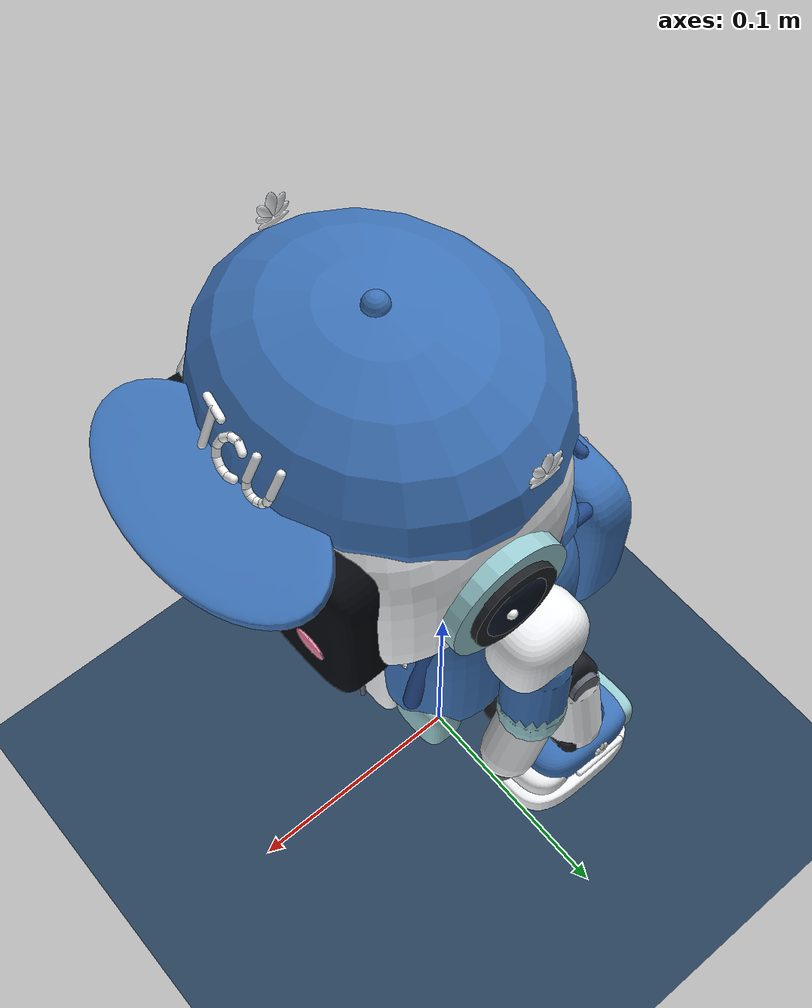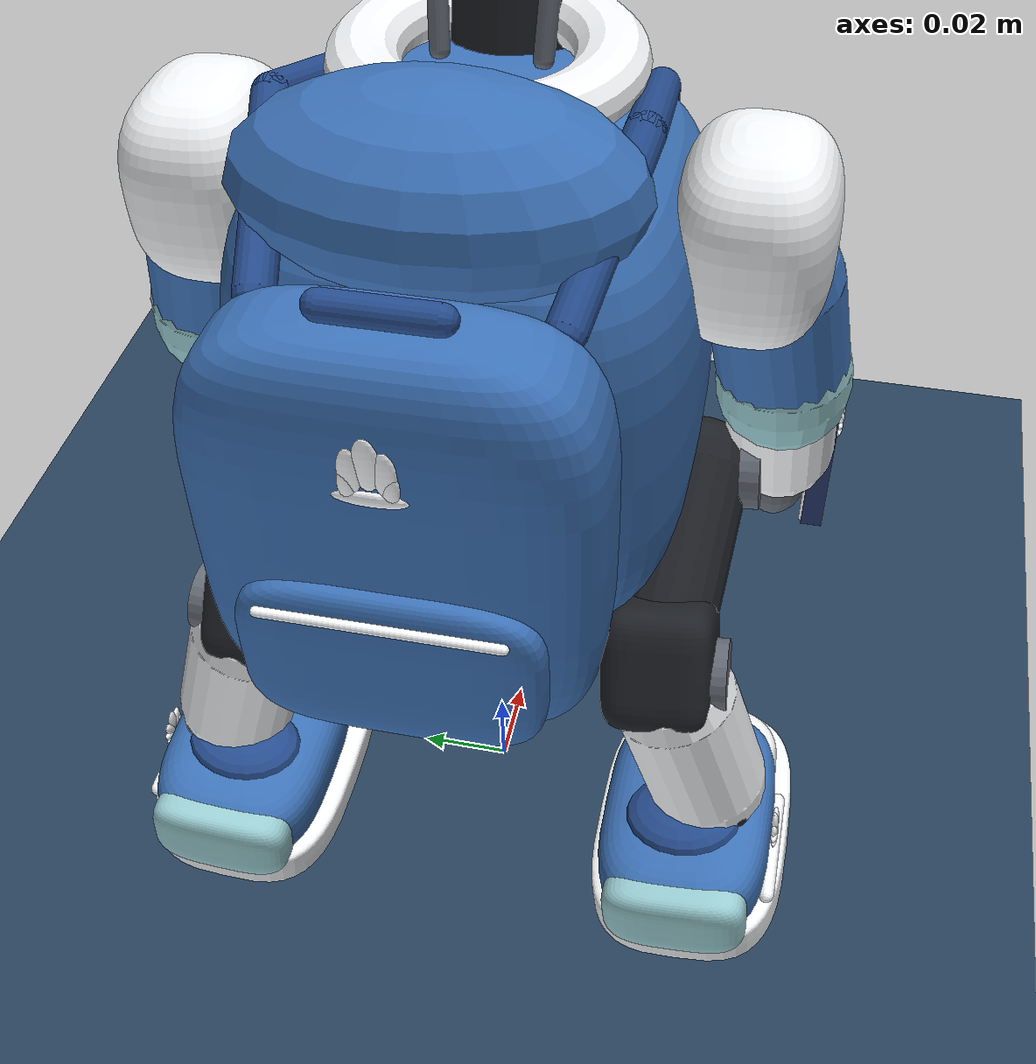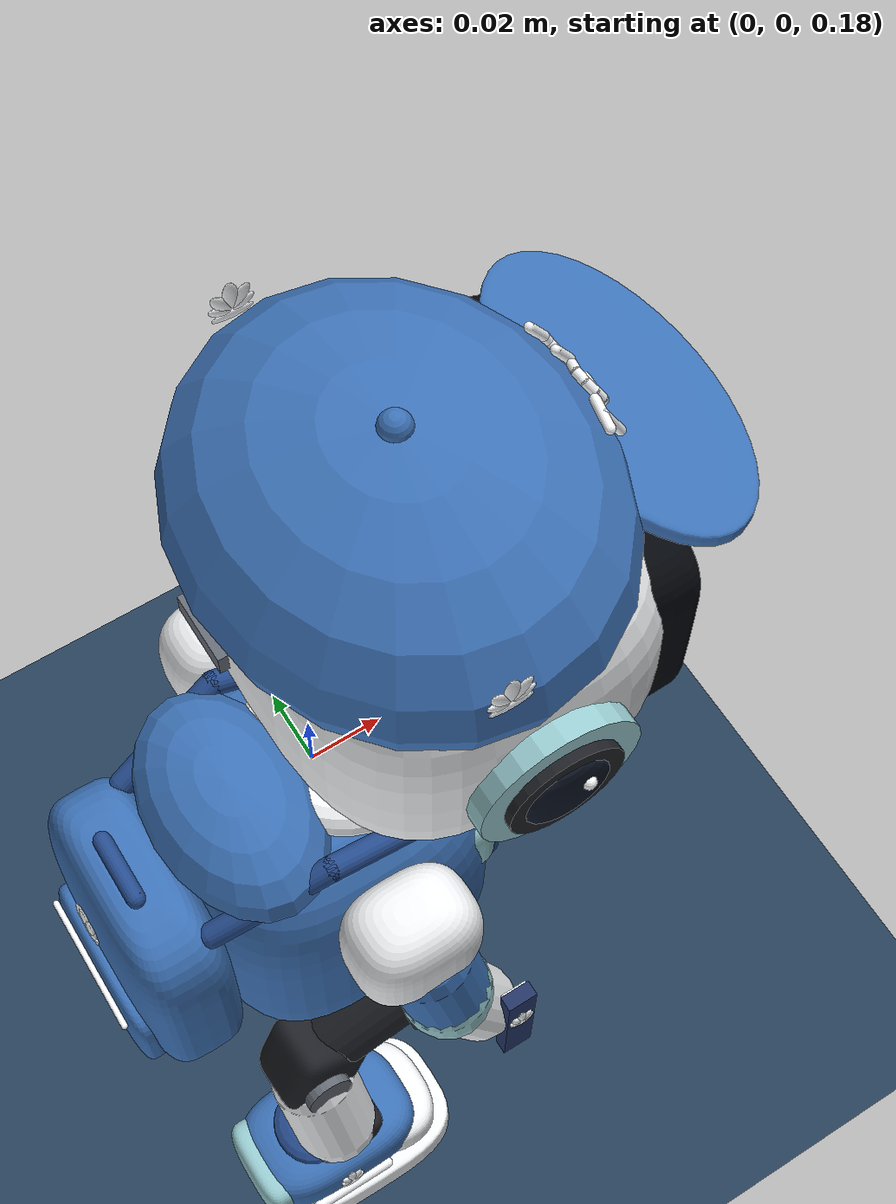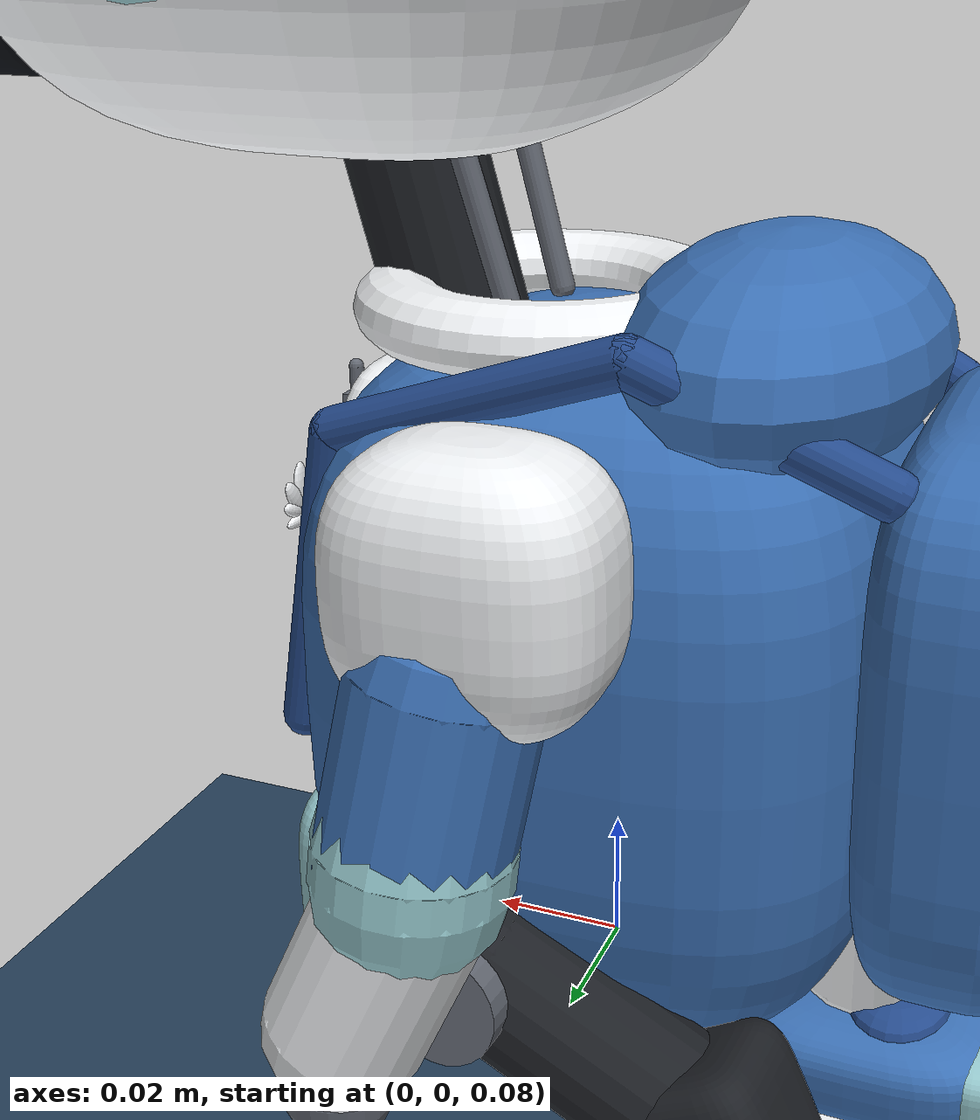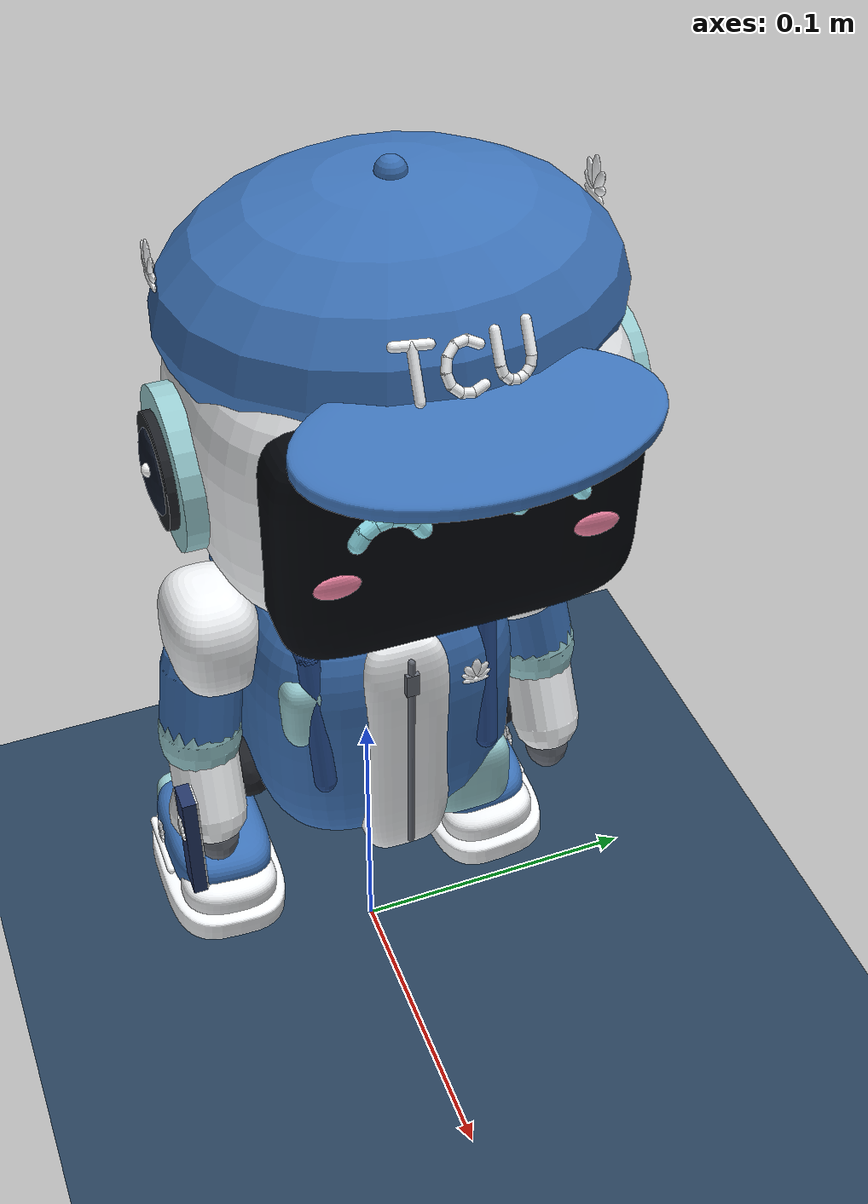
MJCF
<mujoco model="kid_robot">
  <compiler angle="radian" meshdir="assets/"/>

  <visual>
    <global azimuth="160" elevation="-20"/>
    <headlight ambient="0.3 0.3 0.3" diffuse="0.6 0.6 0.6" specular="0 0 0"/>
    <rgba haze="0.15 0.25 0.35 1"/>
  </visual>

  <default>

    <equality solref="0.002" solimp="0.99 0.999 0.0005"/>
    <default class="microduck">
      <joint armature="0.005" frictionloss="0.1"/>

      <equality solref="0.02" solimp="0.9 0.95 0.001"/>
      <general biastype="affine" gainprm="50" biasprm="0 -50 1"/>
      <default class="visual">
        <geom type="mesh" contype="0" conaffinity="0" group="2"/>
      </default>
      <default class="collision">
        <geom group="3"/>
      </default>
    </default>
    <default class="perfect_actuator">
      <joint armature="0.001" damping="0.15" frictionloss="0.1"/>
      <geom contype="0" conaffinity="0"/>

      <equality solref="0.02" solimp="0.9 0.95 0.001"/>
      <general forcerange="-20 20" biastype="affine" gainprm="10" biasprm="0 -10 -0.1"/>
    </default>
    <default class="chosen_actuator_old">
      <joint armature="0.002" damping="0.048" frictionloss="0.006"/>
      <geom contype="0" conaffinity="0"/>

      <equality solref="0.02" solimp="0.9 0.95 0.001"/>
      <general ctrlrange="-10 10" forcerange="-0.91 0.91" biastype="affine" gainprm="0.52" biasprm="0 -0.52"/>
    </default>
    <default class="chosen_actuator_new">
      <joint armature="0.002" damping="0.041" frictionloss="0.032"/>
      <geom contype="0" conaffinity="0"/>

      <equality solref="0.02" solimp="0.9 0.95 0.001"/>
      <general ctrlrange="-10 10" forcerange="-0.67 0.67" biastype="affine" gainprm="0.386" biasprm="0 -0.386"/>
    </default>
    <default class="chosen_actuator_antoine">
      <joint armature="0.0017" damping="0.044" frictionloss="0.013"/>
      <geom contype="0" conaffinity="0"/>

      <equality solref="0.02" solimp="0.9 0.95 0.001"/>
      <general ctrlrange="-10 10" forcerange="-0.75 0.75" biastype="affine" gainprm="0.43" biasprm="0 -0.43"/>
    </default>
    <default class="chosen_actuator">
      <joint armature="0.0018" damping="0.053" frictionloss="0.0048"/>
      <geom contype="0" conaffinity="0"/>

      <equality solref="0.02" solimp="0.9 0.95 0.001"/>
      <general ctrlrange="-10 10" forcerange="-0.96 0.96" biastype="affine" gainprm="0.55" biasprm="0 -0.55"/>
    </default>
    <default class="passive_wheel">
      <joint armature="0.0001"/>
      <geom contype="0" conaffinity="0"/>

      <equality solref="0.02" solimp="0.9 0.95 0.001"/>
    </default>
    <default class="passive_joint">
      <joint armature="0.0001"/>
      <geom contype="0" conaffinity="0"/>

      <equality solref="0.02" solimp="0.9 0.95 0.001"/>
    </default>
    <default class="self_collision_only">
      <geom contype="2" conaffinity="2" group="3"/>
    </default>
  </default>

  <asset>
    <texture type="skybox" colorspace="auto" builtin="gradient" rgb1="0.3 0.5 0.7" rgb2="0 0 0" width="512" height="3072"/>
    <texture type="2d" colorspace="auto" name="groundplane" builtin="checker" mark="edge" rgb1="0.2 0.3 0.4" rgb2="0.1 0.2 0.3" markrgb="0.8 0.8 0.8" width="300" height="300"/>
    <material name="groundplane" texture="groundplane" texuniform="true" texrepeat="5 5" reflectance="0.2"/>
    <material name="tcu_blue" specular="0.25" rgba="0.24 0.45 0.72 1"/>
    <material name="tcu_blue_dark" specular="0.25" rgba="0.15 0.3 0.56 1"/>
    <material name="tcu_teal" specular="0.25" rgba="0.6 0.8 0.82 1"/>
    <material name="tcu_white" specular="0.45" rgba="0.95 0.96 0.97 1"/>
    <material name="tcu_mech" specular="0.6" rgba="0.12 0.13 0.15 1"/>
    <material name="tcu_mech_grey" specular="0.6" rgba="0.4 0.42 0.46 1"/>
    <material name="tcu_screen" specular="0.9" rgba="0.02 0.03 0.05 1"/>
    <material name="tcu_eye" emission="1" specular="0.2" rgba="0.62 0.95 1 1"/>
    <material name="tcu_blush" emission="0.45" specular="0.1" rgba="1 0.55 0.68 1"/>
    <material name="tcu_lens" specular="1" rgba="0.05 0.08 0.14 1"/>
    <material name="tcu_lens_glint" emission="0.8"/>
    <material name="tcu_book" specular="0.3" rgba="0.14 0.21 0.4 1"/>
    <material name="tcu_mark" emission="0.25" specular="0.3" rgba="0.98 0.99 1 1"/>
    <mesh name="kid_mesh_0" vertex="0 0 -0.045 -0.0113002 -6.22401e-13 -0.0447302 -0.0112096 -0.00410374 -0.0447302 -0.0109376 -0.00638781 -0.0447302 -0.0104836 -0.00820245 -0.0447302 -0.00984597 -0.00970187 -0.0447302 -0.00902093 -0.0109403 -0.0447302 -0.00799979 -0.0119409 -0.0447302 -0.00676342 -0.0127141 -0.0447302 -0.00526714 -0.0132647 -0.0447302 -0.00338378 -0.0135946 -0.0447302 3.27057e-13 -0.0137045 -0.0447302 0.00338378 -0.0135946 -0.0447302 0.00526714 -0.0132647 -0.0447302 0.00676342 -0.0127141 -0.0447302 0.00799979 -0.0119409 -0.0447302 0.00902093 -0.0109403 -0.0447302 0.00984597 -0.00970187 -0.0447302 0.0104836 -0.00820245 -0.0447302 0.0109376 -0.00638781 -0.0447302 0.0112096 -0.00410374 -0.0447302 0.0113002 0 -0.0447302 0.0112096 0.00410374 -0.0447302 0.0109376 0.00638781 -0.0447302 0.0104836 0.00820245 -0.0447302 0.00984597 0.00970187 -0.0447302 0.00902093 0.0109403 -0.0447302 0.00799979 0.0119409 -0.0447302 0.00676342 0.0127141 -0.0447302 0.00526714 0.0132647 -0.0447302 0.00338378 0.0135946 -0.0447302 3.27057e-13 0.0137045 -0.0447302 -0.00338378 0.0135946 -0.0447302 -0.00526714 0.0132647 -0.0447302 -0.00676342 0.0127141 -0.0447302 -0.00799979 0.0119409 -0.0447302 -0.00902093 0.0109403 -0.0447302 -0.00984597 0.00970187 -0.0447302 -0.0104836 0.00820245 -0.0447302 -0.0109376 0.00638781 -0.0447302 -0.0112096 0.00410374 -0.0447302 -0.0182472 -1.00503e-12 -0.0439211 -0.0181008 -0.00662656 -0.0439211 -0.0176616 -0.0103148 -0.0439211 -0.0169285 -0.013245 -0.0439211 -0.0158989 -0.0156662 -0.0439211 -0.0145667 -0.017666 -0.0439211 -0.0129178 -0.0192817 -0.0439211 -0.0109213 -0.0205303 -0.0439211 -0.00850519 -0.0214194 -0.0439211 -0.00546401 -0.0219521 -0.0439211 5.2812e-13 -0.0221295 -0.0439211 0.00546401 -0.0219521 -0.0439211 0.00850519 -0.0214194 -0.0439211 0.0109213 -0.0205303 -0.0439211 0.0129178 -0.0192817 -0.0439211 0.0145667 -0.017666 -0.0439211 0.0158989 -0.0156662 -0.0439211 0.0169285 -0.013245 -0.0439211 0.0176616 -0.0103148 -0.0439211 0.0181008 -0.00662656 -0.0439211 0.0182472 0 -0.0439211 0.0181008 0.00662656 -0.0439211 0.0176616 0.0103148 -0.0439211 0.0169285 0.013245 -0.0439211 0.0158989 0.0156662 -0.0439211 0.0145667 0.017666 -0.0439211 0.0129178 0.0192817 -0.0439211 0.0109213 0.0205303 -0.0439211 0.00850519 0.0214194 -0.0439211 0.00546401 0.0219521 -0.0439211 5.2812e-13 0.0221295 -0.0439211 -0.00546401 0.0219521 -0.0439211 -0.00850519 0.0214194 -0.0439211 -0.0109213 0.0205303 -0.0439211 -0.0129178 0.0192817 -0.0439211 -0.0145667 0.017666 -0.0439211 -0.0158989 0.0156662 -0.0439211 -0.0169285 0.013245 -0.0439211 -0.0176616 0.0103148 -0.0439211 -0.0181008 0.00662656 -0.0439211 -0.0239931 -1.32151e-12 -0.0425739 -0.0238006 -0.00871322 -0.0425739 -0.0232231 -0.0135629 -0.0425739 -0.0222591 -0.0174158 -0.0425739 -0.0209054 -0.0205994 -0.0425739 -0.0191536 -0.0232289 -0.0425739 -0.0169855 -0.0253533 -0.0425739 -0.0143604 -0.0269951 -0.0425739 -0.0111834 -0.0281642 -0.0425739 -0.00718459 -0.0288646 -0.0425739 6.94422e-13 -0.029098 -0.0425739 0.00718459 -0.0288646 -0.0425739 0.0111834 -0.0281642 -0.0425739 0.0143604 -0.0269951 -0.0425739 0.0169855 -0.0253533 -0.0425739 0.0191536 -0.0232289 -0.0425739 0.0209054 -0.0205994 -0.0425739 0.0222591 -0.0174158 -0.0425739 0.0232231 -0.0135629 -0.0425739 0.0238006 -0.00871322 -0.0425739 0.0239931 0 -0.0425739 0.0238006 0.00871322 -0.0425739 0.0232231 0.0135629 -0.0425739 0.0222591 0.0174158 -0.0425739 0.0209054 0.0205994 -0.0425739 0.0191536 0.0232289 -0.0425739 0.0169855 0.0253533 -0.0425739 0.0143604 0.0269951 -0.0425739 0.0111834 0.0281642 -0.0425739 0.00718459 0.0288646 -0.0425739 6.94422e-13 0.029098 -0.0425739 -0.00718459 0.0288646 -0.0425739 -0.0111834 0.0281642 -0.0425739 -0.0143604 0.0269951 -0.0425739 -0.0169855 0.0253533 -0.0425739 -0.0191536 0.0232289 -0.0425739 -0.0209054 0.0205994 -0.0425739 -0.0222591 0.0174158 -0.0425739 -0.0232231 0.0135629 -0.0425739 -0.0238006 0.00871322 -0.0425739 -0.0289319 -1.59353e-12 -0.0406897 -0.0286999 -0.0105068 -0.0406897 -0.0280034 -0.0163547 -0.0406897 -0.026841 -0.0210007 -0.0406897 -0.0252086 -0.0248397 -0.0406897 -0.0230963 -0.0280104 -0.0406897 -0.0204818 -0.0305722 -0.0406897 -0.0173164 -0.0325519 -0.0406897 -0.0134854 -0.0339616 -0.0406897 -0.00866349 -0.0348062 -0.0406897 8.37364e-13 -0.0350876 -0.0406897 0.00866349 -0.0348062 -0.0406897 0.0134854 -0.0339616 -0.0406897 0.0173164 -0.0325519 -0.0406897 0.0204818 -0.0305722 -0.0406897 0.0230963 -0.0280104 -0.0406897 0.0252086 -0.0248397 -0.0406897 0.026841 -0.0210007 -0.0406897 0.0280034 -0.0163547 -0.0406897 0.0286999 -0.0105068 -0.0406897 0.0289319 0 -0.0406897 0.0286999 0.0105068 -0.0406897 0.0280034 0.0163547 -0.0406897 0.026841 0.0210007 -0.0406897 0.0252086 0.0248397 -0.0406897 0.0230963 0.0280104 -0.0406897 0.0204818 0.0305722 -0.0406897 0.0173164 0.0325519 -0.0406897 0.0134854 0.0339616 -0.0406897 0.00866349 0.0348062 -0.0406897 8.37364e-13 0.0350876 -0.0406897 -0.00866349 0.0348062 -0.0406897 -0.0134854 0.0339616 -0.0406897 -0.0173164 0.0325519 -0.0406897 -0.0204818 0.0305722 -0.0406897 -0.0230963 0.0280104 -0.0406897 -0.0252086 0.0248397 -0.0406897 -0.026841 0.0210007 -0.0406897 -0.0280034 0.0163547 -0.0406897 -0.0286999 0.0105068 -0.0406897 -0.0332056 -1.82892e-12 -0.0382683 -0.0329393 -0.0120588 -0.0382683 -0.0321399 -0.0187705 -0.0382683 -0.0308059 -0.0241028 -0.0382683 -0.0289323 -0.0285089 -0.0382683 -0.0265079 -0.0321479 -0.0382683 -0.0235073 -0.0350881 -0.0382683 -0.0198743 -0.0373603 -0.0382683 -0.0154774 -0.0389782 -0.0382683 -0.00994322 -0.0399476 -0.0382683 9.61055e-13 -0.0402706 -0.0382683 0.00994322 -0.0399476 -0.0382683 0.0154774 -0.0389782 -0.0382683 0.0198743 -0.0373603 -0.0382683 0.0235073 -0.0350881 -0.0382683 0.0265079 -0.0321479 -0.0382683 0.0289323 -0.0285089 -0.0382683 0.0308059 -0.0241028 -0.0382683 0.0321399 -0.0187705 -0.0382683 0.0329393 -0.0120588 -0.0382683 0.0332056 0 -0.0382683 0.0329393 0.0120588 -0.0382683 0.0321399 0.0187705 -0.0382683 0.0308059 0.0241028 -0.0382683 0.0289323 0.0285089 -0.0382683 0.0265079 0.0321479 -0.0382683 0.0235073 0.0350881 -0.0382683 0.0198743 0.0373603 -0.0382683 0.0154774 0.0389782 -0.0382683 0.00994322 0.0399476 -0.0382683 9.61055e-13 0.0402706 -0.0382683 -0.00994322 0.0399476 -0.0382683 -0.0154774 0.0389782 -0.0382683 -0.0198743 0.0373603 -0.0382683 -0.0235073 0.0350881 -0.0382683 -0.0265079 0.0321479 -0.0382683 -0.0289323 0.0285089 -0.0382683 -0.0308059 0.0241028 -0.0382683 -0.0321399 0.0187705 -0.0382683 -0.0329393 0.0120588 -0.0382683 -0.0368755 -2.03105e-12 -0.0353063 -0.0365797 -0.0133915 -0.0353063 -0.035692 -0.020845 -0.0353063 -0.0342105 -0.0267667 -0.0353063 -0.0321299 -0.0316597 -0.0353063 -0.0294376 -0.0357009 -0.0353063 -0.0261053 -0.0389661 -0.0353063 -0.0220708 -0.0414894 -0.0353063 -0.017188 -0.0432861 -0.0353063 -0.0110421 -0.0443626 -0.0353063 1.06727e-12 -0.0447213 -0.0353063 0.0110421 -0.0443626 -0.0353063 0.017188 -0.0432861 -0.0353063 0.0220708 -0.0414894 -0.0353063 0.0261053 -0.0389661 -0.0353063 0.0294376 -0.0357009 -0.0353063 0.0321299 -0.0316597 -0.0353063 0.0342105 -0.0267667 -0.0353063 0.035692 -0.020845 -0.0353063 0.0365797 -0.0133915 -0.0353063 0.0368755 0 -0.0353063 0.0365797 0.0133915 -0.0353063 0.035692 0.020845 -0.0353063 0.0342105 0.0267667 -0.0353063 0.0321299 0.0316597 -0.0353063 0.0294376 0.0357009 -0.0353063 0.0261053 0.0389661 -0.0353063 0.0220708 0.0414894 -0.0353063 0.017188 0.0432861 -0.0353063 0.0110421 0.0443626 -0.0353063 1.06727e-12 0.0447213 -0.0353063 -0.0110421 0.0443626 -0.0353063 -0.017188 0.0432861 -0.0353063 -0.0220708 0.0414894 -0.0353063 -0.0261053 0.0389661 -0.0353063 -0.0294376 0.0357009 -0.0353063 -0.0321299 0.0316597 -0.0353063 -0.0342105 0.0267667 -0.0353063 -0.035692 0.020845 -0.0353063 -0.0365797 0.0133915 -0.0353063 -0.0399691 -2.20145e-12 -0.0317926 -0.0396486 -0.014515 -0.0317926 -0.0386864 -0.0225938 -0.0317926 -0.0370806 -0.0290123 -0.0317926 -0.0348255 -0.0343158 -0.0317926 -0.0319073 -0.0386961 -0.0317926 -0.0282955 -0.0422351 -0.0317926 -0.0239224 -0.0449701 -0.0317926 -0.01863 -0.0469176 -0.0317926 -0.0119685 -0.0480844 -0.0317926 1.15681e-12 -0.0484732 -0.0317926 0.0119685 -0.0480844 -0.0317926 0.01863 -0.0469176 -0.0317926 0.0239224 -0.0449701 -0.0317926 0.0282955 -0.0422351 -0.0317926 0.0319073 -0.0386961 -0.0317926 0.0348255 -0.0343158 -0.0317926 0.0370806 -0.0290123 -0.0317926 0.0386864 -0.0225938 -0.0317926 0.0396486 -0.014515 -0.0317926 0.0399691 0 -0.0317926 0.0396486 0.014515 -0.0317926 0.0386864 0.0225938 -0.0317926 0.0370806 0.0290123 -0.0317926 0.0348255 0.0343158 -0.0317926 0.0319073 0.0386961 -0.0317926 0.0282955 0.0422351 -0.0317926 0.0239224 0.0449701 -0.0317926 0.01863 0.0469176 -0.0317926 0.0119685 0.0480844 -0.0317926 1.15681e-12 0.0484732 -0.0317926 -0.0119685 0.0480844 -0.0317926 -0.01863 0.0469176 -0.0317926 -0.0239224 0.0449701 -0.0317926 -0.0282955 0.0422351 -0.0317926 -0.0319073 0.0386961 -0.0317926 -0.0348255 0.0343158 -0.0317926 -0.0370806 0.0290123 -0.0317926 -0.0386864 0.0225938 -0.0317926 -0.0396486 0.014515 -0.0317926 -0.0424981 -2.34074e-12 -0.0277008 -0.0421572 -0.0154334 -0.0277008 -0.0411342 -0.0240234 -0.0277008 -0.0394268 -0.030848 -0.0277008 -0.037029 -0.036487 -0.0277008 -0.0339261 -0.0411445 -0.0277008 -0.0300858 -0.0449075 -0.0277008 -0.0254361 -0.0478155 -0.0277008 -0.0198088 -0.0498862 -0.0277008 -0.0127258 -0.0511269 -0.0277008 1.23e-12 -0.0515402 -0.0277008 0.0127258 -0.0511269 -0.0277008 0.0198088 -0.0498862 -0.0277008 0.0254361 -0.0478155 -0.0277008 0.0300858 -0.0449075 -0.0277008 0.0339261 -0.0411445 -0.0277008 0.037029 -0.036487 -0.0277008 0.0394268 -0.030848 -0.0277008 0.0411342 -0.0240234 -0.0277008 0.0421572 -0.0154334 -0.0277008 0.0424981 0 -0.0277008 0.0421572 0.0154334 -0.0277008 0.0411342 0.0240234 -0.0277008 0.0394268 0.030848 -0.0277008 0.037029 0.036487 -0.0277008 0.0339261 0.0411445 -0.0277008 0.0300858 0.0449075 -0.0277008 0.0254361 0.0478155 -0.0277008 0.0198088 0.0498862 -0.0277008 0.0127258 0.0511269 -0.0277008 1.23e-12 0.0515402 -0.0277008 -0.0127258 0.0511269 -0.0277008 -0.0198088 0.0498862 -0.0277008 -0.0254361 0.0478155 -0.0277008 -0.0300858 0.0449075 -0.0277008 -0.0339261 0.0411445 -0.0277008 -0.037029 0.036487 -0.0277008 -0.0394268 0.030848 -0.0277008 -0.0411342 0.0240234 -0.0277008 -0.0421572 0.0154334 -0.0277008 -0.0444661 -2.44913e-12 -0.0229721 -0.0441094 -0.0161481 -0.0229721 -0.0430391 -0.0251359 -0.0229721 -0.0412526 -0.0322765 -0.0229721 -0.0387437 -0.0381766 -0.0229721 -0.0354972 -0.0430498 -0.0229721 -0.031479 -0.046987 -0.0229721 -0.0266139 -0.0500297 -0.0229721 -0.0207261 -0.0521963 -0.0229721 -0.0133151 -0.0534944 -0.0229721 1.28696e-12 -0.0539269 -0.0229721 0.0133151 -0.0534944 -0.0229721 0.0207261 -0.0521963 -0.0229721 0.0266139 -0.0500297 -0.0229721 0.031479 -0.046987 -0.0229721 0.0354972 -0.0430498 -0.0229721 0.0387437 -0.0381766 -0.0229721 0.0412526 -0.0322765 -0.0229721 0.0430391 -0.0251359 -0.0229721 0.0441094 -0.0161481 -0.0229721 0.0444661 0 -0.0229721 0.0441094 0.0161481 -0.0229721 0.0430391 0.0251359 -0.0229721 0.0412526 0.0322765 -0.0229721 0.0387437 0.0381766 -0.0229721 0.0354972 0.0430498 -0.0229721 0.031479 0.046987 -0.0229721 0.0266139 0.0500297 -0.0229721 0.0207261 0.0521963 -0.0229721 0.0133151 0.0534944 -0.0229721 1.28696e-12 0.0539269 -0.0229721 -0.0133151 0.0534944 -0.0229721 -0.0207261 0.0521963 -0.0229721 -0.0266139 0.0500297 -0.0229721 -0.031479 0.046987 -0.0229721 -0.0354972 0.0430498 -0.0229721 -0.0387437 0.0381766 -0.0229721 -0.0412526 0.0322765 -0.0229721 -0.0430391 0.0251359 -0.0229721 -0.0441094 0.0161481 -0.0229721 -0.0458731 -2.52664e-12 -0.0174707 -0.0455052 -0.0166591 -0.0174707 -0.044401 -0.0259313 -0.0174707 -0.042558 -0.0332978 -0.0174707 -0.0399697 -0.0393847 -0.0174707 -0.0366205 -0.044412 -0.0174707 -0.0324751 -0.0484739 -0.0174707 -0.0274561 -0.0516129 -0.0174707 -0.0213819 -0.053848 -0.0174707 -0.0137365 -0.0551872 -0.0174707 1.32769e-12 -0.0556334 -0.0174707 0.0137365 -0.0551872 -0.0174707 0.0213819 -0.053848 -0.0174707 0.0274561 -0.0516129 -0.0174707 0.0324751 -0.0484739 -0.0174707 0.0366205 -0.044412 -0.0174707 0.0399697 -0.0393847 -0.0174707 0.042558 -0.0332978 -0.0174707 0.044401 -0.0259313 -0.0174707 0.0455052 -0.0166591 -0.0174707 0.0458731 0 -0.0174707 0.0455052 0.0166591 -0.0174707 0.044401 0.0259313 -0.0174707 0.042558 0.0332978 -0.0174707 0.0399697 0.0393847 -0.0174707 0.0366205 0.044412 -0.0174707 0.0324751 0.0484739 -0.0174707 0.0274561 0.0516129 -0.0174707 0.0213819 0.053848 -0.0174707 0.0137365 0.0551872 -0.0174707 1.32769e-12 0.0556334 -0.0174707 -0.0137365 0.0551872 -0.0174707 -0.0213819 0.053848 -0.0174707 -0.0274561 0.0516129 -0.0174707 -0.0324751 0.0484739 -0.0174707 -0.0366205 0.044412 -0.0174707 -0.0399697 0.0393847 -0.0174707 -0.042558 0.0332978 -0.0174707 -0.044401 0.0259313 -0.0174707 -0.0455052 0.0166591 -0.0174707 -0.0467182 -2.57318e-12 -0.0108193 -0.0463435 -0.016966 -0.0108193 -0.0452189 -0.026409 -0.0108193 -0.0433419 -0.0339112 -0.0108193 -0.040706 -0.0401102 -0.0108193 -0.037295 -0.0452302 -0.0108193 -0.0330733 -0.0493668 -0.0108193 -0.0279619 -0.0525636 -0.0108193 -0.0217758 -0.0548399 -0.0108193 -0.0139895 -0.0562038 -0.0108193 1.35215e-12 -0.0566582 -0.0108193 0.0139895 -0.0562038 -0.0108193 0.0217758 -0.0548399 -0.0108193 0.0279619 -0.0525636 -0.0108193 0.0330733 -0.0493668 -0.0108193 0.037295 -0.0452302 -0.0108193 0.040706 -0.0401102 -0.0108193 0.0433419 -0.0339112 -0.0108193 0.0452189 -0.026409 -0.0108193 0.0463435 -0.016966 -0.0108193 0.0467182 0 -0.0108193 0.0463435 0.016966 -0.0108193 0.0452189 0.026409 -0.0108193 0.0433419 0.0339112 -0.0108193 0.040706 0.0401102 -0.0108193 0.037295 0.0452302 -0.0108193 0.0330733 0.0493668 -0.0108193 0.0279619 0.0525636 -0.0108193 0.0217758 0.0548399 -0.0108193 0.0139895 0.0562038 -0.0108193 1.35215e-12 0.0566582 -0.0108193 -0.0139895 0.0562038 -0.0108193 -0.0217758 0.0548399 -0.0108193 -0.0279619 0.0525636 -0.0108193 -0.0330733 0.0493668 -0.0108193 -0.037295 0.0452302 -0.0108193 -0.040706 0.0401102 -0.0108193 -0.0433419 0.0339112 -0.0108193 -0.0452189 0.026409 -0.0108193 -0.0463435 0.016966 -0.0108193 -0.047 -2.5887e-12 0 -0.0466231 -0.0170683 0 -0.0454917 -0.0265683 0 -0.0436034 -0.0341158 0 -0.0409516 -0.0403522 0 -0.03752 -0.045503 0 -0.0332729 -0.0496646 0 -0.0281306 -0.0528807 0 -0.0219072 -0.0551708 0 -0.0140739 -0.0565429 0 1.3603e-12 -0.057 0 0.0140739 -0.0565429 0 0.0219072 -0.0551708 0 0.0281306 -0.0528807 0 0.0332729 -0.0496646 0 0.03752 -0.045503 0 0.0409516 -0.0403522 0 0.0436034 -0.0341158 0 0.0454917 -0.0265683 0 0.0466231 -0.0170683 0 0.047 0 0 0.0466231 0.0170683 0 0.0454917 0.0265683 0 0.0436034 0.0341158 0 0.0409516 0.0403522 0 0.03752 0.045503 0 0.0332729 0.0496646 0 0.0281306 0.0528807 0 0.0219072 0.0551708 0 0.0140739 0.0565429 0 1.3603e-12 0.057 0 -0.0140739 0.0565429 0 -0.0219072 0.0551708 0 -0.0281306 0.0528807 0 -0.0332729 0.0496646 0 -0.03752 0.045503 0 -0.0409516 0.0403522 0 -0.0436034 0.0341158 0 -0.0454917 0.0265683 0 -0.0466231 0.0170683 0 -0.0467182 -2.57318e-12 0.0108193 -0.0463435 -0.016966 0.0108193 -0.0452189 -0.026409 0.0108193 -0.0433419 -0.0339112 0.0108193 -0.040706 -0.0401102 0.0108193 -0.037295 -0.0452302 0.0108193 -0.0330733 -0.0493668 0.0108193 -0.0279619 -0.0525636 0.0108193 -0.0217758 -0.0548399 0.0108193 -0.0139895 -0.0562038 0.0108193 1.35215e-12 -0.0566582 0.0108193 0.0139895 -0.0562038 0.0108193 0.0217758 -0.0548399 0.0108193 0.0279619 -0.0525636 0.0108193 0.0330733 -0.0493668 0.0108193 0.037295 -0.0452302 0.0108193 0.040706 -0.0401102 0.0108193 0.0433419 -0.0339112 0.0108193 0.0452189 -0.026409 0.0108193 0.0463435 -0.016966 0.0108193 0.0467182 0 0.0108193 0.0463435 0.016966 0.0108193 0.0452189 0.026409 0.0108193 0.0433419 0.0339112 0.0108193 0.040706 0.0401102 0.0108193 0.037295 0.0452302 0.0108193 0.0330733 0.0493668 0.0108193 0.0279619 0.0525636 0.0108193 0.0217758 0.0548399 0.0108193 0.0139895 0.0562038 0.0108193 1.35215e-12 0.0566582 0.0108193 -0.0139895 0.0562038 0.0108193 -0.0217758 0.0548399 0.0108193 -0.0279619 0.0525636 0.0108193 -0.0330733 0.0493668 0.0108193 -0.037295 0.0452302 0.0108193 -0.040706 0.0401102 0.0108193 -0.0433419 0.0339112 0.0108193 -0.0452189 0.026409 0.0108193 -0.0463435 0.016966 0.0108193 -0.0458731 -2.52664e-12 0.0174707 -0.0455052 -0.0166591 0.0174707 -0.044401 -0.0259313 0.0174707 -0.042558 -0.0332978 0.0174707 -0.0399697 -0.0393847 0.0174707 -0.0366205 -0.044412 0.0174707 -0.0324751 -0.0484739 0.0174707 -0.0274561 -0.0516129 0.0174707 -0.0213819 -0.053848 0.0174707 -0.0137365 -0.0551872 0.0174707 1.32769e-12 -0.0556334 0.0174707 0.0137365 -0.0551872 0.0174707 0.0213819 -0.053848 0.0174707 0.0274561 -0.0516129 0.0174707 0.0324751 -0.0484739 0.0174707 0.0366205 -0.044412 0.0174707 0.0399697 -0.0393847 0.0174707 0.042558 -0.0332978 0.0174707 0.044401 -0.0259313 0.0174707 0.0455052 -0.0166591 0.0174707 0.0458731 0 0.0174707 0.0455052 0.0166591 0.0174707 0.044401 0.0259313 0.0174707 0.042558 0.0332978 0.0174707 0.0399697 0.0393847 0.0174707 0.0366205 0.044412 0.0174707 0.0324751 0.0484739 0.0174707 0.0274561 0.0516129 0.0174707 0.0213819 0.053848 0.0174707 0.0137365 0.0551872 0.0174707 1.32769e-12 0.0556334 0.0174707 -0.0137365 0.0551872 0.0174707 -0.0213819 0.053848 0.0174707 -0.0274561 0.0516129 0.0174707 -0.0324751 0.0484739 0.0174707 -0.0366205 0.044412 0.0174707 -0.0399697 0.0393847 0.0174707 -0.042558 0.0332978 0.0174707 -0.044401 0.0259313 0.0174707 -0.0455052 0.0166591 0.0174707 -0.0444661 -2.44913e-12 0.0229721 -0.0441094 -0.0161481 0.0229721 -0.0430391 -0.0251359 0.0229721 -0.0412526 -0.0322765 0.0229721 -0.0387437 -0.0381766 0.0229721 -0.0354972 -0.0430498 0.0229721 -0.031479 -0.046987 0.0229721 -0.0266139 -0.0500297 0.0229721 -0.0207261 -0.0521963 0.0229721 -0.0133151 -0.0534944 0.0229721 1.28696e-12 -0.0539269 0.0229721 0.0133151 -0.0534944 0.0229721 0.0207261 -0.0521963 0.0229721 0.0266139 -0.0500297 0.0229721 0.031479 -0.046987 0.0229721 0.0354972 -0.0430498 0.0229721 0.0387437 -0.0381766 0.0229721 0.0412526 -0.0322765 0.0229721 0.0430391 -0.0251359 0.0229721 0.0441094 -0.0161481 0.0229721 0.0444661 0 0.0229721 0.0441094 0.0161481 0.0229721 0.0430391 0.0251359 0.0229721 0.0412526 0.0322765 0.0229721 0.0387437 0.0381766 0.0229721 0.0354972 0.0430498 0.0229721 0.031479 0.046987 0.0229721 0.0266139 0.0500297 0.0229721 0.0207261 0.0521963 0.0229721 0.0133151 0.0534944 0.0229721 1.28696e-12 0.0539269 0.0229721 -0.0133151 0.0534944 0.0229721 -0.0207261 0.0521963 0.0229721 -0.0266139 0.0500297 0.0229721 -0.031479 0.046987 0.0229721 -0.0354972 0.0430498 0.0229721 -0.0387437 0.0381766 0.0229721 -0.0412526 0.0322765 0.0229721 -0.0430391 0.0251359 0.0229721 -0.0441094 0.0161481 0.0229721 -0.0424981 -2.34074e-12 0.0277008 -0.0421572 -0.0154334 0.0277008 -0.0411342 -0.0240234 0.0277008 -0.0394268 -0.030848 0.0277008 -0.037029 -0.036487 0.0277008 -0.0339261 -0.0411445 0.0277008 -0.0300858 -0.0449075 0.0277008 -0.0254361 -0.0478155 0.0277008 -0.0198088 -0.0498862 0.0277008 -0.0127258 -0.0511269 0.0277008 1.23e-12 -0.0515402 0.0277008 0.0127258 -0.0511269 0.0277008 0.0198088 -0.0498862 0.0277008 0.0254361 -0.0478155 0.0277008 0.0300858 -0.0449075 0.0277008 0.0339261 -0.0411445 0.0277008 0.037029 -0.036487 0.0277008 0.0394268 -0.030848 0.0277008 0.0411342 -0.0240234 0.0277008 0.0421572 -0.0154334 0.0277008 0.0424981 0 0.0277008 0.0421572 0.0154334 0.0277008 0.0411342 0.0240234 0.0277008 0.0394268 0.030848 0.0277008 0.037029 0.036487 0.0277008 0.0339261 0.0411445 0.0277008 0.0300858 0.0449075 0.0277008 0.0254361 0.0478155 0.0277008 0.0198088 0.0498862 0.0277008 0.0127258 0.0511269 0.0277008 1.23e-12 0.0515402 0.0277008 -0.0127258 0.0511269 0.0277008 -0.0198088 0.0498862 0.0277008 -0.0254361 0.0478155 0.0277008 -0.0300858 0.0449075 0.0277008 -0.0339261 0.0411445 0.0277008 -0.037029 0.036487 0.0277008 -0.0394268 0.030848 0.0277008 -0.0411342 0.0240234 0.0277008 -0.0421572 0.0154334 0.0277008 -0.0399691 -2.20145e-12 0.0317926 -0.0396486 -0.014515 0.0317926 -0.0386864 -0.0225938 0.0317926 -0.0370806 -0.0290123 0.0317926 -0.0348255 -0.0343158 0.0317926 -0.0319073 -0.0386961 0.0317926 -0.0282955 -0.0422351 0.0317926 -0.0239224 -0.0449701 0.0317926 -0.01863 -0.0469176 0.0317926 -0.0119685 -0.0480844 0.0317926 1.15681e-12 -0.0484732 0.0317926 0.0119685 -0.0480844 0.0317926 0.01863 -0.0469176 0.0317926 0.0239224 -0.0449701 0.0317926 0.0282955 -0.0422351 0.0317926 0.0319073 -0.0386961 0.0317926 0.0348255 -0.0343158 0.0317926 0.0370806 -0.0290123 0.0317926 0.0386864 -0.0225938 0.0317926 0.0396486 -0.014515 0.0317926 0.0399691 0 0.0317926 0.0396486 0.014515 0.0317926 0.0386864 0.0225938 0.0317926 0.0370806 0.0290123 0.0317926 0.0348255 0.0343158 0.0317926 0.0319073 0.0386961 0.0317926 0.0282955 0.0422351 0.0317926 0.0239224 0.0449701 0.0317926 0.01863 0.0469176 0.0317926 0.0119685 0.0480844 0.0317926 1.15681e-12 0.0484732 0.0317926 -0.0119685 0.0480844 0.0317926 -0.01863 0.0469176 0.0317926 -0.0239224 0.0449701 0.0317926 -0.0282955 0.0422351 0.0317926 -0.0319073 0.0386961 0.0317926 -0.0348255 0.0343158 0.0317926 -0.0370806 0.0290123 0.0317926 -0.0386864 0.0225938 0.0317926 -0.0396486 0.014515 0.0317926 -0.0368755 -2.03105e-12 0.0353063 -0.0365797 -0.0133915 0.0353063 -0.035692 -0.020845 0.0353063 -0.0342105 -0.0267667 0.0353063 -0.0321299 -0.0316597 0.0353063 -0.0294376 -0.0357009 0.0353063 -0.0261053 -0.0389661 0.0353063 -0.0220708 -0.0414894 0.0353063 -0.017188 -0.0432861 0.0353063 -0.0110421 -0.0443626 0.0353063 1.06727e-12 -0.0447213 0.0353063 0.0110421 -0.0443626 0.0353063 0.017188 -0.0432861 0.0353063 0.0220708 -0.0414894 0.0353063 0.0261053 -0.0389661 0.0353063 0.0294376 -0.0357009 0.0353063 0.0321299 -0.0316597 0.0353063 0.0342105 -0.0267667 0.0353063 0.035692 -0.020845 0.0353063 0.0365797 -0.0133915 0.0353063 0.0368755 0 0.0353063 0.0365797 0.0133915 0.0353063 0.035692 0.020845 0.0353063 0.0342105 0.0267667 0.0353063 0.0321299 0.0316597 0.0353063 0.0294376 0.0357009 0.0353063 0.0261053 0.0389661 0.0353063 0.0220708 0.0414894 0.0353063 0.017188 0.0432861 0.0353063 0.0110421 0.0443626 0.0353063 1.06727e-12 0.0447213 0.0353063 -0.0110421 0.0443626 0.0353063 -0.017188 0.0432861 0.0353063 -0.0220708 0.0414894 0.0353063 -0.0261053 0.0389661 0.0353063 -0.0294376 0.0357009 0.0353063 -0.0321299 0.0316597 0.0353063 -0.0342105 0.0267667 0.0353063 -0.035692 0.020845 0.0353063 -0.0365797 0.0133915 0.0353063 -0.0332056 -1.82892e-12 0.0382683 -0.0329393 -0.0120588 0.0382683 -0.0321399 -0.0187705 0.0382683 -0.0308059 -0.0241028 0.0382683 -0.0289323 -0.0285089 0.0382683 -0.0265079 -0.0321479 0.0382683 -0.0235073 -0.0350881 0.0382683 -0.0198743 -0.0373603 0.0382683 -0.0154774 -0.0389782 0.0382683 -0.00994322 -0.0399476 0.0382683 9.61055e-13 -0.0402706 0.0382683 0.00994322 -0.0399476 0.0382683 0.0154774 -0.0389782 0.0382683 0.0198743 -0.0373603 0.0382683 0.0235073 -0.0350881 0.0382683 0.0265079 -0.0321479 0.0382683 0.0289323 -0.0285089 0.0382683 0.0308059 -0.0241028 0.0382683 0.0321399 -0.0187705 0.0382683 0.0329393 -0.0120588 0.0382683 0.0332056 0 0.0382683 0.0329393 0.0120588 0.0382683 0.0321399 0.0187705 0.0382683 0.0308059 0.0241028 0.0382683 0.0289323 0.0285089 0.0382683 0.0265079 0.0321479 0.0382683 0.0235073 0.0350881 0.0382683 0.0198743 0.0373603 0.0382683 0.0154774 0.0389782 0.0382683 0.00994322 0.0399476 0.0382683 9.61055e-13 0.0402706 0.0382683 -0.00994322 0.0399476 0.0382683 -0.0154774 0.0389782 0.0382683 -0.0198743 0.0373603 0.0382683 -0.0235073 0.0350881 0.0382683 -0.0265079 0.0321479 0.0382683 -0.0289323 0.0285089 0.0382683 -0.0308059 0.0241028 0.0382683 -0.0321399 0.0187705 0.0382683 -0.0329393 0.0120588 0.0382683 -0.0289319 -1.59353e-12 0.0406897 -0.0286999 -0.0105068 0.0406897 -0.0280034 -0.0163547 0.0406897 -0.026841 -0.0210007 0.0406897 -0.0252086 -0.0248397 0.0406897 -0.0230963 -0.0280104 0.0406897 -0.0204818 -0.0305722 0.0406897 -0.0173164 -0.0325519 0.0406897 -0.0134854 -0.0339616 0.0406897 -0.00866349 -0.0348062 0.0406897 8.37364e-13 -0.0350876 0.0406897 0.00866349 -0.0348062 0.0406897 0.0134854 -0.0339616 0.0406897 0.0173164 -0.0325519 0.0406897 0.0204818 -0.0305722 0.0406897 0.0230963 -0.0280104 0.0406897 0.0252086 -0.0248397 0.0406897 0.026841 -0.0210007 0.0406897 0.0280034 -0.0163547 0.0406897 0.0286999 -0.0105068 0.0406897 0.0289319 0 0.0406897 0.0286999 0.0105068 0.0406897 0.0280034 0.0163547 0.0406897 0.026841 0.0210007 0.0406897 0.0252086 0.0248397 0.0406897 0.0230963 0.0280104 0.0406897 0.0204818 0.0305722 0.0406897 0.0173164 0.0325519 0.0406897 0.0134854 0.0339616 0.0406897 0.00866349 0.0348062 0.0406897 8.37364e-13 0.0350876 0.0406897 -0.00866349 0.0348062 0.0406897 -0.0134854 0.0339616 0.0406897 -0.0173164 0.0325519 0.0406897 -0.0204818 0.0305722 0.0406897 -0.0230963 0.0280104 0.0406897 -0.0252086 0.0248397 0.0406897 -0.026841 0.0210007 0.0406897 -0.0280034 0.0163547 0.0406897 -0.0286999 0.0105068 0.0406897 -0.0239931 -1.32151e-12 0.0425739 -0.0238006 -0.00871322 0.0425739 -0.0232231 -0.0135629 0.0425739 -0.0222591 -0.0174158 0.0425739 -0.0209054 -0.0205994 0.0425739 -0.0191536 -0.0232289 0.0425739 -0.0169855 -0.0253533 0.0425739 -0.0143604 -0.0269951 0.0425739 -0.0111834 -0.0281642 0.0425739 -0.00718459 -0.0288646 0.0425739 6.94422e-13 -0.029098 0.0425739 0.00718459 -0.0288646 0.0425739 0.0111834 -0.0281642 0.0425739 0.0143604 -0.0269951 0.0425739 0.0169855 -0.0253533 0.0425739 0.0191536 -0.0232289 0.0425739 0.0209054 -0.0205994 0.0425739 0.0222591 -0.0174158 0.0425739 0.0232231 -0.0135629 0.0425739 0.0238006 -0.00871322 0.0425739 0.0239931 0 0.0425739 0.0238006 0.00871322 0.0425739 0.0232231 0.0135629 0.0425739 0.0222591 0.0174158 0.0425739 0.0209054 0.0205994 0.0425739 0.0191536 0.0232289 0.0425739 0.0169855 0.0253533 0.0425739 0.0143604 0.0269951 0.0425739 0.0111834 0.0281642 0.0425739 0.00718459 0.0288646 0.0425739 6.94422e-13 0.029098 0.0425739 -0.00718459 0.0288646 0.0425739 -0.0111834 0.0281642 0.0425739 -0.0143604 0.0269951 0.0425739 -0.0169855 0.0253533 0.0425739 -0.0191536 0.0232289 0.0425739 -0.0209054 0.0205994 0.0425739 -0.0222591 0.0174158 0.0425739 -0.0232231 0.0135629 0.0425739 -0.0238006 0.00871322 0.0425739 -0.0182472 -1.00503e-12 0.0439211 -0.0181008 -0.00662656 0.0439211 -0.0176616 -0.0103148 0.0439211 -0.0169285 -0.013245 0.0439211 -0.0158989 -0.0156662 0.0439211 -0.0145667 -0.017666 0.0439211 -0.0129178 -0.0192817 0.0439211 -0.0109213 -0.0205303 0.0439211 -0.00850519 -0.0214194 0.0439211 -0.00546401 -0.0219521 0.0439211 5.2812e-13 -0.0221295 0.0439211 0.00546401 -0.0219521 0.0439211 0.00850519 -0.0214194 0.0439211 0.0109213 -0.0205303 0.0439211 0.0129178 -0.0192817 0.0439211 0.0145667 -0.017666 0.0439211 0.0158989 -0.0156662 0.0439211 0.0169285 -0.013245 0.0439211 0.0176616 -0.0103148 0.0439211 0.0181008 -0.00662656 0.0439211 0.0182472 0 0.0439211 0.0181008 0.00662656 0.0439211 0.0176616 0.0103148 0.0439211 0.0169285 0.013245 0.0439211 0.0158989 0.0156662 0.0439211 0.0145667 0.017666 0.0439211 0.0129178 0.0192817 0.0439211 0.0109213 0.0205303 0.0439211 0.00850519 0.0214194 0.0439211 0.00546401 0.0219521 0.0439211 5.2812e-13 0.0221295 0.0439211 -0.00546401 0.0219521 0.0439211 -0.00850519 0.0214194 0.0439211 -0.0109213 0.0205303 0.0439211 -0.0129178 0.0192817 0.0439211 -0.0145667 0.017666 0.0439211 -0.0158989 0.0156662 0.0439211 -0.0169285 0.013245 0.0439211 -0.0176616 0.0103148 0.0439211 -0.0181008 0.00662656 0.0439211 -0.0113002 -6.22401e-13 0.0447302 -0.0112096 -0.00410374 0.0447302 -0.0109376 -0.00638781 0.0447302 -0.0104836 -0.00820245 0.0447302 -0.00984597 -0.00970187 0.0447302 -0.00902093 -0.0109403 0.0447302 -0.00799979 -0.0119409 0.0447302 -0.00676342 -0.0127141 0.0447302 -0.00526714 -0.0132647 0.0447302 -0.00338378 -0.0135946 0.0447302 3.27057e-13 -0.0137045 0.0447302 0.00338378 -0.0135946 0.0447302 0.00526714 -0.0132647 0.0447302 0.00676342 -0.0127141 0.0447302 0.00799979 -0.0119409 0.0447302 0.00902093 -0.0109403 0.0447302 0.00984597 -0.00970187 0.0447302 0.0104836 -0.00820245 0.0447302 0.0109376 -0.00638781 0.0447302 0.0112096 -0.00410374 0.0447302 0.0113002 0 0.0447302 0.0112096 0.00410374 0.0447302 0.0109376 0.00638781 0.0447302 0.0104836 0.00820245 0.0447302 0.00984597 0.00970187 0.0447302 0.00902093 0.0109403 0.0447302 0.00799979 0.0119409 0.0447302 0.00676342 0.0127141 0.0447302 0.00526714 0.0132647 0.0447302 0.00338378 0.0135946 0.0447302 3.27057e-13 0.0137045 0.0447302 -0.00338378 0.0135946 0.0447302 -0.00526714 0.0132647 0.0447302 -0.00676342 0.0127141 0.0447302 -0.00799979 0.0119409 0.0447302 -0.00902093 0.0109403 0.0447302 -0.00984597 0.00970187 0.0447302 -0.0104836 0.00820245 0.0447302 -0.0109376 0.00638781 0.0447302 -0.0112096 0.00410374 0.0447302 0 0 0.045" face="0 2 1 921 881 882 0 3 2 921 882 883 0 4 3 921 883 884 0 5 4 921 884 885 0 6 5 921 885 886 0 7 6 921 886 887 0 8 7 921 887 888 0 9 8 921 888 889 0 10 9 921 889 890 0 11 10 921 890 891 0 12 11 921 891 892 0 13 12 921 892 893 0 14 13 921 893 894 0 15 14 921 894 895 0 16 15 921 895 896 0 17 16 921 896 897 0 18 17 921 897 898 0 19 18 921 898 899 0 20 19 921 899 900 0 21 20 921 900 901 0 22 21 921 901 902 0 23 22 921 902 903 0 24 23 921 903 904 0 25 24 921 904 905 0 26 25 921 905 906 0 27 26 921 906 907 0 28 27 921 907 908 0 29 28 921 908 909 0 30 29 921 909 910 0 31 30 921 910 911 0 32 31 921 911 912 0 33 32 921 912 913 0 34 33 921 913 914 0 35 34 921 914 915 0 36 35 921 915 916 0 37 36 921 916 917 0 38 37 921 917 918 0 39 38 921 918 919 0 40 39 921 919 920 0 1 40 921 920 881 1 2 42 1 42 41 2 3 43 2 43 42 3 4 44 3 44 43 4 5 45 4 45 44 5 6 46 5 46 45 6 7 47 6 47 46 7 8 48 7 48 47 8 9 49 8 49 48 9 10 50 9 50 49 10 11 51 10 51 50 11 12 52 11 52 51 12 13 53 12 53 52 13 14 54 13 54 53 14 15 55 14 55 54 15 16 56 15 56 55 16 17 57 16 57 56 17 18 58 17 58 57 18 19 59 18 59 58 19 20 60 19 60 59 20 21 61 20 61 60 21 22 62 21 62 61 22 23 63 22 63 62 23 24 64 23 64 63 24 25 65 24 65 64 25 26 66 25 66 65 26 27 67 26 67 66 27 28 68 27 68 67 28 29 69 28 69 68 29 30 70 29 70 69 30 31 71 30 71 70 31 32 72 31 72 71 32 33 73 32 73 72 33 34 74 33 74 73 34 35 75 34 75 74 35 36 76 35 76 75 36 37 77 36 77 76 37 38 78 37 78 77 38 39 79 38 79 78 39 40 80 39 80 79 40 1 41 40 41 80 41 42 82 41 82 81 42 43 83 42 83 82 43 44 84 43 84 83 44 45 85 44 85 84 45 46 86 45 86 85 46 47 87 46 87 86 47 48 88 47 88 87 48 49 89 48 89 88 49 50 90 49 90 89 50 51 91 50 91 90 51 52 92 51 92 91 52 53 93 52 93 92 53 54 94 53 94 93 54 55 95 54 95 94 55 56 96 55 96 95 56 57 97 56 97 96 57 58 98 57 98 97 58 59 99 58 99 98 59 60 100 59 100 99 60 61 101 60 101 100 61 62 102 61 102 101 62 63 103 62 103 102 63 64 104 63 104 103 64 65 105 64 105 104 65 66 106 65 106 105 66 67 107 66 107 106 67 68 108 67 108 107 68 69 109 68 109 108 69 70 110 69 110 109 70 71 111 70 111 110 71 72 112 71 112 111 72 73 113 72 113 112 73 74 114 73 114 113 74 75 115 74 115 114 75 76 116 75 116 115 76 77 117 76 117 116 77 78 118 77 118 117 78 79 119 78 119 118 79 80 120 79 120 119 80 41 81 80 81 120 81 82 122 81 122 121 82 83 123 82 123 122 83 84 124 83 124 123 84 85 125 84 125 124 85 86 126 85 126 125 86 87 127 86 127 126 87 88 128 87 128 127 88 89 129 88 129 128 89 90 130 89 130 129 90 91 131 90 131 130 91 92 132 91 132 131 92 93 133 92 133 132 93 94 134 93 134 133 94 95 135 94 135 134 95 96 136 95 136 135 96 97 137 96 137 136 97 98 138 97 138 137 98 99 139 98 139 138 99 100 140 99 140 139 100 101 141 100 141 140 101 102 142 101 142 141 102 103 143 102 143 142 103 104 144 103 144 143 104 105 145 104 145 144 105 106 146 105 146 145 106 107 147 106 147 146 107 108 148 107 148 147 108 109 149 108 149 148 109 110 150 109 150 149 110 111 151 110 151 150 111 112 152 111 152 151 112 113 153 112 153 152 113 114 154 113 154 153 114 115 155 114 155 154 115 116 156 115 156 155 116 117 157 116 157 156 117 118 158 117 158 157 118 119 159 118 159 158 119 120 160 119 160 159 120 81 121 120 121 160 121 122 162 121 162 161 122 123 163 122 163 162 123 124 164 123 164 163 124 125 165 124 165 164 125 126 166 125 166 165 126 127 167 126 167 166 127 128 168 127 168 167 128 129 169 128 169 168 129 130 170 129 170 169 130 131 171 130 171 170 131 132 172 131 172 171 132 133 173 132 173 172 133 134 174 133 174 173 134 135 175 134 175 174 135 136 176 135 176 175 136 137 177 136 177 176 137 138 178 137 178 177 138 139 179 138 179 178 139 140 180 139 180 179 140 141 181 140 181 180 141 142 182 141 182 181 142 143 183 142 183 182 143 144 184 143 184 183 144 145 185 144 185 184 145 146 186 145 186 185 146 147 187 146 187 186 147 148 188 147 188 187 148 149 189 148 189 188 149 150 190 149 190 189 150 151 191 150 191 190 151 152 192 151 192 191 152 153 193 152 193 192 153 154 194 153 194 193 154 155 195 154 195 194 155 156 196 155 196 195 156 157 197 156 197 196 157 158 198 157 198 197 158 159 199 158 199 198 159 160 200 159 200 199 160 121 161 160 161 200 161 162 202 161 202 201 162 163 203 162 203 202 163 164 204 163 204 203 164 165 205 164 205 204 165 166 206 165 206 205 166 167 207 166 207 206 167 168 208 167 208 207 168 169 209 168 209 208 169 170 210 169 210 209 170 171 211 170 211 210 171 172 212 171 212 211 172 173 213 172 213 212 173 174 214 173 214 213 174 175 215 174 215 214 175 176 216 175 216 215 176 177 217 176 217 216 177 178 218 177 218 217 178 179 219 178 219 218 179 180 220 179 220 219 180 181 221 180 221 220 181 182 222 181 222 221 182 183 223 182 223 222 183 184 224 183 224 223 184 185 225 184 225 224 185 186 226 185 226 225 186 187 227 186 227 226 187 188 228 187 228 227 188 189 229 188 229 228 189 190 230 189 230 229 190 191 231 190 231 230 191 192 232 191 232 231 192 193 233 192 233 232 193 194 234 193 234 233 194 195 235 194 235 234 195 196 236 195 236 235 196 197 237 196 237 236 197 198 238 197 238 237 198 199 239 198 239 238 199 200 240 199 240 239 200 161 201 200 201 240 201 202 242 201 242 241 202 203 243 202 243 242 203 204 244 203 244 243 204 205 245 204 245 244 205 206 246 205 246 245 206 207 247 206 247 246 207 208 248 207 248 247 208 209 249 208 249 248 209 210 250 209 250 249 210 211 251 210 251 250 211 212 252 211 252 251 212 213 253 212 253 252 213 214 254 213 254 253 214 215 255 214 255 254 215 216 256 215 256 255 216 217 257 216 257 256 217 218 258 217 258 257 218 219 259 218 259 258 219 220 260 219 260 259 220 221 261 220 261 260 221 222 262 221 262 261 222 223 263 222 263 262 223 224 264 223 264 263 224 225 265 224 265 264 225 226 266 225 266 265 226 227 267 226 267 266 227 228 268 227 268 267 228 229 269 228 269 268 229 230 270 229 270 269 230 231 271 230 271 270 231 232 272 231 272 271 232 233 273 232 273 272 233 234 274 233 274 273 234 235 275 234 275 274 235 236 276 235 276 275 236 237 277 236 277 276 237 238 278 237 278 277 238 239 279 238 279 278 239 240 280 239 280 279 240 201 241 240 241 280 241 242 282 241 282 281 242 243 283 242 283 282 243 244 284 243 284 283 244 245 285 244 285 284 245 246 286 245 286 285 246 247 287 246 287 286 247 248 288 247 288 287 248 249 289 248 289 288 249 250 290 249 290 289 250 251 291 250 291 290 251 252 292 251 292 291 252 253 293 252 293 292 253 254 294 253 294 293 254 255 295 254 295 294 255 256 296 255 296 295 256 257 297 256 297 296 257 258 298 257 298 297 258 259 299 258 299 298 259 260 300 259 300 299 260 261 301 260 301 300 261 262 302 261 302 301 262 263 303 262 303 302 263 264 304 263 304 303 264 265 305 264 305 304 265 266 306 265 306 305 266 267 307 266 307 306 267 268 308 267 308 307 268 269 309 268 309 308 269 270 310 269 310 309 270 271 311 270 311 310 271 272 312 271 312 311 272 273 313 272 313 312 273 274 314 273 314 313 274 275 315 274 315 314 275 276 316 275 316 315 276 277 317 276 317 316 277 278 318 277 318 317 278 279 319 278 319 318 279 280 320 279 320 319 280 241 281 280 281 320 281 282 322 281 322 321 282 283 323 282 323 322 283 284 324 283 324 323 284 285 325 284 325 324 285 286 326 285 326 325 286 287 327 286 327 326 287 288 328 287 328 327 288 289 329 288 329 328 289 290 330 289 330 329 290 291 331 290 331 330 291 292 332 291 332 331 292 293 333 292 333 332 293 294 334 293 334 333 294 295 335 294 335 334 295 296 336 295 336 335 296 297 337 296 337 336 297 298 338 297 338 337 298 299 339 298 339 338 299 300 340 299 340 339 300 301 341 300 341 340 301 302 342 301 342 341 302 303 343 302 343 342 303 304 344 303 344 343 304 305 345 304 345 344 305 306 346 305 346 345 306 307 347 306 347 346 307 308 348 307 348 347 308 309 349 308 349 348 309 310 350 309 350 349 310 311 351 310 351 350 311 312 352 311 352 351 312 313 353 312 353 352 313 314 354 313 354 353 314 315 355 314 355 354 315 316 356 315 356 355 316 317 357 316 357 356 317 318 358 317 358 357 318 319 359 318 359 358 319 320 360 319 360 359 320 281 321 320 321 360 321 322 362 321 362 361 322 323 363 322 363 362 323 324 364 323 364 363 324 325 365 324 365 364 325 326 366 325 366 365 326 327 367 326 367 366 327 328 368 327 368 367 328 329 369 328 369 368 329 330 370 329 370 369 330 331 371 330 371 370 331 332 372 331 372 371 332 333 373 332 373 372 333 334 374 333 374 373 334 335 375 334 375 374 335 336 376 335 376 375 336 337 377 336 377 376 337 338 378 337 378 377 338 339 379 338 379 378 339 340 380 339 380 379 340 341 381 340 381 380 341 342 382 341 382 381 342 343 383 342 383 382 343 344 384 343 384 383 344 345 385 344 385 384 345 346 386 345 386 385 346 347 387 346 387 386 347 348 388 347 388 387 348 349 389 348 389 388 349 350 390 349 390 389 350 351 391 350 391 390 351 352 392 351 392 391 352 353 393 352 393 392 353 354 394 353 394 393 354 355 395 354 395 394 355 356 396 355 396 395 356 357 397 356 397 396 357 358 398 357 398 397 358 359 399 358 399 398 359 360 400 359 400 399 360 321 361 360 361 400 361 362 402 361 402 401 362 363 403 362 403 402 363 364 404 363 404 403 364 365 405 364 405 404 365 366 406 365 406 405 366 367 407 366 407 406 367 368 408 367 408 407 368 369 409 368 409 408 369 370 410 369 410 409 370 371 411 370 411 410 371 372 412 371 412 411 372 373 413 372 413 412 373 374 414 373 414 413 374 375 415 374 415 414 375 376 416 375 416 415 376 377 417 376 417 416 377 378 418 377 418 417 378 379 419 378 419 418 379 380 420 379 420 419 380 381 421 380 421 420 381 382 422 381 422 421 382 383 423 382 423 422 383 384 424 383 424 423 384 385 425 384 425 424 385 386 426 385 426 425 386 387 427 386 427 426 387 388 428 387 428 427 388 389 429 388 429 428 389 390 430 389 430 429 390 391 431 390 431 430 391 392 432 391 432 431 392 393 433 392 433 432 393 394 434 393 434 433 394 395 435 394 435 434 395 396 436 395 436 435 396 397 437 396 437 436 397 398 438 397 438 437 398 399 439 398 439 438 399 400 440 399 440 439 400 361 401 400 401 440 401 402 442 401 442 441 402 403 443 402 443 442 403 404 444 403 444 443 404 405 445 404 445 444 405 406 446 405 446 445 406 407 447 406 447 446 407 408 448 407 448 447 408 409 449 408 449 448 409 410 450 409 450 449 410 411 451 410 451 450 411 412 452 411 452 451 412 413 453 412 453 452 413 414 454 413 454 453 414 415 455 414 455 454 415 416 456 415 456 455 416 417 457 416 457 456 417 418 458 417 458 457 418 419 459 418 459 458 419 420 460 419 460 459 420 421 461 420 461 460 421 422 462 421 462 461 422 423 463 422 463 462 423 424 464 423 464 463 424 425 465 424 465 464 425 426 466 425 466 465 426 427 467 426 467 466 427 428 468 427 468 467 428 429 469 428 469 468 429 430 470 429 470 469 430 431 471 430 471 470 431 432 472 431 472 471 432 433 473 432 473 472 433 434 474 433 474 473 434 435 475 434 475 474 435 436 476 435 476 475 436 437 477 436 477 476 437 438 478 437 478 477 438 439 479 438 479 478 439 440 480 439 480 479 440 401 441 440 441 480 441 442 482 441 482 481 442 443 483 442 483 482 443 444 484 443 484 483 444 445 485 444 485 484 445 446 486 445 486 485 446 447 487 446 487 486 447 448 488 447 488 487 448 449 489 448 489 488 449 450 490 449 490 489 450 451 491 450 491 490 451 452 492 451 492 491 452 453 493 452 493 492 453 454 494 453 494 493 454 455 495 454 495 494 455 456 496 455 496 495 456 457 497 456 497 496 457 458 498 457 498 497 458 459 499 458 499 498 459 460 500 459 500 499 460 461 501 460 501 500 461 462 502 461 502 501 462 463 503 462 503 502 463 464 504 463 504 503 464 465 505 464 505 504 465 466 506 465 506 505 466 467 507 466 507 506 467 468 508 467 508 507 468 469 509 468 509 508 469 470 510 469 510 509 470 471 511 470 511 510 471 472 512 471 512 511 472 473 513 472 513 512 473 474 514 473 514 513 474 475 515 474 515 514 475 476 516 475 516 515 476 477 517 476 517 516 477 478 518 477 518 517 478 479 519 478 519 518 479 480 520 479 520 519 480 441 481 480 481 520 481 482 522 481 522 521 482 483 523 482 523 522 483 484 524 483 524 523 484 485 525 484 525 524 485 486 526 485 526 525 486 487 527 486 527 526 487 488 528 487 528 527 488 489 529 488 529 528 489 490 530 489 530 529 490 491 531 490 531 530 491 492 532 491 532 531 492 493 533 492 533 532 493 494 534 493 534 533 494 495 535 494 535 534 495 496 536 495 536 535 496 497 537 496 537 536 497 498 538 497 538 537 498 499 539 498 539 538 499 500 540 499 540 539 500 501 541 500 541 540 501 502 542 501 542 541 502 503 543 502 543 542 503 504 544 503 544 543 504 505 545 504 545 544 505 506 546 505 546 545 506 507 547 506 547 546 507 508 548 507 548 547 508 509 549 508 549 548 509 510 550 509 550 549 510 511 551 510 551 550 511 512 552 511 552 551 512 513 553 512 553 552 513 514 554 513 554 553 514 515 555 514 555 554 515 516 556 515 556 555 516 517 557 516 557 556 517 518 558 517 558 557 518 519 559 518 559 558 519 520 560 519 560 559 520 481 521 520 521 560 521 522 562 521 562 561 522 523 563 522 563 562 523 524 564 523 564 563 524 525 565 524 565 564 525 526 566 525 566 565 526 527 567 526 567 566 527 528 568 527 568 567 528 529 569 528 569 568 529 530 570 529 570 569 530 531 571 530 571 570 531 532 572 531 572 571 532 533 573 532 573 572 533 534 574 533 574 573 534 535 575 534 575 574 535 536 576 535 576 575 536 537 577 536 577 576 537 538 578 537 578 577 538 539 579 538 579 578 539 540 580 539 580 579 540 541 581 540 581 580 541 542 582 541 582 581 542 543 583 542 583 582 543 544 584 543 584 583 544 545 585 544 585 584 545 546 586 545 586 585 546 547 587 546 587 586 547 548 588 547 588 587 548 549 589 548 589 588 549 550 590 549 590 589 550 551 591 550 591 590 551 552 592 551 592 591 552 553 593 552 593 592 553 554 594 553 594 593 554 555 595 554 595 594 555 556 596 555 596 595 556 557 597 556 597 596 557 558 598 557 598 597 558 559 599 558 599 598 559 560 600 559 600 599 560 521 561 560 561 600 561 562 602 561 602 601 562 563 603 562 603 602 563 564 604 563 604 603 564 565 605 564 605 604 565 566 606 565 606 605 566 567 607 566 607 606 567 568 608 567 608 607 568 569 609 568 609 608 569 570 610 569 610 609 570 571 611 570 611 610 571 572 612 571 612 611 572 573 613 572 613 612 573 574 614 573 614 613 574 575 615 574 615 614 575 576 616 575 616 615 576 577 617 576 617 616 577 578 618 577 618 617 578 579 619 578 619 618 579 580 620 579 620 619 580 581 621 580 621 620 581 582 622 581 622 621 582 583 623 582 623 622 583 584 624 583 624 623 584 585 625 584 625 624 585 586 626 585 626 625 586 587 627 586 627 626 587 588 628 587 628 627 588 589 629 588 629 628 589 590 630 589 630 629 590 591 631 590 631 630 591 592 632 591 632 631 592 593 633 592 633 632 593 594 634 593 634 633 594 595 635 594 635 634 595 596 636 595 636 635 596 597 637 596 637 636 597 598 638 597 638 637 598 599 639 598 639 638 599 600 640 599 640 639 600 561 601 600 601 640 601 602 642 601 642 641 602 603 643 602 643 642 603 604 644 603 644 643 604 605 645 604 645 644 605 606 646 605 646 645 606 607 647 606 647 646 607 608 648 607 648 647 608 609 649 608 649 648 609 610 650 609 650 649 610 611 651 610 651 650 611 612 652 611 652 651 612 613 653 612 653 652 613 614 654 613 654 653 614 615 655 614 655 654 615 616 656 615 656 655 616 617 657 616 657 656 617 618 658 617 658 657 618 619 659 618 659 658 619 620 660 619 660 659 620 621 661 620 661 660 621 622 662 621 662 661 622 623 663 622 663 662 623 624 664 623 664 663 624 625 665 624 665 664 625 626 666 625 666 665 626 627 667 626 667 666 627 628 668 627 668 667 628 629 669 628 669 668 629 630 670 629 670 669 630 631 671 630 671 670 631 632 672 631 672 671 632 633 673 632 673 672 633 634 674 633 674 673 634 635 675 634 675 674 635 636 676 635 676 675 636 637 677 636 677 676 637 638 678 637 678 677 638 639 679 638 679 678 639 640 680 639 680 679 640 601 641 640 641 680 641 642 682 641 682 681 642 643 683 642 683 682 643 644 684 643 684 683 644 645 685 644 685 684 645 646 686 645 686 685 646 647 687 646 687 686 647 648 688 647 688 687 648 649 689 648 689 688 649 650 690 649 690 689 650 651 691 650 691 690 651 652 692 651 692 691 652 653 693 652 693 692 653 654 694 653 694 693 654 655 695 654 695 694 655 656 696 655 696 695 656 657 697 656 697 696 657 658 698 657 698 697 658 659 699 658 699 698 659 660 700 659 700 699 660 661 701 660 701 700 661 662 702 661 702 701 662 663 703 662 703 702 663 664 704 663 704 703 664 665 705 664 705 704 665 666 706 665 706 705 666 667 707 666 707 706 667 668 708 667 708 707 668 669 709 668 709 708 669 670 710 669 710 709 670 671 711 670 711 710 671 672 712 671 712 711 672 673 713 672 713 712 673 674 714 673 714 713 674 675 715 674 715 714 675 676 716 675 716 715 676 677 717 676 717 716 677 678 718 677 718 717 678 679 719 678 719 718 679 680 720 679 720 719 680 641 681 680 681 720 681 682 722 681 722 721 682 683 723 682 723 722 683 684 724 683 724 723 684 685 725 684 725 724 685 686 726 685 726 725 686 687 727 686 727 726 687 688 728 687 728 727 688 689 729 688 729 728 689 690 730 689 730 729 690 691 731 690 731 730 691 692 732 691 732 731 692 693 733 692 733 732 693 694 734 693 734 733 694 695 735 694 735 734 695 696 736 695 736 735 696 697 737 696 737 736 697 698 738 697 738 737 698 699 739 698 739 738 699 700 740 699 740 739 700 701 741 700 741 740 701 702 742 701 742 741 702 703 743 702 743 742 703 704 744 703 744 743 704 705 745 704 745 744 705 706 746 705 746 745 706 707 747 706 747 746 707 708 748 707 748 747 708 709 749 708 749 748 709 710 750 709 750 749 710 711 751 710 751 750 711 712 752 711 752 751 712 713 753 712 753 752 713 714 754 713 754 753 714 715 755 714 755 754 715 716 756 715 756 755 716 717 757 716 757 756 717 718 758 717 758 757 718 719 759 718 759 758 719 720 760 719 760 759 720 681 721 720 721 760 721 722 762 721 762 761 722 723 763 722 763 762 723 724 764 723 764 763 724 725 765 724 765 764 725 726 766 725 766 765 726 727 767 726 767 766 727 728 768 727 768 767 728 729 769 728 769 768 729 730 770 729 770 769 730 731 771 730 771 770 731 732 772 731 772 771 732 733 773 732 773 772 733 734 774 733 774 773 734 735 775 734 775 774 735 736 776 735 776 775 736 737 777 736 777 776 737 738 778 737 778 777 738 739 779 738 779 778 739 740 780 739 780 779 740 741 781 740 781 780 741 742 782 741 782 781 742 743 783 742 783 782 743 744 784 743 784 783 744 745 785 744 785 784 745 746 786 745 786 785 746 747 787 746 787 786 747 748 788 747 788 787 748 749 789 748 789 788 749 750 790 749 790 789 750 751 791 750 791 790 751 752 792 751 792 791 752 753 793 752 793 792 753 754 794 753 794 793 754 755 795 754 795 794 755 756 796 755 796 795 756 757 797 756 797 796 757 758 798 757 798 797 758 759 799 758 799 798 759 760 800 759 800 799 760 721 761 760 761 800 761 762 802 761 802 801 762 763 803 762 803 802 763 764 804 763 804 803 764 765 805 764 805 804 765 766 806 765 806 805 766 767 807 766 807 806 767 768 808 767 808 807 768 769 809 768 809 808 769 770 810 769 810 809 770 771 811 770 811 810 771 772 812 771 812 811 772 773 813 772 813 812 773 774 814 773 814 813 774 775 815 774 815 814 775 776 816 775 816 815 776 777 817 776 817 816 777 778 818 777 818 817 778 779 819 778 819 818 779 780 820 779 820 819 780 781 821 780 821 820 781 782 822 781 822 821 782 783 823 782 823 822 783 784 824 783 824 823 784 785 825 784 825 824 785 786 826 785 826 825 786 787 827 786 827 826 787 788 828 787 828 827 788 789 829 788 829 828 789 790 830 789 830 829 790 791 831 790 831 830 791 792 832 791 832 831 792 793 833 792 833 832 793 794 834 793 834 833 794 795 835 794 835 834 795 796 836 795 836 835 796 797 837 796 837 836 797 798 838 797 838 837 798 799 839 798 839 838 799 800 840 799 840 839 800 761 801 800 801 840 801 802 842 801 842 841 802 803 843 802 843 842 803 804 844 803 844 843 804 805 845 804 845 844 805 806 846 805 846 845 806 807 847 806 847 846 807 808 848 807 848 847 808 809 849 808 849 848 809 810 850 809 850 849 810 811 851 810 851 850 811 812 852 811 852 851 812 813 853 812 853 852 813 814 854 813 854 853 814 815 855 814 855 854 815 816 856 815 856 855 816 817 857 816 857 856 817 818 858 817 858 857 818 819 859 818 859 858 819 820 860 819 860 859 820 821 861 820 861 860 821 822 862 821 862 861 822 823 863 822 863 862 823 824 864 823 864 863 824 825 865 824 865 864 825 826 866 825 866 865 826 827 867 826 867 866 827 828 868 827 868 867 828 829 869 828 869 868 829 830 870 829 870 869 830 831 871 830 871 870 831 832 872 831 872 871 832 833 873 832 873 872 833 834 874 833 874 873 834 835 875 834 875 874 835 836 876 835 876 875 836 837 877 836 877 876 837 838 878 837 878 877 838 839 879 838 879 878 839 840 880 839 880 879 840 801 841 840 841 880 841 842 882 841 882 881 842 843 883 842 883 882 843 844 884 843 884 883 844 845 885 844 885 884 845 846 886 845 886 885 846 847 887 846 887 886 847 848 888 847 888 887 848 849 889 848 889 888 849 850 890 849 890 889 850 851 891 850 891 890 851 852 892 851 892 891 852 853 893 852 893 892 853 854 894 853 894 893 854 855 895 854 895 894 855 856 896 855 896 895 856 857 897 856 897 896 857 858 898 857 898 897 858 859 899 858 899 898 859 860 900 859 900 899 860 861 901 860 901 900 861 862 902 861 902 901 862 863 903 862 903 902 863 864 904 863 904 903 864 865 905 864 905 904 865 866 906 865 906 905 866 867 907 866 907 906 867 868 908 867 908 907 868 869 909 868 909 908 869 870 910 869 910 909 870 871 911 870 911 910 871 872 912 871 912 911 872 873 913 872 913 912 873 874 914 873 914 913 874 875 915 874 915 914 875 876 916 875 916 915 876 877 917 876 917 916 877 878 918 877 918 917 878 879 919 878 919 918 879 880 920 879 920 919 880 841 881 880 881 920"/>
    <mesh name="kid_mesh_1" vertex="0 0 -0.033 -0.0053937 -6.21435e-08 -0.0329009 -0.00537037 -0.0120395 -0.0329009 -0.00529979 -0.0152787 -0.0329009 -0.00518018 -0.0174807 -0.0329009 -0.00500809 -0.0191346 -0.0329009 -0.00477757 -0.0204132 -0.0329009 -0.0044783 -0.0213982 -0.0329009 -0.00409122 -0.0221335 -0.0329009 -0.00357586 -0.0226446 -0.0329009 -0.00281775 -0.0229461 -0.0329009 1.14112e-08 -0.0230458 -0.0329009 0.00281775 -0.0229461 -0.0329009 0.00357586 -0.0226446 -0.0329009 0.00409122 -0.0221335 -0.0329009 0.0044783 -0.0213982 -0.0329009 0.00477757 -0.0204132 -0.0329009 0.00500809 -0.0191346 -0.0329009 0.00518018 -0.0174807 -0.0329009 0.00529979 -0.0152787 -0.0329009 0.00537037 -0.0120395 -0.0329009 0.0053937 0 -0.0329009 0.00537037 0.0120395 -0.0329009 0.00529979 0.0152787 -0.0329009 0.00518018 0.0174807 -0.0329009 0.00500809 0.0191346 -0.0329009 0.00477757 0.0204132 -0.0329009 0.0044783 0.0213982 -0.0329009 0.00409122 0.0221335 -0.0329009 0.00357586 0.0226446 -0.0329009 0.00281775 0.0229461 -0.0329009 1.14112e-08 0.0230458 -0.0329009 -0.00281775 0.0229461 -0.0329009 -0.00357586 0.0226446 -0.0329009 -0.00409122 0.0221335 -0.0329009 -0.0044783 0.0213982 -0.0329009 -0.00477757 0.0204132 -0.0329009 -0.00500809 0.0191346 -0.0329009 -0.00518018 0.0174807 -0.0329009 -0.00529979 0.0152787 -0.0329009 -0.00537037 0.0120395 -0.0329009 -0.00685396 -7.89679e-08 -0.032602 -0.0068243 -0.015299 -0.032602 -0.00673463 -0.0194151 -0.032602 -0.00658263 -0.0222133 -0.032602 -0.00636395 -0.0243149 -0.032602 -0.00607101 -0.0259398 -0.032602 -0.00569073 -0.0271914 -0.032602 -0.00519886 -0.0281258 -0.032602 -0.00454397 -0.0287752 -0.032602 -0.00358062 -0.0291584 -0.032602 1.45006e-08 -0.0292851 -0.032602 0.00358062 -0.0291584 -0.032602 0.00454397 -0.0287752 -0.032602 0.00519886 -0.0281258 -0.032602 0.00569073 -0.0271914 -0.032602 0.00607101 -0.0259398 -0.032602 0.00636395 -0.0243149 -0.032602 0.00658263 -0.0222133 -0.032602 0.00673463 -0.0194151 -0.032602 0.0068243 -0.015299 -0.032602 0.00685396 0 -0.032602 0.0068243 0.015299 -0.032602 0.00673463 0.0194151 -0.032602 0.00658263 0.0222133 -0.032602 0.00636395 0.0243149 -0.032602 0.00607101 0.0259398 -0.032602 0.00569073 0.0271914 -0.032602 0.00519886 0.0281258 -0.032602 0.00454397 0.0287752 -0.032602 0.00358062 0.0291584 -0.032602 1.45006e-08 0.0292851 -0.032602 -0.00358062 0.0291584 -0.032602 -0.00454397 0.0287752 -0.032602 -0.00519886 0.0281258 -0.032602 -0.00569073 0.0271914 -0.032602 -0.00607101 0.0259398 -0.032602 -0.00636395 0.0243149 -0.032602 -0.00658263 0.0222133 -0.032602 -0.00673463 0.0194151 -0.032602 -0.0068243 0.015299 -0.032602 -0.00785935 -9.05515e-08 -0.0320981 -0.00782535 -0.0175432 -0.0320981 -0.00772252 -0.0222631 -0.0320981 -0.00754823 -0.0254717 -0.0320981 -0.00729746 -0.0278816 -0.0320981 -0.00696156 -0.0297448 -0.0320981 -0.00652549 -0.0311801 -0.0320981 -0.00596146 -0.0322515 -0.0320981 -0.00521051 -0.0329962 -0.0320981 -0.00410585 -0.0334356 -0.0320981 1.66276e-08 -0.0335809 -0.0320981 0.00410585 -0.0334356 -0.0320981 0.00521051 -0.0329962 -0.0320981 0.00596146 -0.0322515 -0.0320981 0.00652549 -0.0311801 -0.0320981 0.00696156 -0.0297448 -0.0320981 0.00729746 -0.0278816 -0.0320981 0.00754823 -0.0254717 -0.0320981 0.00772252 -0.0222631 -0.0320981 0.00782535 -0.0175432 -0.0320981 0.00785935 0 -0.0320981 0.00782535 0.0175432 -0.0320981 0.00772252 0.0222631 -0.0320981 0.00754823 0.0254717 -0.0320981 0.00729746 0.0278816 -0.0320981 0.00696156 0.0297448 -0.0320981 0.00652549 0.0311801 -0.0320981 0.00596146 0.0322515 -0.0320981 0.00521051 0.0329962 -0.0320981 0.00410585 0.0334356 -0.0320981 1.66276e-08 0.0335809 -0.0320981 -0.00410585 0.0334356 -0.0320981 -0.00521051 0.0329962 -0.0320981 -0.00596146 0.0322515 -0.0320981 -0.00652549 0.0311801 -0.0320981 -0.00696156 0.0297448 -0.0320981 -0.00729746 0.0278816 -0.0320981 -0.00754823 0.0254717 -0.0320981 -0.00772252 0.0222631 -0.0320981 -0.00782535 0.0175432 -0.0320981 -0.00863042 -9.94354e-08 -0.0313798 -0.00859309 -0.0192643 -0.0313798 -0.00848017 -0.0244473 -0.0313798 -0.00828878 -0.0279707 -0.0313798 -0.00801341 -0.0306171 -0.0313798 -0.00764455 -0.0326631 -0.0313798 -0.0071657 -0.0342391 -0.0313798 -0.00654634 -0.0354157 -0.0313798 -0.00572171 -0.0362334 -0.0313798 -0.00450867 -0.0367159 -0.0313798 1.82589e-08 -0.0368755 -0.0313798 0.00450867 -0.0367159 -0.0313798 0.00572171 -0.0362334 -0.0313798 0.00654634 -0.0354157 -0.0313798 0.0071657 -0.0342391 -0.0313798 0.00764455 -0.0326631 -0.0313798 0.00801341 -0.0306171 -0.0313798 0.00828878 -0.0279707 -0.0313798 0.00848017 -0.0244473 -0.0313798 0.00859309 -0.0192643 -0.0313798 0.00863042 0 -0.0313798 0.00859309 0.0192643 -0.0313798 0.00848017 0.0244473 -0.0313798 0.00828878 0.0279707 -0.0313798 0.00801341 0.0306171 -0.0313798 0.00764455 0.0326631 -0.0313798 0.0071657 0.0342391 -0.0313798 0.00654634 0.0354157 -0.0313798 0.00572171 0.0362334 -0.0313798 0.00450867 0.0367159 -0.0313798 1.82589e-08 0.0368755 -0.0313798 -0.00450867 0.0367159 -0.0313798 -0.00572171 0.0362334 -0.0313798 -0.00654634 0.0354157 -0.0313798 -0.0071657 0.0342391 -0.0313798 -0.00764455 0.0326631 -0.0313798 -0.00801341 0.0306171 -0.0313798 -0.00828878 0.0279707 -0.0313798 -0.00848017 0.0244473 -0.0313798 -0.00859309 0.0192643 -0.0313798 -0.0092459 -1.06527e-07 -0.0304318 -0.0092059 -0.0206381 -0.0304318 -0.00908493 -0.0261908 -0.0304318 -0.00887989 -0.0299654 -0.0304318 -0.00858488 -0.0328005 -0.0304318 -0.00818972 -0.0349924 -0.0304318 -0.00767672 -0.0366809 -0.0304318 -0.00701319 -0.0379413 -0.0304318 -0.00612975 -0.0388174 -0.0304318 -0.0048302 -0.0393343 -0.0304318 1.95611e-08 -0.0395052 -0.0304318 0.0048302 -0.0393343 -0.0304318 0.00612975 -0.0388174 -0.0304318 0.00701319 -0.0379413 -0.0304318 0.00767672 -0.0366809 -0.0304318 0.00818972 -0.0349924 -0.0304318 0.00858488 -0.0328005 -0.0304318 0.00887989 -0.0299654 -0.0304318 0.00908493 -0.0261908 -0.0304318 0.0092059 -0.0206381 -0.0304318 0.0092459 0 -0.0304318 0.0092059 0.0206381 -0.0304318 0.00908493 0.0261908 -0.0304318 0.00887989 0.0299654 -0.0304318 0.00858488 0.0328005 -0.0304318 0.00818972 0.0349924 -0.0304318 0.00767672 0.0366809 -0.0304318 0.00701319 0.0379413 -0.0304318 0.00612975 0.0388174 -0.0304318 0.0048302 0.0393343 -0.0304318 1.95611e-08 0.0395052 -0.0304318 -0.0048302 0.0393343 -0.0304318 -0.00612975 0.0388174 -0.0304318 -0.00701319 0.0379413 -0.0304318 -0.00767672 0.0366809 -0.0304318 -0.00818972 0.0349924 -0.0304318 -0.00858488 0.0328005 -0.0304318 -0.00887989 0.0299654 -0.0304318 -0.00908493 0.0261908 -0.0304318 -0.0092059 0.0206381 -0.0304318 -0.00974344 -1.12259e-07 -0.0292303 -0.00970129 -0.0217487 -0.0292303 -0.00957381 -0.0276001 -0.0292303 -0.00935774 -0.031578 -0.0292303 -0.00904685 -0.0345656 -0.0292303 -0.00863042 -0.0368755 -0.0292303 -0.00808982 -0.0386547 -0.0292303 -0.00739058 -0.039983 -0.0292303 -0.00645961 -0.0409063 -0.0292303 -0.00509013 -0.041451 -0.0292303 2.06137e-08 -0.0416311 -0.0292303 0.00509013 -0.041451 -0.0292303 0.00645961 -0.0409063 -0.0292303 0.00739058 -0.039983 -0.0292303 0.00808982 -0.0386547 -0.0292303 0.00863042 -0.0368755 -0.0292303 0.00904685 -0.0345656 -0.0292303 0.00935774 -0.031578 -0.0292303 0.00957381 -0.0276001 -0.0292303 0.00970129 -0.0217487 -0.0292303 0.00974344 0 -0.0292303 0.00970129 0.0217487 -0.0292303 0.00957381 0.0276001 -0.0292303 0.00935774 0.031578 -0.0292303 0.00904685 0.0345656 -0.0292303 0.00863042 0.0368755 -0.0292303 0.00808982 0.0386547 -0.0292303 0.00739058 0.039983 -0.0292303 0.00645961 0.0409063 -0.0292303 0.00509013 0.041451 -0.0292303 2.06137e-08 0.0416311 -0.0292303 -0.00509013 0.041451 -0.0292303 -0.00645961 0.0409063 -0.0292303 -0.00739058 0.039983 -0.0292303 -0.00808982 0.0386547 -0.0292303 -0.00863042 0.0368755 -0.0292303 -0.00904685 0.0345656 -0.0292303 -0.00935774 0.031578 -0.0292303 -0.00957381 0.0276001 -0.0292303 -0.00970129 0.0217487 -0.0292303 -0.0101439 -1.16873e-07 -0.0277377 -0.0101 -0.0226427 -0.0277377 -0.00996732 -0.0287346 -0.0277377 -0.00974236 -0.0328759 -0.0277377 -0.0094187 -0.0359863 -0.0277377 -0.00898516 -0.0383911 -0.0277377 -0.00842234 -0.0402436 -0.0277377 -0.00769436 -0.0416265 -0.0277377 -0.00672512 -0.0425876 -0.0277377 -0.00529935 -0.0431547 -0.0277377 2.1461e-08 -0.0433422 -0.0277377 0.00529935 -0.0431547 -0.0277377 0.00672512 -0.0425876 -0.0277377 0.00769436 -0.0416265 -0.0277377 0.00842234 -0.0402436 -0.0277377 0.00898516 -0.0383911 -0.0277377 0.0094187 -0.0359863 -0.0277377 0.00974236 -0.0328759 -0.0277377 0.00996732 -0.0287346 -0.0277377 0.0101 -0.0226427 -0.0277377 0.0101439 0 -0.0277377 0.0101 0.0226427 -0.0277377 0.00996732 0.0287346 -0.0277377 0.00974236 0.0328759 -0.0277377 0.0094187 0.0359863 -0.0277377 0.00898516 0.0383911 -0.0277377 0.00842234 0.0402436 -0.0277377 0.00769436 0.0416265 -0.0277377 0.00672512 0.0425876 -0.0277377 0.00529935 0.0431547 -0.0277377 2.1461e-08 0.0433422 -0.0277377 -0.00529935 0.0431547 -0.0277377 -0.00672512 0.0425876 -0.0277377 -0.00769436 0.0416265 -0.0277377 -0.00842234 0.0402436 -0.0277377 -0.00898516 0.0383911 -0.0277377 -0.0094187 0.0359863 -0.0277377 -0.00974236 0.0328759 -0.0277377 -0.00996732 0.0287346 -0.0277377 -0.0101 0.0226427 -0.0277377 -0.0104599 -1.20514e-07 -0.0258913 -0.0104147 -0.023348 -0.0258913 -0.0102778 -0.0296297 -0.0258913 -0.0100459 -0.0339 -0.0258913 -0.00971211 -0.0371074 -0.0258913 -0.00926506 -0.0395871 -0.0258913 -0.0086847 -0.0414972 -0.0258913 -0.00793405 -0.0429232 -0.0258913 -0.00693461 -0.0439143 -0.0258913 -0.00546443 -0.044499 -0.0258913 2.21295e-08 -0.0446924 -0.0258913 0.00546443 -0.044499 -0.0258913 0.00693461 -0.0439143 -0.0258913 0.00793405 -0.0429232 -0.0258913 0.0086847 -0.0414972 -0.0258913 0.00926506 -0.0395871 -0.0258913 0.00971211 -0.0371074 -0.0258913 0.0100459 -0.0339 -0.0258913 0.0102778 -0.0296297 -0.0258913 0.0104147 -0.023348 -0.0258913 0.0104599 0 -0.0258913 0.0104147 0.023348 -0.0258913 0.0102778 0.0296297 -0.0258913 0.0100459 0.0339 -0.0258913 0.00971211 0.0371074 -0.0258913 0.00926506 0.0395871 -0.0258913 0.0086847 0.0414972 -0.0258913 0.00793405 0.0429232 -0.0258913 0.00693461 0.0439143 -0.0258913 0.00546443 0.044499 -0.0258913 2.21295e-08 0.0446924 -0.0258913 -0.00546443 0.044499 -0.0258913 -0.00693461 0.0439143 -0.0258913 -0.00793405 0.0429232 -0.0258913 -0.0086847 0.0414972 -0.0258913 -0.00926506 0.0395871 -0.0258913 -0.00971211 0.0371074 -0.0258913 -0.0100459 0.0339 -0.0258913 -0.0102778 0.0296297 -0.0258913 -0.0104147 0.023348 -0.0258913 -0.0106994 -1.23273e-07 -0.023578 -0.0106531 -0.0238825 -0.023578 -0.0105131 -0.030308 -0.023578 -0.0102758 -0.034676 -0.023578 -0.00993444 -0.0379568 -0.023578 -0.00947715 -0.0404933 -0.023578 -0.00888351 -0.0424471 -0.023578 -0.00811567 -0.0439058 -0.023578 -0.00709336 -0.0449196 -0.023578 -0.00558952 -0.0455177 -0.023578 2.26361e-08 -0.0457155 -0.023578 0.00558952 -0.0455177 -0.023578 0.00709336 -0.0449196 -0.023578 0.00811567 -0.0439058 -0.023578 0.00888351 -0.0424471 -0.023578 0.00947715 -0.0404933 -0.023578 0.00993444 -0.0379568 -0.023578 0.0102758 -0.034676 -0.023578 0.0105131 -0.030308 -0.023578 0.0106531 -0.0238825 -0.023578 0.0106994 0 -0.023578 0.0106531 0.0238825 -0.023578 0.0105131 0.030308 -0.023578 0.0102758 0.034676 -0.023578 0.00993444 0.0379568 -0.023578 0.00947715 0.0404933 -0.023578 0.00888351 0.0424471 -0.023578 0.00811567 0.0439058 -0.023578 0.00709336 0.0449196 -0.023578 0.00558952 0.0455177 -0.023578 2.26361e-08 0.0457155 -0.023578 -0.00558952 0.0455177 -0.023578 -0.00709336 0.0449196 -0.023578 -0.00811567 0.0439058 -0.023578 -0.00888351 0.0424471 -0.023578 -0.00947715 0.0404933 -0.023578 -0.00993444 0.0379568 -0.023578 -0.0102758 0.034676 -0.023578 -0.0105131 0.030308 -0.023578 -0.0106531 0.0238825 -0.023578 -0.0108673 -1.25208e-07 -0.0205619 -0.0108203 -0.0242574 -0.0205619 -0.0106781 -0.0307838 -0.0205619 -0.0104371 -0.0352204 -0.0205619 -0.0100904 -0.0385527 -0.0205619 -0.00962593 -0.041129 -0.0205619 -0.00902297 -0.0431135 -0.0205619 -0.00824308 -0.044595 -0.0205619 -0.00720472 -0.0456247 -0.0205619 -0.00567727 -0.0462323 -0.0205619 2.29914e-08 -0.0464332 -0.0205619 0.00567727 -0.0462323 -0.0205619 0.00720472 -0.0456247 -0.0205619 0.00824308 -0.044595 -0.0205619 0.00902297 -0.0431135 -0.0205619 0.00962593 -0.041129 -0.0205619 0.0100904 -0.0385527 -0.0205619 0.0104371 -0.0352204 -0.0205619 0.0106781 -0.0307838 -0.0205619 0.0108203 -0.0242574 -0.0205619 0.0108673 0 -0.0205619 0.0108203 0.0242574 -0.0205619 0.0106781 0.0307838 -0.0205619 0.0104371 0.0352204 -0.0205619 0.0100904 0.0385527 -0.0205619 0.00962593 0.041129 -0.0205619 0.00902297 0.0431135 -0.0205619 0.00824308 0.044595 -0.0205619 0.00720472 0.0456247 -0.0205619 0.00567727 0.0462323 -0.0205619 2.29914e-08 0.0464332 -0.0205619 -0.00567727 0.0462323 -0.0205619 -0.00720472 0.0456247 -0.0205619 -0.00824308 0.044595 -0.0205619 -0.00902297 0.0431135 -0.0205619 -0.00962593 0.041129 -0.0205619 -0.0100904 0.0385527 -0.0205619 -0.0104371 0.0352204 -0.0205619 -0.0106781 0.0307838 -0.0205619 -0.0108203 0.0242574 -0.0205619 -0.010967 -1.26356e-07 -0.0161811 -0.0109195 -0.0244798 -0.0161811 -0.010776 -0.031066 -0.0161811 -0.0105328 -0.0355433 -0.0161811 -0.0101829 -0.0389062 -0.0161811 -0.00971419 -0.0415061 -0.0161811 -0.0091057 -0.0435088 -0.0161811 -0.00831865 -0.0450039 -0.0161811 -0.00727077 -0.046043 -0.0161811 -0.00572932 -0.0466561 -0.0161811 2.32022e-08 -0.0468589 -0.0161811 0.00572932 -0.0466561 -0.0161811 0.00727077 -0.046043 -0.0161811 0.00831865 -0.0450039 -0.0161811 0.0091057 -0.0435088 -0.0161811 0.00971419 -0.0415061 -0.0161811 0.0101829 -0.0389062 -0.0161811 0.0105328 -0.0355433 -0.0161811 0.010776 -0.031066 -0.0161811 0.0109195 -0.0244798 -0.0161811 0.010967 0 -0.0161811 0.0109195 0.0244798 -0.0161811 0.010776 0.031066 -0.0161811 0.0105328 0.0355433 -0.0161811 0.0101829 0.0389062 -0.0161811 0.00971419 0.0415061 -0.0161811 0.0091057 0.0435088 -0.0161811 0.00831865 0.0450039 -0.0161811 0.00727077 0.046043 -0.0161811 0.00572932 0.0466561 -0.0161811 2.32022e-08 0.0468589 -0.0161811 -0.00572932 0.0466561 -0.0161811 -0.00727077 0.046043 -0.0161811 -0.00831865 0.0450039 -0.0161811 -0.0091057 0.0435088 -0.0161811 -0.00971419 0.0415061 -0.0161811 -0.0101829 0.0389062 -0.0161811 -0.0105328 0.0355433 -0.0161811 -0.010776 0.031066 -0.0161811 -0.0109195 0.0244798 -0.0161811 -0.011 -1.26736e-07 0 -0.0109524 -0.0245535 0 -0.0108085 -0.0311596 0 -0.0105645 -0.0356504 0 -0.0102136 -0.0390233 0 -0.00974344 -0.0416311 0 -0.00913312 -0.0436398 0 -0.00834371 -0.0451394 0 -0.00729267 -0.0461817 0 -0.00574657 -0.0467967 0 2.32721e-08 -0.047 0 0.00574657 -0.0467967 0 0.00729267 -0.0461817 0 0.00834371 -0.0451394 0 0.00913312 -0.0436398 0 0.00974344 -0.0416311 0 0.0102136 -0.0390233 0 0.0105645 -0.0356504 0 0.0108085 -0.0311596 0 0.0109524 -0.0245535 0 0.011 0 0 0.0109524 0.0245535 0 0.0108085 0.0311596 0 0.0105645 0.0356504 0 0.0102136 0.0390233 0 0.00974344 0.0416311 0 0.00913312 0.0436398 0 0.00834371 0.0451394 0 0.00729267 0.0461817 0 0.00574657 0.0467967 0 2.32721e-08 0.047 0 -0.00574657 0.0467967 0 -0.00729267 0.0461817 0 -0.00834371 0.0451394 0 -0.00913312 0.0436398 0 -0.00974344 0.0416311 0 -0.0102136 0.0390233 0 -0.0105645 0.0356504 0 -0.0108085 0.0311596 0 -0.0109524 0.0245535 0 -0.010967 -1.26356e-07 0.0161811 -0.0109195 -0.0244798 0.0161811 -0.010776 -0.031066 0.0161811 -0.0105328 -0.0355433 0.0161811 -0.0101829 -0.0389062 0.0161811 -0.00971419 -0.0415061 0.0161811 -0.0091057 -0.0435088 0.0161811 -0.00831865 -0.0450039 0.0161811 -0.00727077 -0.046043 0.0161811 -0.00572932 -0.0466561 0.0161811 2.32022e-08 -0.0468589 0.0161811 0.00572932 -0.0466561 0.0161811 0.00727077 -0.046043 0.0161811 0.00831865 -0.0450039 0.0161811 0.0091057 -0.0435088 0.0161811 0.00971419 -0.0415061 0.0161811 0.0101829 -0.0389062 0.0161811 0.0105328 -0.0355433 0.0161811 0.010776 -0.031066 0.0161811 0.0109195 -0.0244798 0.0161811 0.010967 0 0.0161811 0.0109195 0.0244798 0.0161811 0.010776 0.031066 0.0161811 0.0105328 0.0355433 0.0161811 0.0101829 0.0389062 0.0161811 0.00971419 0.0415061 0.0161811 0.0091057 0.0435088 0.0161811 0.00831865 0.0450039 0.0161811 0.00727077 0.046043 0.0161811 0.00572932 0.0466561 0.0161811 2.32022e-08 0.0468589 0.0161811 -0.00572932 0.0466561 0.0161811 -0.00727077 0.046043 0.0161811 -0.00831865 0.0450039 0.0161811 -0.0091057 0.0435088 0.0161811 -0.00971419 0.0415061 0.0161811 -0.0101829 0.0389062 0.0161811 -0.0105328 0.0355433 0.0161811 -0.010776 0.031066 0.0161811 -0.0109195 0.0244798 0.0161811 -0.0108673 -1.25208e-07 0.0205619 -0.0108203 -0.0242574 0.0205619 -0.0106781 -0.0307838 0.0205619 -0.0104371 -0.0352204 0.0205619 -0.0100904 -0.0385527 0.0205619 -0.00962593 -0.041129 0.0205619 -0.00902297 -0.0431135 0.0205619 -0.00824308 -0.044595 0.0205619 -0.00720472 -0.0456247 0.0205619 -0.00567727 -0.0462323 0.0205619 2.29914e-08 -0.0464332 0.0205619 0.00567727 -0.0462323 0.0205619 0.00720472 -0.0456247 0.0205619 0.00824308 -0.044595 0.0205619 0.00902297 -0.0431135 0.0205619 0.00962593 -0.041129 0.0205619 0.0100904 -0.0385527 0.0205619 0.0104371 -0.0352204 0.0205619 0.0106781 -0.0307838 0.0205619 0.0108203 -0.0242574 0.0205619 0.0108673 0 0.0205619 0.0108203 0.0242574 0.0205619 0.0106781 0.0307838 0.0205619 0.0104371 0.0352204 0.0205619 0.0100904 0.0385527 0.0205619 0.00962593 0.041129 0.0205619 0.00902297 0.0431135 0.0205619 0.00824308 0.044595 0.0205619 0.00720472 0.0456247 0.0205619 0.00567727 0.0462323 0.0205619 2.29914e-08 0.0464332 0.0205619 -0.00567727 0.0462323 0.0205619 -0.00720472 0.0456247 0.0205619 -0.00824308 0.044595 0.0205619 -0.00902297 0.0431135 0.0205619 -0.00962593 0.041129 0.0205619 -0.0100904 0.0385527 0.0205619 -0.0104371 0.0352204 0.0205619 -0.0106781 0.0307838 0.0205619 -0.0108203 0.0242574 0.0205619 -0.0106994 -1.23273e-07 0.023578 -0.0106531 -0.0238825 0.023578 -0.0105131 -0.030308 0.023578 -0.0102758 -0.034676 0.023578 -0.00993444 -0.0379568 0.023578 -0.00947715 -0.0404933 0.023578 -0.00888351 -0.0424471 0.023578 -0.00811567 -0.0439058 0.023578 -0.00709336 -0.0449196 0.023578 -0.00558952 -0.0455177 0.023578 2.26361e-08 -0.0457155 0.023578 0.00558952 -0.0455177 0.023578 0.00709336 -0.0449196 0.023578 0.00811567 -0.0439058 0.023578 0.00888351 -0.0424471 0.023578 0.00947715 -0.0404933 0.023578 0.00993444 -0.0379568 0.023578 0.0102758 -0.034676 0.023578 0.0105131 -0.030308 0.023578 0.0106531 -0.0238825 0.023578 0.0106994 0 0.023578 0.0106531 0.0238825 0.023578 0.0105131 0.030308 0.023578 0.0102758 0.034676 0.023578 0.00993444 0.0379568 0.023578 0.00947715 0.0404933 0.023578 0.00888351 0.0424471 0.023578 0.00811567 0.0439058 0.023578 0.00709336 0.0449196 0.023578 0.00558952 0.0455177 0.023578 2.26361e-08 0.0457155 0.023578 -0.00558952 0.0455177 0.023578 -0.00709336 0.0449196 0.023578 -0.00811567 0.0439058 0.023578 -0.00888351 0.0424471 0.023578 -0.00947715 0.0404933 0.023578 -0.00993444 0.0379568 0.023578 -0.0102758 0.034676 0.023578 -0.0105131 0.030308 0.023578 -0.0106531 0.0238825 0.023578 -0.0104599 -1.20514e-07 0.0258913 -0.0104147 -0.023348 0.0258913 -0.0102778 -0.0296297 0.0258913 -0.0100459 -0.0339 0.0258913 -0.00971211 -0.0371074 0.0258913 -0.00926506 -0.0395871 0.0258913 -0.0086847 -0.0414972 0.0258913 -0.00793405 -0.0429232 0.0258913 -0.00693461 -0.0439143 0.0258913 -0.00546443 -0.044499 0.0258913 2.21295e-08 -0.0446924 0.0258913 0.00546443 -0.044499 0.0258913 0.00693461 -0.0439143 0.0258913 0.00793405 -0.0429232 0.0258913 0.0086847 -0.0414972 0.0258913 0.00926506 -0.0395871 0.0258913 0.00971211 -0.0371074 0.0258913 0.0100459 -0.0339 0.0258913 0.0102778 -0.0296297 0.0258913 0.0104147 -0.023348 0.0258913 0.0104599 0 0.0258913 0.0104147 0.023348 0.0258913 0.0102778 0.0296297 0.0258913 0.0100459 0.0339 0.0258913 0.00971211 0.0371074 0.0258913 0.00926506 0.0395871 0.0258913 0.0086847 0.0414972 0.0258913 0.00793405 0.0429232 0.0258913 0.00693461 0.0439143 0.0258913 0.00546443 0.044499 0.0258913 2.21295e-08 0.0446924 0.0258913 -0.00546443 0.044499 0.0258913 -0.00693461 0.0439143 0.0258913 -0.00793405 0.0429232 0.0258913 -0.0086847 0.0414972 0.0258913 -0.00926506 0.0395871 0.0258913 -0.00971211 0.0371074 0.0258913 -0.0100459 0.0339 0.0258913 -0.0102778 0.0296297 0.0258913 -0.0104147 0.023348 0.0258913 -0.0101439 -1.16873e-07 0.0277377 -0.0101 -0.0226427 0.0277377 -0.00996732 -0.0287346 0.0277377 -0.00974236 -0.0328759 0.0277377 -0.0094187 -0.0359863 0.0277377 -0.00898516 -0.0383911 0.0277377 -0.00842234 -0.0402436 0.0277377 -0.00769436 -0.0416265 0.0277377 -0.00672512 -0.0425876 0.0277377 -0.00529935 -0.0431547 0.0277377 2.1461e-08 -0.0433422 0.0277377 0.00529935 -0.0431547 0.0277377 0.00672512 -0.0425876 0.0277377 0.00769436 -0.0416265 0.0277377 0.00842234 -0.0402436 0.0277377 0.00898516 -0.0383911 0.0277377 0.0094187 -0.0359863 0.0277377 0.00974236 -0.0328759 0.0277377 0.00996732 -0.0287346 0.0277377 0.0101 -0.0226427 0.0277377 0.0101439 0 0.0277377 0.0101 0.0226427 0.0277377 0.00996732 0.0287346 0.0277377 0.00974236 0.0328759 0.0277377 0.0094187 0.0359863 0.0277377 0.00898516 0.0383911 0.0277377 0.00842234 0.0402436 0.0277377 0.00769436 0.0416265 0.0277377 0.00672512 0.0425876 0.0277377 0.00529935 0.0431547 0.0277377 2.1461e-08 0.0433422 0.0277377 -0.00529935 0.0431547 0.0277377 -0.00672512 0.0425876 0.0277377 -0.00769436 0.0416265 0.0277377 -0.00842234 0.0402436 0.0277377 -0.00898516 0.0383911 0.0277377 -0.0094187 0.0359863 0.0277377 -0.00974236 0.0328759 0.0277377 -0.00996732 0.0287346 0.0277377 -0.0101 0.0226427 0.0277377 -0.00974344 -1.12259e-07 0.0292303 -0.00970129 -0.0217487 0.0292303 -0.00957381 -0.0276001 0.0292303 -0.00935774 -0.031578 0.0292303 -0.00904685 -0.0345656 0.0292303 -0.00863042 -0.0368755 0.0292303 -0.00808982 -0.0386547 0.0292303 -0.00739058 -0.039983 0.0292303 -0.00645961 -0.0409063 0.0292303 -0.00509013 -0.041451 0.0292303 2.06137e-08 -0.0416311 0.0292303 0.00509013 -0.041451 0.0292303 0.00645961 -0.0409063 0.0292303 0.00739058 -0.039983 0.0292303 0.00808982 -0.0386547 0.0292303 0.00863042 -0.0368755 0.0292303 0.00904685 -0.0345656 0.0292303 0.00935774 -0.031578 0.0292303 0.00957381 -0.0276001 0.0292303 0.00970129 -0.0217487 0.0292303 0.00974344 0 0.0292303 0.00970129 0.0217487 0.0292303 0.00957381 0.0276001 0.0292303 0.00935774 0.031578 0.0292303 0.00904685 0.0345656 0.0292303 0.00863042 0.0368755 0.0292303 0.00808982 0.0386547 0.0292303 0.00739058 0.039983 0.0292303 0.00645961 0.0409063 0.0292303 0.00509013 0.041451 0.0292303 2.06137e-08 0.0416311 0.0292303 -0.00509013 0.041451 0.0292303 -0.00645961 0.0409063 0.0292303 -0.00739058 0.039983 0.0292303 -0.00808982 0.0386547 0.0292303 -0.00863042 0.0368755 0.0292303 -0.00904685 0.0345656 0.0292303 -0.00935774 0.031578 0.0292303 -0.00957381 0.0276001 0.0292303 -0.00970129 0.0217487 0.0292303 -0.0092459 -1.06527e-07 0.0304318 -0.0092059 -0.0206381 0.0304318 -0.00908493 -0.0261908 0.0304318 -0.00887989 -0.0299654 0.0304318 -0.00858488 -0.0328005 0.0304318 -0.00818972 -0.0349924 0.0304318 -0.00767672 -0.0366809 0.0304318 -0.00701319 -0.0379413 0.0304318 -0.00612975 -0.0388174 0.0304318 -0.0048302 -0.0393343 0.0304318 1.95611e-08 -0.0395052 0.0304318 0.0048302 -0.0393343 0.0304318 0.00612975 -0.0388174 0.0304318 0.00701319 -0.0379413 0.0304318 0.00767672 -0.0366809 0.0304318 0.00818972 -0.0349924 0.0304318 0.00858488 -0.0328005 0.0304318 0.00887989 -0.0299654 0.0304318 0.00908493 -0.0261908 0.0304318 0.0092059 -0.0206381 0.0304318 0.0092459 0 0.0304318 0.0092059 0.0206381 0.0304318 0.00908493 0.0261908 0.0304318 0.00887989 0.0299654 0.0304318 0.00858488 0.0328005 0.0304318 0.00818972 0.0349924 0.0304318 0.00767672 0.0366809 0.0304318 0.00701319 0.0379413 0.0304318 0.00612975 0.0388174 0.0304318 0.0048302 0.0393343 0.0304318 1.95611e-08 0.0395052 0.0304318 -0.0048302 0.0393343 0.0304318 -0.00612975 0.0388174 0.0304318 -0.00701319 0.0379413 0.0304318 -0.00767672 0.0366809 0.0304318 -0.00818972 0.0349924 0.0304318 -0.00858488 0.0328005 0.0304318 -0.00887989 0.0299654 0.0304318 -0.00908493 0.0261908 0.0304318 -0.0092059 0.0206381 0.0304318 -0.00863042 -9.94354e-08 0.0313798 -0.00859309 -0.0192643 0.0313798 -0.00848017 -0.0244473 0.0313798 -0.00828878 -0.0279707 0.0313798 -0.00801341 -0.0306171 0.0313798 -0.00764455 -0.0326631 0.0313798 -0.0071657 -0.0342391 0.0313798 -0.00654634 -0.0354157 0.0313798 -0.00572171 -0.0362334 0.0313798 -0.00450867 -0.0367159 0.0313798 1.82589e-08 -0.0368755 0.0313798 0.00450867 -0.0367159 0.0313798 0.00572171 -0.0362334 0.0313798 0.00654634 -0.0354157 0.0313798 0.0071657 -0.0342391 0.0313798 0.00764455 -0.0326631 0.0313798 0.00801341 -0.0306171 0.0313798 0.00828878 -0.0279707 0.0313798 0.00848017 -0.0244473 0.0313798 0.00859309 -0.0192643 0.0313798 0.00863042 0 0.0313798 0.00859309 0.0192643 0.0313798 0.00848017 0.0244473 0.0313798 0.00828878 0.0279707 0.0313798 0.00801341 0.0306171 0.0313798 0.00764455 0.0326631 0.0313798 0.0071657 0.0342391 0.0313798 0.00654634 0.0354157 0.0313798 0.00572171 0.0362334 0.0313798 0.00450867 0.0367159 0.0313798 1.82589e-08 0.0368755 0.0313798 -0.00450867 0.0367159 0.0313798 -0.00572171 0.0362334 0.0313798 -0.00654634 0.0354157 0.0313798 -0.0071657 0.0342391 0.0313798 -0.00764455 0.0326631 0.0313798 -0.00801341 0.0306171 0.0313798 -0.00828878 0.0279707 0.0313798 -0.00848017 0.0244473 0.0313798 -0.00859309 0.0192643 0.0313798 -0.00785935 -9.05515e-08 0.0320981 -0.00782535 -0.0175432 0.0320981 -0.00772252 -0.0222631 0.0320981 -0.00754823 -0.0254717 0.0320981 -0.00729746 -0.0278816 0.0320981 -0.00696156 -0.0297448 0.0320981 -0.00652549 -0.0311801 0.0320981 -0.00596146 -0.0322515 0.0320981 -0.00521051 -0.0329962 0.0320981 -0.00410585 -0.0334356 0.0320981 1.66276e-08 -0.0335809 0.0320981 0.00410585 -0.0334356 0.0320981 0.00521051 -0.0329962 0.0320981 0.00596146 -0.0322515 0.0320981 0.00652549 -0.0311801 0.0320981 0.00696156 -0.0297448 0.0320981 0.00729746 -0.0278816 0.0320981 0.00754823 -0.0254717 0.0320981 0.00772252 -0.0222631 0.0320981 0.00782535 -0.0175432 0.0320981 0.00785935 0 0.0320981 0.00782535 0.0175432 0.0320981 0.00772252 0.0222631 0.0320981 0.00754823 0.0254717 0.0320981 0.00729746 0.0278816 0.0320981 0.00696156 0.0297448 0.0320981 0.00652549 0.0311801 0.0320981 0.00596146 0.0322515 0.0320981 0.00521051 0.0329962 0.0320981 0.00410585 0.0334356 0.0320981 1.66276e-08 0.0335809 0.0320981 -0.00410585 0.0334356 0.0320981 -0.00521051 0.0329962 0.0320981 -0.00596146 0.0322515 0.0320981 -0.00652549 0.0311801 0.0320981 -0.00696156 0.0297448 0.0320981 -0.00729746 0.0278816 0.0320981 -0.00754823 0.0254717 0.0320981 -0.00772252 0.0222631 0.0320981 -0.00782535 0.0175432 0.0320981 -0.00685396 -7.89679e-08 0.032602 -0.0068243 -0.015299 0.032602 -0.00673463 -0.0194151 0.032602 -0.00658263 -0.0222133 0.032602 -0.00636395 -0.0243149 0.032602 -0.00607101 -0.0259398 0.032602 -0.00569073 -0.0271914 0.032602 -0.00519886 -0.0281258 0.032602 -0.00454397 -0.0287752 0.032602 -0.00358062 -0.0291584 0.032602 1.45006e-08 -0.0292851 0.032602 0.00358062 -0.0291584 0.032602 0.00454397 -0.0287752 0.032602 0.00519886 -0.0281258 0.032602 0.00569073 -0.0271914 0.032602 0.00607101 -0.0259398 0.032602 0.00636395 -0.0243149 0.032602 0.00658263 -0.0222133 0.032602 0.00673463 -0.0194151 0.032602 0.0068243 -0.015299 0.032602 0.00685396 0 0.032602 0.0068243 0.015299 0.032602 0.00673463 0.0194151 0.032602 0.00658263 0.0222133 0.032602 0.00636395 0.0243149 0.032602 0.00607101 0.0259398 0.032602 0.00569073 0.0271914 0.032602 0.00519886 0.0281258 0.032602 0.00454397 0.0287752 0.032602 0.00358062 0.0291584 0.032602 1.45006e-08 0.0292851 0.032602 -0.00358062 0.0291584 0.032602 -0.00454397 0.0287752 0.032602 -0.00519886 0.0281258 0.032602 -0.00569073 0.0271914 0.032602 -0.00607101 0.0259398 0.032602 -0.00636395 0.0243149 0.032602 -0.00658263 0.0222133 0.032602 -0.00673463 0.0194151 0.032602 -0.0068243 0.015299 0.032602 -0.0053937 -6.21435e-08 0.0329009 -0.00537037 -0.0120395 0.0329009 -0.00529979 -0.0152787 0.0329009 -0.00518018 -0.0174807 0.0329009 -0.00500809 -0.0191346 0.0329009 -0.00477757 -0.0204132 0.0329009 -0.0044783 -0.0213982 0.0329009 -0.00409122 -0.0221335 0.0329009 -0.00357586 -0.0226446 0.0329009 -0.00281775 -0.0229461 0.0329009 1.14112e-08 -0.0230458 0.0329009 0.00281775 -0.0229461 0.0329009 0.00357586 -0.0226446 0.0329009 0.00409122 -0.0221335 0.0329009 0.0044783 -0.0213982 0.0329009 0.00477757 -0.0204132 0.0329009 0.00500809 -0.0191346 0.0329009 0.00518018 -0.0174807 0.0329009 0.00529979 -0.0152787 0.0329009 0.00537037 -0.0120395 0.0329009 0.0053937 0 0.0329009 0.00537037 0.0120395 0.0329009 0.00529979 0.0152787 0.0329009 0.00518018 0.0174807 0.0329009 0.00500809 0.0191346 0.0329009 0.00477757 0.0204132 0.0329009 0.0044783 0.0213982 0.0329009 0.00409122 0.0221335 0.0329009 0.00357586 0.0226446 0.0329009 0.00281775 0.0229461 0.0329009 1.14112e-08 0.0230458 0.0329009 -0.00281775 0.0229461 0.0329009 -0.00357586 0.0226446 0.0329009 -0.00409122 0.0221335 0.0329009 -0.0044783 0.0213982 0.0329009 -0.00477757 0.0204132 0.0329009 -0.00500809 0.0191346 0.0329009 -0.00518018 0.0174807 0.0329009 -0.00529979 0.0152787 0.0329009 -0.00537037 0.0120395 0.0329009 0 0 0.033" face="0 2 1 921 881 882 0 3 2 921 882 883 0 4 3 921 883 884 0 5 4 921 884 885 0 6 5 921 885 886 0 7 6 921 886 887 0 8 7 921 887 888 0 9 8 921 888 889 0 10 9 921 889 890 0 11 10 921 890 891 0 12 11 921 891 892 0 13 12 921 892 893 0 14 13 921 893 894 0 15 14 921 894 895 0 16 15 921 895 896 0 17 16 921 896 897 0 18 17 921 897 898 0 19 18 921 898 899 0 20 19 921 899 900 0 21 20 921 900 901 0 22 21 921 901 902 0 23 22 921 902 903 0 24 23 921 903 904 0 25 24 921 904 905 0 26 25 921 905 906 0 27 26 921 906 907 0 28 27 921 907 908 0 29 28 921 908 909 0 30 29 921 909 910 0 31 30 921 910 911 0 32 31 921 911 912 0 33 32 921 912 913 0 34 33 921 913 914 0 35 34 921 914 915 0 36 35 921 915 916 0 37 36 921 916 917 0 38 37 921 917 918 0 39 38 921 918 919 0 40 39 921 919 920 0 1 40 921 920 881 1 2 42 1 42 41 2 3 43 2 43 42 3 4 44 3 44 43 4 5 45 4 45 44 5 6 46 5 46 45 6 7 47 6 47 46 7 8 48 7 48 47 8 9 49 8 49 48 9 10 50 9 50 49 10 11 51 10 51 50 11 12 52 11 52 51 12 13 53 12 53 52 13 14 54 13 54 53 14 15 55 14 55 54 15 16 56 15 56 55 16 17 57 16 57 56 17 18 58 17 58 57 18 19 59 18 59 58 19 20 60 19 60 59 20 21 61 20 61 60 21 22 62 21 62 61 22 23 63 22 63 62 23 24 64 23 64 63 24 25 65 24 65 64 25 26 66 25 66 65 26 27 67 26 67 66 27 28 68 27 68 67 28 29 69 28 69 68 29 30 70 29 70 69 30 31 71 30 71 70 31 32 72 31 72 71 32 33 73 32 73 72 33 34 74 33 74 73 34 35 75 34 75 74 35 36 76 35 76 75 36 37 77 36 77 76 37 38 78 37 78 77 38 39 79 38 79 78 39 40 80 39 80 79 40 1 41 40 41 80 41 42 82 41 82 81 42 43 83 42 83 82 43 44 84 43 84 83 44 45 85 44 85 84 45 46 86 45 86 85 46 47 87 46 87 86 47 48 88 47 88 87 48 49 89 48 89 88 49 50 90 49 90 89 50 51 91 50 91 90 51 52 92 51 92 91 52 53 93 52 93 92 53 54 94 53 94 93 54 55 95 54 95 94 55 56 96 55 96 95 56 57 97 56 97 96 57 58 98 57 98 97 58 59 99 58 99 98 59 60 100 59 100 99 60 61 101 60 101 100 61 62 102 61 102 101 62 63 103 62 103 102 63 64 104 63 104 103 64 65 105 64 105 104 65 66 106 65 106 105 66 67 107 66 107 106 67 68 108 67 108 107 68 69 109 68 109 108 69 70 110 69 110 109 70 71 111 70 111 110 71 72 112 71 112 111 72 73 113 72 113 112 73 74 114 73 114 113 74 75 115 74 115 114 75 76 116 75 116 115 76 77 117 76 117 116 77 78 118 77 118 117 78 79 119 78 119 118 79 80 120 79 120 119 80 41 81 80 81 120 81 82 122 81 122 121 82 83 123 82 123 122 83 84 124 83 124 123 84 85 125 84 125 124 85 86 126 85 126 125 86 87 127 86 127 126 87 88 128 87 128 127 88 89 129 88 129 128 89 90 130 89 130 129 90 91 131 90 131 130 91 92 132 91 132 131 92 93 133 92 133 132 93 94 134 93 134 133 94 95 135 94 135 134 95 96 136 95 136 135 96 97 137 96 137 136 97 98 138 97 138 137 98 99 139 98 139 138 99 100 140 99 140 139 100 101 141 100 141 140 101 102 142 101 142 141 102 103 143 102 143 142 103 104 144 103 144 143 104 105 145 104 145 144 105 106 146 105 146 145 106 107 147 106 147 146 107 108 148 107 148 147 108 109 149 108 149 148 109 110 150 109 150 149 110 111 151 110 151 150 111 112 152 111 152 151 112 113 153 112 153 152 113 114 154 113 154 153 114 115 155 114 155 154 115 116 156 115 156 155 116 117 157 116 157 156 117 118 158 117 158 157 118 119 159 118 159 158 119 120 160 119 160 159 120 81 121 120 121 160 121 122 162 121 162 161 122 123 163 122 163 162 123 124 164 123 164 163 124 125 165 124 165 164 125 126 166 125 166 165 126 127 167 126 167 166 127 128 168 127 168 167 128 129 169 128 169 168 129 130 170 129 170 169 130 131 171 130 171 170 131 132 172 131 172 171 132 133 173 132 173 172 133 134 174 133 174 173 134 135 175 134 175 174 135 136 176 135 176 175 136 137 177 136 177 176 137 138 178 137 178 177 138 139 179 138 179 178 139 140 180 139 180 179 140 141 181 140 181 180 141 142 182 141 182 181 142 143 183 142 183 182 143 144 184 143 184 183 144 145 185 144 185 184 145 146 186 145 186 185 146 147 187 146 187 186 147 148 188 147 188 187 148 149 189 148 189 188 149 150 190 149 190 189 150 151 191 150 191 190 151 152 192 151 192 191 152 153 193 152 193 192 153 154 194 153 194 193 154 155 195 154 195 194 155 156 196 155 196 195 156 157 197 156 197 196 157 158 198 157 198 197 158 159 199 158 199 198 159 160 200 159 200 199 160 121 161 160 161 200 161 162 202 161 202 201 162 163 203 162 203 202 163 164 204 163 204 203 164 165 205 164 205 204 165 166 206 165 206 205 166 167 207 166 207 206 167 168 208 167 208 207 168 169 209 168 209 208 169 170 210 169 210 209 170 171 211 170 211 210 171 172 212 171 212 211 172 173 213 172 213 212 173 174 214 173 214 213 174 175 215 174 215 214 175 176 216 175 216 215 176 177 217 176 217 216 177 178 218 177 218 217 178 179 219 178 219 218 179 180 220 179 220 219 180 181 221 180 221 220 181 182 222 181 222 221 182 183 223 182 223 222 183 184 224 183 224 223 184 185 225 184 225 224 185 186 226 185 226 225 186 187 227 186 227 226 187 188 228 187 228 227 188 189 229 188 229 228 189 190 230 189 230 229 190 191 231 190 231 230 191 192 232 191 232 231 192 193 233 192 233 232 193 194 234 193 234 233 194 195 235 194 235 234 195 196 236 195 236 235 196 197 237 196 237 236 197 198 238 197 238 237 198 199 239 198 239 238 199 200 240 199 240 239 200 161 201 200 201 240 201 202 242 201 242 241 202 203 243 202 243 242 203 204 244 203 244 243 204 205 245 204 245 244 205 206 246 205 246 245 206 207 247 206 247 246 207 208 248 207 248 247 208 209 249 208 249 248 209 210 250 209 250 249 210 211 251 210 251 250 211 212 252 211 252 251 212 213 253 212 253 252 213 214 254 213 254 253 214 215 255 214 255 254 215 216 256 215 256 255 216 217 257 216 257 256 217 218 258 217 258 257 218 219 259 218 259 258 219 220 260 219 260 259 220 221 261 220 261 260 221 222 262 221 262 261 222 223 263 222 263 262 223 224 264 223 264 263 224 225 265 224 265 264 225 226 266 225 266 265 226 227 267 226 267 266 227 228 268 227 268 267 228 229 269 228 269 268 229 230 270 229 270 269 230 231 271 230 271 270 231 232 272 231 272 271 232 233 273 232 273 272 233 234 274 233 274 273 234 235 275 234 275 274 235 236 276 235 276 275 236 237 277 236 277 276 237 238 278 237 278 277 238 239 279 238 279 278 239 240 280 239 280 279 240 201 241 240 241 280 241 242 282 241 282 281 242 243 283 242 283 282 243 244 284 243 284 283 244 245 285 244 285 284 245 246 286 245 286 285 246 247 287 246 287 286 247 248 288 247 288 287 248 249 289 248 289 288 249 250 290 249 290 289 250 251 291 250 291 290 251 252 292 251 292 291 252 253 293 252 293 292 253 254 294 253 294 293 254 255 295 254 295 294 255 256 296 255 296 295 256 257 297 256 297 296 257 258 298 257 298 297 258 259 299 258 299 298 259 260 300 259 300 299 260 261 301 260 301 300 261 262 302 261 302 301 262 263 303 262 303 302 263 264 304 263 304 303 264 265 305 264 305 304 265 266 306 265 306 305 266 267 307 266 307 306 267 268 308 267 308 307 268 269 309 268 309 308 269 270 310 269 310 309 270 271 311 270 311 310 271 272 312 271 312 311 272 273 313 272 313 312 273 274 314 273 314 313 274 275 315 274 315 314 275 276 316 275 316 315 276 277 317 276 317 316 277 278 318 277 318 317 278 279 319 278 319 318 279 280 320 279 320 319 280 241 281 280 281 320 281 282 322 281 322 321 282 283 323 282 323 322 283 284 324 283 324 323 284 285 325 284 325 324 285 286 326 285 326 325 286 287 327 286 327 326 287 288 328 287 328 327 288 289 329 288 329 328 289 290 330 289 330 329 290 291 331 290 331 330 291 292 332 291 332 331 292 293 333 292 333 332 293 294 334 293 334 333 294 295 335 294 335 334 295 296 336 295 336 335 296 297 337 296 337 336 297 298 338 297 338 337 298 299 339 298 339 338 299 300 340 299 340 339 300 301 341 300 341 340 301 302 342 301 342 341 302 303 343 302 343 342 303 304 344 303 344 343 304 305 345 304 345 344 305 306 346 305 346 345 306 307 347 306 347 346 307 308 348 307 348 347 308 309 349 308 349 348 309 310 350 309 350 349 310 311 351 310 351 350 311 312 352 311 352 351 312 313 353 312 353 352 313 314 354 313 354 353 314 315 355 314 355 354 315 316 356 315 356 355 316 317 357 316 357 356 317 318 358 317 358 357 318 319 359 318 359 358 319 320 360 319 360 359 320 281 321 320 321 360 321 322 362 321 362 361 322 323 363 322 363 362 323 324 364 323 364 363 324 325 365 324 365 364 325 326 366 325 366 365 326 327 367 326 367 366 327 328 368 327 368 367 328 329 369 328 369 368 329 330 370 329 370 369 330 331 371 330 371 370 331 332 372 331 372 371 332 333 373 332 373 372 333 334 374 333 374 373 334 335 375 334 375 374 335 336 376 335 376 375 336 337 377 336 377 376 337 338 378 337 378 377 338 339 379 338 379 378 339 340 380 339 380 379 340 341 381 340 381 380 341 342 382 341 382 381 342 343 383 342 383 382 343 344 384 343 384 383 344 345 385 344 385 384 345 346 386 345 386 385 346 347 387 346 387 386 347 348 388 347 388 387 348 349 389 348 389 388 349 350 390 349 390 389 350 351 391 350 391 390 351 352 392 351 392 391 352 353 393 352 393 392 353 354 394 353 394 393 354 355 395 354 395 394 355 356 396 355 396 395 356 357 397 356 397 396 357 358 398 357 398 397 358 359 399 358 399 398 359 360 400 359 400 399 360 321 361 360 361 400 361 362 402 361 402 401 362 363 403 362 403 402 363 364 404 363 404 403 364 365 405 364 405 404 365 366 406 365 406 405 366 367 407 366 407 406 367 368 408 367 408 407 368 369 409 368 409 408 369 370 410 369 410 409 370 371 411 370 411 410 371 372 412 371 412 411 372 373 413 372 413 412 373 374 414 373 414 413 374 375 415 374 415 414 375 376 416 375 416 415 376 377 417 376 417 416 377 378 418 377 418 417 378 379 419 378 419 418 379 380 420 379 420 419 380 381 421 380 421 420 381 382 422 381 422 421 382 383 423 382 423 422 383 384 424 383 424 423 384 385 425 384 425 424 385 386 426 385 426 425 386 387 427 386 427 426 387 388 428 387 428 427 388 389 429 388 429 428 389 390 430 389 430 429 390 391 431 390 431 430 391 392 432 391 432 431 392 393 433 392 433 432 393 394 434 393 434 433 394 395 435 394 435 434 395 396 436 395 436 435 396 397 437 396 437 436 397 398 438 397 438 437 398 399 439 398 439 438 399 400 440 399 440 439 400 361 401 400 401 440 401 402 442 401 442 441 402 403 443 402 443 442 403 404 444 403 444 443 404 405 445 404 445 444 405 406 446 405 446 445 406 407 447 406 447 446 407 408 448 407 448 447 408 409 449 408 449 448 409 410 450 409 450 449 410 411 451 410 451 450 411 412 452 411 452 451 412 413 453 412 453 452 413 414 454 413 454 453 414 415 455 414 455 454 415 416 456 415 456 455 416 417 457 416 457 456 417 418 458 417 458 457 418 419 459 418 459 458 419 420 460 419 460 459 420 421 461 420 461 460 421 422 462 421 462 461 422 423 463 422 463 462 423 424 464 423 464 463 424 425 465 424 465 464 425 426 466 425 466 465 426 427 467 426 467 466 427 428 468 427 468 467 428 429 469 428 469 468 429 430 470 429 470 469 430 431 471 430 471 470 431 432 472 431 472 471 432 433 473 432 473 472 433 434 474 433 474 473 434 435 475 434 475 474 435 436 476 435 476 475 436 437 477 436 477 476 437 438 478 437 478 477 438 439 479 438 479 478 439 440 480 439 480 479 440 401 441 440 441 480 441 442 482 441 482 481 442 443 483 442 483 482 443 444 484 443 484 483 444 445 485 444 485 484 445 446 486 445 486 485 446 447 487 446 487 486 447 448 488 447 488 487 448 449 489 448 489 488 449 450 490 449 490 489 450 451 491 450 491 490 451 452 492 451 492 491 452 453 493 452 493 492 453 454 494 453 494 493 454 455 495 454 495 494 455 456 496 455 496 495 456 457 497 456 497 496 457 458 498 457 498 497 458 459 499 458 499 498 459 460 500 459 500 499 460 461 501 460 501 500 461 462 502 461 502 501 462 463 503 462 503 502 463 464 504 463 504 503 464 465 505 464 505 504 465 466 506 465 506 505 466 467 507 466 507 506 467 468 508 467 508 507 468 469 509 468 509 508 469 470 510 469 510 509 470 471 511 470 511 510 471 472 512 471 512 511 472 473 513 472 513 512 473 474 514 473 514 513 474 475 515 474 515 514 475 476 516 475 516 515 476 477 517 476 517 516 477 478 518 477 518 517 478 479 519 478 519 518 479 480 520 479 520 519 480 441 481 480 481 520 481 482 522 481 522 521 482 483 523 482 523 522 483 484 524 483 524 523 484 485 525 484 525 524 485 486 526 485 526 525 486 487 527 486 527 526 487 488 528 487 528 527 488 489 529 488 529 528 489 490 530 489 530 529 490 491 531 490 531 530 491 492 532 491 532 531 492 493 533 492 533 532 493 494 534 493 534 533 494 495 535 494 535 534 495 496 536 495 536 535 496 497 537 496 537 536 497 498 538 497 538 537 498 499 539 498 539 538 499 500 540 499 540 539 500 501 541 500 541 540 501 502 542 501 542 541 502 503 543 502 543 542 503 504 544 503 544 543 504 505 545 504 545 544 505 506 546 505 546 545 506 507 547 506 547 546 507 508 548 507 548 547 508 509 549 508 549 548 509 510 550 509 550 549 510 511 551 510 551 550 511 512 552 511 552 551 512 513 553 512 553 552 513 514 554 513 554 553 514 515 555 514 555 554 515 516 556 515 556 555 516 517 557 516 557 556 517 518 558 517 558 557 518 519 559 518 559 558 519 520 560 519 560 559 520 481 521 520 521 560 521 522 562 521 562 561 522 523 563 522 563 562 523 524 564 523 564 563 524 525 565 524 565 564 525 526 566 525 566 565 526 527 567 526 567 566 527 528 568 527 568 567 528 529 569 528 569 568 529 530 570 529 570 569 530 531 571 530 571 570 531 532 572 531 572 571 532 533 573 532 573 572 533 534 574 533 574 573 534 535 575 534 575 574 535 536 576 535 576 575 536 537 577 536 577 576 537 538 578 537 578 577 538 539 579 538 579 578 539 540 580 539 580 579 540 541 581 540 581 580 541 542 582 541 582 581 542 543 583 542 583 582 543 544 584 543 584 583 544 545 585 544 585 584 545 546 586 545 586 585 546 547 587 546 587 586 547 548 588 547 588 587 548 549 589 548 589 588 549 550 590 549 590 589 550 551 591 550 591 590 551 552 592 551 592 591 552 553 593 552 593 592 553 554 594 553 594 593 554 555 595 554 595 594 555 556 596 555 596 595 556 557 597 556 597 596 557 558 598 557 598 597 558 559 599 558 599 598 559 560 600 559 600 599 560 521 561 560 561 600 561 562 602 561 602 601 562 563 603 562 603 602 563 564 604 563 604 603 564 565 605 564 605 604 565 566 606 565 606 605 566 567 607 566 607 606 567 568 608 567 608 607 568 569 609 568 609 608 569 570 610 569 610 609 570 571 611 570 611 610 571 572 612 571 612 611 572 573 613 572 613 612 573 574 614 573 614 613 574 575 615 574 615 614 575 576 616 575 616 615 576 577 617 576 617 616 577 578 618 577 618 617 578 579 619 578 619 618 579 580 620 579 620 619 580 581 621 580 621 620 581 582 622 581 622 621 582 583 623 582 623 622 583 584 624 583 624 623 584 585 625 584 625 624 585 586 626 585 626 625 586 587 627 586 627 626 587 588 628 587 628 627 588 589 629 588 629 628 589 590 630 589 630 629 590 591 631 590 631 630 591 592 632 591 632 631 592 593 633 592 633 632 593 594 634 593 634 633 594 595 635 594 635 634 595 596 636 595 636 635 596 597 637 596 637 636 597 598 638 597 638 637 598 599 639 598 639 638 599 600 640 599 640 639 600 561 601 600 601 640 601 602 642 601 642 641 602 603 643 602 643 642 603 604 644 603 644 643 604 605 645 604 645 644 605 606 646 605 646 645 606 607 647 606 647 646 607 608 648 607 648 647 608 609 649 608 649 648 609 610 650 609 650 649 610 611 651 610 651 650 611 612 652 611 652 651 612 613 653 612 653 652 613 614 654 613 654 653 614 615 655 614 655 654 615 616 656 615 656 655 616 617 657 616 657 656 617 618 658 617 658 657 618 619 659 618 659 658 619 620 660 619 660 659 620 621 661 620 661 660 621 622 662 621 662 661 622 623 663 622 663 662 623 624 664 623 664 663 624 625 665 624 665 664 625 626 666 625 666 665 626 627 667 626 667 666 627 628 668 627 668 667 628 629 669 628 669 668 629 630 670 629 670 669 630 631 671 630 671 670 631 632 672 631 672 671 632 633 673 632 673 672 633 634 674 633 674 673 634 635 675 634 675 674 635 636 676 635 676 675 636 637 677 636 677 676 637 638 678 637 678 677 638 639 679 638 679 678 639 640 680 639 680 679 640 601 641 640 641 680 641 642 682 641 682 681 642 643 683 642 683 682 643 644 684 643 684 683 644 645 685 644 685 684 645 646 686 645 686 685 646 647 687 646 687 686 647 648 688 647 688 687 648 649 689 648 689 688 649 650 690 649 690 689 650 651 691 650 691 690 651 652 692 651 692 691 652 653 693 652 693 692 653 654 694 653 694 693 654 655 695 654 695 694 655 656 696 655 696 695 656 657 697 656 697 696 657 658 698 657 698 697 658 659 699 658 699 698 659 660 700 659 700 699 660 661 701 660 701 700 661 662 702 661 702 701 662 663 703 662 703 702 663 664 704 663 704 703 664 665 705 664 705 704 665 666 706 665 706 705 666 667 707 666 707 706 667 668 708 667 708 707 668 669 709 668 709 708 669 670 710 669 710 709 670 671 711 670 711 710 671 672 712 671 712 711 672 673 713 672 713 712 673 674 714 673 714 713 674 675 715 674 715 714 675 676 716 675 716 715 676 677 717 676 717 716 677 678 718 677 718 717 678 679 719 678 719 718 679 680 720 679 720 719 680 641 681 680 681 720 681 682 722 681 722 721 682 683 723 682 723 722 683 684 724 683 724 723 684 685 725 684 725 724 685 686 726 685 726 725 686 687 727 686 727 726 687 688 728 687 728 727 688 689 729 688 729 728 689 690 730 689 730 729 690 691 731 690 731 730 691 692 732 691 732 731 692 693 733 692 733 732 693 694 734 693 734 733 694 695 735 694 735 734 695 696 736 695 736 735 696 697 737 696 737 736 697 698 738 697 738 737 698 699 739 698 739 738 699 700 740 699 740 739 700 701 741 700 741 740 701 702 742 701 742 741 702 703 743 702 743 742 703 704 744 703 744 743 704 705 745 704 745 744 705 706 746 705 746 745 706 707 747 706 747 746 707 708 748 707 748 747 708 709 749 708 749 748 709 710 750 709 750 749 710 711 751 710 751 750 711 712 752 711 752 751 712 713 753 712 753 752 713 714 754 713 754 753 714 715 755 714 755 754 715 716 756 715 756 755 716 717 757 716 757 756 717 718 758 717 758 757 718 719 759 718 759 758 719 720 760 719 760 759 720 681 721 720 721 760 721 722 762 721 762 761 722 723 763 722 763 762 723 724 764 723 764 763 724 725 765 724 765 764 725 726 766 725 766 765 726 727 767 726 767 766 727 728 768 727 768 767 728 729 769 728 769 768 729 730 770 729 770 769 730 731 771 730 771 770 731 732 772 731 772 771 732 733 773 732 773 772 733 734 774 733 774 773 734 735 775 734 775 774 735 736 776 735 776 775 736 737 777 736 777 776 737 738 778 737 778 777 738 739 779 738 779 778 739 740 780 739 780 779 740 741 781 740 781 780 741 742 782 741 782 781 742 743 783 742 783 782 743 744 784 743 784 783 744 745 785 744 785 784 745 746 786 745 786 785 746 747 787 746 787 786 747 748 788 747 788 787 748 749 789 748 789 788 749 750 790 749 790 789 750 751 791 750 791 790 751 752 792 751 792 791 752 753 793 752 793 792 753 754 794 753 794 793 754 755 795 754 795 794 755 756 796 755 796 795 756 757 797 756 797 796 757 758 798 757 798 797 758 759 799 758 799 798 759 760 800 759 800 799 760 721 761 760 761 800 761 762 802 761 802 801 762 763 803 762 803 802 763 764 804 763 804 803 764 765 805 764 805 804 765 766 806 765 806 805 766 767 807 766 807 806 767 768 808 767 808 807 768 769 809 768 809 808 769 770 810 769 810 809 770 771 811 770 811 810 771 772 812 771 812 811 772 773 813 772 813 812 773 774 814 773 814 813 774 775 815 774 815 814 775 776 816 775 816 815 776 777 817 776 817 816 777 778 818 777 818 817 778 779 819 778 819 818 779 780 820 779 820 819 780 781 821 780 821 820 781 782 822 781 822 821 782 783 823 782 823 822 783 784 824 783 824 823 784 785 825 784 825 824 785 786 826 785 826 825 786 787 827 786 827 826 787 788 828 787 828 827 788 789 829 788 829 828 789 790 830 789 830 829 790 791 831 790 831 830 791 792 832 791 832 831 792 793 833 792 833 832 793 794 834 793 834 833 794 795 835 794 835 834 795 796 836 795 836 835 796 797 837 796 837 836 797 798 838 797 838 837 798 799 839 798 839 838 799 800 840 799 840 839 800 761 801 800 801 840 801 802 842 801 842 841 802 803 843 802 843 842 803 804 844 803 844 843 804 805 845 804 845 844 805 806 846 805 846 845 806 807 847 806 847 846 807 808 848 807 848 847 808 809 849 808 849 848 809 810 850 809 850 849 810 811 851 810 851 850 811 812 852 811 852 851 812 813 853 812 853 852 813 814 854 813 854 853 814 815 855 814 855 854 815 816 856 815 856 855 816 817 857 816 857 856 817 818 858 817 858 857 818 819 859 818 859 858 819 820 860 819 860 859 820 821 861 820 861 860 821 822 862 821 862 861 822 823 863 822 863 862 823 824 864 823 864 863 824 825 865 824 865 864 825 826 866 825 866 865 826 827 867 826 867 866 827 828 868 827 868 867 828 829 869 828 869 868 829 830 870 829 870 869 830 831 871 830 871 870 831 832 872 831 872 871 832 833 873 832 873 872 833 834 874 833 874 873 834 835 875 834 875 874 835 836 876 835 876 875 836 837 877 836 877 876 837 838 878 837 878 877 838 839 879 838 879 878 839 840 880 839 880 879 840 801 841 840 841 880 841 842 882 841 882 881 842 843 883 842 883 882 843 844 884 843 884 883 844 845 885 844 885 884 845 846 886 845 886 885 846 847 887 846 887 886 847 848 888 847 888 887 848 849 889 848 889 888 849 850 890 849 890 889 850 851 891 850 891 890 851 852 892 851 892 891 852 853 893 852 893 892 853 854 894 853 894 893 854 855 895 854 895 894 855 856 896 855 896 895 856 857 897 856 897 896 857 858 898 857 898 897 858 859 899 858 899 898 859 860 900 859 900 899 860 861 901 860 901 900 861 862 902 861 902 901 862 863 903 862 903 902 863 864 904 863 904 903 864 865 905 864 905 904 865 866 906 865 906 905 866 867 907 866 907 906 867 868 908 867 908 907 868 869 909 868 909 908 869 870 910 869 910 909 870 871 911 870 911 910 871 872 912 871 912 911 872 873 913 872 913 912 873 874 914 873 914 913 874 875 915 874 915 914 875 876 916 875 916 915 876 877 917 876 917 916 877 878 918 877 918 917 878 879 919 878 919 918 879 880 920 879 920 919 880 841 881 880 881 920"/>
    <mesh name="kid_mesh_2" vertex="0 0 -0.0026 -0.0138246 -3.23883e-18 -0.00259442 -0.0136544 -0.00413723 -0.00259442 -0.013148 -0.00817259 -0.00259442 -0.0123178 -0.0120067 -0.00259442 -0.0111843 -0.0155452 -0.00259442 -0.00977546 -0.0187009 -0.00259442 -0.00812589 -0.0213961 -0.00259442 -0.00627623 -0.0235645 -0.00259442 -0.00427203 -0.0251526 -0.00259442 -0.00216264 -0.0261214 -0.00259442 8.46512e-19 -0.026447 -0.00259442 0.00216264 -0.0261214 -0.00259442 0.00427203 -0.0251526 -0.00259442 0.00627623 -0.0235645 -0.00259442 0.00812589 -0.0213961 -0.00259442 0.00977546 -0.0187009 -0.00259442 0.0111843 -0.0155452 -0.00259442 0.0123178 -0.0120067 -0.00259442 0.013148 -0.00817259 -0.00259442 0.0136544 -0.00413723 -0.00259442 0.0138246 0 -0.00259442 0.0136544 0.00413723 -0.00259442 0.013148 0.00817259 -0.00259442 0.0123178 0.0120067 -0.00259442 0.0111843 0.0155452 -0.00259442 0.00977546 0.0187009 -0.00259442 0.00812589 0.0213961 -0.00259442 0.00627623 0.0235645 -0.00259442 0.00427203 0.0251526 -0.00259442 0.00216264 0.0261214 -0.00259442 8.46512e-19 0.026447 -0.00259442 -0.00216264 0.0261214 -0.00259442 -0.00427203 0.0251526 -0.00259442 -0.00627623 0.0235645 -0.00259442 -0.00812589 0.0213961 -0.00259442 -0.00977546 0.0187009 -0.00259442 -0.0111843 0.0155452 -0.00259442 -0.0123178 0.0120067 -0.00259442 -0.013148 0.00817259 -0.00259442 -0.0136544 0.00413723 -0.00259442 -0.016405 -3.84337e-18 -0.00257756 -0.0162031 -0.00490947 -0.00257756 -0.0156021 -0.00969804 -0.00257756 -0.014617 -0.0142478 -0.00257756 -0.0132719 -0.0184468 -0.00257756 -0.0116001 -0.0221915 -0.00257756 -0.00964263 -0.0253898 -0.00257756 -0.00744773 -0.0279629 -0.00257756 -0.00506943 -0.0298475 -0.00257756 -0.00256631 -0.0309971 -0.00257756 1.00452e-18 -0.0313835 -0.00257756 0.00256631 -0.0309971 -0.00257756 0.00506943 -0.0298475 -0.00257756 0.00744773 -0.0279629 -0.00257756 0.00964263 -0.0253898 -0.00257756 0.0116001 -0.0221915 -0.00257756 0.0132719 -0.0184468 -0.00257756 0.014617 -0.0142478 -0.00257756 0.0156021 -0.00969804 -0.00257756 0.0162031 -0.00490947 -0.00257756 0.016405 0 -0.00257756 0.0162031 0.00490947 -0.00257756 0.0156021 0.00969804 -0.00257756 0.014617 0.0142478 -0.00257756 0.0132719 0.0184468 -0.00257756 0.0116001 0.0221915 -0.00257756 0.00964263 0.0253898 -0.00257756 0.00744773 0.0279629 -0.00257756 0.00506943 0.0298475 -0.00257756 0.00256631 0.0309971 -0.00257756 1.00452e-18 0.0313835 -0.00257756 -0.00256631 0.0309971 -0.00257756 -0.00506943 0.0298475 -0.00257756 -0.00744773 0.0279629 -0.00257756 -0.00964263 0.0253898 -0.00257756 -0.0116001 0.0221915 -0.00257756 -0.0132719 0.0184468 -0.00257756 -0.014617 0.0142478 -0.00257756 -0.0156021 0.00969804 -0.00257756 -0.0162031 0.00490947 -0.00257756 -0.01809 -4.23812e-18 -0.00254904 -0.0178672 -0.00541371 -0.00254904 -0.0172046 -0.0106941 -0.00254904 -0.0161183 -0.0157112 -0.00254904 -0.0146351 -0.0203414 -0.00254904 -0.0127915 -0.0244708 -0.00254904 -0.010633 -0.0279976 -0.00254904 -0.00821267 -0.030835 -0.00254904 -0.00559011 -0.0329131 -0.00254904 -0.00282989 -0.0341808 -0.00254904 1.10769e-18 -0.0346069 -0.00254904 0.00282989 -0.0341808 -0.00254904 0.00559011 -0.0329131 -0.00254904 0.00821267 -0.030835 -0.00254904 0.010633 -0.0279976 -0.00254904 0.0127915 -0.0244708 -0.00254904 0.0146351 -0.0203414 -0.00254904 0.0161183 -0.0157112 -0.00254904 0.0172046 -0.0106941 -0.00254904 0.0178672 -0.00541371 -0.00254904 0.01809 0 -0.00254904 0.0178672 0.00541371 -0.00254904 0.0172046 0.0106941 -0.00254904 0.0161183 0.0157112 -0.00254904 0.0146351 0.0203414 -0.00254904 0.0127915 0.0244708 -0.00254904 0.010633 0.0279976 -0.00254904 0.00821267 0.030835 -0.00254904 0.00559011 0.0329131 -0.00254904 0.00282989 0.0341808 -0.00254904 1.10769e-18 0.0346069 -0.00254904 -0.00282989 0.0341808 -0.00254904 -0.00559011 0.0329131 -0.00254904 -0.00821267 0.030835 -0.00254904 -0.010633 0.0279976 -0.00254904 -0.0127915 0.0244708 -0.00254904 -0.0146351 0.0203414 -0.00254904 -0.0161183 0.0157112 -0.00254904 -0.0172046 0.0106941 -0.00254904 -0.0178672 0.00541371 -0.00254904 -0.0193406 -4.53112e-18 -0.00250816 -0.0191025 -0.00578799 -0.00250816 -0.018394 -0.0114335 -0.00250816 -0.0172326 -0.0167974 -0.00250816 -0.0156469 -0.0217477 -0.00250816 -0.0136759 -0.0261626 -0.00250816 -0.0113681 -0.0299332 -0.00250816 -0.00878046 -0.0329667 -0.00250816 -0.00597658 -0.0351886 -0.00250816 -0.00302554 -0.0365439 -0.00250816 1.18427e-18 -0.0369994 -0.00250816 0.00302554 -0.0365439 -0.00250816 0.00597658 -0.0351886 -0.00250816 0.00878046 -0.0329667 -0.00250816 0.0113681 -0.0299332 -0.00250816 0.0136759 -0.0261626 -0.00250816 0.0156469 -0.0217477 -0.00250816 0.0172326 -0.0167974 -0.00250816 0.018394 -0.0114335 -0.00250816 0.0191025 -0.00578799 -0.00250816 0.0193406 0 -0.00250816 0.0191025 0.00578799 -0.00250816 0.018394 0.0114335 -0.00250816 0.0172326 0.0167974 -0.00250816 0.0156469 0.0217477 -0.00250816 0.0136759 0.0261626 -0.00250816 0.0113681 0.0299332 -0.00250816 0.00878046 0.0329667 -0.00250816 0.00597658 0.0351886 -0.00250816 0.00302554 0.0365439 -0.00250816 1.18427e-18 0.0369994 -0.00250816 -0.00302554 0.0365439 -0.00250816 -0.00597658 0.0351886 -0.00250816 -0.00878046 0.0329667 -0.00250816 -0.0113681 0.0299332 -0.00250816 -0.0136759 0.0261626 -0.00250816 -0.0156469 0.0217477 -0.00250816 -0.0172326 0.0167974 -0.00250816 -0.018394 0.0114335 -0.00250816 -0.0191025 0.00578799 -0.00250816 -0.0203161 -4.75965e-18 -0.0024538 -0.0200659 -0.00607991 -0.0024538 -0.0193217 -0.0120101 -0.0024538 -0.0181017 -0.0176446 -0.0024538 -0.016436 -0.0228446 -0.0024538 -0.0143656 -0.0274821 -0.0024538 -0.0119415 -0.0314429 -0.0024538 -0.0092233 -0.0346294 -0.0024538 -0.00627801 -0.0369633 -0.0024538 -0.00317813 -0.038387 -0.0024538 1.244e-18 -0.0388655 -0.0024538 0.00317813 -0.038387 -0.0024538 0.00627801 -0.0369633 -0.0024538 0.0092233 -0.0346294 -0.0024538 0.0119415 -0.0314429 -0.0024538 0.0143656 -0.0274821 -0.0024538 0.016436 -0.0228446 -0.0024538 0.0181017 -0.0176446 -0.0024538 0.0193217 -0.0120101 -0.0024538 0.0200659 -0.00607991 -0.0024538 0.0203161 0 -0.0024538 0.0200659 0.00607991 -0.0024538 0.0193217 0.0120101 -0.0024538 0.0181017 0.0176446 -0.0024538 0.016436 0.0228446 -0.0024538 0.0143656 0.0274821 -0.0024538 0.0119415 0.0314429 -0.0024538 0.0092233 0.0346294 -0.0024538 0.00627801 0.0369633 -0.0024538 0.00317813 0.038387 -0.0024538 1.244e-18 0.0388655 -0.0024538 -0.00317813 0.038387 -0.0024538 -0.00627801 0.0369633 -0.0024538 -0.0092233 0.0346294 -0.0024538 -0.0119415 0.0314429 -0.0024538 -0.0143656 0.0274821 -0.0024538 -0.016436 0.0228446 -0.0024538 -0.0181017 0.0176446 -0.0024538 -0.0193217 0.0120101 -0.0024538 -0.0200659 0.00607991 -0.0024538 -0.0210911 -4.94123e-18 -0.00238421 -0.0208314 -0.00631185 -0.00238421 -0.0200588 -0.0124683 -0.00238421 -0.0187923 -0.0183177 -0.00238421 -0.0170631 -0.0237161 -0.00238421 -0.0149137 -0.0285305 -0.00238421 -0.012397 -0.0326424 -0.00238421 -0.00957516 -0.0359505 -0.00238421 -0.00651751 -0.0383734 -0.00238421 -0.00329937 -0.0398514 -0.00238421 1.29146e-18 -0.0403482 -0.00238421 0.00329937 -0.0398514 -0.00238421 0.00651751 -0.0383734 -0.00238421 0.00957516 -0.0359505 -0.00238421 0.012397 -0.0326424 -0.00238421 0.0149137 -0.0285305 -0.00238421 0.0170631 -0.0237161 -0.00238421 0.0187923 -0.0183177 -0.00238421 0.0200588 -0.0124683 -0.00238421 0.0208314 -0.00631185 -0.00238421 0.0210911 0 -0.00238421 0.0208314 0.00631185 -0.00238421 0.0200588 0.0124683 -0.00238421 0.0187923 0.0183177 -0.00238421 0.0170631 0.0237161 -0.00238421 0.0149137 0.0285305 -0.00238421 0.012397 0.0326424 -0.00238421 0.00957516 0.0359505 -0.00238421 0.00651751 0.0383734 -0.00238421 0.00329937 0.0398514 -0.00238421 1.29146e-18 0.0403482 -0.00238421 -0.00329937 0.0398514 -0.00238421 -0.00651751 0.0383734 -0.00238421 -0.00957516 0.0359505 -0.00238421 -0.012397 0.0326424 -0.00238421 -0.0149137 0.0285305 -0.00238421 -0.0170631 0.0237161 -0.00238421 -0.0187923 0.0183177 -0.00238421 -0.0200588 0.0124683 -0.00238421 -0.0208314 0.00631185 -0.00238421 -0.0217067 -5.08546e-18 -0.0022966 -0.0214395 -0.00649609 -0.0022966 -0.0206443 -0.0128322 -0.0022966 -0.0193408 -0.0188524 -0.0022966 -0.0175611 -0.0244083 -0.0022966 -0.015349 -0.0293633 -0.0022966 -0.0127589 -0.0335952 -0.0022966 -0.00985465 -0.0369999 -0.0022966 -0.00670775 -0.0394935 -0.0022966 -0.00339568 -0.0410147 -0.0022966 1.32915e-18 -0.0415259 -0.0022966 0.00339568 -0.0410147 -0.0022966 0.00670775 -0.0394935 -0.0022966 0.00985465 -0.0369999 -0.0022966 0.0127589 -0.0335952 -0.0022966 0.015349 -0.0293633 -0.0022966 0.0175611 -0.0244083 -0.0022966 0.0193408 -0.0188524 -0.0022966 0.0206443 -0.0128322 -0.0022966 0.0214395 -0.00649609 -0.0022966 0.0217067 0 -0.0022966 0.0214395 0.00649609 -0.0022966 0.0206443 0.0128322 -0.0022966 0.0193408 0.0188524 -0.0022966 0.0175611 0.0244083 -0.0022966 0.015349 0.0293633 -0.0022966 0.0127589 0.0335952 -0.0022966 0.00985465 0.0369999 -0.0022966 0.00670775 0.0394935 -0.0022966 0.00339568 0.0410147 -0.0022966 1.32915e-18 0.0415259 -0.0022966 -0.00339568 0.0410147 -0.0022966 -0.00670775 0.0394935 -0.0022966 -0.00985465 0.0369999 -0.0022966 -0.0127589 0.0335952 -0.0022966 -0.015349 0.0293633 -0.0022966 -0.0175611 0.0244083 -0.0022966 -0.0193408 0.0188524 -0.0022966 -0.0206443 0.0128322 -0.0022966 -0.0214395 0.00649609 -0.0022966 -0.0221876 -5.19812e-18 -0.00218633 -0.0219144 -0.00664 -0.00218633 -0.0211017 -0.0131165 -0.00218633 -0.0197693 -0.01927 -0.00218633 -0.0179502 -0.024949 -0.00218633 -0.015689 -0.0300138 -0.00218633 -0.0130415 -0.0343394 -0.00218633 -0.010073 -0.0378195 -0.00218633 -0.00685635 -0.0403684 -0.00218633 -0.00347091 -0.0419233 -0.00218633 1.3586e-18 -0.0424459 -0.00218633 0.00347091 -0.0419233 -0.00218633 0.00685635 -0.0403684 -0.00218633 0.010073 -0.0378195 -0.00218633 0.0130415 -0.0343394 -0.00218633 0.015689 -0.0300138 -0.00218633 0.0179502 -0.024949 -0.00218633 0.0197693 -0.01927 -0.00218633 0.0211017 -0.0131165 -0.00218633 0.0219144 -0.00664 -0.00218633 0.0221876 0 -0.00218633 0.0219144 0.00664 -0.00218633 0.0211017 0.0131165 -0.00218633 0.0197693 0.01927 -0.00218633 0.0179502 0.024949 -0.00218633 0.015689 0.0300138 -0.00218633 0.0130415 0.0343394 -0.00218633 0.010073 0.0378195 -0.00218633 0.00685635 0.0403684 -0.00218633 0.00347091 0.0419233 -0.00218633 1.3586e-18 0.0424459 -0.00218633 -0.00347091 0.0419233 -0.00218633 -0.00685635 0.0403684 -0.00218633 -0.010073 0.0378195 -0.00218633 -0.0130415 0.0343394 -0.00218633 -0.015689 0.0300138 -0.00218633 -0.0179502 0.024949 -0.00218633 -0.0197693 0.01927 -0.00218633 -0.0211017 0.0131165 -0.00218633 -0.0219144 0.00664 -0.00218633 -0.0225492 -5.28284e-18 -0.00204495 -0.0222716 -0.00674822 -0.00204495 -0.0214456 -0.0133303 -0.00204495 -0.0200915 -0.0195841 -0.00204495 -0.0182427 -0.0253557 -0.00204495 -0.0159447 -0.0305029 -0.00204495 -0.0132541 -0.0348991 -0.00204495 -0.0102371 -0.0384359 -0.00204495 -0.00696809 -0.0410263 -0.00204495 -0.00352748 -0.0426066 -0.00204495 1.38074e-18 -0.0431377 -0.00204495 0.00352748 -0.0426066 -0.00204495 0.00696809 -0.0410263 -0.00204495 0.0102371 -0.0384359 -0.00204495 0.0132541 -0.0348991 -0.00204495 0.0159447 -0.0305029 -0.00204495 0.0182427 -0.0253557 -0.00204495 0.0200915 -0.0195841 -0.00204495 0.0214456 -0.0133303 -0.00204495 0.0222716 -0.00674822 -0.00204495 0.0225492 0 -0.00204495 0.0222716 0.00674822 -0.00204495 0.0214456 0.0133303 -0.00204495 0.0200915 0.0195841 -0.00204495 0.0182427 0.0253557 -0.00204495 0.0159447 0.0305029 -0.00204495 0.0132541 0.0348991 -0.00204495 0.0102371 0.0384359 -0.00204495 0.00696809 0.0410263 -0.00204495 0.00352748 0.0426066 -0.00204495 1.38074e-18 0.0431377 -0.00204495 -0.00352748 0.0426066 -0.00204495 -0.00696809 0.0410263 -0.00204495 -0.0102371 0.0384359 -0.00204495 -0.0132541 0.0348991 -0.00204495 -0.0159447 0.0305029 -0.00204495 -0.0182427 0.0253557 -0.00204495 -0.0200915 0.0195841 -0.00204495 -0.0214456 0.0133303 -0.00204495 -0.0222716 0.00674822 -0.00204495 -0.0228015 -5.34195e-18 -0.00185448 -0.0225208 -0.00682372 -0.00185448 -0.0216855 -0.0134794 -0.00185448 -0.0203163 -0.0198032 -0.00185448 -0.0184468 -0.0256394 -0.00185448 -0.0161231 -0.0308442 -0.00185448 -0.0134024 -0.0352896 -0.00185448 -0.0103517 -0.038866 -0.00185448 -0.00704606 -0.0414854 -0.00185448 -0.00356694 -0.0430833 -0.00185448 1.39619e-18 -0.0436203 -0.00185448 0.00356694 -0.0430833 -0.00185448 0.00704606 -0.0414854 -0.00185448 0.0103517 -0.038866 -0.00185448 0.0134024 -0.0352896 -0.00185448 0.0161231 -0.0308442 -0.00185448 0.0184468 -0.0256394 -0.00185448 0.0203163 -0.0198032 -0.00185448 0.0216855 -0.0134794 -0.00185448 0.0225208 -0.00682372 -0.00185448 0.0228015 0 -0.00185448 0.0225208 0.00682372 -0.00185448 0.0216855 0.0134794 -0.00185448 0.0203163 0.0198032 -0.00185448 0.0184468 0.0256394 -0.00185448 0.0161231 0.0308442 -0.00185448 0.0134024 0.0352896 -0.00185448 0.0103517 0.038866 -0.00185448 0.00704606 0.0414854 -0.00185448 0.00356694 0.0430833 -0.00185448 1.39619e-18 0.0436203 -0.00185448 -0.00356694 0.0430833 -0.00185448 -0.00704606 0.0414854 -0.00185448 -0.0103517 0.038866 -0.00185448 -0.0134024 0.0352896 -0.00185448 -0.0161231 0.0308442 -0.00185448 -0.0184468 0.0256394 -0.00185448 -0.0203163 0.0198032 -0.00185448 -0.0216855 0.0134794 -0.00185448 -0.0225208 0.00682372 -0.00185448 -0.0229506 -5.37688e-18 -0.00156278 -0.0226681 -0.00686835 -0.00156278 -0.0218274 -0.0135676 -0.00156278 -0.0204492 -0.0199327 -0.00156278 -0.0185675 -0.0258071 -0.00156278 -0.0162286 -0.0310459 -0.00156278 -0.0134901 -0.0355204 -0.00156278 -0.0104194 -0.0391202 -0.00156278 -0.00709214 -0.0417567 -0.00156278 -0.00359027 -0.043365 -0.00156278 1.40532e-18 -0.0439056 -0.00156278 0.00359027 -0.043365 -0.00156278 0.00709214 -0.0417567 -0.00156278 0.0104194 -0.0391202 -0.00156278 0.0134901 -0.0355204 -0.00156278 0.0162286 -0.0310459 -0.00156278 0.0185675 -0.0258071 -0.00156278 0.0204492 -0.0199327 -0.00156278 0.0218274 -0.0135676 -0.00156278 0.0226681 -0.00686835 -0.00156278 0.0229506 0 -0.00156278 0.0226681 0.00686835 -0.00156278 0.0218274 0.0135676 -0.00156278 0.0204492 0.0199327 -0.00156278 0.0185675 0.0258071 -0.00156278 0.0162286 0.0310459 -0.00156278 0.0134901 0.0355204 -0.00156278 0.0104194 0.0391202 -0.00156278 0.00709214 0.0417567 -0.00156278 0.00359027 0.043365 -0.00156278 1.40532e-18 0.0439056 -0.00156278 -0.00359027 0.043365 -0.00156278 -0.00709214 0.0417567 -0.00156278 -0.0104194 0.0391202 -0.00156278 -0.0134901 0.0355204 -0.00156278 -0.0162286 0.0310459 -0.00156278 -0.0185675 0.0258071 -0.00156278 -0.0204492 0.0199327 -0.00156278 -0.0218274 0.0135676 -0.00156278 -0.0226681 0.00686835 -0.00156278 -0.023 -5.38845e-18 0 -0.0227168 -0.00688312 0 -0.0218743 -0.0135967 0 -0.0204931 -0.0199756 0 -0.0186074 -0.0258626 0 -0.0162635 -0.0311127 0 -0.0135191 -0.0355967 0 -0.0104418 -0.0392043 0 -0.00710739 -0.0418465 0 -0.00359799 -0.0434583 0 1.40834e-18 -0.044 0 0.00359799 -0.0434583 0 0.00710739 -0.0418465 0 0.0104418 -0.0392043 0 0.0135191 -0.0355967 0 0.0162635 -0.0311127 0 0.0186074 -0.0258626 0 0.0204931 -0.0199756 0 0.0218743 -0.0135967 0 0.0227168 -0.00688312 0 0.023 0 0 0.0227168 0.00688312 0 0.0218743 0.0135967 0 0.0204931 0.0199756 0 0.0186074 0.0258626 0 0.0162635 0.0311127 0 0.0135191 0.0355967 0 0.0104418 0.0392043 0 0.00710739 0.0418465 0 0.00359799 0.0434583 0 1.40834e-18 0.044 0 -0.00359799 0.0434583 0 -0.00710739 0.0418465 0 -0.0104418 0.0392043 0 -0.0135191 0.0355967 0 -0.0162635 0.0311127 0 -0.0186074 0.0258626 0 -0.0204931 0.0199756 0 -0.0218743 0.0135967 0 -0.0227168 0.00688312 0 -0.0229506 -5.37688e-18 0.00156278 -0.0226681 -0.00686835 0.00156278 -0.0218274 -0.0135676 0.00156278 -0.0204492 -0.0199327 0.00156278 -0.0185675 -0.0258071 0.00156278 -0.0162286 -0.0310459 0.00156278 -0.0134901 -0.0355204 0.00156278 -0.0104194 -0.0391202 0.00156278 -0.00709214 -0.0417567 0.00156278 -0.00359027 -0.043365 0.00156278 1.40532e-18 -0.0439056 0.00156278 0.00359027 -0.043365 0.00156278 0.00709214 -0.0417567 0.00156278 0.0104194 -0.0391202 0.00156278 0.0134901 -0.0355204 0.00156278 0.0162286 -0.0310459 0.00156278 0.0185675 -0.0258071 0.00156278 0.0204492 -0.0199327 0.00156278 0.0218274 -0.0135676 0.00156278 0.0226681 -0.00686835 0.00156278 0.0229506 0 0.00156278 0.0226681 0.00686835 0.00156278 0.0218274 0.0135676 0.00156278 0.0204492 0.0199327 0.00156278 0.0185675 0.0258071 0.00156278 0.0162286 0.0310459 0.00156278 0.0134901 0.0355204 0.00156278 0.0104194 0.0391202 0.00156278 0.00709214 0.0417567 0.00156278 0.00359027 0.043365 0.00156278 1.40532e-18 0.0439056 0.00156278 -0.00359027 0.043365 0.00156278 -0.00709214 0.0417567 0.00156278 -0.0104194 0.0391202 0.00156278 -0.0134901 0.0355204 0.00156278 -0.0162286 0.0310459 0.00156278 -0.0185675 0.0258071 0.00156278 -0.0204492 0.0199327 0.00156278 -0.0218274 0.0135676 0.00156278 -0.0226681 0.00686835 0.00156278 -0.0228015 -5.34195e-18 0.00185448 -0.0225208 -0.00682372 0.00185448 -0.0216855 -0.0134794 0.00185448 -0.0203163 -0.0198032 0.00185448 -0.0184468 -0.0256394 0.00185448 -0.0161231 -0.0308442 0.00185448 -0.0134024 -0.0352896 0.00185448 -0.0103517 -0.038866 0.00185448 -0.00704606 -0.0414854 0.00185448 -0.00356694 -0.0430833 0.00185448 1.39619e-18 -0.0436203 0.00185448 0.00356694 -0.0430833 0.00185448 0.00704606 -0.0414854 0.00185448 0.0103517 -0.038866 0.00185448 0.0134024 -0.0352896 0.00185448 0.0161231 -0.0308442 0.00185448 0.0184468 -0.0256394 0.00185448 0.0203163 -0.0198032 0.00185448 0.0216855 -0.0134794 0.00185448 0.0225208 -0.00682372 0.00185448 0.0228015 0 0.00185448 0.0225208 0.00682372 0.00185448 0.0216855 0.0134794 0.00185448 0.0203163 0.0198032 0.00185448 0.0184468 0.0256394 0.00185448 0.0161231 0.0308442 0.00185448 0.0134024 0.0352896 0.00185448 0.0103517 0.038866 0.00185448 0.00704606 0.0414854 0.00185448 0.00356694 0.0430833 0.00185448 1.39619e-18 0.0436203 0.00185448 -0.00356694 0.0430833 0.00185448 -0.00704606 0.0414854 0.00185448 -0.0103517 0.038866 0.00185448 -0.0134024 0.0352896 0.00185448 -0.0161231 0.0308442 0.00185448 -0.0184468 0.0256394 0.00185448 -0.0203163 0.0198032 0.00185448 -0.0216855 0.0134794 0.00185448 -0.0225208 0.00682372 0.00185448 -0.0225492 -5.28284e-18 0.00204495 -0.0222716 -0.00674822 0.00204495 -0.0214456 -0.0133303 0.00204495 -0.0200915 -0.0195841 0.00204495 -0.0182427 -0.0253557 0.00204495 -0.0159447 -0.0305029 0.00204495 -0.0132541 -0.0348991 0.00204495 -0.0102371 -0.0384359 0.00204495 -0.00696809 -0.0410263 0.00204495 -0.00352748 -0.0426066 0.00204495 1.38074e-18 -0.0431377 0.00204495 0.00352748 -0.0426066 0.00204495 0.00696809 -0.0410263 0.00204495 0.0102371 -0.0384359 0.00204495 0.0132541 -0.0348991 0.00204495 0.0159447 -0.0305029 0.00204495 0.0182427 -0.0253557 0.00204495 0.0200915 -0.0195841 0.00204495 0.0214456 -0.0133303 0.00204495 0.0222716 -0.00674822 0.00204495 0.0225492 0 0.00204495 0.0222716 0.00674822 0.00204495 0.0214456 0.0133303 0.00204495 0.0200915 0.0195841 0.00204495 0.0182427 0.0253557 0.00204495 0.0159447 0.0305029 0.00204495 0.0132541 0.0348991 0.00204495 0.0102371 0.0384359 0.00204495 0.00696809 0.0410263 0.00204495 0.00352748 0.0426066 0.00204495 1.38074e-18 0.0431377 0.00204495 -0.00352748 0.0426066 0.00204495 -0.00696809 0.0410263 0.00204495 -0.0102371 0.0384359 0.00204495 -0.0132541 0.0348991 0.00204495 -0.0159447 0.0305029 0.00204495 -0.0182427 0.0253557 0.00204495 -0.0200915 0.0195841 0.00204495 -0.0214456 0.0133303 0.00204495 -0.0222716 0.00674822 0.00204495 -0.0221876 -5.19812e-18 0.00218633 -0.0219144 -0.00664 0.00218633 -0.0211017 -0.0131165 0.00218633 -0.0197693 -0.01927 0.00218633 -0.0179502 -0.024949 0.00218633 -0.015689 -0.0300138 0.00218633 -0.0130415 -0.0343394 0.00218633 -0.010073 -0.0378195 0.00218633 -0.00685635 -0.0403684 0.00218633 -0.00347091 -0.0419233 0.00218633 1.3586e-18 -0.0424459 0.00218633 0.00347091 -0.0419233 0.00218633 0.00685635 -0.0403684 0.00218633 0.010073 -0.0378195 0.00218633 0.0130415 -0.0343394 0.00218633 0.015689 -0.0300138 0.00218633 0.0179502 -0.024949 0.00218633 0.0197693 -0.01927 0.00218633 0.0211017 -0.0131165 0.00218633 0.0219144 -0.00664 0.00218633 0.0221876 0 0.00218633 0.0219144 0.00664 0.00218633 0.0211017 0.0131165 0.00218633 0.0197693 0.01927 0.00218633 0.0179502 0.024949 0.00218633 0.015689 0.0300138 0.00218633 0.0130415 0.0343394 0.00218633 0.010073 0.0378195 0.00218633 0.00685635 0.0403684 0.00218633 0.00347091 0.0419233 0.00218633 1.3586e-18 0.0424459 0.00218633 -0.00347091 0.0419233 0.00218633 -0.00685635 0.0403684 0.00218633 -0.010073 0.0378195 0.00218633 -0.0130415 0.0343394 0.00218633 -0.015689 0.0300138 0.00218633 -0.0179502 0.024949 0.00218633 -0.0197693 0.01927 0.00218633 -0.0211017 0.0131165 0.00218633 -0.0219144 0.00664 0.00218633 -0.0217067 -5.08546e-18 0.0022966 -0.0214395 -0.00649609 0.0022966 -0.0206443 -0.0128322 0.0022966 -0.0193408 -0.0188524 0.0022966 -0.0175611 -0.0244083 0.0022966 -0.015349 -0.0293633 0.0022966 -0.0127589 -0.0335952 0.0022966 -0.00985465 -0.0369999 0.0022966 -0.00670775 -0.0394935 0.0022966 -0.00339568 -0.0410147 0.0022966 1.32915e-18 -0.0415259 0.0022966 0.00339568 -0.0410147 0.0022966 0.00670775 -0.0394935 0.0022966 0.00985465 -0.0369999 0.0022966 0.0127589 -0.0335952 0.0022966 0.015349 -0.0293633 0.0022966 0.0175611 -0.0244083 0.0022966 0.0193408 -0.0188524 0.0022966 0.0206443 -0.0128322 0.0022966 0.0214395 -0.00649609 0.0022966 0.0217067 0 0.0022966 0.0214395 0.00649609 0.0022966 0.0206443 0.0128322 0.0022966 0.0193408 0.0188524 0.0022966 0.0175611 0.0244083 0.0022966 0.015349 0.0293633 0.0022966 0.0127589 0.0335952 0.0022966 0.00985465 0.0369999 0.0022966 0.00670775 0.0394935 0.0022966 0.00339568 0.0410147 0.0022966 1.32915e-18 0.0415259 0.0022966 -0.00339568 0.0410147 0.0022966 -0.00670775 0.0394935 0.0022966 -0.00985465 0.0369999 0.0022966 -0.0127589 0.0335952 0.0022966 -0.015349 0.0293633 0.0022966 -0.0175611 0.0244083 0.0022966 -0.0193408 0.0188524 0.0022966 -0.0206443 0.0128322 0.0022966 -0.0214395 0.00649609 0.0022966 -0.0210911 -4.94123e-18 0.00238421 -0.0208314 -0.00631185 0.00238421 -0.0200588 -0.0124683 0.00238421 -0.0187923 -0.0183177 0.00238421 -0.0170631 -0.0237161 0.00238421 -0.0149137 -0.0285305 0.00238421 -0.012397 -0.0326424 0.00238421 -0.00957516 -0.0359505 0.00238421 -0.00651751 -0.0383734 0.00238421 -0.00329937 -0.0398514 0.00238421 1.29146e-18 -0.0403482 0.00238421 0.00329937 -0.0398514 0.00238421 0.00651751 -0.0383734 0.00238421 0.00957516 -0.0359505 0.00238421 0.012397 -0.0326424 0.00238421 0.0149137 -0.0285305 0.00238421 0.0170631 -0.0237161 0.00238421 0.0187923 -0.0183177 0.00238421 0.0200588 -0.0124683 0.00238421 0.0208314 -0.00631185 0.00238421 0.0210911 0 0.00238421 0.0208314 0.00631185 0.00238421 0.0200588 0.0124683 0.00238421 0.0187923 0.0183177 0.00238421 0.0170631 0.0237161 0.00238421 0.0149137 0.0285305 0.00238421 0.012397 0.0326424 0.00238421 0.00957516 0.0359505 0.00238421 0.00651751 0.0383734 0.00238421 0.00329937 0.0398514 0.00238421 1.29146e-18 0.0403482 0.00238421 -0.00329937 0.0398514 0.00238421 -0.00651751 0.0383734 0.00238421 -0.00957516 0.0359505 0.00238421 -0.012397 0.0326424 0.00238421 -0.0149137 0.0285305 0.00238421 -0.0170631 0.0237161 0.00238421 -0.0187923 0.0183177 0.00238421 -0.0200588 0.0124683 0.00238421 -0.0208314 0.00631185 0.00238421 -0.0203161 -4.75965e-18 0.0024538 -0.0200659 -0.00607991 0.0024538 -0.0193217 -0.0120101 0.0024538 -0.0181017 -0.0176446 0.0024538 -0.016436 -0.0228446 0.0024538 -0.0143656 -0.0274821 0.0024538 -0.0119415 -0.0314429 0.0024538 -0.0092233 -0.0346294 0.0024538 -0.00627801 -0.0369633 0.0024538 -0.00317813 -0.038387 0.0024538 1.244e-18 -0.0388655 0.0024538 0.00317813 -0.038387 0.0024538 0.00627801 -0.0369633 0.0024538 0.0092233 -0.0346294 0.0024538 0.0119415 -0.0314429 0.0024538 0.0143656 -0.0274821 0.0024538 0.016436 -0.0228446 0.0024538 0.0181017 -0.0176446 0.0024538 0.0193217 -0.0120101 0.0024538 0.0200659 -0.00607991 0.0024538 0.0203161 0 0.0024538 0.0200659 0.00607991 0.0024538 0.0193217 0.0120101 0.0024538 0.0181017 0.0176446 0.0024538 0.016436 0.0228446 0.0024538 0.0143656 0.0274821 0.0024538 0.0119415 0.0314429 0.0024538 0.0092233 0.0346294 0.0024538 0.00627801 0.0369633 0.0024538 0.00317813 0.038387 0.0024538 1.244e-18 0.0388655 0.0024538 -0.00317813 0.038387 0.0024538 -0.00627801 0.0369633 0.0024538 -0.0092233 0.0346294 0.0024538 -0.0119415 0.0314429 0.0024538 -0.0143656 0.0274821 0.0024538 -0.016436 0.0228446 0.0024538 -0.0181017 0.0176446 0.0024538 -0.0193217 0.0120101 0.0024538 -0.0200659 0.00607991 0.0024538 -0.0193406 -4.53112e-18 0.00250816 -0.0191025 -0.00578799 0.00250816 -0.018394 -0.0114335 0.00250816 -0.0172326 -0.0167974 0.00250816 -0.0156469 -0.0217477 0.00250816 -0.0136759 -0.0261626 0.00250816 -0.0113681 -0.0299332 0.00250816 -0.00878046 -0.0329667 0.00250816 -0.00597658 -0.0351886 0.00250816 -0.00302554 -0.0365439 0.00250816 1.18427e-18 -0.0369994 0.00250816 0.00302554 -0.0365439 0.00250816 0.00597658 -0.0351886 0.00250816 0.00878046 -0.0329667 0.00250816 0.0113681 -0.0299332 0.00250816 0.0136759 -0.0261626 0.00250816 0.0156469 -0.0217477 0.00250816 0.0172326 -0.0167974 0.00250816 0.018394 -0.0114335 0.00250816 0.0191025 -0.00578799 0.00250816 0.0193406 0 0.00250816 0.0191025 0.00578799 0.00250816 0.018394 0.0114335 0.00250816 0.0172326 0.0167974 0.00250816 0.0156469 0.0217477 0.00250816 0.0136759 0.0261626 0.00250816 0.0113681 0.0299332 0.00250816 0.00878046 0.0329667 0.00250816 0.00597658 0.0351886 0.00250816 0.00302554 0.0365439 0.00250816 1.18427e-18 0.0369994 0.00250816 -0.00302554 0.0365439 0.00250816 -0.00597658 0.0351886 0.00250816 -0.00878046 0.0329667 0.00250816 -0.0113681 0.0299332 0.00250816 -0.0136759 0.0261626 0.00250816 -0.0156469 0.0217477 0.00250816 -0.0172326 0.0167974 0.00250816 -0.018394 0.0114335 0.00250816 -0.0191025 0.00578799 0.00250816 -0.01809 -4.23812e-18 0.00254904 -0.0178672 -0.00541371 0.00254904 -0.0172046 -0.0106941 0.00254904 -0.0161183 -0.0157112 0.00254904 -0.0146351 -0.0203414 0.00254904 -0.0127915 -0.0244708 0.00254904 -0.010633 -0.0279976 0.00254904 -0.00821267 -0.030835 0.00254904 -0.00559011 -0.0329131 0.00254904 -0.00282989 -0.0341808 0.00254904 1.10769e-18 -0.0346069 0.00254904 0.00282989 -0.0341808 0.00254904 0.00559011 -0.0329131 0.00254904 0.00821267 -0.030835 0.00254904 0.010633 -0.0279976 0.00254904 0.0127915 -0.0244708 0.00254904 0.0146351 -0.0203414 0.00254904 0.0161183 -0.0157112 0.00254904 0.0172046 -0.0106941 0.00254904 0.0178672 -0.00541371 0.00254904 0.01809 0 0.00254904 0.0178672 0.00541371 0.00254904 0.0172046 0.0106941 0.00254904 0.0161183 0.0157112 0.00254904 0.0146351 0.0203414 0.00254904 0.0127915 0.0244708 0.00254904 0.010633 0.0279976 0.00254904 0.00821267 0.030835 0.00254904 0.00559011 0.0329131 0.00254904 0.00282989 0.0341808 0.00254904 1.10769e-18 0.0346069 0.00254904 -0.00282989 0.0341808 0.00254904 -0.00559011 0.0329131 0.00254904 -0.00821267 0.030835 0.00254904 -0.010633 0.0279976 0.00254904 -0.0127915 0.0244708 0.00254904 -0.0146351 0.0203414 0.00254904 -0.0161183 0.0157112 0.00254904 -0.0172046 0.0106941 0.00254904 -0.0178672 0.00541371 0.00254904 -0.016405 -3.84337e-18 0.00257756 -0.0162031 -0.00490947 0.00257756 -0.0156021 -0.00969804 0.00257756 -0.014617 -0.0142478 0.00257756 -0.0132719 -0.0184468 0.00257756 -0.0116001 -0.0221915 0.00257756 -0.00964263 -0.0253898 0.00257756 -0.00744773 -0.0279629 0.00257756 -0.00506943 -0.0298475 0.00257756 -0.00256631 -0.0309971 0.00257756 1.00452e-18 -0.0313835 0.00257756 0.00256631 -0.0309971 0.00257756 0.00506943 -0.0298475 0.00257756 0.00744773 -0.0279629 0.00257756 0.00964263 -0.0253898 0.00257756 0.0116001 -0.0221915 0.00257756 0.0132719 -0.0184468 0.00257756 0.014617 -0.0142478 0.00257756 0.0156021 -0.00969804 0.00257756 0.0162031 -0.00490947 0.00257756 0.016405 0 0.00257756 0.0162031 0.00490947 0.00257756 0.0156021 0.00969804 0.00257756 0.014617 0.0142478 0.00257756 0.0132719 0.0184468 0.00257756 0.0116001 0.0221915 0.00257756 0.00964263 0.0253898 0.00257756 0.00744773 0.0279629 0.00257756 0.00506943 0.0298475 0.00257756 0.00256631 0.0309971 0.00257756 1.00452e-18 0.0313835 0.00257756 -0.00256631 0.0309971 0.00257756 -0.00506943 0.0298475 0.00257756 -0.00744773 0.0279629 0.00257756 -0.00964263 0.0253898 0.00257756 -0.0116001 0.0221915 0.00257756 -0.0132719 0.0184468 0.00257756 -0.014617 0.0142478 0.00257756 -0.0156021 0.00969804 0.00257756 -0.0162031 0.00490947 0.00257756 -0.0138246 -3.23883e-18 0.00259442 -0.0136544 -0.00413723 0.00259442 -0.013148 -0.00817259 0.00259442 -0.0123178 -0.0120067 0.00259442 -0.0111843 -0.0155452 0.00259442 -0.00977546 -0.0187009 0.00259442 -0.00812589 -0.0213961 0.00259442 -0.00627623 -0.0235645 0.00259442 -0.00427203 -0.0251526 0.00259442 -0.00216264 -0.0261214 0.00259442 8.46512e-19 -0.026447 0.00259442 0.00216264 -0.0261214 0.00259442 0.00427203 -0.0251526 0.00259442 0.00627623 -0.0235645 0.00259442 0.00812589 -0.0213961 0.00259442 0.00977546 -0.0187009 0.00259442 0.0111843 -0.0155452 0.00259442 0.0123178 -0.0120067 0.00259442 0.013148 -0.00817259 0.00259442 0.0136544 -0.00413723 0.00259442 0.0138246 0 0.00259442 0.0136544 0.00413723 0.00259442 0.013148 0.00817259 0.00259442 0.0123178 0.0120067 0.00259442 0.0111843 0.0155452 0.00259442 0.00977546 0.0187009 0.00259442 0.00812589 0.0213961 0.00259442 0.00627623 0.0235645 0.00259442 0.00427203 0.0251526 0.00259442 0.00216264 0.0261214 0.00259442 8.46512e-19 0.026447 0.00259442 -0.00216264 0.0261214 0.00259442 -0.00427203 0.0251526 0.00259442 -0.00627623 0.0235645 0.00259442 -0.00812589 0.0213961 0.00259442 -0.00977546 0.0187009 0.00259442 -0.0111843 0.0155452 0.00259442 -0.0123178 0.0120067 0.00259442 -0.013148 0.00817259 0.00259442 -0.0136544 0.00413723 0.00259442 0 0 0.0026" face="0 2 1 921 881 882 0 3 2 921 882 883 0 4 3 921 883 884 0 5 4 921 884 885 0 6 5 921 885 886 0 7 6 921 886 887 0 8 7 921 887 888 0 9 8 921 888 889 0 10 9 921 889 890 0 11 10 921 890 891 0 12 11 921 891 892 0 13 12 921 892 893 0 14 13 921 893 894 0 15 14 921 894 895 0 16 15 921 895 896 0 17 16 921 896 897 0 18 17 921 897 898 0 19 18 921 898 899 0 20 19 921 899 900 0 21 20 921 900 901 0 22 21 921 901 902 0 23 22 921 902 903 0 24 23 921 903 904 0 25 24 921 904 905 0 26 25 921 905 906 0 27 26 921 906 907 0 28 27 921 907 908 0 29 28 921 908 909 0 30 29 921 909 910 0 31 30 921 910 911 0 32 31 921 911 912 0 33 32 921 912 913 0 34 33 921 913 914 0 35 34 921 914 915 0 36 35 921 915 916 0 37 36 921 916 917 0 38 37 921 917 918 0 39 38 921 918 919 0 40 39 921 919 920 0 1 40 921 920 881 1 2 42 1 42 41 2 3 43 2 43 42 3 4 44 3 44 43 4 5 45 4 45 44 5 6 46 5 46 45 6 7 47 6 47 46 7 8 48 7 48 47 8 9 49 8 49 48 9 10 50 9 50 49 10 11 51 10 51 50 11 12 52 11 52 51 12 13 53 12 53 52 13 14 54 13 54 53 14 15 55 14 55 54 15 16 56 15 56 55 16 17 57 16 57 56 17 18 58 17 58 57 18 19 59 18 59 58 19 20 60 19 60 59 20 21 61 20 61 60 21 22 62 21 62 61 22 23 63 22 63 62 23 24 64 23 64 63 24 25 65 24 65 64 25 26 66 25 66 65 26 27 67 26 67 66 27 28 68 27 68 67 28 29 69 28 69 68 29 30 70 29 70 69 30 31 71 30 71 70 31 32 72 31 72 71 32 33 73 32 73 72 33 34 74 33 74 73 34 35 75 34 75 74 35 36 76 35 76 75 36 37 77 36 77 76 37 38 78 37 78 77 38 39 79 38 79 78 39 40 80 39 80 79 40 1 41 40 41 80 41 42 82 41 82 81 42 43 83 42 83 82 43 44 84 43 84 83 44 45 85 44 85 84 45 46 86 45 86 85 46 47 87 46 87 86 47 48 88 47 88 87 48 49 89 48 89 88 49 50 90 49 90 89 50 51 91 50 91 90 51 52 92 51 92 91 52 53 93 52 93 92 53 54 94 53 94 93 54 55 95 54 95 94 55 56 96 55 96 95 56 57 97 56 97 96 57 58 98 57 98 97 58 59 99 58 99 98 59 60 100 59 100 99 60 61 101 60 101 100 61 62 102 61 102 101 62 63 103 62 103 102 63 64 104 63 104 103 64 65 105 64 105 104 65 66 106 65 106 105 66 67 107 66 107 106 67 68 108 67 108 107 68 69 109 68 109 108 69 70 110 69 110 109 70 71 111 70 111 110 71 72 112 71 112 111 72 73 113 72 113 112 73 74 114 73 114 113 74 75 115 74 115 114 75 76 116 75 116 115 76 77 117 76 117 116 77 78 118 77 118 117 78 79 119 78 119 118 79 80 120 79 120 119 80 41 81 80 81 120 81 82 122 81 122 121 82 83 123 82 123 122 83 84 124 83 124 123 84 85 125 84 125 124 85 86 126 85 126 125 86 87 127 86 127 126 87 88 128 87 128 127 88 89 129 88 129 128 89 90 130 89 130 129 90 91 131 90 131 130 91 92 132 91 132 131 92 93 133 92 133 132 93 94 134 93 134 133 94 95 135 94 135 134 95 96 136 95 136 135 96 97 137 96 137 136 97 98 138 97 138 137 98 99 139 98 139 138 99 100 140 99 140 139 100 101 141 100 141 140 101 102 142 101 142 141 102 103 143 102 143 142 103 104 144 103 144 143 104 105 145 104 145 144 105 106 146 105 146 145 106 107 147 106 147 146 107 108 148 107 148 147 108 109 149 108 149 148 109 110 150 109 150 149 110 111 151 110 151 150 111 112 152 111 152 151 112 113 153 112 153 152 113 114 154 113 154 153 114 115 155 114 155 154 115 116 156 115 156 155 116 117 157 116 157 156 117 118 158 117 158 157 118 119 159 118 159 158 119 120 160 119 160 159 120 81 121 120 121 160 121 122 162 121 162 161 122 123 163 122 163 162 123 124 164 123 164 163 124 125 165 124 165 164 125 126 166 125 166 165 126 127 167 126 167 166 127 128 168 127 168 167 128 129 169 128 169 168 129 130 170 129 170 169 130 131 171 130 171 170 131 132 172 131 172 171 132 133 173 132 173 172 133 134 174 133 174 173 134 135 175 134 175 174 135 136 176 135 176 175 136 137 177 136 177 176 137 138 178 137 178 177 138 139 179 138 179 178 139 140 180 139 180 179 140 141 181 140 181 180 141 142 182 141 182 181 142 143 183 142 183 182 143 144 184 143 184 183 144 145 185 144 185 184 145 146 186 145 186 185 146 147 187 146 187 186 147 148 188 147 188 187 148 149 189 148 189 188 149 150 190 149 190 189 150 151 191 150 191 190 151 152 192 151 192 191 152 153 193 152 193 192 153 154 194 153 194 193 154 155 195 154 195 194 155 156 196 155 196 195 156 157 197 156 197 196 157 158 198 157 198 197 158 159 199 158 199 198 159 160 200 159 200 199 160 121 161 160 161 200 161 162 202 161 202 201 162 163 203 162 203 202 163 164 204 163 204 203 164 165 205 164 205 204 165 166 206 165 206 205 166 167 207 166 207 206 167 168 208 167 208 207 168 169 209 168 209 208 169 170 210 169 210 209 170 171 211 170 211 210 171 172 212 171 212 211 172 173 213 172 213 212 173 174 214 173 214 213 174 175 215 174 215 214 175 176 216 175 216 215 176 177 217 176 217 216 177 178 218 177 218 217 178 179 219 178 219 218 179 180 220 179 220 219 180 181 221 180 221 220 181 182 222 181 222 221 182 183 223 182 223 222 183 184 224 183 224 223 184 185 225 184 225 224 185 186 226 185 226 225 186 187 227 186 227 226 187 188 228 187 228 227 188 189 229 188 229 228 189 190 230 189 230 229 190 191 231 190 231 230 191 192 232 191 232 231 192 193 233 192 233 232 193 194 234 193 234 233 194 195 235 194 235 234 195 196 236 195 236 235 196 197 237 196 237 236 197 198 238 197 238 237 198 199 239 198 239 238 199 200 240 199 240 239 200 161 201 200 201 240 201 202 242 201 242 241 202 203 243 202 243 242 203 204 244 203 244 243 204 205 245 204 245 244 205 206 246 205 246 245 206 207 247 206 247 246 207 208 248 207 248 247 208 209 249 208 249 248 209 210 250 209 250 249 210 211 251 210 251 250 211 212 252 211 252 251 212 213 253 212 253 252 213 214 254 213 254 253 214 215 255 214 255 254 215 216 256 215 256 255 216 217 257 216 257 256 217 218 258 217 258 257 218 219 259 218 259 258 219 220 260 219 260 259 220 221 261 220 261 260 221 222 262 221 262 261 222 223 263 222 263 262 223 224 264 223 264 263 224 225 265 224 265 264 225 226 266 225 266 265 226 227 267 226 267 266 227 228 268 227 268 267 228 229 269 228 269 268 229 230 270 229 270 269 230 231 271 230 271 270 231 232 272 231 272 271 232 233 273 232 273 272 233 234 274 233 274 273 234 235 275 234 275 274 235 236 276 235 276 275 236 237 277 236 277 276 237 238 278 237 278 277 238 239 279 238 279 278 239 240 280 239 280 279 240 201 241 240 241 280 241 242 282 241 282 281 242 243 283 242 283 282 243 244 284 243 284 283 244 245 285 244 285 284 245 246 286 245 286 285 246 247 287 246 287 286 247 248 288 247 288 287 248 249 289 248 289 288 249 250 290 249 290 289 250 251 291 250 291 290 251 252 292 251 292 291 252 253 293 252 293 292 253 254 294 253 294 293 254 255 295 254 295 294 255 256 296 255 296 295 256 257 297 256 297 296 257 258 298 257 298 297 258 259 299 258 299 298 259 260 300 259 300 299 260 261 301 260 301 300 261 262 302 261 302 301 262 263 303 262 303 302 263 264 304 263 304 303 264 265 305 264 305 304 265 266 306 265 306 305 266 267 307 266 307 306 267 268 308 267 308 307 268 269 309 268 309 308 269 270 310 269 310 309 270 271 311 270 311 310 271 272 312 271 312 311 272 273 313 272 313 312 273 274 314 273 314 313 274 275 315 274 315 314 275 276 316 275 316 315 276 277 317 276 317 316 277 278 318 277 318 317 278 279 319 278 319 318 279 280 320 279 320 319 280 241 281 280 281 320 281 282 322 281 322 321 282 283 323 282 323 322 283 284 324 283 324 323 284 285 325 284 325 324 285 286 326 285 326 325 286 287 327 286 327 326 287 288 328 287 328 327 288 289 329 288 329 328 289 290 330 289 330 329 290 291 331 290 331 330 291 292 332 291 332 331 292 293 333 292 333 332 293 294 334 293 334 333 294 295 335 294 335 334 295 296 336 295 336 335 296 297 337 296 337 336 297 298 338 297 338 337 298 299 339 298 339 338 299 300 340 299 340 339 300 301 341 300 341 340 301 302 342 301 342 341 302 303 343 302 343 342 303 304 344 303 344 343 304 305 345 304 345 344 305 306 346 305 346 345 306 307 347 306 347 346 307 308 348 307 348 347 308 309 349 308 349 348 309 310 350 309 350 349 310 311 351 310 351 350 311 312 352 311 352 351 312 313 353 312 353 352 313 314 354 313 354 353 314 315 355 314 355 354 315 316 356 315 356 355 316 317 357 316 357 356 317 318 358 317 358 357 318 319 359 318 359 358 319 320 360 319 360 359 320 281 321 320 321 360 321 322 362 321 362 361 322 323 363 322 363 362 323 324 364 323 364 363 324 325 365 324 365 364 325 326 366 325 366 365 326 327 367 326 367 366 327 328 368 327 368 367 328 329 369 328 369 368 329 330 370 329 370 369 330 331 371 330 371 370 331 332 372 331 372 371 332 333 373 332 373 372 333 334 374 333 374 373 334 335 375 334 375 374 335 336 376 335 376 375 336 337 377 336 377 376 337 338 378 337 378 377 338 339 379 338 379 378 339 340 380 339 380 379 340 341 381 340 381 380 341 342 382 341 382 381 342 343 383 342 383 382 343 344 384 343 384 383 344 345 385 344 385 384 345 346 386 345 386 385 346 347 387 346 387 386 347 348 388 347 388 387 348 349 389 348 389 388 349 350 390 349 390 389 350 351 391 350 391 390 351 352 392 351 392 391 352 353 393 352 393 392 353 354 394 353 394 393 354 355 395 354 395 394 355 356 396 355 396 395 356 357 397 356 397 396 357 358 398 357 398 397 358 359 399 358 399 398 359 360 400 359 400 399 360 321 361 360 361 400 361 362 402 361 402 401 362 363 403 362 403 402 363 364 404 363 404 403 364 365 405 364 405 404 365 366 406 365 406 405 366 367 407 366 407 406 367 368 408 367 408 407 368 369 409 368 409 408 369 370 410 369 410 409 370 371 411 370 411 410 371 372 412 371 412 411 372 373 413 372 413 412 373 374 414 373 414 413 374 375 415 374 415 414 375 376 416 375 416 415 376 377 417 376 417 416 377 378 418 377 418 417 378 379 419 378 419 418 379 380 420 379 420 419 380 381 421 380 421 420 381 382 422 381 422 421 382 383 423 382 423 422 383 384 424 383 424 423 384 385 425 384 425 424 385 386 426 385 426 425 386 387 427 386 427 426 387 388 428 387 428 427 388 389 429 388 429 428 389 390 430 389 430 429 390 391 431 390 431 430 391 392 432 391 432 431 392 393 433 392 433 432 393 394 434 393 434 433 394 395 435 394 435 434 395 396 436 395 436 435 396 397 437 396 437 436 397 398 438 397 438 437 398 399 439 398 439 438 399 400 440 399 440 439 400 361 401 400 401 440 401 402 442 401 442 441 402 403 443 402 443 442 403 404 444 403 444 443 404 405 445 404 445 444 405 406 446 405 446 445 406 407 447 406 447 446 407 408 448 407 448 447 408 409 449 408 449 448 409 410 450 409 450 449 410 411 451 410 451 450 411 412 452 411 452 451 412 413 453 412 453 452 413 414 454 413 454 453 414 415 455 414 455 454 415 416 456 415 456 455 416 417 457 416 457 456 417 418 458 417 458 457 418 419 459 418 459 458 419 420 460 419 460 459 420 421 461 420 461 460 421 422 462 421 462 461 422 423 463 422 463 462 423 424 464 423 464 463 424 425 465 424 465 464 425 426 466 425 466 465 426 427 467 426 467 466 427 428 468 427 468 467 428 429 469 428 469 468 429 430 470 429 470 469 430 431 471 430 471 470 431 432 472 431 472 471 432 433 473 432 473 472 433 434 474 433 474 473 434 435 475 434 475 474 435 436 476 435 476 475 436 437 477 436 477 476 437 438 478 437 478 477 438 439 479 438 479 478 439 440 480 439 480 479 440 401 441 440 441 480 441 442 482 441 482 481 442 443 483 442 483 482 443 444 484 443 484 483 444 445 485 444 485 484 445 446 486 445 486 485 446 447 487 446 487 486 447 448 488 447 488 487 448 449 489 448 489 488 449 450 490 449 490 489 450 451 491 450 491 490 451 452 492 451 492 491 452 453 493 452 493 492 453 454 494 453 494 493 454 455 495 454 495 494 455 456 496 455 496 495 456 457 497 456 497 496 457 458 498 457 498 497 458 459 499 458 499 498 459 460 500 459 500 499 460 461 501 460 501 500 461 462 502 461 502 501 462 463 503 462 503 502 463 464 504 463 504 503 464 465 505 464 505 504 465 466 506 465 506 505 466 467 507 466 507 506 467 468 508 467 508 507 468 469 509 468 509 508 469 470 510 469 510 509 470 471 511 470 511 510 471 472 512 471 512 511 472 473 513 472 513 512 473 474 514 473 514 513 474 475 515 474 515 514 475 476 516 475 516 515 476 477 517 476 517 516 477 478 518 477 518 517 478 479 519 478 519 518 479 480 520 479 520 519 480 441 481 480 481 520 481 482 522 481 522 521 482 483 523 482 523 522 483 484 524 483 524 523 484 485 525 484 525 524 485 486 526 485 526 525 486 487 527 486 527 526 487 488 528 487 528 527 488 489 529 488 529 528 489 490 530 489 530 529 490 491 531 490 531 530 491 492 532 491 532 531 492 493 533 492 533 532 493 494 534 493 534 533 494 495 535 494 535 534 495 496 536 495 536 535 496 497 537 496 537 536 497 498 538 497 538 537 498 499 539 498 539 538 499 500 540 499 540 539 500 501 541 500 541 540 501 502 542 501 542 541 502 503 543 502 543 542 503 504 544 503 544 543 504 505 545 504 545 544 505 506 546 505 546 545 506 507 547 506 547 546 507 508 548 507 548 547 508 509 549 508 549 548 509 510 550 509 550 549 510 511 551 510 551 550 511 512 552 511 552 551 512 513 553 512 553 552 513 514 554 513 554 553 514 515 555 514 555 554 515 516 556 515 556 555 516 517 557 516 557 556 517 518 558 517 558 557 518 519 559 518 559 558 519 520 560 519 560 559 520 481 521 520 521 560 521 522 562 521 562 561 522 523 563 522 563 562 523 524 564 523 564 563 524 525 565 524 565 564 525 526 566 525 566 565 526 527 567 526 567 566 527 528 568 527 568 567 528 529 569 528 569 568 529 530 570 529 570 569 530 531 571 530 571 570 531 532 572 531 572 571 532 533 573 532 573 572 533 534 574 533 574 573 534 535 575 534 575 574 535 536 576 535 576 575 536 537 577 536 577 576 537 538 578 537 578 577 538 539 579 538 579 578 539 540 580 539 580 579 540 541 581 540 581 580 541 542 582 541 582 581 542 543 583 542 583 582 543 544 584 543 584 583 544 545 585 544 585 584 545 546 586 545 586 585 546 547 587 546 587 586 547 548 588 547 588 587 548 549 589 548 589 588 549 550 590 549 590 589 550 551 591 550 591 590 551 552 592 551 592 591 552 553 593 552 593 592 553 554 594 553 594 593 554 555 595 554 595 594 555 556 596 555 596 595 556 557 597 556 597 596 557 558 598 557 598 597 558 559 599 558 599 598 559 560 600 559 600 599 560 521 561 560 561 600 561 562 602 561 602 601 562 563 603 562 603 602 563 564 604 563 604 603 564 565 605 564 605 604 565 566 606 565 606 605 566 567 607 566 607 606 567 568 608 567 608 607 568 569 609 568 609 608 569 570 610 569 610 609 570 571 611 570 611 610 571 572 612 571 612 611 572 573 613 572 613 612 573 574 614 573 614 613 574 575 615 574 615 614 575 576 616 575 616 615 576 577 617 576 617 616 577 578 618 577 618 617 578 579 619 578 619 618 579 580 620 579 620 619 580 581 621 580 621 620 581 582 622 581 622 621 582 583 623 582 623 622 583 584 624 583 624 623 584 585 625 584 625 624 585 586 626 585 626 625 586 587 627 586 627 626 587 588 628 587 628 627 588 589 629 588 629 628 589 590 630 589 630 629 590 591 631 590 631 630 591 592 632 591 632 631 592 593 633 592 633 632 593 594 634 593 634 633 594 595 635 594 635 634 595 596 636 595 636 635 596 597 637 596 637 636 597 598 638 597 638 637 598 599 639 598 639 638 599 600 640 599 640 639 600 561 601 600 601 640 601 602 642 601 642 641 602 603 643 602 643 642 603 604 644 603 644 643 604 605 645 604 645 644 605 606 646 605 646 645 606 607 647 606 647 646 607 608 648 607 648 647 608 609 649 608 649 648 609 610 650 609 650 649 610 611 651 610 651 650 611 612 652 611 652 651 612 613 653 612 653 652 613 614 654 613 654 653 614 615 655 614 655 654 615 616 656 615 656 655 616 617 657 616 657 656 617 618 658 617 658 657 618 619 659 618 659 658 619 620 660 619 660 659 620 621 661 620 661 660 621 622 662 621 662 661 622 623 663 622 663 662 623 624 664 623 664 663 624 625 665 624 665 664 625 626 666 625 666 665 626 627 667 626 667 666 627 628 668 627 668 667 628 629 669 628 669 668 629 630 670 629 670 669 630 631 671 630 671 670 631 632 672 631 672 671 632 633 673 632 673 672 633 634 674 633 674 673 634 635 675 634 675 674 635 636 676 635 676 675 636 637 677 636 677 676 637 638 678 637 678 677 638 639 679 638 679 678 639 640 680 639 680 679 640 601 641 640 641 680 641 642 682 641 682 681 642 643 683 642 683 682 643 644 684 643 684 683 644 645 685 644 685 684 645 646 686 645 686 685 646 647 687 646 687 686 647 648 688 647 688 687 648 649 689 648 689 688 649 650 690 649 690 689 650 651 691 650 691 690 651 652 692 651 692 691 652 653 693 652 693 692 653 654 694 653 694 693 654 655 695 654 695 694 655 656 696 655 696 695 656 657 697 656 697 696 657 658 698 657 698 697 658 659 699 658 699 698 659 660 700 659 700 699 660 661 701 660 701 700 661 662 702 661 702 701 662 663 703 662 703 702 663 664 704 663 704 703 664 665 705 664 705 704 665 666 706 665 706 705 666 667 707 666 707 706 667 668 708 667 708 707 668 669 709 668 709 708 669 670 710 669 710 709 670 671 711 670 711 710 671 672 712 671 712 711 672 673 713 672 713 712 673 674 714 673 714 713 674 675 715 674 715 714 675 676 716 675 716 715 676 677 717 676 717 716 677 678 718 677 718 717 678 679 719 678 719 718 679 680 720 679 720 719 680 641 681 680 681 720 681 682 722 681 722 721 682 683 723 682 723 722 683 684 724 683 724 723 684 685 725 684 725 724 685 686 726 685 726 725 686 687 727 686 727 726 687 688 728 687 728 727 688 689 729 688 729 728 689 690 730 689 730 729 690 691 731 690 731 730 691 692 732 691 732 731 692 693 733 692 733 732 693 694 734 693 734 733 694 695 735 694 735 734 695 696 736 695 736 735 696 697 737 696 737 736 697 698 738 697 738 737 698 699 739 698 739 738 699 700 740 699 740 739 700 701 741 700 741 740 701 702 742 701 742 741 702 703 743 702 743 742 703 704 744 703 744 743 704 705 745 704 745 744 705 706 746 705 746 745 706 707 747 706 747 746 707 708 748 707 748 747 708 709 749 708 749 748 709 710 750 709 750 749 710 711 751 710 751 750 711 712 752 711 752 751 712 713 753 712 753 752 713 714 754 713 754 753 714 715 755 714 755 754 715 716 756 715 756 755 716 717 757 716 757 756 717 718 758 717 758 757 718 719 759 718 759 758 719 720 760 719 760 759 720 681 721 720 721 760 721 722 762 721 762 761 722 723 763 722 763 762 723 724 764 723 764 763 724 725 765 724 765 764 725 726 766 725 766 765 726 727 767 726 767 766 727 728 768 727 768 767 728 729 769 728 769 768 729 730 770 729 770 769 730 731 771 730 771 770 731 732 772 731 772 771 732 733 773 732 773 772 733 734 774 733 774 773 734 735 775 734 775 774 735 736 776 735 776 775 736 737 777 736 777 776 737 738 778 737 778 777 738 739 779 738 779 778 739 740 780 739 780 779 740 741 781 740 781 780 741 742 782 741 782 781 742 743 783 742 783 782 743 744 784 743 784 783 744 745 785 744 785 784 745 746 786 745 786 785 746 747 787 746 787 786 747 748 788 747 788 787 748 749 789 748 789 788 749 750 790 749 790 789 750 751 791 750 791 790 751 752 792 751 792 791 752 753 793 752 793 792 753 754 794 753 794 793 754 755 795 754 795 794 755 756 796 755 796 795 756 757 797 756 797 796 757 758 798 757 798 797 758 759 799 758 799 798 759 760 800 759 800 799 760 721 761 760 761 800 761 762 802 761 802 801 762 763 803 762 803 802 763 764 804 763 804 803 764 765 805 764 805 804 765 766 806 765 806 805 766 767 807 766 807 806 767 768 808 767 808 807 768 769 809 768 809 808 769 770 810 769 810 809 770 771 811 770 811 810 771 772 812 771 812 811 772 773 813 772 813 812 773 774 814 773 814 813 774 775 815 774 815 814 775 776 816 775 816 815 776 777 817 776 817 816 777 778 818 777 818 817 778 779 819 778 819 818 779 780 820 779 820 819 780 781 821 780 821 820 781 782 822 781 822 821 782 783 823 782 823 822 783 784 824 783 824 823 784 785 825 784 825 824 785 786 826 785 826 825 786 787 827 786 827 826 787 788 828 787 828 827 788 789 829 788 829 828 789 790 830 789 830 829 790 791 831 790 831 830 791 792 832 791 832 831 792 793 833 792 833 832 793 794 834 793 834 833 794 795 835 794 835 834 795 796 836 795 836 835 796 797 837 796 837 836 797 798 838 797 838 837 798 799 839 798 839 838 799 800 840 799 840 839 800 761 801 800 801 840 801 802 842 801 842 841 802 803 843 802 843 842 803 804 844 803 844 843 804 805 845 804 845 844 805 806 846 805 846 845 806 807 847 806 847 846 807 808 848 807 848 847 808 809 849 808 849 848 809 810 850 809 850 849 810 811 851 810 851 850 811 812 852 811 852 851 812 813 853 812 853 852 813 814 854 813 854 853 814 815 855 814 855 854 815 816 856 815 856 855 816 817 857 816 857 856 817 818 858 817 858 857 818 819 859 818 859 858 819 820 860 819 860 859 820 821 861 820 861 860 821 822 862 821 862 861 822 823 863 822 863 862 823 824 864 823 864 863 824 825 865 824 865 864 825 826 866 825 866 865 826 827 867 826 867 866 827 828 868 827 868 867 828 829 869 828 869 868 829 830 870 829 870 869 830 831 871 830 871 870 831 832 872 831 872 871 832 833 873 832 873 872 833 834 874 833 874 873 834 835 875 834 875 874 835 836 876 835 876 875 836 837 877 836 877 876 837 838 878 837 878 877 838 839 879 838 879 878 839 840 880 839 880 879 840 801 841 840 841 880 841 842 882 841 882 881 842 843 883 842 883 882 843 844 884 843 884 883 844 845 885 844 885 884 845 846 886 845 886 885 846 847 887 846 887 886 847 848 888 847 888 887 848 849 889 848 889 888 849 850 890 849 890 889 850 851 891 850 891 890 851 852 892 851 892 891 852 853 893 852 893 892 853 854 894 853 894 893 854 855 895 854 895 894 855 856 896 855 896 895 856 857 897 856 897 896 857 858 898 857 898 897 858 859 899 858 899 898 859 860 900 859 900 899 860 861 901 860 901 900 861 862 902 861 902 901 862 863 903 862 903 902 863 864 904 863 904 903 864 865 905 864 905 904 865 866 906 865 906 905 866 867 907 866 907 906 867 868 908 867 908 907 868 869 909 868 909 908 869 870 910 869 910 909 870 871 911 870 911 910 871 872 912 871 912 911 872 873 913 872 913 912 873 874 914 873 914 913 874 875 915 874 915 914 875 876 916 875 916 915 876 877 917 876 917 916 877 878 918 877 918 917 878 879 919 878 919 918 879 880 920 879 920 919 880 841 881 880 881 920"/>
    <mesh name="kid_mesh_3" vertex="0 0 -0.05 -0.0123785 -3.51135e-12 -0.0497429 -0.0122868 -0.00406694 -0.0497429 -0.0120113 -0.00611867 -0.0497429 -0.0115504 -0.00770719 -0.0497429 -0.0109004 -0.0089991 -0.0497429 -0.0100545 -0.0100545 -0.0497429 -0.0089991 -0.0109004 -0.0497429 -0.00770719 -0.0115504 -0.0497429 -0.00611867 -0.0120113 -0.0497429 -0.00406694 -0.0122868 -0.0497429 2.31663e-12 -0.0123785 -0.0497429 0.00406694 -0.0122868 -0.0497429 0.00611867 -0.0120113 -0.0497429 0.00770719 -0.0115504 -0.0497429 0.0089991 -0.0109004 -0.0497429 0.0100545 -0.0100545 -0.0497429 0.0109004 -0.0089991 -0.0497429 0.0115504 -0.00770719 -0.0497429 0.0120113 -0.00611867 -0.0497429 0.0122868 -0.00406694 -0.0497429 0.0123785 0 -0.0497429 0.0122868 0.00406694 -0.0497429 0.0120113 0.00611867 -0.0497429 0.0115504 0.00770719 -0.0497429 0.0109004 0.0089991 -0.0497429 0.0100545 0.0100545 -0.0497429 0.0089991 0.0109004 -0.0497429 0.00770719 0.0115504 -0.0497429 0.00611867 0.0120113 -0.0497429 0.00406694 0.0122868 -0.0497429 2.31663e-12 0.0123785 -0.0497429 -0.00406694 0.0122868 -0.0497429 -0.00611867 0.0120113 -0.0497429 -0.00770719 0.0115504 -0.0497429 -0.0089991 0.0109004 -0.0497429 -0.0100545 0.0100545 -0.0497429 -0.0109004 0.0089991 -0.0497429 -0.0115504 0.00770719 -0.0497429 -0.0120113 0.00611867 -0.0497429 -0.0122868 0.00406694 -0.0497429 -0.0186658 -5.29485e-12 -0.0489707 -0.0185276 -0.00613263 -0.0489707 -0.0181122 -0.00922649 -0.0489707 -0.0174171 -0.0116218 -0.0489707 -0.016437 -0.01357 -0.0489707 -0.0151614 -0.0151614 -0.0489707 -0.01357 -0.016437 -0.0489707 -0.0116218 -0.0174171 -0.0489707 -0.00922649 -0.0181122 -0.0489707 -0.00613263 -0.0185276 -0.0489707 3.4933e-12 -0.0186658 -0.0489707 0.00613263 -0.0185276 -0.0489707 0.00922649 -0.0181122 -0.0489707 0.0116218 -0.0174171 -0.0489707 0.01357 -0.016437 -0.0489707 0.0151614 -0.0151614 -0.0489707 0.016437 -0.01357 -0.0489707 0.0174171 -0.0116218 -0.0489707 0.0181122 -0.00922649 -0.0489707 0.0185276 -0.00613263 -0.0489707 0.0186658 0 -0.0489707 0.0185276 0.00613263 -0.0489707 0.0181122 0.00922649 -0.0489707 0.0174171 0.0116218 -0.0489707 0.016437 0.01357 -0.0489707 0.0151614 0.0151614 -0.0489707 0.01357 0.016437 -0.0489707 0.0116218 0.0174171 -0.0489707 0.00922649 0.0181122 -0.0489707 0.00613263 0.0185276 -0.0489707 3.4933e-12 0.0186658 -0.0489707 -0.00613263 0.0185276 -0.0489707 -0.00922649 0.0181122 -0.0489707 -0.0116218 0.0174171 -0.0489707 -0.01357 0.016437 -0.0489707 -0.0151614 0.0151614 -0.0489707 -0.016437 0.01357 -0.0489707 -0.0174171 0.0116218 -0.0489707 -0.0181122 0.00922649 -0.0489707 -0.0185276 0.00613263 -0.0489707 -0.0236022 -6.69514e-12 -0.0476803 -0.0234275 -0.00775448 -0.0476803 -0.0229022 -0.0116666 -0.0476803 -0.0220233 -0.0146954 -0.0476803 -0.0207839 -0.0171587 -0.0476803 -0.019171 -0.019171 -0.0476803 -0.0171587 -0.0207839 -0.0476803 -0.0146954 -0.0220233 -0.0476803 -0.0116666 -0.0229022 -0.0476803 -0.00775448 -0.0234275 -0.0476803 4.41714e-12 -0.0236022 -0.0476803 0.00775448 -0.0234275 -0.0476803 0.0116666 -0.0229022 -0.0476803 0.0146954 -0.0220233 -0.0476803 0.0171587 -0.0207839 -0.0476803 0.019171 -0.019171 -0.0476803 0.0207839 -0.0171587 -0.0476803 0.0220233 -0.0146954 -0.0476803 0.0229022 -0.0116666 -0.0476803 0.0234275 -0.00775448 -0.0476803 0.0236022 0 -0.0476803 0.0234275 0.00775448 -0.0476803 0.0229022 0.0116666 -0.0476803 0.0220233 0.0146954 -0.0476803 0.0207839 0.0171587 -0.0476803 0.019171 0.019171 -0.0476803 0.0171587 0.0207839 -0.0476803 0.0146954 0.0220233 -0.0476803 0.0116666 0.0229022 -0.0476803 0.00775448 0.0234275 -0.0476803 4.41714e-12 0.0236022 -0.0476803 -0.00775448 0.0234275 -0.0476803 -0.0116666 0.0229022 -0.0476803 -0.0146954 0.0220233 -0.0476803 -0.0171587 0.0207839 -0.0476803 -0.019171 0.019171 -0.0476803 -0.0207839 0.0171587 -0.0476803 -0.0220233 0.0146954 -0.0476803 -0.0229022 0.0116666 -0.0476803 -0.0234275 0.00775448 -0.0476803 -0.0277097 -7.86028e-12 -0.0458657 -0.0275045 -0.00910397 -0.0458657 -0.0268878 -0.0136969 -0.0458657 -0.0258559 -0.0172528 -0.0458657 -0.0244009 -0.0201448 -0.0458657 -0.0225072 -0.0225072 -0.0458657 -0.0201448 -0.0244009 -0.0458657 -0.0172528 -0.0258559 -0.0458657 -0.0136969 -0.0268878 -0.0458657 -0.00910397 -0.0275045 -0.0458657 5.18585e-12 -0.0277097 -0.0458657 0.00910397 -0.0275045 -0.0458657 0.0136969 -0.0268878 -0.0458657 0.0172528 -0.0258559 -0.0458657 0.0201448 -0.0244009 -0.0458657 0.0225072 -0.0225072 -0.0458657 0.0244009 -0.0201448 -0.0458657 0.0258559 -0.0172528 -0.0458657 0.0268878 -0.0136969 -0.0458657 0.0275045 -0.00910397 -0.0458657 0.0277097 0 -0.0458657 0.0275045 0.00910397 -0.0458657 0.0268878 0.0136969 -0.0458657 0.0258559 0.0172528 -0.0458657 0.0244009 0.0201448 -0.0458657 0.0225072 0.0225072 -0.0458657 0.0201448 0.0244009 -0.0458657 0.0172528 0.0258559 -0.0458657 0.0136969 0.0268878 -0.0458657 0.00910397 0.0275045 -0.0458657 5.18585e-12 0.0277097 -0.0458657 -0.00910397 0.0275045 -0.0458657 -0.0136969 0.0268878 -0.0458657 -0.0172528 0.0258559 -0.0458657 -0.0201448 0.0244009 -0.0458657 -0.0225072 0.0225072 -0.0458657 -0.0244009 0.0201448 -0.0458657 -0.0258559 0.0172528 -0.0458657 -0.0268878 0.0136969 -0.0458657 -0.0275045 0.00910397 -0.0458657 -0.031183 -8.84553e-12 -0.0435161 -0.0309521 -0.0102451 -0.0435161 -0.0302581 -0.0154137 -0.0435161 -0.0290969 -0.0194154 -0.0435161 -0.0274595 -0.0226699 -0.0435161 -0.0253284 -0.0253284 -0.0435161 -0.0226699 -0.0274595 -0.0435161 -0.0194154 -0.0290969 -0.0435161 -0.0154137 -0.0302581 -0.0435161 -0.0102451 -0.0309521 -0.0435161 5.83588e-12 -0.031183 -0.0435161 0.0102451 -0.0309521 -0.0435161 0.0154137 -0.0302581 -0.0435161 0.0194154 -0.0290969 -0.0435161 0.0226699 -0.0274595 -0.0435161 0.0253284 -0.0253284 -0.0435161 0.0274595 -0.0226699 -0.0435161 0.0290969 -0.0194154 -0.0435161 0.0302581 -0.0154137 -0.0435161 0.0309521 -0.0102451 -0.0435161 0.031183 0 -0.0435161 0.0309521 0.0102451 -0.0435161 0.0302581 0.0154137 -0.0435161 0.0290969 0.0194154 -0.0435161 0.0274595 0.0226699 -0.0435161 0.0253284 0.0253284 -0.0435161 0.0226699 0.0274595 -0.0435161 0.0194154 0.0290969 -0.0435161 0.0154137 0.0302581 -0.0435161 0.0102451 0.0309521 -0.0435161 5.83588e-12 0.031183 -0.0435161 -0.0102451 0.0309521 -0.0435161 -0.0154137 0.0302581 -0.0435161 -0.0194154 0.0290969 -0.0435161 -0.0226699 0.0274595 -0.0435161 -0.0253284 0.0253284 -0.0435161 -0.0274595 0.0226699 -0.0435161 -0.0290969 0.0194154 -0.0435161 -0.0302581 0.0154137 -0.0435161 -0.0309521 0.0102451 -0.0435161 -0.0341146 -9.67713e-12 -0.0406126 -0.033862 -0.0112083 -0.0406126 -0.0331028 -0.0168628 -0.0406126 -0.0318324 -0.0212407 -0.0406126 -0.030041 -0.0248011 -0.0406126 -0.0277097 -0.0277097 -0.0406126 -0.0248011 -0.030041 -0.0406126 -0.0212407 -0.0318324 -0.0406126 -0.0168628 -0.0331028 -0.0406126 -0.0112083 -0.033862 -0.0406126 6.38453e-12 -0.0341146 -0.0406126 0.0112083 -0.033862 -0.0406126 0.0168628 -0.0331028 -0.0406126 0.0212407 -0.0318324 -0.0406126 0.0248011 -0.030041 -0.0406126 0.0277097 -0.0277097 -0.0406126 0.030041 -0.0248011 -0.0406126 0.0318324 -0.0212407 -0.0406126 0.0331028 -0.0168628 -0.0406126 0.033862 -0.0112083 -0.0406126 0.0341146 0 -0.0406126 0.033862 0.0112083 -0.0406126 0.0331028 0.0168628 -0.0406126 0.0318324 0.0212407 -0.0406126 0.030041 0.0248011 -0.0406126 0.0277097 0.0277097 -0.0406126 0.0248011 0.030041 -0.0406126 0.0212407 0.0318324 -0.0406126 0.0168628 0.0331028 -0.0406126 0.0112083 0.033862 -0.0406126 6.38453e-12 0.0341146 -0.0406126 -0.0112083 0.033862 -0.0406126 -0.0168628 0.0331028 -0.0406126 -0.0212407 0.0318324 -0.0406126 -0.0248011 0.030041 -0.0406126 -0.0277097 0.0277097 -0.0406126 -0.030041 0.0248011 -0.0406126 -0.0318324 0.0212407 -0.0406126 -0.0331028 0.0168628 -0.0406126 -0.033862 0.0112083 -0.0406126 -0.0365535 -1.0369e-11 -0.0371226 -0.0362828 -0.0120096 -0.0371226 -0.0354693 -0.0180684 -0.0371226 -0.0341081 -0.0227592 -0.0371226 -0.0321887 -0.0265742 -0.0371226 -0.0296907 -0.0296907 -0.0371226 -0.0265742 -0.0321887 -0.0371226 -0.0227592 -0.0341081 -0.0371226 -0.0180684 -0.0354693 -0.0371226 -0.0120096 -0.0362828 -0.0371226 6.84097e-12 -0.0365535 -0.0371226 0.0120096 -0.0362828 -0.0371226 0.0180684 -0.0354693 -0.0371226 0.0227592 -0.0341081 -0.0371226 0.0265742 -0.0321887 -0.0371226 0.0296907 -0.0296907 -0.0371226 0.0321887 -0.0265742 -0.0371226 0.0341081 -0.0227592 -0.0371226 0.0354693 -0.0180684 -0.0371226 0.0362828 -0.0120096 -0.0371226 0.0365535 0 -0.0371226 0.0362828 0.0120096 -0.0371226 0.0354693 0.0180684 -0.0371226 0.0341081 0.0227592 -0.0371226 0.0321887 0.0265742 -0.0371226 0.0296907 0.0296907 -0.0371226 0.0265742 0.0321887 -0.0371226 0.0227592 0.0341081 -0.0371226 0.0180684 0.0354693 -0.0371226 0.0120096 0.0362828 -0.0371226 6.84097e-12 0.0365535 -0.0371226 -0.0120096 0.0362828 -0.0371226 -0.0180684 0.0354693 -0.0371226 -0.0227592 0.0341081 -0.0371226 -0.0265742 0.0321887 -0.0371226 -0.0296907 0.0296907 -0.0371226 -0.0321887 0.0265742 -0.0371226 -0.0341081 0.0227592 -0.0371226 -0.0354693 0.0180684 -0.0371226 -0.0362828 0.0120096 -0.0371226 -0.0385272 -1.09288e-11 -0.0329877 -0.0382419 -0.0126581 -0.0329877 -0.0373845 -0.019044 -0.0329877 -0.0359498 -0.0239881 -0.0329877 -0.0339268 -0.0280091 -0.0329877 -0.0312938 -0.0312938 -0.0329877 -0.0280091 -0.0339268 -0.0329877 -0.0239881 -0.0359498 -0.0329877 -0.019044 -0.0373845 -0.0329877 -0.0126581 -0.0382419 -0.0329877 7.21035e-12 -0.0385272 -0.0329877 0.0126581 -0.0382419 -0.0329877 0.019044 -0.0373845 -0.0329877 0.0239881 -0.0359498 -0.0329877 0.0280091 -0.0339268 -0.0329877 0.0312938 -0.0312938 -0.0329877 0.0339268 -0.0280091 -0.0329877 0.0359498 -0.0239881 -0.0329877 0.0373845 -0.019044 -0.0329877 0.0382419 -0.0126581 -0.0329877 0.0385272 0 -0.0329877 0.0382419 0.0126581 -0.0329877 0.0373845 0.019044 -0.0329877 0.0359498 0.0239881 -0.0329877 0.0339268 0.0280091 -0.0329877 0.0312938 0.0312938 -0.0329877 0.0280091 0.0339268 -0.0329877 0.0239881 0.0359498 -0.0329877 0.019044 0.0373845 -0.0329877 0.0126581 0.0382419 -0.0329877 7.21035e-12 0.0385272 -0.0329877 -0.0126581 0.0382419 -0.0329877 -0.019044 0.0373845 -0.0329877 -0.0239881 0.0359498 -0.0329877 -0.0280091 0.0339268 -0.0329877 -0.0312938 0.0312938 -0.0329877 -0.0339268 0.0280091 -0.0329877 -0.0359498 0.0239881 -0.0329877 -0.0373845 0.019044 -0.0329877 -0.0382419 0.0126581 -0.0329877 -0.0400515 -1.13612e-11 -0.0280979 -0.0397549 -0.0131589 -0.0280979 -0.0388635 -0.0197974 -0.0280979 -0.0373721 -0.0249371 -0.0280979 -0.035269 -0.0291172 -0.0280979 -0.0325319 -0.0325319 -0.0280979 -0.0291172 -0.035269 -0.0280979 -0.0249371 -0.0373721 -0.0280979 -0.0197974 -0.0388635 -0.0280979 -0.0131589 -0.0397549 -0.0280979 7.49561e-12 -0.0400515 -0.0280979 0.0131589 -0.0397549 -0.0280979 0.0197974 -0.0388635 -0.0280979 0.0249371 -0.0373721 -0.0280979 0.0291172 -0.035269 -0.0280979 0.0325319 -0.0325319 -0.0280979 0.035269 -0.0291172 -0.0280979 0.0373721 -0.0249371 -0.0280979 0.0388635 -0.0197974 -0.0280979 0.0397549 -0.0131589 -0.0280979 0.0400515 0 -0.0280979 0.0397549 0.0131589 -0.0280979 0.0388635 0.0197974 -0.0280979 0.0373721 0.0249371 -0.0280979 0.035269 0.0291172 -0.0280979 0.0325319 0.0325319 -0.0280979 0.0291172 0.035269 -0.0280979 0.0249371 0.0373721 -0.0280979 0.0197974 0.0388635 -0.0280979 0.0131589 0.0397549 -0.0280979 7.49561e-12 0.0400515 -0.0280979 -0.0131589 0.0397549 -0.0280979 -0.0197974 0.0388635 -0.0280979 -0.0249371 0.0373721 -0.0280979 -0.0291172 0.035269 -0.0280979 -0.0325319 0.0325319 -0.0280979 -0.035269 0.0291172 -0.0280979 -0.0373721 0.0249371 -0.0280979 -0.0388635 0.0197974 -0.0280979 -0.0397549 0.0131589 -0.0280979 -0.0411354 -1.16687e-11 -0.0222212 -0.0408308 -0.013515 -0.0222212 -0.0399153 -0.0203332 -0.0222212 -0.0383835 -0.025612 -0.0222212 -0.0362235 -0.0299052 -0.0222212 -0.0334123 -0.0334123 -0.0222212 -0.0299052 -0.0362235 -0.0222212 -0.025612 -0.0383835 -0.0222212 -0.0203332 -0.0399153 -0.0222212 -0.013515 -0.0408308 -0.0222212 7.69846e-12 -0.0411354 -0.0222212 0.013515 -0.0408308 -0.0222212 0.0203332 -0.0399153 -0.0222212 0.025612 -0.0383835 -0.0222212 0.0299052 -0.0362235 -0.0222212 0.0334123 -0.0334123 -0.0222212 0.0362235 -0.0299052 -0.0222212 0.0383835 -0.025612 -0.0222212 0.0399153 -0.0203332 -0.0222212 0.0408308 -0.013515 -0.0222212 0.0411354 0 -0.0222212 0.0408308 0.013515 -0.0222212 0.0399153 0.0203332 -0.0222212 0.0383835 0.025612 -0.0222212 0.0362235 0.0299052 -0.0222212 0.0334123 0.0334123 -0.0222212 0.0299052 0.0362235 -0.0222212 0.025612 0.0383835 -0.0222212 0.0203332 0.0399153 -0.0222212 0.013515 0.0408308 -0.0222212 7.69846e-12 0.0411354 -0.0222212 -0.013515 0.0408308 -0.0222212 -0.0203332 0.0399153 -0.0222212 -0.025612 0.0383835 -0.0222212 -0.0299052 0.0362235 -0.0222212 -0.0334123 0.0334123 -0.0222212 -0.0362235 0.0299052 -0.0222212 -0.0383835 0.025612 -0.0222212 -0.0399153 0.0203332 -0.0222212 -0.0408308 0.013515 -0.0222212 -0.041784 -1.18527e-11 -0.0147363 -0.0414746 -0.0137281 -0.0147363 -0.0405447 -0.0206538 -0.0147363 -0.0389887 -0.0260159 -0.0147363 -0.0367947 -0.0303768 -0.0147363 -0.0339392 -0.0339392 -0.0147363 -0.0303768 -0.0367947 -0.0147363 -0.0260159 -0.0389887 -0.0147363 -0.0206538 -0.0405447 -0.0147363 -0.0137281 -0.0414746 -0.0147363 7.81986e-12 -0.041784 -0.0147363 0.0137281 -0.0414746 -0.0147363 0.0206538 -0.0405447 -0.0147363 0.0260159 -0.0389887 -0.0147363 0.0303768 -0.0367947 -0.0147363 0.0339392 -0.0339392 -0.0147363 0.0367947 -0.0303768 -0.0147363 0.0389887 -0.0260159 -0.0147363 0.0405447 -0.0206538 -0.0147363 0.0414746 -0.0137281 -0.0147363 0.041784 0 -0.0147363 0.0414746 0.0137281 -0.0147363 0.0405447 0.0206538 -0.0147363 0.0389887 0.0260159 -0.0147363 0.0367947 0.0303768 -0.0147363 0.0339392 0.0339392 -0.0147363 0.0303768 0.0367947 -0.0147363 0.0260159 0.0389887 -0.0147363 0.0206538 0.0405447 -0.0147363 0.0137281 0.0414746 -0.0147363 7.81986e-12 0.041784 -0.0147363 -0.0137281 0.0414746 -0.0147363 -0.0206538 0.0405447 -0.0147363 -0.0260159 0.0389887 -0.0147363 -0.0303768 0.0367947 -0.0147363 -0.0339392 0.0339392 -0.0147363 -0.0367947 0.0303768 -0.0147363 -0.0389887 0.0260159 -0.0147363 -0.0405447 0.0206538 -0.0147363 -0.0414746 0.0137281 -0.0147363 -0.042 -1.1914e-11 0 -0.041689 -0.013799 0 -0.0407543 -0.0207605 0 -0.0391902 -0.0261503 0 -0.0369848 -0.0305338 0 -0.0341146 -0.0341146 0 -0.0305338 -0.0369848 0 -0.0261503 -0.0391902 0 -0.0207605 -0.0407543 0 -0.013799 -0.041689 0 7.86028e-12 -0.042 0 0.013799 -0.041689 0 0.0207605 -0.0407543 0 0.0261503 -0.0391902 0 0.0305338 -0.0369848 0 0.0341146 -0.0341146 0 0.0369848 -0.0305338 0 0.0391902 -0.0261503 0 0.0407543 -0.0207605 0 0.041689 -0.013799 0 0.042 0 0 0.041689 0.013799 0 0.0407543 0.0207605 0 0.0391902 0.0261503 0 0.0369848 0.0305338 0 0.0341146 0.0341146 0 0.0305338 0.0369848 0 0.0261503 0.0391902 0 0.0207605 0.0407543 0 0.013799 0.041689 0 7.86028e-12 0.042 0 -0.013799 0.041689 0 -0.0207605 0.0407543 0 -0.0261503 0.0391902 0 -0.0305338 0.0369848 0 -0.0341146 0.0341146 0 -0.0369848 0.0305338 0 -0.0391902 0.0261503 0 -0.0407543 0.0207605 0 -0.041689 0.013799 0 -0.041784 -1.18527e-11 0.0147363 -0.0414746 -0.0137281 0.0147363 -0.0405447 -0.0206538 0.0147363 -0.0389887 -0.0260159 0.0147363 -0.0367947 -0.0303768 0.0147363 -0.0339392 -0.0339392 0.0147363 -0.0303768 -0.0367947 0.0147363 -0.0260159 -0.0389887 0.0147363 -0.0206538 -0.0405447 0.0147363 -0.0137281 -0.0414746 0.0147363 7.81986e-12 -0.041784 0.0147363 0.0137281 -0.0414746 0.0147363 0.0206538 -0.0405447 0.0147363 0.0260159 -0.0389887 0.0147363 0.0303768 -0.0367947 0.0147363 0.0339392 -0.0339392 0.0147363 0.0367947 -0.0303768 0.0147363 0.0389887 -0.0260159 0.0147363 0.0405447 -0.0206538 0.0147363 0.0414746 -0.0137281 0.0147363 0.041784 0 0.0147363 0.0414746 0.0137281 0.0147363 0.0405447 0.0206538 0.0147363 0.0389887 0.0260159 0.0147363 0.0367947 0.0303768 0.0147363 0.0339392 0.0339392 0.0147363 0.0303768 0.0367947 0.0147363 0.0260159 0.0389887 0.0147363 0.0206538 0.0405447 0.0147363 0.0137281 0.0414746 0.0147363 7.81986e-12 0.041784 0.0147363 -0.0137281 0.0414746 0.0147363 -0.0206538 0.0405447 0.0147363 -0.0260159 0.0389887 0.0147363 -0.0303768 0.0367947 0.0147363 -0.0339392 0.0339392 0.0147363 -0.0367947 0.0303768 0.0147363 -0.0389887 0.0260159 0.0147363 -0.0405447 0.0206538 0.0147363 -0.0414746 0.0137281 0.0147363 -0.0411354 -1.16687e-11 0.0222212 -0.0408308 -0.013515 0.0222212 -0.0399153 -0.0203332 0.0222212 -0.0383835 -0.025612 0.0222212 -0.0362235 -0.0299052 0.0222212 -0.0334123 -0.0334123 0.0222212 -0.0299052 -0.0362235 0.0222212 -0.025612 -0.0383835 0.0222212 -0.0203332 -0.0399153 0.0222212 -0.013515 -0.0408308 0.0222212 7.69846e-12 -0.0411354 0.0222212 0.013515 -0.0408308 0.0222212 0.0203332 -0.0399153 0.0222212 0.025612 -0.0383835 0.0222212 0.0299052 -0.0362235 0.0222212 0.0334123 -0.0334123 0.0222212 0.0362235 -0.0299052 0.0222212 0.0383835 -0.025612 0.0222212 0.0399153 -0.0203332 0.0222212 0.0408308 -0.013515 0.0222212 0.0411354 0 0.0222212 0.0408308 0.013515 0.0222212 0.0399153 0.0203332 0.0222212 0.0383835 0.025612 0.0222212 0.0362235 0.0299052 0.0222212 0.0334123 0.0334123 0.0222212 0.0299052 0.0362235 0.0222212 0.025612 0.0383835 0.0222212 0.0203332 0.0399153 0.0222212 0.013515 0.0408308 0.0222212 7.69846e-12 0.0411354 0.0222212 -0.013515 0.0408308 0.0222212 -0.0203332 0.0399153 0.0222212 -0.025612 0.0383835 0.0222212 -0.0299052 0.0362235 0.0222212 -0.0334123 0.0334123 0.0222212 -0.0362235 0.0299052 0.0222212 -0.0383835 0.025612 0.0222212 -0.0399153 0.0203332 0.0222212 -0.0408308 0.013515 0.0222212 -0.0400515 -1.13612e-11 0.0280979 -0.0397549 -0.0131589 0.0280979 -0.0388635 -0.0197974 0.0280979 -0.0373721 -0.0249371 0.0280979 -0.035269 -0.0291172 0.0280979 -0.0325319 -0.0325319 0.0280979 -0.0291172 -0.035269 0.0280979 -0.0249371 -0.0373721 0.0280979 -0.0197974 -0.0388635 0.0280979 -0.0131589 -0.0397549 0.0280979 7.49561e-12 -0.0400515 0.0280979 0.0131589 -0.0397549 0.0280979 0.0197974 -0.0388635 0.0280979 0.0249371 -0.0373721 0.0280979 0.0291172 -0.035269 0.0280979 0.0325319 -0.0325319 0.0280979 0.035269 -0.0291172 0.0280979 0.0373721 -0.0249371 0.0280979 0.0388635 -0.0197974 0.0280979 0.0397549 -0.0131589 0.0280979 0.0400515 0 0.0280979 0.0397549 0.0131589 0.0280979 0.0388635 0.0197974 0.0280979 0.0373721 0.0249371 0.0280979 0.035269 0.0291172 0.0280979 0.0325319 0.0325319 0.0280979 0.0291172 0.035269 0.0280979 0.0249371 0.0373721 0.0280979 0.0197974 0.0388635 0.0280979 0.0131589 0.0397549 0.0280979 7.49561e-12 0.0400515 0.0280979 -0.0131589 0.0397549 0.0280979 -0.0197974 0.0388635 0.0280979 -0.0249371 0.0373721 0.0280979 -0.0291172 0.035269 0.0280979 -0.0325319 0.0325319 0.0280979 -0.035269 0.0291172 0.0280979 -0.0373721 0.0249371 0.0280979 -0.0388635 0.0197974 0.0280979 -0.0397549 0.0131589 0.0280979 -0.0385272 -1.09288e-11 0.0329877 -0.0382419 -0.0126581 0.0329877 -0.0373845 -0.019044 0.0329877 -0.0359498 -0.0239881 0.0329877 -0.0339268 -0.0280091 0.0329877 -0.0312938 -0.0312938 0.0329877 -0.0280091 -0.0339268 0.0329877 -0.0239881 -0.0359498 0.0329877 -0.019044 -0.0373845 0.0329877 -0.0126581 -0.0382419 0.0329877 7.21035e-12 -0.0385272 0.0329877 0.0126581 -0.0382419 0.0329877 0.019044 -0.0373845 0.0329877 0.0239881 -0.0359498 0.0329877 0.0280091 -0.0339268 0.0329877 0.0312938 -0.0312938 0.0329877 0.0339268 -0.0280091 0.0329877 0.0359498 -0.0239881 0.0329877 0.0373845 -0.019044 0.0329877 0.0382419 -0.0126581 0.0329877 0.0385272 0 0.0329877 0.0382419 0.0126581 0.0329877 0.0373845 0.019044 0.0329877 0.0359498 0.0239881 0.0329877 0.0339268 0.0280091 0.0329877 0.0312938 0.0312938 0.0329877 0.0280091 0.0339268 0.0329877 0.0239881 0.0359498 0.0329877 0.019044 0.0373845 0.0329877 0.0126581 0.0382419 0.0329877 7.21035e-12 0.0385272 0.0329877 -0.0126581 0.0382419 0.0329877 -0.019044 0.0373845 0.0329877 -0.0239881 0.0359498 0.0329877 -0.0280091 0.0339268 0.0329877 -0.0312938 0.0312938 0.0329877 -0.0339268 0.0280091 0.0329877 -0.0359498 0.0239881 0.0329877 -0.0373845 0.019044 0.0329877 -0.0382419 0.0126581 0.0329877 -0.0365535 -1.0369e-11 0.0371226 -0.0362828 -0.0120096 0.0371226 -0.0354693 -0.0180684 0.0371226 -0.0341081 -0.0227592 0.0371226 -0.0321887 -0.0265742 0.0371226 -0.0296907 -0.0296907 0.0371226 -0.0265742 -0.0321887 0.0371226 -0.0227592 -0.0341081 0.0371226 -0.0180684 -0.0354693 0.0371226 -0.0120096 -0.0362828 0.0371226 6.84097e-12 -0.0365535 0.0371226 0.0120096 -0.0362828 0.0371226 0.0180684 -0.0354693 0.0371226 0.0227592 -0.0341081 0.0371226 0.0265742 -0.0321887 0.0371226 0.0296907 -0.0296907 0.0371226 0.0321887 -0.0265742 0.0371226 0.0341081 -0.0227592 0.0371226 0.0354693 -0.0180684 0.0371226 0.0362828 -0.0120096 0.0371226 0.0365535 0 0.0371226 0.0362828 0.0120096 0.0371226 0.0354693 0.0180684 0.0371226 0.0341081 0.0227592 0.0371226 0.0321887 0.0265742 0.0371226 0.0296907 0.0296907 0.0371226 0.0265742 0.0321887 0.0371226 0.0227592 0.0341081 0.0371226 0.0180684 0.0354693 0.0371226 0.0120096 0.0362828 0.0371226 6.84097e-12 0.0365535 0.0371226 -0.0120096 0.0362828 0.0371226 -0.0180684 0.0354693 0.0371226 -0.0227592 0.0341081 0.0371226 -0.0265742 0.0321887 0.0371226 -0.0296907 0.0296907 0.0371226 -0.0321887 0.0265742 0.0371226 -0.0341081 0.0227592 0.0371226 -0.0354693 0.0180684 0.0371226 -0.0362828 0.0120096 0.0371226 -0.0341146 -9.67713e-12 0.0406126 -0.033862 -0.0112083 0.0406126 -0.0331028 -0.0168628 0.0406126 -0.0318324 -0.0212407 0.0406126 -0.030041 -0.0248011 0.0406126 -0.0277097 -0.0277097 0.0406126 -0.0248011 -0.030041 0.0406126 -0.0212407 -0.0318324 0.0406126 -0.0168628 -0.0331028 0.0406126 -0.0112083 -0.033862 0.0406126 6.38453e-12 -0.0341146 0.0406126 0.0112083 -0.033862 0.0406126 0.0168628 -0.0331028 0.0406126 0.0212407 -0.0318324 0.0406126 0.0248011 -0.030041 0.0406126 0.0277097 -0.0277097 0.0406126 0.030041 -0.0248011 0.0406126 0.0318324 -0.0212407 0.0406126 0.0331028 -0.0168628 0.0406126 0.033862 -0.0112083 0.0406126 0.0341146 0 0.0406126 0.033862 0.0112083 0.0406126 0.0331028 0.0168628 0.0406126 0.0318324 0.0212407 0.0406126 0.030041 0.0248011 0.0406126 0.0277097 0.0277097 0.0406126 0.0248011 0.030041 0.0406126 0.0212407 0.0318324 0.0406126 0.0168628 0.0331028 0.0406126 0.0112083 0.033862 0.0406126 6.38453e-12 0.0341146 0.0406126 -0.0112083 0.033862 0.0406126 -0.0168628 0.0331028 0.0406126 -0.0212407 0.0318324 0.0406126 -0.0248011 0.030041 0.0406126 -0.0277097 0.0277097 0.0406126 -0.030041 0.0248011 0.0406126 -0.0318324 0.0212407 0.0406126 -0.0331028 0.0168628 0.0406126 -0.033862 0.0112083 0.0406126 -0.031183 -8.84553e-12 0.0435161 -0.0309521 -0.0102451 0.0435161 -0.0302581 -0.0154137 0.0435161 -0.0290969 -0.0194154 0.0435161 -0.0274595 -0.0226699 0.0435161 -0.0253284 -0.0253284 0.0435161 -0.0226699 -0.0274595 0.0435161 -0.0194154 -0.0290969 0.0435161 -0.0154137 -0.0302581 0.0435161 -0.0102451 -0.0309521 0.0435161 5.83588e-12 -0.031183 0.0435161 0.0102451 -0.0309521 0.0435161 0.0154137 -0.0302581 0.0435161 0.0194154 -0.0290969 0.0435161 0.0226699 -0.0274595 0.0435161 0.0253284 -0.0253284 0.0435161 0.0274595 -0.0226699 0.0435161 0.0290969 -0.0194154 0.0435161 0.0302581 -0.0154137 0.0435161 0.0309521 -0.0102451 0.0435161 0.031183 0 0.0435161 0.0309521 0.0102451 0.0435161 0.0302581 0.0154137 0.0435161 0.0290969 0.0194154 0.0435161 0.0274595 0.0226699 0.0435161 0.0253284 0.0253284 0.0435161 0.0226699 0.0274595 0.0435161 0.0194154 0.0290969 0.0435161 0.0154137 0.0302581 0.0435161 0.0102451 0.0309521 0.0435161 5.83588e-12 0.031183 0.0435161 -0.0102451 0.0309521 0.0435161 -0.0154137 0.0302581 0.0435161 -0.0194154 0.0290969 0.0435161 -0.0226699 0.0274595 0.0435161 -0.0253284 0.0253284 0.0435161 -0.0274595 0.0226699 0.0435161 -0.0290969 0.0194154 0.0435161 -0.0302581 0.0154137 0.0435161 -0.0309521 0.0102451 0.0435161 -0.0277097 -7.86028e-12 0.0458657 -0.0275045 -0.00910397 0.0458657 -0.0268878 -0.0136969 0.0458657 -0.0258559 -0.0172528 0.0458657 -0.0244009 -0.0201448 0.0458657 -0.0225072 -0.0225072 0.0458657 -0.0201448 -0.0244009 0.0458657 -0.0172528 -0.0258559 0.0458657 -0.0136969 -0.0268878 0.0458657 -0.00910397 -0.0275045 0.0458657 5.18585e-12 -0.0277097 0.0458657 0.00910397 -0.0275045 0.0458657 0.0136969 -0.0268878 0.0458657 0.0172528 -0.0258559 0.0458657 0.0201448 -0.0244009 0.0458657 0.0225072 -0.0225072 0.0458657 0.0244009 -0.0201448 0.0458657 0.0258559 -0.0172528 0.0458657 0.0268878 -0.0136969 0.0458657 0.0275045 -0.00910397 0.0458657 0.0277097 0 0.0458657 0.0275045 0.00910397 0.0458657 0.0268878 0.0136969 0.0458657 0.0258559 0.0172528 0.0458657 0.0244009 0.0201448 0.0458657 0.0225072 0.0225072 0.0458657 0.0201448 0.0244009 0.0458657 0.0172528 0.0258559 0.0458657 0.0136969 0.0268878 0.0458657 0.00910397 0.0275045 0.0458657 5.18585e-12 0.0277097 0.0458657 -0.00910397 0.0275045 0.0458657 -0.0136969 0.0268878 0.0458657 -0.0172528 0.0258559 0.0458657 -0.0201448 0.0244009 0.0458657 -0.0225072 0.0225072 0.0458657 -0.0244009 0.0201448 0.0458657 -0.0258559 0.0172528 0.0458657 -0.0268878 0.0136969 0.0458657 -0.0275045 0.00910397 0.0458657 -0.0236022 -6.69514e-12 0.0476803 -0.0234275 -0.00775448 0.0476803 -0.0229022 -0.0116666 0.0476803 -0.0220233 -0.0146954 0.0476803 -0.0207839 -0.0171587 0.0476803 -0.019171 -0.019171 0.0476803 -0.0171587 -0.0207839 0.0476803 -0.0146954 -0.0220233 0.0476803 -0.0116666 -0.0229022 0.0476803 -0.00775448 -0.0234275 0.0476803 4.41714e-12 -0.0236022 0.0476803 0.00775448 -0.0234275 0.0476803 0.0116666 -0.0229022 0.0476803 0.0146954 -0.0220233 0.0476803 0.0171587 -0.0207839 0.0476803 0.019171 -0.019171 0.0476803 0.0207839 -0.0171587 0.0476803 0.0220233 -0.0146954 0.0476803 0.0229022 -0.0116666 0.0476803 0.0234275 -0.00775448 0.0476803 0.0236022 0 0.0476803 0.0234275 0.00775448 0.0476803 0.0229022 0.0116666 0.0476803 0.0220233 0.0146954 0.0476803 0.0207839 0.0171587 0.0476803 0.019171 0.019171 0.0476803 0.0171587 0.0207839 0.0476803 0.0146954 0.0220233 0.0476803 0.0116666 0.0229022 0.0476803 0.00775448 0.0234275 0.0476803 4.41714e-12 0.0236022 0.0476803 -0.00775448 0.0234275 0.0476803 -0.0116666 0.0229022 0.0476803 -0.0146954 0.0220233 0.0476803 -0.0171587 0.0207839 0.0476803 -0.019171 0.019171 0.0476803 -0.0207839 0.0171587 0.0476803 -0.0220233 0.0146954 0.0476803 -0.0229022 0.0116666 0.0476803 -0.0234275 0.00775448 0.0476803 -0.0186658 -5.29485e-12 0.0489707 -0.0185276 -0.00613263 0.0489707 -0.0181122 -0.00922649 0.0489707 -0.0174171 -0.0116218 0.0489707 -0.016437 -0.01357 0.0489707 -0.0151614 -0.0151614 0.0489707 -0.01357 -0.016437 0.0489707 -0.0116218 -0.0174171 0.0489707 -0.00922649 -0.0181122 0.0489707 -0.00613263 -0.0185276 0.0489707 3.4933e-12 -0.0186658 0.0489707 0.00613263 -0.0185276 0.0489707 0.00922649 -0.0181122 0.0489707 0.0116218 -0.0174171 0.0489707 0.01357 -0.016437 0.0489707 0.0151614 -0.0151614 0.0489707 0.016437 -0.01357 0.0489707 0.0174171 -0.0116218 0.0489707 0.0181122 -0.00922649 0.0489707 0.0185276 -0.00613263 0.0489707 0.0186658 0 0.0489707 0.0185276 0.00613263 0.0489707 0.0181122 0.00922649 0.0489707 0.0174171 0.0116218 0.0489707 0.016437 0.01357 0.0489707 0.0151614 0.0151614 0.0489707 0.01357 0.016437 0.0489707 0.0116218 0.0174171 0.0489707 0.00922649 0.0181122 0.0489707 0.00613263 0.0185276 0.0489707 3.4933e-12 0.0186658 0.0489707 -0.00613263 0.0185276 0.0489707 -0.00922649 0.0181122 0.0489707 -0.0116218 0.0174171 0.0489707 -0.01357 0.016437 0.0489707 -0.0151614 0.0151614 0.0489707 -0.016437 0.01357 0.0489707 -0.0174171 0.0116218 0.0489707 -0.0181122 0.00922649 0.0489707 -0.0185276 0.00613263 0.0489707 -0.0123785 -3.51135e-12 0.0497429 -0.0122868 -0.00406694 0.0497429 -0.0120113 -0.00611867 0.0497429 -0.0115504 -0.00770719 0.0497429 -0.0109004 -0.0089991 0.0497429 -0.0100545 -0.0100545 0.0497429 -0.0089991 -0.0109004 0.0497429 -0.00770719 -0.0115504 0.0497429 -0.00611867 -0.0120113 0.0497429 -0.00406694 -0.0122868 0.0497429 2.31663e-12 -0.0123785 0.0497429 0.00406694 -0.0122868 0.0497429 0.00611867 -0.0120113 0.0497429 0.00770719 -0.0115504 0.0497429 0.0089991 -0.0109004 0.0497429 0.0100545 -0.0100545 0.0497429 0.0109004 -0.0089991 0.0497429 0.0115504 -0.00770719 0.0497429 0.0120113 -0.00611867 0.0497429 0.0122868 -0.00406694 0.0497429 0.0123785 0 0.0497429 0.0122868 0.00406694 0.0497429 0.0120113 0.00611867 0.0497429 0.0115504 0.00770719 0.0497429 0.0109004 0.0089991 0.0497429 0.0100545 0.0100545 0.0497429 0.0089991 0.0109004 0.0497429 0.00770719 0.0115504 0.0497429 0.00611867 0.0120113 0.0497429 0.00406694 0.0122868 0.0497429 2.31663e-12 0.0123785 0.0497429 -0.00406694 0.0122868 0.0497429 -0.00611867 0.0120113 0.0497429 -0.00770719 0.0115504 0.0497429 -0.0089991 0.0109004 0.0497429 -0.0100545 0.0100545 0.0497429 -0.0109004 0.0089991 0.0497429 -0.0115504 0.00770719 0.0497429 -0.0120113 0.00611867 0.0497429 -0.0122868 0.00406694 0.0497429 0 0 0.05" face="0 2 1 921 881 882 0 3 2 921 882 883 0 4 3 921 883 884 0 5 4 921 884 885 0 6 5 921 885 886 0 7 6 921 886 887 0 8 7 921 887 888 0 9 8 921 888 889 0 10 9 921 889 890 0 11 10 921 890 891 0 12 11 921 891 892 0 13 12 921 892 893 0 14 13 921 893 894 0 15 14 921 894 895 0 16 15 921 895 896 0 17 16 921 896 897 0 18 17 921 897 898 0 19 18 921 898 899 0 20 19 921 899 900 0 21 20 921 900 901 0 22 21 921 901 902 0 23 22 921 902 903 0 24 23 921 903 904 0 25 24 921 904 905 0 26 25 921 905 906 0 27 26 921 906 907 0 28 27 921 907 908 0 29 28 921 908 909 0 30 29 921 909 910 0 31 30 921 910 911 0 32 31 921 911 912 0 33 32 921 912 913 0 34 33 921 913 914 0 35 34 921 914 915 0 36 35 921 915 916 0 37 36 921 916 917 0 38 37 921 917 918 0 39 38 921 918 919 0 40 39 921 919 920 0 1 40 921 920 881 1 2 42 1 42 41 2 3 43 2 43 42 3 4 44 3 44 43 4 5 45 4 45 44 5 6 46 5 46 45 6 7 47 6 47 46 7 8 48 7 48 47 8 9 49 8 49 48 9 10 50 9 50 49 10 11 51 10 51 50 11 12 52 11 52 51 12 13 53 12 53 52 13 14 54 13 54 53 14 15 55 14 55 54 15 16 56 15 56 55 16 17 57 16 57 56 17 18 58 17 58 57 18 19 59 18 59 58 19 20 60 19 60 59 20 21 61 20 61 60 21 22 62 21 62 61 22 23 63 22 63 62 23 24 64 23 64 63 24 25 65 24 65 64 25 26 66 25 66 65 26 27 67 26 67 66 27 28 68 27 68 67 28 29 69 28 69 68 29 30 70 29 70 69 30 31 71 30 71 70 31 32 72 31 72 71 32 33 73 32 73 72 33 34 74 33 74 73 34 35 75 34 75 74 35 36 76 35 76 75 36 37 77 36 77 76 37 38 78 37 78 77 38 39 79 38 79 78 39 40 80 39 80 79 40 1 41 40 41 80 41 42 82 41 82 81 42 43 83 42 83 82 43 44 84 43 84 83 44 45 85 44 85 84 45 46 86 45 86 85 46 47 87 46 87 86 47 48 88 47 88 87 48 49 89 48 89 88 49 50 90 49 90 89 50 51 91 50 91 90 51 52 92 51 92 91 52 53 93 52 93 92 53 54 94 53 94 93 54 55 95 54 95 94 55 56 96 55 96 95 56 57 97 56 97 96 57 58 98 57 98 97 58 59 99 58 99 98 59 60 100 59 100 99 60 61 101 60 101 100 61 62 102 61 102 101 62 63 103 62 103 102 63 64 104 63 104 103 64 65 105 64 105 104 65 66 106 65 106 105 66 67 107 66 107 106 67 68 108 67 108 107 68 69 109 68 109 108 69 70 110 69 110 109 70 71 111 70 111 110 71 72 112 71 112 111 72 73 113 72 113 112 73 74 114 73 114 113 74 75 115 74 115 114 75 76 116 75 116 115 76 77 117 76 117 116 77 78 118 77 118 117 78 79 119 78 119 118 79 80 120 79 120 119 80 41 81 80 81 120 81 82 122 81 122 121 82 83 123 82 123 122 83 84 124 83 124 123 84 85 125 84 125 124 85 86 126 85 126 125 86 87 127 86 127 126 87 88 128 87 128 127 88 89 129 88 129 128 89 90 130 89 130 129 90 91 131 90 131 130 91 92 132 91 132 131 92 93 133 92 133 132 93 94 134 93 134 133 94 95 135 94 135 134 95 96 136 95 136 135 96 97 137 96 137 136 97 98 138 97 138 137 98 99 139 98 139 138 99 100 140 99 140 139 100 101 141 100 141 140 101 102 142 101 142 141 102 103 143 102 143 142 103 104 144 103 144 143 104 105 145 104 145 144 105 106 146 105 146 145 106 107 147 106 147 146 107 108 148 107 148 147 108 109 149 108 149 148 109 110 150 109 150 149 110 111 151 110 151 150 111 112 152 111 152 151 112 113 153 112 153 152 113 114 154 113 154 153 114 115 155 114 155 154 115 116 156 115 156 155 116 117 157 116 157 156 117 118 158 117 158 157 118 119 159 118 159 158 119 120 160 119 160 159 120 81 121 120 121 160 121 122 162 121 162 161 122 123 163 122 163 162 123 124 164 123 164 163 124 125 165 124 165 164 125 126 166 125 166 165 126 127 167 126 167 166 127 128 168 127 168 167 128 129 169 128 169 168 129 130 170 129 170 169 130 131 171 130 171 170 131 132 172 131 172 171 132 133 173 132 173 172 133 134 174 133 174 173 134 135 175 134 175 174 135 136 176 135 176 175 136 137 177 136 177 176 137 138 178 137 178 177 138 139 179 138 179 178 139 140 180 139 180 179 140 141 181 140 181 180 141 142 182 141 182 181 142 143 183 142 183 182 143 144 184 143 184 183 144 145 185 144 185 184 145 146 186 145 186 185 146 147 187 146 187 186 147 148 188 147 188 187 148 149 189 148 189 188 149 150 190 149 190 189 150 151 191 150 191 190 151 152 192 151 192 191 152 153 193 152 193 192 153 154 194 153 194 193 154 155 195 154 195 194 155 156 196 155 196 195 156 157 197 156 197 196 157 158 198 157 198 197 158 159 199 158 199 198 159 160 200 159 200 199 160 121 161 160 161 200 161 162 202 161 202 201 162 163 203 162 203 202 163 164 204 163 204 203 164 165 205 164 205 204 165 166 206 165 206 205 166 167 207 166 207 206 167 168 208 167 208 207 168 169 209 168 209 208 169 170 210 169 210 209 170 171 211 170 211 210 171 172 212 171 212 211 172 173 213 172 213 212 173 174 214 173 214 213 174 175 215 174 215 214 175 176 216 175 216 215 176 177 217 176 217 216 177 178 218 177 218 217 178 179 219 178 219 218 179 180 220 179 220 219 180 181 221 180 221 220 181 182 222 181 222 221 182 183 223 182 223 222 183 184 224 183 224 223 184 185 225 184 225 224 185 186 226 185 226 225 186 187 227 186 227 226 187 188 228 187 228 227 188 189 229 188 229 228 189 190 230 189 230 229 190 191 231 190 231 230 191 192 232 191 232 231 192 193 233 192 233 232 193 194 234 193 234 233 194 195 235 194 235 234 195 196 236 195 236 235 196 197 237 196 237 236 197 198 238 197 238 237 198 199 239 198 239 238 199 200 240 199 240 239 200 161 201 200 201 240 201 202 242 201 242 241 202 203 243 202 243 242 203 204 244 203 244 243 204 205 245 204 245 244 205 206 246 205 246 245 206 207 247 206 247 246 207 208 248 207 248 247 208 209 249 208 249 248 209 210 250 209 250 249 210 211 251 210 251 250 211 212 252 211 252 251 212 213 253 212 253 252 213 214 254 213 254 253 214 215 255 214 255 254 215 216 256 215 256 255 216 217 257 216 257 256 217 218 258 217 258 257 218 219 259 218 259 258 219 220 260 219 260 259 220 221 261 220 261 260 221 222 262 221 262 261 222 223 263 222 263 262 223 224 264 223 264 263 224 225 265 224 265 264 225 226 266 225 266 265 226 227 267 226 267 266 227 228 268 227 268 267 228 229 269 228 269 268 229 230 270 229 270 269 230 231 271 230 271 270 231 232 272 231 272 271 232 233 273 232 273 272 233 234 274 233 274 273 234 235 275 234 275 274 235 236 276 235 276 275 236 237 277 236 277 276 237 238 278 237 278 277 238 239 279 238 279 278 239 240 280 239 280 279 240 201 241 240 241 280 241 242 282 241 282 281 242 243 283 242 283 282 243 244 284 243 284 283 244 245 285 244 285 284 245 246 286 245 286 285 246 247 287 246 287 286 247 248 288 247 288 287 248 249 289 248 289 288 249 250 290 249 290 289 250 251 291 250 291 290 251 252 292 251 292 291 252 253 293 252 293 292 253 254 294 253 294 293 254 255 295 254 295 294 255 256 296 255 296 295 256 257 297 256 297 296 257 258 298 257 298 297 258 259 299 258 299 298 259 260 300 259 300 299 260 261 301 260 301 300 261 262 302 261 302 301 262 263 303 262 303 302 263 264 304 263 304 303 264 265 305 264 305 304 265 266 306 265 306 305 266 267 307 266 307 306 267 268 308 267 308 307 268 269 309 268 309 308 269 270 310 269 310 309 270 271 311 270 311 310 271 272 312 271 312 311 272 273 313 272 313 312 273 274 314 273 314 313 274 275 315 274 315 314 275 276 316 275 316 315 276 277 317 276 317 316 277 278 318 277 318 317 278 279 319 278 319 318 279 280 320 279 320 319 280 241 281 280 281 320 281 282 322 281 322 321 282 283 323 282 323 322 283 284 324 283 324 323 284 285 325 284 325 324 285 286 326 285 326 325 286 287 327 286 327 326 287 288 328 287 328 327 288 289 329 288 329 328 289 290 330 289 330 329 290 291 331 290 331 330 291 292 332 291 332 331 292 293 333 292 333 332 293 294 334 293 334 333 294 295 335 294 335 334 295 296 336 295 336 335 296 297 337 296 337 336 297 298 338 297 338 337 298 299 339 298 339 338 299 300 340 299 340 339 300 301 341 300 341 340 301 302 342 301 342 341 302 303 343 302 343 342 303 304 344 303 344 343 304 305 345 304 345 344 305 306 346 305 346 345 306 307 347 306 347 346 307 308 348 307 348 347 308 309 349 308 349 348 309 310 350 309 350 349 310 311 351 310 351 350 311 312 352 311 352 351 312 313 353 312 353 352 313 314 354 313 354 353 314 315 355 314 355 354 315 316 356 315 356 355 316 317 357 316 357 356 317 318 358 317 358 357 318 319 359 318 359 358 319 320 360 319 360 359 320 281 321 320 321 360 321 322 362 321 362 361 322 323 363 322 363 362 323 324 364 323 364 363 324 325 365 324 365 364 325 326 366 325 366 365 326 327 367 326 367 366 327 328 368 327 368 367 328 329 369 328 369 368 329 330 370 329 370 369 330 331 371 330 371 370 331 332 372 331 372 371 332 333 373 332 373 372 333 334 374 333 374 373 334 335 375 334 375 374 335 336 376 335 376 375 336 337 377 336 377 376 337 338 378 337 378 377 338 339 379 338 379 378 339 340 380 339 380 379 340 341 381 340 381 380 341 342 382 341 382 381 342 343 383 342 383 382 343 344 384 343 384 383 344 345 385 344 385 384 345 346 386 345 386 385 346 347 387 346 387 386 347 348 388 347 388 387 348 349 389 348 389 388 349 350 390 349 390 389 350 351 391 350 391 390 351 352 392 351 392 391 352 353 393 352 393 392 353 354 394 353 394 393 354 355 395 354 395 394 355 356 396 355 396 395 356 357 397 356 397 396 357 358 398 357 398 397 358 359 399 358 399 398 359 360 400 359 400 399 360 321 361 360 361 400 361 362 402 361 402 401 362 363 403 362 403 402 363 364 404 363 404 403 364 365 405 364 405 404 365 366 406 365 406 405 366 367 407 366 407 406 367 368 408 367 408 407 368 369 409 368 409 408 369 370 410 369 410 409 370 371 411 370 411 410 371 372 412 371 412 411 372 373 413 372 413 412 373 374 414 373 414 413 374 375 415 374 415 414 375 376 416 375 416 415 376 377 417 376 417 416 377 378 418 377 418 417 378 379 419 378 419 418 379 380 420 379 420 419 380 381 421 380 421 420 381 382 422 381 422 421 382 383 423 382 423 422 383 384 424 383 424 423 384 385 425 384 425 424 385 386 426 385 426 425 386 387 427 386 427 426 387 388 428 387 428 427 388 389 429 388 429 428 389 390 430 389 430 429 390 391 431 390 431 430 391 392 432 391 432 431 392 393 433 392 433 432 393 394 434 393 434 433 394 395 435 394 435 434 395 396 436 395 436 435 396 397 437 396 437 436 397 398 438 397 438 437 398 399 439 398 439 438 399 400 440 399 440 439 400 361 401 400 401 440 401 402 442 401 442 441 402 403 443 402 443 442 403 404 444 403 444 443 404 405 445 404 445 444 405 406 446 405 446 445 406 407 447 406 447 446 407 408 448 407 448 447 408 409 449 408 449 448 409 410 450 409 450 449 410 411 451 410 451 450 411 412 452 411 452 451 412 413 453 412 453 452 413 414 454 413 454 453 414 415 455 414 455 454 415 416 456 415 456 455 416 417 457 416 457 456 417 418 458 417 458 457 418 419 459 418 459 458 419 420 460 419 460 459 420 421 461 420 461 460 421 422 462 421 462 461 422 423 463 422 463 462 423 424 464 423 464 463 424 425 465 424 465 464 425 426 466 425 466 465 426 427 467 426 467 466 427 428 468 427 468 467 428 429 469 428 469 468 429 430 470 429 470 469 430 431 471 430 471 470 431 432 472 431 472 471 432 433 473 432 473 472 433 434 474 433 474 473 434 435 475 434 475 474 435 436 476 435 476 475 436 437 477 436 477 476 437 438 478 437 478 477 438 439 479 438 479 478 439 440 480 439 480 479 440 401 441 440 441 480 441 442 482 441 482 481 442 443 483 442 483 482 443 444 484 443 484 483 444 445 485 444 485 484 445 446 486 445 486 485 446 447 487 446 487 486 447 448 488 447 488 487 448 449 489 448 489 488 449 450 490 449 490 489 450 451 491 450 491 490 451 452 492 451 492 491 452 453 493 452 493 492 453 454 494 453 494 493 454 455 495 454 495 494 455 456 496 455 496 495 456 457 497 456 497 496 457 458 498 457 498 497 458 459 499 458 499 498 459 460 500 459 500 499 460 461 501 460 501 500 461 462 502 461 502 501 462 463 503 462 503 502 463 464 504 463 504 503 464 465 505 464 505 504 465 466 506 465 506 505 466 467 507 466 507 506 467 468 508 467 508 507 468 469 509 468 509 508 469 470 510 469 510 509 470 471 511 470 511 510 471 472 512 471 512 511 472 473 513 472 513 512 473 474 514 473 514 513 474 475 515 474 515 514 475 476 516 475 516 515 476 477 517 476 517 516 477 478 518 477 518 517 478 479 519 478 519 518 479 480 520 479 520 519 480 441 481 480 481 520 481 482 522 481 522 521 482 483 523 482 523 522 483 484 524 483 524 523 484 485 525 484 525 524 485 486 526 485 526 525 486 487 527 486 527 526 487 488 528 487 528 527 488 489 529 488 529 528 489 490 530 489 530 529 490 491 531 490 531 530 491 492 532 491 532 531 492 493 533 492 533 532 493 494 534 493 534 533 494 495 535 494 535 534 495 496 536 495 536 535 496 497 537 496 537 536 497 498 538 497 538 537 498 499 539 498 539 538 499 500 540 499 540 539 500 501 541 500 541 540 501 502 542 501 542 541 502 503 543 502 543 542 503 504 544 503 544 543 504 505 545 504 545 544 505 506 546 505 546 545 506 507 547 506 547 546 507 508 548 507 548 547 508 509 549 508 549 548 509 510 550 509 550 549 510 511 551 510 551 550 511 512 552 511 552 551 512 513 553 512 553 552 513 514 554 513 554 553 514 515 555 514 555 554 515 516 556 515 556 555 516 517 557 516 557 556 517 518 558 517 558 557 518 519 559 518 559 558 519 520 560 519 560 559 520 481 521 520 521 560 521 522 562 521 562 561 522 523 563 522 563 562 523 524 564 523 564 563 524 525 565 524 565 564 525 526 566 525 566 565 526 527 567 526 567 566 527 528 568 527 568 567 528 529 569 528 569 568 529 530 570 529 570 569 530 531 571 530 571 570 531 532 572 531 572 571 532 533 573 532 573 572 533 534 574 533 574 573 534 535 575 534 575 574 535 536 576 535 576 575 536 537 577 536 577 576 537 538 578 537 578 577 538 539 579 538 579 578 539 540 580 539 580 579 540 541 581 540 581 580 541 542 582 541 582 581 542 543 583 542 583 582 543 544 584 543 584 583 544 545 585 544 585 584 545 546 586 545 586 585 546 547 587 546 587 586 547 548 588 547 588 587 548 549 589 548 589 588 549 550 590 549 590 589 550 551 591 550 591 590 551 552 592 551 592 591 552 553 593 552 593 592 553 554 594 553 594 593 554 555 595 554 595 594 555 556 596 555 596 595 556 557 597 556 597 596 557 558 598 557 598 597 558 559 599 558 599 598 559 560 600 559 600 599 560 521 561 560 561 600 561 562 602 561 602 601 562 563 603 562 603 602 563 564 604 563 604 603 564 565 605 564 605 604 565 566 606 565 606 605 566 567 607 566 607 606 567 568 608 567 608 607 568 569 609 568 609 608 569 570 610 569 610 609 570 571 611 570 611 610 571 572 612 571 612 611 572 573 613 572 613 612 573 574 614 573 614 613 574 575 615 574 615 614 575 576 616 575 616 615 576 577 617 576 617 616 577 578 618 577 618 617 578 579 619 578 619 618 579 580 620 579 620 619 580 581 621 580 621 620 581 582 622 581 622 621 582 583 623 582 623 622 583 584 624 583 624 623 584 585 625 584 625 624 585 586 626 585 626 625 586 587 627 586 627 626 587 588 628 587 628 627 588 589 629 588 629 628 589 590 630 589 630 629 590 591 631 590 631 630 591 592 632 591 632 631 592 593 633 592 633 632 593 594 634 593 634 633 594 595 635 594 635 634 595 596 636 595 636 635 596 597 637 596 637 636 597 598 638 597 638 637 598 599 639 598 639 638 599 600 640 599 640 639 600 561 601 600 601 640 601 602 642 601 642 641 602 603 643 602 643 642 603 604 644 603 644 643 604 605 645 604 645 644 605 606 646 605 646 645 606 607 647 606 647 646 607 608 648 607 648 647 608 609 649 608 649 648 609 610 650 609 650 649 610 611 651 610 651 650 611 612 652 611 652 651 612 613 653 612 653 652 613 614 654 613 654 653 614 615 655 614 655 654 615 616 656 615 656 655 616 617 657 616 657 656 617 618 658 617 658 657 618 619 659 618 659 658 619 620 660 619 660 659 620 621 661 620 661 660 621 622 662 621 662 661 622 623 663 622 663 662 623 624 664 623 664 663 624 625 665 624 665 664 625 626 666 625 666 665 626 627 667 626 667 666 627 628 668 627 668 667 628 629 669 628 669 668 629 630 670 629 670 669 630 631 671 630 671 670 631 632 672 631 672 671 632 633 673 632 673 672 633 634 674 633 674 673 634 635 675 634 675 674 635 636 676 635 676 675 636 637 677 636 677 676 637 638 678 637 678 677 638 639 679 638 679 678 639 640 680 639 680 679 640 601 641 640 641 680 641 642 682 641 682 681 642 643 683 642 683 682 643 644 684 643 684 683 644 645 685 644 685 684 645 646 686 645 686 685 646 647 687 646 687 686 647 648 688 647 688 687 648 649 689 648 689 688 649 650 690 649 690 689 650 651 691 650 691 690 651 652 692 651 692 691 652 653 693 652 693 692 653 654 694 653 694 693 654 655 695 654 695 694 655 656 696 655 696 695 656 657 697 656 697 696 657 658 698 657 698 697 658 659 699 658 699 698 659 660 700 659 700 699 660 661 701 660 701 700 661 662 702 661 702 701 662 663 703 662 703 702 663 664 704 663 704 703 664 665 705 664 705 704 665 666 706 665 706 705 666 667 707 666 707 706 667 668 708 667 708 707 668 669 709 668 709 708 669 670 710 669 710 709 670 671 711 670 711 710 671 672 712 671 712 711 672 673 713 672 713 712 673 674 714 673 714 713 674 675 715 674 715 714 675 676 716 675 716 715 676 677 717 676 717 716 677 678 718 677 718 717 678 679 719 678 719 718 679 680 720 679 720 719 680 641 681 680 681 720 681 682 722 681 722 721 682 683 723 682 723 722 683 684 724 683 724 723 684 685 725 684 725 724 685 686 726 685 726 725 686 687 727 686 727 726 687 688 728 687 728 727 688 689 729 688 729 728 689 690 730 689 730 729 690 691 731 690 731 730 691 692 732 691 732 731 692 693 733 692 733 732 693 694 734 693 734 733 694 695 735 694 735 734 695 696 736 695 736 735 696 697 737 696 737 736 697 698 738 697 738 737 698 699 739 698 739 738 699 700 740 699 740 739 700 701 741 700 741 740 701 702 742 701 742 741 702 703 743 702 743 742 703 704 744 703 744 743 704 705 745 704 745 744 705 706 746 705 746 745 706 707 747 706 747 746 707 708 748 707 748 747 708 709 749 708 749 748 709 710 750 709 750 749 710 711 751 710 751 750 711 712 752 711 752 751 712 713 753 712 753 752 713 714 754 713 754 753 714 715 755 714 755 754 715 716 756 715 756 755 716 717 757 716 757 756 717 718 758 717 758 757 718 719 759 718 759 758 719 720 760 719 760 759 720 681 721 720 721 760 721 722 762 721 762 761 722 723 763 722 763 762 723 724 764 723 764 763 724 725 765 724 765 764 725 726 766 725 766 765 726 727 767 726 767 766 727 728 768 727 768 767 728 729 769 728 769 768 729 730 770 729 770 769 730 731 771 730 771 770 731 732 772 731 772 771 732 733 773 732 773 772 733 734 774 733 774 773 734 735 775 734 775 774 735 736 776 735 776 775 736 737 777 736 777 776 737 738 778 737 778 777 738 739 779 738 779 778 739 740 780 739 780 779 740 741 781 740 781 780 741 742 782 741 782 781 742 743 783 742 783 782 743 744 784 743 784 783 744 745 785 744 785 784 745 746 786 745 786 785 746 747 787 746 787 786 747 748 788 747 788 787 748 749 789 748 789 788 749 750 790 749 790 789 750 751 791 750 791 790 751 752 792 751 792 791 752 753 793 752 793 792 753 754 794 753 794 793 754 755 795 754 795 794 755 756 796 755 796 795 756 757 797 756 797 796 757 758 798 757 798 797 758 759 799 758 799 798 759 760 800 759 800 799 760 721 761 760 761 800 761 762 802 761 802 801 762 763 803 762 803 802 763 764 804 763 804 803 764 765 805 764 805 804 765 766 806 765 806 805 766 767 807 766 807 806 767 768 808 767 808 807 768 769 809 768 809 808 769 770 810 769 810 809 770 771 811 770 811 810 771 772 812 771 812 811 772 773 813 772 813 812 773 774 814 773 814 813 774 775 815 774 815 814 775 776 816 775 816 815 776 777 817 776 817 816 777 778 818 777 818 817 778 779 819 778 819 818 779 780 820 779 820 819 780 781 821 780 821 820 781 782 822 781 822 821 782 783 823 782 823 822 783 784 824 783 824 823 784 785 825 784 825 824 785 786 826 785 826 825 786 787 827 786 827 826 787 788 828 787 828 827 788 789 829 788 829 828 789 790 830 789 830 829 790 791 831 790 831 830 791 792 832 791 832 831 792 793 833 792 833 832 793 794 834 793 834 833 794 795 835 794 835 834 795 796 836 795 836 835 796 797 837 796 837 836 797 798 838 797 838 837 798 799 839 798 839 838 799 800 840 799 840 839 800 761 801 800 801 840 801 802 842 801 842 841 802 803 843 802 843 842 803 804 844 803 844 843 804 805 845 804 845 844 805 806 846 805 846 845 806 807 847 806 847 846 807 808 848 807 848 847 808 809 849 808 849 848 809 810 850 809 850 849 810 811 851 810 851 850 811 812 852 811 852 851 812 813 853 812 853 852 813 814 854 813 854 853 814 815 855 814 855 854 815 816 856 815 856 855 816 817 857 816 857 856 817 818 858 817 858 857 818 819 859 818 859 858 819 820 860 819 860 859 820 821 861 820 861 860 821 822 862 821 862 861 822 823 863 822 863 862 823 824 864 823 864 863 824 825 865 824 865 864 825 826 866 825 866 865 826 827 867 826 867 866 827 828 868 827 868 867 828 829 869 828 869 868 829 830 870 829 870 869 830 831 871 830 871 870 831 832 872 831 872 871 832 833 873 832 873 872 833 834 874 833 874 873 834 835 875 834 875 874 835 836 876 835 876 875 836 837 877 836 877 876 837 838 878 837 878 877 838 839 879 838 879 878 839 840 880 839 880 879 840 801 841 840 841 880 841 842 882 841 882 881 842 843 883 842 883 882 843 844 884 843 884 883 844 845 885 844 885 884 845 846 886 845 886 885 846 847 887 846 887 886 847 848 888 847 888 887 848 849 889 848 889 888 849 850 890 849 890 889 850 851 891 850 891 890 851 852 892 851 892 891 852 853 893 852 893 892 853 854 894 853 894 893 854 855 895 854 895 894 855 856 896 855 896 895 856 857 897 856 897 896 857 858 898 857 898 897 858 859 899 858 899 898 859 860 900 859 900 899 860 861 901 860 901 900 861 862 902 861 902 901 862 863 903 862 903 902 863 864 904 863 904 903 864 865 905 864 905 904 865 866 906 865 906 905 866 867 907 866 907 906 867 868 908 867 908 907 868 869 909 868 909 908 869 870 910 869 910 909 870 871 911 870 911 910 871 872 912 871 912 911 872 873 913 872 913 912 873 874 914 873 914 913 874 875 915 874 915 914 875 876 916 875 916 915 876 877 917 876 917 916 877 878 918 877 918 917 878 879 919 878 919 918 879 880 920 879 920 919 880 841 881 880 881 920"/>
    <mesh name="kid_mesh_4" vertex="0 0 -0.045 -0.00325156 -5.99716e-11 -0.0448071 -0.00323148 -0.00214342 -0.0448071 -0.00317099 -0.00301253 -0.0448071 -0.00306925 -0.00365143 -0.0448071 -0.00292462 -0.00415479 -0.0448071 -0.00273422 -0.00455704 -0.0448071 -0.00249288 -0.00487437 -0.0448071 -0.00219086 -0.00511541 -0.0448071 -0.00180752 -0.00528498 -0.0448071 -0.00128605 -0.0053858 -0.0448071 2.54438e-11 -0.00541926 -0.0448071 0.00128605 -0.0053858 -0.0448071 0.00180752 -0.00528498 -0.0448071 0.00219086 -0.00511541 -0.0448071 0.00249288 -0.00487437 -0.0448071 0.00273422 -0.00455704 -0.0448071 0.00292462 -0.00415479 -0.0448071 0.00306925 -0.00365143 -0.0448071 0.00317099 -0.00301253 -0.0448071 0.00323148 -0.00214342 -0.0448071 0.00325156 0 -0.0448071 0.00323148 0.00214342 -0.0448071 0.00317099 0.00301253 -0.0448071 0.00306925 0.00365143 -0.0448071 0.00292462 0.00415479 -0.0448071 0.00273422 0.00455704 -0.0448071 0.00249288 0.00487437 -0.0448071 0.00219086 0.00511541 -0.0448071 0.00180752 0.00528498 -0.0448071 0.00128605 0.0053858 -0.0448071 2.54438e-11 0.00541926 -0.0448071 -0.00128605 0.0053858 -0.0448071 -0.00180752 0.00528498 -0.0448071 -0.00219086 0.00511541 -0.0448071 -0.00249288 0.00487437 -0.0448071 -0.00273422 0.00455704 -0.0448071 -0.00292462 0.00415479 -0.0448071 -0.00306925 0.00365143 -0.0448071 -0.00317099 0.00301253 -0.0448071 -0.00323148 0.00214342 -0.0448071 -0.00457868 -8.44491e-11 -0.0442267 -0.00455041 -0.00301825 -0.0442267 -0.00446523 -0.0042421 -0.0442267 -0.00432196 -0.00514177 -0.0442267 -0.00411831 -0.00585058 -0.0442267 -0.0038502 -0.006417 -0.0442267 -0.00351035 -0.00686386 -0.0442267 -0.00308506 -0.00720327 -0.0442267 -0.00254526 -0.00744205 -0.0442267 -0.00181095 -0.00758402 -0.0442267 3.58287e-11 -0.00763114 -0.0442267 0.00181095 -0.00758402 -0.0442267 0.00254526 -0.00744205 -0.0442267 0.00308506 -0.00720327 -0.0442267 0.00351035 -0.00686386 -0.0442267 0.0038502 -0.006417 -0.0442267 0.00411831 -0.00585058 -0.0442267 0.00432196 -0.00514177 -0.0442267 0.00446523 -0.0042421 -0.0442267 0.00455041 -0.00301825 -0.0442267 0.00457868 0 -0.0442267 0.00455041 0.00301825 -0.0442267 0.00446523 0.0042421 -0.0442267 0.00432196 0.00514177 -0.0442267 0.00411831 0.00585058 -0.0442267 0.0038502 0.006417 -0.0442267 0.00351035 0.00686386 -0.0442267 0.00308506 0.00720327 -0.0442267 0.00254526 0.00744205 -0.0442267 0.00181095 0.00758402 -0.0442267 3.58287e-11 0.00763114 -0.0442267 -0.00181095 0.00758402 -0.0442267 -0.00254526 0.00744205 -0.0442267 -0.00308506 0.00720327 -0.0442267 -0.00351035 0.00686386 -0.0442267 -0.0038502 0.006417 -0.0442267 -0.00411831 0.00585058 -0.0442267 -0.00432196 0.00514177 -0.0442267 -0.00446523 0.0042421 -0.0442267 -0.00455041 0.00301825 -0.0442267 -0.00556753 -1.02687e-10 -0.0432534 -0.00553315 -0.0036701 -0.0432534 -0.00542957 -0.00515825 -0.0432534 -0.00525536 -0.00625222 -0.0432534 -0.00500773 -0.00711411 -0.0432534 -0.00468171 -0.00780286 -0.0432534 -0.00426846 -0.00834622 -0.0432534 -0.00375133 -0.00875894 -0.0432534 -0.00309495 -0.00904928 -0.0432534 -0.00220206 -0.00922191 -0.0432534 4.35665e-11 -0.00927921 -0.0432534 0.00220206 -0.00922191 -0.0432534 0.00309495 -0.00904928 -0.0432534 0.00375133 -0.00875894 -0.0432534 0.00426846 -0.00834622 -0.0432534 0.00468171 -0.00780286 -0.0432534 0.00500773 -0.00711411 -0.0432534 0.00525536 -0.00625222 -0.0432534 0.00542957 -0.00515825 -0.0432534 0.00553315 -0.0036701 -0.0432534 0.00556753 0 -0.0432534 0.00553315 0.0036701 -0.0432534 0.00542957 0.00515825 -0.0432534 0.00525536 0.00625222 -0.0432534 0.00500773 0.00711411 -0.0432534 0.00468171 0.00780286 -0.0432534 0.00426846 0.00834622 -0.0432534 0.00375133 0.00875894 -0.0432534 0.00309495 0.00904928 -0.0432534 0.00220206 0.00922191 -0.0432534 4.35665e-11 0.00927921 -0.0432534 -0.00220206 0.00922191 -0.0432534 -0.00309495 0.00904928 -0.0432534 -0.00375133 0.00875894 -0.0432534 -0.00426846 0.00834622 -0.0432534 -0.00468171 0.00780286 -0.0432534 -0.00500773 0.00711411 -0.0432534 -0.00525536 0.00625222 -0.0432534 -0.00542957 0.00515825 -0.0432534 -0.00553315 0.0036701 -0.0432534 -0.00636396 -1.17377e-10 -0.0418772 -0.00632466 -0.0041951 -0.0418772 -0.00620627 -0.00589614 -0.0418772 -0.00600714 -0.0071466 -0.0418772 -0.00572409 -0.00813178 -0.0418772 -0.00535143 -0.00891905 -0.0418772 -0.00487907 -0.00954015 -0.0418772 -0.00428796 -0.0100119 -0.0418772 -0.00353768 -0.0103438 -0.0418772 -0.00251706 -0.0105411 -0.0418772 4.97987e-11 -0.0106066 -0.0418772 0.00251706 -0.0105411 -0.0418772 0.00353768 -0.0103438 -0.0418772 0.00428796 -0.0100119 -0.0418772 0.00487907 -0.00954015 -0.0418772 0.00535143 -0.00891905 -0.0418772 0.00572409 -0.00813178 -0.0418772 0.00600714 -0.0071466 -0.0418772 0.00620627 -0.00589614 -0.0418772 0.00632466 -0.0041951 -0.0418772 0.00636396 0 -0.0418772 0.00632466 0.0041951 -0.0418772 0.00620627 0.00589614 -0.0418772 0.00600714 0.0071466 -0.0418772 0.00572409 0.00813178 -0.0418772 0.00535143 0.00891905 -0.0418772 0.00487907 0.00954015 -0.0418772 0.00428796 0.0100119 -0.0418772 0.00353768 0.0103438 -0.0418772 0.00251706 0.0105411 -0.0418772 4.97987e-11 0.0106066 -0.0418772 -0.00251706 0.0105411 -0.0418772 -0.00353768 0.0103438 -0.0418772 -0.00428796 0.0100119 -0.0418772 -0.00487907 0.00954015 -0.0418772 -0.00535143 0.00891905 -0.0418772 -0.00572409 0.00813178 -0.0418772 -0.00600714 0.0071466 -0.0418772 -0.00620627 0.00589614 -0.0418772 -0.00632466 0.0041951 -0.0418772 -0.00702208 -1.29515e-10 -0.0400817 -0.00697872 -0.00462893 -0.0400817 -0.00684809 -0.00650588 -0.0400817 -0.00662837 -0.00788566 -0.0400817 -0.00631604 -0.00897272 -0.0400817 -0.00590485 -0.00984141 -0.0400817 -0.00538363 -0.0105267 -0.0400817 -0.0047314 -0.0110473 -0.0400817 -0.00390353 -0.0114135 -0.0400817 -0.00277736 -0.0116312 -0.0400817 5.49486e-11 -0.0117035 -0.0400817 0.00277736 -0.0116312 -0.0400817 0.00390353 -0.0114135 -0.0400817 0.0047314 -0.0110473 -0.0400817 0.00538363 -0.0105267 -0.0400817 0.00590485 -0.00984141 -0.0400817 0.00631604 -0.00897272 -0.0400817 0.00662837 -0.00788566 -0.0400817 0.00684809 -0.00650588 -0.0400817 0.00697872 -0.00462893 -0.0400817 0.00702208 0 -0.0400817 0.00697872 0.00462893 -0.0400817 0.00684809 0.00650588 -0.0400817 0.00662837 0.00788566 -0.0400817 0.00631604 0.00897272 -0.0400817 0.00590485 0.00984141 -0.0400817 0.00538363 0.0105267 -0.0400817 0.0047314 0.0110473 -0.0400817 0.00390353 0.0114135 -0.0400817 0.00277736 0.0116312 -0.0400817 5.49486e-11 0.0117035 -0.0400817 -0.00277736 0.0116312 -0.0400817 -0.00390353 0.0114135 -0.0400817 -0.0047314 0.0110473 -0.0400817 -0.00538363 0.0105267 -0.0400817 -0.00590485 0.00984141 -0.0400817 -0.00631604 0.00897272 -0.0400817 -0.00662837 0.00788566 -0.0400817 -0.00684809 0.00650588 -0.0400817 -0.00697872 0.00462893 -0.0400817 -0.00756807 -1.39585e-10 -0.0378403 -0.00752134 -0.00498884 -0.0378403 -0.00738054 -0.00701173 -0.0378403 -0.00714374 -0.00849879 -0.0378403 -0.00680713 -0.00967037 -0.0378403 -0.00636396 -0.0106066 -0.0378403 -0.00580222 -0.0113452 -0.0378403 -0.00509927 -0.0119062 -0.0378403 -0.00420704 -0.0123009 -0.0378403 -0.00299331 -0.0125356 -0.0378403 5.9221e-11 -0.0126134 -0.0378403 0.00299331 -0.0125356 -0.0378403 0.00420704 -0.0123009 -0.0378403 0.00509927 -0.0119062 -0.0378403 0.00580222 -0.0113452 -0.0378403 0.00636396 -0.0106066 -0.0378403 0.00680713 -0.00967037 -0.0378403 0.00714374 -0.00849879 -0.0378403 0.00738054 -0.00701173 -0.0378403 0.00752134 -0.00498884 -0.0378403 0.00756807 0 -0.0378403 0.00752134 0.00498884 -0.0378403 0.00738054 0.00701173 -0.0378403 0.00714374 0.00849879 -0.0378403 0.00680713 0.00967037 -0.0378403 0.00636396 0.0106066 -0.0378403 0.00580222 0.0113452 -0.0378403 0.00509927 0.0119062 -0.0378403 0.00420704 0.0123009 -0.0378403 0.00299331 0.0125356 -0.0378403 5.9221e-11 0.0126134 -0.0378403 -0.00299331 0.0125356 -0.0378403 -0.00420704 0.0123009 -0.0378403 -0.00509927 0.0119062 -0.0378403 -0.00580222 0.0113452 -0.0378403 -0.00636396 0.0106066 -0.0378403 -0.00680713 0.00967037 -0.0378403 -0.00714374 0.00849879 -0.0378403 -0.00738054 0.00701173 -0.0378403 -0.00752134 0.00498884 -0.0378403 -0.00801633 -1.47853e-10 -0.0351104 -0.00796684 -0.00528434 -0.0351104 -0.0078177 -0.00742704 -0.0351104 -0.00756687 -0.00900219 -0.0351104 -0.00721032 -0.0102432 -0.0351104 -0.00674091 -0.0112348 -0.0351104 -0.0061459 -0.0120172 -0.0351104 -0.00540131 -0.0126115 -0.0351104 -0.00445622 -0.0130295 -0.0351104 -0.0031706 -0.0132781 -0.0351104 6.27287e-11 -0.0133606 -0.0351104 0.0031706 -0.0132781 -0.0351104 0.00445622 -0.0130295 -0.0351104 0.00540131 -0.0126115 -0.0351104 0.0061459 -0.0120172 -0.0351104 0.00674091 -0.0112348 -0.0351104 0.00721032 -0.0102432 -0.0351104 0.00756687 -0.00900219 -0.0351104 0.0078177 -0.00742704 -0.0351104 0.00796684 -0.00528434 -0.0351104 0.00801633 0 -0.0351104 0.00796684 0.00528434 -0.0351104 0.0078177 0.00742704 -0.0351104 0.00756687 0.00900219 -0.0351104 0.00721032 0.0102432 -0.0351104 0.00674091 0.0112348 -0.0351104 0.0061459 0.0120172 -0.0351104 0.00540131 0.0126115 -0.0351104 0.00445622 0.0130295 -0.0351104 0.0031706 0.0132781 -0.0351104 6.27287e-11 0.0133606 -0.0351104 -0.0031706 0.0132781 -0.0351104 -0.00445622 0.0130295 -0.0351104 -0.00540131 0.0126115 -0.0351104 -0.0061459 0.0120172 -0.0351104 -0.00674091 0.0112348 -0.0351104 -0.00721032 0.0102432 -0.0351104 -0.00756687 0.00900219 -0.0351104 -0.0078177 0.00742704 -0.0351104 -0.00796684 0.00528434 -0.0351104 -0.00837544 -1.54476e-10 -0.0318198 -0.00832373 -0.00552106 -0.0318198 -0.00816791 -0.00775975 -0.0318198 -0.00790584 -0.00940546 -0.0318198 -0.00753332 -0.010702 -0.0318198 -0.00704288 -0.0117381 -0.0318198 -0.00642121 -0.0125555 -0.0318198 -0.00564328 -0.0131764 -0.0318198 -0.00465585 -0.0136132 -0.0318198 -0.00331264 -0.0138729 -0.0318198 6.55388e-11 -0.0139591 -0.0318198 0.00331264 -0.0138729 -0.0318198 0.00465585 -0.0136132 -0.0318198 0.00564328 -0.0131764 -0.0318198 0.00642121 -0.0125555 -0.0318198 0.00704288 -0.0117381 -0.0318198 0.00753332 -0.010702 -0.0318198 0.00790584 -0.00940546 -0.0318198 0.00816791 -0.00775975 -0.0318198 0.00832373 -0.00552106 -0.0318198 0.00837544 0 -0.0318198 0.00832373 0.00552106 -0.0318198 0.00816791 0.00775975 -0.0318198 0.00790584 0.00940546 -0.0318198 0.00753332 0.010702 -0.0318198 0.00704288 0.0117381 -0.0318198 0.00642121 0.0125555 -0.0318198 0.00564328 0.0131764 -0.0318198 0.00465585 0.0136132 -0.0318198 0.00331264 0.0138729 -0.0318198 6.55388e-11 0.0139591 -0.0318198 -0.00331264 0.0138729 -0.0318198 -0.00465585 0.0136132 -0.0318198 -0.00564328 0.0131764 -0.0318198 -0.00642121 0.0125555 -0.0318198 -0.00704288 0.0117381 -0.0318198 -0.00753332 0.010702 -0.0318198 -0.00790584 0.00940546 -0.0318198 -0.00816791 0.00775975 -0.0318198 -0.00832373 0.00552106 -0.0318198 -0.00865068 -1.59553e-10 -0.0278376 -0.00859726 -0.0057025 -0.0278376 -0.00843633 -0.00801475 -0.0278376 -0.00816565 -0.00971454 -0.0278376 -0.00778089 -0.0110537 -0.0278376 -0.00727432 -0.0121239 -0.0278376 -0.00663223 -0.0129681 -0.0278376 -0.00582873 -0.0136094 -0.0278376 -0.00480885 -0.0140605 -0.0278376 -0.0034215 -0.0143288 -0.0278376 6.76925e-11 -0.0144178 -0.0278376 0.0034215 -0.0143288 -0.0278376 0.00480885 -0.0140605 -0.0278376 0.00582873 -0.0136094 -0.0278376 0.00663223 -0.0129681 -0.0278376 0.00727432 -0.0121239 -0.0278376 0.00778089 -0.0110537 -0.0278376 0.00816565 -0.00971454 -0.0278376 0.00843633 -0.00801475 -0.0278376 0.00859726 -0.0057025 -0.0278376 0.00865068 0 -0.0278376 0.00859726 0.0057025 -0.0278376 0.00843633 0.00801475 -0.0278376 0.00816565 0.00971454 -0.0278376 0.00778089 0.0110537 -0.0278376 0.00727432 0.0121239 -0.0278376 0.00663223 0.0129681 -0.0278376 0.00582873 0.0136094 -0.0278376 0.00480885 0.0140605 -0.0278376 0.0034215 0.0143288 -0.0278376 6.76925e-11 0.0144178 -0.0278376 -0.0034215 0.0143288 -0.0278376 -0.00480885 0.0140605 -0.0278376 -0.00582873 0.0136094 -0.0278376 -0.00663223 0.0129681 -0.0278376 -0.00727432 0.0121239 -0.0278376 -0.00778089 0.0110537 -0.0278376 -0.00816565 0.00971454 -0.0278376 -0.00843633 0.00801475 -0.0278376 -0.00859726 0.0057025 -0.0278376 -0.00884534 -1.63143e-10 -0.0228934 -0.00879072 -0.00583082 -0.0228934 -0.00862616 -0.0081951 -0.0228934 -0.00834939 -0.00993314 -0.0228934 -0.00795597 -0.0113024 -0.0228934 -0.00743801 -0.0123967 -0.0228934 -0.00678147 -0.01326 -0.0228934 -0.00595988 -0.0139157 -0.0228934 -0.00491706 -0.0143769 -0.0228934 -0.00349849 -0.0146512 -0.0228934 6.92157e-11 -0.0147422 -0.0228934 0.00349849 -0.0146512 -0.0228934 0.00491706 -0.0143769 -0.0228934 0.00595988 -0.0139157 -0.0228934 0.00678147 -0.01326 -0.0228934 0.00743801 -0.0123967 -0.0228934 0.00795597 -0.0113024 -0.0228934 0.00834939 -0.00993314 -0.0228934 0.00862616 -0.0081951 -0.0228934 0.00879072 -0.00583082 -0.0228934 0.00884534 0 -0.0228934 0.00879072 0.00583082 -0.0228934 0.00862616 0.0081951 -0.0228934 0.00834939 0.00993314 -0.0228934 0.00795597 0.0113024 -0.0228934 0.00743801 0.0123967 -0.0228934 0.00678147 0.01326 -0.0228934 0.00595988 0.0139157 -0.0228934 0.00491706 0.0143769 -0.0228934 0.00349849 0.0146512 -0.0228934 6.92157e-11 0.0147422 -0.0228934 -0.00349849 0.0146512 -0.0228934 -0.00491706 0.0143769 -0.0228934 -0.00595988 0.0139157 -0.0228934 -0.00678147 0.01326 -0.0228934 -0.00743801 0.0123967 -0.0228934 -0.00795597 0.0113024 -0.0228934 -0.00834939 0.00993314 -0.0228934 -0.00862616 0.0081951 -0.0228934 -0.00879072 0.00583082 -0.0228934 -0.00896142 -1.65284e-10 -0.0162578 -0.00890608 -0.00590734 -0.0162578 -0.00873937 -0.00830265 -0.0162578 -0.00845897 -0.0100635 -0.0162578 -0.00806038 -0.0114508 -0.0162578 -0.00753563 -0.0125594 -0.0162578 -0.00687046 -0.013434 -0.0162578 -0.0060381 -0.0140983 -0.0162578 -0.00498159 -0.0145656 -0.0162578 -0.0035444 -0.0148435 -0.0162578 7.01241e-11 -0.0149357 -0.0162578 0.0035444 -0.0148435 -0.0162578 0.00498159 -0.0145656 -0.0162578 0.0060381 -0.0140983 -0.0162578 0.00687046 -0.013434 -0.0162578 0.00753563 -0.0125594 -0.0162578 0.00806038 -0.0114508 -0.0162578 0.00845897 -0.0100635 -0.0162578 0.00873937 -0.00830265 -0.0162578 0.00890608 -0.00590734 -0.0162578 0.00896142 0 -0.0162578 0.00890608 0.00590734 -0.0162578 0.00873937 0.00830265 -0.0162578 0.00845897 0.0100635 -0.0162578 0.00806038 0.0114508 -0.0162578 0.00753563 0.0125594 -0.0162578 0.00687046 0.013434 -0.0162578 0.0060381 0.0140983 -0.0162578 0.00498159 0.0145656 -0.0162578 0.0035444 0.0148435 -0.0162578 7.01241e-11 0.0149357 -0.0162578 -0.0035444 0.0148435 -0.0162578 -0.00498159 0.0145656 -0.0162578 -0.0060381 0.0140983 -0.0162578 -0.00687046 0.013434 -0.0162578 -0.00753563 0.0125594 -0.0162578 -0.00806038 0.0114508 -0.0162578 -0.00845897 0.0100635 -0.0162578 -0.00873937 0.00830265 -0.0162578 -0.00890608 0.00590734 -0.0162578 -0.009 -1.65996e-10 0 -0.00894443 -0.00593277 0 -0.00877699 -0.00833839 0 -0.00849538 -0.0101068 0 -0.00809508 -0.0115001 0 -0.00756807 -0.0126134 0 -0.00690004 -0.0134918 0 -0.00606409 -0.014159 0 -0.00500304 -0.0146283 0 -0.00355966 -0.0149074 0 7.0426e-11 -0.015 0 0.00355966 -0.0149074 0 0.00500304 -0.0146283 0 0.00606409 -0.014159 0 0.00690004 -0.0134918 0 0.00756807 -0.0126134 0 0.00809508 -0.0115001 0 0.00849538 -0.0101068 0 0.00877699 -0.00833839 0 0.00894443 -0.00593277 0 0.009 0 0 0.00894443 0.00593277 0 0.00877699 0.00833839 0 0.00849538 0.0101068 0 0.00809508 0.0115001 0 0.00756807 0.0126134 0 0.00690004 0.0134918 0 0.00606409 0.014159 0 0.00500304 0.0146283 0 0.00355966 0.0149074 0 7.0426e-11 0.015 0 -0.00355966 0.0149074 0 -0.00500304 0.0146283 0 -0.00606409 0.014159 0 -0.00690004 0.0134918 0 -0.00756807 0.0126134 0 -0.00809508 0.0115001 0 -0.00849538 0.0101068 0 -0.00877699 0.00833839 0 -0.00894443 0.00593277 0 -0.00896142 -1.65284e-10 0.0162578 -0.00890608 -0.00590734 0.0162578 -0.00873937 -0.00830265 0.0162578 -0.00845897 -0.0100635 0.0162578 -0.00806038 -0.0114508 0.0162578 -0.00753563 -0.0125594 0.0162578 -0.00687046 -0.013434 0.0162578 -0.0060381 -0.0140983 0.0162578 -0.00498159 -0.0145656 0.0162578 -0.0035444 -0.0148435 0.0162578 7.01241e-11 -0.0149357 0.0162578 0.0035444 -0.0148435 0.0162578 0.00498159 -0.0145656 0.0162578 0.0060381 -0.0140983 0.0162578 0.00687046 -0.013434 0.0162578 0.00753563 -0.0125594 0.0162578 0.00806038 -0.0114508 0.0162578 0.00845897 -0.0100635 0.0162578 0.00873937 -0.00830265 0.0162578 0.00890608 -0.00590734 0.0162578 0.00896142 0 0.0162578 0.00890608 0.00590734 0.0162578 0.00873937 0.00830265 0.0162578 0.00845897 0.0100635 0.0162578 0.00806038 0.0114508 0.0162578 0.00753563 0.0125594 0.0162578 0.00687046 0.013434 0.0162578 0.0060381 0.0140983 0.0162578 0.00498159 0.0145656 0.0162578 0.0035444 0.0148435 0.0162578 7.01241e-11 0.0149357 0.0162578 -0.0035444 0.0148435 0.0162578 -0.00498159 0.0145656 0.0162578 -0.0060381 0.0140983 0.0162578 -0.00687046 0.013434 0.0162578 -0.00753563 0.0125594 0.0162578 -0.00806038 0.0114508 0.0162578 -0.00845897 0.0100635 0.0162578 -0.00873937 0.00830265 0.0162578 -0.00890608 0.00590734 0.0162578 -0.00884534 -1.63143e-10 0.0228934 -0.00879072 -0.00583082 0.0228934 -0.00862616 -0.0081951 0.0228934 -0.00834939 -0.00993314 0.0228934 -0.00795597 -0.0113024 0.0228934 -0.00743801 -0.0123967 0.0228934 -0.00678147 -0.01326 0.0228934 -0.00595988 -0.0139157 0.0228934 -0.00491706 -0.0143769 0.0228934 -0.00349849 -0.0146512 0.0228934 6.92157e-11 -0.0147422 0.0228934 0.00349849 -0.0146512 0.0228934 0.00491706 -0.0143769 0.0228934 0.00595988 -0.0139157 0.0228934 0.00678147 -0.01326 0.0228934 0.00743801 -0.0123967 0.0228934 0.00795597 -0.0113024 0.0228934 0.00834939 -0.00993314 0.0228934 0.00862616 -0.0081951 0.0228934 0.00879072 -0.00583082 0.0228934 0.00884534 0 0.0228934 0.00879072 0.00583082 0.0228934 0.00862616 0.0081951 0.0228934 0.00834939 0.00993314 0.0228934 0.00795597 0.0113024 0.0228934 0.00743801 0.0123967 0.0228934 0.00678147 0.01326 0.0228934 0.00595988 0.0139157 0.0228934 0.00491706 0.0143769 0.0228934 0.00349849 0.0146512 0.0228934 6.92157e-11 0.0147422 0.0228934 -0.00349849 0.0146512 0.0228934 -0.00491706 0.0143769 0.0228934 -0.00595988 0.0139157 0.0228934 -0.00678147 0.01326 0.0228934 -0.00743801 0.0123967 0.0228934 -0.00795597 0.0113024 0.0228934 -0.00834939 0.00993314 0.0228934 -0.00862616 0.0081951 0.0228934 -0.00879072 0.00583082 0.0228934 -0.00865068 -1.59553e-10 0.0278376 -0.00859726 -0.0057025 0.0278376 -0.00843633 -0.00801475 0.0278376 -0.00816565 -0.00971454 0.0278376 -0.00778089 -0.0110537 0.0278376 -0.00727432 -0.0121239 0.0278376 -0.00663223 -0.0129681 0.0278376 -0.00582873 -0.0136094 0.0278376 -0.00480885 -0.0140605 0.0278376 -0.0034215 -0.0143288 0.0278376 6.76925e-11 -0.0144178 0.0278376 0.0034215 -0.0143288 0.0278376 0.00480885 -0.0140605 0.0278376 0.00582873 -0.0136094 0.0278376 0.00663223 -0.0129681 0.0278376 0.00727432 -0.0121239 0.0278376 0.00778089 -0.0110537 0.0278376 0.00816565 -0.00971454 0.0278376 0.00843633 -0.00801475 0.0278376 0.00859726 -0.0057025 0.0278376 0.00865068 0 0.0278376 0.00859726 0.0057025 0.0278376 0.00843633 0.00801475 0.0278376 0.00816565 0.00971454 0.0278376 0.00778089 0.0110537 0.0278376 0.00727432 0.0121239 0.0278376 0.00663223 0.0129681 0.0278376 0.00582873 0.0136094 0.0278376 0.00480885 0.0140605 0.0278376 0.0034215 0.0143288 0.0278376 6.76925e-11 0.0144178 0.0278376 -0.0034215 0.0143288 0.0278376 -0.00480885 0.0140605 0.0278376 -0.00582873 0.0136094 0.0278376 -0.00663223 0.0129681 0.0278376 -0.00727432 0.0121239 0.0278376 -0.00778089 0.0110537 0.0278376 -0.00816565 0.00971454 0.0278376 -0.00843633 0.00801475 0.0278376 -0.00859726 0.0057025 0.0278376 -0.00837544 -1.54476e-10 0.0318198 -0.00832373 -0.00552106 0.0318198 -0.00816791 -0.00775975 0.0318198 -0.00790584 -0.00940546 0.0318198 -0.00753332 -0.010702 0.0318198 -0.00704288 -0.0117381 0.0318198 -0.00642121 -0.0125555 0.0318198 -0.00564328 -0.0131764 0.0318198 -0.00465585 -0.0136132 0.0318198 -0.00331264 -0.0138729 0.0318198 6.55388e-11 -0.0139591 0.0318198 0.00331264 -0.0138729 0.0318198 0.00465585 -0.0136132 0.0318198 0.00564328 -0.0131764 0.0318198 0.00642121 -0.0125555 0.0318198 0.00704288 -0.0117381 0.0318198 0.00753332 -0.010702 0.0318198 0.00790584 -0.00940546 0.0318198 0.00816791 -0.00775975 0.0318198 0.00832373 -0.00552106 0.0318198 0.00837544 0 0.0318198 0.00832373 0.00552106 0.0318198 0.00816791 0.00775975 0.0318198 0.00790584 0.00940546 0.0318198 0.00753332 0.010702 0.0318198 0.00704288 0.0117381 0.0318198 0.00642121 0.0125555 0.0318198 0.00564328 0.0131764 0.0318198 0.00465585 0.0136132 0.0318198 0.00331264 0.0138729 0.0318198 6.55388e-11 0.0139591 0.0318198 -0.00331264 0.0138729 0.0318198 -0.00465585 0.0136132 0.0318198 -0.00564328 0.0131764 0.0318198 -0.00642121 0.0125555 0.0318198 -0.00704288 0.0117381 0.0318198 -0.00753332 0.010702 0.0318198 -0.00790584 0.00940546 0.0318198 -0.00816791 0.00775975 0.0318198 -0.00832373 0.00552106 0.0318198 -0.00801633 -1.47853e-10 0.0351104 -0.00796684 -0.00528434 0.0351104 -0.0078177 -0.00742704 0.0351104 -0.00756687 -0.00900219 0.0351104 -0.00721032 -0.0102432 0.0351104 -0.00674091 -0.0112348 0.0351104 -0.0061459 -0.0120172 0.0351104 -0.00540131 -0.0126115 0.0351104 -0.00445622 -0.0130295 0.0351104 -0.0031706 -0.0132781 0.0351104 6.27287e-11 -0.0133606 0.0351104 0.0031706 -0.0132781 0.0351104 0.00445622 -0.0130295 0.0351104 0.00540131 -0.0126115 0.0351104 0.0061459 -0.0120172 0.0351104 0.00674091 -0.0112348 0.0351104 0.00721032 -0.0102432 0.0351104 0.00756687 -0.00900219 0.0351104 0.0078177 -0.00742704 0.0351104 0.00796684 -0.00528434 0.0351104 0.00801633 0 0.0351104 0.00796684 0.00528434 0.0351104 0.0078177 0.00742704 0.0351104 0.00756687 0.00900219 0.0351104 0.00721032 0.0102432 0.0351104 0.00674091 0.0112348 0.0351104 0.0061459 0.0120172 0.0351104 0.00540131 0.0126115 0.0351104 0.00445622 0.0130295 0.0351104 0.0031706 0.0132781 0.0351104 6.27287e-11 0.0133606 0.0351104 -0.0031706 0.0132781 0.0351104 -0.00445622 0.0130295 0.0351104 -0.00540131 0.0126115 0.0351104 -0.0061459 0.0120172 0.0351104 -0.00674091 0.0112348 0.0351104 -0.00721032 0.0102432 0.0351104 -0.00756687 0.00900219 0.0351104 -0.0078177 0.00742704 0.0351104 -0.00796684 0.00528434 0.0351104 -0.00756807 -1.39585e-10 0.0378403 -0.00752134 -0.00498884 0.0378403 -0.00738054 -0.00701173 0.0378403 -0.00714374 -0.00849879 0.0378403 -0.00680713 -0.00967037 0.0378403 -0.00636396 -0.0106066 0.0378403 -0.00580222 -0.0113452 0.0378403 -0.00509927 -0.0119062 0.0378403 -0.00420704 -0.0123009 0.0378403 -0.00299331 -0.0125356 0.0378403 5.9221e-11 -0.0126134 0.0378403 0.00299331 -0.0125356 0.0378403 0.00420704 -0.0123009 0.0378403 0.00509927 -0.0119062 0.0378403 0.00580222 -0.0113452 0.0378403 0.00636396 -0.0106066 0.0378403 0.00680713 -0.00967037 0.0378403 0.00714374 -0.00849879 0.0378403 0.00738054 -0.00701173 0.0378403 0.00752134 -0.00498884 0.0378403 0.00756807 0 0.0378403 0.00752134 0.00498884 0.0378403 0.00738054 0.00701173 0.0378403 0.00714374 0.00849879 0.0378403 0.00680713 0.00967037 0.0378403 0.00636396 0.0106066 0.0378403 0.00580222 0.0113452 0.0378403 0.00509927 0.0119062 0.0378403 0.00420704 0.0123009 0.0378403 0.00299331 0.0125356 0.0378403 5.9221e-11 0.0126134 0.0378403 -0.00299331 0.0125356 0.0378403 -0.00420704 0.0123009 0.0378403 -0.00509927 0.0119062 0.0378403 -0.00580222 0.0113452 0.0378403 -0.00636396 0.0106066 0.0378403 -0.00680713 0.00967037 0.0378403 -0.00714374 0.00849879 0.0378403 -0.00738054 0.00701173 0.0378403 -0.00752134 0.00498884 0.0378403 -0.00702208 -1.29515e-10 0.0400817 -0.00697872 -0.00462893 0.0400817 -0.00684809 -0.00650588 0.0400817 -0.00662837 -0.00788566 0.0400817 -0.00631604 -0.00897272 0.0400817 -0.00590485 -0.00984141 0.0400817 -0.00538363 -0.0105267 0.0400817 -0.0047314 -0.0110473 0.0400817 -0.00390353 -0.0114135 0.0400817 -0.00277736 -0.0116312 0.0400817 5.49486e-11 -0.0117035 0.0400817 0.00277736 -0.0116312 0.0400817 0.00390353 -0.0114135 0.0400817 0.0047314 -0.0110473 0.0400817 0.00538363 -0.0105267 0.0400817 0.00590485 -0.00984141 0.0400817 0.00631604 -0.00897272 0.0400817 0.00662837 -0.00788566 0.0400817 0.00684809 -0.00650588 0.0400817 0.00697872 -0.00462893 0.0400817 0.00702208 0 0.0400817 0.00697872 0.00462893 0.0400817 0.00684809 0.00650588 0.0400817 0.00662837 0.00788566 0.0400817 0.00631604 0.00897272 0.0400817 0.00590485 0.00984141 0.0400817 0.00538363 0.0105267 0.0400817 0.0047314 0.0110473 0.0400817 0.00390353 0.0114135 0.0400817 0.00277736 0.0116312 0.0400817 5.49486e-11 0.0117035 0.0400817 -0.00277736 0.0116312 0.0400817 -0.00390353 0.0114135 0.0400817 -0.0047314 0.0110473 0.0400817 -0.00538363 0.0105267 0.0400817 -0.00590485 0.00984141 0.0400817 -0.00631604 0.00897272 0.0400817 -0.00662837 0.00788566 0.0400817 -0.00684809 0.00650588 0.0400817 -0.00697872 0.00462893 0.0400817 -0.00636396 -1.17377e-10 0.0418772 -0.00632466 -0.0041951 0.0418772 -0.00620627 -0.00589614 0.0418772 -0.00600714 -0.0071466 0.0418772 -0.00572409 -0.00813178 0.0418772 -0.00535143 -0.00891905 0.0418772 -0.00487907 -0.00954015 0.0418772 -0.00428796 -0.0100119 0.0418772 -0.00353768 -0.0103438 0.0418772 -0.00251706 -0.0105411 0.0418772 4.97987e-11 -0.0106066 0.0418772 0.00251706 -0.0105411 0.0418772 0.00353768 -0.0103438 0.0418772 0.00428796 -0.0100119 0.0418772 0.00487907 -0.00954015 0.0418772 0.00535143 -0.00891905 0.0418772 0.00572409 -0.00813178 0.0418772 0.00600714 -0.0071466 0.0418772 0.00620627 -0.00589614 0.0418772 0.00632466 -0.0041951 0.0418772 0.00636396 0 0.0418772 0.00632466 0.0041951 0.0418772 0.00620627 0.00589614 0.0418772 0.00600714 0.0071466 0.0418772 0.00572409 0.00813178 0.0418772 0.00535143 0.00891905 0.0418772 0.00487907 0.00954015 0.0418772 0.00428796 0.0100119 0.0418772 0.00353768 0.0103438 0.0418772 0.00251706 0.0105411 0.0418772 4.97987e-11 0.0106066 0.0418772 -0.00251706 0.0105411 0.0418772 -0.00353768 0.0103438 0.0418772 -0.00428796 0.0100119 0.0418772 -0.00487907 0.00954015 0.0418772 -0.00535143 0.00891905 0.0418772 -0.00572409 0.00813178 0.0418772 -0.00600714 0.0071466 0.0418772 -0.00620627 0.00589614 0.0418772 -0.00632466 0.0041951 0.0418772 -0.00556753 -1.02687e-10 0.0432534 -0.00553315 -0.0036701 0.0432534 -0.00542957 -0.00515825 0.0432534 -0.00525536 -0.00625222 0.0432534 -0.00500773 -0.00711411 0.0432534 -0.00468171 -0.00780286 0.0432534 -0.00426846 -0.00834622 0.0432534 -0.00375133 -0.00875894 0.0432534 -0.00309495 -0.00904928 0.0432534 -0.00220206 -0.00922191 0.0432534 4.35665e-11 -0.00927921 0.0432534 0.00220206 -0.00922191 0.0432534 0.00309495 -0.00904928 0.0432534 0.00375133 -0.00875894 0.0432534 0.00426846 -0.00834622 0.0432534 0.00468171 -0.00780286 0.0432534 0.00500773 -0.00711411 0.0432534 0.00525536 -0.00625222 0.0432534 0.00542957 -0.00515825 0.0432534 0.00553315 -0.0036701 0.0432534 0.00556753 0 0.0432534 0.00553315 0.0036701 0.0432534 0.00542957 0.00515825 0.0432534 0.00525536 0.00625222 0.0432534 0.00500773 0.00711411 0.0432534 0.00468171 0.00780286 0.0432534 0.00426846 0.00834622 0.0432534 0.00375133 0.00875894 0.0432534 0.00309495 0.00904928 0.0432534 0.00220206 0.00922191 0.0432534 4.35665e-11 0.00927921 0.0432534 -0.00220206 0.00922191 0.0432534 -0.00309495 0.00904928 0.0432534 -0.00375133 0.00875894 0.0432534 -0.00426846 0.00834622 0.0432534 -0.00468171 0.00780286 0.0432534 -0.00500773 0.00711411 0.0432534 -0.00525536 0.00625222 0.0432534 -0.00542957 0.00515825 0.0432534 -0.00553315 0.0036701 0.0432534 -0.00457868 -8.44491e-11 0.0442267 -0.00455041 -0.00301825 0.0442267 -0.00446523 -0.0042421 0.0442267 -0.00432196 -0.00514177 0.0442267 -0.00411831 -0.00585058 0.0442267 -0.0038502 -0.006417 0.0442267 -0.00351035 -0.00686386 0.0442267 -0.00308506 -0.00720327 0.0442267 -0.00254526 -0.00744205 0.0442267 -0.00181095 -0.00758402 0.0442267 3.58287e-11 -0.00763114 0.0442267 0.00181095 -0.00758402 0.0442267 0.00254526 -0.00744205 0.0442267 0.00308506 -0.00720327 0.0442267 0.00351035 -0.00686386 0.0442267 0.0038502 -0.006417 0.0442267 0.00411831 -0.00585058 0.0442267 0.00432196 -0.00514177 0.0442267 0.00446523 -0.0042421 0.0442267 0.00455041 -0.00301825 0.0442267 0.00457868 0 0.0442267 0.00455041 0.00301825 0.0442267 0.00446523 0.0042421 0.0442267 0.00432196 0.00514177 0.0442267 0.00411831 0.00585058 0.0442267 0.0038502 0.006417 0.0442267 0.00351035 0.00686386 0.0442267 0.00308506 0.00720327 0.0442267 0.00254526 0.00744205 0.0442267 0.00181095 0.00758402 0.0442267 3.58287e-11 0.00763114 0.0442267 -0.00181095 0.00758402 0.0442267 -0.00254526 0.00744205 0.0442267 -0.00308506 0.00720327 0.0442267 -0.00351035 0.00686386 0.0442267 -0.0038502 0.006417 0.0442267 -0.00411831 0.00585058 0.0442267 -0.00432196 0.00514177 0.0442267 -0.00446523 0.0042421 0.0442267 -0.00455041 0.00301825 0.0442267 -0.00325156 -5.99716e-11 0.0448071 -0.00323148 -0.00214342 0.0448071 -0.00317099 -0.00301253 0.0448071 -0.00306925 -0.00365143 0.0448071 -0.00292462 -0.00415479 0.0448071 -0.00273422 -0.00455704 0.0448071 -0.00249288 -0.00487437 0.0448071 -0.00219086 -0.00511541 0.0448071 -0.00180752 -0.00528498 0.0448071 -0.00128605 -0.0053858 0.0448071 2.54438e-11 -0.00541926 0.0448071 0.00128605 -0.0053858 0.0448071 0.00180752 -0.00528498 0.0448071 0.00219086 -0.00511541 0.0448071 0.00249288 -0.00487437 0.0448071 0.00273422 -0.00455704 0.0448071 0.00292462 -0.00415479 0.0448071 0.00306925 -0.00365143 0.0448071 0.00317099 -0.00301253 0.0448071 0.00323148 -0.00214342 0.0448071 0.00325156 0 0.0448071 0.00323148 0.00214342 0.0448071 0.00317099 0.00301253 0.0448071 0.00306925 0.00365143 0.0448071 0.00292462 0.00415479 0.0448071 0.00273422 0.00455704 0.0448071 0.00249288 0.00487437 0.0448071 0.00219086 0.00511541 0.0448071 0.00180752 0.00528498 0.0448071 0.00128605 0.0053858 0.0448071 2.54438e-11 0.00541926 0.0448071 -0.00128605 0.0053858 0.0448071 -0.00180752 0.00528498 0.0448071 -0.00219086 0.00511541 0.0448071 -0.00249288 0.00487437 0.0448071 -0.00273422 0.00455704 0.0448071 -0.00292462 0.00415479 0.0448071 -0.00306925 0.00365143 0.0448071 -0.00317099 0.00301253 0.0448071 -0.00323148 0.00214342 0.0448071 0 0 0.045" face="0 2 1 921 881 882 0 3 2 921 882 883 0 4 3 921 883 884 0 5 4 921 884 885 0 6 5 921 885 886 0 7 6 921 886 887 0 8 7 921 887 888 0 9 8 921 888 889 0 10 9 921 889 890 0 11 10 921 890 891 0 12 11 921 891 892 0 13 12 921 892 893 0 14 13 921 893 894 0 15 14 921 894 895 0 16 15 921 895 896 0 17 16 921 896 897 0 18 17 921 897 898 0 19 18 921 898 899 0 20 19 921 899 900 0 21 20 921 900 901 0 22 21 921 901 902 0 23 22 921 902 903 0 24 23 921 903 904 0 25 24 921 904 905 0 26 25 921 905 906 0 27 26 921 906 907 0 28 27 921 907 908 0 29 28 921 908 909 0 30 29 921 909 910 0 31 30 921 910 911 0 32 31 921 911 912 0 33 32 921 912 913 0 34 33 921 913 914 0 35 34 921 914 915 0 36 35 921 915 916 0 37 36 921 916 917 0 38 37 921 917 918 0 39 38 921 918 919 0 40 39 921 919 920 0 1 40 921 920 881 1 2 42 1 42 41 2 3 43 2 43 42 3 4 44 3 44 43 4 5 45 4 45 44 5 6 46 5 46 45 6 7 47 6 47 46 7 8 48 7 48 47 8 9 49 8 49 48 9 10 50 9 50 49 10 11 51 10 51 50 11 12 52 11 52 51 12 13 53 12 53 52 13 14 54 13 54 53 14 15 55 14 55 54 15 16 56 15 56 55 16 17 57 16 57 56 17 18 58 17 58 57 18 19 59 18 59 58 19 20 60 19 60 59 20 21 61 20 61 60 21 22 62 21 62 61 22 23 63 22 63 62 23 24 64 23 64 63 24 25 65 24 65 64 25 26 66 25 66 65 26 27 67 26 67 66 27 28 68 27 68 67 28 29 69 28 69 68 29 30 70 29 70 69 30 31 71 30 71 70 31 32 72 31 72 71 32 33 73 32 73 72 33 34 74 33 74 73 34 35 75 34 75 74 35 36 76 35 76 75 36 37 77 36 77 76 37 38 78 37 78 77 38 39 79 38 79 78 39 40 80 39 80 79 40 1 41 40 41 80 41 42 82 41 82 81 42 43 83 42 83 82 43 44 84 43 84 83 44 45 85 44 85 84 45 46 86 45 86 85 46 47 87 46 87 86 47 48 88 47 88 87 48 49 89 48 89 88 49 50 90 49 90 89 50 51 91 50 91 90 51 52 92 51 92 91 52 53 93 52 93 92 53 54 94 53 94 93 54 55 95 54 95 94 55 56 96 55 96 95 56 57 97 56 97 96 57 58 98 57 98 97 58 59 99 58 99 98 59 60 100 59 100 99 60 61 101 60 101 100 61 62 102 61 102 101 62 63 103 62 103 102 63 64 104 63 104 103 64 65 105 64 105 104 65 66 106 65 106 105 66 67 107 66 107 106 67 68 108 67 108 107 68 69 109 68 109 108 69 70 110 69 110 109 70 71 111 70 111 110 71 72 112 71 112 111 72 73 113 72 113 112 73 74 114 73 114 113 74 75 115 74 115 114 75 76 116 75 116 115 76 77 117 76 117 116 77 78 118 77 118 117 78 79 119 78 119 118 79 80 120 79 120 119 80 41 81 80 81 120 81 82 122 81 122 121 82 83 123 82 123 122 83 84 124 83 124 123 84 85 125 84 125 124 85 86 126 85 126 125 86 87 127 86 127 126 87 88 128 87 128 127 88 89 129 88 129 128 89 90 130 89 130 129 90 91 131 90 131 130 91 92 132 91 132 131 92 93 133 92 133 132 93 94 134 93 134 133 94 95 135 94 135 134 95 96 136 95 136 135 96 97 137 96 137 136 97 98 138 97 138 137 98 99 139 98 139 138 99 100 140 99 140 139 100 101 141 100 141 140 101 102 142 101 142 141 102 103 143 102 143 142 103 104 144 103 144 143 104 105 145 104 145 144 105 106 146 105 146 145 106 107 147 106 147 146 107 108 148 107 148 147 108 109 149 108 149 148 109 110 150 109 150 149 110 111 151 110 151 150 111 112 152 111 152 151 112 113 153 112 153 152 113 114 154 113 154 153 114 115 155 114 155 154 115 116 156 115 156 155 116 117 157 116 157 156 117 118 158 117 158 157 118 119 159 118 159 158 119 120 160 119 160 159 120 81 121 120 121 160 121 122 162 121 162 161 122 123 163 122 163 162 123 124 164 123 164 163 124 125 165 124 165 164 125 126 166 125 166 165 126 127 167 126 167 166 127 128 168 127 168 167 128 129 169 128 169 168 129 130 170 129 170 169 130 131 171 130 171 170 131 132 172 131 172 171 132 133 173 132 173 172 133 134 174 133 174 173 134 135 175 134 175 174 135 136 176 135 176 175 136 137 177 136 177 176 137 138 178 137 178 177 138 139 179 138 179 178 139 140 180 139 180 179 140 141 181 140 181 180 141 142 182 141 182 181 142 143 183 142 183 182 143 144 184 143 184 183 144 145 185 144 185 184 145 146 186 145 186 185 146 147 187 146 187 186 147 148 188 147 188 187 148 149 189 148 189 188 149 150 190 149 190 189 150 151 191 150 191 190 151 152 192 151 192 191 152 153 193 152 193 192 153 154 194 153 194 193 154 155 195 154 195 194 155 156 196 155 196 195 156 157 197 156 197 196 157 158 198 157 198 197 158 159 199 158 199 198 159 160 200 159 200 199 160 121 161 160 161 200 161 162 202 161 202 201 162 163 203 162 203 202 163 164 204 163 204 203 164 165 205 164 205 204 165 166 206 165 206 205 166 167 207 166 207 206 167 168 208 167 208 207 168 169 209 168 209 208 169 170 210 169 210 209 170 171 211 170 211 210 171 172 212 171 212 211 172 173 213 172 213 212 173 174 214 173 214 213 174 175 215 174 215 214 175 176 216 175 216 215 176 177 217 176 217 216 177 178 218 177 218 217 178 179 219 178 219 218 179 180 220 179 220 219 180 181 221 180 221 220 181 182 222 181 222 221 182 183 223 182 223 222 183 184 224 183 224 223 184 185 225 184 225 224 185 186 226 185 226 225 186 187 227 186 227 226 187 188 228 187 228 227 188 189 229 188 229 228 189 190 230 189 230 229 190 191 231 190 231 230 191 192 232 191 232 231 192 193 233 192 233 232 193 194 234 193 234 233 194 195 235 194 235 234 195 196 236 195 236 235 196 197 237 196 237 236 197 198 238 197 238 237 198 199 239 198 239 238 199 200 240 199 240 239 200 161 201 200 201 240 201 202 242 201 242 241 202 203 243 202 243 242 203 204 244 203 244 243 204 205 245 204 245 244 205 206 246 205 246 245 206 207 247 206 247 246 207 208 248 207 248 247 208 209 249 208 249 248 209 210 250 209 250 249 210 211 251 210 251 250 211 212 252 211 252 251 212 213 253 212 253 252 213 214 254 213 254 253 214 215 255 214 255 254 215 216 256 215 256 255 216 217 257 216 257 256 217 218 258 217 258 257 218 219 259 218 259 258 219 220 260 219 260 259 220 221 261 220 261 260 221 222 262 221 262 261 222 223 263 222 263 262 223 224 264 223 264 263 224 225 265 224 265 264 225 226 266 225 266 265 226 227 267 226 267 266 227 228 268 227 268 267 228 229 269 228 269 268 229 230 270 229 270 269 230 231 271 230 271 270 231 232 272 231 272 271 232 233 273 232 273 272 233 234 274 233 274 273 234 235 275 234 275 274 235 236 276 235 276 275 236 237 277 236 277 276 237 238 278 237 278 277 238 239 279 238 279 278 239 240 280 239 280 279 240 201 241 240 241 280 241 242 282 241 282 281 242 243 283 242 283 282 243 244 284 243 284 283 244 245 285 244 285 284 245 246 286 245 286 285 246 247 287 246 287 286 247 248 288 247 288 287 248 249 289 248 289 288 249 250 290 249 290 289 250 251 291 250 291 290 251 252 292 251 292 291 252 253 293 252 293 292 253 254 294 253 294 293 254 255 295 254 295 294 255 256 296 255 296 295 256 257 297 256 297 296 257 258 298 257 298 297 258 259 299 258 299 298 259 260 300 259 300 299 260 261 301 260 301 300 261 262 302 261 302 301 262 263 303 262 303 302 263 264 304 263 304 303 264 265 305 264 305 304 265 266 306 265 306 305 266 267 307 266 307 306 267 268 308 267 308 307 268 269 309 268 309 308 269 270 310 269 310 309 270 271 311 270 311 310 271 272 312 271 312 311 272 273 313 272 313 312 273 274 314 273 314 313 274 275 315 274 315 314 275 276 316 275 316 315 276 277 317 276 317 316 277 278 318 277 318 317 278 279 319 278 319 318 279 280 320 279 320 319 280 241 281 280 281 320 281 282 322 281 322 321 282 283 323 282 323 322 283 284 324 283 324 323 284 285 325 284 325 324 285 286 326 285 326 325 286 287 327 286 327 326 287 288 328 287 328 327 288 289 329 288 329 328 289 290 330 289 330 329 290 291 331 290 331 330 291 292 332 291 332 331 292 293 333 292 333 332 293 294 334 293 334 333 294 295 335 294 335 334 295 296 336 295 336 335 296 297 337 296 337 336 297 298 338 297 338 337 298 299 339 298 339 338 299 300 340 299 340 339 300 301 341 300 341 340 301 302 342 301 342 341 302 303 343 302 343 342 303 304 344 303 344 343 304 305 345 304 345 344 305 306 346 305 346 345 306 307 347 306 347 346 307 308 348 307 348 347 308 309 349 308 349 348 309 310 350 309 350 349 310 311 351 310 351 350 311 312 352 311 352 351 312 313 353 312 353 352 313 314 354 313 354 353 314 315 355 314 355 354 315 316 356 315 356 355 316 317 357 316 357 356 317 318 358 317 358 357 318 319 359 318 359 358 319 320 360 319 360 359 320 281 321 320 321 360 321 322 362 321 362 361 322 323 363 322 363 362 323 324 364 323 364 363 324 325 365 324 365 364 325 326 366 325 366 365 326 327 367 326 367 366 327 328 368 327 368 367 328 329 369 328 369 368 329 330 370 329 370 369 330 331 371 330 371 370 331 332 372 331 372 371 332 333 373 332 373 372 333 334 374 333 374 373 334 335 375 334 375 374 335 336 376 335 376 375 336 337 377 336 377 376 337 338 378 337 378 377 338 339 379 338 379 378 339 340 380 339 380 379 340 341 381 340 381 380 341 342 382 341 382 381 342 343 383 342 383 382 343 344 384 343 384 383 344 345 385 344 385 384 345 346 386 345 386 385 346 347 387 346 387 386 347 348 388 347 388 387 348 349 389 348 389 388 349 350 390 349 390 389 350 351 391 350 391 390 351 352 392 351 392 391 352 353 393 352 393 392 353 354 394 353 394 393 354 355 395 354 395 394 355 356 396 355 396 395 356 357 397 356 397 396 357 358 398 357 398 397 358 359 399 358 399 398 359 360 400 359 400 399 360 321 361 360 361 400 361 362 402 361 402 401 362 363 403 362 403 402 363 364 404 363 404 403 364 365 405 364 405 404 365 366 406 365 406 405 366 367 407 366 407 406 367 368 408 367 408 407 368 369 409 368 409 408 369 370 410 369 410 409 370 371 411 370 411 410 371 372 412 371 412 411 372 373 413 372 413 412 373 374 414 373 414 413 374 375 415 374 415 414 375 376 416 375 416 415 376 377 417 376 417 416 377 378 418 377 418 417 378 379 419 378 419 418 379 380 420 379 420 419 380 381 421 380 421 420 381 382 422 381 422 421 382 383 423 382 423 422 383 384 424 383 424 423 384 385 425 384 425 424 385 386 426 385 426 425 386 387 427 386 427 426 387 388 428 387 428 427 388 389 429 388 429 428 389 390 430 389 430 429 390 391 431 390 431 430 391 392 432 391 432 431 392 393 433 392 433 432 393 394 434 393 434 433 394 395 435 394 435 434 395 396 436 395 436 435 396 397 437 396 437 436 397 398 438 397 438 437 398 399 439 398 439 438 399 400 440 399 440 439 400 361 401 400 401 440 401 402 442 401 442 441 402 403 443 402 443 442 403 404 444 403 444 443 404 405 445 404 445 444 405 406 446 405 446 445 406 407 447 406 447 446 407 408 448 407 448 447 408 409 449 408 449 448 409 410 450 409 450 449 410 411 451 410 451 450 411 412 452 411 452 451 412 413 453 412 453 452 413 414 454 413 454 453 414 415 455 414 455 454 415 416 456 415 456 455 416 417 457 416 457 456 417 418 458 417 458 457 418 419 459 418 459 458 419 420 460 419 460 459 420 421 461 420 461 460 421 422 462 421 462 461 422 423 463 422 463 462 423 424 464 423 464 463 424 425 465 424 465 464 425 426 466 425 466 465 426 427 467 426 467 466 427 428 468 427 468 467 428 429 469 428 469 468 429 430 470 429 470 469 430 431 471 430 471 470 431 432 472 431 472 471 432 433 473 432 473 472 433 434 474 433 474 473 434 435 475 434 475 474 435 436 476 435 476 475 436 437 477 436 477 476 437 438 478 437 478 477 438 439 479 438 479 478 439 440 480 439 480 479 440 401 441 440 441 480 441 442 482 441 482 481 442 443 483 442 483 482 443 444 484 443 484 483 444 445 485 444 485 484 445 446 486 445 486 485 446 447 487 446 487 486 447 448 488 447 488 487 448 449 489 448 489 488 449 450 490 449 490 489 450 451 491 450 491 490 451 452 492 451 492 491 452 453 493 452 493 492 453 454 494 453 494 493 454 455 495 454 495 494 455 456 496 455 496 495 456 457 497 456 497 496 457 458 498 457 498 497 458 459 499 458 499 498 459 460 500 459 500 499 460 461 501 460 501 500 461 462 502 461 502 501 462 463 503 462 503 502 463 464 504 463 504 503 464 465 505 464 505 504 465 466 506 465 506 505 466 467 507 466 507 506 467 468 508 467 508 507 468 469 509 468 509 508 469 470 510 469 510 509 470 471 511 470 511 510 471 472 512 471 512 511 472 473 513 472 513 512 473 474 514 473 514 513 474 475 515 474 515 514 475 476 516 475 516 515 476 477 517 476 517 516 477 478 518 477 518 517 478 479 519 478 519 518 479 480 520 479 520 519 480 441 481 480 481 520 481 482 522 481 522 521 482 483 523 482 523 522 483 484 524 483 524 523 484 485 525 484 525 524 485 486 526 485 526 525 486 487 527 486 527 526 487 488 528 487 528 527 488 489 529 488 529 528 489 490 530 489 530 529 490 491 531 490 531 530 491 492 532 491 532 531 492 493 533 492 533 532 493 494 534 493 534 533 494 495 535 494 535 534 495 496 536 495 536 535 496 497 537 496 537 536 497 498 538 497 538 537 498 499 539 498 539 538 499 500 540 499 540 539 500 501 541 500 541 540 501 502 542 501 542 541 502 503 543 502 543 542 503 504 544 503 544 543 504 505 545 504 545 544 505 506 546 505 546 545 506 507 547 506 547 546 507 508 548 507 548 547 508 509 549 508 549 548 509 510 550 509 550 549 510 511 551 510 551 550 511 512 552 511 552 551 512 513 553 512 553 552 513 514 554 513 554 553 514 515 555 514 555 554 515 516 556 515 556 555 516 517 557 516 557 556 517 518 558 517 558 557 518 519 559 518 559 558 519 520 560 519 560 559 520 481 521 520 521 560 521 522 562 521 562 561 522 523 563 522 563 562 523 524 564 523 564 563 524 525 565 524 565 564 525 526 566 525 566 565 526 527 567 526 567 566 527 528 568 527 568 567 528 529 569 528 569 568 529 530 570 529 570 569 530 531 571 530 571 570 531 532 572 531 572 571 532 533 573 532 573 572 533 534 574 533 574 573 534 535 575 534 575 574 535 536 576 535 576 575 536 537 577 536 577 576 537 538 578 537 578 577 538 539 579 538 579 578 539 540 580 539 580 579 540 541 581 540 581 580 541 542 582 541 582 581 542 543 583 542 583 582 543 544 584 543 584 583 544 545 585 544 585 584 545 546 586 545 586 585 546 547 587 546 587 586 547 548 588 547 588 587 548 549 589 548 589 588 549 550 590 549 590 589 550 551 591 550 591 590 551 552 592 551 592 591 552 553 593 552 593 592 553 554 594 553 594 593 554 555 595 554 595 594 555 556 596 555 596 595 556 557 597 556 597 596 557 558 598 557 598 597 558 559 599 558 599 598 559 560 600 559 600 599 560 521 561 560 561 600 561 562 602 561 602 601 562 563 603 562 603 602 563 564 604 563 604 603 564 565 605 564 605 604 565 566 606 565 606 605 566 567 607 566 607 606 567 568 608 567 608 607 568 569 609 568 609 608 569 570 610 569 610 609 570 571 611 570 611 610 571 572 612 571 612 611 572 573 613 572 613 612 573 574 614 573 614 613 574 575 615 574 615 614 575 576 616 575 616 615 576 577 617 576 617 616 577 578 618 577 618 617 578 579 619 578 619 618 579 580 620 579 620 619 580 581 621 580 621 620 581 582 622 581 622 621 582 583 623 582 623 622 583 584 624 583 624 623 584 585 625 584 625 624 585 586 626 585 626 625 586 587 627 586 627 626 587 588 628 587 628 627 588 589 629 588 629 628 589 590 630 589 630 629 590 591 631 590 631 630 591 592 632 591 632 631 592 593 633 592 633 632 593 594 634 593 634 633 594 595 635 594 635 634 595 596 636 595 636 635 596 597 637 596 637 636 597 598 638 597 638 637 598 599 639 598 639 638 599 600 640 599 640 639 600 561 601 600 601 640 601 602 642 601 642 641 602 603 643 602 643 642 603 604 644 603 644 643 604 605 645 604 645 644 605 606 646 605 646 645 606 607 647 606 647 646 607 608 648 607 648 647 608 609 649 608 649 648 609 610 650 609 650 649 610 611 651 610 651 650 611 612 652 611 652 651 612 613 653 612 653 652 613 614 654 613 654 653 614 615 655 614 655 654 615 616 656 615 656 655 616 617 657 616 657 656 617 618 658 617 658 657 618 619 659 618 659 658 619 620 660 619 660 659 620 621 661 620 661 660 621 622 662 621 662 661 622 623 663 622 663 662 623 624 664 623 664 663 624 625 665 624 665 664 625 626 666 625 666 665 626 627 667 626 667 666 627 628 668 627 668 667 628 629 669 628 669 668 629 630 670 629 670 669 630 631 671 630 671 670 631 632 672 631 672 671 632 633 673 632 673 672 633 634 674 633 674 673 634 635 675 634 675 674 635 636 676 635 676 675 636 637 677 636 677 676 637 638 678 637 678 677 638 639 679 638 679 678 639 640 680 639 680 679 640 601 641 640 641 680 641 642 682 641 682 681 642 643 683 642 683 682 643 644 684 643 684 683 644 645 685 644 685 684 645 646 686 645 686 685 646 647 687 646 687 686 647 648 688 647 688 687 648 649 689 648 689 688 649 650 690 649 690 689 650 651 691 650 691 690 651 652 692 651 692 691 652 653 693 652 693 692 653 654 694 653 694 693 654 655 695 654 695 694 655 656 696 655 696 695 656 657 697 656 697 696 657 658 698 657 698 697 658 659 699 658 699 698 659 660 700 659 700 699 660 661 701 660 701 700 661 662 702 661 702 701 662 663 703 662 703 702 663 664 704 663 704 703 664 665 705 664 705 704 665 666 706 665 706 705 666 667 707 666 707 706 667 668 708 667 708 707 668 669 709 668 709 708 669 670 710 669 710 709 670 671 711 670 711 710 671 672 712 671 712 711 672 673 713 672 713 712 673 674 714 673 714 713 674 675 715 674 715 714 675 676 716 675 716 715 676 677 717 676 717 716 677 678 718 677 718 717 678 679 719 678 719 718 679 680 720 679 720 719 680 641 681 680 681 720 681 682 722 681 722 721 682 683 723 682 723 722 683 684 724 683 724 723 684 685 725 684 725 724 685 686 726 685 726 725 686 687 727 686 727 726 687 688 728 687 728 727 688 689 729 688 729 728 689 690 730 689 730 729 690 691 731 690 731 730 691 692 732 691 732 731 692 693 733 692 733 732 693 694 734 693 734 733 694 695 735 694 735 734 695 696 736 695 736 735 696 697 737 696 737 736 697 698 738 697 738 737 698 699 739 698 739 738 699 700 740 699 740 739 700 701 741 700 741 740 701 702 742 701 742 741 702 703 743 702 743 742 703 704 744 703 744 743 704 705 745 704 745 744 705 706 746 705 746 745 706 707 747 706 747 746 707 708 748 707 748 747 708 709 749 708 749 748 709 710 750 709 750 749 710 711 751 710 751 750 711 712 752 711 752 751 712 713 753 712 753 752 713 714 754 713 754 753 714 715 755 714 755 754 715 716 756 715 756 755 716 717 757 716 757 756 717 718 758 717 758 757 718 719 759 718 759 758 719 720 760 719 760 759 720 681 721 720 721 760 721 722 762 721 762 761 722 723 763 722 763 762 723 724 764 723 764 763 724 725 765 724 765 764 725 726 766 725 766 765 726 727 767 726 767 766 727 728 768 727 768 767 728 729 769 728 769 768 729 730 770 729 770 769 730 731 771 730 771 770 731 732 772 731 772 771 732 733 773 732 773 772 733 734 774 733 774 773 734 735 775 734 775 774 735 736 776 735 776 775 736 737 777 736 777 776 737 738 778 737 778 777 738 739 779 738 779 778 739 740 780 739 780 779 740 741 781 740 781 780 741 742 782 741 782 781 742 743 783 742 783 782 743 744 784 743 784 783 744 745 785 744 785 784 745 746 786 745 786 785 746 747 787 746 787 786 747 748 788 747 788 787 748 749 789 748 789 788 749 750 790 749 790 789 750 751 791 750 791 790 751 752 792 751 792 791 752 753 793 752 793 792 753 754 794 753 794 793 754 755 795 754 795 794 755 756 796 755 796 795 756 757 797 756 797 796 757 758 798 757 798 797 758 759 799 758 799 798 759 760 800 759 800 799 760 721 761 760 761 800 761 762 802 761 802 801 762 763 803 762 803 802 763 764 804 763 804 803 764 765 805 764 805 804 765 766 806 765 806 805 766 767 807 766 807 806 767 768 808 767 808 807 768 769 809 768 809 808 769 770 810 769 810 809 770 771 811 770 811 810 771 772 812 771 812 811 772 773 813 772 813 812 773 774 814 773 814 813 774 775 815 774 815 814 775 776 816 775 816 815 776 777 817 776 817 816 777 778 818 777 818 817 778 779 819 778 819 818 779 780 820 779 820 819 780 781 821 780 821 820 781 782 822 781 822 821 782 783 823 782 823 822 783 784 824 783 824 823 784 785 825 784 825 824 785 786 826 785 826 825 786 787 827 786 827 826 787 788 828 787 828 827 788 789 829 788 829 828 789 790 830 789 830 829 790 791 831 790 831 830 791 792 832 791 832 831 792 793 833 792 833 832 793 794 834 793 834 833 794 795 835 794 835 834 795 796 836 795 836 835 796 797 837 796 837 836 797 798 838 797 838 837 798 799 839 798 839 838 799 800 840 799 840 839 800 761 801 800 801 840 801 802 842 801 842 841 802 803 843 802 843 842 803 804 844 803 844 843 804 805 845 804 845 844 805 806 846 805 846 845 806 807 847 806 847 846 807 808 848 807 848 847 808 809 849 808 849 848 809 810 850 809 850 849 810 811 851 810 851 850 811 812 852 811 852 851 812 813 853 812 853 852 813 814 854 813 854 853 814 815 855 814 855 854 815 816 856 815 856 855 816 817 857 816 857 856 817 818 858 817 858 857 818 819 859 818 859 858 819 820 860 819 860 859 820 821 861 820 861 860 821 822 862 821 862 861 822 823 863 822 863 862 823 824 864 823 864 863 824 825 865 824 865 864 825 826 866 825 866 865 826 827 867 826 867 866 827 828 868 827 868 867 828 829 869 828 869 868 829 830 870 829 870 869 830 831 871 830 871 870 831 832 872 831 872 871 832 833 873 832 873 872 833 834 874 833 874 873 834 835 875 834 875 874 835 836 876 835 876 875 836 837 877 836 877 876 837 838 878 837 878 877 838 839 879 838 879 878 839 840 880 839 880 879 840 801 841 840 841 880 841 842 882 841 882 881 842 843 883 842 883 882 843 844 884 843 884 883 844 845 885 844 885 884 845 846 886 845 886 885 846 847 887 846 887 886 847 848 888 847 888 887 848 849 889 848 889 888 849 850 890 849 890 889 850 851 891 850 891 890 851 852 892 851 892 891 852 853 893 852 893 892 853 854 894 853 894 893 854 855 895 854 895 894 855 856 896 855 896 895 856 857 897 856 897 896 857 858 898 857 898 897 858 859 899 858 899 898 859 860 900 859 900 899 860 861 901 860 901 900 861 862 902 861 902 901 862 863 903 862 903 902 863 864 904 863 904 903 864 865 905 864 905 904 865 866 906 865 906 905 866 867 907 866 907 906 867 868 908 867 908 907 868 869 909 868 909 908 869 870 910 869 910 909 870 871 911 870 911 910 871 872 912 871 912 911 872 873 913 872 913 912 873 874 914 873 914 913 874 875 915 874 915 914 875 876 916 875 916 915 876 877 917 876 917 916 877 878 918 877 918 917 878 879 919 878 919 918 879 880 920 879 920 919 880 841 881 880 881 920"/>
    <mesh name="kid_mesh_5" vertex="0 0 -0.015 -0.00325156 -5.19754e-11 -0.0149357 -0.00323148 -0.00185763 -0.0149357 -0.00317099 -0.00261086 -0.0149357 -0.00306925 -0.00316458 -0.0149357 -0.00292462 -0.00360082 -0.0149357 -0.00273422 -0.00394943 -0.0149357 -0.00249288 -0.00422446 -0.0149357 -0.00219086 -0.00443336 -0.0149357 -0.00180752 -0.00458032 -0.0149357 -0.00128605 -0.00466769 -0.0149357 2.54438e-11 -0.00469669 -0.0149357 0.00128605 -0.00466769 -0.0149357 0.00180752 -0.00458032 -0.0149357 0.00219086 -0.00443336 -0.0149357 0.00249288 -0.00422446 -0.0149357 0.00273422 -0.00394943 -0.0149357 0.00292462 -0.00360082 -0.0149357 0.00306925 -0.00316458 -0.0149357 0.00317099 -0.00261086 -0.0149357 0.00323148 -0.00185763 -0.0149357 0.00325156 0 -0.0149357 0.00323148 0.00185763 -0.0149357 0.00317099 0.00261086 -0.0149357 0.00306925 0.00316458 -0.0149357 0.00292462 0.00360082 -0.0149357 0.00273422 0.00394943 -0.0149357 0.00249288 0.00422446 -0.0149357 0.00219086 0.00443336 -0.0149357 0.00180752 0.00458032 -0.0149357 0.00128605 0.00466769 -0.0149357 2.54438e-11 0.00469669 -0.0149357 -0.00128605 0.00466769 -0.0149357 -0.00180752 0.00458032 -0.0149357 -0.00219086 0.00443336 -0.0149357 -0.00249288 0.00422446 -0.0149357 -0.00273422 0.00394943 -0.0149357 -0.00292462 0.00360082 -0.0149357 -0.00306925 0.00316458 -0.0149357 -0.00317099 0.00261086 -0.0149357 -0.00323148 0.00185763 -0.0149357 -0.00457868 -7.31892e-11 -0.0147422 -0.00455041 -0.00261582 -0.0147422 -0.00446523 -0.00367648 -0.0147422 -0.00432196 -0.0044562 -0.0147422 -0.00411831 -0.0050705 -0.0147422 -0.0038502 -0.0055614 -0.0147422 -0.00351035 -0.00594868 -0.0147422 -0.00308506 -0.00624284 -0.0147422 -0.00254526 -0.00644978 -0.0147422 -0.00181095 -0.00657282 -0.0147422 3.58287e-11 -0.00661365 -0.0147422 0.00181095 -0.00657282 -0.0147422 0.00254526 -0.00644978 -0.0147422 0.00308506 -0.00624284 -0.0147422 0.00351035 -0.00594868 -0.0147422 0.0038502 -0.0055614 -0.0147422 0.00411831 -0.0050705 -0.0147422 0.00432196 -0.0044562 -0.0147422 0.00446523 -0.00367648 -0.0147422 0.00455041 -0.00261582 -0.0147422 0.00457868 0 -0.0147422 0.00455041 0.00261582 -0.0147422 0.00446523 0.00367648 -0.0147422 0.00432196 0.0044562 -0.0147422 0.00411831 0.0050705 -0.0147422 0.0038502 0.0055614 -0.0147422 0.00351035 0.00594868 -0.0147422 0.00308506 0.00624284 -0.0147422 0.00254526 0.00644978 -0.0147422 0.00181095 0.00657282 -0.0147422 3.58287e-11 0.00661365 -0.0147422 -0.00181095 0.00657282 -0.0147422 -0.00254526 0.00644978 -0.0147422 -0.00308506 0.00624284 -0.0147422 -0.00351035 0.00594868 -0.0147422 -0.0038502 0.0055614 -0.0147422 -0.00411831 0.0050705 -0.0147422 -0.00432196 0.0044562 -0.0147422 -0.00446523 0.00367648 -0.0147422 -0.00455041 0.00261582 -0.0147422 -0.00556753 -8.89956e-11 -0.0144178 -0.00553315 -0.00318075 -0.0144178 -0.00542957 -0.00447048 -0.0144178 -0.00525536 -0.00541859 -0.0144178 -0.00500773 -0.00616556 -0.0144178 -0.00468171 -0.00676248 -0.0144178 -0.00426846 -0.00723339 -0.0144178 -0.00375133 -0.00759108 -0.0144178 -0.00309495 -0.00784271 -0.0144178 -0.00220206 -0.00799233 -0.0144178 4.35665e-11 -0.00804198 -0.0144178 0.00220206 -0.00799233 -0.0144178 0.00309495 -0.00784271 -0.0144178 0.00375133 -0.00759108 -0.0144178 0.00426846 -0.00723339 -0.0144178 0.00468171 -0.00676248 -0.0144178 0.00500773 -0.00616556 -0.0144178 0.00525536 -0.00541859 -0.0144178 0.00542957 -0.00447048 -0.0144178 0.00553315 -0.00318075 -0.0144178 0.00556753 0 -0.0144178 0.00553315 0.00318075 -0.0144178 0.00542957 0.00447048 -0.0144178 0.00525536 0.00541859 -0.0144178 0.00500773 0.00616556 -0.0144178 0.00468171 0.00676248 -0.0144178 0.00426846 0.00723339 -0.0144178 0.00375133 0.00759108 -0.0144178 0.00309495 0.00784271 -0.0144178 0.00220206 0.00799233 -0.0144178 4.35665e-11 0.00804198 -0.0144178 -0.00220206 0.00799233 -0.0144178 -0.00309495 0.00784271 -0.0144178 -0.00375133 0.00759108 -0.0144178 -0.00426846 0.00723339 -0.0144178 -0.00468171 0.00676248 -0.0144178 -0.00500773 0.00616556 -0.0144178 -0.00525536 0.00541859 -0.0144178 -0.00542957 0.00447048 -0.0144178 -0.00553315 0.00318075 -0.0144178 -0.00636396 -1.01726e-10 -0.0139591 -0.00632466 -0.00363575 -0.0139591 -0.00620627 -0.00510998 -0.0139591 -0.00600714 -0.00619372 -0.0139591 -0.00572409 -0.00704754 -0.0139591 -0.00535143 -0.00772985 -0.0139591 -0.00487907 -0.00826813 -0.0139591 -0.00428796 -0.00867698 -0.0139591 -0.00353768 -0.00896461 -0.0139591 -0.00251706 -0.00913563 -0.0139591 4.97987e-11 -0.00919239 -0.0139591 0.00251706 -0.00913563 -0.0139591 0.00353768 -0.00896461 -0.0139591 0.00428796 -0.00867698 -0.0139591 0.00487907 -0.00826813 -0.0139591 0.00535143 -0.00772985 -0.0139591 0.00572409 -0.00704754 -0.0139591 0.00600714 -0.00619372 -0.0139591 0.00620627 -0.00510998 -0.0139591 0.00632466 -0.00363575 -0.0139591 0.00636396 0 -0.0139591 0.00632466 0.00363575 -0.0139591 0.00620627 0.00510998 -0.0139591 0.00600714 0.00619372 -0.0139591 0.00572409 0.00704754 -0.0139591 0.00535143 0.00772985 -0.0139591 0.00487907 0.00826813 -0.0139591 0.00428796 0.00867698 -0.0139591 0.00353768 0.00896461 -0.0139591 0.00251706 0.00913563 -0.0139591 4.97987e-11 0.00919239 -0.0139591 -0.00251706 0.00913563 -0.0139591 -0.00353768 0.00896461 -0.0139591 -0.00428796 0.00867698 -0.0139591 -0.00487907 0.00826813 -0.0139591 -0.00535143 0.00772985 -0.0139591 -0.00572409 0.00704754 -0.0139591 -0.00600714 0.00619372 -0.0139591 -0.00620627 0.00510998 -0.0139591 -0.00632466 0.00363575 -0.0139591 -0.00702208 -1.12246e-10 -0.0133606 -0.00697872 -0.00401174 -0.0133606 -0.00684809 -0.00563843 -0.0133606 -0.00662837 -0.00683424 -0.0133606 -0.00631604 -0.00777636 -0.0133606 -0.00590485 -0.00852922 -0.0133606 -0.00538363 -0.00912317 -0.0133606 -0.0047314 -0.00957431 -0.0133606 -0.00390353 -0.00989168 -0.0133606 -0.00277736 -0.0100804 -0.0133606 5.49486e-11 -0.010143 -0.0133606 0.00277736 -0.0100804 -0.0133606 0.00390353 -0.00989168 -0.0133606 0.0047314 -0.00957431 -0.0133606 0.00538363 -0.00912317 -0.0133606 0.00590485 -0.00852922 -0.0133606 0.00631604 -0.00777636 -0.0133606 0.00662837 -0.00683424 -0.0133606 0.00684809 -0.00563843 -0.0133606 0.00697872 -0.00401174 -0.0133606 0.00702208 0 -0.0133606 0.00697872 0.00401174 -0.0133606 0.00684809 0.00563843 -0.0133606 0.00662837 0.00683424 -0.0133606 0.00631604 0.00777636 -0.0133606 0.00590485 0.00852922 -0.0133606 0.00538363 0.00912317 -0.0133606 0.0047314 0.00957431 -0.0133606 0.00390353 0.00989168 -0.0133606 0.00277736 0.0100804 -0.0133606 5.49486e-11 0.010143 -0.0133606 -0.00277736 0.0100804 -0.0133606 -0.00390353 0.00989168 -0.0133606 -0.0047314 0.00957431 -0.0133606 -0.00538363 0.00912317 -0.0133606 -0.00590485 0.00852922 -0.0133606 -0.00631604 0.00777636 -0.0133606 -0.00662837 0.00683424 -0.0133606 -0.00684809 0.00563843 -0.0133606 -0.00697872 0.00401174 -0.0133606 -0.00756807 -1.20974e-10 -0.0126134 -0.00752134 -0.00432367 -0.0126134 -0.00738054 -0.00607683 -0.0126134 -0.00714374 -0.00736562 -0.0126134 -0.00680713 -0.00838099 -0.0126134 -0.00636396 -0.00919239 -0.0126134 -0.00580222 -0.00983252 -0.0126134 -0.00509927 -0.0103187 -0.0126134 -0.00420704 -0.0106608 -0.0126134 -0.00299331 -0.0108642 -0.0126134 5.9221e-11 -0.0109317 -0.0126134 0.00299331 -0.0108642 -0.0126134 0.00420704 -0.0106608 -0.0126134 0.00509927 -0.0103187 -0.0126134 0.00580222 -0.00983252 -0.0126134 0.00636396 -0.00919239 -0.0126134 0.00680713 -0.00838099 -0.0126134 0.00714374 -0.00736562 -0.0126134 0.00738054 -0.00607683 -0.0126134 0.00752134 -0.00432367 -0.0126134 0.00756807 0 -0.0126134 0.00752134 0.00432367 -0.0126134 0.00738054 0.00607683 -0.0126134 0.00714374 0.00736562 -0.0126134 0.00680713 0.00838099 -0.0126134 0.00636396 0.00919239 -0.0126134 0.00580222 0.00983252 -0.0126134 0.00509927 0.0103187 -0.0126134 0.00420704 0.0106608 -0.0126134 0.00299331 0.0108642 -0.0126134 5.9221e-11 0.0109317 -0.0126134 -0.00299331 0.0108642 -0.0126134 -0.00420704 0.0106608 -0.0126134 -0.00509927 0.0103187 -0.0126134 -0.00580222 0.00983252 -0.0126134 -0.00636396 0.00919239 -0.0126134 -0.00680713 0.00838099 -0.0126134 -0.00714374 0.00736562 -0.0126134 -0.00738054 0.00607683 -0.0126134 -0.00752134 0.00432367 -0.0126134 -0.00801633 -1.28139e-10 -0.0117035 -0.00796684 -0.00457976 -0.0117035 -0.0078177 -0.00643677 -0.0117035 -0.00756687 -0.00780189 -0.0117035 -0.00721032 -0.0088774 -0.0117035 -0.00674091 -0.00973687 -0.0117035 -0.0061459 -0.0104149 -0.0117035 -0.00540131 -0.0109299 -0.0117035 -0.00445622 -0.0112922 -0.0117035 -0.0031706 -0.0115076 -0.0117035 6.27287e-11 -0.0115792 -0.0117035 0.0031706 -0.0115076 -0.0117035 0.00445622 -0.0112922 -0.0117035 0.00540131 -0.0109299 -0.0117035 0.0061459 -0.0104149 -0.0117035 0.00674091 -0.00973687 -0.0117035 0.00721032 -0.0088774 -0.0117035 0.00756687 -0.00780189 -0.0117035 0.0078177 -0.00643677 -0.0117035 0.00796684 -0.00457976 -0.0117035 0.00801633 0 -0.0117035 0.00796684 0.00457976 -0.0117035 0.0078177 0.00643677 -0.0117035 0.00756687 0.00780189 -0.0117035 0.00721032 0.0088774 -0.0117035 0.00674091 0.00973687 -0.0117035 0.0061459 0.0104149 -0.0117035 0.00540131 0.0109299 -0.0117035 0.00445622 0.0112922 -0.0117035 0.0031706 0.0115076 -0.0117035 6.27287e-11 0.0115792 -0.0117035 -0.0031706 0.0115076 -0.0117035 -0.00445622 0.0112922 -0.0117035 -0.00540131 0.0109299 -0.0117035 -0.0061459 0.0104149 -0.0117035 -0.00674091 0.00973687 -0.0117035 -0.00721032 0.0088774 -0.0117035 -0.00756687 0.00780189 -0.0117035 -0.0078177 0.00643677 -0.0117035 -0.00796684 0.00457976 -0.0117035 -0.00837544 -1.3388e-10 -0.0106066 -0.00832373 -0.00478492 -0.0106066 -0.00816791 -0.00672512 -0.0106066 -0.00790584 -0.0081514 -0.0106066 -0.00753332 -0.00927509 -0.0106066 -0.00704288 -0.010173 -0.0106066 -0.00642121 -0.0108815 -0.0106066 -0.00564328 -0.0114196 -0.0106066 -0.00465585 -0.0117981 -0.0106066 -0.00331264 -0.0120232 -0.0106066 6.55388e-11 -0.0120979 -0.0106066 0.00331264 -0.0120232 -0.0106066 0.00465585 -0.0117981 -0.0106066 0.00564328 -0.0114196 -0.0106066 0.00642121 -0.0108815 -0.0106066 0.00704288 -0.010173 -0.0106066 0.00753332 -0.00927509 -0.0106066 0.00790584 -0.0081514 -0.0106066 0.00816791 -0.00672512 -0.0106066 0.00832373 -0.00478492 -0.0106066 0.00837544 0 -0.0106066 0.00832373 0.00478492 -0.0106066 0.00816791 0.00672512 -0.0106066 0.00790584 0.0081514 -0.0106066 0.00753332 0.00927509 -0.0106066 0.00704288 0.010173 -0.0106066 0.00642121 0.0108815 -0.0106066 0.00564328 0.0114196 -0.0106066 0.00465585 0.0117981 -0.0106066 0.00331264 0.0120232 -0.0106066 6.55388e-11 0.0120979 -0.0106066 -0.00331264 0.0120232 -0.0106066 -0.00465585 0.0117981 -0.0106066 -0.00564328 0.0114196 -0.0106066 -0.00642121 0.0108815 -0.0106066 -0.00704288 0.010173 -0.0106066 -0.00753332 0.00927509 -0.0106066 -0.00790584 0.0081514 -0.0106066 -0.00816791 0.00672512 -0.0106066 -0.00832373 0.00478492 -0.0106066 -0.00865068 -1.38279e-10 -0.00927921 -0.00859726 -0.00494217 -0.00927921 -0.00843633 -0.00694612 -0.00927921 -0.00816565 -0.00841927 -0.00927921 -0.00778089 -0.00957989 -0.00927921 -0.00727432 -0.0105074 -0.00927921 -0.00663223 -0.0112391 -0.00927921 -0.00582873 -0.0117948 -0.00927921 -0.00480885 -0.0121858 -0.00927921 -0.0034215 -0.0124183 -0.00927921 6.76925e-11 -0.0124954 -0.00927921 0.0034215 -0.0124183 -0.00927921 0.00480885 -0.0121858 -0.00927921 0.00582873 -0.0117948 -0.00927921 0.00663223 -0.0112391 -0.00927921 0.00727432 -0.0105074 -0.00927921 0.00778089 -0.00957989 -0.00927921 0.00816565 -0.00841927 -0.00927921 0.00843633 -0.00694612 -0.00927921 0.00859726 -0.00494217 -0.00927921 0.00865068 0 -0.00927921 0.00859726 0.00494217 -0.00927921 0.00843633 0.00694612 -0.00927921 0.00816565 0.00841927 -0.00927921 0.00778089 0.00957989 -0.00927921 0.00727432 0.0105074 -0.00927921 0.00663223 0.0112391 -0.00927921 0.00582873 0.0117948 -0.00927921 0.00480885 0.0121858 -0.00927921 0.0034215 0.0124183 -0.00927921 6.76925e-11 0.0124954 -0.00927921 -0.0034215 0.0124183 -0.00927921 -0.00480885 0.0121858 -0.00927921 -0.00582873 0.0117948 -0.00927921 -0.00663223 0.0112391 -0.00927921 -0.00727432 0.0105074 -0.00927921 -0.00778089 0.00957989 -0.00927921 -0.00816565 0.00841927 -0.00927921 -0.00843633 0.00694612 -0.00927921 -0.00859726 0.00494217 -0.00927921 -0.00884534 -1.41391e-10 -0.00763114 -0.00879072 -0.00505337 -0.00763114 -0.00862616 -0.00710242 -0.00763114 -0.00834939 -0.00860872 -0.00763114 -0.00795597 -0.00979545 -0.00763114 -0.00743801 -0.0107438 -0.00763114 -0.00678147 -0.011492 -0.00763114 -0.00595988 -0.0120602 -0.00763114 -0.00491706 -0.01246 -0.00763114 -0.00349849 -0.0126977 -0.00763114 6.92157e-11 -0.0127766 -0.00763114 0.00349849 -0.0126977 -0.00763114 0.00491706 -0.01246 -0.00763114 0.00595988 -0.0120602 -0.00763114 0.00678147 -0.011492 -0.00763114 0.00743801 -0.0107438 -0.00763114 0.00795597 -0.00979545 -0.00763114 0.00834939 -0.00860872 -0.00763114 0.00862616 -0.00710242 -0.00763114 0.00879072 -0.00505337 -0.00763114 0.00884534 0 -0.00763114 0.00879072 0.00505337 -0.00763114 0.00862616 0.00710242 -0.00763114 0.00834939 0.00860872 -0.00763114 0.00795597 0.00979545 -0.00763114 0.00743801 0.0107438 -0.00763114 0.00678147 0.011492 -0.00763114 0.00595988 0.0120602 -0.00763114 0.00491706 0.01246 -0.00763114 0.00349849 0.0126977 -0.00763114 6.92157e-11 0.0127766 -0.00763114 -0.00349849 0.0126977 -0.00763114 -0.00491706 0.01246 -0.00763114 -0.00595988 0.0120602 -0.00763114 -0.00678147 0.011492 -0.00763114 -0.00743801 0.0107438 -0.00763114 -0.00795597 0.00979545 -0.00763114 -0.00834939 0.00860872 -0.00763114 -0.00862616 0.00710242 -0.00763114 -0.00879072 0.00505337 -0.00763114 -0.00896142 -1.43246e-10 -0.00541926 -0.00890608 -0.00511969 -0.00541926 -0.00873937 -0.00719563 -0.00541926 -0.00845897 -0.0087217 -0.00541926 -0.00806038 -0.009924 -0.00541926 -0.00753563 -0.0108848 -0.00541926 -0.00687046 -0.0116428 -0.00541926 -0.0060381 -0.0122185 -0.00541926 -0.00498159 -0.0126235 -0.00541926 -0.0035444 -0.0128643 -0.00541926 7.01241e-11 -0.0129443 -0.00541926 0.0035444 -0.0128643 -0.00541926 0.00498159 -0.0126235 -0.00541926 0.0060381 -0.0122185 -0.00541926 0.00687046 -0.0116428 -0.00541926 0.00753563 -0.0108848 -0.00541926 0.00806038 -0.009924 -0.00541926 0.00845897 -0.0087217 -0.00541926 0.00873937 -0.00719563 -0.00541926 0.00890608 -0.00511969 -0.00541926 0.00896142 0 -0.00541926 0.00890608 0.00511969 -0.00541926 0.00873937 0.00719563 -0.00541926 0.00845897 0.0087217 -0.00541926 0.00806038 0.009924 -0.00541926 0.00753563 0.0108848 -0.00541926 0.00687046 0.0116428 -0.00541926 0.0060381 0.0122185 -0.00541926 0.00498159 0.0126235 -0.00541926 0.0035444 0.0128643 -0.00541926 7.01241e-11 0.0129443 -0.00541926 -0.0035444 0.0128643 -0.00541926 -0.00498159 0.0126235 -0.00541926 -0.0060381 0.0122185 -0.00541926 -0.00687046 0.0116428 -0.00541926 -0.00753563 0.0108848 -0.00541926 -0.00806038 0.009924 -0.00541926 -0.00845897 0.0087217 -0.00541926 -0.00873937 0.00719563 -0.00541926 -0.00890608 0.00511969 -0.00541926 -0.009 -1.43863e-10 0 -0.00894443 -0.00514173 0 -0.00877699 -0.00722661 0 -0.00849538 -0.00875925 0 -0.00809508 -0.00996673 0 -0.00756807 -0.0109317 0 -0.00690004 -0.0116929 0 -0.00606409 -0.0122711 0 -0.00500304 -0.0126779 0 -0.00355966 -0.0129197 0 7.0426e-11 -0.013 0 0.00355966 -0.0129197 0 0.00500304 -0.0126779 0 0.00606409 -0.0122711 0 0.00690004 -0.0116929 0 0.00756807 -0.0109317 0 0.00809508 -0.00996673 0 0.00849538 -0.00875925 0 0.00877699 -0.00722661 0 0.00894443 -0.00514173 0 0.009 0 0 0.00894443 0.00514173 0 0.00877699 0.00722661 0 0.00849538 0.00875925 0 0.00809508 0.00996673 0 0.00756807 0.0109317 0 0.00690004 0.0116929 0 0.00606409 0.0122711 0 0.00500304 0.0126779 0 0.00355966 0.0129197 0 7.0426e-11 0.013 0 -0.00355966 0.0129197 0 -0.00500304 0.0126779 0 -0.00606409 0.0122711 0 -0.00690004 0.0116929 0 -0.00756807 0.0109317 0 -0.00809508 0.00996673 0 -0.00849538 0.00875925 0 -0.00877699 0.00722661 0 -0.00894443 0.00514173 0 -0.00896142 -1.43246e-10 0.00541926 -0.00890608 -0.00511969 0.00541926 -0.00873937 -0.00719563 0.00541926 -0.00845897 -0.0087217 0.00541926 -0.00806038 -0.009924 0.00541926 -0.00753563 -0.0108848 0.00541926 -0.00687046 -0.0116428 0.00541926 -0.0060381 -0.0122185 0.00541926 -0.00498159 -0.0126235 0.00541926 -0.0035444 -0.0128643 0.00541926 7.01241e-11 -0.0129443 0.00541926 0.0035444 -0.0128643 0.00541926 0.00498159 -0.0126235 0.00541926 0.0060381 -0.0122185 0.00541926 0.00687046 -0.0116428 0.00541926 0.00753563 -0.0108848 0.00541926 0.00806038 -0.009924 0.00541926 0.00845897 -0.0087217 0.00541926 0.00873937 -0.00719563 0.00541926 0.00890608 -0.00511969 0.00541926 0.00896142 0 0.00541926 0.00890608 0.00511969 0.00541926 0.00873937 0.00719563 0.00541926 0.00845897 0.0087217 0.00541926 0.00806038 0.009924 0.00541926 0.00753563 0.0108848 0.00541926 0.00687046 0.0116428 0.00541926 0.0060381 0.0122185 0.00541926 0.00498159 0.0126235 0.00541926 0.0035444 0.0128643 0.00541926 7.01241e-11 0.0129443 0.00541926 -0.0035444 0.0128643 0.00541926 -0.00498159 0.0126235 0.00541926 -0.0060381 0.0122185 0.00541926 -0.00687046 0.0116428 0.00541926 -0.00753563 0.0108848 0.00541926 -0.00806038 0.009924 0.00541926 -0.00845897 0.0087217 0.00541926 -0.00873937 0.00719563 0.00541926 -0.00890608 0.00511969 0.00541926 -0.00884534 -1.41391e-10 0.00763114 -0.00879072 -0.00505337 0.00763114 -0.00862616 -0.00710242 0.00763114 -0.00834939 -0.00860872 0.00763114 -0.00795597 -0.00979545 0.00763114 -0.00743801 -0.0107438 0.00763114 -0.00678147 -0.011492 0.00763114 -0.00595988 -0.0120602 0.00763114 -0.00491706 -0.01246 0.00763114 -0.00349849 -0.0126977 0.00763114 6.92157e-11 -0.0127766 0.00763114 0.00349849 -0.0126977 0.00763114 0.00491706 -0.01246 0.00763114 0.00595988 -0.0120602 0.00763114 0.00678147 -0.011492 0.00763114 0.00743801 -0.0107438 0.00763114 0.00795597 -0.00979545 0.00763114 0.00834939 -0.00860872 0.00763114 0.00862616 -0.00710242 0.00763114 0.00879072 -0.00505337 0.00763114 0.00884534 0 0.00763114 0.00879072 0.00505337 0.00763114 0.00862616 0.00710242 0.00763114 0.00834939 0.00860872 0.00763114 0.00795597 0.00979545 0.00763114 0.00743801 0.0107438 0.00763114 0.00678147 0.011492 0.00763114 0.00595988 0.0120602 0.00763114 0.00491706 0.01246 0.00763114 0.00349849 0.0126977 0.00763114 6.92157e-11 0.0127766 0.00763114 -0.00349849 0.0126977 0.00763114 -0.00491706 0.01246 0.00763114 -0.00595988 0.0120602 0.00763114 -0.00678147 0.011492 0.00763114 -0.00743801 0.0107438 0.00763114 -0.00795597 0.00979545 0.00763114 -0.00834939 0.00860872 0.00763114 -0.00862616 0.00710242 0.00763114 -0.00879072 0.00505337 0.00763114 -0.00865068 -1.38279e-10 0.00927921 -0.00859726 -0.00494217 0.00927921 -0.00843633 -0.00694612 0.00927921 -0.00816565 -0.00841927 0.00927921 -0.00778089 -0.00957989 0.00927921 -0.00727432 -0.0105074 0.00927921 -0.00663223 -0.0112391 0.00927921 -0.00582873 -0.0117948 0.00927921 -0.00480885 -0.0121858 0.00927921 -0.0034215 -0.0124183 0.00927921 6.76925e-11 -0.0124954 0.00927921 0.0034215 -0.0124183 0.00927921 0.00480885 -0.0121858 0.00927921 0.00582873 -0.0117948 0.00927921 0.00663223 -0.0112391 0.00927921 0.00727432 -0.0105074 0.00927921 0.00778089 -0.00957989 0.00927921 0.00816565 -0.00841927 0.00927921 0.00843633 -0.00694612 0.00927921 0.00859726 -0.00494217 0.00927921 0.00865068 0 0.00927921 0.00859726 0.00494217 0.00927921 0.00843633 0.00694612 0.00927921 0.00816565 0.00841927 0.00927921 0.00778089 0.00957989 0.00927921 0.00727432 0.0105074 0.00927921 0.00663223 0.0112391 0.00927921 0.00582873 0.0117948 0.00927921 0.00480885 0.0121858 0.00927921 0.0034215 0.0124183 0.00927921 6.76925e-11 0.0124954 0.00927921 -0.0034215 0.0124183 0.00927921 -0.00480885 0.0121858 0.00927921 -0.00582873 0.0117948 0.00927921 -0.00663223 0.0112391 0.00927921 -0.00727432 0.0105074 0.00927921 -0.00778089 0.00957989 0.00927921 -0.00816565 0.00841927 0.00927921 -0.00843633 0.00694612 0.00927921 -0.00859726 0.00494217 0.00927921 -0.00837544 -1.3388e-10 0.0106066 -0.00832373 -0.00478492 0.0106066 -0.00816791 -0.00672512 0.0106066 -0.00790584 -0.0081514 0.0106066 -0.00753332 -0.00927509 0.0106066 -0.00704288 -0.010173 0.0106066 -0.00642121 -0.0108815 0.0106066 -0.00564328 -0.0114196 0.0106066 -0.00465585 -0.0117981 0.0106066 -0.00331264 -0.0120232 0.0106066 6.55388e-11 -0.0120979 0.0106066 0.00331264 -0.0120232 0.0106066 0.00465585 -0.0117981 0.0106066 0.00564328 -0.0114196 0.0106066 0.00642121 -0.0108815 0.0106066 0.00704288 -0.010173 0.0106066 0.00753332 -0.00927509 0.0106066 0.00790584 -0.0081514 0.0106066 0.00816791 -0.00672512 0.0106066 0.00832373 -0.00478492 0.0106066 0.00837544 0 0.0106066 0.00832373 0.00478492 0.0106066 0.00816791 0.00672512 0.0106066 0.00790584 0.0081514 0.0106066 0.00753332 0.00927509 0.0106066 0.00704288 0.010173 0.0106066 0.00642121 0.0108815 0.0106066 0.00564328 0.0114196 0.0106066 0.00465585 0.0117981 0.0106066 0.00331264 0.0120232 0.0106066 6.55388e-11 0.0120979 0.0106066 -0.00331264 0.0120232 0.0106066 -0.00465585 0.0117981 0.0106066 -0.00564328 0.0114196 0.0106066 -0.00642121 0.0108815 0.0106066 -0.00704288 0.010173 0.0106066 -0.00753332 0.00927509 0.0106066 -0.00790584 0.0081514 0.0106066 -0.00816791 0.00672512 0.0106066 -0.00832373 0.00478492 0.0106066 -0.00801633 -1.28139e-10 0.0117035 -0.00796684 -0.00457976 0.0117035 -0.0078177 -0.00643677 0.0117035 -0.00756687 -0.00780189 0.0117035 -0.00721032 -0.0088774 0.0117035 -0.00674091 -0.00973687 0.0117035 -0.0061459 -0.0104149 0.0117035 -0.00540131 -0.0109299 0.0117035 -0.00445622 -0.0112922 0.0117035 -0.0031706 -0.0115076 0.0117035 6.27287e-11 -0.0115792 0.0117035 0.0031706 -0.0115076 0.0117035 0.00445622 -0.0112922 0.0117035 0.00540131 -0.0109299 0.0117035 0.0061459 -0.0104149 0.0117035 0.00674091 -0.00973687 0.0117035 0.00721032 -0.0088774 0.0117035 0.00756687 -0.00780189 0.0117035 0.0078177 -0.00643677 0.0117035 0.00796684 -0.00457976 0.0117035 0.00801633 0 0.0117035 0.00796684 0.00457976 0.0117035 0.0078177 0.00643677 0.0117035 0.00756687 0.00780189 0.0117035 0.00721032 0.0088774 0.0117035 0.00674091 0.00973687 0.0117035 0.0061459 0.0104149 0.0117035 0.00540131 0.0109299 0.0117035 0.00445622 0.0112922 0.0117035 0.0031706 0.0115076 0.0117035 6.27287e-11 0.0115792 0.0117035 -0.0031706 0.0115076 0.0117035 -0.00445622 0.0112922 0.0117035 -0.00540131 0.0109299 0.0117035 -0.0061459 0.0104149 0.0117035 -0.00674091 0.00973687 0.0117035 -0.00721032 0.0088774 0.0117035 -0.00756687 0.00780189 0.0117035 -0.0078177 0.00643677 0.0117035 -0.00796684 0.00457976 0.0117035 -0.00756807 -1.20974e-10 0.0126134 -0.00752134 -0.00432367 0.0126134 -0.00738054 -0.00607683 0.0126134 -0.00714374 -0.00736562 0.0126134 -0.00680713 -0.00838099 0.0126134 -0.00636396 -0.00919239 0.0126134 -0.00580222 -0.00983252 0.0126134 -0.00509927 -0.0103187 0.0126134 -0.00420704 -0.0106608 0.0126134 -0.00299331 -0.0108642 0.0126134 5.9221e-11 -0.0109317 0.0126134 0.00299331 -0.0108642 0.0126134 0.00420704 -0.0106608 0.0126134 0.00509927 -0.0103187 0.0126134 0.00580222 -0.00983252 0.0126134 0.00636396 -0.00919239 0.0126134 0.00680713 -0.00838099 0.0126134 0.00714374 -0.00736562 0.0126134 0.00738054 -0.00607683 0.0126134 0.00752134 -0.00432367 0.0126134 0.00756807 0 0.0126134 0.00752134 0.00432367 0.0126134 0.00738054 0.00607683 0.0126134 0.00714374 0.00736562 0.0126134 0.00680713 0.00838099 0.0126134 0.00636396 0.00919239 0.0126134 0.00580222 0.00983252 0.0126134 0.00509927 0.0103187 0.0126134 0.00420704 0.0106608 0.0126134 0.00299331 0.0108642 0.0126134 5.9221e-11 0.0109317 0.0126134 -0.00299331 0.0108642 0.0126134 -0.00420704 0.0106608 0.0126134 -0.00509927 0.0103187 0.0126134 -0.00580222 0.00983252 0.0126134 -0.00636396 0.00919239 0.0126134 -0.00680713 0.00838099 0.0126134 -0.00714374 0.00736562 0.0126134 -0.00738054 0.00607683 0.0126134 -0.00752134 0.00432367 0.0126134 -0.00702208 -1.12246e-10 0.0133606 -0.00697872 -0.00401174 0.0133606 -0.00684809 -0.00563843 0.0133606 -0.00662837 -0.00683424 0.0133606 -0.00631604 -0.00777636 0.0133606 -0.00590485 -0.00852922 0.0133606 -0.00538363 -0.00912317 0.0133606 -0.0047314 -0.00957431 0.0133606 -0.00390353 -0.00989168 0.0133606 -0.00277736 -0.0100804 0.0133606 5.49486e-11 -0.010143 0.0133606 0.00277736 -0.0100804 0.0133606 0.00390353 -0.00989168 0.0133606 0.0047314 -0.00957431 0.0133606 0.00538363 -0.00912317 0.0133606 0.00590485 -0.00852922 0.0133606 0.00631604 -0.00777636 0.0133606 0.00662837 -0.00683424 0.0133606 0.00684809 -0.00563843 0.0133606 0.00697872 -0.00401174 0.0133606 0.00702208 0 0.0133606 0.00697872 0.00401174 0.0133606 0.00684809 0.00563843 0.0133606 0.00662837 0.00683424 0.0133606 0.00631604 0.00777636 0.0133606 0.00590485 0.00852922 0.0133606 0.00538363 0.00912317 0.0133606 0.0047314 0.00957431 0.0133606 0.00390353 0.00989168 0.0133606 0.00277736 0.0100804 0.0133606 5.49486e-11 0.010143 0.0133606 -0.00277736 0.0100804 0.0133606 -0.00390353 0.00989168 0.0133606 -0.0047314 0.00957431 0.0133606 -0.00538363 0.00912317 0.0133606 -0.00590485 0.00852922 0.0133606 -0.00631604 0.00777636 0.0133606 -0.00662837 0.00683424 0.0133606 -0.00684809 0.00563843 0.0133606 -0.00697872 0.00401174 0.0133606 -0.00636396 -1.01726e-10 0.0139591 -0.00632466 -0.00363575 0.0139591 -0.00620627 -0.00510998 0.0139591 -0.00600714 -0.00619372 0.0139591 -0.00572409 -0.00704754 0.0139591 -0.00535143 -0.00772985 0.0139591 -0.00487907 -0.00826813 0.0139591 -0.00428796 -0.00867698 0.0139591 -0.00353768 -0.00896461 0.0139591 -0.00251706 -0.00913563 0.0139591 4.97987e-11 -0.00919239 0.0139591 0.00251706 -0.00913563 0.0139591 0.00353768 -0.00896461 0.0139591 0.00428796 -0.00867698 0.0139591 0.00487907 -0.00826813 0.0139591 0.00535143 -0.00772985 0.0139591 0.00572409 -0.00704754 0.0139591 0.00600714 -0.00619372 0.0139591 0.00620627 -0.00510998 0.0139591 0.00632466 -0.00363575 0.0139591 0.00636396 0 0.0139591 0.00632466 0.00363575 0.0139591 0.00620627 0.00510998 0.0139591 0.00600714 0.00619372 0.0139591 0.00572409 0.00704754 0.0139591 0.00535143 0.00772985 0.0139591 0.00487907 0.00826813 0.0139591 0.00428796 0.00867698 0.0139591 0.00353768 0.00896461 0.0139591 0.00251706 0.00913563 0.0139591 4.97987e-11 0.00919239 0.0139591 -0.00251706 0.00913563 0.0139591 -0.00353768 0.00896461 0.0139591 -0.00428796 0.00867698 0.0139591 -0.00487907 0.00826813 0.0139591 -0.00535143 0.00772985 0.0139591 -0.00572409 0.00704754 0.0139591 -0.00600714 0.00619372 0.0139591 -0.00620627 0.00510998 0.0139591 -0.00632466 0.00363575 0.0139591 -0.00556753 -8.89956e-11 0.0144178 -0.00553315 -0.00318075 0.0144178 -0.00542957 -0.00447048 0.0144178 -0.00525536 -0.00541859 0.0144178 -0.00500773 -0.00616556 0.0144178 -0.00468171 -0.00676248 0.0144178 -0.00426846 -0.00723339 0.0144178 -0.00375133 -0.00759108 0.0144178 -0.00309495 -0.00784271 0.0144178 -0.00220206 -0.00799233 0.0144178 4.35665e-11 -0.00804198 0.0144178 0.00220206 -0.00799233 0.0144178 0.00309495 -0.00784271 0.0144178 0.00375133 -0.00759108 0.0144178 0.00426846 -0.00723339 0.0144178 0.00468171 -0.00676248 0.0144178 0.00500773 -0.00616556 0.0144178 0.00525536 -0.00541859 0.0144178 0.00542957 -0.00447048 0.0144178 0.00553315 -0.00318075 0.0144178 0.00556753 0 0.0144178 0.00553315 0.00318075 0.0144178 0.00542957 0.00447048 0.0144178 0.00525536 0.00541859 0.0144178 0.00500773 0.00616556 0.0144178 0.00468171 0.00676248 0.0144178 0.00426846 0.00723339 0.0144178 0.00375133 0.00759108 0.0144178 0.00309495 0.00784271 0.0144178 0.00220206 0.00799233 0.0144178 4.35665e-11 0.00804198 0.0144178 -0.00220206 0.00799233 0.0144178 -0.00309495 0.00784271 0.0144178 -0.00375133 0.00759108 0.0144178 -0.00426846 0.00723339 0.0144178 -0.00468171 0.00676248 0.0144178 -0.00500773 0.00616556 0.0144178 -0.00525536 0.00541859 0.0144178 -0.00542957 0.00447048 0.0144178 -0.00553315 0.00318075 0.0144178 -0.00457868 -7.31892e-11 0.0147422 -0.00455041 -0.00261582 0.0147422 -0.00446523 -0.00367648 0.0147422 -0.00432196 -0.0044562 0.0147422 -0.00411831 -0.0050705 0.0147422 -0.0038502 -0.0055614 0.0147422 -0.00351035 -0.00594868 0.0147422 -0.00308506 -0.00624284 0.0147422 -0.00254526 -0.00644978 0.0147422 -0.00181095 -0.00657282 0.0147422 3.58287e-11 -0.00661365 0.0147422 0.00181095 -0.00657282 0.0147422 0.00254526 -0.00644978 0.0147422 0.00308506 -0.00624284 0.0147422 0.00351035 -0.00594868 0.0147422 0.0038502 -0.0055614 0.0147422 0.00411831 -0.0050705 0.0147422 0.00432196 -0.0044562 0.0147422 0.00446523 -0.00367648 0.0147422 0.00455041 -0.00261582 0.0147422 0.00457868 0 0.0147422 0.00455041 0.00261582 0.0147422 0.00446523 0.00367648 0.0147422 0.00432196 0.0044562 0.0147422 0.00411831 0.0050705 0.0147422 0.0038502 0.0055614 0.0147422 0.00351035 0.00594868 0.0147422 0.00308506 0.00624284 0.0147422 0.00254526 0.00644978 0.0147422 0.00181095 0.00657282 0.0147422 3.58287e-11 0.00661365 0.0147422 -0.00181095 0.00657282 0.0147422 -0.00254526 0.00644978 0.0147422 -0.00308506 0.00624284 0.0147422 -0.00351035 0.00594868 0.0147422 -0.0038502 0.0055614 0.0147422 -0.00411831 0.0050705 0.0147422 -0.00432196 0.0044562 0.0147422 -0.00446523 0.00367648 0.0147422 -0.00455041 0.00261582 0.0147422 -0.00325156 -5.19754e-11 0.0149357 -0.00323148 -0.00185763 0.0149357 -0.00317099 -0.00261086 0.0149357 -0.00306925 -0.00316458 0.0149357 -0.00292462 -0.00360082 0.0149357 -0.00273422 -0.00394943 0.0149357 -0.00249288 -0.00422446 0.0149357 -0.00219086 -0.00443336 0.0149357 -0.00180752 -0.00458032 0.0149357 -0.00128605 -0.00466769 0.0149357 2.54438e-11 -0.00469669 0.0149357 0.00128605 -0.00466769 0.0149357 0.00180752 -0.00458032 0.0149357 0.00219086 -0.00443336 0.0149357 0.00249288 -0.00422446 0.0149357 0.00273422 -0.00394943 0.0149357 0.00292462 -0.00360082 0.0149357 0.00306925 -0.00316458 0.0149357 0.00317099 -0.00261086 0.0149357 0.00323148 -0.00185763 0.0149357 0.00325156 0 0.0149357 0.00323148 0.00185763 0.0149357 0.00317099 0.00261086 0.0149357 0.00306925 0.00316458 0.0149357 0.00292462 0.00360082 0.0149357 0.00273422 0.00394943 0.0149357 0.00249288 0.00422446 0.0149357 0.00219086 0.00443336 0.0149357 0.00180752 0.00458032 0.0149357 0.00128605 0.00466769 0.0149357 2.54438e-11 0.00469669 0.0149357 -0.00128605 0.00466769 0.0149357 -0.00180752 0.00458032 0.0149357 -0.00219086 0.00443336 0.0149357 -0.00249288 0.00422446 0.0149357 -0.00273422 0.00394943 0.0149357 -0.00292462 0.00360082 0.0149357 -0.00306925 0.00316458 0.0149357 -0.00317099 0.00261086 0.0149357 -0.00323148 0.00185763 0.0149357 0 0 0.015" face="0 2 1 921 881 882 0 3 2 921 882 883 0 4 3 921 883 884 0 5 4 921 884 885 0 6 5 921 885 886 0 7 6 921 886 887 0 8 7 921 887 888 0 9 8 921 888 889 0 10 9 921 889 890 0 11 10 921 890 891 0 12 11 921 891 892 0 13 12 921 892 893 0 14 13 921 893 894 0 15 14 921 894 895 0 16 15 921 895 896 0 17 16 921 896 897 0 18 17 921 897 898 0 19 18 921 898 899 0 20 19 921 899 900 0 21 20 921 900 901 0 22 21 921 901 902 0 23 22 921 902 903 0 24 23 921 903 904 0 25 24 921 904 905 0 26 25 921 905 906 0 27 26 921 906 907 0 28 27 921 907 908 0 29 28 921 908 909 0 30 29 921 909 910 0 31 30 921 910 911 0 32 31 921 911 912 0 33 32 921 912 913 0 34 33 921 913 914 0 35 34 921 914 915 0 36 35 921 915 916 0 37 36 921 916 917 0 38 37 921 917 918 0 39 38 921 918 919 0 40 39 921 919 920 0 1 40 921 920 881 1 2 42 1 42 41 2 3 43 2 43 42 3 4 44 3 44 43 4 5 45 4 45 44 5 6 46 5 46 45 6 7 47 6 47 46 7 8 48 7 48 47 8 9 49 8 49 48 9 10 50 9 50 49 10 11 51 10 51 50 11 12 52 11 52 51 12 13 53 12 53 52 13 14 54 13 54 53 14 15 55 14 55 54 15 16 56 15 56 55 16 17 57 16 57 56 17 18 58 17 58 57 18 19 59 18 59 58 19 20 60 19 60 59 20 21 61 20 61 60 21 22 62 21 62 61 22 23 63 22 63 62 23 24 64 23 64 63 24 25 65 24 65 64 25 26 66 25 66 65 26 27 67 26 67 66 27 28 68 27 68 67 28 29 69 28 69 68 29 30 70 29 70 69 30 31 71 30 71 70 31 32 72 31 72 71 32 33 73 32 73 72 33 34 74 33 74 73 34 35 75 34 75 74 35 36 76 35 76 75 36 37 77 36 77 76 37 38 78 37 78 77 38 39 79 38 79 78 39 40 80 39 80 79 40 1 41 40 41 80 41 42 82 41 82 81 42 43 83 42 83 82 43 44 84 43 84 83 44 45 85 44 85 84 45 46 86 45 86 85 46 47 87 46 87 86 47 48 88 47 88 87 48 49 89 48 89 88 49 50 90 49 90 89 50 51 91 50 91 90 51 52 92 51 92 91 52 53 93 52 93 92 53 54 94 53 94 93 54 55 95 54 95 94 55 56 96 55 96 95 56 57 97 56 97 96 57 58 98 57 98 97 58 59 99 58 99 98 59 60 100 59 100 99 60 61 101 60 101 100 61 62 102 61 102 101 62 63 103 62 103 102 63 64 104 63 104 103 64 65 105 64 105 104 65 66 106 65 106 105 66 67 107 66 107 106 67 68 108 67 108 107 68 69 109 68 109 108 69 70 110 69 110 109 70 71 111 70 111 110 71 72 112 71 112 111 72 73 113 72 113 112 73 74 114 73 114 113 74 75 115 74 115 114 75 76 116 75 116 115 76 77 117 76 117 116 77 78 118 77 118 117 78 79 119 78 119 118 79 80 120 79 120 119 80 41 81 80 81 120 81 82 122 81 122 121 82 83 123 82 123 122 83 84 124 83 124 123 84 85 125 84 125 124 85 86 126 85 126 125 86 87 127 86 127 126 87 88 128 87 128 127 88 89 129 88 129 128 89 90 130 89 130 129 90 91 131 90 131 130 91 92 132 91 132 131 92 93 133 92 133 132 93 94 134 93 134 133 94 95 135 94 135 134 95 96 136 95 136 135 96 97 137 96 137 136 97 98 138 97 138 137 98 99 139 98 139 138 99 100 140 99 140 139 100 101 141 100 141 140 101 102 142 101 142 141 102 103 143 102 143 142 103 104 144 103 144 143 104 105 145 104 145 144 105 106 146 105 146 145 106 107 147 106 147 146 107 108 148 107 148 147 108 109 149 108 149 148 109 110 150 109 150 149 110 111 151 110 151 150 111 112 152 111 152 151 112 113 153 112 153 152 113 114 154 113 154 153 114 115 155 114 155 154 115 116 156 115 156 155 116 117 157 116 157 156 117 118 158 117 158 157 118 119 159 118 159 158 119 120 160 119 160 159 120 81 121 120 121 160 121 122 162 121 162 161 122 123 163 122 163 162 123 124 164 123 164 163 124 125 165 124 165 164 125 126 166 125 166 165 126 127 167 126 167 166 127 128 168 127 168 167 128 129 169 128 169 168 129 130 170 129 170 169 130 131 171 130 171 170 131 132 172 131 172 171 132 133 173 132 173 172 133 134 174 133 174 173 134 135 175 134 175 174 135 136 176 135 176 175 136 137 177 136 177 176 137 138 178 137 178 177 138 139 179 138 179 178 139 140 180 139 180 179 140 141 181 140 181 180 141 142 182 141 182 181 142 143 183 142 183 182 143 144 184 143 184 183 144 145 185 144 185 184 145 146 186 145 186 185 146 147 187 146 187 186 147 148 188 147 188 187 148 149 189 148 189 188 149 150 190 149 190 189 150 151 191 150 191 190 151 152 192 151 192 191 152 153 193 152 193 192 153 154 194 153 194 193 154 155 195 154 195 194 155 156 196 155 196 195 156 157 197 156 197 196 157 158 198 157 198 197 158 159 199 158 199 198 159 160 200 159 200 199 160 121 161 160 161 200 161 162 202 161 202 201 162 163 203 162 203 202 163 164 204 163 204 203 164 165 205 164 205 204 165 166 206 165 206 205 166 167 207 166 207 206 167 168 208 167 208 207 168 169 209 168 209 208 169 170 210 169 210 209 170 171 211 170 211 210 171 172 212 171 212 211 172 173 213 172 213 212 173 174 214 173 214 213 174 175 215 174 215 214 175 176 216 175 216 215 176 177 217 176 217 216 177 178 218 177 218 217 178 179 219 178 219 218 179 180 220 179 220 219 180 181 221 180 221 220 181 182 222 181 222 221 182 183 223 182 223 222 183 184 224 183 224 223 184 185 225 184 225 224 185 186 226 185 226 225 186 187 227 186 227 226 187 188 228 187 228 227 188 189 229 188 229 228 189 190 230 189 230 229 190 191 231 190 231 230 191 192 232 191 232 231 192 193 233 192 233 232 193 194 234 193 234 233 194 195 235 194 235 234 195 196 236 195 236 235 196 197 237 196 237 236 197 198 238 197 238 237 198 199 239 198 239 238 199 200 240 199 240 239 200 161 201 200 201 240 201 202 242 201 242 241 202 203 243 202 243 242 203 204 244 203 244 243 204 205 245 204 245 244 205 206 246 205 246 245 206 207 247 206 247 246 207 208 248 207 248 247 208 209 249 208 249 248 209 210 250 209 250 249 210 211 251 210 251 250 211 212 252 211 252 251 212 213 253 212 253 252 213 214 254 213 254 253 214 215 255 214 255 254 215 216 256 215 256 255 216 217 257 216 257 256 217 218 258 217 258 257 218 219 259 218 259 258 219 220 260 219 260 259 220 221 261 220 261 260 221 222 262 221 262 261 222 223 263 222 263 262 223 224 264 223 264 263 224 225 265 224 265 264 225 226 266 225 266 265 226 227 267 226 267 266 227 228 268 227 268 267 228 229 269 228 269 268 229 230 270 229 270 269 230 231 271 230 271 270 231 232 272 231 272 271 232 233 273 232 273 272 233 234 274 233 274 273 234 235 275 234 275 274 235 236 276 235 276 275 236 237 277 236 277 276 237 238 278 237 278 277 238 239 279 238 279 278 239 240 280 239 280 279 240 201 241 240 241 280 241 242 282 241 282 281 242 243 283 242 283 282 243 244 284 243 284 283 244 245 285 244 285 284 245 246 286 245 286 285 246 247 287 246 287 286 247 248 288 247 288 287 248 249 289 248 289 288 249 250 290 249 290 289 250 251 291 250 291 290 251 252 292 251 292 291 252 253 293 252 293 292 253 254 294 253 294 293 254 255 295 254 295 294 255 256 296 255 296 295 256 257 297 256 297 296 257 258 298 257 298 297 258 259 299 258 299 298 259 260 300 259 300 299 260 261 301 260 301 300 261 262 302 261 302 301 262 263 303 262 303 302 263 264 304 263 304 303 264 265 305 264 305 304 265 266 306 265 306 305 266 267 307 266 307 306 267 268 308 267 308 307 268 269 309 268 309 308 269 270 310 269 310 309 270 271 311 270 311 310 271 272 312 271 312 311 272 273 313 272 313 312 273 274 314 273 314 313 274 275 315 274 315 314 275 276 316 275 316 315 276 277 317 276 317 316 277 278 318 277 318 317 278 279 319 278 319 318 279 280 320 279 320 319 280 241 281 280 281 320 281 282 322 281 322 321 282 283 323 282 323 322 283 284 324 283 324 323 284 285 325 284 325 324 285 286 326 285 326 325 286 287 327 286 327 326 287 288 328 287 328 327 288 289 329 288 329 328 289 290 330 289 330 329 290 291 331 290 331 330 291 292 332 291 332 331 292 293 333 292 333 332 293 294 334 293 334 333 294 295 335 294 335 334 295 296 336 295 336 335 296 297 337 296 337 336 297 298 338 297 338 337 298 299 339 298 339 338 299 300 340 299 340 339 300 301 341 300 341 340 301 302 342 301 342 341 302 303 343 302 343 342 303 304 344 303 344 343 304 305 345 304 345 344 305 306 346 305 346 345 306 307 347 306 347 346 307 308 348 307 348 347 308 309 349 308 349 348 309 310 350 309 350 349 310 311 351 310 351 350 311 312 352 311 352 351 312 313 353 312 353 352 313 314 354 313 354 353 314 315 355 314 355 354 315 316 356 315 356 355 316 317 357 316 357 356 317 318 358 317 358 357 318 319 359 318 359 358 319 320 360 319 360 359 320 281 321 320 321 360 321 322 362 321 362 361 322 323 363 322 363 362 323 324 364 323 364 363 324 325 365 324 365 364 325 326 366 325 366 365 326 327 367 326 367 366 327 328 368 327 368 367 328 329 369 328 369 368 329 330 370 329 370 369 330 331 371 330 371 370 331 332 372 331 372 371 332 333 373 332 373 372 333 334 374 333 374 373 334 335 375 334 375 374 335 336 376 335 376 375 336 337 377 336 377 376 337 338 378 337 378 377 338 339 379 338 379 378 339 340 380 339 380 379 340 341 381 340 381 380 341 342 382 341 382 381 342 343 383 342 383 382 343 344 384 343 384 383 344 345 385 344 385 384 345 346 386 345 386 385 346 347 387 346 387 386 347 348 388 347 388 387 348 349 389 348 389 388 349 350 390 349 390 389 350 351 391 350 391 390 351 352 392 351 392 391 352 353 393 352 393 392 353 354 394 353 394 393 354 355 395 354 395 394 355 356 396 355 396 395 356 357 397 356 397 396 357 358 398 357 398 397 358 359 399 358 399 398 359 360 400 359 400 399 360 321 361 360 361 400 361 362 402 361 402 401 362 363 403 362 403 402 363 364 404 363 404 403 364 365 405 364 405 404 365 366 406 365 406 405 366 367 407 366 407 406 367 368 408 367 408 407 368 369 409 368 409 408 369 370 410 369 410 409 370 371 411 370 411 410 371 372 412 371 412 411 372 373 413 372 413 412 373 374 414 373 414 413 374 375 415 374 415 414 375 376 416 375 416 415 376 377 417 376 417 416 377 378 418 377 418 417 378 379 419 378 419 418 379 380 420 379 420 419 380 381 421 380 421 420 381 382 422 381 422 421 382 383 423 382 423 422 383 384 424 383 424 423 384 385 425 384 425 424 385 386 426 385 426 425 386 387 427 386 427 426 387 388 428 387 428 427 388 389 429 388 429 428 389 390 430 389 430 429 390 391 431 390 431 430 391 392 432 391 432 431 392 393 433 392 433 432 393 394 434 393 434 433 394 395 435 394 435 434 395 396 436 395 436 435 396 397 437 396 437 436 397 398 438 397 438 437 398 399 439 398 439 438 399 400 440 399 440 439 400 361 401 400 401 440 401 402 442 401 442 441 402 403 443 402 443 442 403 404 444 403 444 443 404 405 445 404 445 444 405 406 446 405 446 445 406 407 447 406 447 446 407 408 448 407 448 447 408 409 449 408 449 448 409 410 450 409 450 449 410 411 451 410 451 450 411 412 452 411 452 451 412 413 453 412 453 452 413 414 454 413 454 453 414 415 455 414 455 454 415 416 456 415 456 455 416 417 457 416 457 456 417 418 458 417 458 457 418 419 459 418 459 458 419 420 460 419 460 459 420 421 461 420 461 460 421 422 462 421 462 461 422 423 463 422 463 462 423 424 464 423 464 463 424 425 465 424 465 464 425 426 466 425 466 465 426 427 467 426 467 466 427 428 468 427 468 467 428 429 469 428 469 468 429 430 470 429 470 469 430 431 471 430 471 470 431 432 472 431 472 471 432 433 473 432 473 472 433 434 474 433 474 473 434 435 475 434 475 474 435 436 476 435 476 475 436 437 477 436 477 476 437 438 478 437 478 477 438 439 479 438 479 478 439 440 480 439 480 479 440 401 441 440 441 480 441 442 482 441 482 481 442 443 483 442 483 482 443 444 484 443 484 483 444 445 485 444 485 484 445 446 486 445 486 485 446 447 487 446 487 486 447 448 488 447 488 487 448 449 489 448 489 488 449 450 490 449 490 489 450 451 491 450 491 490 451 452 492 451 492 491 452 453 493 452 493 492 453 454 494 453 494 493 454 455 495 454 495 494 455 456 496 455 496 495 456 457 497 456 497 496 457 458 498 457 498 497 458 459 499 458 499 498 459 460 500 459 500 499 460 461 501 460 501 500 461 462 502 461 502 501 462 463 503 462 503 502 463 464 504 463 504 503 464 465 505 464 505 504 465 466 506 465 506 505 466 467 507 466 507 506 467 468 508 467 508 507 468 469 509 468 509 508 469 470 510 469 510 509 470 471 511 470 511 510 471 472 512 471 512 511 472 473 513 472 513 512 473 474 514 473 514 513 474 475 515 474 515 514 475 476 516 475 516 515 476 477 517 476 517 516 477 478 518 477 518 517 478 479 519 478 519 518 479 480 520 479 520 519 480 441 481 480 481 520 481 482 522 481 522 521 482 483 523 482 523 522 483 484 524 483 524 523 484 485 525 484 525 524 485 486 526 485 526 525 486 487 527 486 527 526 487 488 528 487 528 527 488 489 529 488 529 528 489 490 530 489 530 529 490 491 531 490 531 530 491 492 532 491 532 531 492 493 533 492 533 532 493 494 534 493 534 533 494 495 535 494 535 534 495 496 536 495 536 535 496 497 537 496 537 536 497 498 538 497 538 537 498 499 539 498 539 538 499 500 540 499 540 539 500 501 541 500 541 540 501 502 542 501 542 541 502 503 543 502 543 542 503 504 544 503 544 543 504 505 545 504 545 544 505 506 546 505 546 545 506 507 547 506 547 546 507 508 548 507 548 547 508 509 549 508 549 548 509 510 550 509 550 549 510 511 551 510 551 550 511 512 552 511 552 551 512 513 553 512 553 552 513 514 554 513 554 553 514 515 555 514 555 554 515 516 556 515 556 555 516 517 557 516 557 556 517 518 558 517 558 557 518 519 559 518 559 558 519 520 560 519 560 559 520 481 521 520 521 560 521 522 562 521 562 561 522 523 563 522 563 562 523 524 564 523 564 563 524 525 565 524 565 564 525 526 566 525 566 565 526 527 567 526 567 566 527 528 568 527 568 567 528 529 569 528 569 568 529 530 570 529 570 569 530 531 571 530 571 570 531 532 572 531 572 571 532 533 573 532 573 572 533 534 574 533 574 573 534 535 575 534 575 574 535 536 576 535 576 575 536 537 577 536 577 576 537 538 578 537 578 577 538 539 579 538 579 578 539 540 580 539 580 579 540 541 581 540 581 580 541 542 582 541 582 581 542 543 583 542 583 582 543 544 584 543 584 583 544 545 585 544 585 584 545 546 586 545 586 585 546 547 587 546 587 586 547 548 588 547 588 587 548 549 589 548 589 588 549 550 590 549 590 589 550 551 591 550 591 590 551 552 592 551 592 591 552 553 593 552 593 592 553 554 594 553 594 593 554 555 595 554 595 594 555 556 596 555 596 595 556 557 597 556 597 596 557 558 598 557 598 597 558 559 599 558 599 598 559 560 600 559 600 599 560 521 561 560 561 600 561 562 602 561 602 601 562 563 603 562 603 602 563 564 604 563 604 603 564 565 605 564 605 604 565 566 606 565 606 605 566 567 607 566 607 606 567 568 608 567 608 607 568 569 609 568 609 608 569 570 610 569 610 609 570 571 611 570 611 610 571 572 612 571 612 611 572 573 613 572 613 612 573 574 614 573 614 613 574 575 615 574 615 614 575 576 616 575 616 615 576 577 617 576 617 616 577 578 618 577 618 617 578 579 619 578 619 618 579 580 620 579 620 619 580 581 621 580 621 620 581 582 622 581 622 621 582 583 623 582 623 622 583 584 624 583 624 623 584 585 625 584 625 624 585 586 626 585 626 625 586 587 627 586 627 626 587 588 628 587 628 627 588 589 629 588 629 628 589 590 630 589 630 629 590 591 631 590 631 630 591 592 632 591 632 631 592 593 633 592 633 632 593 594 634 593 634 633 594 595 635 594 635 634 595 596 636 595 636 635 596 597 637 596 637 636 597 598 638 597 638 637 598 599 639 598 639 638 599 600 640 599 640 639 600 561 601 600 601 640 601 602 642 601 642 641 602 603 643 602 643 642 603 604 644 603 644 643 604 605 645 604 645 644 605 606 646 605 646 645 606 607 647 606 647 646 607 608 648 607 648 647 608 609 649 608 649 648 609 610 650 609 650 649 610 611 651 610 651 650 611 612 652 611 652 651 612 613 653 612 653 652 613 614 654 613 654 653 614 615 655 614 655 654 615 616 656 615 656 655 616 617 657 616 657 656 617 618 658 617 658 657 618 619 659 618 659 658 619 620 660 619 660 659 620 621 661 620 661 660 621 622 662 621 662 661 622 623 663 622 663 662 623 624 664 623 664 663 624 625 665 624 665 664 625 626 666 625 666 665 626 627 667 626 667 666 627 628 668 627 668 667 628 629 669 628 669 668 629 630 670 629 670 669 630 631 671 630 671 670 631 632 672 631 672 671 632 633 673 632 673 672 633 634 674 633 674 673 634 635 675 634 675 674 635 636 676 635 676 675 636 637 677 636 677 676 637 638 678 637 678 677 638 639 679 638 679 678 639 640 680 639 680 679 640 601 641 640 641 680 641 642 682 641 682 681 642 643 683 642 683 682 643 644 684 643 684 683 644 645 685 644 685 684 645 646 686 645 686 685 646 647 687 646 687 686 647 648 688 647 688 687 648 649 689 648 689 688 649 650 690 649 690 689 650 651 691 650 691 690 651 652 692 651 692 691 652 653 693 652 693 692 653 654 694 653 694 693 654 655 695 654 695 694 655 656 696 655 696 695 656 657 697 656 697 696 657 658 698 657 698 697 658 659 699 658 699 698 659 660 700 659 700 699 660 661 701 660 701 700 661 662 702 661 702 701 662 663 703 662 703 702 663 664 704 663 704 703 664 665 705 664 705 704 665 666 706 665 706 705 666 667 707 666 707 706 667 668 708 667 708 707 668 669 709 668 709 708 669 670 710 669 710 709 670 671 711 670 711 710 671 672 712 671 712 711 672 673 713 672 713 712 673 674 714 673 714 713 674 675 715 674 715 714 675 676 716 675 716 715 676 677 717 676 717 716 677 678 718 677 718 717 678 679 719 678 719 718 679 680 720 679 720 719 680 641 681 680 681 720 681 682 722 681 722 721 682 683 723 682 723 722 683 684 724 683 724 723 684 685 725 684 725 724 685 686 726 685 726 725 686 687 727 686 727 726 687 688 728 687 728 727 688 689 729 688 729 728 689 690 730 689 730 729 690 691 731 690 731 730 691 692 732 691 732 731 692 693 733 692 733 732 693 694 734 693 734 733 694 695 735 694 735 734 695 696 736 695 736 735 696 697 737 696 737 736 697 698 738 697 738 737 698 699 739 698 739 738 699 700 740 699 740 739 700 701 741 700 741 740 701 702 742 701 742 741 702 703 743 702 743 742 703 704 744 703 744 743 704 705 745 704 745 744 705 706 746 705 746 745 706 707 747 706 747 746 707 708 748 707 748 747 708 709 749 708 749 748 709 710 750 709 750 749 710 711 751 710 751 750 711 712 752 711 752 751 712 713 753 712 753 752 713 714 754 713 754 753 714 715 755 714 755 754 715 716 756 715 756 755 716 717 757 716 757 756 717 718 758 717 758 757 718 719 759 718 759 758 719 720 760 719 760 759 720 681 721 720 721 760 721 722 762 721 762 761 722 723 763 722 763 762 723 724 764 723 764 763 724 725 765 724 765 764 725 726 766 725 766 765 726 727 767 726 767 766 727 728 768 727 768 767 728 729 769 728 769 768 729 730 770 729 770 769 730 731 771 730 771 770 731 732 772 731 772 771 732 733 773 732 773 772 733 734 774 733 774 773 734 735 775 734 775 774 735 736 776 735 776 775 736 737 777 736 777 776 737 738 778 737 778 777 738 739 779 738 779 778 739 740 780 739 780 779 740 741 781 740 781 780 741 742 782 741 782 781 742 743 783 742 783 782 743 744 784 743 784 783 744 745 785 744 785 784 745 746 786 745 786 785 746 747 787 746 787 786 747 748 788 747 788 787 748 749 789 748 789 788 749 750 790 749 790 789 750 751 791 750 791 790 751 752 792 751 792 791 752 753 793 752 793 792 753 754 794 753 794 793 754 755 795 754 795 794 755 756 796 755 796 795 756 757 797 756 797 796 757 758 798 757 798 797 758 759 799 758 799 798 759 760 800 759 800 799 760 721 761 760 761 800 761 762 802 761 802 801 762 763 803 762 803 802 763 764 804 763 804 803 764 765 805 764 805 804 765 766 806 765 806 805 766 767 807 766 807 806 767 768 808 767 808 807 768 769 809 768 809 808 769 770 810 769 810 809 770 771 811 770 811 810 771 772 812 771 812 811 772 773 813 772 813 812 773 774 814 773 814 813 774 775 815 774 815 814 775 776 816 775 816 815 776 777 817 776 817 816 777 778 818 777 818 817 778 779 819 778 819 818 779 780 820 779 820 819 780 781 821 780 821 820 781 782 822 781 822 821 782 783 823 782 823 822 783 784 824 783 824 823 784 785 825 784 825 824 785 786 826 785 826 825 786 787 827 786 827 826 787 788 828 787 828 827 788 789 829 788 829 828 789 790 830 789 830 829 790 791 831 790 831 830 791 792 832 791 832 831 792 793 833 792 833 832 793 794 834 793 834 833 794 795 835 794 835 834 795 796 836 795 836 835 796 797 837 796 837 836 797 798 838 797 838 837 798 799 839 798 839 838 799 800 840 799 840 839 800 761 801 800 801 840 801 802 842 801 842 841 802 803 843 802 843 842 803 804 844 803 844 843 804 805 845 804 845 844 805 806 846 805 846 845 806 807 847 806 847 846 807 808 848 807 848 847 808 809 849 808 849 848 809 810 850 809 850 849 810 811 851 810 851 850 811 812 852 811 852 851 812 813 853 812 853 852 813 814 854 813 854 853 814 815 855 814 855 854 815 816 856 815 856 855 816 817 857 816 857 856 817 818 858 817 858 857 818 819 859 818 859 858 819 820 860 819 860 859 820 821 861 820 861 860 821 822 862 821 862 861 822 823 863 822 863 862 823 824 864 823 864 863 824 825 865 824 865 864 825 826 866 825 866 865 826 827 867 826 867 866 827 828 868 827 868 867 828 829 869 828 869 868 829 830 870 829 870 869 830 831 871 830 871 870 831 832 872 831 872 871 832 833 873 832 873 872 833 834 874 833 874 873 834 835 875 834 875 874 835 836 876 835 876 875 836 837 877 836 877 876 837 838 878 837 878 877 838 839 879 838 879 878 839 840 880 839 880 879 840 801 841 840 841 880 841 842 882 841 882 881 842 843 883 842 883 882 843 844 884 843 884 883 844 845 885 844 885 884 845 846 886 845 886 885 846 847 887 846 887 886 847 848 888 847 888 887 848 849 889 848 889 888 849 850 890 849 890 889 850 851 891 850 891 890 851 852 892 851 892 891 852 853 893 852 893 892 853 854 894 853 894 893 854 855 895 854 895 894 855 856 896 855 896 895 856 857 897 856 897 896 857 858 898 857 898 897 858 859 899 858 899 898 859 860 900 859 900 899 860 861 901 860 901 900 861 862 902 861 902 901 862 863 903 862 903 902 863 864 904 863 904 903 864 865 905 864 905 904 865 866 906 865 906 905 866 867 907 866 907 906 867 868 908 867 908 907 868 869 909 868 909 908 869 870 910 869 910 909 870 871 911 870 911 910 871 872 912 871 912 911 872 873 913 872 913 912 873 874 914 873 914 913 874 875 915 874 915 914 875 876 916 875 916 915 876 877 917 876 917 916 877 878 918 877 918 917 878 879 919 878 919 918 879 880 920 879 920 919 880 841 881 880 881 920"/>
    <mesh name="kid_mesh_6" vertex="0 0 -0.013 -0.00325156 -4.39792e-11 -0.0129443 -0.00323148 -0.00157184 -0.0129443 -0.00317099 -0.00220919 -0.0129443 -0.00306925 -0.00267772 -0.0129443 -0.00292462 -0.00304685 -0.0129443 -0.00273422 -0.00334183 -0.0129443 -0.00249288 -0.00357454 -0.0129443 -0.00219086 -0.0037513 -0.0129443 -0.00180752 -0.00387565 -0.0129443 -0.00128605 -0.00394959 -0.0129443 2.54438e-11 -0.00397412 -0.0129443 0.00128605 -0.00394959 -0.0129443 0.00180752 -0.00387565 -0.0129443 0.00219086 -0.0037513 -0.0129443 0.00249288 -0.00357454 -0.0129443 0.00273422 -0.00334183 -0.0129443 0.00292462 -0.00304685 -0.0129443 0.00306925 -0.00267772 -0.0129443 0.00317099 -0.00220919 -0.0129443 0.00323148 -0.00157184 -0.0129443 0.00325156 0 -0.0129443 0.00323148 0.00157184 -0.0129443 0.00317099 0.00220919 -0.0129443 0.00306925 0.00267772 -0.0129443 0.00292462 0.00304685 -0.0129443 0.00273422 0.00334183 -0.0129443 0.00249288 0.00357454 -0.0129443 0.00219086 0.0037513 -0.0129443 0.00180752 0.00387565 -0.0129443 0.00128605 0.00394959 -0.0129443 2.54438e-11 0.00397412 -0.0129443 -0.00128605 0.00394959 -0.0129443 -0.00180752 0.00387565 -0.0129443 -0.00219086 0.0037513 -0.0129443 -0.00249288 0.00357454 -0.0129443 -0.00273422 0.00334183 -0.0129443 -0.00292462 0.00304685 -0.0129443 -0.00306925 0.00267772 -0.0129443 -0.00317099 0.00220919 -0.0129443 -0.00323148 0.00157184 -0.0129443 -0.00457868 -6.19293e-11 -0.0127766 -0.00455041 -0.00221339 -0.0127766 -0.00446523 -0.00311087 -0.0127766 -0.00432196 -0.00377063 -0.0127766 -0.00411831 -0.00429042 -0.0127766 -0.0038502 -0.0047058 -0.0127766 -0.00351035 -0.00503349 -0.0127766 -0.00308506 -0.0052824 -0.0127766 -0.00254526 -0.0054575 -0.0127766 -0.00181095 -0.00556161 -0.0127766 3.58287e-11 -0.00559617 -0.0127766 0.00181095 -0.00556161 -0.0127766 0.00254526 -0.0054575 -0.0127766 0.00308506 -0.0052824 -0.0127766 0.00351035 -0.00503349 -0.0127766 0.0038502 -0.0047058 -0.0127766 0.00411831 -0.00429042 -0.0127766 0.00432196 -0.00377063 -0.0127766 0.00446523 -0.00311087 -0.0127766 0.00455041 -0.00221339 -0.0127766 0.00457868 0 -0.0127766 0.00455041 0.00221339 -0.0127766 0.00446523 0.00311087 -0.0127766 0.00432196 0.00377063 -0.0127766 0.00411831 0.00429042 -0.0127766 0.0038502 0.0047058 -0.0127766 0.00351035 0.00503349 -0.0127766 0.00308506 0.0052824 -0.0127766 0.00254526 0.0054575 -0.0127766 0.00181095 0.00556161 -0.0127766 3.58287e-11 0.00559617 -0.0127766 -0.00181095 0.00556161 -0.0127766 -0.00254526 0.0054575 -0.0127766 -0.00308506 0.0052824 -0.0127766 -0.00351035 0.00503349 -0.0127766 -0.0038502 0.0047058 -0.0127766 -0.00411831 0.00429042 -0.0127766 -0.00432196 0.00377063 -0.0127766 -0.00446523 0.00311087 -0.0127766 -0.00455041 0.00221339 -0.0127766 -0.00556753 -7.5304e-11 -0.0124954 -0.00553315 -0.0026914 -0.0124954 -0.00542957 -0.00378272 -0.0124954 -0.00525536 -0.00458496 -0.0124954 -0.00500773 -0.00521701 -0.0124954 -0.00468171 -0.00572209 -0.0124954 -0.00426846 -0.00612056 -0.0124954 -0.00375133 -0.00642322 -0.0124954 -0.00309495 -0.00663614 -0.0124954 -0.00220206 -0.00676274 -0.0124954 4.35665e-11 -0.00680476 -0.0124954 0.00220206 -0.00676274 -0.0124954 0.00309495 -0.00663614 -0.0124954 0.00375133 -0.00642322 -0.0124954 0.00426846 -0.00612056 -0.0124954 0.00468171 -0.00572209 -0.0124954 0.00500773 -0.00521701 -0.0124954 0.00525536 -0.00458496 -0.0124954 0.00542957 -0.00378272 -0.0124954 0.00553315 -0.0026914 -0.0124954 0.00556753 0 -0.0124954 0.00553315 0.0026914 -0.0124954 0.00542957 0.00378272 -0.0124954 0.00525536 0.00458496 -0.0124954 0.00500773 0.00521701 -0.0124954 0.00468171 0.00572209 -0.0124954 0.00426846 0.00612056 -0.0124954 0.00375133 0.00642322 -0.0124954 0.00309495 0.00663614 -0.0124954 0.00220206 0.00676274 -0.0124954 4.35665e-11 0.00680476 -0.0124954 -0.00220206 0.00676274 -0.0124954 -0.00309495 0.00663614 -0.0124954 -0.00375133 0.00642322 -0.0124954 -0.00426846 0.00612056 -0.0124954 -0.00468171 0.00572209 -0.0124954 -0.00500773 0.00521701 -0.0124954 -0.00525536 0.00458496 -0.0124954 -0.00542957 0.00378272 -0.0124954 -0.00553315 0.0026914 -0.0124954 -0.00636396 -8.60762e-11 -0.0120979 -0.00632466 -0.00307641 -0.0120979 -0.00620627 -0.00432383 -0.0120979 -0.00600714 -0.00524084 -0.0120979 -0.00572409 -0.00596331 -0.0120979 -0.00535143 -0.00654064 -0.0120979 -0.00487907 -0.00699611 -0.0120979 -0.00428796 -0.00734206 -0.0120979 -0.00353768 -0.00758544 -0.0120979 -0.00251706 -0.00773015 -0.0120979 4.97987e-11 -0.00777817 -0.0120979 0.00251706 -0.00773015 -0.0120979 0.00353768 -0.00758544 -0.0120979 0.00428796 -0.00734206 -0.0120979 0.00487907 -0.00699611 -0.0120979 0.00535143 -0.00654064 -0.0120979 0.00572409 -0.00596331 -0.0120979 0.00600714 -0.00524084 -0.0120979 0.00620627 -0.00432383 -0.0120979 0.00632466 -0.00307641 -0.0120979 0.00636396 0 -0.0120979 0.00632466 0.00307641 -0.0120979 0.00620627 0.00432383 -0.0120979 0.00600714 0.00524084 -0.0120979 0.00572409 0.00596331 -0.0120979 0.00535143 0.00654064 -0.0120979 0.00487907 0.00699611 -0.0120979 0.00428796 0.00734206 -0.0120979 0.00353768 0.00758544 -0.0120979 0.00251706 0.00773015 -0.0120979 4.97987e-11 0.00777817 -0.0120979 -0.00251706 0.00773015 -0.0120979 -0.00353768 0.00758544 -0.0120979 -0.00428796 0.00734206 -0.0120979 -0.00487907 0.00699611 -0.0120979 -0.00535143 0.00654064 -0.0120979 -0.00572409 0.00596331 -0.0120979 -0.00600714 0.00524084 -0.0120979 -0.00620627 0.00432383 -0.0120979 -0.00632466 0.00307641 -0.0120979 -0.00702208 -9.49777e-11 -0.0115792 -0.00697872 -0.00339455 -0.0115792 -0.00684809 -0.00477098 -0.0115792 -0.00662837 -0.00578282 -0.0115792 -0.00631604 -0.00658 -0.0115792 -0.00590485 -0.00721703 -0.0115792 -0.00538363 -0.0077196 -0.0115792 -0.0047314 -0.00810134 -0.0115792 -0.00390353 -0.00836988 -0.0115792 -0.00277736 -0.00852955 -0.0115792 5.49486e-11 -0.00858255 -0.0115792 0.00277736 -0.00852955 -0.0115792 0.00390353 -0.00836988 -0.0115792 0.0047314 -0.00810134 -0.0115792 0.00538363 -0.0077196 -0.0115792 0.00590485 -0.00721703 -0.0115792 0.00631604 -0.00658 -0.0115792 0.00662837 -0.00578282 -0.0115792 0.00684809 -0.00477098 -0.0115792 0.00697872 -0.00339455 -0.0115792 0.00702208 0 -0.0115792 0.00697872 0.00339455 -0.0115792 0.00684809 0.00477098 -0.0115792 0.00662837 0.00578282 -0.0115792 0.00631604 0.00658 -0.0115792 0.00590485 0.00721703 -0.0115792 0.00538363 0.0077196 -0.0115792 0.0047314 0.00810134 -0.0115792 0.00390353 0.00836988 -0.0115792 0.00277736 0.00852955 -0.0115792 5.49486e-11 0.00858255 -0.0115792 -0.00277736 0.00852955 -0.0115792 -0.00390353 0.00836988 -0.0115792 -0.0047314 0.00810134 -0.0115792 -0.00538363 0.0077196 -0.0115792 -0.00590485 0.00721703 -0.0115792 -0.00631604 0.00658 -0.0115792 -0.00662837 0.00578282 -0.0115792 -0.00684809 0.00477098 -0.0115792 -0.00697872 0.00339455 -0.0115792 -0.00756807 -1.02362e-10 -0.0109317 -0.00752134 -0.00365849 -0.0109317 -0.00738054 -0.00514193 -0.0109317 -0.00714374 -0.00623245 -0.0109317 -0.00680713 -0.0070916 -0.0109317 -0.00636396 -0.00777817 -0.0109317 -0.00580222 -0.00831982 -0.0109317 -0.00509927 -0.00873123 -0.0109317 -0.00420704 -0.00902066 -0.0109317 -0.00299331 -0.00919274 -0.0109317 5.9221e-11 -0.00924986 -0.0109317 0.00299331 -0.00919274 -0.0109317 0.00420704 -0.00902066 -0.0109317 0.00509927 -0.00873123 -0.0109317 0.00580222 -0.00831982 -0.0109317 0.00636396 -0.00777817 -0.0109317 0.00680713 -0.0070916 -0.0109317 0.00714374 -0.00623245 -0.0109317 0.00738054 -0.00514193 -0.0109317 0.00752134 -0.00365849 -0.0109317 0.00756807 0 -0.0109317 0.00752134 0.00365849 -0.0109317 0.00738054 0.00514193 -0.0109317 0.00714374 0.00623245 -0.0109317 0.00680713 0.0070916 -0.0109317 0.00636396 0.00777817 -0.0109317 0.00580222 0.00831982 -0.0109317 0.00509927 0.00873123 -0.0109317 0.00420704 0.00902066 -0.0109317 0.00299331 0.00919274 -0.0109317 5.9221e-11 0.00924986 -0.0109317 -0.00299331 0.00919274 -0.0109317 -0.00420704 0.00902066 -0.0109317 -0.00509927 0.00873123 -0.0109317 -0.00580222 0.00831982 -0.0109317 -0.00636396 0.00777817 -0.0109317 -0.00680713 0.0070916 -0.0109317 -0.00714374 0.00623245 -0.0109317 -0.00738054 0.00514193 -0.0109317 -0.00752134 0.00365849 -0.0109317 -0.00801633 -1.08425e-10 -0.010143 -0.00796684 -0.00387518 -0.010143 -0.0078177 -0.0054465 -0.010143 -0.00756687 -0.0066016 -0.010143 -0.00721032 -0.00751165 -0.010143 -0.00674091 -0.00823889 -0.010143 -0.0061459 -0.00881262 -0.010143 -0.00540131 -0.0092484 -0.010143 -0.00445622 -0.00955497 -0.010143 -0.0031706 -0.00973724 -0.010143 6.27287e-11 -0.00979774 -0.010143 0.0031706 -0.00973724 -0.010143 0.00445622 -0.00955497 -0.010143 0.00540131 -0.0092484 -0.010143 0.0061459 -0.00881262 -0.010143 0.00674091 -0.00823889 -0.010143 0.00721032 -0.00751165 -0.010143 0.00756687 -0.0066016 -0.010143 0.0078177 -0.0054465 -0.010143 0.00796684 -0.00387518 -0.010143 0.00801633 0 -0.010143 0.00796684 0.00387518 -0.010143 0.0078177 0.0054465 -0.010143 0.00756687 0.0066016 -0.010143 0.00721032 0.00751165 -0.010143 0.00674091 0.00823889 -0.010143 0.0061459 0.00881262 -0.010143 0.00540131 0.0092484 -0.010143 0.00445622 0.00955497 -0.010143 0.0031706 0.00973724 -0.010143 6.27287e-11 0.00979774 -0.010143 -0.0031706 0.00973724 -0.010143 -0.00445622 0.00955497 -0.010143 -0.00540131 0.0092484 -0.010143 -0.0061459 0.00881262 -0.010143 -0.00674091 0.00823889 -0.010143 -0.00721032 0.00751165 -0.010143 -0.00756687 0.0066016 -0.010143 -0.0078177 0.0054465 -0.010143 -0.00796684 0.00387518 -0.010143 -0.00837544 -1.13283e-10 -0.00919239 -0.00832373 -0.00404878 -0.00919239 -0.00816791 -0.00569048 -0.00919239 -0.00790584 -0.00689734 -0.00919239 -0.00753332 -0.00784815 -0.00919239 -0.00704288 -0.00860796 -0.00919239 -0.00642121 -0.0092074 -0.00919239 -0.00564328 -0.0096627 -0.00919239 -0.00465585 -0.009983 -0.00919239 -0.00331264 -0.0101734 -0.00919239 6.55388e-11 -0.0102367 -0.00919239 0.00331264 -0.0101734 -0.00919239 0.00465585 -0.009983 -0.00919239 0.00564328 -0.0096627 -0.00919239 0.00642121 -0.0092074 -0.00919239 0.00704288 -0.00860796 -0.00919239 0.00753332 -0.00784815 -0.00919239 0.00790584 -0.00689734 -0.00919239 0.00816791 -0.00569048 -0.00919239 0.00832373 -0.00404878 -0.00919239 0.00837544 0 -0.00919239 0.00832373 0.00404878 -0.00919239 0.00816791 0.00569048 -0.00919239 0.00790584 0.00689734 -0.00919239 0.00753332 0.00784815 -0.00919239 0.00704288 0.00860796 -0.00919239 0.00642121 0.0092074 -0.00919239 0.00564328 0.0096627 -0.00919239 0.00465585 0.009983 -0.00919239 0.00331264 0.0101734 -0.00919239 6.55388e-11 0.0102367 -0.00919239 -0.00331264 0.0101734 -0.00919239 -0.00465585 0.009983 -0.00919239 -0.00564328 0.0096627 -0.00919239 -0.00642121 0.0092074 -0.00919239 -0.00704288 0.00860796 -0.00919239 -0.00753332 0.00784815 -0.00919239 -0.00790584 0.00689734 -0.00919239 -0.00816791 0.00569048 -0.00919239 -0.00832373 0.00404878 -0.00919239 -0.00865068 -1.17005e-10 -0.00804198 -0.00859726 -0.00418183 -0.00804198 -0.00843633 -0.00587749 -0.00804198 -0.00816565 -0.007124 -0.00804198 -0.00778089 -0.00810606 -0.00804198 -0.00727432 -0.00889084 -0.00804198 -0.00663223 -0.00950997 -0.00804198 -0.00582873 -0.00998024 -0.00804198 -0.00480885 -0.0103111 -0.00804198 -0.0034215 -0.0105078 -0.00804198 6.76925e-11 -0.0105731 -0.00804198 0.0034215 -0.0105078 -0.00804198 0.00480885 -0.0103111 -0.00804198 0.00582873 -0.00998024 -0.00804198 0.00663223 -0.00950997 -0.00804198 0.00727432 -0.00889084 -0.00804198 0.00778089 -0.00810606 -0.00804198 0.00816565 -0.007124 -0.00804198 0.00843633 -0.00587749 -0.00804198 0.00859726 -0.00418183 -0.00804198 0.00865068 0 -0.00804198 0.00859726 0.00418183 -0.00804198 0.00843633 0.00587749 -0.00804198 0.00816565 0.007124 -0.00804198 0.00778089 0.00810606 -0.00804198 0.00727432 0.00889084 -0.00804198 0.00663223 0.00950997 -0.00804198 0.00582873 0.00998024 -0.00804198 0.00480885 0.0103111 -0.00804198 0.0034215 0.0105078 -0.00804198 6.76925e-11 0.0105731 -0.00804198 -0.0034215 0.0105078 -0.00804198 -0.00480885 0.0103111 -0.00804198 -0.00582873 0.00998024 -0.00804198 -0.00663223 0.00950997 -0.00804198 -0.00727432 0.00889084 -0.00804198 -0.00778089 0.00810606 -0.00804198 -0.00816565 0.007124 -0.00804198 -0.00843633 0.00587749 -0.00804198 -0.00859726 0.00418183 -0.00804198 -0.00884534 -1.19638e-10 -0.00661365 -0.00879072 -0.00427593 -0.00661365 -0.00862616 -0.00600974 -0.00661365 -0.00834939 -0.0072843 -0.00661365 -0.00795597 -0.00828846 -0.00661365 -0.00743801 -0.0090909 -0.00661365 -0.00678147 -0.00972397 -0.00661365 -0.00595988 -0.0102048 -0.00661365 -0.00491706 -0.0105431 -0.00661365 -0.00349849 -0.0107442 -0.00661365 6.92157e-11 -0.010811 -0.00661365 0.00349849 -0.0107442 -0.00661365 0.00491706 -0.0105431 -0.00661365 0.00595988 -0.0102048 -0.00661365 0.00678147 -0.00972397 -0.00661365 0.00743801 -0.0090909 -0.00661365 0.00795597 -0.00828846 -0.00661365 0.00834939 -0.0072843 -0.00661365 0.00862616 -0.00600974 -0.00661365 0.00879072 -0.00427593 -0.00661365 0.00884534 0 -0.00661365 0.00879072 0.00427593 -0.00661365 0.00862616 0.00600974 -0.00661365 0.00834939 0.0072843 -0.00661365 0.00795597 0.00828846 -0.00661365 0.00743801 0.0090909 -0.00661365 0.00678147 0.00972397 -0.00661365 0.00595988 0.0102048 -0.00661365 0.00491706 0.0105431 -0.00661365 0.00349849 0.0107442 -0.00661365 6.92157e-11 0.010811 -0.00661365 -0.00349849 0.0107442 -0.00661365 -0.00491706 0.0105431 -0.00661365 -0.00595988 0.0102048 -0.00661365 -0.00678147 0.00972397 -0.00661365 -0.00743801 0.0090909 -0.00661365 -0.00795597 0.00828846 -0.00661365 -0.00834939 0.0072843 -0.00661365 -0.00862616 0.00600974 -0.00661365 -0.00879072 0.00427593 -0.00661365 -0.00896142 -1.21208e-10 -0.00469669 -0.00890608 -0.00433205 -0.00469669 -0.00873937 -0.00608861 -0.00469669 -0.00845897 -0.0073799 -0.00469669 -0.00806038 -0.00839724 -0.00469669 -0.00753563 -0.00921021 -0.00469669 -0.00687046 -0.00985158 -0.00469669 -0.0060381 -0.0103387 -0.00469669 -0.00498159 -0.0106814 -0.00469669 -0.0035444 -0.0108852 -0.00469669 7.01241e-11 -0.0109528 -0.00469669 0.0035444 -0.0108852 -0.00469669 0.00498159 -0.0106814 -0.00469669 0.0060381 -0.0103387 -0.00469669 0.00687046 -0.00985158 -0.00469669 0.00753563 -0.00921021 -0.00469669 0.00806038 -0.00839724 -0.00469669 0.00845897 -0.0073799 -0.00469669 0.00873937 -0.00608861 -0.00469669 0.00890608 -0.00433205 -0.00469669 0.00896142 0 -0.00469669 0.00890608 0.00433205 -0.00469669 0.00873937 0.00608861 -0.00469669 0.00845897 0.0073799 -0.00469669 0.00806038 0.00839724 -0.00469669 0.00753563 0.00921021 -0.00469669 0.00687046 0.00985158 -0.00469669 0.0060381 0.0103387 -0.00469669 0.00498159 0.0106814 -0.00469669 0.0035444 0.0108852 -0.00469669 7.01241e-11 0.0109528 -0.00469669 -0.0035444 0.0108852 -0.00469669 -0.00498159 0.0106814 -0.00469669 -0.0060381 0.0103387 -0.00469669 -0.00687046 0.00985158 -0.00469669 -0.00753563 0.00921021 -0.00469669 -0.00806038 0.00839724 -0.00469669 -0.00845897 0.0073799 -0.00469669 -0.00873937 0.00608861 -0.00469669 -0.00890608 0.00433205 -0.00469669 -0.009 -1.2173e-10 0 -0.00894443 -0.0043507 0 -0.00877699 -0.00611482 0 -0.00849538 -0.00741167 0 -0.00809508 -0.00843339 0 -0.00756807 -0.00924986 0 -0.00690004 -0.00989399 0 -0.00606409 -0.0103832 0 -0.00500304 -0.0107274 0 -0.00355966 -0.0109321 0 7.0426e-11 -0.011 0 0.00355966 -0.0109321 0 0.00500304 -0.0107274 0 0.00606409 -0.0103832 0 0.00690004 -0.00989399 0 0.00756807 -0.00924986 0 0.00809508 -0.00843339 0 0.00849538 -0.00741167 0 0.00877699 -0.00611482 0 0.00894443 -0.0043507 0 0.009 0 0 0.00894443 0.0043507 0 0.00877699 0.00611482 0 0.00849538 0.00741167 0 0.00809508 0.00843339 0 0.00756807 0.00924986 0 0.00690004 0.00989399 0 0.00606409 0.0103832 0 0.00500304 0.0107274 0 0.00355966 0.0109321 0 7.0426e-11 0.011 0 -0.00355966 0.0109321 0 -0.00500304 0.0107274 0 -0.00606409 0.0103832 0 -0.00690004 0.00989399 0 -0.00756807 0.00924986 0 -0.00809508 0.00843339 0 -0.00849538 0.00741167 0 -0.00877699 0.00611482 0 -0.00894443 0.0043507 0 -0.00896142 -1.21208e-10 0.00469669 -0.00890608 -0.00433205 0.00469669 -0.00873937 -0.00608861 0.00469669 -0.00845897 -0.0073799 0.00469669 -0.00806038 -0.00839724 0.00469669 -0.00753563 -0.00921021 0.00469669 -0.00687046 -0.00985158 0.00469669 -0.0060381 -0.0103387 0.00469669 -0.00498159 -0.0106814 0.00469669 -0.0035444 -0.0108852 0.00469669 7.01241e-11 -0.0109528 0.00469669 0.0035444 -0.0108852 0.00469669 0.00498159 -0.0106814 0.00469669 0.0060381 -0.0103387 0.00469669 0.00687046 -0.00985158 0.00469669 0.00753563 -0.00921021 0.00469669 0.00806038 -0.00839724 0.00469669 0.00845897 -0.0073799 0.00469669 0.00873937 -0.00608861 0.00469669 0.00890608 -0.00433205 0.00469669 0.00896142 0 0.00469669 0.00890608 0.00433205 0.00469669 0.00873937 0.00608861 0.00469669 0.00845897 0.0073799 0.00469669 0.00806038 0.00839724 0.00469669 0.00753563 0.00921021 0.00469669 0.00687046 0.00985158 0.00469669 0.0060381 0.0103387 0.00469669 0.00498159 0.0106814 0.00469669 0.0035444 0.0108852 0.00469669 7.01241e-11 0.0109528 0.00469669 -0.0035444 0.0108852 0.00469669 -0.00498159 0.0106814 0.00469669 -0.0060381 0.0103387 0.00469669 -0.00687046 0.00985158 0.00469669 -0.00753563 0.00921021 0.00469669 -0.00806038 0.00839724 0.00469669 -0.00845897 0.0073799 0.00469669 -0.00873937 0.00608861 0.00469669 -0.00890608 0.00433205 0.00469669 -0.00884534 -1.19638e-10 0.00661365 -0.00879072 -0.00427593 0.00661365 -0.00862616 -0.00600974 0.00661365 -0.00834939 -0.0072843 0.00661365 -0.00795597 -0.00828846 0.00661365 -0.00743801 -0.0090909 0.00661365 -0.00678147 -0.00972397 0.00661365 -0.00595988 -0.0102048 0.00661365 -0.00491706 -0.0105431 0.00661365 -0.00349849 -0.0107442 0.00661365 6.92157e-11 -0.010811 0.00661365 0.00349849 -0.0107442 0.00661365 0.00491706 -0.0105431 0.00661365 0.00595988 -0.0102048 0.00661365 0.00678147 -0.00972397 0.00661365 0.00743801 -0.0090909 0.00661365 0.00795597 -0.00828846 0.00661365 0.00834939 -0.0072843 0.00661365 0.00862616 -0.00600974 0.00661365 0.00879072 -0.00427593 0.00661365 0.00884534 0 0.00661365 0.00879072 0.00427593 0.00661365 0.00862616 0.00600974 0.00661365 0.00834939 0.0072843 0.00661365 0.00795597 0.00828846 0.00661365 0.00743801 0.0090909 0.00661365 0.00678147 0.00972397 0.00661365 0.00595988 0.0102048 0.00661365 0.00491706 0.0105431 0.00661365 0.00349849 0.0107442 0.00661365 6.92157e-11 0.010811 0.00661365 -0.00349849 0.0107442 0.00661365 -0.00491706 0.0105431 0.00661365 -0.00595988 0.0102048 0.00661365 -0.00678147 0.00972397 0.00661365 -0.00743801 0.0090909 0.00661365 -0.00795597 0.00828846 0.00661365 -0.00834939 0.0072843 0.00661365 -0.00862616 0.00600974 0.00661365 -0.00879072 0.00427593 0.00661365 -0.00865068 -1.17005e-10 0.00804198 -0.00859726 -0.00418183 0.00804198 -0.00843633 -0.00587749 0.00804198 -0.00816565 -0.007124 0.00804198 -0.00778089 -0.00810606 0.00804198 -0.00727432 -0.00889084 0.00804198 -0.00663223 -0.00950997 0.00804198 -0.00582873 -0.00998024 0.00804198 -0.00480885 -0.0103111 0.00804198 -0.0034215 -0.0105078 0.00804198 6.76925e-11 -0.0105731 0.00804198 0.0034215 -0.0105078 0.00804198 0.00480885 -0.0103111 0.00804198 0.00582873 -0.00998024 0.00804198 0.00663223 -0.00950997 0.00804198 0.00727432 -0.00889084 0.00804198 0.00778089 -0.00810606 0.00804198 0.00816565 -0.007124 0.00804198 0.00843633 -0.00587749 0.00804198 0.00859726 -0.00418183 0.00804198 0.00865068 0 0.00804198 0.00859726 0.00418183 0.00804198 0.00843633 0.00587749 0.00804198 0.00816565 0.007124 0.00804198 0.00778089 0.00810606 0.00804198 0.00727432 0.00889084 0.00804198 0.00663223 0.00950997 0.00804198 0.00582873 0.00998024 0.00804198 0.00480885 0.0103111 0.00804198 0.0034215 0.0105078 0.00804198 6.76925e-11 0.0105731 0.00804198 -0.0034215 0.0105078 0.00804198 -0.00480885 0.0103111 0.00804198 -0.00582873 0.00998024 0.00804198 -0.00663223 0.00950997 0.00804198 -0.00727432 0.00889084 0.00804198 -0.00778089 0.00810606 0.00804198 -0.00816565 0.007124 0.00804198 -0.00843633 0.00587749 0.00804198 -0.00859726 0.00418183 0.00804198 -0.00837544 -1.13283e-10 0.00919239 -0.00832373 -0.00404878 0.00919239 -0.00816791 -0.00569048 0.00919239 -0.00790584 -0.00689734 0.00919239 -0.00753332 -0.00784815 0.00919239 -0.00704288 -0.00860796 0.00919239 -0.00642121 -0.0092074 0.00919239 -0.00564328 -0.0096627 0.00919239 -0.00465585 -0.009983 0.00919239 -0.00331264 -0.0101734 0.00919239 6.55388e-11 -0.0102367 0.00919239 0.00331264 -0.0101734 0.00919239 0.00465585 -0.009983 0.00919239 0.00564328 -0.0096627 0.00919239 0.00642121 -0.0092074 0.00919239 0.00704288 -0.00860796 0.00919239 0.00753332 -0.00784815 0.00919239 0.00790584 -0.00689734 0.00919239 0.00816791 -0.00569048 0.00919239 0.00832373 -0.00404878 0.00919239 0.00837544 0 0.00919239 0.00832373 0.00404878 0.00919239 0.00816791 0.00569048 0.00919239 0.00790584 0.00689734 0.00919239 0.00753332 0.00784815 0.00919239 0.00704288 0.00860796 0.00919239 0.00642121 0.0092074 0.00919239 0.00564328 0.0096627 0.00919239 0.00465585 0.009983 0.00919239 0.00331264 0.0101734 0.00919239 6.55388e-11 0.0102367 0.00919239 -0.00331264 0.0101734 0.00919239 -0.00465585 0.009983 0.00919239 -0.00564328 0.0096627 0.00919239 -0.00642121 0.0092074 0.00919239 -0.00704288 0.00860796 0.00919239 -0.00753332 0.00784815 0.00919239 -0.00790584 0.00689734 0.00919239 -0.00816791 0.00569048 0.00919239 -0.00832373 0.00404878 0.00919239 -0.00801633 -1.08425e-10 0.010143 -0.00796684 -0.00387518 0.010143 -0.0078177 -0.0054465 0.010143 -0.00756687 -0.0066016 0.010143 -0.00721032 -0.00751165 0.010143 -0.00674091 -0.00823889 0.010143 -0.0061459 -0.00881262 0.010143 -0.00540131 -0.0092484 0.010143 -0.00445622 -0.00955497 0.010143 -0.0031706 -0.00973724 0.010143 6.27287e-11 -0.00979774 0.010143 0.0031706 -0.00973724 0.010143 0.00445622 -0.00955497 0.010143 0.00540131 -0.0092484 0.010143 0.0061459 -0.00881262 0.010143 0.00674091 -0.00823889 0.010143 0.00721032 -0.00751165 0.010143 0.00756687 -0.0066016 0.010143 0.0078177 -0.0054465 0.010143 0.00796684 -0.00387518 0.010143 0.00801633 0 0.010143 0.00796684 0.00387518 0.010143 0.0078177 0.0054465 0.010143 0.00756687 0.0066016 0.010143 0.00721032 0.00751165 0.010143 0.00674091 0.00823889 0.010143 0.0061459 0.00881262 0.010143 0.00540131 0.0092484 0.010143 0.00445622 0.00955497 0.010143 0.0031706 0.00973724 0.010143 6.27287e-11 0.00979774 0.010143 -0.0031706 0.00973724 0.010143 -0.00445622 0.00955497 0.010143 -0.00540131 0.0092484 0.010143 -0.0061459 0.00881262 0.010143 -0.00674091 0.00823889 0.010143 -0.00721032 0.00751165 0.010143 -0.00756687 0.0066016 0.010143 -0.0078177 0.0054465 0.010143 -0.00796684 0.00387518 0.010143 -0.00756807 -1.02362e-10 0.0109317 -0.00752134 -0.00365849 0.0109317 -0.00738054 -0.00514193 0.0109317 -0.00714374 -0.00623245 0.0109317 -0.00680713 -0.0070916 0.0109317 -0.00636396 -0.00777817 0.0109317 -0.00580222 -0.00831982 0.0109317 -0.00509927 -0.00873123 0.0109317 -0.00420704 -0.00902066 0.0109317 -0.00299331 -0.00919274 0.0109317 5.9221e-11 -0.00924986 0.0109317 0.00299331 -0.00919274 0.0109317 0.00420704 -0.00902066 0.0109317 0.00509927 -0.00873123 0.0109317 0.00580222 -0.00831982 0.0109317 0.00636396 -0.00777817 0.0109317 0.00680713 -0.0070916 0.0109317 0.00714374 -0.00623245 0.0109317 0.00738054 -0.00514193 0.0109317 0.00752134 -0.00365849 0.0109317 0.00756807 0 0.0109317 0.00752134 0.00365849 0.0109317 0.00738054 0.00514193 0.0109317 0.00714374 0.00623245 0.0109317 0.00680713 0.0070916 0.0109317 0.00636396 0.00777817 0.0109317 0.00580222 0.00831982 0.0109317 0.00509927 0.00873123 0.0109317 0.00420704 0.00902066 0.0109317 0.00299331 0.00919274 0.0109317 5.9221e-11 0.00924986 0.0109317 -0.00299331 0.00919274 0.0109317 -0.00420704 0.00902066 0.0109317 -0.00509927 0.00873123 0.0109317 -0.00580222 0.00831982 0.0109317 -0.00636396 0.00777817 0.0109317 -0.00680713 0.0070916 0.0109317 -0.00714374 0.00623245 0.0109317 -0.00738054 0.00514193 0.0109317 -0.00752134 0.00365849 0.0109317 -0.00702208 -9.49777e-11 0.0115792 -0.00697872 -0.00339455 0.0115792 -0.00684809 -0.00477098 0.0115792 -0.00662837 -0.00578282 0.0115792 -0.00631604 -0.00658 0.0115792 -0.00590485 -0.00721703 0.0115792 -0.00538363 -0.0077196 0.0115792 -0.0047314 -0.00810134 0.0115792 -0.00390353 -0.00836988 0.0115792 -0.00277736 -0.00852955 0.0115792 5.49486e-11 -0.00858255 0.0115792 0.00277736 -0.00852955 0.0115792 0.00390353 -0.00836988 0.0115792 0.0047314 -0.00810134 0.0115792 0.00538363 -0.0077196 0.0115792 0.00590485 -0.00721703 0.0115792 0.00631604 -0.00658 0.0115792 0.00662837 -0.00578282 0.0115792 0.00684809 -0.00477098 0.0115792 0.00697872 -0.00339455 0.0115792 0.00702208 0 0.0115792 0.00697872 0.00339455 0.0115792 0.00684809 0.00477098 0.0115792 0.00662837 0.00578282 0.0115792 0.00631604 0.00658 0.0115792 0.00590485 0.00721703 0.0115792 0.00538363 0.0077196 0.0115792 0.0047314 0.00810134 0.0115792 0.00390353 0.00836988 0.0115792 0.00277736 0.00852955 0.0115792 5.49486e-11 0.00858255 0.0115792 -0.00277736 0.00852955 0.0115792 -0.00390353 0.00836988 0.0115792 -0.0047314 0.00810134 0.0115792 -0.00538363 0.0077196 0.0115792 -0.00590485 0.00721703 0.0115792 -0.00631604 0.00658 0.0115792 -0.00662837 0.00578282 0.0115792 -0.00684809 0.00477098 0.0115792 -0.00697872 0.00339455 0.0115792 -0.00636396 -8.60762e-11 0.0120979 -0.00632466 -0.00307641 0.0120979 -0.00620627 -0.00432383 0.0120979 -0.00600714 -0.00524084 0.0120979 -0.00572409 -0.00596331 0.0120979 -0.00535143 -0.00654064 0.0120979 -0.00487907 -0.00699611 0.0120979 -0.00428796 -0.00734206 0.0120979 -0.00353768 -0.00758544 0.0120979 -0.00251706 -0.00773015 0.0120979 4.97987e-11 -0.00777817 0.0120979 0.00251706 -0.00773015 0.0120979 0.00353768 -0.00758544 0.0120979 0.00428796 -0.00734206 0.0120979 0.00487907 -0.00699611 0.0120979 0.00535143 -0.00654064 0.0120979 0.00572409 -0.00596331 0.0120979 0.00600714 -0.00524084 0.0120979 0.00620627 -0.00432383 0.0120979 0.00632466 -0.00307641 0.0120979 0.00636396 0 0.0120979 0.00632466 0.00307641 0.0120979 0.00620627 0.00432383 0.0120979 0.00600714 0.00524084 0.0120979 0.00572409 0.00596331 0.0120979 0.00535143 0.00654064 0.0120979 0.00487907 0.00699611 0.0120979 0.00428796 0.00734206 0.0120979 0.00353768 0.00758544 0.0120979 0.00251706 0.00773015 0.0120979 4.97987e-11 0.00777817 0.0120979 -0.00251706 0.00773015 0.0120979 -0.00353768 0.00758544 0.0120979 -0.00428796 0.00734206 0.0120979 -0.00487907 0.00699611 0.0120979 -0.00535143 0.00654064 0.0120979 -0.00572409 0.00596331 0.0120979 -0.00600714 0.00524084 0.0120979 -0.00620627 0.00432383 0.0120979 -0.00632466 0.00307641 0.0120979 -0.00556753 -7.5304e-11 0.0124954 -0.00553315 -0.0026914 0.0124954 -0.00542957 -0.00378272 0.0124954 -0.00525536 -0.00458496 0.0124954 -0.00500773 -0.00521701 0.0124954 -0.00468171 -0.00572209 0.0124954 -0.00426846 -0.00612056 0.0124954 -0.00375133 -0.00642322 0.0124954 -0.00309495 -0.00663614 0.0124954 -0.00220206 -0.00676274 0.0124954 4.35665e-11 -0.00680476 0.0124954 0.00220206 -0.00676274 0.0124954 0.00309495 -0.00663614 0.0124954 0.00375133 -0.00642322 0.0124954 0.00426846 -0.00612056 0.0124954 0.00468171 -0.00572209 0.0124954 0.00500773 -0.00521701 0.0124954 0.00525536 -0.00458496 0.0124954 0.00542957 -0.00378272 0.0124954 0.00553315 -0.0026914 0.0124954 0.00556753 0 0.0124954 0.00553315 0.0026914 0.0124954 0.00542957 0.00378272 0.0124954 0.00525536 0.00458496 0.0124954 0.00500773 0.00521701 0.0124954 0.00468171 0.00572209 0.0124954 0.00426846 0.00612056 0.0124954 0.00375133 0.00642322 0.0124954 0.00309495 0.00663614 0.0124954 0.00220206 0.00676274 0.0124954 4.35665e-11 0.00680476 0.0124954 -0.00220206 0.00676274 0.0124954 -0.00309495 0.00663614 0.0124954 -0.00375133 0.00642322 0.0124954 -0.00426846 0.00612056 0.0124954 -0.00468171 0.00572209 0.0124954 -0.00500773 0.00521701 0.0124954 -0.00525536 0.00458496 0.0124954 -0.00542957 0.00378272 0.0124954 -0.00553315 0.0026914 0.0124954 -0.00457868 -6.19293e-11 0.0127766 -0.00455041 -0.00221339 0.0127766 -0.00446523 -0.00311087 0.0127766 -0.00432196 -0.00377063 0.0127766 -0.00411831 -0.00429042 0.0127766 -0.0038502 -0.0047058 0.0127766 -0.00351035 -0.00503349 0.0127766 -0.00308506 -0.0052824 0.0127766 -0.00254526 -0.0054575 0.0127766 -0.00181095 -0.00556161 0.0127766 3.58287e-11 -0.00559617 0.0127766 0.00181095 -0.00556161 0.0127766 0.00254526 -0.0054575 0.0127766 0.00308506 -0.0052824 0.0127766 0.00351035 -0.00503349 0.0127766 0.0038502 -0.0047058 0.0127766 0.00411831 -0.00429042 0.0127766 0.00432196 -0.00377063 0.0127766 0.00446523 -0.00311087 0.0127766 0.00455041 -0.00221339 0.0127766 0.00457868 0 0.0127766 0.00455041 0.00221339 0.0127766 0.00446523 0.00311087 0.0127766 0.00432196 0.00377063 0.0127766 0.00411831 0.00429042 0.0127766 0.0038502 0.0047058 0.0127766 0.00351035 0.00503349 0.0127766 0.00308506 0.0052824 0.0127766 0.00254526 0.0054575 0.0127766 0.00181095 0.00556161 0.0127766 3.58287e-11 0.00559617 0.0127766 -0.00181095 0.00556161 0.0127766 -0.00254526 0.0054575 0.0127766 -0.00308506 0.0052824 0.0127766 -0.00351035 0.00503349 0.0127766 -0.0038502 0.0047058 0.0127766 -0.00411831 0.00429042 0.0127766 -0.00432196 0.00377063 0.0127766 -0.00446523 0.00311087 0.0127766 -0.00455041 0.00221339 0.0127766 -0.00325156 -4.39792e-11 0.0129443 -0.00323148 -0.00157184 0.0129443 -0.00317099 -0.00220919 0.0129443 -0.00306925 -0.00267772 0.0129443 -0.00292462 -0.00304685 0.0129443 -0.00273422 -0.00334183 0.0129443 -0.00249288 -0.00357454 0.0129443 -0.00219086 -0.0037513 0.0129443 -0.00180752 -0.00387565 0.0129443 -0.00128605 -0.00394959 0.0129443 2.54438e-11 -0.00397412 0.0129443 0.00128605 -0.00394959 0.0129443 0.00180752 -0.00387565 0.0129443 0.00219086 -0.0037513 0.0129443 0.00249288 -0.00357454 0.0129443 0.00273422 -0.00334183 0.0129443 0.00292462 -0.00304685 0.0129443 0.00306925 -0.00267772 0.0129443 0.00317099 -0.00220919 0.0129443 0.00323148 -0.00157184 0.0129443 0.00325156 0 0.0129443 0.00323148 0.00157184 0.0129443 0.00317099 0.00220919 0.0129443 0.00306925 0.00267772 0.0129443 0.00292462 0.00304685 0.0129443 0.00273422 0.00334183 0.0129443 0.00249288 0.00357454 0.0129443 0.00219086 0.0037513 0.0129443 0.00180752 0.00387565 0.0129443 0.00128605 0.00394959 0.0129443 2.54438e-11 0.00397412 0.0129443 -0.00128605 0.00394959 0.0129443 -0.00180752 0.00387565 0.0129443 -0.00219086 0.0037513 0.0129443 -0.00249288 0.00357454 0.0129443 -0.00273422 0.00334183 0.0129443 -0.00292462 0.00304685 0.0129443 -0.00306925 0.00267772 0.0129443 -0.00317099 0.00220919 0.0129443 -0.00323148 0.00157184 0.0129443 0 0 0.013" face="0 2 1 921 881 882 0 3 2 921 882 883 0 4 3 921 883 884 0 5 4 921 884 885 0 6 5 921 885 886 0 7 6 921 886 887 0 8 7 921 887 888 0 9 8 921 888 889 0 10 9 921 889 890 0 11 10 921 890 891 0 12 11 921 891 892 0 13 12 921 892 893 0 14 13 921 893 894 0 15 14 921 894 895 0 16 15 921 895 896 0 17 16 921 896 897 0 18 17 921 897 898 0 19 18 921 898 899 0 20 19 921 899 900 0 21 20 921 900 901 0 22 21 921 901 902 0 23 22 921 902 903 0 24 23 921 903 904 0 25 24 921 904 905 0 26 25 921 905 906 0 27 26 921 906 907 0 28 27 921 907 908 0 29 28 921 908 909 0 30 29 921 909 910 0 31 30 921 910 911 0 32 31 921 911 912 0 33 32 921 912 913 0 34 33 921 913 914 0 35 34 921 914 915 0 36 35 921 915 916 0 37 36 921 916 917 0 38 37 921 917 918 0 39 38 921 918 919 0 40 39 921 919 920 0 1 40 921 920 881 1 2 42 1 42 41 2 3 43 2 43 42 3 4 44 3 44 43 4 5 45 4 45 44 5 6 46 5 46 45 6 7 47 6 47 46 7 8 48 7 48 47 8 9 49 8 49 48 9 10 50 9 50 49 10 11 51 10 51 50 11 12 52 11 52 51 12 13 53 12 53 52 13 14 54 13 54 53 14 15 55 14 55 54 15 16 56 15 56 55 16 17 57 16 57 56 17 18 58 17 58 57 18 19 59 18 59 58 19 20 60 19 60 59 20 21 61 20 61 60 21 22 62 21 62 61 22 23 63 22 63 62 23 24 64 23 64 63 24 25 65 24 65 64 25 26 66 25 66 65 26 27 67 26 67 66 27 28 68 27 68 67 28 29 69 28 69 68 29 30 70 29 70 69 30 31 71 30 71 70 31 32 72 31 72 71 32 33 73 32 73 72 33 34 74 33 74 73 34 35 75 34 75 74 35 36 76 35 76 75 36 37 77 36 77 76 37 38 78 37 78 77 38 39 79 38 79 78 39 40 80 39 80 79 40 1 41 40 41 80 41 42 82 41 82 81 42 43 83 42 83 82 43 44 84 43 84 83 44 45 85 44 85 84 45 46 86 45 86 85 46 47 87 46 87 86 47 48 88 47 88 87 48 49 89 48 89 88 49 50 90 49 90 89 50 51 91 50 91 90 51 52 92 51 92 91 52 53 93 52 93 92 53 54 94 53 94 93 54 55 95 54 95 94 55 56 96 55 96 95 56 57 97 56 97 96 57 58 98 57 98 97 58 59 99 58 99 98 59 60 100 59 100 99 60 61 101 60 101 100 61 62 102 61 102 101 62 63 103 62 103 102 63 64 104 63 104 103 64 65 105 64 105 104 65 66 106 65 106 105 66 67 107 66 107 106 67 68 108 67 108 107 68 69 109 68 109 108 69 70 110 69 110 109 70 71 111 70 111 110 71 72 112 71 112 111 72 73 113 72 113 112 73 74 114 73 114 113 74 75 115 74 115 114 75 76 116 75 116 115 76 77 117 76 117 116 77 78 118 77 118 117 78 79 119 78 119 118 79 80 120 79 120 119 80 41 81 80 81 120 81 82 122 81 122 121 82 83 123 82 123 122 83 84 124 83 124 123 84 85 125 84 125 124 85 86 126 85 126 125 86 87 127 86 127 126 87 88 128 87 128 127 88 89 129 88 129 128 89 90 130 89 130 129 90 91 131 90 131 130 91 92 132 91 132 131 92 93 133 92 133 132 93 94 134 93 134 133 94 95 135 94 135 134 95 96 136 95 136 135 96 97 137 96 137 136 97 98 138 97 138 137 98 99 139 98 139 138 99 100 140 99 140 139 100 101 141 100 141 140 101 102 142 101 142 141 102 103 143 102 143 142 103 104 144 103 144 143 104 105 145 104 145 144 105 106 146 105 146 145 106 107 147 106 147 146 107 108 148 107 148 147 108 109 149 108 149 148 109 110 150 109 150 149 110 111 151 110 151 150 111 112 152 111 152 151 112 113 153 112 153 152 113 114 154 113 154 153 114 115 155 114 155 154 115 116 156 115 156 155 116 117 157 116 157 156 117 118 158 117 158 157 118 119 159 118 159 158 119 120 160 119 160 159 120 81 121 120 121 160 121 122 162 121 162 161 122 123 163 122 163 162 123 124 164 123 164 163 124 125 165 124 165 164 125 126 166 125 166 165 126 127 167 126 167 166 127 128 168 127 168 167 128 129 169 128 169 168 129 130 170 129 170 169 130 131 171 130 171 170 131 132 172 131 172 171 132 133 173 132 173 172 133 134 174 133 174 173 134 135 175 134 175 174 135 136 176 135 176 175 136 137 177 136 177 176 137 138 178 137 178 177 138 139 179 138 179 178 139 140 180 139 180 179 140 141 181 140 181 180 141 142 182 141 182 181 142 143 183 142 183 182 143 144 184 143 184 183 144 145 185 144 185 184 145 146 186 145 186 185 146 147 187 146 187 186 147 148 188 147 188 187 148 149 189 148 189 188 149 150 190 149 190 189 150 151 191 150 191 190 151 152 192 151 192 191 152 153 193 152 193 192 153 154 194 153 194 193 154 155 195 154 195 194 155 156 196 155 196 195 156 157 197 156 197 196 157 158 198 157 198 197 158 159 199 158 199 198 159 160 200 159 200 199 160 121 161 160 161 200 161 162 202 161 202 201 162 163 203 162 203 202 163 164 204 163 204 203 164 165 205 164 205 204 165 166 206 165 206 205 166 167 207 166 207 206 167 168 208 167 208 207 168 169 209 168 209 208 169 170 210 169 210 209 170 171 211 170 211 210 171 172 212 171 212 211 172 173 213 172 213 212 173 174 214 173 214 213 174 175 215 174 215 214 175 176 216 175 216 215 176 177 217 176 217 216 177 178 218 177 218 217 178 179 219 178 219 218 179 180 220 179 220 219 180 181 221 180 221 220 181 182 222 181 222 221 182 183 223 182 223 222 183 184 224 183 224 223 184 185 225 184 225 224 185 186 226 185 226 225 186 187 227 186 227 226 187 188 228 187 228 227 188 189 229 188 229 228 189 190 230 189 230 229 190 191 231 190 231 230 191 192 232 191 232 231 192 193 233 192 233 232 193 194 234 193 234 233 194 195 235 194 235 234 195 196 236 195 236 235 196 197 237 196 237 236 197 198 238 197 238 237 198 199 239 198 239 238 199 200 240 199 240 239 200 161 201 200 201 240 201 202 242 201 242 241 202 203 243 202 243 242 203 204 244 203 244 243 204 205 245 204 245 244 205 206 246 205 246 245 206 207 247 206 247 246 207 208 248 207 248 247 208 209 249 208 249 248 209 210 250 209 250 249 210 211 251 210 251 250 211 212 252 211 252 251 212 213 253 212 253 252 213 214 254 213 254 253 214 215 255 214 255 254 215 216 256 215 256 255 216 217 257 216 257 256 217 218 258 217 258 257 218 219 259 218 259 258 219 220 260 219 260 259 220 221 261 220 261 260 221 222 262 221 262 261 222 223 263 222 263 262 223 224 264 223 264 263 224 225 265 224 265 264 225 226 266 225 266 265 226 227 267 226 267 266 227 228 268 227 268 267 228 229 269 228 269 268 229 230 270 229 270 269 230 231 271 230 271 270 231 232 272 231 272 271 232 233 273 232 273 272 233 234 274 233 274 273 234 235 275 234 275 274 235 236 276 235 276 275 236 237 277 236 277 276 237 238 278 237 278 277 238 239 279 238 279 278 239 240 280 239 280 279 240 201 241 240 241 280 241 242 282 241 282 281 242 243 283 242 283 282 243 244 284 243 284 283 244 245 285 244 285 284 245 246 286 245 286 285 246 247 287 246 287 286 247 248 288 247 288 287 248 249 289 248 289 288 249 250 290 249 290 289 250 251 291 250 291 290 251 252 292 251 292 291 252 253 293 252 293 292 253 254 294 253 294 293 254 255 295 254 295 294 255 256 296 255 296 295 256 257 297 256 297 296 257 258 298 257 298 297 258 259 299 258 299 298 259 260 300 259 300 299 260 261 301 260 301 300 261 262 302 261 302 301 262 263 303 262 303 302 263 264 304 263 304 303 264 265 305 264 305 304 265 266 306 265 306 305 266 267 307 266 307 306 267 268 308 267 308 307 268 269 309 268 309 308 269 270 310 269 310 309 270 271 311 270 311 310 271 272 312 271 312 311 272 273 313 272 313 312 273 274 314 273 314 313 274 275 315 274 315 314 275 276 316 275 316 315 276 277 317 276 317 316 277 278 318 277 318 317 278 279 319 278 319 318 279 280 320 279 320 319 280 241 281 280 281 320 281 282 322 281 322 321 282 283 323 282 323 322 283 284 324 283 324 323 284 285 325 284 325 324 285 286 326 285 326 325 286 287 327 286 327 326 287 288 328 287 328 327 288 289 329 288 329 328 289 290 330 289 330 329 290 291 331 290 331 330 291 292 332 291 332 331 292 293 333 292 333 332 293 294 334 293 334 333 294 295 335 294 335 334 295 296 336 295 336 335 296 297 337 296 337 336 297 298 338 297 338 337 298 299 339 298 339 338 299 300 340 299 340 339 300 301 341 300 341 340 301 302 342 301 342 341 302 303 343 302 343 342 303 304 344 303 344 343 304 305 345 304 345 344 305 306 346 305 346 345 306 307 347 306 347 346 307 308 348 307 348 347 308 309 349 308 349 348 309 310 350 309 350 349 310 311 351 310 351 350 311 312 352 311 352 351 312 313 353 312 353 352 313 314 354 313 354 353 314 315 355 314 355 354 315 316 356 315 356 355 316 317 357 316 357 356 317 318 358 317 358 357 318 319 359 318 359 358 319 320 360 319 360 359 320 281 321 320 321 360 321 322 362 321 362 361 322 323 363 322 363 362 323 324 364 323 364 363 324 325 365 324 365 364 325 326 366 325 366 365 326 327 367 326 367 366 327 328 368 327 368 367 328 329 369 328 369 368 329 330 370 329 370 369 330 331 371 330 371 370 331 332 372 331 372 371 332 333 373 332 373 372 333 334 374 333 374 373 334 335 375 334 375 374 335 336 376 335 376 375 336 337 377 336 377 376 337 338 378 337 378 377 338 339 379 338 379 378 339 340 380 339 380 379 340 341 381 340 381 380 341 342 382 341 382 381 342 343 383 342 383 382 343 344 384 343 384 383 344 345 385 344 385 384 345 346 386 345 386 385 346 347 387 346 387 386 347 348 388 347 388 387 348 349 389 348 389 388 349 350 390 349 390 389 350 351 391 350 391 390 351 352 392 351 392 391 352 353 393 352 393 392 353 354 394 353 394 393 354 355 395 354 395 394 355 356 396 355 396 395 356 357 397 356 397 396 357 358 398 357 398 397 358 359 399 358 399 398 359 360 400 359 400 399 360 321 361 360 361 400 361 362 402 361 402 401 362 363 403 362 403 402 363 364 404 363 404 403 364 365 405 364 405 404 365 366 406 365 406 405 366 367 407 366 407 406 367 368 408 367 408 407 368 369 409 368 409 408 369 370 410 369 410 409 370 371 411 370 411 410 371 372 412 371 412 411 372 373 413 372 413 412 373 374 414 373 414 413 374 375 415 374 415 414 375 376 416 375 416 415 376 377 417 376 417 416 377 378 418 377 418 417 378 379 419 378 419 418 379 380 420 379 420 419 380 381 421 380 421 420 381 382 422 381 422 421 382 383 423 382 423 422 383 384 424 383 424 423 384 385 425 384 425 424 385 386 426 385 426 425 386 387 427 386 427 426 387 388 428 387 428 427 388 389 429 388 429 428 389 390 430 389 430 429 390 391 431 390 431 430 391 392 432 391 432 431 392 393 433 392 433 432 393 394 434 393 434 433 394 395 435 394 435 434 395 396 436 395 436 435 396 397 437 396 437 436 397 398 438 397 438 437 398 399 439 398 439 438 399 400 440 399 440 439 400 361 401 400 401 440 401 402 442 401 442 441 402 403 443 402 443 442 403 404 444 403 444 443 404 405 445 404 445 444 405 406 446 405 446 445 406 407 447 406 447 446 407 408 448 407 448 447 408 409 449 408 449 448 409 410 450 409 450 449 410 411 451 410 451 450 411 412 452 411 452 451 412 413 453 412 453 452 413 414 454 413 454 453 414 415 455 414 455 454 415 416 456 415 456 455 416 417 457 416 457 456 417 418 458 417 458 457 418 419 459 418 459 458 419 420 460 419 460 459 420 421 461 420 461 460 421 422 462 421 462 461 422 423 463 422 463 462 423 424 464 423 464 463 424 425 465 424 465 464 425 426 466 425 466 465 426 427 467 426 467 466 427 428 468 427 468 467 428 429 469 428 469 468 429 430 470 429 470 469 430 431 471 430 471 470 431 432 472 431 472 471 432 433 473 432 473 472 433 434 474 433 474 473 434 435 475 434 475 474 435 436 476 435 476 475 436 437 477 436 477 476 437 438 478 437 478 477 438 439 479 438 479 478 439 440 480 439 480 479 440 401 441 440 441 480 441 442 482 441 482 481 442 443 483 442 483 482 443 444 484 443 484 483 444 445 485 444 485 484 445 446 486 445 486 485 446 447 487 446 487 486 447 448 488 447 488 487 448 449 489 448 489 488 449 450 490 449 490 489 450 451 491 450 491 490 451 452 492 451 492 491 452 453 493 452 493 492 453 454 494 453 494 493 454 455 495 454 495 494 455 456 496 455 496 495 456 457 497 456 497 496 457 458 498 457 498 497 458 459 499 458 499 498 459 460 500 459 500 499 460 461 501 460 501 500 461 462 502 461 502 501 462 463 503 462 503 502 463 464 504 463 504 503 464 465 505 464 505 504 465 466 506 465 506 505 466 467 507 466 507 506 467 468 508 467 508 507 468 469 509 468 509 508 469 470 510 469 510 509 470 471 511 470 511 510 471 472 512 471 512 511 472 473 513 472 513 512 473 474 514 473 514 513 474 475 515 474 515 514 475 476 516 475 516 515 476 477 517 476 517 516 477 478 518 477 518 517 478 479 519 478 519 518 479 480 520 479 520 519 480 441 481 480 481 520 481 482 522 481 522 521 482 483 523 482 523 522 483 484 524 483 524 523 484 485 525 484 525 524 485 486 526 485 526 525 486 487 527 486 527 526 487 488 528 487 528 527 488 489 529 488 529 528 489 490 530 489 530 529 490 491 531 490 531 530 491 492 532 491 532 531 492 493 533 492 533 532 493 494 534 493 534 533 494 495 535 494 535 534 495 496 536 495 536 535 496 497 537 496 537 536 497 498 538 497 538 537 498 499 539 498 539 538 499 500 540 499 540 539 500 501 541 500 541 540 501 502 542 501 542 541 502 503 543 502 543 542 503 504 544 503 544 543 504 505 545 504 545 544 505 506 546 505 546 545 506 507 547 506 547 546 507 508 548 507 548 547 508 509 549 508 549 548 509 510 550 509 550 549 510 511 551 510 551 550 511 512 552 511 552 551 512 513 553 512 553 552 513 514 554 513 554 553 514 515 555 514 555 554 515 516 556 515 556 555 516 517 557 516 557 556 517 518 558 517 558 557 518 519 559 518 559 558 519 520 560 519 560 559 520 481 521 520 521 560 521 522 562 521 562 561 522 523 563 522 563 562 523 524 564 523 564 563 524 525 565 524 565 564 525 526 566 525 566 565 526 527 567 526 567 566 527 528 568 527 568 567 528 529 569 528 569 568 529 530 570 529 570 569 530 531 571 530 571 570 531 532 572 531 572 571 532 533 573 532 573 572 533 534 574 533 574 573 534 535 575 534 575 574 535 536 576 535 576 575 536 537 577 536 577 576 537 538 578 537 578 577 538 539 579 538 579 578 539 540 580 539 580 579 540 541 581 540 581 580 541 542 582 541 582 581 542 543 583 542 583 582 543 544 584 543 584 583 544 545 585 544 585 584 545 546 586 545 586 585 546 547 587 546 587 586 547 548 588 547 588 587 548 549 589 548 589 588 549 550 590 549 590 589 550 551 591 550 591 590 551 552 592 551 592 591 552 553 593 552 593 592 553 554 594 553 594 593 554 555 595 554 595 594 555 556 596 555 596 595 556 557 597 556 597 596 557 558 598 557 598 597 558 559 599 558 599 598 559 560 600 559 600 599 560 521 561 560 561 600 561 562 602 561 602 601 562 563 603 562 603 602 563 564 604 563 604 603 564 565 605 564 605 604 565 566 606 565 606 605 566 567 607 566 607 606 567 568 608 567 608 607 568 569 609 568 609 608 569 570 610 569 610 609 570 571 611 570 611 610 571 572 612 571 612 611 572 573 613 572 613 612 573 574 614 573 614 613 574 575 615 574 615 614 575 576 616 575 616 615 576 577 617 576 617 616 577 578 618 577 618 617 578 579 619 578 619 618 579 580 620 579 620 619 580 581 621 580 621 620 581 582 622 581 622 621 582 583 623 582 623 622 583 584 624 583 624 623 584 585 625 584 625 624 585 586 626 585 626 625 586 587 627 586 627 626 587 588 628 587 628 627 588 589 629 588 629 628 589 590 630 589 630 629 590 591 631 590 631 630 591 592 632 591 632 631 592 593 633 592 633 632 593 594 634 593 634 633 594 595 635 594 635 634 595 596 636 595 636 635 596 597 637 596 637 636 597 598 638 597 638 637 598 599 639 598 639 638 599 600 640 599 640 639 600 561 601 600 601 640 601 602 642 601 642 641 602 603 643 602 643 642 603 604 644 603 644 643 604 605 645 604 645 644 605 606 646 605 646 645 606 607 647 606 647 646 607 608 648 607 648 647 608 609 649 608 649 648 609 610 650 609 650 649 610 611 651 610 651 650 611 612 652 611 652 651 612 613 653 612 653 652 613 614 654 613 654 653 614 615 655 614 655 654 615 616 656 615 656 655 616 617 657 616 657 656 617 618 658 617 658 657 618 619 659 618 659 658 619 620 660 619 660 659 620 621 661 620 661 660 621 622 662 621 662 661 622 623 663 622 663 662 623 624 664 623 664 663 624 625 665 624 665 664 625 626 666 625 666 665 626 627 667 626 667 666 627 628 668 627 668 667 628 629 669 628 669 668 629 630 670 629 670 669 630 631 671 630 671 670 631 632 672 631 672 671 632 633 673 632 673 672 633 634 674 633 674 673 634 635 675 634 675 674 635 636 676 635 676 675 636 637 677 636 677 676 637 638 678 637 678 677 638 639 679 638 679 678 639 640 680 639 680 679 640 601 641 640 641 680 641 642 682 641 682 681 642 643 683 642 683 682 643 644 684 643 684 683 644 645 685 644 685 684 645 646 686 645 686 685 646 647 687 646 687 686 647 648 688 647 688 687 648 649 689 648 689 688 649 650 690 649 690 689 650 651 691 650 691 690 651 652 692 651 692 691 652 653 693 652 693 692 653 654 694 653 694 693 654 655 695 654 695 694 655 656 696 655 696 695 656 657 697 656 697 696 657 658 698 657 698 697 658 659 699 658 699 698 659 660 700 659 700 699 660 661 701 660 701 700 661 662 702 661 702 701 662 663 703 662 703 702 663 664 704 663 704 703 664 665 705 664 705 704 665 666 706 665 706 705 666 667 707 666 707 706 667 668 708 667 708 707 668 669 709 668 709 708 669 670 710 669 710 709 670 671 711 670 711 710 671 672 712 671 712 711 672 673 713 672 713 712 673 674 714 673 714 713 674 675 715 674 715 714 675 676 716 675 716 715 676 677 717 676 717 716 677 678 718 677 718 717 678 679 719 678 719 718 679 680 720 679 720 719 680 641 681 680 681 720 681 682 722 681 722 721 682 683 723 682 723 722 683 684 724 683 724 723 684 685 725 684 725 724 685 686 726 685 726 725 686 687 727 686 727 726 687 688 728 687 728 727 688 689 729 688 729 728 689 690 730 689 730 729 690 691 731 690 731 730 691 692 732 691 732 731 692 693 733 692 733 732 693 694 734 693 734 733 694 695 735 694 735 734 695 696 736 695 736 735 696 697 737 696 737 736 697 698 738 697 738 737 698 699 739 698 739 738 699 700 740 699 740 739 700 701 741 700 741 740 701 702 742 701 742 741 702 703 743 702 743 742 703 704 744 703 744 743 704 705 745 704 745 744 705 706 746 705 746 745 706 707 747 706 747 746 707 708 748 707 748 747 708 709 749 708 749 748 709 710 750 709 750 749 710 711 751 710 751 750 711 712 752 711 752 751 712 713 753 712 753 752 713 714 754 713 754 753 714 715 755 714 755 754 715 716 756 715 756 755 716 717 757 716 757 756 717 718 758 717 758 757 718 719 759 718 759 758 719 720 760 719 760 759 720 681 721 720 721 760 721 722 762 721 762 761 722 723 763 722 763 762 723 724 764 723 764 763 724 725 765 724 765 764 725 726 766 725 766 765 726 727 767 726 767 766 727 728 768 727 768 767 728 729 769 728 769 768 729 730 770 729 770 769 730 731 771 730 771 770 731 732 772 731 772 771 732 733 773 732 773 772 733 734 774 733 774 773 734 735 775 734 775 774 735 736 776 735 776 775 736 737 777 736 777 776 737 738 778 737 778 777 738 739 779 738 779 778 739 740 780 739 780 779 740 741 781 740 781 780 741 742 782 741 782 781 742 743 783 742 783 782 743 744 784 743 784 783 744 745 785 744 785 784 745 746 786 745 786 785 746 747 787 746 787 786 747 748 788 747 788 787 748 749 789 748 789 788 749 750 790 749 790 789 750 751 791 750 791 790 751 752 792 751 792 791 752 753 793 752 793 792 753 754 794 753 794 793 754 755 795 754 795 794 755 756 796 755 796 795 756 757 797 756 797 796 757 758 798 757 798 797 758 759 799 758 799 798 759 760 800 759 800 799 760 721 761 760 761 800 761 762 802 761 802 801 762 763 803 762 803 802 763 764 804 763 804 803 764 765 805 764 805 804 765 766 806 765 806 805 766 767 807 766 807 806 767 768 808 767 808 807 768 769 809 768 809 808 769 770 810 769 810 809 770 771 811 770 811 810 771 772 812 771 812 811 772 773 813 772 813 812 773 774 814 773 814 813 774 775 815 774 815 814 775 776 816 775 816 815 776 777 817 776 817 816 777 778 818 777 818 817 778 779 819 778 819 818 779 780 820 779 820 819 780 781 821 780 821 820 781 782 822 781 822 821 782 783 823 782 823 822 783 784 824 783 824 823 784 785 825 784 825 824 785 786 826 785 826 825 786 787 827 786 827 826 787 788 828 787 828 827 788 789 829 788 829 828 789 790 830 789 830 829 790 791 831 790 831 830 791 792 832 791 832 831 792 793 833 792 833 832 793 794 834 793 834 833 794 795 835 794 835 834 795 796 836 795 836 835 796 797 837 796 837 836 797 798 838 797 838 837 798 799 839 798 839 838 799 800 840 799 840 839 800 761 801 800 801 840 801 802 842 801 842 841 802 803 843 802 843 842 803 804 844 803 844 843 804 805 845 804 845 844 805 806 846 805 846 845 806 807 847 806 847 846 807 808 848 807 848 847 808 809 849 808 849 848 809 810 850 809 850 849 810 811 851 810 851 850 811 812 852 811 852 851 812 813 853 812 853 852 813 814 854 813 854 853 814 815 855 814 855 854 815 816 856 815 856 855 816 817 857 816 857 856 817 818 858 817 858 857 818 819 859 818 859 858 819 820 860 819 860 859 820 821 861 820 861 860 821 822 862 821 862 861 822 823 863 822 863 862 823 824 864 823 864 863 824 825 865 824 865 864 825 826 866 825 866 865 826 827 867 826 867 866 827 828 868 827 868 867 828 829 869 828 869 868 829 830 870 829 870 869 830 831 871 830 871 870 831 832 872 831 872 871 832 833 873 832 873 872 833 834 874 833 874 873 834 835 875 834 875 874 835 836 876 835 876 875 836 837 877 836 877 876 837 838 878 837 878 877 838 839 879 838 879 878 839 840 880 839 880 879 840 801 841 840 841 880 841 842 882 841 882 881 842 843 883 842 883 882 843 844 884 843 884 883 844 845 885 844 885 884 845 846 886 845 886 885 846 847 887 846 887 886 847 848 888 847 888 887 848 849 889 848 889 888 849 850 890 849 890 889 850 851 891 850 891 890 851 852 892 851 892 891 852 853 893 852 893 892 853 854 894 853 894 893 854 855 895 854 895 894 855 856 896 855 896 895 856 857 897 856 897 896 857 858 898 857 898 897 858 859 899 858 899 898 859 860 900 859 900 899 860 861 901 860 901 900 861 862 902 861 902 901 862 863 903 862 903 902 863 864 904 863 904 903 864 865 905 864 905 904 865 866 906 865 906 905 866 867 907 866 907 906 867 868 908 867 908 907 868 869 909 868 909 908 869 870 910 869 910 909 870 871 911 870 911 910 871 872 912 871 912 911 872 873 913 872 913 912 873 874 914 873 914 913 874 875 915 874 915 914 875 876 916 875 916 915 876 877 917 876 917 916 877 878 918 877 918 917 878 879 919 878 919 918 879 880 920 879 920 919 880 841 881 880 881 920"/>
    <mesh name="kid_mesh_7" vertex="0.0275 0 0 0.0268563 0 0.0022562 0.0250527 0 0.00406552 0.0224464 0 0.00506963 0.0195536 0 0.00506963 0.0169473 0 0.00406552 0.0151437 0 0.0022562 0.0145 0 6.36816e-19 0.0151437 0 -0.0022562 0.0169473 0 -0.00406552 0.0195536 0 -0.00506963 0.0224464 0 -0.00506963 0.0250527 0 -0.00406552 0.0268563 0 -0.0022562 0.0271614 0.00430195 0 0.0265257 0.00420125 0.0022562 0.0247442 0.0039191 0.00406552 0.02217 0.00351139 0.00506963 0.0193129 0.00305886 0.00506963 0.0167387 0.00265114 0.00406552 0.0149573 0.002369 0.0022562 0.0143215 0.0022683 6.36816e-19 0.0149573 0.002369 -0.0022562 0.0167387 0.00265114 -0.00406552 0.0193129 0.00305886 -0.00506963 0.02217 0.00351139 -0.00506963 0.0247442 0.0039191 -0.00406552 0.0265257 0.00420125 -0.0022562 0.0261541 0.00849797 0 0.0255419 0.00829905 0.0022562 0.0238265 0.00774171 0.00406552 0.0213478 0.00693631 0.00506963 0.0185966 0.0060424 0.00506963 0.0161179 0.00523701 0.00406552 0.0144025 0.00467966 0.0022562 0.0137903 0.00448075 6.36816e-19 0.0144025 0.00467966 -0.0022562 0.0161179 0.00523701 -0.00406552 0.0185966 0.0060424 -0.00506963 0.0213478 0.00693631 -0.00506963 0.0238265 0.00774171 -0.00406552 0.0255419 0.00829905 -0.0022562 0.0245027 0.0124847 0 0.0239291 0.0121925 0.0022562 0.0223221 0.0113737 0.00406552 0.0199999 0.0101904 0.00506963 0.0174224 0.00887716 0.00506963 0.0151002 0.00769392 0.00406552 0.0134931 0.0068751 0.0022562 0.0129196 0.00658286 6.36816e-19 0.0134931 0.0068751 -0.0022562 0.0151002 0.00769392 -0.00406552 0.0174224 0.00887716 -0.00506963 0.0199999 0.0101904 -0.00506963 0.0223221 0.0113737 -0.00406552 0.0239291 0.0121925 -0.0022562 0.022248 0.0161641 0 0.0217272 0.0157857 0.0022562 0.020268 0.0147256 0.00406552 0.0181595 0.0131937 0.00506963 0.0158192 0.0114933 0.00506963 0.0137107 0.00996138 0.00406552 0.0122515 0.00890124 0.0022562 0.0117307 0.00852289 6.36816e-19 0.0122515 0.00890124 -0.0022562 0.0137107 0.00996138 -0.00406552 0.0158192 0.0114933 -0.00506963 0.0181595 0.0131937 -0.00506963 0.020268 0.0147256 -0.00406552 0.0217272 0.0157857 -0.0022562 0.0194454 0.0194454 0 0.0189903 0.0189903 0.0022562 0.0177149 0.0177149 0.00406552 0.015872 0.015872 0.00506963 0.0138265 0.0138265 0.00506963 0.0119836 0.0119836 0.00406552 0.0107082 0.0107082 0.0022562 0.010253 0.010253 6.36816e-19 0.0107082 0.0107082 -0.0022562 0.0119836 0.0119836 -0.00406552 0.0138265 0.0138265 -0.00506963 0.015872 0.015872 -0.00506963 0.0177149 0.0177149 -0.00406552 0.0189903 0.0189903 -0.0022562 0.0161641 0.022248 0 0.0157857 0.0217272 0.0022562 0.0147256 0.020268 0.00406552 0.0131937 0.0181595 0.00506963 0.0114933 0.0158192 0.00506963 0.00996138 0.0137107 0.00406552 0.00890124 0.0122515 0.0022562 0.00852289 0.0117307 6.36816e-19 0.00890124 0.0122515 -0.0022562 0.00996138 0.0137107 -0.00406552 0.0114933 0.0158192 -0.00506963 0.0131937 0.0181595 -0.00506963 0.0147256 0.020268 -0.00406552 0.0157857 0.0217272 -0.0022562 0.0124847 0.0245027 0 0.0121925 0.0239291 0.0022562 0.0113737 0.0223221 0.00406552 0.0101904 0.0199999 0.00506963 0.00887716 0.0174224 0.00506963 0.00769392 0.0151002 0.00406552 0.0068751 0.0134931 0.0022562 0.00658286 0.0129196 6.36816e-19 0.0068751 0.0134931 -0.0022562 0.00769392 0.0151002 -0.00406552 0.00887716 0.0174224 -0.00506963 0.0101904 0.0199999 -0.00506963 0.0113737 0.0223221 -0.00406552 0.0121925 0.0239291 -0.0022562 0.00849797 0.0261541 0 0.00829905 0.0255419 0.0022562 0.00774171 0.0238265 0.00406552 0.00693631 0.0213478 0.00506963 0.0060424 0.0185966 0.00506963 0.00523701 0.0161179 0.00406552 0.00467966 0.0144025 0.0022562 0.00448075 0.0137903 6.36816e-19 0.00467966 0.0144025 -0.0022562 0.00523701 0.0161179 -0.00406552 0.0060424 0.0185966 -0.00506963 0.00693631 0.0213478 -0.00506963 0.00774171 0.0238265 -0.00406552 0.00829905 0.0255419 -0.0022562 0.00430195 0.0271614 0 0.00420125 0.0265257 0.0022562 0.0039191 0.0247442 0.00406552 0.00351139 0.02217 0.00506963 0.00305886 0.0193129 0.00506963 0.00265114 0.0167387 0.00406552 0.002369 0.0149573 0.0022562 0.0022683 0.0143215 6.36816e-19 0.002369 0.0149573 -0.0022562 0.00265114 0.0167387 -0.00406552 0.00305886 0.0193129 -0.00506963 0.00351139 0.02217 -0.00506963 0.0039191 0.0247442 -0.00406552 0.00420125 0.0265257 -0.0022562 1.68389e-18 0.0275 0 1.64447e-18 0.0268563 0.0022562 1.53403e-18 0.0250527 0.00406552 1.37444e-18 0.0224464 0.00506963 1.19731e-18 0.0195536 0.00506963 1.03772e-18 0.0169473 0.00406552 9.27284e-19 0.0151437 0.0022562 8.87869e-19 0.0145 6.36816e-19 9.27284e-19 0.0151437 -0.0022562 1.03772e-18 0.0169473 -0.00406552 1.19731e-18 0.0195536 -0.00506963 1.37444e-18 0.0224464 -0.00506963 1.53403e-18 0.0250527 -0.00406552 1.64447e-18 0.0268563 -0.0022562 -0.00430195 0.0271614 0 -0.00420125 0.0265257 0.0022562 -0.0039191 0.0247442 0.00406552 -0.00351139 0.02217 0.00506963 -0.00305886 0.0193129 0.00506963 -0.00265114 0.0167387 0.00406552 -0.002369 0.0149573 0.0022562 -0.0022683 0.0143215 6.36816e-19 -0.002369 0.0149573 -0.0022562 -0.00265114 0.0167387 -0.00406552 -0.00305886 0.0193129 -0.00506963 -0.00351139 0.02217 -0.00506963 -0.0039191 0.0247442 -0.00406552 -0.00420125 0.0265257 -0.0022562 -0.00849797 0.0261541 0 -0.00829905 0.0255419 0.0022562 -0.00774171 0.0238265 0.00406552 -0.00693631 0.0213478 0.00506963 -0.0060424 0.0185966 0.00506963 -0.00523701 0.0161179 0.00406552 -0.00467966 0.0144025 0.0022562 -0.00448075 0.0137903 6.36816e-19 -0.00467966 0.0144025 -0.0022562 -0.00523701 0.0161179 -0.00406552 -0.0060424 0.0185966 -0.00506963 -0.00693631 0.0213478 -0.00506963 -0.00774171 0.0238265 -0.00406552 -0.00829905 0.0255419 -0.0022562 -0.0124847 0.0245027 0 -0.0121925 0.0239291 0.0022562 -0.0113737 0.0223221 0.00406552 -0.0101904 0.0199999 0.00506963 -0.00887716 0.0174224 0.00506963 -0.00769392 0.0151002 0.00406552 -0.0068751 0.0134931 0.0022562 -0.00658286 0.0129196 6.36816e-19 -0.0068751 0.0134931 -0.0022562 -0.00769392 0.0151002 -0.00406552 -0.00887716 0.0174224 -0.00506963 -0.0101904 0.0199999 -0.00506963 -0.0113737 0.0223221 -0.00406552 -0.0121925 0.0239291 -0.0022562 -0.0161641 0.022248 0 -0.0157857 0.0217272 0.0022562 -0.0147256 0.020268 0.00406552 -0.0131937 0.0181595 0.00506963 -0.0114933 0.0158192 0.00506963 -0.00996138 0.0137107 0.00406552 -0.00890124 0.0122515 0.0022562 -0.00852289 0.0117307 6.36816e-19 -0.00890124 0.0122515 -0.0022562 -0.00996138 0.0137107 -0.00406552 -0.0114933 0.0158192 -0.00506963 -0.0131937 0.0181595 -0.00506963 -0.0147256 0.020268 -0.00406552 -0.0157857 0.0217272 -0.0022562 -0.0194454 0.0194454 0 -0.0189903 0.0189903 0.0022562 -0.0177149 0.0177149 0.00406552 -0.015872 0.015872 0.00506963 -0.0138265 0.0138265 0.00506963 -0.0119836 0.0119836 0.00406552 -0.0107082 0.0107082 0.0022562 -0.010253 0.010253 6.36816e-19 -0.0107082 0.0107082 -0.0022562 -0.0119836 0.0119836 -0.00406552 -0.0138265 0.0138265 -0.00506963 -0.015872 0.015872 -0.00506963 -0.0177149 0.0177149 -0.00406552 -0.0189903 0.0189903 -0.0022562 -0.022248 0.0161641 0 -0.0217272 0.0157857 0.0022562 -0.020268 0.0147256 0.00406552 -0.0181595 0.0131937 0.00506963 -0.0158192 0.0114933 0.00506963 -0.0137107 0.00996138 0.00406552 -0.0122515 0.00890124 0.0022562 -0.0117307 0.00852289 6.36816e-19 -0.0122515 0.00890124 -0.0022562 -0.0137107 0.00996138 -0.00406552 -0.0158192 0.0114933 -0.00506963 -0.0181595 0.0131937 -0.00506963 -0.020268 0.0147256 -0.00406552 -0.0217272 0.0157857 -0.0022562 -0.0245027 0.0124847 0 -0.0239291 0.0121925 0.0022562 -0.0223221 0.0113737 0.00406552 -0.0199999 0.0101904 0.00506963 -0.0174224 0.00887716 0.00506963 -0.0151002 0.00769392 0.00406552 -0.0134931 0.0068751 0.0022562 -0.0129196 0.00658286 6.36816e-19 -0.0134931 0.0068751 -0.0022562 -0.0151002 0.00769392 -0.00406552 -0.0174224 0.00887716 -0.00506963 -0.0199999 0.0101904 -0.00506963 -0.0223221 0.0113737 -0.00406552 -0.0239291 0.0121925 -0.0022562 -0.0261541 0.00849797 0 -0.0255419 0.00829905 0.0022562 -0.0238265 0.00774171 0.00406552 -0.0213478 0.00693631 0.00506963 -0.0185966 0.0060424 0.00506963 -0.0161179 0.00523701 0.00406552 -0.0144025 0.00467966 0.0022562 -0.0137903 0.00448075 6.36816e-19 -0.0144025 0.00467966 -0.0022562 -0.0161179 0.00523701 -0.00406552 -0.0185966 0.0060424 -0.00506963 -0.0213478 0.00693631 -0.00506963 -0.0238265 0.00774171 -0.00406552 -0.0255419 0.00829905 -0.0022562 -0.0271614 0.00430195 0 -0.0265257 0.00420125 0.0022562 -0.0247442 0.0039191 0.00406552 -0.02217 0.00351139 0.00506963 -0.0193129 0.00305886 0.00506963 -0.0167387 0.00265114 0.00406552 -0.0149573 0.002369 0.0022562 -0.0143215 0.0022683 6.36816e-19 -0.0149573 0.002369 -0.0022562 -0.0167387 0.00265114 -0.00406552 -0.0193129 0.00305886 -0.00506963 -0.02217 0.00351139 -0.00506963 -0.0247442 0.0039191 -0.00406552 -0.0265257 0.00420125 -0.0022562 -0.0275 3.36778e-18 0 -0.0268563 3.28895e-18 0.0022562 -0.0250527 3.06807e-18 0.00406552 -0.0224464 2.74889e-18 0.00506963 -0.0195536 2.39463e-18 0.00506963 -0.0169473 2.07545e-18 0.00406552 -0.0151437 1.85457e-18 0.0022562 -0.0145 1.77574e-18 6.36816e-19 -0.0151437 1.85457e-18 -0.0022562 -0.0169473 2.07545e-18 -0.00406552 -0.0195536 2.39463e-18 -0.00506963 -0.0224464 2.74889e-18 -0.00506963 -0.0250527 3.06807e-18 -0.00406552 -0.0268563 3.28895e-18 -0.0022562 -0.0271614 -0.00430195 0 -0.0265257 -0.00420125 0.0022562 -0.0247442 -0.0039191 0.00406552 -0.02217 -0.00351139 0.00506963 -0.0193129 -0.00305886 0.00506963 -0.0167387 -0.00265114 0.00406552 -0.0149573 -0.002369 0.0022562 -0.0143215 -0.0022683 6.36816e-19 -0.0149573 -0.002369 -0.0022562 -0.0167387 -0.00265114 -0.00406552 -0.0193129 -0.00305886 -0.00506963 -0.02217 -0.00351139 -0.00506963 -0.0247442 -0.0039191 -0.00406552 -0.0265257 -0.00420125 -0.0022562 -0.0261541 -0.00849797 0 -0.0255419 -0.00829905 0.0022562 -0.0238265 -0.00774171 0.00406552 -0.0213478 -0.00693631 0.00506963 -0.0185966 -0.0060424 0.00506963 -0.0161179 -0.00523701 0.00406552 -0.0144025 -0.00467966 0.0022562 -0.0137903 -0.00448075 6.36816e-19 -0.0144025 -0.00467966 -0.0022562 -0.0161179 -0.00523701 -0.00406552 -0.0185966 -0.0060424 -0.00506963 -0.0213478 -0.00693631 -0.00506963 -0.0238265 -0.00774171 -0.00406552 -0.0255419 -0.00829905 -0.0022562 -0.0245027 -0.0124847 0 -0.0239291 -0.0121925 0.0022562 -0.0223221 -0.0113737 0.00406552 -0.0199999 -0.0101904 0.00506963 -0.0174224 -0.00887716 0.00506963 -0.0151002 -0.00769392 0.00406552 -0.0134931 -0.0068751 0.0022562 -0.0129196 -0.00658286 6.36816e-19 -0.0134931 -0.0068751 -0.0022562 -0.0151002 -0.00769392 -0.00406552 -0.0174224 -0.00887716 -0.00506963 -0.0199999 -0.0101904 -0.00506963 -0.0223221 -0.0113737 -0.00406552 -0.0239291 -0.0121925 -0.0022562 -0.022248 -0.0161641 0 -0.0217272 -0.0157857 0.0022562 -0.020268 -0.0147256 0.00406552 -0.0181595 -0.0131937 0.00506963 -0.0158192 -0.0114933 0.00506963 -0.0137107 -0.00996138 0.00406552 -0.0122515 -0.00890124 0.0022562 -0.0117307 -0.00852289 6.36816e-19 -0.0122515 -0.00890124 -0.0022562 -0.0137107 -0.00996138 -0.00406552 -0.0158192 -0.0114933 -0.00506963 -0.0181595 -0.0131937 -0.00506963 -0.020268 -0.0147256 -0.00406552 -0.0217272 -0.0157857 -0.0022562 -0.0194454 -0.0194454 0 -0.0189903 -0.0189903 0.0022562 -0.0177149 -0.0177149 0.00406552 -0.015872 -0.015872 0.00506963 -0.0138265 -0.0138265 0.00506963 -0.0119836 -0.0119836 0.00406552 -0.0107082 -0.0107082 0.0022562 -0.010253 -0.010253 6.36816e-19 -0.0107082 -0.0107082 -0.0022562 -0.0119836 -0.0119836 -0.00406552 -0.0138265 -0.0138265 -0.00506963 -0.015872 -0.015872 -0.00506963 -0.0177149 -0.0177149 -0.00406552 -0.0189903 -0.0189903 -0.0022562 -0.0161641 -0.022248 0 -0.0157857 -0.0217272 0.0022562 -0.0147256 -0.020268 0.00406552 -0.0131937 -0.0181595 0.00506963 -0.0114933 -0.0158192 0.00506963 -0.00996138 -0.0137107 0.00406552 -0.00890124 -0.0122515 0.0022562 -0.00852289 -0.0117307 6.36816e-19 -0.00890124 -0.0122515 -0.0022562 -0.00996138 -0.0137107 -0.00406552 -0.0114933 -0.0158192 -0.00506963 -0.0131937 -0.0181595 -0.00506963 -0.0147256 -0.020268 -0.00406552 -0.0157857 -0.0217272 -0.0022562 -0.0124847 -0.0245027 0 -0.0121925 -0.0239291 0.0022562 -0.0113737 -0.0223221 0.00406552 -0.0101904 -0.0199999 0.00506963 -0.00887716 -0.0174224 0.00506963 -0.00769392 -0.0151002 0.00406552 -0.0068751 -0.0134931 0.0022562 -0.00658286 -0.0129196 6.36816e-19 -0.0068751 -0.0134931 -0.0022562 -0.00769392 -0.0151002 -0.00406552 -0.00887716 -0.0174224 -0.00506963 -0.0101904 -0.0199999 -0.00506963 -0.0113737 -0.0223221 -0.00406552 -0.0121925 -0.0239291 -0.0022562 -0.00849797 -0.0261541 0 -0.00829905 -0.0255419 0.0022562 -0.00774171 -0.0238265 0.00406552 -0.00693631 -0.0213478 0.00506963 -0.0060424 -0.0185966 0.00506963 -0.00523701 -0.0161179 0.00406552 -0.00467966 -0.0144025 0.0022562 -0.00448075 -0.0137903 6.36816e-19 -0.00467966 -0.0144025 -0.0022562 -0.00523701 -0.0161179 -0.00406552 -0.0060424 -0.0185966 -0.00506963 -0.00693631 -0.0213478 -0.00506963 -0.00774171 -0.0238265 -0.00406552 -0.00829905 -0.0255419 -0.0022562 -0.00430195 -0.0271614 0 -0.00420125 -0.0265257 0.0022562 -0.0039191 -0.0247442 0.00406552 -0.00351139 -0.02217 0.00506963 -0.00305886 -0.0193129 0.00506963 -0.00265114 -0.0167387 0.00406552 -0.002369 -0.0149573 0.0022562 -0.0022683 -0.0143215 6.36816e-19 -0.002369 -0.0149573 -0.0022562 -0.00265114 -0.0167387 -0.00406552 -0.00305886 -0.0193129 -0.00506963 -0.00351139 -0.02217 -0.00506963 -0.0039191 -0.0247442 -0.00406552 -0.00420125 -0.0265257 -0.0022562 -5.05167e-18 -0.0275 0 -4.93342e-18 -0.0268563 0.0022562 -4.6021e-18 -0.0250527 0.00406552 -4.12333e-18 -0.0224464 0.00506963 -3.59194e-18 -0.0195536 0.00506963 -3.11317e-18 -0.0169473 0.00406552 -2.78185e-18 -0.0151437 0.0022562 -2.66361e-18 -0.0145 6.36816e-19 -2.78185e-18 -0.0151437 -0.0022562 -3.11317e-18 -0.0169473 -0.00406552 -3.59194e-18 -0.0195536 -0.00506963 -4.12333e-18 -0.0224464 -0.00506963 -4.6021e-18 -0.0250527 -0.00406552 -4.93342e-18 -0.0268563 -0.0022562 0.00430195 -0.0271614 0 0.00420125 -0.0265257 0.0022562 0.0039191 -0.0247442 0.00406552 0.00351139 -0.02217 0.00506963 0.00305886 -0.0193129 0.00506963 0.00265114 -0.0167387 0.00406552 0.002369 -0.0149573 0.0022562 0.0022683 -0.0143215 6.36816e-19 0.002369 -0.0149573 -0.0022562 0.00265114 -0.0167387 -0.00406552 0.00305886 -0.0193129 -0.00506963 0.00351139 -0.02217 -0.00506963 0.0039191 -0.0247442 -0.00406552 0.00420125 -0.0265257 -0.0022562 0.00849797 -0.0261541 0 0.00829905 -0.0255419 0.0022562 0.00774171 -0.0238265 0.00406552 0.00693631 -0.0213478 0.00506963 0.0060424 -0.0185966 0.00506963 0.00523701 -0.0161179 0.00406552 0.00467966 -0.0144025 0.0022562 0.00448075 -0.0137903 6.36816e-19 0.00467966 -0.0144025 -0.0022562 0.00523701 -0.0161179 -0.00406552 0.0060424 -0.0185966 -0.00506963 0.00693631 -0.0213478 -0.00506963 0.00774171 -0.0238265 -0.00406552 0.00829905 -0.0255419 -0.0022562 0.0124847 -0.0245027 0 0.0121925 -0.0239291 0.0022562 0.0113737 -0.0223221 0.00406552 0.0101904 -0.0199999 0.00506963 0.00887716 -0.0174224 0.00506963 0.00769392 -0.0151002 0.00406552 0.0068751 -0.0134931 0.0022562 0.00658286 -0.0129196 6.36816e-19 0.0068751 -0.0134931 -0.0022562 0.00769392 -0.0151002 -0.00406552 0.00887716 -0.0174224 -0.00506963 0.0101904 -0.0199999 -0.00506963 0.0113737 -0.0223221 -0.00406552 0.0121925 -0.0239291 -0.0022562 0.0161641 -0.022248 0 0.0157857 -0.0217272 0.0022562 0.0147256 -0.020268 0.00406552 0.0131937 -0.0181595 0.00506963 0.0114933 -0.0158192 0.00506963 0.00996138 -0.0137107 0.00406552 0.00890124 -0.0122515 0.0022562 0.00852289 -0.0117307 6.36816e-19 0.00890124 -0.0122515 -0.0022562 0.00996138 -0.0137107 -0.00406552 0.0114933 -0.0158192 -0.00506963 0.0131937 -0.0181595 -0.00506963 0.0147256 -0.020268 -0.00406552 0.0157857 -0.0217272 -0.0022562 0.0194454 -0.0194454 0 0.0189903 -0.0189903 0.0022562 0.0177149 -0.0177149 0.00406552 0.015872 -0.015872 0.00506963 0.0138265 -0.0138265 0.00506963 0.0119836 -0.0119836 0.00406552 0.0107082 -0.0107082 0.0022562 0.010253 -0.010253 6.36816e-19 0.0107082 -0.0107082 -0.0022562 0.0119836 -0.0119836 -0.00406552 0.0138265 -0.0138265 -0.00506963 0.015872 -0.015872 -0.00506963 0.0177149 -0.0177149 -0.00406552 0.0189903 -0.0189903 -0.0022562 0.022248 -0.0161641 0 0.0217272 -0.0157857 0.0022562 0.020268 -0.0147256 0.00406552 0.0181595 -0.0131937 0.00506963 0.0158192 -0.0114933 0.00506963 0.0137107 -0.00996138 0.00406552 0.0122515 -0.00890124 0.0022562 0.0117307 -0.00852289 6.36816e-19 0.0122515 -0.00890124 -0.0022562 0.0137107 -0.00996138 -0.00406552 0.0158192 -0.0114933 -0.00506963 0.0181595 -0.0131937 -0.00506963 0.020268 -0.0147256 -0.00406552 0.0217272 -0.0157857 -0.0022562 0.0245027 -0.0124847 0 0.0239291 -0.0121925 0.0022562 0.0223221 -0.0113737 0.00406552 0.0199999 -0.0101904 0.00506963 0.0174224 -0.00887716 0.00506963 0.0151002 -0.00769392 0.00406552 0.0134931 -0.0068751 0.0022562 0.0129196 -0.00658286 6.36816e-19 0.0134931 -0.0068751 -0.0022562 0.0151002 -0.00769392 -0.00406552 0.0174224 -0.00887716 -0.00506963 0.0199999 -0.0101904 -0.00506963 0.0223221 -0.0113737 -0.00406552 0.0239291 -0.0121925 -0.0022562 0.0261541 -0.00849797 0 0.0255419 -0.00829905 0.0022562 0.0238265 -0.00774171 0.00406552 0.0213478 -0.00693631 0.00506963 0.0185966 -0.0060424 0.00506963 0.0161179 -0.00523701 0.00406552 0.0144025 -0.00467966 0.0022562 0.0137903 -0.00448075 6.36816e-19 0.0144025 -0.00467966 -0.0022562 0.0161179 -0.00523701 -0.00406552 0.0185966 -0.0060424 -0.00506963 0.0213478 -0.00693631 -0.00506963 0.0238265 -0.00774171 -0.00406552 0.0255419 -0.00829905 -0.0022562 0.0271614 -0.00430195 0 0.0265257 -0.00420125 0.0022562 0.0247442 -0.0039191 0.00406552 0.02217 -0.00351139 0.00506963 0.0193129 -0.00305886 0.00506963 0.0167387 -0.00265114 0.00406552 0.0149573 -0.002369 0.0022562 0.0143215 -0.0022683 6.36816e-19 0.0149573 -0.002369 -0.0022562 0.0167387 -0.00265114 -0.00406552 0.0193129 -0.00305886 -0.00506963 0.02217 -0.00351139 -0.00506963 0.0247442 -0.0039191 -0.00406552 0.0265257 -0.00420125 -0.0022562" face="0 14 15 0 15 1 1 15 16 1 16 2 2 16 17 2 17 3 3 17 18 3 18 4 4 18 19 4 19 5 5 19 20 5 20 6 6 20 21 6 21 7 7 21 22 7 22 8 8 22 23 8 23 9 9 23 24 9 24 10 10 24 25 10 25 11 11 25 26 11 26 12 12 26 27 12 27 13 13 27 14 13 14 0 14 28 29 14 29 15 15 29 30 15 30 16 16 30 31 16 31 17 17 31 32 17 32 18 18 32 33 18 33 19 19 33 34 19 34 20 20 34 35 20 35 21 21 35 36 21 36 22 22 36 37 22 37 23 23 37 38 23 38 24 24 38 39 24 39 25 25 39 40 25 40 26 26 40 41 26 41 27 27 41 28 27 28 14 28 42 43 28 43 29 29 43 44 29 44 30 30 44 45 30 45 31 31 45 46 31 46 32 32 46 47 32 47 33 33 47 48 33 48 34 34 48 49 34 49 35 35 49 50 35 50 36 36 50 51 36 51 37 37 51 52 37 52 38 38 52 53 38 53 39 39 53 54 39 54 40 40 54 55 40 55 41 41 55 42 41 42 28 42 56 57 42 57 43 43 57 58 43 58 44 44 58 59 44 59 45 45 59 60 45 60 46 46 60 61 46 61 47 47 61 62 47 62 48 48 62 63 48 63 49 49 63 64 49 64 50 50 64 65 50 65 51 51 65 66 51 66 52 52 66 67 52 67 53 53 67 68 53 68 54 54 68 69 54 69 55 55 69 56 55 56 42 56 70 71 56 71 57 57 71 72 57 72 58 58 72 73 58 73 59 59 73 74 59 74 60 60 74 75 60 75 61 61 75 76 61 76 62 62 76 77 62 77 63 63 77 78 63 78 64 64 78 79 64 79 65 65 79 80 65 80 66 66 80 81 66 81 67 67 81 82 67 82 68 68 82 83 68 83 69 69 83 70 69 70 56 70 84 85 70 85 71 71 85 86 71 86 72 72 86 87 72 87 73 73 87 88 73 88 74 74 88 89 74 89 75 75 89 90 75 90 76 76 90 91 76 91 77 77 91 92 77 92 78 78 92 93 78 93 79 79 93 94 79 94 80 80 94 95 80 95 81 81 95 96 81 96 82 82 96 97 82 97 83 83 97 84 83 84 70 84 98 99 84 99 85 85 99 100 85 100 86 86 100 101 86 101 87 87 101 102 87 102 88 88 102 103 88 103 89 89 103 104 89 104 90 90 104 105 90 105 91 91 105 106 91 106 92 92 106 107 92 107 93 93 107 108 93 108 94 94 108 109 94 109 95 95 109 110 95 110 96 96 110 111 96 111 97 97 111 98 97 98 84 98 112 113 98 113 99 99 113 114 99 114 100 100 114 115 100 115 101 101 115 116 101 116 102 102 116 117 102 117 103 103 117 118 103 118 104 104 118 119 104 119 105 105 119 120 105 120 106 106 120 121 106 121 107 107 121 122 107 122 108 108 122 123 108 123 109 109 123 124 109 124 110 110 124 125 110 125 111 111 125 112 111 112 98 112 126 127 112 127 113 113 127 128 113 128 114 114 128 129 114 129 115 115 129 130 115 130 116 116 130 131 116 131 117 117 131 132 117 132 118 118 132 133 118 133 119 119 133 134 119 134 120 120 134 135 120 135 121 121 135 136 121 136 122 122 136 137 122 137 123 123 137 138 123 138 124 124 138 139 124 139 125 125 139 126 125 126 112 126 140 141 126 141 127 127 141 142 127 142 128 128 142 143 128 143 129 129 143 144 129 144 130 130 144 145 130 145 131 131 145 146 131 146 132 132 146 147 132 147 133 133 147 148 133 148 134 134 148 149 134 149 135 135 149 150 135 150 136 136 150 151 136 151 137 137 151 152 137 152 138 138 152 153 138 153 139 139 153 140 139 140 126 140 154 155 140 155 141 141 155 156 141 156 142 142 156 157 142 157 143 143 157 158 143 158 144 144 158 159 144 159 145 145 159 160 145 160 146 146 160 161 146 161 147 147 161 162 147 162 148 148 162 163 148 163 149 149 163 164 149 164 150 150 164 165 150 165 151 151 165 166 151 166 152 152 166 167 152 167 153 153 167 154 153 154 140 154 168 169 154 169 155 155 169 170 155 170 156 156 170 171 156 171 157 157 171 172 157 172 158 158 172 173 158 173 159 159 173 174 159 174 160 160 174 175 160 175 161 161 175 176 161 176 162 162 176 177 162 177 163 163 177 178 163 178 164 164 178 179 164 179 165 165 179 180 165 180 166 166 180 181 166 181 167 167 181 168 167 168 154 168 182 183 168 183 169 169 183 184 169 184 170 170 184 185 170 185 171 171 185 186 171 186 172 172 186 187 172 187 173 173 187 188 173 188 174 174 188 189 174 189 175 175 189 190 175 190 176 176 190 191 176 191 177 177 191 192 177 192 178 178 192 193 178 193 179 179 193 194 179 194 180 180 194 195 180 195 181 181 195 182 181 182 168 182 196 197 182 197 183 183 197 198 183 198 184 184 198 199 184 199 185 185 199 200 185 200 186 186 200 201 186 201 187 187 201 202 187 202 188 188 202 203 188 203 189 189 203 204 189 204 190 190 204 205 190 205 191 191 205 206 191 206 192 192 206 207 192 207 193 193 207 208 193 208 194 194 208 209 194 209 195 195 209 196 195 196 182 196 210 211 196 211 197 197 211 212 197 212 198 198 212 213 198 213 199 199 213 214 199 214 200 200 214 215 200 215 201 201 215 216 201 216 202 202 216 217 202 217 203 203 217 218 203 218 204 204 218 219 204 219 205 205 219 220 205 220 206 206 220 221 206 221 207 207 221 222 207 222 208 208 222 223 208 223 209 209 223 210 209 210 196 210 224 225 210 225 211 211 225 226 211 226 212 212 226 227 212 227 213 213 227 228 213 228 214 214 228 229 214 229 215 215 229 230 215 230 216 216 230 231 216 231 217 217 231 232 217 232 218 218 232 233 218 233 219 219 233 234 219 234 220 220 234 235 220 235 221 221 235 236 221 236 222 222 236 237 222 237 223 223 237 224 223 224 210 224 238 239 224 239 225 225 239 240 225 240 226 226 240 241 226 241 227 227 241 242 227 242 228 228 242 243 228 243 229 229 243 244 229 244 230 230 244 245 230 245 231 231 245 246 231 246 232 232 246 247 232 247 233 233 247 248 233 248 234 234 248 249 234 249 235 235 249 250 235 250 236 236 250 251 236 251 237 237 251 238 237 238 224 238 252 253 238 253 239 239 253 254 239 254 240 240 254 255 240 255 241 241 255 256 241 256 242 242 256 257 242 257 243 243 257 258 243 258 244 244 258 259 244 259 245 245 259 260 245 260 246 246 260 261 246 261 247 247 261 262 247 262 248 248 262 263 248 263 249 249 263 264 249 264 250 250 264 265 250 265 251 251 265 252 251 252 238 252 266 267 252 267 253 253 267 268 253 268 254 254 268 269 254 269 255 255 269 270 255 270 256 256 270 271 256 271 257 257 271 272 257 272 258 258 272 273 258 273 259 259 273 274 259 274 260 260 274 275 260 275 261 261 275 276 261 276 262 262 276 277 262 277 263 263 277 278 263 278 264 264 278 279 264 279 265 265 279 266 265 266 252 266 280 281 266 281 267 267 281 282 267 282 268 268 282 283 268 283 269 269 283 284 269 284 270 270 284 285 270 285 271 271 285 286 271 286 272 272 286 287 272 287 273 273 287 288 273 288 274 274 288 289 274 289 275 275 289 290 275 290 276 276 290 291 276 291 277 277 291 292 277 292 278 278 292 293 278 293 279 279 293 280 279 280 266 280 294 295 280 295 281 281 295 296 281 296 282 282 296 297 282 297 283 283 297 298 283 298 284 284 298 299 284 299 285 285 299 300 285 300 286 286 300 301 286 301 287 287 301 302 287 302 288 288 302 303 288 303 289 289 303 304 289 304 290 290 304 305 290 305 291 291 305 306 291 306 292 292 306 307 292 307 293 293 307 294 293 294 280 294 308 309 294 309 295 295 309 310 295 310 296 296 310 311 296 311 297 297 311 312 297 312 298 298 312 313 298 313 299 299 313 314 299 314 300 300 314 315 300 315 301 301 315 316 301 316 302 302 316 317 302 317 303 303 317 318 303 318 304 304 318 319 304 319 305 305 319 320 305 320 306 306 320 321 306 321 307 307 321 308 307 308 294 308 322 323 308 323 309 309 323 324 309 324 310 310 324 325 310 325 311 311 325 326 311 326 312 312 326 327 312 327 313 313 327 328 313 328 314 314 328 329 314 329 315 315 329 330 315 330 316 316 330 331 316 331 317 317 331 332 317 332 318 318 332 333 318 333 319 319 333 334 319 334 320 320 334 335 320 335 321 321 335 322 321 322 308 322 336 337 322 337 323 323 337 338 323 338 324 324 338 339 324 339 325 325 339 340 325 340 326 326 340 341 326 341 327 327 341 342 327 342 328 328 342 343 328 343 329 329 343 344 329 344 330 330 344 345 330 345 331 331 345 346 331 346 332 332 346 347 332 347 333 333 347 348 333 348 334 334 348 349 334 349 335 335 349 336 335 336 322 336 350 351 336 351 337 337 351 352 337 352 338 338 352 353 338 353 339 339 353 354 339 354 340 340 354 355 340 355 341 341 355 356 341 356 342 342 356 357 342 357 343 343 357 358 343 358 344 344 358 359 344 359 345 345 359 360 345 360 346 346 360 361 346 361 347 347 361 362 347 362 348 348 362 363 348 363 349 349 363 350 349 350 336 350 364 365 350 365 351 351 365 366 351 366 352 352 366 367 352 367 353 353 367 368 353 368 354 354 368 369 354 369 355 355 369 370 355 370 356 356 370 371 356 371 357 357 371 372 357 372 358 358 372 373 358 373 359 359 373 374 359 374 360 360 374 375 360 375 361 361 375 376 361 376 362 362 376 377 362 377 363 363 377 364 363 364 350 364 378 379 364 379 365 365 379 380 365 380 366 366 380 381 366 381 367 367 381 382 367 382 368 368 382 383 368 383 369 369 383 384 369 384 370 370 384 385 370 385 371 371 385 386 371 386 372 372 386 387 372 387 373 373 387 388 373 388 374 374 388 389 374 389 375 375 389 390 375 390 376 376 390 391 376 391 377 377 391 378 377 378 364 378 392 393 378 393 379 379 393 394 379 394 380 380 394 395 380 395 381 381 395 396 381 396 382 382 396 397 382 397 383 383 397 398 383 398 384 384 398 399 384 399 385 385 399 400 385 400 386 386 400 401 386 401 387 387 401 402 387 402 388 388 402 403 388 403 389 389 403 404 389 404 390 390 404 405 390 405 391 391 405 392 391 392 378 392 406 407 392 407 393 393 407 408 393 408 394 394 408 409 394 409 395 395 409 410 395 410 396 396 410 411 396 411 397 397 411 412 397 412 398 398 412 413 398 413 399 399 413 414 399 414 400 400 414 415 400 415 401 401 415 416 401 416 402 402 416 417 402 417 403 403 417 418 403 418 404 404 418 419 404 419 405 405 419 406 405 406 392 406 420 421 406 421 407 407 421 422 407 422 408 408 422 423 408 423 409 409 423 424 409 424 410 410 424 425 410 425 411 411 425 426 411 426 412 412 426 427 412 427 413 413 427 428 413 428 414 414 428 429 414 429 415 415 429 430 415 430 416 416 430 431 416 431 417 417 431 432 417 432 418 418 432 433 418 433 419 419 433 420 419 420 406 420 434 435 420 435 421 421 435 436 421 436 422 422 436 437 422 437 423 423 437 438 423 438 424 424 438 439 424 439 425 425 439 440 425 440 426 426 440 441 426 441 427 427 441 442 427 442 428 428 442 443 428 443 429 429 443 444 429 444 430 430 444 445 430 445 431 431 445 446 431 446 432 432 446 447 432 447 433 433 447 434 433 434 420 434 448 449 434 449 435 435 449 450 435 450 436 436 450 451 436 451 437 437 451 452 437 452 438 438 452 453 438 453 439 439 453 454 439 454 440 440 454 455 440 455 441 441 455 456 441 456 442 442 456 457 442 457 443 443 457 458 443 458 444 444 458 459 444 459 445 445 459 460 445 460 446 446 460 461 446 461 447 447 461 448 447 448 434 448 462 463 448 463 449 449 463 464 449 464 450 450 464 465 450 465 451 451 465 466 451 466 452 452 466 467 452 467 453 453 467 468 453 468 454 454 468 469 454 469 455 455 469 470 455 470 456 456 470 471 456 471 457 457 471 472 457 472 458 458 472 473 458 473 459 459 473 474 459 474 460 460 474 475 460 475 461 461 475 462 461 462 448 462 476 477 462 477 463 463 477 478 463 478 464 464 478 479 464 479 465 465 479 480 465 480 466 466 480 481 466 481 467 467 481 482 467 482 468 468 482 483 468 483 469 469 483 484 469 484 470 470 484 485 470 485 471 471 485 486 471 486 472 472 486 487 472 487 473 473 487 488 473 488 474 474 488 489 474 489 475 475 489 476 475 476 462 476 490 491 476 491 477 477 491 492 477 492 478 478 492 493 478 493 479 479 493 494 479 494 480 480 494 495 480 495 481 481 495 496 481 496 482 482 496 497 482 497 483 483 497 498 483 498 484 484 498 499 484 499 485 485 499 500 485 500 486 486 500 501 486 501 487 487 501 502 487 502 488 488 502 503 488 503 489 489 503 490 489 490 476 490 504 505 490 505 491 491 505 506 491 506 492 492 506 507 492 507 493 493 507 508 493 508 494 494 508 509 494 509 495 495 509 510 495 510 496 496 510 511 496 511 497 497 511 512 497 512 498 498 512 513 498 513 499 499 513 514 499 514 500 500 514 515 500 515 501 501 515 516 501 516 502 502 516 517 502 517 503 503 517 504 503 504 490 504 518 519 504 519 505 505 519 520 505 520 506 506 520 521 506 521 507 507 521 522 507 522 508 508 522 523 508 523 509 509 523 524 509 524 510 510 524 525 510 525 511 511 525 526 511 526 512 512 526 527 512 527 513 513 527 528 513 528 514 514 528 529 514 529 515 515 529 530 515 530 516 516 530 531 516 531 517 517 531 518 517 518 504 518 532 533 518 533 519 519 533 534 519 534 520 520 534 535 520 535 521 521 535 536 521 536 522 522 536 537 522 537 523 523 537 538 523 538 524 524 538 539 524 539 525 525 539 540 525 540 526 526 540 541 526 541 527 527 541 542 527 542 528 528 542 543 528 543 529 529 543 544 529 544 530 530 544 545 530 545 531 531 545 532 531 532 518 532 546 547 532 547 533 533 547 548 533 548 534 534 548 549 534 549 535 535 549 550 535 550 536 536 550 551 536 551 537 537 551 552 537 552 538 538 552 553 538 553 539 539 553 554 539 554 540 540 554 555 540 555 541 541 555 556 541 556 542 542 556 557 542 557 543 543 557 558 543 558 544 544 558 559 544 559 545 545 559 546 545 546 532 546 0 1 546 1 547 547 1 2 547 2 548 548 2 3 548 3 549 549 3 4 549 4 550 550 4 5 550 5 551 551 5 6 551 6 552 552 6 7 552 7 553 553 7 8 553 8 554 554 8 9 554 9 555 555 9 10 555 10 556 556 10 11 556 11 557 557 11 12 557 12 558 558 12 13 558 13 559 559 13 0 559 0 546"/>
    <mesh name="kid_mesh_8" vertex="0 0 -0.04 -0.00505798 -1.35936e-10 -0.0398285 -0.00502674 -0.00485841 -0.0398285 -0.00493265 -0.0068284 -0.0398285 -0.00477438 -0.00827658 -0.0398285 -0.00454942 -0.00941753 -0.0398285 -0.00425323 -0.0103293 -0.0398285 -0.00387781 -0.0110486 -0.0398285 -0.00340801 -0.0115949 -0.0398285 -0.00281169 -0.0119793 -0.0398285 -0.00200052 -0.0122078 -0.0398285 3.95792e-11 -0.0122837 -0.0398285 0.00200052 -0.0122078 -0.0398285 0.00281169 -0.0119793 -0.0398285 0.00340801 -0.0115949 -0.0398285 0.00387781 -0.0110486 -0.0398285 0.00425323 -0.0103293 -0.0398285 0.00454942 -0.00941753 -0.0398285 0.00477438 -0.00827658 -0.0398285 0.00493265 -0.0068284 -0.0398285 0.00502674 -0.00485841 -0.0398285 0.00505798 0 -0.0398285 0.00502674 0.00485841 -0.0398285 0.00493265 0.0068284 -0.0398285 0.00477438 0.00827658 -0.0398285 0.00454942 0.00941753 -0.0398285 0.00425323 0.0103293 -0.0398285 0.00387781 0.0110486 -0.0398285 0.00340801 0.0115949 -0.0398285 0.00281169 0.0119793 -0.0398285 0.00200052 0.0122078 -0.0398285 3.95792e-11 0.0122837 -0.0398285 -0.00200052 0.0122078 -0.0398285 -0.00281169 0.0119793 -0.0398285 -0.00340801 0.0115949 -0.0398285 -0.00387781 0.0110486 -0.0398285 -0.00425323 0.0103293 -0.0398285 -0.00454942 0.00941753 -0.0398285 -0.00477438 0.00827658 -0.0398285 -0.00493265 0.0068284 -0.0398285 -0.00502674 0.00485841 -0.0398285 -0.0071224 -1.91418e-10 -0.0393126 -0.00707842 -0.00684137 -0.0393126 -0.00694591 -0.00961542 -0.0393126 -0.00672305 -0.0116547 -0.0393126 -0.00640627 -0.0132613 -0.0393126 -0.0059892 -0.0145452 -0.0393126 -0.00546054 -0.0155581 -0.0393126 -0.00479899 -0.0163274 -0.0393126 -0.00395929 -0.0168686 -0.0393126 -0.00281704 -0.0171904 -0.0393126 5.57335e-11 -0.0172972 -0.0393126 0.00281704 -0.0171904 -0.0393126 0.00395929 -0.0168686 -0.0393126 0.00479899 -0.0163274 -0.0393126 0.00546054 -0.0155581 -0.0393126 0.0059892 -0.0145452 -0.0393126 0.00640627 -0.0132613 -0.0393126 0.00672305 -0.0116547 -0.0393126 0.00694591 -0.00961542 -0.0393126 0.00707842 -0.00684137 -0.0393126 0.0071224 0 -0.0393126 0.00707842 0.00684137 -0.0393126 0.00694591 0.00961542 -0.0393126 0.00672305 0.0116547 -0.0393126 0.00640627 0.0132613 -0.0393126 0.0059892 0.0145452 -0.0393126 0.00546054 0.0155581 -0.0393126 0.00479899 0.0163274 -0.0393126 0.00395929 0.0168686 -0.0393126 0.00281704 0.0171904 -0.0393126 5.57335e-11 0.0172972 -0.0393126 -0.00281704 0.0171904 -0.0393126 -0.00395929 0.0168686 -0.0393126 -0.00479899 0.0163274 -0.0393126 -0.00546054 0.0155581 -0.0393126 -0.0059892 0.0145452 -0.0393126 -0.00640627 0.0132613 -0.0393126 -0.00672305 0.0116547 -0.0393126 -0.00694591 0.00961542 -0.0393126 -0.00707842 0.00684137 -0.0393126 -0.0086606 -2.32758e-10 -0.0384475 -0.00860712 -0.00831888 -0.0384475 -0.008446 -0.011692 -0.0384475 -0.00817501 -0.0141717 -0.0384475 -0.00778981 -0.0161253 -0.0384475 -0.00728267 -0.0176865 -0.0384475 -0.00663983 -0.0189181 -0.0384475 -0.00583541 -0.0198536 -0.0384475 -0.00481437 -0.0205117 -0.0384475 -0.00342542 -0.020903 -0.0384475 6.77701e-11 -0.0210329 -0.0384475 0.00342542 -0.020903 -0.0384475 0.00481437 -0.0205117 -0.0384475 0.00583541 -0.0198536 -0.0384475 0.00663983 -0.0189181 -0.0384475 0.00728267 -0.0176865 -0.0384475 0.00778981 -0.0161253 -0.0384475 0.00817501 -0.0141717 -0.0384475 0.008446 -0.011692 -0.0384475 0.00860712 -0.00831888 -0.0384475 0.0086606 0 -0.0384475 0.00860712 0.00831888 -0.0384475 0.008446 0.011692 -0.0384475 0.00817501 0.0141717 -0.0384475 0.00778981 0.0161253 -0.0384475 0.00728267 0.0176865 -0.0384475 0.00663983 0.0189181 -0.0384475 0.00583541 0.0198536 -0.0384475 0.00481437 0.0205117 -0.0384475 0.00342542 0.020903 -0.0384475 6.77701e-11 0.0210329 -0.0384475 -0.00342542 0.020903 -0.0384475 -0.00481437 0.0205117 -0.0384475 -0.00583541 0.0198536 -0.0384475 -0.00663983 0.0189181 -0.0384475 -0.00728267 0.0176865 -0.0384475 -0.00778981 0.0161253 -0.0384475 -0.00817501 0.0141717 -0.0384475 -0.008446 0.011692 -0.0384475 -0.00860712 0.00831888 -0.0384475 -0.0098995 -2.66054e-10 -0.0372242 -0.00983837 -0.0095089 -0.0372242 -0.0096542 -0.0133646 -0.0372242 -0.00934444 -0.016199 -0.0372242 -0.00890414 -0.018432 -0.0372242 -0.00832445 -0.0202165 -0.0372242 -0.00758966 -0.0216243 -0.0372242 -0.00667016 -0.0226937 -0.0372242 -0.00550306 -0.0234459 -0.0372242 -0.00391543 -0.0238932 -0.0372242 7.74646e-11 -0.0240416 -0.0372242 0.00391543 -0.0238932 -0.0372242 0.00550306 -0.0234459 -0.0372242 0.00667016 -0.0226937 -0.0372242 0.00758966 -0.0216243 -0.0372242 0.00832445 -0.0202165 -0.0372242 0.00890414 -0.018432 -0.0372242 0.00934444 -0.016199 -0.0372242 0.0096542 -0.0133646 -0.0372242 0.00983837 -0.0095089 -0.0372242 0.0098995 0 -0.0372242 0.00983837 0.0095089 -0.0372242 0.0096542 0.0133646 -0.0372242 0.00934444 0.016199 -0.0372242 0.00890414 0.018432 -0.0372242 0.00832445 0.0202165 -0.0372242 0.00758966 0.0216243 -0.0372242 0.00667016 0.0226937 -0.0372242 0.00550306 0.0234459 -0.0372242 0.00391543 0.0238932 -0.0372242 7.74646e-11 0.0240416 -0.0372242 -0.00391543 0.0238932 -0.0372242 -0.00550306 0.0234459 -0.0372242 -0.00667016 0.0226937 -0.0372242 -0.00758966 0.0216243 -0.0372242 -0.00832445 0.0202165 -0.0372242 -0.00890414 0.018432 -0.0372242 -0.00934444 0.016199 -0.0372242 -0.0096542 0.0133646 -0.0372242 -0.00983837 0.0095089 -0.0372242 -0.0109232 -2.93567e-10 -0.0356282 -0.0108558 -0.0104923 -0.0356282 -0.0106526 -0.0147467 -0.0356282 -0.0103108 -0.0178742 -0.0356282 -0.00982495 -0.0203382 -0.0356282 -0.00918532 -0.0223072 -0.0356282 -0.00837454 -0.0238606 -0.0356282 -0.00735995 -0.0250405 -0.0356282 -0.00607215 -0.0258705 -0.0356282 -0.00432034 -0.0263641 -0.0356282 8.54756e-11 -0.0265279 -0.0356282 0.00432034 -0.0263641 -0.0356282 0.00607215 -0.0258705 -0.0356282 0.00735995 -0.0250405 -0.0356282 0.00837454 -0.0238606 -0.0356282 0.00918532 -0.0223072 -0.0356282 0.00982495 -0.0203382 -0.0356282 0.0103108 -0.0178742 -0.0356282 0.0106526 -0.0147467 -0.0356282 0.0108558 -0.0104923 -0.0356282 0.0109232 0 -0.0356282 0.0108558 0.0104923 -0.0356282 0.0106526 0.0147467 -0.0356282 0.0103108 0.0178742 -0.0356282 0.00982495 0.0203382 -0.0356282 0.00918532 0.0223072 -0.0356282 0.00837454 0.0238606 -0.0356282 0.00735995 0.0250405 -0.0356282 0.00607215 0.0258705 -0.0356282 0.00432034 0.0263641 -0.0356282 8.54756e-11 0.0265279 -0.0356282 -0.00432034 0.0263641 -0.0356282 -0.00607215 0.0258705 -0.0356282 -0.00735995 0.0250405 -0.0356282 -0.00837454 0.0238606 -0.0356282 -0.00918532 0.0223072 -0.0356282 -0.00982495 0.0203382 -0.0356282 -0.0103108 0.0178742 -0.0356282 -0.0106526 0.0147467 -0.0356282 -0.0108558 0.0104923 -0.0356282 -0.0117725 -3.16393e-10 -0.0336359 -0.0116999 -0.011308 -0.0336359 -0.0114808 -0.0158932 -0.0336359 -0.0111125 -0.0192639 -0.0336359 -0.0105889 -0.0219195 -0.0336359 -0.0098995 -0.0240416 -0.0336359 -0.00902568 -0.0257158 -0.0336359 -0.0079322 -0.0269875 -0.0336359 -0.00654428 -0.027882 -0.0336359 -0.00465625 -0.0284139 -0.0336359 9.21215e-11 -0.0285905 -0.0336359 0.00465625 -0.0284139 -0.0336359 0.00654428 -0.027882 -0.0336359 0.0079322 -0.0269875 -0.0336359 0.00902568 -0.0257158 -0.0336359 0.0098995 -0.0240416 -0.0336359 0.0105889 -0.0219195 -0.0336359 0.0111125 -0.0192639 -0.0336359 0.0114808 -0.0158932 -0.0336359 0.0116999 -0.011308 -0.0336359 0.0117725 0 -0.0336359 0.0116999 0.011308 -0.0336359 0.0114808 0.0158932 -0.0336359 0.0111125 0.0192639 -0.0336359 0.0105889 0.0219195 -0.0336359 0.0098995 0.0240416 -0.0336359 0.00902568 0.0257158 -0.0336359 0.0079322 0.0269875 -0.0336359 0.00654428 0.027882 -0.0336359 0.00465625 0.0284139 -0.0336359 9.21215e-11 0.0285905 -0.0336359 -0.00465625 0.0284139 -0.0336359 -0.00654428 0.027882 -0.0336359 -0.0079322 0.0269875 -0.0336359 -0.00902568 0.0257158 -0.0336359 -0.0098995 0.0240416 -0.0336359 -0.0105889 0.0219195 -0.0336359 -0.0111125 0.0192639 -0.0336359 -0.0114808 0.0158932 -0.0336359 -0.0116999 0.011308 -0.0336359 -0.0124699 -3.35133e-10 -0.0312093 -0.0123929 -0.0119778 -0.0312093 -0.0121609 -0.0168346 -0.0312093 -0.0117707 -0.020405 -0.0312093 -0.0112161 -0.0232178 -0.0312093 -0.0104859 -0.0254656 -0.0312093 -0.00956028 -0.027239 -0.0312093 -0.00840204 -0.028586 -0.0312093 -0.0069319 -0.0295335 -0.0312093 -0.00493205 -0.0300969 -0.0312093 9.7578e-11 -0.0302839 -0.0312093 0.00493205 -0.0300969 -0.0312093 0.0069319 -0.0295335 -0.0312093 0.00840204 -0.028586 -0.0312093 0.00956028 -0.027239 -0.0312093 0.0104859 -0.0254656 -0.0312093 0.0112161 -0.0232178 -0.0312093 0.0117707 -0.020405 -0.0312093 0.0121609 -0.0168346 -0.0312093 0.0123929 -0.0119778 -0.0312093 0.0124699 0 -0.0312093 0.0123929 0.0119778 -0.0312093 0.0121609 0.0168346 -0.0312093 0.0117707 0.020405 -0.0312093 0.0112161 0.0232178 -0.0312093 0.0104859 0.0254656 -0.0312093 0.00956028 0.027239 -0.0312093 0.00840204 0.028586 -0.0312093 0.0069319 0.0295335 -0.0312093 0.00493205 0.0300969 -0.0312093 9.7578e-11 0.0302839 -0.0312093 -0.00493205 0.0300969 -0.0312093 -0.0069319 0.0295335 -0.0312093 -0.00840204 0.028586 -0.0312093 -0.00956028 0.027239 -0.0312093 -0.0104859 0.0254656 -0.0312093 -0.0112161 0.0232178 -0.0312093 -0.0117707 0.020405 -0.0312093 -0.0121609 0.0168346 -0.0312093 -0.0123929 0.0119778 -0.0312093 -0.0130285 -3.50146e-10 -0.0282843 -0.012948 -0.0125144 -0.0282843 -0.0127056 -0.0175888 -0.0282843 -0.012298 -0.021319 -0.0282843 -0.0117185 -0.0242579 -0.0282843 -0.0109556 -0.0266064 -0.0282843 -0.00998856 -0.0284592 -0.0282843 -0.00877843 -0.0298665 -0.0282843 -0.00724243 -0.0308566 -0.0282843 -0.00515299 -0.0314452 -0.0282843 1.01949e-10 -0.0316406 -0.0282843 0.00515299 -0.0314452 -0.0282843 0.00724243 -0.0308566 -0.0282843 0.00877843 -0.0298665 -0.0282843 0.00998856 -0.0284592 -0.0282843 0.0109556 -0.0266064 -0.0282843 0.0117185 -0.0242579 -0.0282843 0.012298 -0.021319 -0.0282843 0.0127056 -0.0175888 -0.0282843 0.012948 -0.0125144 -0.0282843 0.0130285 0 -0.0282843 0.012948 0.0125144 -0.0282843 0.0127056 0.0175888 -0.0282843 0.012298 0.021319 -0.0282843 0.0117185 0.0242579 -0.0282843 0.0109556 0.0266064 -0.0282843 0.00998856 0.0284592 -0.0282843 0.00877843 0.0298665 -0.0282843 0.00724243 0.0308566 -0.0282843 0.00515299 0.0314452 -0.0282843 1.01949e-10 0.0316406 -0.0282843 -0.00515299 0.0314452 -0.0282843 -0.00724243 0.0308566 -0.0282843 -0.00877843 0.0298665 -0.0282843 -0.00998856 0.0284592 -0.0282843 -0.0109556 0.0266064 -0.0282843 -0.0117185 0.0242579 -0.0282843 -0.012298 0.021319 -0.0282843 -0.0127056 0.0175888 -0.0282843 -0.012948 0.0125144 -0.0282843 -0.0134566 -3.61653e-10 -0.0247446 -0.0133735 -0.0129257 -0.0247446 -0.0131232 -0.0181668 -0.0247446 -0.0127021 -0.0220196 -0.0247446 -0.0121036 -0.0250551 -0.0247446 -0.0113156 -0.0274808 -0.0247446 -0.0103168 -0.0293945 -0.0247446 -0.00906691 -0.030848 -0.0247446 -0.00748044 -0.0318706 -0.0247446 -0.00532233 -0.0324785 -0.0247446 1.05299e-10 -0.0326803 -0.0247446 0.00532233 -0.0324785 -0.0247446 0.00748044 -0.0318706 -0.0247446 0.00906691 -0.030848 -0.0247446 0.0103168 -0.0293945 -0.0247446 0.0113156 -0.0274808 -0.0247446 0.0121036 -0.0250551 -0.0247446 0.0127021 -0.0220196 -0.0247446 0.0131232 -0.0181668 -0.0247446 0.0133735 -0.0129257 -0.0247446 0.0134566 0 -0.0247446 0.0133735 0.0129257 -0.0247446 0.0131232 0.0181668 -0.0247446 0.0127021 0.0220196 -0.0247446 0.0121036 0.0250551 -0.0247446 0.0113156 0.0274808 -0.0247446 0.0103168 0.0293945 -0.0247446 0.00906691 0.030848 -0.0247446 0.00748044 0.0318706 -0.0247446 0.00532233 0.0324785 -0.0247446 1.05299e-10 0.0326803 -0.0247446 -0.00532233 0.0324785 -0.0247446 -0.00748044 0.0318706 -0.0247446 -0.00906691 0.030848 -0.0247446 -0.0103168 0.0293945 -0.0247446 -0.0113156 0.0274808 -0.0247446 -0.0121036 0.0250551 -0.0247446 -0.0127021 0.0220196 -0.0247446 -0.0131232 0.0181668 -0.0247446 -0.0133735 0.0129257 -0.0247446 -0.0137594 -3.69791e-10 -0.0203497 -0.0136745 -0.0132165 -0.0203497 -0.0134185 -0.0185756 -0.0203497 -0.0129879 -0.0225151 -0.0203497 -0.012376 -0.0256189 -0.0203497 -0.0115702 -0.0280992 -0.0203497 -0.010549 -0.0300559 -0.0203497 -0.00927093 -0.0315421 -0.0203497 -0.00764876 -0.0325877 -0.0203497 -0.0054421 -0.0332094 -0.0203497 1.07669e-10 -0.0334157 -0.0203497 0.0054421 -0.0332094 -0.0203497 0.00764876 -0.0325877 -0.0203497 0.00927093 -0.0315421 -0.0203497 0.010549 -0.0300559 -0.0203497 0.0115702 -0.0280992 -0.0203497 0.012376 -0.0256189 -0.0203497 0.0129879 -0.0225151 -0.0203497 0.0134185 -0.0185756 -0.0203497 0.0136745 -0.0132165 -0.0203497 0.0137594 0 -0.0203497 0.0136745 0.0132165 -0.0203497 0.0134185 0.0185756 -0.0203497 0.0129879 0.0225151 -0.0203497 0.012376 0.0256189 -0.0203497 0.0115702 0.0280992 -0.0203497 0.010549 0.0300559 -0.0203497 0.00927093 0.0315421 -0.0203497 0.00764876 0.0325877 -0.0203497 0.0054421 0.0332094 -0.0203497 1.07669e-10 0.0334157 -0.0203497 -0.0054421 0.0332094 -0.0203497 -0.00764876 0.0325877 -0.0203497 -0.00927093 0.0315421 -0.0203497 -0.010549 0.0300559 -0.0203497 -0.0115702 0.0280992 -0.0203497 -0.012376 0.0256189 -0.0203497 -0.0129879 0.0225151 -0.0203497 -0.0134185 0.0185756 -0.0203497 -0.0136745 0.0132165 -0.0203497 -0.01394 -3.74644e-10 -0.0144514 -0.0138539 -0.01339 -0.0144514 -0.0135946 -0.0188193 -0.0144514 -0.0131584 -0.0228106 -0.0144514 -0.0125384 -0.0259551 -0.0144514 -0.0117221 -0.0284679 -0.0144514 -0.0106874 -0.0304503 -0.0144514 -0.0093926 -0.0319561 -0.0144514 -0.00774914 -0.0330154 -0.0144514 -0.00551351 -0.0336452 -0.0144514 1.09082e-10 -0.0338542 -0.0144514 0.00551351 -0.0336452 -0.0144514 0.00774914 -0.0330154 -0.0144514 0.0093926 -0.0319561 -0.0144514 0.0106874 -0.0304503 -0.0144514 0.0117221 -0.0284679 -0.0144514 0.0125384 -0.0259551 -0.0144514 0.0131584 -0.0228106 -0.0144514 0.0135946 -0.0188193 -0.0144514 0.0138539 -0.01339 -0.0144514 0.01394 0 -0.0144514 0.0138539 0.01339 -0.0144514 0.0135946 0.0188193 -0.0144514 0.0131584 0.0228106 -0.0144514 0.0125384 0.0259551 -0.0144514 0.0117221 0.0284679 -0.0144514 0.0106874 0.0304503 -0.0144514 0.0093926 0.0319561 -0.0144514 0.00774914 0.0330154 -0.0144514 0.00551351 0.0336452 -0.0144514 1.09082e-10 0.0338542 -0.0144514 -0.00551351 0.0336452 -0.0144514 -0.00774914 0.0330154 -0.0144514 -0.0093926 0.0319561 -0.0144514 -0.0106874 0.0304503 -0.0144514 -0.0117221 0.0284679 -0.0144514 -0.0125384 0.0259551 -0.0144514 -0.0131584 0.0228106 -0.0144514 -0.0135946 0.0188193 -0.0144514 -0.0138539 0.01339 -0.0144514 -0.014 -3.76257e-10 0 -0.0139136 -0.0134476 0 -0.0136531 -0.0189004 0 -0.013215 -0.0229088 0 -0.0125924 -0.0260668 0 -0.0117725 -0.0285905 0 -0.0107334 -0.0305814 0 -0.00943303 -0.0320937 0 -0.0077825 -0.0331575 0 -0.00553725 -0.0337901 0 1.09552e-10 -0.034 0 0.00553725 -0.0337901 0 0.0077825 -0.0331575 0 0.00943303 -0.0320937 0 0.0107334 -0.0305814 0 0.0117725 -0.0285905 0 0.0125924 -0.0260668 0 0.013215 -0.0229088 0 0.0136531 -0.0189004 0 0.0139136 -0.0134476 0 0.014 0 0 0.0139136 0.0134476 0 0.0136531 0.0189004 0 0.013215 0.0229088 0 0.0125924 0.0260668 0 0.0117725 0.0285905 0 0.0107334 0.0305814 0 0.00943303 0.0320937 0 0.0077825 0.0331575 0 0.00553725 0.0337901 0 1.09552e-10 0.034 0 -0.00553725 0.0337901 0 -0.0077825 0.0331575 0 -0.00943303 0.0320937 0 -0.0107334 0.0305814 0 -0.0117725 0.0285905 0 -0.0125924 0.0260668 0 -0.013215 0.0229088 0 -0.0136531 0.0189004 0 -0.0139136 0.0134476 0 -0.01394 -3.74644e-10 0.0144514 -0.0138539 -0.01339 0.0144514 -0.0135946 -0.0188193 0.0144514 -0.0131584 -0.0228106 0.0144514 -0.0125384 -0.0259551 0.0144514 -0.0117221 -0.0284679 0.0144514 -0.0106874 -0.0304503 0.0144514 -0.0093926 -0.0319561 0.0144514 -0.00774914 -0.0330154 0.0144514 -0.00551351 -0.0336452 0.0144514 1.09082e-10 -0.0338542 0.0144514 0.00551351 -0.0336452 0.0144514 0.00774914 -0.0330154 0.0144514 0.0093926 -0.0319561 0.0144514 0.0106874 -0.0304503 0.0144514 0.0117221 -0.0284679 0.0144514 0.0125384 -0.0259551 0.0144514 0.0131584 -0.0228106 0.0144514 0.0135946 -0.0188193 0.0144514 0.0138539 -0.01339 0.0144514 0.01394 0 0.0144514 0.0138539 0.01339 0.0144514 0.0135946 0.0188193 0.0144514 0.0131584 0.0228106 0.0144514 0.0125384 0.0259551 0.0144514 0.0117221 0.0284679 0.0144514 0.0106874 0.0304503 0.0144514 0.0093926 0.0319561 0.0144514 0.00774914 0.0330154 0.0144514 0.00551351 0.0336452 0.0144514 1.09082e-10 0.0338542 0.0144514 -0.00551351 0.0336452 0.0144514 -0.00774914 0.0330154 0.0144514 -0.0093926 0.0319561 0.0144514 -0.0106874 0.0304503 0.0144514 -0.0117221 0.0284679 0.0144514 -0.0125384 0.0259551 0.0144514 -0.0131584 0.0228106 0.0144514 -0.0135946 0.0188193 0.0144514 -0.0138539 0.01339 0.0144514 -0.0137594 -3.69791e-10 0.0203497 -0.0136745 -0.0132165 0.0203497 -0.0134185 -0.0185756 0.0203497 -0.0129879 -0.0225151 0.0203497 -0.012376 -0.0256189 0.0203497 -0.0115702 -0.0280992 0.0203497 -0.010549 -0.0300559 0.0203497 -0.00927093 -0.0315421 0.0203497 -0.00764876 -0.0325877 0.0203497 -0.0054421 -0.0332094 0.0203497 1.07669e-10 -0.0334157 0.0203497 0.0054421 -0.0332094 0.0203497 0.00764876 -0.0325877 0.0203497 0.00927093 -0.0315421 0.0203497 0.010549 -0.0300559 0.0203497 0.0115702 -0.0280992 0.0203497 0.012376 -0.0256189 0.0203497 0.0129879 -0.0225151 0.0203497 0.0134185 -0.0185756 0.0203497 0.0136745 -0.0132165 0.0203497 0.0137594 0 0.0203497 0.0136745 0.0132165 0.0203497 0.0134185 0.0185756 0.0203497 0.0129879 0.0225151 0.0203497 0.012376 0.0256189 0.0203497 0.0115702 0.0280992 0.0203497 0.010549 0.0300559 0.0203497 0.00927093 0.0315421 0.0203497 0.00764876 0.0325877 0.0203497 0.0054421 0.0332094 0.0203497 1.07669e-10 0.0334157 0.0203497 -0.0054421 0.0332094 0.0203497 -0.00764876 0.0325877 0.0203497 -0.00927093 0.0315421 0.0203497 -0.010549 0.0300559 0.0203497 -0.0115702 0.0280992 0.0203497 -0.012376 0.0256189 0.0203497 -0.0129879 0.0225151 0.0203497 -0.0134185 0.0185756 0.0203497 -0.0136745 0.0132165 0.0203497 -0.0134566 -3.61653e-10 0.0247446 -0.0133735 -0.0129257 0.0247446 -0.0131232 -0.0181668 0.0247446 -0.0127021 -0.0220196 0.0247446 -0.0121036 -0.0250551 0.0247446 -0.0113156 -0.0274808 0.0247446 -0.0103168 -0.0293945 0.0247446 -0.00906691 -0.030848 0.0247446 -0.00748044 -0.0318706 0.0247446 -0.00532233 -0.0324785 0.0247446 1.05299e-10 -0.0326803 0.0247446 0.00532233 -0.0324785 0.0247446 0.00748044 -0.0318706 0.0247446 0.00906691 -0.030848 0.0247446 0.0103168 -0.0293945 0.0247446 0.0113156 -0.0274808 0.0247446 0.0121036 -0.0250551 0.0247446 0.0127021 -0.0220196 0.0247446 0.0131232 -0.0181668 0.0247446 0.0133735 -0.0129257 0.0247446 0.0134566 0 0.0247446 0.0133735 0.0129257 0.0247446 0.0131232 0.0181668 0.0247446 0.0127021 0.0220196 0.0247446 0.0121036 0.0250551 0.0247446 0.0113156 0.0274808 0.0247446 0.0103168 0.0293945 0.0247446 0.00906691 0.030848 0.0247446 0.00748044 0.0318706 0.0247446 0.00532233 0.0324785 0.0247446 1.05299e-10 0.0326803 0.0247446 -0.00532233 0.0324785 0.0247446 -0.00748044 0.0318706 0.0247446 -0.00906691 0.030848 0.0247446 -0.0103168 0.0293945 0.0247446 -0.0113156 0.0274808 0.0247446 -0.0121036 0.0250551 0.0247446 -0.0127021 0.0220196 0.0247446 -0.0131232 0.0181668 0.0247446 -0.0133735 0.0129257 0.0247446 -0.0130285 -3.50146e-10 0.0282843 -0.012948 -0.0125144 0.0282843 -0.0127056 -0.0175888 0.0282843 -0.012298 -0.021319 0.0282843 -0.0117185 -0.0242579 0.0282843 -0.0109556 -0.0266064 0.0282843 -0.00998856 -0.0284592 0.0282843 -0.00877843 -0.0298665 0.0282843 -0.00724243 -0.0308566 0.0282843 -0.00515299 -0.0314452 0.0282843 1.01949e-10 -0.0316406 0.0282843 0.00515299 -0.0314452 0.0282843 0.00724243 -0.0308566 0.0282843 0.00877843 -0.0298665 0.0282843 0.00998856 -0.0284592 0.0282843 0.0109556 -0.0266064 0.0282843 0.0117185 -0.0242579 0.0282843 0.012298 -0.021319 0.0282843 0.0127056 -0.0175888 0.0282843 0.012948 -0.0125144 0.0282843 0.0130285 0 0.0282843 0.012948 0.0125144 0.0282843 0.0127056 0.0175888 0.0282843 0.012298 0.021319 0.0282843 0.0117185 0.0242579 0.0282843 0.0109556 0.0266064 0.0282843 0.00998856 0.0284592 0.0282843 0.00877843 0.0298665 0.0282843 0.00724243 0.0308566 0.0282843 0.00515299 0.0314452 0.0282843 1.01949e-10 0.0316406 0.0282843 -0.00515299 0.0314452 0.0282843 -0.00724243 0.0308566 0.0282843 -0.00877843 0.0298665 0.0282843 -0.00998856 0.0284592 0.0282843 -0.0109556 0.0266064 0.0282843 -0.0117185 0.0242579 0.0282843 -0.012298 0.021319 0.0282843 -0.0127056 0.0175888 0.0282843 -0.012948 0.0125144 0.0282843 -0.0124699 -3.35133e-10 0.0312093 -0.0123929 -0.0119778 0.0312093 -0.0121609 -0.0168346 0.0312093 -0.0117707 -0.020405 0.0312093 -0.0112161 -0.0232178 0.0312093 -0.0104859 -0.0254656 0.0312093 -0.00956028 -0.027239 0.0312093 -0.00840204 -0.028586 0.0312093 -0.0069319 -0.0295335 0.0312093 -0.00493205 -0.0300969 0.0312093 9.7578e-11 -0.0302839 0.0312093 0.00493205 -0.0300969 0.0312093 0.0069319 -0.0295335 0.0312093 0.00840204 -0.028586 0.0312093 0.00956028 -0.027239 0.0312093 0.0104859 -0.0254656 0.0312093 0.0112161 -0.0232178 0.0312093 0.0117707 -0.020405 0.0312093 0.0121609 -0.0168346 0.0312093 0.0123929 -0.0119778 0.0312093 0.0124699 0 0.0312093 0.0123929 0.0119778 0.0312093 0.0121609 0.0168346 0.0312093 0.0117707 0.020405 0.0312093 0.0112161 0.0232178 0.0312093 0.0104859 0.0254656 0.0312093 0.00956028 0.027239 0.0312093 0.00840204 0.028586 0.0312093 0.0069319 0.0295335 0.0312093 0.00493205 0.0300969 0.0312093 9.7578e-11 0.0302839 0.0312093 -0.00493205 0.0300969 0.0312093 -0.0069319 0.0295335 0.0312093 -0.00840204 0.028586 0.0312093 -0.00956028 0.027239 0.0312093 -0.0104859 0.0254656 0.0312093 -0.0112161 0.0232178 0.0312093 -0.0117707 0.020405 0.0312093 -0.0121609 0.0168346 0.0312093 -0.0123929 0.0119778 0.0312093 -0.0117725 -3.16393e-10 0.0336359 -0.0116999 -0.011308 0.0336359 -0.0114808 -0.0158932 0.0336359 -0.0111125 -0.0192639 0.0336359 -0.0105889 -0.0219195 0.0336359 -0.0098995 -0.0240416 0.0336359 -0.00902568 -0.0257158 0.0336359 -0.0079322 -0.0269875 0.0336359 -0.00654428 -0.027882 0.0336359 -0.00465625 -0.0284139 0.0336359 9.21215e-11 -0.0285905 0.0336359 0.00465625 -0.0284139 0.0336359 0.00654428 -0.027882 0.0336359 0.0079322 -0.0269875 0.0336359 0.00902568 -0.0257158 0.0336359 0.0098995 -0.0240416 0.0336359 0.0105889 -0.0219195 0.0336359 0.0111125 -0.0192639 0.0336359 0.0114808 -0.0158932 0.0336359 0.0116999 -0.011308 0.0336359 0.0117725 0 0.0336359 0.0116999 0.011308 0.0336359 0.0114808 0.0158932 0.0336359 0.0111125 0.0192639 0.0336359 0.0105889 0.0219195 0.0336359 0.0098995 0.0240416 0.0336359 0.00902568 0.0257158 0.0336359 0.0079322 0.0269875 0.0336359 0.00654428 0.027882 0.0336359 0.00465625 0.0284139 0.0336359 9.21215e-11 0.0285905 0.0336359 -0.00465625 0.0284139 0.0336359 -0.00654428 0.027882 0.0336359 -0.0079322 0.0269875 0.0336359 -0.00902568 0.0257158 0.0336359 -0.0098995 0.0240416 0.0336359 -0.0105889 0.0219195 0.0336359 -0.0111125 0.0192639 0.0336359 -0.0114808 0.0158932 0.0336359 -0.0116999 0.011308 0.0336359 -0.0109232 -2.93567e-10 0.0356282 -0.0108558 -0.0104923 0.0356282 -0.0106526 -0.0147467 0.0356282 -0.0103108 -0.0178742 0.0356282 -0.00982495 -0.0203382 0.0356282 -0.00918532 -0.0223072 0.0356282 -0.00837454 -0.0238606 0.0356282 -0.00735995 -0.0250405 0.0356282 -0.00607215 -0.0258705 0.0356282 -0.00432034 -0.0263641 0.0356282 8.54756e-11 -0.0265279 0.0356282 0.00432034 -0.0263641 0.0356282 0.00607215 -0.0258705 0.0356282 0.00735995 -0.0250405 0.0356282 0.00837454 -0.0238606 0.0356282 0.00918532 -0.0223072 0.0356282 0.00982495 -0.0203382 0.0356282 0.0103108 -0.0178742 0.0356282 0.0106526 -0.0147467 0.0356282 0.0108558 -0.0104923 0.0356282 0.0109232 0 0.0356282 0.0108558 0.0104923 0.0356282 0.0106526 0.0147467 0.0356282 0.0103108 0.0178742 0.0356282 0.00982495 0.0203382 0.0356282 0.00918532 0.0223072 0.0356282 0.00837454 0.0238606 0.0356282 0.00735995 0.0250405 0.0356282 0.00607215 0.0258705 0.0356282 0.00432034 0.0263641 0.0356282 8.54756e-11 0.0265279 0.0356282 -0.00432034 0.0263641 0.0356282 -0.00607215 0.0258705 0.0356282 -0.00735995 0.0250405 0.0356282 -0.00837454 0.0238606 0.0356282 -0.00918532 0.0223072 0.0356282 -0.00982495 0.0203382 0.0356282 -0.0103108 0.0178742 0.0356282 -0.0106526 0.0147467 0.0356282 -0.0108558 0.0104923 0.0356282 -0.0098995 -2.66054e-10 0.0372242 -0.00983837 -0.0095089 0.0372242 -0.0096542 -0.0133646 0.0372242 -0.00934444 -0.016199 0.0372242 -0.00890414 -0.018432 0.0372242 -0.00832445 -0.0202165 0.0372242 -0.00758966 -0.0216243 0.0372242 -0.00667016 -0.0226937 0.0372242 -0.00550306 -0.0234459 0.0372242 -0.00391543 -0.0238932 0.0372242 7.74646e-11 -0.0240416 0.0372242 0.00391543 -0.0238932 0.0372242 0.00550306 -0.0234459 0.0372242 0.00667016 -0.0226937 0.0372242 0.00758966 -0.0216243 0.0372242 0.00832445 -0.0202165 0.0372242 0.00890414 -0.018432 0.0372242 0.00934444 -0.016199 0.0372242 0.0096542 -0.0133646 0.0372242 0.00983837 -0.0095089 0.0372242 0.0098995 0 0.0372242 0.00983837 0.0095089 0.0372242 0.0096542 0.0133646 0.0372242 0.00934444 0.016199 0.0372242 0.00890414 0.018432 0.0372242 0.00832445 0.0202165 0.0372242 0.00758966 0.0216243 0.0372242 0.00667016 0.0226937 0.0372242 0.00550306 0.0234459 0.0372242 0.00391543 0.0238932 0.0372242 7.74646e-11 0.0240416 0.0372242 -0.00391543 0.0238932 0.0372242 -0.00550306 0.0234459 0.0372242 -0.00667016 0.0226937 0.0372242 -0.00758966 0.0216243 0.0372242 -0.00832445 0.0202165 0.0372242 -0.00890414 0.018432 0.0372242 -0.00934444 0.016199 0.0372242 -0.0096542 0.0133646 0.0372242 -0.00983837 0.0095089 0.0372242 -0.0086606 -2.32758e-10 0.0384475 -0.00860712 -0.00831888 0.0384475 -0.008446 -0.011692 0.0384475 -0.00817501 -0.0141717 0.0384475 -0.00778981 -0.0161253 0.0384475 -0.00728267 -0.0176865 0.0384475 -0.00663983 -0.0189181 0.0384475 -0.00583541 -0.0198536 0.0384475 -0.00481437 -0.0205117 0.0384475 -0.00342542 -0.020903 0.0384475 6.77701e-11 -0.0210329 0.0384475 0.00342542 -0.020903 0.0384475 0.00481437 -0.0205117 0.0384475 0.00583541 -0.0198536 0.0384475 0.00663983 -0.0189181 0.0384475 0.00728267 -0.0176865 0.0384475 0.00778981 -0.0161253 0.0384475 0.00817501 -0.0141717 0.0384475 0.008446 -0.011692 0.0384475 0.00860712 -0.00831888 0.0384475 0.0086606 0 0.0384475 0.00860712 0.00831888 0.0384475 0.008446 0.011692 0.0384475 0.00817501 0.0141717 0.0384475 0.00778981 0.0161253 0.0384475 0.00728267 0.0176865 0.0384475 0.00663983 0.0189181 0.0384475 0.00583541 0.0198536 0.0384475 0.00481437 0.0205117 0.0384475 0.00342542 0.020903 0.0384475 6.77701e-11 0.0210329 0.0384475 -0.00342542 0.020903 0.0384475 -0.00481437 0.0205117 0.0384475 -0.00583541 0.0198536 0.0384475 -0.00663983 0.0189181 0.0384475 -0.00728267 0.0176865 0.0384475 -0.00778981 0.0161253 0.0384475 -0.00817501 0.0141717 0.0384475 -0.008446 0.011692 0.0384475 -0.00860712 0.00831888 0.0384475 -0.0071224 -1.91418e-10 0.0393126 -0.00707842 -0.00684137 0.0393126 -0.00694591 -0.00961542 0.0393126 -0.00672305 -0.0116547 0.0393126 -0.00640627 -0.0132613 0.0393126 -0.0059892 -0.0145452 0.0393126 -0.00546054 -0.0155581 0.0393126 -0.00479899 -0.0163274 0.0393126 -0.00395929 -0.0168686 0.0393126 -0.00281704 -0.0171904 0.0393126 5.57335e-11 -0.0172972 0.0393126 0.00281704 -0.0171904 0.0393126 0.00395929 -0.0168686 0.0393126 0.00479899 -0.0163274 0.0393126 0.00546054 -0.0155581 0.0393126 0.0059892 -0.0145452 0.0393126 0.00640627 -0.0132613 0.0393126 0.00672305 -0.0116547 0.0393126 0.00694591 -0.00961542 0.0393126 0.00707842 -0.00684137 0.0393126 0.0071224 0 0.0393126 0.00707842 0.00684137 0.0393126 0.00694591 0.00961542 0.0393126 0.00672305 0.0116547 0.0393126 0.00640627 0.0132613 0.0393126 0.0059892 0.0145452 0.0393126 0.00546054 0.0155581 0.0393126 0.00479899 0.0163274 0.0393126 0.00395929 0.0168686 0.0393126 0.00281704 0.0171904 0.0393126 5.57335e-11 0.0172972 0.0393126 -0.00281704 0.0171904 0.0393126 -0.00395929 0.0168686 0.0393126 -0.00479899 0.0163274 0.0393126 -0.00546054 0.0155581 0.0393126 -0.0059892 0.0145452 0.0393126 -0.00640627 0.0132613 0.0393126 -0.00672305 0.0116547 0.0393126 -0.00694591 0.00961542 0.0393126 -0.00707842 0.00684137 0.0393126 -0.00505798 -1.35936e-10 0.0398285 -0.00502674 -0.00485841 0.0398285 -0.00493265 -0.0068284 0.0398285 -0.00477438 -0.00827658 0.0398285 -0.00454942 -0.00941753 0.0398285 -0.00425323 -0.0103293 0.0398285 -0.00387781 -0.0110486 0.0398285 -0.00340801 -0.0115949 0.0398285 -0.00281169 -0.0119793 0.0398285 -0.00200052 -0.0122078 0.0398285 3.95792e-11 -0.0122837 0.0398285 0.00200052 -0.0122078 0.0398285 0.00281169 -0.0119793 0.0398285 0.00340801 -0.0115949 0.0398285 0.00387781 -0.0110486 0.0398285 0.00425323 -0.0103293 0.0398285 0.00454942 -0.00941753 0.0398285 0.00477438 -0.00827658 0.0398285 0.00493265 -0.0068284 0.0398285 0.00502674 -0.00485841 0.0398285 0.00505798 0 0.0398285 0.00502674 0.00485841 0.0398285 0.00493265 0.0068284 0.0398285 0.00477438 0.00827658 0.0398285 0.00454942 0.00941753 0.0398285 0.00425323 0.0103293 0.0398285 0.00387781 0.0110486 0.0398285 0.00340801 0.0115949 0.0398285 0.00281169 0.0119793 0.0398285 0.00200052 0.0122078 0.0398285 3.95792e-11 0.0122837 0.0398285 -0.00200052 0.0122078 0.0398285 -0.00281169 0.0119793 0.0398285 -0.00340801 0.0115949 0.0398285 -0.00387781 0.0110486 0.0398285 -0.00425323 0.0103293 0.0398285 -0.00454942 0.00941753 0.0398285 -0.00477438 0.00827658 0.0398285 -0.00493265 0.0068284 0.0398285 -0.00502674 0.00485841 0.0398285 0 0 0.04" face="0 2 1 921 881 882 0 3 2 921 882 883 0 4 3 921 883 884 0 5 4 921 884 885 0 6 5 921 885 886 0 7 6 921 886 887 0 8 7 921 887 888 0 9 8 921 888 889 0 10 9 921 889 890 0 11 10 921 890 891 0 12 11 921 891 892 0 13 12 921 892 893 0 14 13 921 893 894 0 15 14 921 894 895 0 16 15 921 895 896 0 17 16 921 896 897 0 18 17 921 897 898 0 19 18 921 898 899 0 20 19 921 899 900 0 21 20 921 900 901 0 22 21 921 901 902 0 23 22 921 902 903 0 24 23 921 903 904 0 25 24 921 904 905 0 26 25 921 905 906 0 27 26 921 906 907 0 28 27 921 907 908 0 29 28 921 908 909 0 30 29 921 909 910 0 31 30 921 910 911 0 32 31 921 911 912 0 33 32 921 912 913 0 34 33 921 913 914 0 35 34 921 914 915 0 36 35 921 915 916 0 37 36 921 916 917 0 38 37 921 917 918 0 39 38 921 918 919 0 40 39 921 919 920 0 1 40 921 920 881 1 2 42 1 42 41 2 3 43 2 43 42 3 4 44 3 44 43 4 5 45 4 45 44 5 6 46 5 46 45 6 7 47 6 47 46 7 8 48 7 48 47 8 9 49 8 49 48 9 10 50 9 50 49 10 11 51 10 51 50 11 12 52 11 52 51 12 13 53 12 53 52 13 14 54 13 54 53 14 15 55 14 55 54 15 16 56 15 56 55 16 17 57 16 57 56 17 18 58 17 58 57 18 19 59 18 59 58 19 20 60 19 60 59 20 21 61 20 61 60 21 22 62 21 62 61 22 23 63 22 63 62 23 24 64 23 64 63 24 25 65 24 65 64 25 26 66 25 66 65 26 27 67 26 67 66 27 28 68 27 68 67 28 29 69 28 69 68 29 30 70 29 70 69 30 31 71 30 71 70 31 32 72 31 72 71 32 33 73 32 73 72 33 34 74 33 74 73 34 35 75 34 75 74 35 36 76 35 76 75 36 37 77 36 77 76 37 38 78 37 78 77 38 39 79 38 79 78 39 40 80 39 80 79 40 1 41 40 41 80 41 42 82 41 82 81 42 43 83 42 83 82 43 44 84 43 84 83 44 45 85 44 85 84 45 46 86 45 86 85 46 47 87 46 87 86 47 48 88 47 88 87 48 49 89 48 89 88 49 50 90 49 90 89 50 51 91 50 91 90 51 52 92 51 92 91 52 53 93 52 93 92 53 54 94 53 94 93 54 55 95 54 95 94 55 56 96 55 96 95 56 57 97 56 97 96 57 58 98 57 98 97 58 59 99 58 99 98 59 60 100 59 100 99 60 61 101 60 101 100 61 62 102 61 102 101 62 63 103 62 103 102 63 64 104 63 104 103 64 65 105 64 105 104 65 66 106 65 106 105 66 67 107 66 107 106 67 68 108 67 108 107 68 69 109 68 109 108 69 70 110 69 110 109 70 71 111 70 111 110 71 72 112 71 112 111 72 73 113 72 113 112 73 74 114 73 114 113 74 75 115 74 115 114 75 76 116 75 116 115 76 77 117 76 117 116 77 78 118 77 118 117 78 79 119 78 119 118 79 80 120 79 120 119 80 41 81 80 81 120 81 82 122 81 122 121 82 83 123 82 123 122 83 84 124 83 124 123 84 85 125 84 125 124 85 86 126 85 126 125 86 87 127 86 127 126 87 88 128 87 128 127 88 89 129 88 129 128 89 90 130 89 130 129 90 91 131 90 131 130 91 92 132 91 132 131 92 93 133 92 133 132 93 94 134 93 134 133 94 95 135 94 135 134 95 96 136 95 136 135 96 97 137 96 137 136 97 98 138 97 138 137 98 99 139 98 139 138 99 100 140 99 140 139 100 101 141 100 141 140 101 102 142 101 142 141 102 103 143 102 143 142 103 104 144 103 144 143 104 105 145 104 145 144 105 106 146 105 146 145 106 107 147 106 147 146 107 108 148 107 148 147 108 109 149 108 149 148 109 110 150 109 150 149 110 111 151 110 151 150 111 112 152 111 152 151 112 113 153 112 153 152 113 114 154 113 154 153 114 115 155 114 155 154 115 116 156 115 156 155 116 117 157 116 157 156 117 118 158 117 158 157 118 119 159 118 159 158 119 120 160 119 160 159 120 81 121 120 121 160 121 122 162 121 162 161 122 123 163 122 163 162 123 124 164 123 164 163 124 125 165 124 165 164 125 126 166 125 166 165 126 127 167 126 167 166 127 128 168 127 168 167 128 129 169 128 169 168 129 130 170 129 170 169 130 131 171 130 171 170 131 132 172 131 172 171 132 133 173 132 173 172 133 134 174 133 174 173 134 135 175 134 175 174 135 136 176 135 176 175 136 137 177 136 177 176 137 138 178 137 178 177 138 139 179 138 179 178 139 140 180 139 180 179 140 141 181 140 181 180 141 142 182 141 182 181 142 143 183 142 183 182 143 144 184 143 184 183 144 145 185 144 185 184 145 146 186 145 186 185 146 147 187 146 187 186 147 148 188 147 188 187 148 149 189 148 189 188 149 150 190 149 190 189 150 151 191 150 191 190 151 152 192 151 192 191 152 153 193 152 193 192 153 154 194 153 194 193 154 155 195 154 195 194 155 156 196 155 196 195 156 157 197 156 197 196 157 158 198 157 198 197 158 159 199 158 199 198 159 160 200 159 200 199 160 121 161 160 161 200 161 162 202 161 202 201 162 163 203 162 203 202 163 164 204 163 204 203 164 165 205 164 205 204 165 166 206 165 206 205 166 167 207 166 207 206 167 168 208 167 208 207 168 169 209 168 209 208 169 170 210 169 210 209 170 171 211 170 211 210 171 172 212 171 212 211 172 173 213 172 213 212 173 174 214 173 214 213 174 175 215 174 215 214 175 176 216 175 216 215 176 177 217 176 217 216 177 178 218 177 218 217 178 179 219 178 219 218 179 180 220 179 220 219 180 181 221 180 221 220 181 182 222 181 222 221 182 183 223 182 223 222 183 184 224 183 224 223 184 185 225 184 225 224 185 186 226 185 226 225 186 187 227 186 227 226 187 188 228 187 228 227 188 189 229 188 229 228 189 190 230 189 230 229 190 191 231 190 231 230 191 192 232 191 232 231 192 193 233 192 233 232 193 194 234 193 234 233 194 195 235 194 235 234 195 196 236 195 236 235 196 197 237 196 237 236 197 198 238 197 238 237 198 199 239 198 239 238 199 200 240 199 240 239 200 161 201 200 201 240 201 202 242 201 242 241 202 203 243 202 243 242 203 204 244 203 244 243 204 205 245 204 245 244 205 206 246 205 246 245 206 207 247 206 247 246 207 208 248 207 248 247 208 209 249 208 249 248 209 210 250 209 250 249 210 211 251 210 251 250 211 212 252 211 252 251 212 213 253 212 253 252 213 214 254 213 254 253 214 215 255 214 255 254 215 216 256 215 256 255 216 217 257 216 257 256 217 218 258 217 258 257 218 219 259 218 259 258 219 220 260 219 260 259 220 221 261 220 261 260 221 222 262 221 262 261 222 223 263 222 263 262 223 224 264 223 264 263 224 225 265 224 265 264 225 226 266 225 266 265 226 227 267 226 267 266 227 228 268 227 268 267 228 229 269 228 269 268 229 230 270 229 270 269 230 231 271 230 271 270 231 232 272 231 272 271 232 233 273 232 273 272 233 234 274 233 274 273 234 235 275 234 275 274 235 236 276 235 276 275 236 237 277 236 277 276 237 238 278 237 278 277 238 239 279 238 279 278 239 240 280 239 280 279 240 201 241 240 241 280 241 242 282 241 282 281 242 243 283 242 283 282 243 244 284 243 284 283 244 245 285 244 285 284 245 246 286 245 286 285 246 247 287 246 287 286 247 248 288 247 288 287 248 249 289 248 289 288 249 250 290 249 290 289 250 251 291 250 291 290 251 252 292 251 292 291 252 253 293 252 293 292 253 254 294 253 294 293 254 255 295 254 295 294 255 256 296 255 296 295 256 257 297 256 297 296 257 258 298 257 298 297 258 259 299 258 299 298 259 260 300 259 300 299 260 261 301 260 301 300 261 262 302 261 302 301 262 263 303 262 303 302 263 264 304 263 304 303 264 265 305 264 305 304 265 266 306 265 306 305 266 267 307 266 307 306 267 268 308 267 308 307 268 269 309 268 309 308 269 270 310 269 310 309 270 271 311 270 311 310 271 272 312 271 312 311 272 273 313 272 313 312 273 274 314 273 314 313 274 275 315 274 315 314 275 276 316 275 316 315 276 277 317 276 317 316 277 278 318 277 318 317 278 279 319 278 319 318 279 280 320 279 320 319 280 241 281 280 281 320 281 282 322 281 322 321 282 283 323 282 323 322 283 284 324 283 324 323 284 285 325 284 325 324 285 286 326 285 326 325 286 287 327 286 327 326 287 288 328 287 328 327 288 289 329 288 329 328 289 290 330 289 330 329 290 291 331 290 331 330 291 292 332 291 332 331 292 293 333 292 333 332 293 294 334 293 334 333 294 295 335 294 335 334 295 296 336 295 336 335 296 297 337 296 337 336 297 298 338 297 338 337 298 299 339 298 339 338 299 300 340 299 340 339 300 301 341 300 341 340 301 302 342 301 342 341 302 303 343 302 343 342 303 304 344 303 344 343 304 305 345 304 345 344 305 306 346 305 346 345 306 307 347 306 347 346 307 308 348 307 348 347 308 309 349 308 349 348 309 310 350 309 350 349 310 311 351 310 351 350 311 312 352 311 352 351 312 313 353 312 353 352 313 314 354 313 354 353 314 315 355 314 355 354 315 316 356 315 356 355 316 317 357 316 357 356 317 318 358 317 358 357 318 319 359 318 359 358 319 320 360 319 360 359 320 281 321 320 321 360 321 322 362 321 362 361 322 323 363 322 363 362 323 324 364 323 364 363 324 325 365 324 365 364 325 326 366 325 366 365 326 327 367 326 367 366 327 328 368 327 368 367 328 329 369 328 369 368 329 330 370 329 370 369 330 331 371 330 371 370 331 332 372 331 372 371 332 333 373 332 373 372 333 334 374 333 374 373 334 335 375 334 375 374 335 336 376 335 376 375 336 337 377 336 377 376 337 338 378 337 378 377 338 339 379 338 379 378 339 340 380 339 380 379 340 341 381 340 381 380 341 342 382 341 382 381 342 343 383 342 383 382 343 344 384 343 384 383 344 345 385 344 385 384 345 346 386 345 386 385 346 347 387 346 387 386 347 348 388 347 388 387 348 349 389 348 389 388 349 350 390 349 390 389 350 351 391 350 391 390 351 352 392 351 392 391 352 353 393 352 393 392 353 354 394 353 394 393 354 355 395 354 395 394 355 356 396 355 396 395 356 357 397 356 397 396 357 358 398 357 398 397 358 359 399 358 399 398 359 360 400 359 400 399 360 321 361 360 361 400 361 362 402 361 402 401 362 363 403 362 403 402 363 364 404 363 404 403 364 365 405 364 405 404 365 366 406 365 406 405 366 367 407 366 407 406 367 368 408 367 408 407 368 369 409 368 409 408 369 370 410 369 410 409 370 371 411 370 411 410 371 372 412 371 412 411 372 373 413 372 413 412 373 374 414 373 414 413 374 375 415 374 415 414 375 376 416 375 416 415 376 377 417 376 417 416 377 378 418 377 418 417 378 379 419 378 419 418 379 380 420 379 420 419 380 381 421 380 421 420 381 382 422 381 422 421 382 383 423 382 423 422 383 384 424 383 424 423 384 385 425 384 425 424 385 386 426 385 426 425 386 387 427 386 427 426 387 388 428 387 428 427 388 389 429 388 429 428 389 390 430 389 430 429 390 391 431 390 431 430 391 392 432 391 432 431 392 393 433 392 433 432 393 394 434 393 434 433 394 395 435 394 435 434 395 396 436 395 436 435 396 397 437 396 437 436 397 398 438 397 438 437 398 399 439 398 439 438 399 400 440 399 440 439 400 361 401 400 401 440 401 402 442 401 442 441 402 403 443 402 443 442 403 404 444 403 444 443 404 405 445 404 445 444 405 406 446 405 446 445 406 407 447 406 447 446 407 408 448 407 448 447 408 409 449 408 449 448 409 410 450 409 450 449 410 411 451 410 451 450 411 412 452 411 452 451 412 413 453 412 453 452 413 414 454 413 454 453 414 415 455 414 455 454 415 416 456 415 456 455 416 417 457 416 457 456 417 418 458 417 458 457 418 419 459 418 459 458 419 420 460 419 460 459 420 421 461 420 461 460 421 422 462 421 462 461 422 423 463 422 463 462 423 424 464 423 464 463 424 425 465 424 465 464 425 426 466 425 466 465 426 427 467 426 467 466 427 428 468 427 468 467 428 429 469 428 469 468 429 430 470 429 470 469 430 431 471 430 471 470 431 432 472 431 472 471 432 433 473 432 473 472 433 434 474 433 474 473 434 435 475 434 475 474 435 436 476 435 476 475 436 437 477 436 477 476 437 438 478 437 478 477 438 439 479 438 479 478 439 440 480 439 480 479 440 401 441 440 441 480 441 442 482 441 482 481 442 443 483 442 483 482 443 444 484 443 484 483 444 445 485 444 485 484 445 446 486 445 486 485 446 447 487 446 487 486 447 448 488 447 488 487 448 449 489 448 489 488 449 450 490 449 490 489 450 451 491 450 491 490 451 452 492 451 492 491 452 453 493 452 493 492 453 454 494 453 494 493 454 455 495 454 495 494 455 456 496 455 496 495 456 457 497 456 497 496 457 458 498 457 498 497 458 459 499 458 499 498 459 460 500 459 500 499 460 461 501 460 501 500 461 462 502 461 502 501 462 463 503 462 503 502 463 464 504 463 504 503 464 465 505 464 505 504 465 466 506 465 506 505 466 467 507 466 507 506 467 468 508 467 508 507 468 469 509 468 509 508 469 470 510 469 510 509 470 471 511 470 511 510 471 472 512 471 512 511 472 473 513 472 513 512 473 474 514 473 514 513 474 475 515 474 515 514 475 476 516 475 516 515 476 477 517 476 517 516 477 478 518 477 518 517 478 479 519 478 519 518 479 480 520 479 520 519 480 441 481 480 481 520 481 482 522 481 522 521 482 483 523 482 523 522 483 484 524 483 524 523 484 485 525 484 525 524 485 486 526 485 526 525 486 487 527 486 527 526 487 488 528 487 528 527 488 489 529 488 529 528 489 490 530 489 530 529 490 491 531 490 531 530 491 492 532 491 532 531 492 493 533 492 533 532 493 494 534 493 534 533 494 495 535 494 535 534 495 496 536 495 536 535 496 497 537 496 537 536 497 498 538 497 538 537 498 499 539 498 539 538 499 500 540 499 540 539 500 501 541 500 541 540 501 502 542 501 542 541 502 503 543 502 543 542 503 504 544 503 544 543 504 505 545 504 545 544 505 506 546 505 546 545 506 507 547 506 547 546 507 508 548 507 548 547 508 509 549 508 549 548 509 510 550 509 550 549 510 511 551 510 551 550 511 512 552 511 552 551 512 513 553 512 553 552 513 514 554 513 554 553 514 515 555 514 555 554 515 516 556 515 556 555 516 517 557 516 557 556 517 518 558 517 558 557 518 519 559 518 559 558 519 520 560 519 560 559 520 481 521 520 521 560 521 522 562 521 562 561 522 523 563 522 563 562 523 524 564 523 564 563 524 525 565 524 565 564 525 526 566 525 566 565 526 527 567 526 567 566 527 528 568 527 568 567 528 529 569 528 569 568 529 530 570 529 570 569 530 531 571 530 571 570 531 532 572 531 572 571 532 533 573 532 573 572 533 534 574 533 574 573 534 535 575 534 575 574 535 536 576 535 576 575 536 537 577 536 577 576 537 538 578 537 578 577 538 539 579 538 579 578 539 540 580 539 580 579 540 541 581 540 581 580 541 542 582 541 582 581 542 543 583 542 583 582 543 544 584 543 584 583 544 545 585 544 585 584 545 546 586 545 586 585 546 547 587 546 587 586 547 548 588 547 588 587 548 549 589 548 589 588 549 550 590 549 590 589 550 551 591 550 591 590 551 552 592 551 592 591 552 553 593 552 593 592 553 554 594 553 594 593 554 555 595 554 595 594 555 556 596 555 596 595 556 557 597 556 597 596 557 558 598 557 598 597 558 559 599 558 599 598 559 560 600 559 600 599 560 521 561 560 561 600 561 562 602 561 602 601 562 563 603 562 603 602 563 564 604 563 604 603 564 565 605 564 605 604 565 566 606 565 606 605 566 567 607 566 607 606 567 568 608 567 608 607 568 569 609 568 609 608 569 570 610 569 610 609 570 571 611 570 611 610 571 572 612 571 612 611 572 573 613 572 613 612 573 574 614 573 614 613 574 575 615 574 615 614 575 576 616 575 616 615 576 577 617 576 617 616 577 578 618 577 618 617 578 579 619 578 619 618 579 580 620 579 620 619 580 581 621 580 621 620 581 582 622 581 622 621 582 583 623 582 623 622 583 584 624 583 624 623 584 585 625 584 625 624 585 586 626 585 626 625 586 587 627 586 627 626 587 588 628 587 628 627 588 589 629 588 629 628 589 590 630 589 630 629 590 591 631 590 631 630 591 592 632 591 632 631 592 593 633 592 633 632 593 594 634 593 634 633 594 595 635 594 635 634 595 596 636 595 636 635 596 597 637 596 637 636 597 598 638 597 638 637 598 599 639 598 639 638 599 600 640 599 640 639 600 561 601 600 601 640 601 602 642 601 642 641 602 603 643 602 643 642 603 604 644 603 644 643 604 605 645 604 645 644 605 606 646 605 646 645 606 607 647 606 647 646 607 608 648 607 648 647 608 609 649 608 649 648 609 610 650 609 650 649 610 611 651 610 651 650 611 612 652 611 652 651 612 613 653 612 653 652 613 614 654 613 654 653 614 615 655 614 655 654 615 616 656 615 656 655 616 617 657 616 657 656 617 618 658 617 658 657 618 619 659 618 659 658 619 620 660 619 660 659 620 621 661 620 661 660 621 622 662 621 662 661 622 623 663 622 663 662 623 624 664 623 664 663 624 625 665 624 665 664 625 626 666 625 666 665 626 627 667 626 667 666 627 628 668 627 668 667 628 629 669 628 669 668 629 630 670 629 670 669 630 631 671 630 671 670 631 632 672 631 672 671 632 633 673 632 673 672 633 634 674 633 674 673 634 635 675 634 675 674 635 636 676 635 676 675 636 637 677 636 677 676 637 638 678 637 678 677 638 639 679 638 679 678 639 640 680 639 680 679 640 601 641 640 641 680 641 642 682 641 682 681 642 643 683 642 683 682 643 644 684 643 684 683 644 645 685 644 685 684 645 646 686 645 686 685 646 647 687 646 687 686 647 648 688 647 688 687 648 649 689 648 689 688 649 650 690 649 690 689 650 651 691 650 691 690 651 652 692 651 692 691 652 653 693 652 693 692 653 654 694 653 694 693 654 655 695 654 695 694 655 656 696 655 696 695 656 657 697 656 697 696 657 658 698 657 698 697 658 659 699 658 699 698 659 660 700 659 700 699 660 661 701 660 701 700 661 662 702 661 702 701 662 663 703 662 703 702 663 664 704 663 704 703 664 665 705 664 705 704 665 666 706 665 706 705 666 667 707 666 707 706 667 668 708 667 708 707 668 669 709 668 709 708 669 670 710 669 710 709 670 671 711 670 711 710 671 672 712 671 712 711 672 673 713 672 713 712 673 674 714 673 714 713 674 675 715 674 715 714 675 676 716 675 716 715 676 677 717 676 717 716 677 678 718 677 718 717 678 679 719 678 719 718 679 680 720 679 720 719 680 641 681 680 681 720 681 682 722 681 722 721 682 683 723 682 723 722 683 684 724 683 724 723 684 685 725 684 725 724 685 686 726 685 726 725 686 687 727 686 727 726 687 688 728 687 728 727 688 689 729 688 729 728 689 690 730 689 730 729 690 691 731 690 731 730 691 692 732 691 732 731 692 693 733 692 733 732 693 694 734 693 734 733 694 695 735 694 735 734 695 696 736 695 736 735 696 697 737 696 737 736 697 698 738 697 738 737 698 699 739 698 739 738 699 700 740 699 740 739 700 701 741 700 741 740 701 702 742 701 742 741 702 703 743 702 743 742 703 704 744 703 744 743 704 705 745 704 745 744 705 706 746 705 746 745 706 707 747 706 747 746 707 708 748 707 748 747 708 709 749 708 749 748 709 710 750 709 750 749 710 711 751 710 751 750 711 712 752 711 752 751 712 713 753 712 753 752 713 714 754 713 754 753 714 715 755 714 755 754 715 716 756 715 756 755 716 717 757 716 757 756 717 718 758 717 758 757 718 719 759 718 759 758 719 720 760 719 760 759 720 681 721 720 721 760 721 722 762 721 762 761 722 723 763 722 763 762 723 724 764 723 764 763 724 725 765 724 765 764 725 726 766 725 766 765 726 727 767 726 767 766 727 728 768 727 768 767 728 729 769 728 769 768 729 730 770 729 770 769 730 731 771 730 771 770 731 732 772 731 772 771 732 733 773 732 773 772 733 734 774 733 774 773 734 735 775 734 775 774 735 736 776 735 776 775 736 737 777 736 777 776 737 738 778 737 778 777 738 739 779 738 779 778 739 740 780 739 780 779 740 741 781 740 781 780 741 742 782 741 782 781 742 743 783 742 783 782 743 744 784 743 784 783 744 745 785 744 785 784 745 746 786 745 786 785 746 747 787 746 787 786 747 748 788 747 788 787 748 749 789 748 789 788 749 750 790 749 790 789 750 751 791 750 791 790 751 752 792 751 792 791 752 753 793 752 793 792 753 754 794 753 794 793 754 755 795 754 795 794 755 756 796 755 796 795 756 757 797 756 797 796 757 758 798 757 798 797 758 759 799 758 799 798 759 760 800 759 800 799 760 721 761 760 761 800 761 762 802 761 802 801 762 763 803 762 803 802 763 764 804 763 804 803 764 765 805 764 805 804 765 766 806 765 806 805 766 767 807 766 807 806 767 768 808 767 808 807 768 769 809 768 809 808 769 770 810 769 810 809 770 771 811 770 811 810 771 772 812 771 812 811 772 773 813 772 813 812 773 774 814 773 814 813 774 775 815 774 815 814 775 776 816 775 816 815 776 777 817 776 817 816 777 778 818 777 818 817 778 779 819 778 819 818 779 780 820 779 820 819 780 781 821 780 821 820 781 782 822 781 822 821 782 783 823 782 823 822 783 784 824 783 824 823 784 785 825 784 825 824 785 786 826 785 826 825 786 787 827 786 827 826 787 788 828 787 828 827 788 789 829 788 829 828 789 790 830 789 830 829 790 791 831 790 831 830 791 792 832 791 832 831 792 793 833 792 833 832 793 794 834 793 834 833 794 795 835 794 835 834 795 796 836 795 836 835 796 797 837 796 837 836 797 798 838 797 838 837 798 799 839 798 839 838 799 800 840 799 840 839 800 761 801 800 801 840 801 802 842 801 842 841 802 803 843 802 843 842 803 804 844 803 844 843 804 805 845 804 845 844 805 806 846 805 846 845 806 807 847 806 847 846 807 808 848 807 848 847 808 809 849 808 849 848 809 810 850 809 850 849 810 811 851 810 851 850 811 812 852 811 852 851 812 813 853 812 853 852 813 814 854 813 854 853 814 815 855 814 855 854 815 816 856 815 856 855 816 817 857 816 857 856 817 818 858 817 858 857 818 819 859 818 859 858 819 820 860 819 860 859 820 821 861 820 861 860 821 822 862 821 862 861 822 823 863 822 863 862 823 824 864 823 864 863 824 825 865 824 865 864 825 826 866 825 866 865 826 827 867 826 867 866 827 828 868 827 868 867 828 829 869 828 869 868 829 830 870 829 870 869 830 831 871 830 871 870 831 832 872 831 872 871 832 833 873 832 873 872 833 834 874 833 874 873 834 835 875 834 875 874 835 836 876 835 876 875 836 837 877 836 877 876 837 838 878 837 878 877 838 839 879 838 879 878 839 840 880 839 880 879 840 801 841 840 841 880 841 842 882 841 882 881 842 843 883 842 883 882 843 844 884 843 884 883 844 845 885 844 885 884 845 846 886 845 886 885 846 847 887 846 887 886 847 848 888 847 888 887 848 849 889 848 889 888 849 850 890 849 890 889 850 851 891 850 891 890 851 852 892 851 892 891 852 853 893 852 893 892 853 854 894 853 894 893 854 855 895 854 895 894 855 856 896 855 896 895 856 857 897 856 897 896 857 858 898 857 898 897 858 859 899 858 899 898 859 860 900 859 900 899 860 861 901 860 901 900 861 862 902 861 902 901 862 863 903 862 903 902 863 864 904 863 904 903 864 865 905 864 905 904 865 866 906 865 906 905 866 867 907 866 907 906 867 868 908 867 908 907 868 869 909 868 909 908 869 870 910 869 910 909 870 871 911 870 911 910 871 872 912 871 912 911 872 873 913 872 913 912 873 874 914 873 914 913 874 875 915 874 915 914 875 876 916 875 916 915 876 877 917 876 917 916 877 878 918 877 918 917 878 879 919 878 919 918 879 880 920 879 920 919 880 841 881 880 881 920"/>
    <mesh name="kid_mesh_9" vertex="0 0 -0.017 -0.00180642 -1.03951e-10 -0.0169271 -0.00179527 -0.00371525 -0.0169271 -0.00176166 -0.00522172 -0.0169271 -0.00170514 -0.00632915 -0.0169271 -0.00162479 -0.00720164 -0.0169271 -0.00151901 -0.00789887 -0.0169271 -0.00138493 -0.00844892 -0.0169271 -0.00121714 -0.00886671 -0.0169271 -0.00100418 -0.00916063 -0.0169271 -0.000714472 -0.00933538 -0.0169271 1.41354e-11 -0.00939339 -0.0169271 0.000714472 -0.00933538 -0.0169271 0.00100418 -0.00916063 -0.0169271 0.00121714 -0.00886671 -0.0169271 0.00138493 -0.00844892 -0.0169271 0.00151901 -0.00789887 -0.0169271 0.00162479 -0.00720164 -0.0169271 0.00170514 -0.00632915 -0.0169271 0.00176166 -0.00522172 -0.0169271 0.00179527 -0.00371525 -0.0169271 0.00180642 0 -0.0169271 0.00179527 0.00371525 -0.0169271 0.00176166 0.00522172 -0.0169271 0.00170514 0.00632915 -0.0169271 0.00162479 0.00720164 -0.0169271 0.00151901 0.00789887 -0.0169271 0.00138493 0.00844892 -0.0169271 0.00121714 0.00886671 -0.0169271 0.00100418 0.00916063 -0.0169271 0.000714472 0.00933538 -0.0169271 1.41354e-11 0.00939339 -0.0169271 -0.000714472 0.00933538 -0.0169271 -0.00100418 0.00916063 -0.0169271 -0.00121714 0.00886671 -0.0169271 -0.00138493 0.00844892 -0.0169271 -0.00151901 0.00789887 -0.0169271 -0.00162479 0.00720164 -0.0169271 -0.00170514 0.00632915 -0.0169271 -0.00176166 0.00522172 -0.0169271 -0.00179527 0.00371525 -0.0169271 -0.00254371 -1.46378e-10 -0.0167079 -0.00252801 -0.00523164 -0.0167079 -0.00248068 -0.00735297 -0.0167079 -0.00240109 -0.0089124 -0.0167079 -0.00228795 -0.010141 -0.0167079 -0.002139 -0.0111228 -0.0167079 -0.00195019 -0.0118974 -0.0167079 -0.00171392 -0.0124857 -0.0167079 -0.00141403 -0.0128996 -0.0167079 -0.00100608 -0.0131456 -0.0167079 1.99048e-11 -0.0132273 -0.0167079 0.00100608 -0.0131456 -0.0167079 0.00141403 -0.0128996 -0.0167079 0.00171392 -0.0124857 -0.0167079 0.00195019 -0.0118974 -0.0167079 0.002139 -0.0111228 -0.0167079 0.00228795 -0.010141 -0.0167079 0.00240109 -0.0089124 -0.0167079 0.00248068 -0.00735297 -0.0167079 0.00252801 -0.00523164 -0.0167079 0.00254371 0 -0.0167079 0.00252801 0.00523164 -0.0167079 0.00248068 0.00735297 -0.0167079 0.00240109 0.0089124 -0.0167079 0.00228795 0.010141 -0.0167079 0.002139 0.0111228 -0.0167079 0.00195019 0.0118974 -0.0167079 0.00171392 0.0124857 -0.0167079 0.00141403 0.0128996 -0.0167079 0.00100608 0.0131456 -0.0167079 1.99048e-11 0.0132273 -0.0167079 -0.00100608 0.0131456 -0.0167079 -0.00141403 0.0128996 -0.0167079 -0.00171392 0.0124857 -0.0167079 -0.00195019 0.0118974 -0.0167079 -0.002139 0.0111228 -0.0167079 -0.00228795 0.010141 -0.0167079 -0.00240109 0.0089124 -0.0167079 -0.00248068 0.00735297 -0.0167079 -0.00252801 0.00523164 -0.0167079 -0.00309307 -1.77991e-10 -0.0163402 -0.00307397 -0.0063615 -0.0163402 -0.00301643 -0.00894096 -0.0163402 -0.00291965 -0.0108372 -0.0163402 -0.00278207 -0.0123311 -0.0163402 -0.00260095 -0.013525 -0.0163402 -0.00237137 -0.0144668 -0.0163402 -0.00208407 -0.0151822 -0.0163402 -0.00171942 -0.0156854 -0.0163402 -0.00122336 -0.0159847 -0.0163402 2.42036e-11 -0.016084 -0.0163402 0.00122336 -0.0159847 -0.0163402 0.00171942 -0.0156854 -0.0163402 0.00208407 -0.0151822 -0.0163402 0.00237137 -0.0144668 -0.0163402 0.00260095 -0.013525 -0.0163402 0.00278207 -0.0123311 -0.0163402 0.00291965 -0.0108372 -0.0163402 0.00301643 -0.00894096 -0.0163402 0.00307397 -0.0063615 -0.0163402 0.00309307 0 -0.0163402 0.00307397 0.0063615 -0.0163402 0.00301643 0.00894096 -0.0163402 0.00291965 0.0108372 -0.0163402 0.00278207 0.0123311 -0.0163402 0.00260095 0.013525 -0.0163402 0.00237137 0.0144668 -0.0163402 0.00208407 0.0151822 -0.0163402 0.00171942 0.0156854 -0.0163402 0.00122336 0.0159847 -0.0163402 2.42036e-11 0.016084 -0.0163402 -0.00122336 0.0159847 -0.0163402 -0.00171942 0.0156854 -0.0163402 -0.00208407 0.0151822 -0.0163402 -0.00237137 0.0144668 -0.0163402 -0.00260095 0.013525 -0.0163402 -0.00278207 0.0123311 -0.0163402 -0.00291965 0.0108372 -0.0163402 -0.00301643 0.00894096 -0.0163402 -0.00307397 0.0063615 -0.0163402 -0.00353553 -2.03453e-10 -0.0158203 -0.0035137 -0.00727151 -0.0158203 -0.00344793 -0.01022 -0.0158203 -0.0033373 -0.0123874 -0.0158203 -0.00318005 -0.0140951 -0.0158203 -0.00297302 -0.0154597 -0.0158203 -0.00271059 -0.0165363 -0.0158203 -0.0023822 -0.017354 -0.0158203 -0.00196538 -0.0179292 -0.0158203 -0.00139837 -0.0182713 -0.0158203 2.76659e-11 -0.0183848 -0.0158203 0.00139837 -0.0182713 -0.0158203 0.00196538 -0.0179292 -0.0158203 0.0023822 -0.017354 -0.0158203 0.00271059 -0.0165363 -0.0158203 0.00297302 -0.0154597 -0.0158203 0.00318005 -0.0140951 -0.0158203 0.0033373 -0.0123874 -0.0158203 0.00344793 -0.01022 -0.0158203 0.0035137 -0.00727151 -0.0158203 0.00353553 0 -0.0158203 0.0035137 0.00727151 -0.0158203 0.00344793 0.01022 -0.0158203 0.0033373 0.0123874 -0.0158203 0.00318005 0.0140951 -0.0158203 0.00297302 0.0154597 -0.0158203 0.00271059 0.0165363 -0.0158203 0.0023822 0.017354 -0.0158203 0.00196538 0.0179292 -0.0158203 0.00139837 0.0182713 -0.0158203 2.76659e-11 0.0183848 -0.0158203 -0.00139837 0.0182713 -0.0158203 -0.00196538 0.0179292 -0.0158203 -0.0023822 0.017354 -0.0158203 -0.00271059 0.0165363 -0.0158203 -0.00297302 0.0154597 -0.0158203 -0.00318005 0.0140951 -0.0158203 -0.0033373 0.0123874 -0.0158203 -0.00344793 0.01022 -0.0158203 -0.0035137 0.00727151 -0.0158203 -0.00390116 -2.24493e-10 -0.015142 -0.00387707 -0.00802349 -0.015142 -0.00380449 -0.0112769 -0.015142 -0.00368243 -0.0136685 -0.015142 -0.00350891 -0.0155527 -0.015142 -0.00328047 -0.0170584 -0.015142 -0.00299091 -0.0182463 -0.015142 -0.00262855 -0.0191486 -0.015142 -0.00216863 -0.0197834 -0.015142 -0.00154298 -0.0201608 -0.015142 3.0527e-11 -0.020286 -0.015142 0.00154298 -0.0201608 -0.015142 0.00216863 -0.0197834 -0.015142 0.00262855 -0.0191486 -0.015142 0.00299091 -0.0182463 -0.015142 0.00328047 -0.0170584 -0.015142 0.00350891 -0.0155527 -0.015142 0.00368243 -0.0136685 -0.015142 0.00380449 -0.0112769 -0.015142 0.00387707 -0.00802349 -0.015142 0.00390116 0 -0.015142 0.00387707 0.00802349 -0.015142 0.00380449 0.0112769 -0.015142 0.00368243 0.0136685 -0.015142 0.00350891 0.0155527 -0.015142 0.00328047 0.0170584 -0.015142 0.00299091 0.0182463 -0.015142 0.00262855 0.0191486 -0.015142 0.00216863 0.0197834 -0.015142 0.00154298 0.0201608 -0.015142 3.0527e-11 0.020286 -0.015142 -0.00154298 0.0201608 -0.015142 -0.00216863 0.0197834 -0.015142 -0.00262855 0.0191486 -0.015142 -0.00299091 0.0182463 -0.015142 -0.00328047 0.0170584 -0.015142 -0.00350891 0.0155527 -0.015142 -0.00368243 0.0136685 -0.015142 -0.00380449 0.0112769 -0.015142 -0.00387707 0.00802349 -0.015142 -0.00420448 -2.41948e-10 -0.0142952 -0.00417852 -0.00864733 -0.0142952 -0.0041003 -0.0121537 -0.0142952 -0.00396874 -0.0147312 -0.0142952 -0.00378174 -0.016762 -0.0142952 -0.00353553 -0.0183848 -0.0142952 -0.00322346 -0.019665 -0.0142952 -0.00283293 -0.0206375 -0.0142952 -0.00233724 -0.0213216 -0.0142952 -0.00166295 -0.0217283 -0.0142952 3.29005e-11 -0.0218633 -0.0142952 0.00166295 -0.0217283 -0.0142952 0.00233724 -0.0213216 -0.0142952 0.00283293 -0.0206375 -0.0142952 0.00322346 -0.019665 -0.0142952 0.00353553 -0.0183848 -0.0142952 0.00378174 -0.016762 -0.0142952 0.00396874 -0.0147312 -0.0142952 0.0041003 -0.0121537 -0.0142952 0.00417852 -0.00864733 -0.0142952 0.00420448 0 -0.0142952 0.00417852 0.00864733 -0.0142952 0.0041003 0.0121537 -0.0142952 0.00396874 0.0147312 -0.0142952 0.00378174 0.016762 -0.0142952 0.00353553 0.0183848 -0.0142952 0.00322346 0.019665 -0.0142952 0.00283293 0.0206375 -0.0142952 0.00233724 0.0213216 -0.0142952 0.00166295 0.0217283 -0.0142952 3.29005e-11 0.0218633 -0.0142952 -0.00166295 0.0217283 -0.0142952 -0.00233724 0.0213216 -0.0142952 -0.00283293 0.0206375 -0.0142952 -0.00322346 0.019665 -0.0142952 -0.00353553 0.0183848 -0.0142952 -0.00378174 0.016762 -0.0142952 -0.00396874 0.0147312 -0.0142952 -0.0041003 0.0121537 -0.0142952 -0.00417852 0.00864733 -0.0142952 -0.00445352 -2.56278e-10 -0.0132639 -0.00442602 -0.00915952 -0.0132639 -0.00434317 -0.0128735 -0.0132639 -0.00420382 -0.0156038 -0.0132639 -0.00400573 -0.0177548 -0.0132639 -0.00374495 -0.0194737 -0.0132639 -0.00341439 -0.0208298 -0.0132639 -0.00300073 -0.0218598 -0.0132639 -0.00247568 -0.0225845 -0.0132639 -0.00176145 -0.0230153 -0.0132639 3.48493e-11 -0.0231583 -0.0132639 0.00176145 -0.0230153 -0.0132639 0.00247568 -0.0225845 -0.0132639 0.00300073 -0.0218598 -0.0132639 0.00341439 -0.0208298 -0.0132639 0.00374495 -0.0194737 -0.0132639 0.00400573 -0.0177548 -0.0132639 0.00420382 -0.0156038 -0.0132639 0.00434317 -0.0128735 -0.0132639 0.00442602 -0.00915952 -0.0132639 0.00445352 0 -0.0132639 0.00442602 0.00915952 -0.0132639 0.00434317 0.0128735 -0.0132639 0.00420382 0.0156038 -0.0132639 0.00400573 0.0177548 -0.0132639 0.00374495 0.0194737 -0.0132639 0.00341439 0.0208298 -0.0132639 0.00300073 0.0218598 -0.0132639 0.00247568 0.0225845 -0.0132639 0.00176145 0.0230153 -0.0132639 3.48493e-11 0.0231583 -0.0132639 -0.00176145 0.0230153 -0.0132639 -0.00247568 0.0225845 -0.0132639 -0.00300073 0.0218598 -0.0132639 -0.00341439 0.0208298 -0.0132639 -0.00374495 0.0194737 -0.0132639 -0.00400573 0.0177548 -0.0132639 -0.00420382 0.0156038 -0.0132639 -0.00434317 0.0128735 -0.0132639 -0.00442602 0.00915952 -0.0132639 -0.00465302 -2.67759e-10 -0.0120208 -0.00462429 -0.00956984 -0.0120208 -0.00453773 -0.0134502 -0.0120208 -0.00439214 -0.0163028 -0.0120208 -0.00418518 -0.0185502 -0.0120208 -0.00391271 -0.0203461 -0.0120208 -0.00356734 -0.0217629 -0.0120208 -0.00313515 -0.0228391 -0.0120208 -0.00258658 -0.0235962 -0.0120208 -0.00184035 -0.0240463 -0.0120208 3.64104e-11 -0.0241957 -0.0120208 0.00184035 -0.0240463 -0.0120208 0.00258658 -0.0235962 -0.0120208 0.00313515 -0.0228391 -0.0120208 0.00356734 -0.0217629 -0.0120208 0.00391271 -0.0203461 -0.0120208 0.00418518 -0.0185502 -0.0120208 0.00439214 -0.0163028 -0.0120208 0.00453773 -0.0134502 -0.0120208 0.00462429 -0.00956984 -0.0120208 0.00465302 0 -0.0120208 0.00462429 0.00956984 -0.0120208 0.00453773 0.0134502 -0.0120208 0.00439214 0.0163028 -0.0120208 0.00418518 0.0185502 -0.0120208 0.00391271 0.0203461 -0.0120208 0.00356734 0.0217629 -0.0120208 0.00313515 0.0228391 -0.0120208 0.00258658 0.0235962 -0.0120208 0.00184035 0.0240463 -0.0120208 3.64104e-11 0.0241957 -0.0120208 -0.00184035 0.0240463 -0.0120208 -0.00258658 0.0235962 -0.0120208 -0.00313515 0.0228391 -0.0120208 -0.00356734 0.0217629 -0.0120208 -0.00391271 0.0203461 -0.0120208 -0.00418518 0.0185502 -0.0120208 -0.00439214 0.0163028 -0.0120208 -0.00453773 0.0134502 -0.0120208 -0.00462429 0.00956984 -0.0120208 -0.00480593 -2.76558e-10 -0.0105164 -0.00477626 -0.00988433 -0.0105164 -0.00468685 -0.0138922 -0.0105164 -0.00453647 -0.0168385 -0.0105164 -0.00432271 -0.0191598 -0.0105164 -0.00404129 -0.0210147 -0.0105164 -0.00368457 -0.0224781 -0.0105164 -0.00323818 -0.0235896 -0.0105164 -0.00267158 -0.0243716 -0.0105164 -0.00190083 -0.0248365 -0.0105164 3.76069e-11 -0.0249908 -0.0105164 0.00190083 -0.0248365 -0.0105164 0.00267158 -0.0243716 -0.0105164 0.00323818 -0.0235896 -0.0105164 0.00368457 -0.0224781 -0.0105164 0.00404129 -0.0210147 -0.0105164 0.00432271 -0.0191598 -0.0105164 0.00453647 -0.0168385 -0.0105164 0.00468685 -0.0138922 -0.0105164 0.00477626 -0.00988433 -0.0105164 0.00480593 0 -0.0105164 0.00477626 0.00988433 -0.0105164 0.00468685 0.0138922 -0.0105164 0.00453647 0.0168385 -0.0105164 0.00432271 0.0191598 -0.0105164 0.00404129 0.0210147 -0.0105164 0.00368457 0.0224781 -0.0105164 0.00323818 0.0235896 -0.0105164 0.00267158 0.0243716 -0.0105164 0.00190083 0.0248365 -0.0105164 3.76069e-11 0.0249908 -0.0105164 -0.00190083 0.0248365 -0.0105164 -0.00267158 0.0243716 -0.0105164 -0.00323818 0.0235896 -0.0105164 -0.00368457 0.0224781 -0.0105164 -0.00404129 0.0210147 -0.0105164 -0.00432271 0.0191598 -0.0105164 -0.00453647 0.0168385 -0.0105164 -0.00468685 0.0138922 -0.0105164 -0.00477626 0.00988433 -0.0105164 -0.00491408 -2.82781e-10 -0.00864862 -0.00488373 -0.0101067 -0.00864862 -0.00479231 -0.0142048 -0.00864862 -0.00463855 -0.0172174 -0.00864862 -0.00441998 -0.0195909 -0.00864862 -0.00413223 -0.0214876 -0.00864862 -0.00376748 -0.0229839 -0.00864862 -0.00331105 -0.0241205 -0.00864862 -0.0027317 -0.02492 -0.00864862 -0.00194361 -0.0253954 -0.00864862 3.84532e-11 -0.0255532 -0.00864862 0.00194361 -0.0253954 -0.00864862 0.0027317 -0.02492 -0.00864862 0.00331105 -0.0241205 -0.00864862 0.00376748 -0.0229839 -0.00864862 0.00413223 -0.0214876 -0.00864862 0.00441998 -0.0195909 -0.00864862 0.00463855 -0.0172174 -0.00864862 0.00479231 -0.0142048 -0.00864862 0.00488373 -0.0101067 -0.00864862 0.00491408 0 -0.00864862 0.00488373 0.0101067 -0.00864862 0.00479231 0.0142048 -0.00864862 0.00463855 0.0172174 -0.00864862 0.00441998 0.0195909 -0.00864862 0.00413223 0.0214876 -0.00864862 0.00376748 0.0229839 -0.00864862 0.00331105 0.0241205 -0.00864862 0.0027317 0.02492 -0.00864862 0.00194361 0.0253954 -0.00864862 3.84532e-11 0.0255532 -0.00864862 -0.00194361 0.0253954 -0.00864862 -0.0027317 0.02492 -0.00864862 -0.00331105 0.0241205 -0.00864862 -0.00376748 0.0229839 -0.00864862 -0.00413223 0.0214876 -0.00864862 -0.00441998 0.0195909 -0.00864862 -0.00463855 0.0172174 -0.00864862 -0.00479231 0.0142048 -0.00864862 -0.00488373 0.0101067 -0.00864862 -0.00497857 -2.86492e-10 -0.00614183 -0.00494782 -0.0102394 -0.00614183 -0.0048552 -0.0143913 -0.00614183 -0.00469942 -0.0174434 -0.00614183 -0.00447799 -0.019848 -0.00614183 -0.00418646 -0.0217696 -0.00614183 -0.00381692 -0.0232855 -0.00614183 -0.0033545 -0.024437 -0.00614183 -0.00276755 -0.0252471 -0.00614183 -0.00196911 -0.0257287 -0.00614183 3.89578e-11 -0.0258885 -0.00614183 0.00196911 -0.0257287 -0.00614183 0.00276755 -0.0252471 -0.00614183 0.0033545 -0.024437 -0.00614183 0.00381692 -0.0232855 -0.00614183 0.00418646 -0.0217696 -0.00614183 0.00447799 -0.019848 -0.00614183 0.00469942 -0.0174434 -0.00614183 0.0048552 -0.0143913 -0.00614183 0.00494782 -0.0102394 -0.00614183 0.00497857 0 -0.00614183 0.00494782 0.0102394 -0.00614183 0.0048552 0.0143913 -0.00614183 0.00469942 0.0174434 -0.00614183 0.00447799 0.019848 -0.00614183 0.00418646 0.0217696 -0.00614183 0.00381692 0.0232855 -0.00614183 0.0033545 0.024437 -0.00614183 0.00276755 0.0252471 -0.00614183 0.00196911 0.0257287 -0.00614183 3.89578e-11 0.0258885 -0.00614183 -0.00196911 0.0257287 -0.00614183 -0.00276755 0.0252471 -0.00614183 -0.0033545 0.024437 -0.00614183 -0.00381692 0.0232855 -0.00614183 -0.00418646 0.0217696 -0.00614183 -0.00447799 0.019848 -0.00614183 -0.00469942 0.0174434 -0.00614183 -0.0048552 0.0143913 -0.00614183 -0.00494782 0.0102394 -0.00614183 -0.005 -2.87726e-10 0 -0.00496913 -0.0102835 0 -0.00487611 -0.0144532 0 -0.00471966 -0.0175185 0 -0.00449727 -0.0199335 0 -0.00420448 -0.0218633 0 -0.00383336 -0.0233858 0 -0.00336894 -0.0245422 0 -0.00277946 -0.0253558 0 -0.00197759 -0.0258395 0 3.91255e-11 -0.026 0 0.00197759 -0.0258395 0 0.00277946 -0.0253558 0 0.00336894 -0.0245422 0 0.00383336 -0.0233858 0 0.00420448 -0.0218633 0 0.00449727 -0.0199335 0 0.00471966 -0.0175185 0 0.00487611 -0.0144532 0 0.00496913 -0.0102835 0 0.005 0 0 0.00496913 0.0102835 0 0.00487611 0.0144532 0 0.00471966 0.0175185 0 0.00449727 0.0199335 0 0.00420448 0.0218633 0 0.00383336 0.0233858 0 0.00336894 0.0245422 0 0.00277946 0.0253558 0 0.00197759 0.0258395 0 3.91255e-11 0.026 0 -0.00197759 0.0258395 0 -0.00277946 0.0253558 0 -0.00336894 0.0245422 0 -0.00383336 0.0233858 0 -0.00420448 0.0218633 0 -0.00449727 0.0199335 0 -0.00471966 0.0175185 0 -0.00487611 0.0144532 0 -0.00496913 0.0102835 0 -0.00497857 -2.86492e-10 0.00614183 -0.00494782 -0.0102394 0.00614183 -0.0048552 -0.0143913 0.00614183 -0.00469942 -0.0174434 0.00614183 -0.00447799 -0.019848 0.00614183 -0.00418646 -0.0217696 0.00614183 -0.00381692 -0.0232855 0.00614183 -0.0033545 -0.024437 0.00614183 -0.00276755 -0.0252471 0.00614183 -0.00196911 -0.0257287 0.00614183 3.89578e-11 -0.0258885 0.00614183 0.00196911 -0.0257287 0.00614183 0.00276755 -0.0252471 0.00614183 0.0033545 -0.024437 0.00614183 0.00381692 -0.0232855 0.00614183 0.00418646 -0.0217696 0.00614183 0.00447799 -0.019848 0.00614183 0.00469942 -0.0174434 0.00614183 0.0048552 -0.0143913 0.00614183 0.00494782 -0.0102394 0.00614183 0.00497857 0 0.00614183 0.00494782 0.0102394 0.00614183 0.0048552 0.0143913 0.00614183 0.00469942 0.0174434 0.00614183 0.00447799 0.019848 0.00614183 0.00418646 0.0217696 0.00614183 0.00381692 0.0232855 0.00614183 0.0033545 0.024437 0.00614183 0.00276755 0.0252471 0.00614183 0.00196911 0.0257287 0.00614183 3.89578e-11 0.0258885 0.00614183 -0.00196911 0.0257287 0.00614183 -0.00276755 0.0252471 0.00614183 -0.0033545 0.024437 0.00614183 -0.00381692 0.0232855 0.00614183 -0.00418646 0.0217696 0.00614183 -0.00447799 0.019848 0.00614183 -0.00469942 0.0174434 0.00614183 -0.0048552 0.0143913 0.00614183 -0.00494782 0.0102394 0.00614183 -0.00491408 -2.82781e-10 0.00864862 -0.00488373 -0.0101067 0.00864862 -0.00479231 -0.0142048 0.00864862 -0.00463855 -0.0172174 0.00864862 -0.00441998 -0.0195909 0.00864862 -0.00413223 -0.0214876 0.00864862 -0.00376748 -0.0229839 0.00864862 -0.00331105 -0.0241205 0.00864862 -0.0027317 -0.02492 0.00864862 -0.00194361 -0.0253954 0.00864862 3.84532e-11 -0.0255532 0.00864862 0.00194361 -0.0253954 0.00864862 0.0027317 -0.02492 0.00864862 0.00331105 -0.0241205 0.00864862 0.00376748 -0.0229839 0.00864862 0.00413223 -0.0214876 0.00864862 0.00441998 -0.0195909 0.00864862 0.00463855 -0.0172174 0.00864862 0.00479231 -0.0142048 0.00864862 0.00488373 -0.0101067 0.00864862 0.00491408 0 0.00864862 0.00488373 0.0101067 0.00864862 0.00479231 0.0142048 0.00864862 0.00463855 0.0172174 0.00864862 0.00441998 0.0195909 0.00864862 0.00413223 0.0214876 0.00864862 0.00376748 0.0229839 0.00864862 0.00331105 0.0241205 0.00864862 0.0027317 0.02492 0.00864862 0.00194361 0.0253954 0.00864862 3.84532e-11 0.0255532 0.00864862 -0.00194361 0.0253954 0.00864862 -0.0027317 0.02492 0.00864862 -0.00331105 0.0241205 0.00864862 -0.00376748 0.0229839 0.00864862 -0.00413223 0.0214876 0.00864862 -0.00441998 0.0195909 0.00864862 -0.00463855 0.0172174 0.00864862 -0.00479231 0.0142048 0.00864862 -0.00488373 0.0101067 0.00864862 -0.00480593 -2.76558e-10 0.0105164 -0.00477626 -0.00988433 0.0105164 -0.00468685 -0.0138922 0.0105164 -0.00453647 -0.0168385 0.0105164 -0.00432271 -0.0191598 0.0105164 -0.00404129 -0.0210147 0.0105164 -0.00368457 -0.0224781 0.0105164 -0.00323818 -0.0235896 0.0105164 -0.00267158 -0.0243716 0.0105164 -0.00190083 -0.0248365 0.0105164 3.76069e-11 -0.0249908 0.0105164 0.00190083 -0.0248365 0.0105164 0.00267158 -0.0243716 0.0105164 0.00323818 -0.0235896 0.0105164 0.00368457 -0.0224781 0.0105164 0.00404129 -0.0210147 0.0105164 0.00432271 -0.0191598 0.0105164 0.00453647 -0.0168385 0.0105164 0.00468685 -0.0138922 0.0105164 0.00477626 -0.00988433 0.0105164 0.00480593 0 0.0105164 0.00477626 0.00988433 0.0105164 0.00468685 0.0138922 0.0105164 0.00453647 0.0168385 0.0105164 0.00432271 0.0191598 0.0105164 0.00404129 0.0210147 0.0105164 0.00368457 0.0224781 0.0105164 0.00323818 0.0235896 0.0105164 0.00267158 0.0243716 0.0105164 0.00190083 0.0248365 0.0105164 3.76069e-11 0.0249908 0.0105164 -0.00190083 0.0248365 0.0105164 -0.00267158 0.0243716 0.0105164 -0.00323818 0.0235896 0.0105164 -0.00368457 0.0224781 0.0105164 -0.00404129 0.0210147 0.0105164 -0.00432271 0.0191598 0.0105164 -0.00453647 0.0168385 0.0105164 -0.00468685 0.0138922 0.0105164 -0.00477626 0.00988433 0.0105164 -0.00465302 -2.67759e-10 0.0120208 -0.00462429 -0.00956984 0.0120208 -0.00453773 -0.0134502 0.0120208 -0.00439214 -0.0163028 0.0120208 -0.00418518 -0.0185502 0.0120208 -0.00391271 -0.0203461 0.0120208 -0.00356734 -0.0217629 0.0120208 -0.00313515 -0.0228391 0.0120208 -0.00258658 -0.0235962 0.0120208 -0.00184035 -0.0240463 0.0120208 3.64104e-11 -0.0241957 0.0120208 0.00184035 -0.0240463 0.0120208 0.00258658 -0.0235962 0.0120208 0.00313515 -0.0228391 0.0120208 0.00356734 -0.0217629 0.0120208 0.00391271 -0.0203461 0.0120208 0.00418518 -0.0185502 0.0120208 0.00439214 -0.0163028 0.0120208 0.00453773 -0.0134502 0.0120208 0.00462429 -0.00956984 0.0120208 0.00465302 0 0.0120208 0.00462429 0.00956984 0.0120208 0.00453773 0.0134502 0.0120208 0.00439214 0.0163028 0.0120208 0.00418518 0.0185502 0.0120208 0.00391271 0.0203461 0.0120208 0.00356734 0.0217629 0.0120208 0.00313515 0.0228391 0.0120208 0.00258658 0.0235962 0.0120208 0.00184035 0.0240463 0.0120208 3.64104e-11 0.0241957 0.0120208 -0.00184035 0.0240463 0.0120208 -0.00258658 0.0235962 0.0120208 -0.00313515 0.0228391 0.0120208 -0.00356734 0.0217629 0.0120208 -0.00391271 0.0203461 0.0120208 -0.00418518 0.0185502 0.0120208 -0.00439214 0.0163028 0.0120208 -0.00453773 0.0134502 0.0120208 -0.00462429 0.00956984 0.0120208 -0.00445352 -2.56278e-10 0.0132639 -0.00442602 -0.00915952 0.0132639 -0.00434317 -0.0128735 0.0132639 -0.00420382 -0.0156038 0.0132639 -0.00400573 -0.0177548 0.0132639 -0.00374495 -0.0194737 0.0132639 -0.00341439 -0.0208298 0.0132639 -0.00300073 -0.0218598 0.0132639 -0.00247568 -0.0225845 0.0132639 -0.00176145 -0.0230153 0.0132639 3.48493e-11 -0.0231583 0.0132639 0.00176145 -0.0230153 0.0132639 0.00247568 -0.0225845 0.0132639 0.00300073 -0.0218598 0.0132639 0.00341439 -0.0208298 0.0132639 0.00374495 -0.0194737 0.0132639 0.00400573 -0.0177548 0.0132639 0.00420382 -0.0156038 0.0132639 0.00434317 -0.0128735 0.0132639 0.00442602 -0.00915952 0.0132639 0.00445352 0 0.0132639 0.00442602 0.00915952 0.0132639 0.00434317 0.0128735 0.0132639 0.00420382 0.0156038 0.0132639 0.00400573 0.0177548 0.0132639 0.00374495 0.0194737 0.0132639 0.00341439 0.0208298 0.0132639 0.00300073 0.0218598 0.0132639 0.00247568 0.0225845 0.0132639 0.00176145 0.0230153 0.0132639 3.48493e-11 0.0231583 0.0132639 -0.00176145 0.0230153 0.0132639 -0.00247568 0.0225845 0.0132639 -0.00300073 0.0218598 0.0132639 -0.00341439 0.0208298 0.0132639 -0.00374495 0.0194737 0.0132639 -0.00400573 0.0177548 0.0132639 -0.00420382 0.0156038 0.0132639 -0.00434317 0.0128735 0.0132639 -0.00442602 0.00915952 0.0132639 -0.00420448 -2.41948e-10 0.0142952 -0.00417852 -0.00864733 0.0142952 -0.0041003 -0.0121537 0.0142952 -0.00396874 -0.0147312 0.0142952 -0.00378174 -0.016762 0.0142952 -0.00353553 -0.0183848 0.0142952 -0.00322346 -0.019665 0.0142952 -0.00283293 -0.0206375 0.0142952 -0.00233724 -0.0213216 0.0142952 -0.00166295 -0.0217283 0.0142952 3.29005e-11 -0.0218633 0.0142952 0.00166295 -0.0217283 0.0142952 0.00233724 -0.0213216 0.0142952 0.00283293 -0.0206375 0.0142952 0.00322346 -0.019665 0.0142952 0.00353553 -0.0183848 0.0142952 0.00378174 -0.016762 0.0142952 0.00396874 -0.0147312 0.0142952 0.0041003 -0.0121537 0.0142952 0.00417852 -0.00864733 0.0142952 0.00420448 0 0.0142952 0.00417852 0.00864733 0.0142952 0.0041003 0.0121537 0.0142952 0.00396874 0.0147312 0.0142952 0.00378174 0.016762 0.0142952 0.00353553 0.0183848 0.0142952 0.00322346 0.019665 0.0142952 0.00283293 0.0206375 0.0142952 0.00233724 0.0213216 0.0142952 0.00166295 0.0217283 0.0142952 3.29005e-11 0.0218633 0.0142952 -0.00166295 0.0217283 0.0142952 -0.00233724 0.0213216 0.0142952 -0.00283293 0.0206375 0.0142952 -0.00322346 0.019665 0.0142952 -0.00353553 0.0183848 0.0142952 -0.00378174 0.016762 0.0142952 -0.00396874 0.0147312 0.0142952 -0.0041003 0.0121537 0.0142952 -0.00417852 0.00864733 0.0142952 -0.00390116 -2.24493e-10 0.015142 -0.00387707 -0.00802349 0.015142 -0.00380449 -0.0112769 0.015142 -0.00368243 -0.0136685 0.015142 -0.00350891 -0.0155527 0.015142 -0.00328047 -0.0170584 0.015142 -0.00299091 -0.0182463 0.015142 -0.00262855 -0.0191486 0.015142 -0.00216863 -0.0197834 0.015142 -0.00154298 -0.0201608 0.015142 3.0527e-11 -0.020286 0.015142 0.00154298 -0.0201608 0.015142 0.00216863 -0.0197834 0.015142 0.00262855 -0.0191486 0.015142 0.00299091 -0.0182463 0.015142 0.00328047 -0.0170584 0.015142 0.00350891 -0.0155527 0.015142 0.00368243 -0.0136685 0.015142 0.00380449 -0.0112769 0.015142 0.00387707 -0.00802349 0.015142 0.00390116 0 0.015142 0.00387707 0.00802349 0.015142 0.00380449 0.0112769 0.015142 0.00368243 0.0136685 0.015142 0.00350891 0.0155527 0.015142 0.00328047 0.0170584 0.015142 0.00299091 0.0182463 0.015142 0.00262855 0.0191486 0.015142 0.00216863 0.0197834 0.015142 0.00154298 0.0201608 0.015142 3.0527e-11 0.020286 0.015142 -0.00154298 0.0201608 0.015142 -0.00216863 0.0197834 0.015142 -0.00262855 0.0191486 0.015142 -0.00299091 0.0182463 0.015142 -0.00328047 0.0170584 0.015142 -0.00350891 0.0155527 0.015142 -0.00368243 0.0136685 0.015142 -0.00380449 0.0112769 0.015142 -0.00387707 0.00802349 0.015142 -0.00353553 -2.03453e-10 0.0158203 -0.0035137 -0.00727151 0.0158203 -0.00344793 -0.01022 0.0158203 -0.0033373 -0.0123874 0.0158203 -0.00318005 -0.0140951 0.0158203 -0.00297302 -0.0154597 0.0158203 -0.00271059 -0.0165363 0.0158203 -0.0023822 -0.017354 0.0158203 -0.00196538 -0.0179292 0.0158203 -0.00139837 -0.0182713 0.0158203 2.76659e-11 -0.0183848 0.0158203 0.00139837 -0.0182713 0.0158203 0.00196538 -0.0179292 0.0158203 0.0023822 -0.017354 0.0158203 0.00271059 -0.0165363 0.0158203 0.00297302 -0.0154597 0.0158203 0.00318005 -0.0140951 0.0158203 0.0033373 -0.0123874 0.0158203 0.00344793 -0.01022 0.0158203 0.0035137 -0.00727151 0.0158203 0.00353553 0 0.0158203 0.0035137 0.00727151 0.0158203 0.00344793 0.01022 0.0158203 0.0033373 0.0123874 0.0158203 0.00318005 0.0140951 0.0158203 0.00297302 0.0154597 0.0158203 0.00271059 0.0165363 0.0158203 0.0023822 0.017354 0.0158203 0.00196538 0.0179292 0.0158203 0.00139837 0.0182713 0.0158203 2.76659e-11 0.0183848 0.0158203 -0.00139837 0.0182713 0.0158203 -0.00196538 0.0179292 0.0158203 -0.0023822 0.017354 0.0158203 -0.00271059 0.0165363 0.0158203 -0.00297302 0.0154597 0.0158203 -0.00318005 0.0140951 0.0158203 -0.0033373 0.0123874 0.0158203 -0.00344793 0.01022 0.0158203 -0.0035137 0.00727151 0.0158203 -0.00309307 -1.77991e-10 0.0163402 -0.00307397 -0.0063615 0.0163402 -0.00301643 -0.00894096 0.0163402 -0.00291965 -0.0108372 0.0163402 -0.00278207 -0.0123311 0.0163402 -0.00260095 -0.013525 0.0163402 -0.00237137 -0.0144668 0.0163402 -0.00208407 -0.0151822 0.0163402 -0.00171942 -0.0156854 0.0163402 -0.00122336 -0.0159847 0.0163402 2.42036e-11 -0.016084 0.0163402 0.00122336 -0.0159847 0.0163402 0.00171942 -0.0156854 0.0163402 0.00208407 -0.0151822 0.0163402 0.00237137 -0.0144668 0.0163402 0.00260095 -0.013525 0.0163402 0.00278207 -0.0123311 0.0163402 0.00291965 -0.0108372 0.0163402 0.00301643 -0.00894096 0.0163402 0.00307397 -0.0063615 0.0163402 0.00309307 0 0.0163402 0.00307397 0.0063615 0.0163402 0.00301643 0.00894096 0.0163402 0.00291965 0.0108372 0.0163402 0.00278207 0.0123311 0.0163402 0.00260095 0.013525 0.0163402 0.00237137 0.0144668 0.0163402 0.00208407 0.0151822 0.0163402 0.00171942 0.0156854 0.0163402 0.00122336 0.0159847 0.0163402 2.42036e-11 0.016084 0.0163402 -0.00122336 0.0159847 0.0163402 -0.00171942 0.0156854 0.0163402 -0.00208407 0.0151822 0.0163402 -0.00237137 0.0144668 0.0163402 -0.00260095 0.013525 0.0163402 -0.00278207 0.0123311 0.0163402 -0.00291965 0.0108372 0.0163402 -0.00301643 0.00894096 0.0163402 -0.00307397 0.0063615 0.0163402 -0.00254371 -1.46378e-10 0.0167079 -0.00252801 -0.00523164 0.0167079 -0.00248068 -0.00735297 0.0167079 -0.00240109 -0.0089124 0.0167079 -0.00228795 -0.010141 0.0167079 -0.002139 -0.0111228 0.0167079 -0.00195019 -0.0118974 0.0167079 -0.00171392 -0.0124857 0.0167079 -0.00141403 -0.0128996 0.0167079 -0.00100608 -0.0131456 0.0167079 1.99048e-11 -0.0132273 0.0167079 0.00100608 -0.0131456 0.0167079 0.00141403 -0.0128996 0.0167079 0.00171392 -0.0124857 0.0167079 0.00195019 -0.0118974 0.0167079 0.002139 -0.0111228 0.0167079 0.00228795 -0.010141 0.0167079 0.00240109 -0.0089124 0.0167079 0.00248068 -0.00735297 0.0167079 0.00252801 -0.00523164 0.0167079 0.00254371 0 0.0167079 0.00252801 0.00523164 0.0167079 0.00248068 0.00735297 0.0167079 0.00240109 0.0089124 0.0167079 0.00228795 0.010141 0.0167079 0.002139 0.0111228 0.0167079 0.00195019 0.0118974 0.0167079 0.00171392 0.0124857 0.0167079 0.00141403 0.0128996 0.0167079 0.00100608 0.0131456 0.0167079 1.99048e-11 0.0132273 0.0167079 -0.00100608 0.0131456 0.0167079 -0.00141403 0.0128996 0.0167079 -0.00171392 0.0124857 0.0167079 -0.00195019 0.0118974 0.0167079 -0.002139 0.0111228 0.0167079 -0.00228795 0.010141 0.0167079 -0.00240109 0.0089124 0.0167079 -0.00248068 0.00735297 0.0167079 -0.00252801 0.00523164 0.0167079 -0.00180642 -1.03951e-10 0.0169271 -0.00179527 -0.00371525 0.0169271 -0.00176166 -0.00522172 0.0169271 -0.00170514 -0.00632915 0.0169271 -0.00162479 -0.00720164 0.0169271 -0.00151901 -0.00789887 0.0169271 -0.00138493 -0.00844892 0.0169271 -0.00121714 -0.00886671 0.0169271 -0.00100418 -0.00916063 0.0169271 -0.000714472 -0.00933538 0.0169271 1.41354e-11 -0.00939339 0.0169271 0.000714472 -0.00933538 0.0169271 0.00100418 -0.00916063 0.0169271 0.00121714 -0.00886671 0.0169271 0.00138493 -0.00844892 0.0169271 0.00151901 -0.00789887 0.0169271 0.00162479 -0.00720164 0.0169271 0.00170514 -0.00632915 0.0169271 0.00176166 -0.00522172 0.0169271 0.00179527 -0.00371525 0.0169271 0.00180642 0 0.0169271 0.00179527 0.00371525 0.0169271 0.00176166 0.00522172 0.0169271 0.00170514 0.00632915 0.0169271 0.00162479 0.00720164 0.0169271 0.00151901 0.00789887 0.0169271 0.00138493 0.00844892 0.0169271 0.00121714 0.00886671 0.0169271 0.00100418 0.00916063 0.0169271 0.000714472 0.00933538 0.0169271 1.41354e-11 0.00939339 0.0169271 -0.000714472 0.00933538 0.0169271 -0.00100418 0.00916063 0.0169271 -0.00121714 0.00886671 0.0169271 -0.00138493 0.00844892 0.0169271 -0.00151901 0.00789887 0.0169271 -0.00162479 0.00720164 0.0169271 -0.00170514 0.00632915 0.0169271 -0.00176166 0.00522172 0.0169271 -0.00179527 0.00371525 0.0169271 0 0 0.017" face="0 2 1 921 881 882 0 3 2 921 882 883 0 4 3 921 883 884 0 5 4 921 884 885 0 6 5 921 885 886 0 7 6 921 886 887 0 8 7 921 887 888 0 9 8 921 888 889 0 10 9 921 889 890 0 11 10 921 890 891 0 12 11 921 891 892 0 13 12 921 892 893 0 14 13 921 893 894 0 15 14 921 894 895 0 16 15 921 895 896 0 17 16 921 896 897 0 18 17 921 897 898 0 19 18 921 898 899 0 20 19 921 899 900 0 21 20 921 900 901 0 22 21 921 901 902 0 23 22 921 902 903 0 24 23 921 903 904 0 25 24 921 904 905 0 26 25 921 905 906 0 27 26 921 906 907 0 28 27 921 907 908 0 29 28 921 908 909 0 30 29 921 909 910 0 31 30 921 910 911 0 32 31 921 911 912 0 33 32 921 912 913 0 34 33 921 913 914 0 35 34 921 914 915 0 36 35 921 915 916 0 37 36 921 916 917 0 38 37 921 917 918 0 39 38 921 918 919 0 40 39 921 919 920 0 1 40 921 920 881 1 2 42 1 42 41 2 3 43 2 43 42 3 4 44 3 44 43 4 5 45 4 45 44 5 6 46 5 46 45 6 7 47 6 47 46 7 8 48 7 48 47 8 9 49 8 49 48 9 10 50 9 50 49 10 11 51 10 51 50 11 12 52 11 52 51 12 13 53 12 53 52 13 14 54 13 54 53 14 15 55 14 55 54 15 16 56 15 56 55 16 17 57 16 57 56 17 18 58 17 58 57 18 19 59 18 59 58 19 20 60 19 60 59 20 21 61 20 61 60 21 22 62 21 62 61 22 23 63 22 63 62 23 24 64 23 64 63 24 25 65 24 65 64 25 26 66 25 66 65 26 27 67 26 67 66 27 28 68 27 68 67 28 29 69 28 69 68 29 30 70 29 70 69 30 31 71 30 71 70 31 32 72 31 72 71 32 33 73 32 73 72 33 34 74 33 74 73 34 35 75 34 75 74 35 36 76 35 76 75 36 37 77 36 77 76 37 38 78 37 78 77 38 39 79 38 79 78 39 40 80 39 80 79 40 1 41 40 41 80 41 42 82 41 82 81 42 43 83 42 83 82 43 44 84 43 84 83 44 45 85 44 85 84 45 46 86 45 86 85 46 47 87 46 87 86 47 48 88 47 88 87 48 49 89 48 89 88 49 50 90 49 90 89 50 51 91 50 91 90 51 52 92 51 92 91 52 53 93 52 93 92 53 54 94 53 94 93 54 55 95 54 95 94 55 56 96 55 96 95 56 57 97 56 97 96 57 58 98 57 98 97 58 59 99 58 99 98 59 60 100 59 100 99 60 61 101 60 101 100 61 62 102 61 102 101 62 63 103 62 103 102 63 64 104 63 104 103 64 65 105 64 105 104 65 66 106 65 106 105 66 67 107 66 107 106 67 68 108 67 108 107 68 69 109 68 109 108 69 70 110 69 110 109 70 71 111 70 111 110 71 72 112 71 112 111 72 73 113 72 113 112 73 74 114 73 114 113 74 75 115 74 115 114 75 76 116 75 116 115 76 77 117 76 117 116 77 78 118 77 118 117 78 79 119 78 119 118 79 80 120 79 120 119 80 41 81 80 81 120 81 82 122 81 122 121 82 83 123 82 123 122 83 84 124 83 124 123 84 85 125 84 125 124 85 86 126 85 126 125 86 87 127 86 127 126 87 88 128 87 128 127 88 89 129 88 129 128 89 90 130 89 130 129 90 91 131 90 131 130 91 92 132 91 132 131 92 93 133 92 133 132 93 94 134 93 134 133 94 95 135 94 135 134 95 96 136 95 136 135 96 97 137 96 137 136 97 98 138 97 138 137 98 99 139 98 139 138 99 100 140 99 140 139 100 101 141 100 141 140 101 102 142 101 142 141 102 103 143 102 143 142 103 104 144 103 144 143 104 105 145 104 145 144 105 106 146 105 146 145 106 107 147 106 147 146 107 108 148 107 148 147 108 109 149 108 149 148 109 110 150 109 150 149 110 111 151 110 151 150 111 112 152 111 152 151 112 113 153 112 153 152 113 114 154 113 154 153 114 115 155 114 155 154 115 116 156 115 156 155 116 117 157 116 157 156 117 118 158 117 158 157 118 119 159 118 159 158 119 120 160 119 160 159 120 81 121 120 121 160 121 122 162 121 162 161 122 123 163 122 163 162 123 124 164 123 164 163 124 125 165 124 165 164 125 126 166 125 166 165 126 127 167 126 167 166 127 128 168 127 168 167 128 129 169 128 169 168 129 130 170 129 170 169 130 131 171 130 171 170 131 132 172 131 172 171 132 133 173 132 173 172 133 134 174 133 174 173 134 135 175 134 175 174 135 136 176 135 176 175 136 137 177 136 177 176 137 138 178 137 178 177 138 139 179 138 179 178 139 140 180 139 180 179 140 141 181 140 181 180 141 142 182 141 182 181 142 143 183 142 183 182 143 144 184 143 184 183 144 145 185 144 185 184 145 146 186 145 186 185 146 147 187 146 187 186 147 148 188 147 188 187 148 149 189 148 189 188 149 150 190 149 190 189 150 151 191 150 191 190 151 152 192 151 192 191 152 153 193 152 193 192 153 154 194 153 194 193 154 155 195 154 195 194 155 156 196 155 196 195 156 157 197 156 197 196 157 158 198 157 198 197 158 159 199 158 199 198 159 160 200 159 200 199 160 121 161 160 161 200 161 162 202 161 202 201 162 163 203 162 203 202 163 164 204 163 204 203 164 165 205 164 205 204 165 166 206 165 206 205 166 167 207 166 207 206 167 168 208 167 208 207 168 169 209 168 209 208 169 170 210 169 210 209 170 171 211 170 211 210 171 172 212 171 212 211 172 173 213 172 213 212 173 174 214 173 214 213 174 175 215 174 215 214 175 176 216 175 216 215 176 177 217 176 217 216 177 178 218 177 218 217 178 179 219 178 219 218 179 180 220 179 220 219 180 181 221 180 221 220 181 182 222 181 222 221 182 183 223 182 223 222 183 184 224 183 224 223 184 185 225 184 225 224 185 186 226 185 226 225 186 187 227 186 227 226 187 188 228 187 228 227 188 189 229 188 229 228 189 190 230 189 230 229 190 191 231 190 231 230 191 192 232 191 232 231 192 193 233 192 233 232 193 194 234 193 234 233 194 195 235 194 235 234 195 196 236 195 236 235 196 197 237 196 237 236 197 198 238 197 238 237 198 199 239 198 239 238 199 200 240 199 240 239 200 161 201 200 201 240 201 202 242 201 242 241 202 203 243 202 243 242 203 204 244 203 244 243 204 205 245 204 245 244 205 206 246 205 246 245 206 207 247 206 247 246 207 208 248 207 248 247 208 209 249 208 249 248 209 210 250 209 250 249 210 211 251 210 251 250 211 212 252 211 252 251 212 213 253 212 253 252 213 214 254 213 254 253 214 215 255 214 255 254 215 216 256 215 256 255 216 217 257 216 257 256 217 218 258 217 258 257 218 219 259 218 259 258 219 220 260 219 260 259 220 221 261 220 261 260 221 222 262 221 262 261 222 223 263 222 263 262 223 224 264 223 264 263 224 225 265 224 265 264 225 226 266 225 266 265 226 227 267 226 267 266 227 228 268 227 268 267 228 229 269 228 269 268 229 230 270 229 270 269 230 231 271 230 271 270 231 232 272 231 272 271 232 233 273 232 273 272 233 234 274 233 274 273 234 235 275 234 275 274 235 236 276 235 276 275 236 237 277 236 277 276 237 238 278 237 278 277 238 239 279 238 279 278 239 240 280 239 280 279 240 201 241 240 241 280 241 242 282 241 282 281 242 243 283 242 283 282 243 244 284 243 284 283 244 245 285 244 285 284 245 246 286 245 286 285 246 247 287 246 287 286 247 248 288 247 288 287 248 249 289 248 289 288 249 250 290 249 290 289 250 251 291 250 291 290 251 252 292 251 292 291 252 253 293 252 293 292 253 254 294 253 294 293 254 255 295 254 295 294 255 256 296 255 296 295 256 257 297 256 297 296 257 258 298 257 298 297 258 259 299 258 299 298 259 260 300 259 300 299 260 261 301 260 301 300 261 262 302 261 302 301 262 263 303 262 303 302 263 264 304 263 304 303 264 265 305 264 305 304 265 266 306 265 306 305 266 267 307 266 307 306 267 268 308 267 308 307 268 269 309 268 309 308 269 270 310 269 310 309 270 271 311 270 311 310 271 272 312 271 312 311 272 273 313 272 313 312 273 274 314 273 314 313 274 275 315 274 315 314 275 276 316 275 316 315 276 277 317 276 317 316 277 278 318 277 318 317 278 279 319 278 319 318 279 280 320 279 320 319 280 241 281 280 281 320 281 282 322 281 322 321 282 283 323 282 323 322 283 284 324 283 324 323 284 285 325 284 325 324 285 286 326 285 326 325 286 287 327 286 327 326 287 288 328 287 328 327 288 289 329 288 329 328 289 290 330 289 330 329 290 291 331 290 331 330 291 292 332 291 332 331 292 293 333 292 333 332 293 294 334 293 334 333 294 295 335 294 335 334 295 296 336 295 336 335 296 297 337 296 337 336 297 298 338 297 338 337 298 299 339 298 339 338 299 300 340 299 340 339 300 301 341 300 341 340 301 302 342 301 342 341 302 303 343 302 343 342 303 304 344 303 344 343 304 305 345 304 345 344 305 306 346 305 346 345 306 307 347 306 347 346 307 308 348 307 348 347 308 309 349 308 349 348 309 310 350 309 350 349 310 311 351 310 351 350 311 312 352 311 352 351 312 313 353 312 353 352 313 314 354 313 354 353 314 315 355 314 355 354 315 316 356 315 356 355 316 317 357 316 357 356 317 318 358 317 358 357 318 319 359 318 359 358 319 320 360 319 360 359 320 281 321 320 321 360 321 322 362 321 362 361 322 323 363 322 363 362 323 324 364 323 364 363 324 325 365 324 365 364 325 326 366 325 366 365 326 327 367 326 367 366 327 328 368 327 368 367 328 329 369 328 369 368 329 330 370 329 370 369 330 331 371 330 371 370 331 332 372 331 372 371 332 333 373 332 373 372 333 334 374 333 374 373 334 335 375 334 375 374 335 336 376 335 376 375 336 337 377 336 377 376 337 338 378 337 378 377 338 339 379 338 379 378 339 340 380 339 380 379 340 341 381 340 381 380 341 342 382 341 382 381 342 343 383 342 383 382 343 344 384 343 384 383 344 345 385 344 385 384 345 346 386 345 386 385 346 347 387 346 387 386 347 348 388 347 388 387 348 349 389 348 389 388 349 350 390 349 390 389 350 351 391 350 391 390 351 352 392 351 392 391 352 353 393 352 393 392 353 354 394 353 394 393 354 355 395 354 395 394 355 356 396 355 396 395 356 357 397 356 397 396 357 358 398 357 398 397 358 359 399 358 399 398 359 360 400 359 400 399 360 321 361 360 361 400 361 362 402 361 402 401 362 363 403 362 403 402 363 364 404 363 404 403 364 365 405 364 405 404 365 366 406 365 406 405 366 367 407 366 407 406 367 368 408 367 408 407 368 369 409 368 409 408 369 370 410 369 410 409 370 371 411 370 411 410 371 372 412 371 412 411 372 373 413 372 413 412 373 374 414 373 414 413 374 375 415 374 415 414 375 376 416 375 416 415 376 377 417 376 417 416 377 378 418 377 418 417 378 379 419 378 419 418 379 380 420 379 420 419 380 381 421 380 421 420 381 382 422 381 422 421 382 383 423 382 423 422 383 384 424 383 424 423 384 385 425 384 425 424 385 386 426 385 426 425 386 387 427 386 427 426 387 388 428 387 428 427 388 389 429 388 429 428 389 390 430 389 430 429 390 391 431 390 431 430 391 392 432 391 432 431 392 393 433 392 433 432 393 394 434 393 434 433 394 395 435 394 435 434 395 396 436 395 436 435 396 397 437 396 437 436 397 398 438 397 438 437 398 399 439 398 439 438 399 400 440 399 440 439 400 361 401 400 401 440 401 402 442 401 442 441 402 403 443 402 443 442 403 404 444 403 444 443 404 405 445 404 445 444 405 406 446 405 446 445 406 407 447 406 447 446 407 408 448 407 448 447 408 409 449 408 449 448 409 410 450 409 450 449 410 411 451 410 451 450 411 412 452 411 452 451 412 413 453 412 453 452 413 414 454 413 454 453 414 415 455 414 455 454 415 416 456 415 456 455 416 417 457 416 457 456 417 418 458 417 458 457 418 419 459 418 459 458 419 420 460 419 460 459 420 421 461 420 461 460 421 422 462 421 462 461 422 423 463 422 463 462 423 424 464 423 464 463 424 425 465 424 465 464 425 426 466 425 466 465 426 427 467 426 467 466 427 428 468 427 468 467 428 429 469 428 469 468 429 430 470 429 470 469 430 431 471 430 471 470 431 432 472 431 472 471 432 433 473 432 473 472 433 434 474 433 474 473 434 435 475 434 475 474 435 436 476 435 476 475 436 437 477 436 477 476 437 438 478 437 478 477 438 439 479 438 479 478 439 440 480 439 480 479 440 401 441 440 441 480 441 442 482 441 482 481 442 443 483 442 483 482 443 444 484 443 484 483 444 445 485 444 485 484 445 446 486 445 486 485 446 447 487 446 487 486 447 448 488 447 488 487 448 449 489 448 489 488 449 450 490 449 490 489 450 451 491 450 491 490 451 452 492 451 492 491 452 453 493 452 493 492 453 454 494 453 494 493 454 455 495 454 495 494 455 456 496 455 496 495 456 457 497 456 497 496 457 458 498 457 498 497 458 459 499 458 499 498 459 460 500 459 500 499 460 461 501 460 501 500 461 462 502 461 502 501 462 463 503 462 503 502 463 464 504 463 504 503 464 465 505 464 505 504 465 466 506 465 506 505 466 467 507 466 507 506 467 468 508 467 508 507 468 469 509 468 509 508 469 470 510 469 510 509 470 471 511 470 511 510 471 472 512 471 512 511 472 473 513 472 513 512 473 474 514 473 514 513 474 475 515 474 515 514 475 476 516 475 516 515 476 477 517 476 517 516 477 478 518 477 518 517 478 479 519 478 519 518 479 480 520 479 520 519 480 441 481 480 481 520 481 482 522 481 522 521 482 483 523 482 523 522 483 484 524 483 524 523 484 485 525 484 525 524 485 486 526 485 526 525 486 487 527 486 527 526 487 488 528 487 528 527 488 489 529 488 529 528 489 490 530 489 530 529 490 491 531 490 531 530 491 492 532 491 532 531 492 493 533 492 533 532 493 494 534 493 534 533 494 495 535 494 535 534 495 496 536 495 536 535 496 497 537 496 537 536 497 498 538 497 538 537 498 499 539 498 539 538 499 500 540 499 540 539 500 501 541 500 541 540 501 502 542 501 542 541 502 503 543 502 543 542 503 504 544 503 544 543 504 505 545 504 545 544 505 506 546 505 546 545 506 507 547 506 547 546 507 508 548 507 548 547 508 509 549 508 549 548 509 510 550 509 550 549 510 511 551 510 551 550 511 512 552 511 552 551 512 513 553 512 553 552 513 514 554 513 554 553 514 515 555 514 555 554 515 516 556 515 556 555 516 517 557 516 557 556 517 518 558 517 558 557 518 519 559 518 559 558 519 520 560 519 560 559 520 481 521 520 521 560 521 522 562 521 562 561 522 523 563 522 563 562 523 524 564 523 564 563 524 525 565 524 565 564 525 526 566 525 566 565 526 527 567 526 567 566 527 528 568 527 568 567 528 529 569 528 569 568 529 530 570 529 570 569 530 531 571 530 571 570 531 532 572 531 572 571 532 533 573 532 573 572 533 534 574 533 574 573 534 535 575 534 575 574 535 536 576 535 576 575 536 537 577 536 577 576 537 538 578 537 578 577 538 539 579 538 579 578 539 540 580 539 580 579 540 541 581 540 581 580 541 542 582 541 582 581 542 543 583 542 583 582 543 544 584 543 584 583 544 545 585 544 585 584 545 546 586 545 586 585 546 547 587 546 587 586 547 548 588 547 588 587 548 549 589 548 589 588 549 550 590 549 590 589 550 551 591 550 591 590 551 552 592 551 592 591 552 553 593 552 593 592 553 554 594 553 594 593 554 555 595 554 595 594 555 556 596 555 596 595 556 557 597 556 597 596 557 558 598 557 598 597 558 559 599 558 599 598 559 560 600 559 600 599 560 521 561 560 561 600 561 562 602 561 602 601 562 563 603 562 603 602 563 564 604 563 604 603 564 565 605 564 605 604 565 566 606 565 606 605 566 567 607 566 607 606 567 568 608 567 608 607 568 569 609 568 609 608 569 570 610 569 610 609 570 571 611 570 611 610 571 572 612 571 612 611 572 573 613 572 613 612 573 574 614 573 614 613 574 575 615 574 615 614 575 576 616 575 616 615 576 577 617 576 617 616 577 578 618 577 618 617 578 579 619 578 619 618 579 580 620 579 620 619 580 581 621 580 621 620 581 582 622 581 622 621 582 583 623 582 623 622 583 584 624 583 624 623 584 585 625 584 625 624 585 586 626 585 626 625 586 587 627 586 627 626 587 588 628 587 628 627 588 589 629 588 629 628 589 590 630 589 630 629 590 591 631 590 631 630 591 592 632 591 632 631 592 593 633 592 633 632 593 594 634 593 634 633 594 595 635 594 635 634 595 596 636 595 636 635 596 597 637 596 637 636 597 598 638 597 638 637 598 599 639 598 639 638 599 600 640 599 640 639 600 561 601 600 601 640 601 602 642 601 642 641 602 603 643 602 643 642 603 604 644 603 644 643 604 605 645 604 645 644 605 606 646 605 646 645 606 607 647 606 647 646 607 608 648 607 648 647 608 609 649 608 649 648 609 610 650 609 650 649 610 611 651 610 651 650 611 612 652 611 652 651 612 613 653 612 653 652 613 614 654 613 654 653 614 615 655 614 655 654 615 616 656 615 656 655 616 617 657 616 657 656 617 618 658 617 658 657 618 619 659 618 659 658 619 620 660 619 660 659 620 621 661 620 661 660 621 622 662 621 662 661 622 623 663 622 663 662 623 624 664 623 664 663 624 625 665 624 665 664 625 626 666 625 666 665 626 627 667 626 667 666 627 628 668 627 668 667 628 629 669 628 669 668 629 630 670 629 670 669 630 631 671 630 671 670 631 632 672 631 672 671 632 633 673 632 673 672 633 634 674 633 674 673 634 635 675 634 675 674 635 636 676 635 676 675 636 637 677 636 677 676 637 638 678 637 678 677 638 639 679 638 679 678 639 640 680 639 680 679 640 601 641 640 641 680 641 642 682 641 682 681 642 643 683 642 683 682 643 644 684 643 684 683 644 645 685 644 685 684 645 646 686 645 686 685 646 647 687 646 687 686 647 648 688 647 688 687 648 649 689 648 689 688 649 650 690 649 690 689 650 651 691 650 691 690 651 652 692 651 692 691 652 653 693 652 693 692 653 654 694 653 694 693 654 655 695 654 695 694 655 656 696 655 696 695 656 657 697 656 697 696 657 658 698 657 698 697 658 659 699 658 699 698 659 660 700 659 700 699 660 661 701 660 701 700 661 662 702 661 702 701 662 663 703 662 703 702 663 664 704 663 704 703 664 665 705 664 705 704 665 666 706 665 706 705 666 667 707 666 707 706 667 668 708 667 708 707 668 669 709 668 709 708 669 670 710 669 710 709 670 671 711 670 711 710 671 672 712 671 712 711 672 673 713 672 713 712 673 674 714 673 714 713 674 675 715 674 715 714 675 676 716 675 716 715 676 677 717 676 717 716 677 678 718 677 718 717 678 679 719 678 719 718 679 680 720 679 720 719 680 641 681 680 681 720 681 682 722 681 722 721 682 683 723 682 723 722 683 684 724 683 724 723 684 685 725 684 725 724 685 686 726 685 726 725 686 687 727 686 727 726 687 688 728 687 728 727 688 689 729 688 729 728 689 690 730 689 730 729 690 691 731 690 731 730 691 692 732 691 732 731 692 693 733 692 733 732 693 694 734 693 734 733 694 695 735 694 735 734 695 696 736 695 736 735 696 697 737 696 737 736 697 698 738 697 738 737 698 699 739 698 739 738 699 700 740 699 740 739 700 701 741 700 741 740 701 702 742 701 742 741 702 703 743 702 743 742 703 704 744 703 744 743 704 705 745 704 745 744 705 706 746 705 746 745 706 707 747 706 747 746 707 708 748 707 748 747 708 709 749 708 749 748 709 710 750 709 750 749 710 711 751 710 751 750 711 712 752 711 752 751 712 713 753 712 753 752 713 714 754 713 754 753 714 715 755 714 755 754 715 716 756 715 756 755 716 717 757 716 757 756 717 718 758 717 758 757 718 719 759 718 759 758 719 720 760 719 760 759 720 681 721 720 721 760 721 722 762 721 762 761 722 723 763 722 763 762 723 724 764 723 764 763 724 725 765 724 765 764 725 726 766 725 766 765 726 727 767 726 767 766 727 728 768 727 768 767 728 729 769 728 769 768 729 730 770 729 770 769 730 731 771 730 771 770 731 732 772 731 772 771 732 733 773 732 773 772 733 734 774 733 774 773 734 735 775 734 775 774 735 736 776 735 776 775 736 737 777 736 777 776 737 738 778 737 778 777 738 739 779 738 779 778 739 740 780 739 780 779 740 741 781 740 781 780 741 742 782 741 782 781 742 743 783 742 783 782 743 744 784 743 784 783 744 745 785 744 785 784 745 746 786 745 786 785 746 747 787 746 787 786 747 748 788 747 788 787 748 749 789 748 789 788 749 750 790 749 790 789 750 751 791 750 791 790 751 752 792 751 792 791 752 753 793 752 793 792 753 754 794 753 794 793 754 755 795 754 795 794 755 756 796 755 796 795 756 757 797 756 797 796 757 758 798 757 798 797 758 759 799 758 799 798 759 760 800 759 800 799 760 721 761 760 761 800 761 762 802 761 802 801 762 763 803 762 803 802 763 764 804 763 804 803 764 765 805 764 805 804 765 766 806 765 806 805 766 767 807 766 807 806 767 768 808 767 808 807 768 769 809 768 809 808 769 770 810 769 810 809 770 771 811 770 811 810 771 772 812 771 812 811 772 773 813 772 813 812 773 774 814 773 814 813 774 775 815 774 815 814 775 776 816 775 816 815 776 777 817 776 817 816 777 778 818 777 818 817 778 779 819 778 819 818 779 780 820 779 820 819 780 781 821 780 821 820 781 782 822 781 822 821 782 783 823 782 823 822 783 784 824 783 824 823 784 785 825 784 825 824 785 786 826 785 826 825 786 787 827 786 827 826 787 788 828 787 828 827 788 789 829 788 829 828 789 790 830 789 830 829 790 791 831 790 831 830 791 792 832 791 832 831 792 793 833 792 833 832 793 794 834 793 834 833 794 795 835 794 835 834 795 796 836 795 836 835 796 797 837 796 837 836 797 798 838 797 838 837 798 799 839 798 839 838 799 800 840 799 840 839 800 761 801 800 801 840 801 802 842 801 842 841 802 803 843 802 843 842 803 804 844 803 844 843 804 805 845 804 845 844 805 806 846 805 846 845 806 807 847 806 847 846 807 808 848 807 848 847 808 809 849 808 849 848 809 810 850 809 850 849 810 811 851 810 851 850 811 812 852 811 852 851 812 813 853 812 853 852 813 814 854 813 854 853 814 815 855 814 855 854 815 816 856 815 856 855 816 817 857 816 857 856 817 818 858 817 858 857 818 819 859 818 859 858 819 820 860 819 860 859 820 821 861 820 861 860 821 822 862 821 862 861 822 823 863 822 863 862 823 824 864 823 864 863 824 825 865 824 865 864 825 826 866 825 866 865 826 827 867 826 867 866 827 828 868 827 868 867 828 829 869 828 869 868 829 830 870 829 870 869 830 831 871 830 871 870 831 832 872 831 872 871 832 833 873 832 873 872 833 834 874 833 874 873 834 835 875 834 875 874 835 836 876 835 876 875 836 837 877 836 877 876 837 838 878 837 878 877 838 839 879 838 879 878 839 840 880 839 880 879 840 801 841 840 841 880 841 842 882 841 882 881 842 843 883 842 883 882 843 844 884 843 884 883 844 845 885 844 885 884 845 846 886 845 886 885 846 847 887 846 887 886 847 848 888 847 888 887 848 849 889 848 889 888 849 850 890 849 890 889 850 851 891 850 891 890 851 852 892 851 892 891 852 853 893 852 893 892 853 854 894 853 894 893 854 855 895 854 895 894 855 856 896 855 896 895 856 857 897 856 897 896 857 858 898 857 898 897 858 859 899 858 899 898 859 860 900 859 900 899 860 861 901 860 901 900 861 862 902 861 902 901 862 863 903 862 903 902 863 864 904 863 904 903 864 865 905 864 905 904 865 866 906 865 906 905 866 867 907 866 907 906 867 868 908 867 908 907 868 869 909 868 909 908 869 870 910 869 910 909 870 871 911 870 911 910 871 872 912 871 912 911 872 873 913 872 913 912 873 874 914 873 914 913 874 875 915 874 915 914 875 876 916 875 916 915 876 877 917 876 917 916 877 878 918 877 918 917 878 879 919 878 919 918 879 880 920 879 920 919 880 841 881 880 881 920"/>
    <mesh name="kid_mesh_10" vertex="0 0 -0.018 -0.00432774 -2.44751e-14 -0.0178921 -0.00429037 -0.000918648 -0.0178921 -0.00417835 -0.00147946 -0.0178921 -0.00399188 -0.00193664 -0.0178921 -0.00373105 -0.00232044 -0.0178921 -0.00339547 -0.00264092 -0.0178921 -0.00298342 -0.00290193 -0.0178921 -0.00248997 -0.0031048 -0.0178921 -0.00190217 -0.00324983 -0.0178921 -0.00118112 -0.00333696 -0.0178921 1.93708e-14 -0.00336602 -0.0178921 0.00118112 -0.00333696 -0.0178921 0.00190217 -0.00324983 -0.0178921 0.00248997 -0.0031048 -0.0178921 0.00298342 -0.00290193 -0.0178921 0.00339547 -0.00264092 -0.0178921 0.00373105 -0.00232044 -0.0178921 0.00399188 -0.00193664 -0.0178921 0.00417835 -0.00147946 -0.0178921 0.00429037 -0.000918648 -0.0178921 0.00432774 0 -0.0178921 0.00429037 0.000918648 -0.0178921 0.00417835 0.00147946 -0.0178921 0.00399188 0.00193664 -0.0178921 0.00373105 0.00232044 -0.0178921 0.00339547 0.00264092 -0.0178921 0.00298342 0.00290193 -0.0178921 0.00248997 0.0031048 -0.0178921 0.00190217 0.00324983 -0.0178921 0.00118112 0.00333696 -0.0178921 1.93708e-14 0.00336602 -0.0178921 -0.00118112 0.00333696 -0.0178921 -0.00190217 0.00324983 -0.0178921 -0.00248997 0.0031048 -0.0178921 -0.00298342 0.00290193 -0.0178921 -0.00339547 0.00264092 -0.0178921 -0.00373105 0.00232044 -0.0178921 -0.00399188 0.00193664 -0.0178921 -0.00417835 0.00147946 -0.0178921 -0.00429037 0.000918648 -0.0178921 -0.00698827 -3.95215e-14 -0.0175684 -0.00692794 -0.0014834 -0.0175684 -0.00674706 -0.00238898 -0.0175684 -0.00644594 -0.00312722 -0.0175684 -0.00602477 -0.00374695 -0.0175684 -0.00548289 -0.00426447 -0.0175684 -0.00481751 -0.00468593 -0.0175684 -0.00402071 -0.00501351 -0.0175684 -0.00307155 -0.00524771 -0.0175684 -0.00190723 -0.00538839 -0.0175684 3.12793e-14 -0.00543532 -0.0175684 0.00190723 -0.00538839 -0.0175684 0.00307155 -0.00524771 -0.0175684 0.00402071 -0.00501351 -0.0175684 0.00481751 -0.00468593 -0.0175684 0.00548289 -0.00426447 -0.0175684 0.00602477 -0.00374695 -0.0175684 0.00644594 -0.00312722 -0.0175684 0.00674706 -0.00238898 -0.0175684 0.00692794 -0.0014834 -0.0175684 0.00698827 0 -0.0175684 0.00692794 0.0014834 -0.0175684 0.00674706 0.00238898 -0.0175684 0.00644594 0.00312722 -0.0175684 0.00602477 0.00374695 -0.0175684 0.00548289 0.00426447 -0.0175684 0.00481751 0.00468593 -0.0175684 0.00402071 0.00501351 -0.0175684 0.00307155 0.00524771 -0.0175684 0.00190723 0.00538839 -0.0175684 3.12793e-14 0.00543532 -0.0175684 -0.00190723 0.00538839 -0.0175684 -0.00307155 0.00524771 -0.0175684 -0.00402071 0.00501351 -0.0175684 -0.00481751 0.00468593 -0.0175684 -0.00548289 0.00426447 -0.0175684 -0.00602477 0.00374695 -0.0175684 -0.00644594 0.00312722 -0.0175684 -0.00674706 0.00238898 -0.0175684 -0.00692794 0.0014834 -0.0175684 -0.00918883 -5.19665e-14 -0.0170296 -0.00910949 -0.00195051 -0.0170296 -0.00887166 -0.00314126 -0.0170296 -0.00847573 -0.00411196 -0.0170296 -0.00792192 -0.00492684 -0.0170296 -0.00720941 -0.00560732 -0.0170296 -0.00633451 -0.0061615 -0.0170296 -0.0052868 -0.00659223 -0.0170296 -0.00403876 -0.00690018 -0.0170296 -0.0025078 -0.00708516 -0.0170296 4.11289e-14 -0.00714687 -0.0170296 0.0025078 -0.00708516 -0.0170296 0.00403876 -0.00690018 -0.0170296 0.0052868 -0.00659223 -0.0170296 0.00633451 -0.0061615 -0.0170296 0.00720941 -0.00560732 -0.0170296 0.00792192 -0.00492684 -0.0170296 0.00847573 -0.00411196 -0.0170296 0.00887166 -0.00314126 -0.0170296 0.00910949 -0.00195051 -0.0170296 0.00918883 0 -0.0170296 0.00910949 0.00195051 -0.0170296 0.00887166 0.00314126 -0.0170296 0.00847573 0.00411196 -0.0170296 0.00792192 0.00492684 -0.0170296 0.00720941 0.00560732 -0.0170296 0.00633451 0.0061615 -0.0170296 0.0052868 0.00659223 -0.0170296 0.00403876 0.00690018 -0.0170296 0.0025078 0.00708516 -0.0170296 4.11289e-14 0.00714687 -0.0170296 -0.0025078 0.00708516 -0.0170296 -0.00403876 0.00690018 -0.0170296 -0.0052868 0.00659223 -0.0170296 -0.00633451 0.0061615 -0.0170296 -0.00720941 0.00560732 -0.0170296 -0.00792192 0.00492684 -0.0170296 -0.00847573 0.00411196 -0.0170296 -0.00887166 0.00314126 -0.0170296 -0.00910949 0.00195051 -0.0170296 -0.0110803 -6.26635e-14 -0.0162759 -0.0109846 -0.00235201 -0.0162759 -0.0106978 -0.00378787 -0.0162759 -0.0102204 -0.00495838 -0.0162759 -0.00955261 -0.00594101 -0.0162759 -0.00869343 -0.00676155 -0.0162759 -0.00763844 -0.0074298 -0.0162759 -0.00637506 -0.0079492 -0.0162759 -0.00487011 -0.00832054 -0.0162759 -0.00302402 -0.0085436 -0.0162759 4.9595e-14 -0.00861801 -0.0162759 0.00302402 -0.0085436 -0.0162759 0.00487011 -0.00832054 -0.0162759 0.00637506 -0.0079492 -0.0162759 0.00763844 -0.0074298 -0.0162759 0.00869343 -0.00676155 -0.0162759 0.00955261 -0.00594101 -0.0162759 0.0102204 -0.00495838 -0.0162759 0.0106978 -0.00378787 -0.0162759 0.0109846 -0.00235201 -0.0162759 0.0110803 0 -0.0162759 0.0109846 0.00235201 -0.0162759 0.0106978 0.00378787 -0.0162759 0.0102204 0.00495838 -0.0162759 0.00955261 0.00594101 -0.0162759 0.00869343 0.00676155 -0.0162759 0.00763844 0.0074298 -0.0162759 0.00637506 0.0079492 -0.0162759 0.00487011 0.00832054 -0.0162759 0.00302402 0.0085436 -0.0162759 4.9595e-14 0.00861801 -0.0162759 -0.00302402 0.0085436 -0.0162759 -0.00487011 0.00832054 -0.0162759 -0.00637506 0.0079492 -0.0162759 -0.00763844 0.0074298 -0.0162759 -0.00869343 0.00676155 -0.0162759 -0.00955261 0.00594101 -0.0162759 -0.0102204 0.00495838 -0.0162759 -0.0106978 0.00378787 -0.0162759 -0.0109846 0.00235201 -0.0162759 -0.012717 -7.19198e-14 -0.0153073 -0.0126072 -0.00269944 -0.0153073 -0.0122781 -0.00434739 -0.0153073 -0.0117301 -0.00569081 -0.0153073 -0.0109637 -0.00681858 -0.0153073 -0.00997757 -0.00776034 -0.0153073 -0.00876675 -0.0085273 -0.0153073 -0.00731675 -0.00912342 -0.0153073 -0.0055895 -0.00954961 -0.0153073 -0.00347071 -0.00980562 -0.0153073 5.69209e-14 -0.00989102 -0.0153073 0.00347071 -0.00980562 -0.0153073 0.0055895 -0.00954961 -0.0153073 0.00731675 -0.00912342 -0.0153073 0.00876675 -0.0085273 -0.0153073 0.00997757 -0.00776034 -0.0153073 0.0109637 -0.00681858 -0.0153073 0.0117301 -0.00569081 -0.0153073 0.0122781 -0.00434739 -0.0153073 0.0126072 -0.00269944 -0.0153073 0.012717 0 -0.0153073 0.0126072 0.00269944 -0.0153073 0.0122781 0.00434739 -0.0153073 0.0117301 0.00569081 -0.0153073 0.0109637 0.00681858 -0.0153073 0.00997757 0.00776034 -0.0153073 0.00876675 0.0085273 -0.0153073 0.00731675 0.00912342 -0.0153073 0.0055895 0.00954961 -0.0153073 0.00347071 0.00980562 -0.0153073 5.69209e-14 0.00989102 -0.0153073 -0.00347071 0.00980562 -0.0153073 -0.0055895 0.00954961 -0.0153073 -0.00731675 0.00912342 -0.0153073 -0.00876675 0.0085273 -0.0153073 -0.00997757 0.00776034 -0.0153073 -0.0109637 0.00681858 -0.0153073 -0.0117301 0.00569081 -0.0153073 -0.0122781 0.00434739 -0.0153073 -0.0126072 0.00269944 -0.0153073 -0.0141225 -7.98684e-14 -0.0141225 -0.0140006 -0.00299778 -0.0141225 -0.013635 -0.00482787 -0.0141225 -0.0130265 -0.00631976 -0.0141225 -0.0121754 -0.00757217 -0.0141225 -0.0110803 -0.00861801 -0.0141225 -0.00973565 -0.00946974 -0.0141225 -0.0081254 -0.0101317 -0.0141225 -0.00620726 -0.010605 -0.0141225 -0.00385429 -0.0108893 -0.0141225 6.32119e-14 -0.0109842 -0.0141225 0.00385429 -0.0108893 -0.0141225 0.00620726 -0.010605 -0.0141225 0.0081254 -0.0101317 -0.0141225 0.00973565 -0.00946974 -0.0141225 0.0110803 -0.00861801 -0.0141225 0.0121754 -0.00757217 -0.0141225 0.0130265 -0.00631976 -0.0141225 0.013635 -0.00482787 -0.0141225 0.0140006 -0.00299778 -0.0141225 0.0141225 0 -0.0141225 0.0140006 0.00299778 -0.0141225 0.013635 0.00482787 -0.0141225 0.0130265 0.00631976 -0.0141225 0.0121754 0.00757217 -0.0141225 0.0110803 0.00861801 -0.0141225 0.00973565 0.00946974 -0.0141225 0.0081254 0.0101317 -0.0141225 0.00620726 0.010605 -0.0141225 0.00385429 0.0108893 -0.0141225 6.32119e-14 0.0109842 -0.0141225 -0.00385429 0.0108893 -0.0141225 -0.00620726 0.010605 -0.0141225 -0.0081254 0.0101317 -0.0141225 -0.00973565 0.00946974 -0.0141225 -0.0110803 0.00861801 -0.0141225 -0.0121754 0.00757217 -0.0141225 -0.0130265 0.00631976 -0.0141225 -0.013635 0.00482787 -0.0141225 -0.0140006 0.00299778 -0.0141225 -0.0153073 -8.6569e-14 -0.012717 -0.0151752 -0.00324928 -0.012717 -0.014779 -0.0052329 -0.012717 -0.0141194 -0.00684995 -0.012717 -0.0131968 -0.00820744 -0.012717 -0.0120099 -0.00934102 -0.012717 -0.0105524 -0.0102642 -0.012717 -0.00880708 -0.0109817 -0.012717 -0.00672801 -0.0114947 -0.012717 -0.00417765 -0.0118029 -0.012717 6.8515e-14 -0.0119057 -0.012717 0.00417765 -0.0118029 -0.012717 0.00672801 -0.0114947 -0.012717 0.00880708 -0.0109817 -0.012717 0.0105524 -0.0102642 -0.012717 0.0120099 -0.00934102 -0.012717 0.0131968 -0.00820744 -0.012717 0.0141194 -0.00684995 -0.012717 0.014779 -0.0052329 -0.012717 0.0151752 -0.00324928 -0.012717 0.0153073 0 -0.012717 0.0151752 0.00324928 -0.012717 0.014779 0.0052329 -0.012717 0.0141194 0.00684995 -0.012717 0.0131968 0.00820744 -0.012717 0.0120099 0.00934102 -0.012717 0.0105524 0.0102642 -0.012717 0.00880708 0.0109817 -0.012717 0.00672801 0.0114947 -0.012717 0.00417765 0.0118029 -0.012717 6.8515e-14 0.0119057 -0.012717 -0.00417765 0.0118029 -0.012717 -0.00672801 0.0114947 -0.012717 -0.00880708 0.0109817 -0.012717 -0.0105524 0.0102642 -0.012717 -0.0120099 0.00934102 -0.012717 -0.0131968 0.00820744 -0.012717 -0.0141194 0.00684995 -0.012717 -0.014779 0.0052329 -0.012717 -0.0151752 0.00324928 -0.012717 -0.0162759 -9.20465e-14 -0.0110803 -0.0161353 -0.00345487 -0.0110803 -0.0157141 -0.005564 -0.0110803 -0.0150128 -0.00728337 -0.0110803 -0.0140318 -0.00872675 -0.0110803 -0.0127698 -0.00993205 -0.0110803 -0.0112201 -0.0109136 -0.0110803 -0.00936433 -0.0116766 -0.0110803 -0.00715371 -0.012222 -0.0110803 -0.00444198 -0.0125497 -0.0110803 7.28502e-14 -0.012659 -0.0110803 0.00444198 -0.0125497 -0.0110803 0.00715371 -0.012222 -0.0110803 0.00936433 -0.0116766 -0.0110803 0.0112201 -0.0109136 -0.0110803 0.0127698 -0.00993205 -0.0110803 0.0140318 -0.00872675 -0.0110803 0.0150128 -0.00728337 -0.0110803 0.0157141 -0.005564 -0.0110803 0.0161353 -0.00345487 -0.0110803 0.0162759 0 -0.0110803 0.0161353 0.00345487 -0.0110803 0.0157141 0.005564 -0.0110803 0.0150128 0.00728337 -0.0110803 0.0140318 0.00872675 -0.0110803 0.0127698 0.00993205 -0.0110803 0.0112201 0.0109136 -0.0110803 0.00936433 0.0116766 -0.0110803 0.00715371 0.012222 -0.0110803 0.00444198 0.0125497 -0.0110803 7.28502e-14 0.012659 -0.0110803 -0.00444198 0.0125497 -0.0110803 -0.00715371 0.012222 -0.0110803 -0.00936433 0.0116766 -0.0110803 -0.0112201 0.0109136 -0.0110803 -0.0127698 0.00993205 -0.0110803 -0.0140318 0.00872675 -0.0110803 -0.0150128 0.00728337 -0.0110803 -0.0157141 0.005564 -0.0110803 -0.0161353 0.00345487 -0.0110803 -0.0170296 -9.63089e-14 -0.00918883 -0.0168825 -0.00361486 -0.00918883 -0.0164417 -0.00582165 -0.00918883 -0.015708 -0.00762064 -0.00918883 -0.0146816 -0.00913086 -0.00918883 -0.0133611 -0.010392 -0.00918883 -0.0117397 -0.011419 -0.00918883 -0.00979797 -0.0122173 -0.00918883 -0.00748498 -0.012788 -0.00918883 -0.00464768 -0.0131308 -0.00918883 7.62237e-14 -0.0132452 -0.00918883 0.00464768 -0.0131308 -0.00918883 0.00748498 -0.012788 -0.00918883 0.00979797 -0.0122173 -0.00918883 0.0117397 -0.011419 -0.00918883 0.0133611 -0.010392 -0.00918883 0.0146816 -0.00913086 -0.00918883 0.015708 -0.00762064 -0.00918883 0.0164417 -0.00582165 -0.00918883 0.0168825 -0.00361486 -0.00918883 0.0170296 0 -0.00918883 0.0168825 0.00361486 -0.00918883 0.0164417 0.00582165 -0.00918883 0.015708 0.00762064 -0.00918883 0.0146816 0.00913086 -0.00918883 0.0133611 0.010392 -0.00918883 0.0117397 0.011419 -0.00918883 0.00979797 0.0122173 -0.00918883 0.00748498 0.012788 -0.00918883 0.00464768 0.0131308 -0.00918883 7.62237e-14 0.0132452 -0.00918883 -0.00464768 0.0131308 -0.00918883 -0.00748498 0.012788 -0.00918883 -0.00979797 0.0122173 -0.00918883 -0.0117397 0.011419 -0.00918883 -0.0133611 0.010392 -0.00918883 -0.0146816 0.00913086 -0.00918883 -0.015708 0.00762064 -0.00918883 -0.0164417 0.00582165 -0.00918883 -0.0168825 0.00361486 -0.00918883 -0.0175684 -9.93565e-14 -0.00698827 -0.0174167 -0.00372925 -0.00698827 -0.016962 -0.00600588 -0.00698827 -0.016205 -0.00786179 -0.00698827 -0.0151462 -0.0094198 -0.00698827 -0.0137839 -0.0107208 -0.00698827 -0.0121112 -0.0117804 -0.00698827 -0.010108 -0.0126039 -0.00698827 -0.00772184 -0.0131927 -0.00698827 -0.00479475 -0.0135464 -0.00698827 7.86357e-14 -0.0136643 -0.00698827 0.00479475 -0.0135464 -0.00698827 0.00772184 -0.0131927 -0.00698827 0.010108 -0.0126039 -0.00698827 0.0121112 -0.0117804 -0.00698827 0.0137839 -0.0107208 -0.00698827 0.0151462 -0.0094198 -0.00698827 0.016205 -0.00786179 -0.00698827 0.016962 -0.00600588 -0.00698827 0.0174167 -0.00372925 -0.00698827 0.0175684 0 -0.00698827 0.0174167 0.00372925 -0.00698827 0.016962 0.00600588 -0.00698827 0.016205 0.00786179 -0.00698827 0.0151462 0.0094198 -0.00698827 0.0137839 0.0107208 -0.00698827 0.0121112 0.0117804 -0.00698827 0.010108 0.0126039 -0.00698827 0.00772184 0.0131927 -0.00698827 0.00479475 0.0135464 -0.00698827 7.86357e-14 0.0136643 -0.00698827 -0.00479475 0.0135464 -0.00698827 -0.00772184 0.0131927 -0.00698827 -0.010108 0.0126039 -0.00698827 -0.0121112 0.0117804 -0.00698827 -0.0137839 0.0107208 -0.00698827 -0.0151462 0.0094198 -0.00698827 -0.016205 0.00786179 -0.00698827 -0.016962 0.00600588 -0.00698827 -0.0174167 0.00372925 -0.00698827 -0.0178921 -1.01187e-13 -0.00432774 -0.0177376 -0.00379795 -0.00432774 -0.0172745 -0.00611651 -0.00432774 -0.0165035 -0.00800661 -0.00432774 -0.0154252 -0.00959332 -0.00432774 -0.0140378 -0.0109183 -0.00432774 -0.0123343 -0.0119974 -0.00432774 -0.0102942 -0.0128361 -0.00432774 -0.00786408 -0.0134357 -0.00432774 -0.00488307 -0.0137959 -0.00432774 8.00842e-14 -0.0139161 -0.00432774 0.00488307 -0.0137959 -0.00432774 0.00786408 -0.0134357 -0.00432774 0.0102942 -0.0128361 -0.00432774 0.0123343 -0.0119974 -0.00432774 0.0140378 -0.0109183 -0.00432774 0.0154252 -0.00959332 -0.00432774 0.0165035 -0.00800661 -0.00432774 0.0172745 -0.00611651 -0.00432774 0.0177376 -0.00379795 -0.00432774 0.0178921 0 -0.00432774 0.0177376 0.00379795 -0.00432774 0.0172745 0.00611651 -0.00432774 0.0165035 0.00800661 -0.00432774 0.0154252 0.00959332 -0.00432774 0.0140378 0.0109183 -0.00432774 0.0123343 0.0119974 -0.00432774 0.0102942 0.0128361 -0.00432774 0.00786408 0.0134357 -0.00432774 0.00488307 0.0137959 -0.00432774 8.00842e-14 0.0139161 -0.00432774 -0.00488307 0.0137959 -0.00432774 -0.00786408 0.0134357 -0.00432774 -0.0102942 0.0128361 -0.00432774 -0.0123343 0.0119974 -0.00432774 -0.0140378 0.0109183 -0.00432774 -0.0154252 0.00959332 -0.00432774 -0.0165035 0.00800661 -0.00432774 -0.0172745 0.00611651 -0.00432774 -0.0177376 0.00379795 -0.00432774 -0.018 -1.01797e-13 0 -0.0178446 -0.00382086 0 -0.0173787 -0.00615341 0 -0.0166031 -0.00805491 0 -0.0155183 -0.0096512 0 -0.0141225 -0.0109842 0 -0.0124087 -0.0120698 0 -0.0103563 -0.0129135 0 -0.00791152 -0.0135168 0 -0.00491253 -0.0138791 0 8.05674e-14 -0.014 0 0.00491253 -0.0138791 0 0.00791152 -0.0135168 0 0.0103563 -0.0129135 0 0.0124087 -0.0120698 0 0.0141225 -0.0109842 0 0.0155183 -0.0096512 0 0.0166031 -0.00805491 0 0.0173787 -0.00615341 0 0.0178446 -0.00382086 0 0.018 0 0 0.0178446 0.00382086 0 0.0173787 0.00615341 0 0.0166031 0.00805491 0 0.0155183 0.0096512 0 0.0141225 0.0109842 0 0.0124087 0.0120698 0 0.0103563 0.0129135 0 0.00791152 0.0135168 0 0.00491253 0.0138791 0 8.05674e-14 0.014 0 -0.00491253 0.0138791 0 -0.00791152 0.0135168 0 -0.0103563 0.0129135 0 -0.0124087 0.0120698 0 -0.0141225 0.0109842 0 -0.0155183 0.0096512 0 -0.0166031 0.00805491 0 -0.0173787 0.00615341 0 -0.0178446 0.00382086 0 -0.0178921 -1.01187e-13 0.00432774 -0.0177376 -0.00379795 0.00432774 -0.0172745 -0.00611651 0.00432774 -0.0165035 -0.00800661 0.00432774 -0.0154252 -0.00959332 0.00432774 -0.0140378 -0.0109183 0.00432774 -0.0123343 -0.0119974 0.00432774 -0.0102942 -0.0128361 0.00432774 -0.00786408 -0.0134357 0.00432774 -0.00488307 -0.0137959 0.00432774 8.00842e-14 -0.0139161 0.00432774 0.00488307 -0.0137959 0.00432774 0.00786408 -0.0134357 0.00432774 0.0102942 -0.0128361 0.00432774 0.0123343 -0.0119974 0.00432774 0.0140378 -0.0109183 0.00432774 0.0154252 -0.00959332 0.00432774 0.0165035 -0.00800661 0.00432774 0.0172745 -0.00611651 0.00432774 0.0177376 -0.00379795 0.00432774 0.0178921 0 0.00432774 0.0177376 0.00379795 0.00432774 0.0172745 0.00611651 0.00432774 0.0165035 0.00800661 0.00432774 0.0154252 0.00959332 0.00432774 0.0140378 0.0109183 0.00432774 0.0123343 0.0119974 0.00432774 0.0102942 0.0128361 0.00432774 0.00786408 0.0134357 0.00432774 0.00488307 0.0137959 0.00432774 8.00842e-14 0.0139161 0.00432774 -0.00488307 0.0137959 0.00432774 -0.00786408 0.0134357 0.00432774 -0.0102942 0.0128361 0.00432774 -0.0123343 0.0119974 0.00432774 -0.0140378 0.0109183 0.00432774 -0.0154252 0.00959332 0.00432774 -0.0165035 0.00800661 0.00432774 -0.0172745 0.00611651 0.00432774 -0.0177376 0.00379795 0.00432774 -0.0175684 -9.93565e-14 0.00698827 -0.0174167 -0.00372925 0.00698827 -0.016962 -0.00600588 0.00698827 -0.016205 -0.00786179 0.00698827 -0.0151462 -0.0094198 0.00698827 -0.0137839 -0.0107208 0.00698827 -0.0121112 -0.0117804 0.00698827 -0.010108 -0.0126039 0.00698827 -0.00772184 -0.0131927 0.00698827 -0.00479475 -0.0135464 0.00698827 7.86357e-14 -0.0136643 0.00698827 0.00479475 -0.0135464 0.00698827 0.00772184 -0.0131927 0.00698827 0.010108 -0.0126039 0.00698827 0.0121112 -0.0117804 0.00698827 0.0137839 -0.0107208 0.00698827 0.0151462 -0.0094198 0.00698827 0.016205 -0.00786179 0.00698827 0.016962 -0.00600588 0.00698827 0.0174167 -0.00372925 0.00698827 0.0175684 0 0.00698827 0.0174167 0.00372925 0.00698827 0.016962 0.00600588 0.00698827 0.016205 0.00786179 0.00698827 0.0151462 0.0094198 0.00698827 0.0137839 0.0107208 0.00698827 0.0121112 0.0117804 0.00698827 0.010108 0.0126039 0.00698827 0.00772184 0.0131927 0.00698827 0.00479475 0.0135464 0.00698827 7.86357e-14 0.0136643 0.00698827 -0.00479475 0.0135464 0.00698827 -0.00772184 0.0131927 0.00698827 -0.010108 0.0126039 0.00698827 -0.0121112 0.0117804 0.00698827 -0.0137839 0.0107208 0.00698827 -0.0151462 0.0094198 0.00698827 -0.016205 0.00786179 0.00698827 -0.016962 0.00600588 0.00698827 -0.0174167 0.00372925 0.00698827 -0.0170296 -9.63089e-14 0.00918883 -0.0168825 -0.00361486 0.00918883 -0.0164417 -0.00582165 0.00918883 -0.015708 -0.00762064 0.00918883 -0.0146816 -0.00913086 0.00918883 -0.0133611 -0.010392 0.00918883 -0.0117397 -0.011419 0.00918883 -0.00979797 -0.0122173 0.00918883 -0.00748498 -0.012788 0.00918883 -0.00464768 -0.0131308 0.00918883 7.62237e-14 -0.0132452 0.00918883 0.00464768 -0.0131308 0.00918883 0.00748498 -0.012788 0.00918883 0.00979797 -0.0122173 0.00918883 0.0117397 -0.011419 0.00918883 0.0133611 -0.010392 0.00918883 0.0146816 -0.00913086 0.00918883 0.015708 -0.00762064 0.00918883 0.0164417 -0.00582165 0.00918883 0.0168825 -0.00361486 0.00918883 0.0170296 0 0.00918883 0.0168825 0.00361486 0.00918883 0.0164417 0.00582165 0.00918883 0.015708 0.00762064 0.00918883 0.0146816 0.00913086 0.00918883 0.0133611 0.010392 0.00918883 0.0117397 0.011419 0.00918883 0.00979797 0.0122173 0.00918883 0.00748498 0.012788 0.00918883 0.00464768 0.0131308 0.00918883 7.62237e-14 0.0132452 0.00918883 -0.00464768 0.0131308 0.00918883 -0.00748498 0.012788 0.00918883 -0.00979797 0.0122173 0.00918883 -0.0117397 0.011419 0.00918883 -0.0133611 0.010392 0.00918883 -0.0146816 0.00913086 0.00918883 -0.015708 0.00762064 0.00918883 -0.0164417 0.00582165 0.00918883 -0.0168825 0.00361486 0.00918883 -0.0162759 -9.20465e-14 0.0110803 -0.0161353 -0.00345487 0.0110803 -0.0157141 -0.005564 0.0110803 -0.0150128 -0.00728337 0.0110803 -0.0140318 -0.00872675 0.0110803 -0.0127698 -0.00993205 0.0110803 -0.0112201 -0.0109136 0.0110803 -0.00936433 -0.0116766 0.0110803 -0.00715371 -0.012222 0.0110803 -0.00444198 -0.0125497 0.0110803 7.28502e-14 -0.012659 0.0110803 0.00444198 -0.0125497 0.0110803 0.00715371 -0.012222 0.0110803 0.00936433 -0.0116766 0.0110803 0.0112201 -0.0109136 0.0110803 0.0127698 -0.00993205 0.0110803 0.0140318 -0.00872675 0.0110803 0.0150128 -0.00728337 0.0110803 0.0157141 -0.005564 0.0110803 0.0161353 -0.00345487 0.0110803 0.0162759 0 0.0110803 0.0161353 0.00345487 0.0110803 0.0157141 0.005564 0.0110803 0.0150128 0.00728337 0.0110803 0.0140318 0.00872675 0.0110803 0.0127698 0.00993205 0.0110803 0.0112201 0.0109136 0.0110803 0.00936433 0.0116766 0.0110803 0.00715371 0.012222 0.0110803 0.00444198 0.0125497 0.0110803 7.28502e-14 0.012659 0.0110803 -0.00444198 0.0125497 0.0110803 -0.00715371 0.012222 0.0110803 -0.00936433 0.0116766 0.0110803 -0.0112201 0.0109136 0.0110803 -0.0127698 0.00993205 0.0110803 -0.0140318 0.00872675 0.0110803 -0.0150128 0.00728337 0.0110803 -0.0157141 0.005564 0.0110803 -0.0161353 0.00345487 0.0110803 -0.0153073 -8.6569e-14 0.012717 -0.0151752 -0.00324928 0.012717 -0.014779 -0.0052329 0.012717 -0.0141194 -0.00684995 0.012717 -0.0131968 -0.00820744 0.012717 -0.0120099 -0.00934102 0.012717 -0.0105524 -0.0102642 0.012717 -0.00880708 -0.0109817 0.012717 -0.00672801 -0.0114947 0.012717 -0.00417765 -0.0118029 0.012717 6.8515e-14 -0.0119057 0.012717 0.00417765 -0.0118029 0.012717 0.00672801 -0.0114947 0.012717 0.00880708 -0.0109817 0.012717 0.0105524 -0.0102642 0.012717 0.0120099 -0.00934102 0.012717 0.0131968 -0.00820744 0.012717 0.0141194 -0.00684995 0.012717 0.014779 -0.0052329 0.012717 0.0151752 -0.00324928 0.012717 0.0153073 0 0.012717 0.0151752 0.00324928 0.012717 0.014779 0.0052329 0.012717 0.0141194 0.00684995 0.012717 0.0131968 0.00820744 0.012717 0.0120099 0.00934102 0.012717 0.0105524 0.0102642 0.012717 0.00880708 0.0109817 0.012717 0.00672801 0.0114947 0.012717 0.00417765 0.0118029 0.012717 6.8515e-14 0.0119057 0.012717 -0.00417765 0.0118029 0.012717 -0.00672801 0.0114947 0.012717 -0.00880708 0.0109817 0.012717 -0.0105524 0.0102642 0.012717 -0.0120099 0.00934102 0.012717 -0.0131968 0.00820744 0.012717 -0.0141194 0.00684995 0.012717 -0.014779 0.0052329 0.012717 -0.0151752 0.00324928 0.012717 -0.0141225 -7.98684e-14 0.0141225 -0.0140006 -0.00299778 0.0141225 -0.013635 -0.00482787 0.0141225 -0.0130265 -0.00631976 0.0141225 -0.0121754 -0.00757217 0.0141225 -0.0110803 -0.00861801 0.0141225 -0.00973565 -0.00946974 0.0141225 -0.0081254 -0.0101317 0.0141225 -0.00620726 -0.010605 0.0141225 -0.00385429 -0.0108893 0.0141225 6.32119e-14 -0.0109842 0.0141225 0.00385429 -0.0108893 0.0141225 0.00620726 -0.010605 0.0141225 0.0081254 -0.0101317 0.0141225 0.00973565 -0.00946974 0.0141225 0.0110803 -0.00861801 0.0141225 0.0121754 -0.00757217 0.0141225 0.0130265 -0.00631976 0.0141225 0.013635 -0.00482787 0.0141225 0.0140006 -0.00299778 0.0141225 0.0141225 0 0.0141225 0.0140006 0.00299778 0.0141225 0.013635 0.00482787 0.0141225 0.0130265 0.00631976 0.0141225 0.0121754 0.00757217 0.0141225 0.0110803 0.00861801 0.0141225 0.00973565 0.00946974 0.0141225 0.0081254 0.0101317 0.0141225 0.00620726 0.010605 0.0141225 0.00385429 0.0108893 0.0141225 6.32119e-14 0.0109842 0.0141225 -0.00385429 0.0108893 0.0141225 -0.00620726 0.010605 0.0141225 -0.0081254 0.0101317 0.0141225 -0.00973565 0.00946974 0.0141225 -0.0110803 0.00861801 0.0141225 -0.0121754 0.00757217 0.0141225 -0.0130265 0.00631976 0.0141225 -0.013635 0.00482787 0.0141225 -0.0140006 0.00299778 0.0141225 -0.012717 -7.19198e-14 0.0153073 -0.0126072 -0.00269944 0.0153073 -0.0122781 -0.00434739 0.0153073 -0.0117301 -0.00569081 0.0153073 -0.0109637 -0.00681858 0.0153073 -0.00997757 -0.00776034 0.0153073 -0.00876675 -0.0085273 0.0153073 -0.00731675 -0.00912342 0.0153073 -0.0055895 -0.00954961 0.0153073 -0.00347071 -0.00980562 0.0153073 5.69209e-14 -0.00989102 0.0153073 0.00347071 -0.00980562 0.0153073 0.0055895 -0.00954961 0.0153073 0.00731675 -0.00912342 0.0153073 0.00876675 -0.0085273 0.0153073 0.00997757 -0.00776034 0.0153073 0.0109637 -0.00681858 0.0153073 0.0117301 -0.00569081 0.0153073 0.0122781 -0.00434739 0.0153073 0.0126072 -0.00269944 0.0153073 0.012717 0 0.0153073 0.0126072 0.00269944 0.0153073 0.0122781 0.00434739 0.0153073 0.0117301 0.00569081 0.0153073 0.0109637 0.00681858 0.0153073 0.00997757 0.00776034 0.0153073 0.00876675 0.0085273 0.0153073 0.00731675 0.00912342 0.0153073 0.0055895 0.00954961 0.0153073 0.00347071 0.00980562 0.0153073 5.69209e-14 0.00989102 0.0153073 -0.00347071 0.00980562 0.0153073 -0.0055895 0.00954961 0.0153073 -0.00731675 0.00912342 0.0153073 -0.00876675 0.0085273 0.0153073 -0.00997757 0.00776034 0.0153073 -0.0109637 0.00681858 0.0153073 -0.0117301 0.00569081 0.0153073 -0.0122781 0.00434739 0.0153073 -0.0126072 0.00269944 0.0153073 -0.0110803 -6.26635e-14 0.0162759 -0.0109846 -0.00235201 0.0162759 -0.0106978 -0.00378787 0.0162759 -0.0102204 -0.00495838 0.0162759 -0.00955261 -0.00594101 0.0162759 -0.00869343 -0.00676155 0.0162759 -0.00763844 -0.0074298 0.0162759 -0.00637506 -0.0079492 0.0162759 -0.00487011 -0.00832054 0.0162759 -0.00302402 -0.0085436 0.0162759 4.9595e-14 -0.00861801 0.0162759 0.00302402 -0.0085436 0.0162759 0.00487011 -0.00832054 0.0162759 0.00637506 -0.0079492 0.0162759 0.00763844 -0.0074298 0.0162759 0.00869343 -0.00676155 0.0162759 0.00955261 -0.00594101 0.0162759 0.0102204 -0.00495838 0.0162759 0.0106978 -0.00378787 0.0162759 0.0109846 -0.00235201 0.0162759 0.0110803 0 0.0162759 0.0109846 0.00235201 0.0162759 0.0106978 0.00378787 0.0162759 0.0102204 0.00495838 0.0162759 0.00955261 0.00594101 0.0162759 0.00869343 0.00676155 0.0162759 0.00763844 0.0074298 0.0162759 0.00637506 0.0079492 0.0162759 0.00487011 0.00832054 0.0162759 0.00302402 0.0085436 0.0162759 4.9595e-14 0.00861801 0.0162759 -0.00302402 0.0085436 0.0162759 -0.00487011 0.00832054 0.0162759 -0.00637506 0.0079492 0.0162759 -0.00763844 0.0074298 0.0162759 -0.00869343 0.00676155 0.0162759 -0.00955261 0.00594101 0.0162759 -0.0102204 0.00495838 0.0162759 -0.0106978 0.00378787 0.0162759 -0.0109846 0.00235201 0.0162759 -0.00918883 -5.19665e-14 0.0170296 -0.00910949 -0.00195051 0.0170296 -0.00887166 -0.00314126 0.0170296 -0.00847573 -0.00411196 0.0170296 -0.00792192 -0.00492684 0.0170296 -0.00720941 -0.00560732 0.0170296 -0.00633451 -0.0061615 0.0170296 -0.0052868 -0.00659223 0.0170296 -0.00403876 -0.00690018 0.0170296 -0.0025078 -0.00708516 0.0170296 4.11289e-14 -0.00714687 0.0170296 0.0025078 -0.00708516 0.0170296 0.00403876 -0.00690018 0.0170296 0.0052868 -0.00659223 0.0170296 0.00633451 -0.0061615 0.0170296 0.00720941 -0.00560732 0.0170296 0.00792192 -0.00492684 0.0170296 0.00847573 -0.00411196 0.0170296 0.00887166 -0.00314126 0.0170296 0.00910949 -0.00195051 0.0170296 0.00918883 0 0.0170296 0.00910949 0.00195051 0.0170296 0.00887166 0.00314126 0.0170296 0.00847573 0.00411196 0.0170296 0.00792192 0.00492684 0.0170296 0.00720941 0.00560732 0.0170296 0.00633451 0.0061615 0.0170296 0.0052868 0.00659223 0.0170296 0.00403876 0.00690018 0.0170296 0.0025078 0.00708516 0.0170296 4.11289e-14 0.00714687 0.0170296 -0.0025078 0.00708516 0.0170296 -0.00403876 0.00690018 0.0170296 -0.0052868 0.00659223 0.0170296 -0.00633451 0.0061615 0.0170296 -0.00720941 0.00560732 0.0170296 -0.00792192 0.00492684 0.0170296 -0.00847573 0.00411196 0.0170296 -0.00887166 0.00314126 0.0170296 -0.00910949 0.00195051 0.0170296 -0.00698827 -3.95215e-14 0.0175684 -0.00692794 -0.0014834 0.0175684 -0.00674706 -0.00238898 0.0175684 -0.00644594 -0.00312722 0.0175684 -0.00602477 -0.00374695 0.0175684 -0.00548289 -0.00426447 0.0175684 -0.00481751 -0.00468593 0.0175684 -0.00402071 -0.00501351 0.0175684 -0.00307155 -0.00524771 0.0175684 -0.00190723 -0.00538839 0.0175684 3.12793e-14 -0.00543532 0.0175684 0.00190723 -0.00538839 0.0175684 0.00307155 -0.00524771 0.0175684 0.00402071 -0.00501351 0.0175684 0.00481751 -0.00468593 0.0175684 0.00548289 -0.00426447 0.0175684 0.00602477 -0.00374695 0.0175684 0.00644594 -0.00312722 0.0175684 0.00674706 -0.00238898 0.0175684 0.00692794 -0.0014834 0.0175684 0.00698827 0 0.0175684 0.00692794 0.0014834 0.0175684 0.00674706 0.00238898 0.0175684 0.00644594 0.00312722 0.0175684 0.00602477 0.00374695 0.0175684 0.00548289 0.00426447 0.0175684 0.00481751 0.00468593 0.0175684 0.00402071 0.00501351 0.0175684 0.00307155 0.00524771 0.0175684 0.00190723 0.00538839 0.0175684 3.12793e-14 0.00543532 0.0175684 -0.00190723 0.00538839 0.0175684 -0.00307155 0.00524771 0.0175684 -0.00402071 0.00501351 0.0175684 -0.00481751 0.00468593 0.0175684 -0.00548289 0.00426447 0.0175684 -0.00602477 0.00374695 0.0175684 -0.00644594 0.00312722 0.0175684 -0.00674706 0.00238898 0.0175684 -0.00692794 0.0014834 0.0175684 -0.00432774 -2.44751e-14 0.0178921 -0.00429037 -0.000918648 0.0178921 -0.00417835 -0.00147946 0.0178921 -0.00399188 -0.00193664 0.0178921 -0.00373105 -0.00232044 0.0178921 -0.00339547 -0.00264092 0.0178921 -0.00298342 -0.00290193 0.0178921 -0.00248997 -0.0031048 0.0178921 -0.00190217 -0.00324983 0.0178921 -0.00118112 -0.00333696 0.0178921 1.93708e-14 -0.00336602 0.0178921 0.00118112 -0.00333696 0.0178921 0.00190217 -0.00324983 0.0178921 0.00248997 -0.0031048 0.0178921 0.00298342 -0.00290193 0.0178921 0.00339547 -0.00264092 0.0178921 0.00373105 -0.00232044 0.0178921 0.00399188 -0.00193664 0.0178921 0.00417835 -0.00147946 0.0178921 0.00429037 -0.000918648 0.0178921 0.00432774 0 0.0178921 0.00429037 0.000918648 0.0178921 0.00417835 0.00147946 0.0178921 0.00399188 0.00193664 0.0178921 0.00373105 0.00232044 0.0178921 0.00339547 0.00264092 0.0178921 0.00298342 0.00290193 0.0178921 0.00248997 0.0031048 0.0178921 0.00190217 0.00324983 0.0178921 0.00118112 0.00333696 0.0178921 1.93708e-14 0.00336602 0.0178921 -0.00118112 0.00333696 0.0178921 -0.00190217 0.00324983 0.0178921 -0.00248997 0.0031048 0.0178921 -0.00298342 0.00290193 0.0178921 -0.00339547 0.00264092 0.0178921 -0.00373105 0.00232044 0.0178921 -0.00399188 0.00193664 0.0178921 -0.00417835 0.00147946 0.0178921 -0.00429037 0.000918648 0.0178921 0 0 0.018" face="0 2 1 921 881 882 0 3 2 921 882 883 0 4 3 921 883 884 0 5 4 921 884 885 0 6 5 921 885 886 0 7 6 921 886 887 0 8 7 921 887 888 0 9 8 921 888 889 0 10 9 921 889 890 0 11 10 921 890 891 0 12 11 921 891 892 0 13 12 921 892 893 0 14 13 921 893 894 0 15 14 921 894 895 0 16 15 921 895 896 0 17 16 921 896 897 0 18 17 921 897 898 0 19 18 921 898 899 0 20 19 921 899 900 0 21 20 921 900 901 0 22 21 921 901 902 0 23 22 921 902 903 0 24 23 921 903 904 0 25 24 921 904 905 0 26 25 921 905 906 0 27 26 921 906 907 0 28 27 921 907 908 0 29 28 921 908 909 0 30 29 921 909 910 0 31 30 921 910 911 0 32 31 921 911 912 0 33 32 921 912 913 0 34 33 921 913 914 0 35 34 921 914 915 0 36 35 921 915 916 0 37 36 921 916 917 0 38 37 921 917 918 0 39 38 921 918 919 0 40 39 921 919 920 0 1 40 921 920 881 1 2 42 1 42 41 2 3 43 2 43 42 3 4 44 3 44 43 4 5 45 4 45 44 5 6 46 5 46 45 6 7 47 6 47 46 7 8 48 7 48 47 8 9 49 8 49 48 9 10 50 9 50 49 10 11 51 10 51 50 11 12 52 11 52 51 12 13 53 12 53 52 13 14 54 13 54 53 14 15 55 14 55 54 15 16 56 15 56 55 16 17 57 16 57 56 17 18 58 17 58 57 18 19 59 18 59 58 19 20 60 19 60 59 20 21 61 20 61 60 21 22 62 21 62 61 22 23 63 22 63 62 23 24 64 23 64 63 24 25 65 24 65 64 25 26 66 25 66 65 26 27 67 26 67 66 27 28 68 27 68 67 28 29 69 28 69 68 29 30 70 29 70 69 30 31 71 30 71 70 31 32 72 31 72 71 32 33 73 32 73 72 33 34 74 33 74 73 34 35 75 34 75 74 35 36 76 35 76 75 36 37 77 36 77 76 37 38 78 37 78 77 38 39 79 38 79 78 39 40 80 39 80 79 40 1 41 40 41 80 41 42 82 41 82 81 42 43 83 42 83 82 43 44 84 43 84 83 44 45 85 44 85 84 45 46 86 45 86 85 46 47 87 46 87 86 47 48 88 47 88 87 48 49 89 48 89 88 49 50 90 49 90 89 50 51 91 50 91 90 51 52 92 51 92 91 52 53 93 52 93 92 53 54 94 53 94 93 54 55 95 54 95 94 55 56 96 55 96 95 56 57 97 56 97 96 57 58 98 57 98 97 58 59 99 58 99 98 59 60 100 59 100 99 60 61 101 60 101 100 61 62 102 61 102 101 62 63 103 62 103 102 63 64 104 63 104 103 64 65 105 64 105 104 65 66 106 65 106 105 66 67 107 66 107 106 67 68 108 67 108 107 68 69 109 68 109 108 69 70 110 69 110 109 70 71 111 70 111 110 71 72 112 71 112 111 72 73 113 72 113 112 73 74 114 73 114 113 74 75 115 74 115 114 75 76 116 75 116 115 76 77 117 76 117 116 77 78 118 77 118 117 78 79 119 78 119 118 79 80 120 79 120 119 80 41 81 80 81 120 81 82 122 81 122 121 82 83 123 82 123 122 83 84 124 83 124 123 84 85 125 84 125 124 85 86 126 85 126 125 86 87 127 86 127 126 87 88 128 87 128 127 88 89 129 88 129 128 89 90 130 89 130 129 90 91 131 90 131 130 91 92 132 91 132 131 92 93 133 92 133 132 93 94 134 93 134 133 94 95 135 94 135 134 95 96 136 95 136 135 96 97 137 96 137 136 97 98 138 97 138 137 98 99 139 98 139 138 99 100 140 99 140 139 100 101 141 100 141 140 101 102 142 101 142 141 102 103 143 102 143 142 103 104 144 103 144 143 104 105 145 104 145 144 105 106 146 105 146 145 106 107 147 106 147 146 107 108 148 107 148 147 108 109 149 108 149 148 109 110 150 109 150 149 110 111 151 110 151 150 111 112 152 111 152 151 112 113 153 112 153 152 113 114 154 113 154 153 114 115 155 114 155 154 115 116 156 115 156 155 116 117 157 116 157 156 117 118 158 117 158 157 118 119 159 118 159 158 119 120 160 119 160 159 120 81 121 120 121 160 121 122 162 121 162 161 122 123 163 122 163 162 123 124 164 123 164 163 124 125 165 124 165 164 125 126 166 125 166 165 126 127 167 126 167 166 127 128 168 127 168 167 128 129 169 128 169 168 129 130 170 129 170 169 130 131 171 130 171 170 131 132 172 131 172 171 132 133 173 132 173 172 133 134 174 133 174 173 134 135 175 134 175 174 135 136 176 135 176 175 136 137 177 136 177 176 137 138 178 137 178 177 138 139 179 138 179 178 139 140 180 139 180 179 140 141 181 140 181 180 141 142 182 141 182 181 142 143 183 142 183 182 143 144 184 143 184 183 144 145 185 144 185 184 145 146 186 145 186 185 146 147 187 146 187 186 147 148 188 147 188 187 148 149 189 148 189 188 149 150 190 149 190 189 150 151 191 150 191 190 151 152 192 151 192 191 152 153 193 152 193 192 153 154 194 153 194 193 154 155 195 154 195 194 155 156 196 155 196 195 156 157 197 156 197 196 157 158 198 157 198 197 158 159 199 158 199 198 159 160 200 159 200 199 160 121 161 160 161 200 161 162 202 161 202 201 162 163 203 162 203 202 163 164 204 163 204 203 164 165 205 164 205 204 165 166 206 165 206 205 166 167 207 166 207 206 167 168 208 167 208 207 168 169 209 168 209 208 169 170 210 169 210 209 170 171 211 170 211 210 171 172 212 171 212 211 172 173 213 172 213 212 173 174 214 173 214 213 174 175 215 174 215 214 175 176 216 175 216 215 176 177 217 176 217 216 177 178 218 177 218 217 178 179 219 178 219 218 179 180 220 179 220 219 180 181 221 180 221 220 181 182 222 181 222 221 182 183 223 182 223 222 183 184 224 183 224 223 184 185 225 184 225 224 185 186 226 185 226 225 186 187 227 186 227 226 187 188 228 187 228 227 188 189 229 188 229 228 189 190 230 189 230 229 190 191 231 190 231 230 191 192 232 191 232 231 192 193 233 192 233 232 193 194 234 193 234 233 194 195 235 194 235 234 195 196 236 195 236 235 196 197 237 196 237 236 197 198 238 197 238 237 198 199 239 198 239 238 199 200 240 199 240 239 200 161 201 200 201 240 201 202 242 201 242 241 202 203 243 202 243 242 203 204 244 203 244 243 204 205 245 204 245 244 205 206 246 205 246 245 206 207 247 206 247 246 207 208 248 207 248 247 208 209 249 208 249 248 209 210 250 209 250 249 210 211 251 210 251 250 211 212 252 211 252 251 212 213 253 212 253 252 213 214 254 213 254 253 214 215 255 214 255 254 215 216 256 215 256 255 216 217 257 216 257 256 217 218 258 217 258 257 218 219 259 218 259 258 219 220 260 219 260 259 220 221 261 220 261 260 221 222 262 221 262 261 222 223 263 222 263 262 223 224 264 223 264 263 224 225 265 224 265 264 225 226 266 225 266 265 226 227 267 226 267 266 227 228 268 227 268 267 228 229 269 228 269 268 229 230 270 229 270 269 230 231 271 230 271 270 231 232 272 231 272 271 232 233 273 232 273 272 233 234 274 233 274 273 234 235 275 234 275 274 235 236 276 235 276 275 236 237 277 236 277 276 237 238 278 237 278 277 238 239 279 238 279 278 239 240 280 239 280 279 240 201 241 240 241 280 241 242 282 241 282 281 242 243 283 242 283 282 243 244 284 243 284 283 244 245 285 244 285 284 245 246 286 245 286 285 246 247 287 246 287 286 247 248 288 247 288 287 248 249 289 248 289 288 249 250 290 249 290 289 250 251 291 250 291 290 251 252 292 251 292 291 252 253 293 252 293 292 253 254 294 253 294 293 254 255 295 254 295 294 255 256 296 255 296 295 256 257 297 256 297 296 257 258 298 257 298 297 258 259 299 258 299 298 259 260 300 259 300 299 260 261 301 260 301 300 261 262 302 261 302 301 262 263 303 262 303 302 263 264 304 263 304 303 264 265 305 264 305 304 265 266 306 265 306 305 266 267 307 266 307 306 267 268 308 267 308 307 268 269 309 268 309 308 269 270 310 269 310 309 270 271 311 270 311 310 271 272 312 271 312 311 272 273 313 272 313 312 273 274 314 273 314 313 274 275 315 274 315 314 275 276 316 275 316 315 276 277 317 276 317 316 277 278 318 277 318 317 278 279 319 278 319 318 279 280 320 279 320 319 280 241 281 280 281 320 281 282 322 281 322 321 282 283 323 282 323 322 283 284 324 283 324 323 284 285 325 284 325 324 285 286 326 285 326 325 286 287 327 286 327 326 287 288 328 287 328 327 288 289 329 288 329 328 289 290 330 289 330 329 290 291 331 290 331 330 291 292 332 291 332 331 292 293 333 292 333 332 293 294 334 293 334 333 294 295 335 294 335 334 295 296 336 295 336 335 296 297 337 296 337 336 297 298 338 297 338 337 298 299 339 298 339 338 299 300 340 299 340 339 300 301 341 300 341 340 301 302 342 301 342 341 302 303 343 302 343 342 303 304 344 303 344 343 304 305 345 304 345 344 305 306 346 305 346 345 306 307 347 306 347 346 307 308 348 307 348 347 308 309 349 308 349 348 309 310 350 309 350 349 310 311 351 310 351 350 311 312 352 311 352 351 312 313 353 312 353 352 313 314 354 313 354 353 314 315 355 314 355 354 315 316 356 315 356 355 316 317 357 316 357 356 317 318 358 317 358 357 318 319 359 318 359 358 319 320 360 319 360 359 320 281 321 320 321 360 321 322 362 321 362 361 322 323 363 322 363 362 323 324 364 323 364 363 324 325 365 324 365 364 325 326 366 325 366 365 326 327 367 326 367 366 327 328 368 327 368 367 328 329 369 328 369 368 329 330 370 329 370 369 330 331 371 330 371 370 331 332 372 331 372 371 332 333 373 332 373 372 333 334 374 333 374 373 334 335 375 334 375 374 335 336 376 335 376 375 336 337 377 336 377 376 337 338 378 337 378 377 338 339 379 338 379 378 339 340 380 339 380 379 340 341 381 340 381 380 341 342 382 341 382 381 342 343 383 342 383 382 343 344 384 343 384 383 344 345 385 344 385 384 345 346 386 345 386 385 346 347 387 346 387 386 347 348 388 347 388 387 348 349 389 348 389 388 349 350 390 349 390 389 350 351 391 350 391 390 351 352 392 351 392 391 352 353 393 352 393 392 353 354 394 353 394 393 354 355 395 354 395 394 355 356 396 355 396 395 356 357 397 356 397 396 357 358 398 357 398 397 358 359 399 358 399 398 359 360 400 359 400 399 360 321 361 360 361 400 361 362 402 361 402 401 362 363 403 362 403 402 363 364 404 363 404 403 364 365 405 364 405 404 365 366 406 365 406 405 366 367 407 366 407 406 367 368 408 367 408 407 368 369 409 368 409 408 369 370 410 369 410 409 370 371 411 370 411 410 371 372 412 371 412 411 372 373 413 372 413 412 373 374 414 373 414 413 374 375 415 374 415 414 375 376 416 375 416 415 376 377 417 376 417 416 377 378 418 377 418 417 378 379 419 378 419 418 379 380 420 379 420 419 380 381 421 380 421 420 381 382 422 381 422 421 382 383 423 382 423 422 383 384 424 383 424 423 384 385 425 384 425 424 385 386 426 385 426 425 386 387 427 386 427 426 387 388 428 387 428 427 388 389 429 388 429 428 389 390 430 389 430 429 390 391 431 390 431 430 391 392 432 391 432 431 392 393 433 392 433 432 393 394 434 393 434 433 394 395 435 394 435 434 395 396 436 395 436 435 396 397 437 396 437 436 397 398 438 397 438 437 398 399 439 398 439 438 399 400 440 399 440 439 400 361 401 400 401 440 401 402 442 401 442 441 402 403 443 402 443 442 403 404 444 403 444 443 404 405 445 404 445 444 405 406 446 405 446 445 406 407 447 406 447 446 407 408 448 407 448 447 408 409 449 408 449 448 409 410 450 409 450 449 410 411 451 410 451 450 411 412 452 411 452 451 412 413 453 412 453 452 413 414 454 413 454 453 414 415 455 414 455 454 415 416 456 415 456 455 416 417 457 416 457 456 417 418 458 417 458 457 418 419 459 418 459 458 419 420 460 419 460 459 420 421 461 420 461 460 421 422 462 421 462 461 422 423 463 422 463 462 423 424 464 423 464 463 424 425 465 424 465 464 425 426 466 425 466 465 426 427 467 426 467 466 427 428 468 427 468 467 428 429 469 428 469 468 429 430 470 429 470 469 430 431 471 430 471 470 431 432 472 431 472 471 432 433 473 432 473 472 433 434 474 433 474 473 434 435 475 434 475 474 435 436 476 435 476 475 436 437 477 436 477 476 437 438 478 437 478 477 438 439 479 438 479 478 439 440 480 439 480 479 440 401 441 440 441 480 441 442 482 441 482 481 442 443 483 442 483 482 443 444 484 443 484 483 444 445 485 444 485 484 445 446 486 445 486 485 446 447 487 446 487 486 447 448 488 447 488 487 448 449 489 448 489 488 449 450 490 449 490 489 450 451 491 450 491 490 451 452 492 451 492 491 452 453 493 452 493 492 453 454 494 453 494 493 454 455 495 454 495 494 455 456 496 455 496 495 456 457 497 456 497 496 457 458 498 457 498 497 458 459 499 458 499 498 459 460 500 459 500 499 460 461 501 460 501 500 461 462 502 461 502 501 462 463 503 462 503 502 463 464 504 463 504 503 464 465 505 464 505 504 465 466 506 465 506 505 466 467 507 466 507 506 467 468 508 467 508 507 468 469 509 468 509 508 469 470 510 469 510 509 470 471 511 470 511 510 471 472 512 471 512 511 472 473 513 472 513 512 473 474 514 473 514 513 474 475 515 474 515 514 475 476 516 475 516 515 476 477 517 476 517 516 477 478 518 477 518 517 478 479 519 478 519 518 479 480 520 479 520 519 480 441 481 480 481 520 481 482 522 481 522 521 482 483 523 482 523 522 483 484 524 483 524 523 484 485 525 484 525 524 485 486 526 485 526 525 486 487 527 486 527 526 487 488 528 487 528 527 488 489 529 488 529 528 489 490 530 489 530 529 490 491 531 490 531 530 491 492 532 491 532 531 492 493 533 492 533 532 493 494 534 493 534 533 494 495 535 494 535 534 495 496 536 495 536 535 496 497 537 496 537 536 497 498 538 497 538 537 498 499 539 498 539 538 499 500 540 499 540 539 500 501 541 500 541 540 501 502 542 501 542 541 502 503 543 502 543 542 503 504 544 503 544 543 504 505 545 504 545 544 505 506 546 505 546 545 506 507 547 506 547 546 507 508 548 507 548 547 508 509 549 508 549 548 509 510 550 509 550 549 510 511 551 510 551 550 511 512 552 511 552 551 512 513 553 512 553 552 513 514 554 513 554 553 514 515 555 514 555 554 515 516 556 515 556 555 516 517 557 516 557 556 517 518 558 517 558 557 518 519 559 518 559 558 519 520 560 519 560 559 520 481 521 520 521 560 521 522 562 521 562 561 522 523 563 522 563 562 523 524 564 523 564 563 524 525 565 524 565 564 525 526 566 525 566 565 526 527 567 526 567 566 527 528 568 527 568 567 528 529 569 528 569 568 529 530 570 529 570 569 530 531 571 530 571 570 531 532 572 531 572 571 532 533 573 532 573 572 533 534 574 533 574 573 534 535 575 534 575 574 535 536 576 535 576 575 536 537 577 536 577 576 537 538 578 537 578 577 538 539 579 538 579 578 539 540 580 539 580 579 540 541 581 540 581 580 541 542 582 541 582 581 542 543 583 542 583 582 543 544 584 543 584 583 544 545 585 544 585 584 545 546 586 545 586 585 546 547 587 546 587 586 547 548 588 547 588 587 548 549 589 548 589 588 549 550 590 549 590 589 550 551 591 550 591 590 551 552 592 551 592 591 552 553 593 552 593 592 553 554 594 553 594 593 554 555 595 554 595 594 555 556 596 555 596 595 556 557 597 556 597 596 557 558 598 557 598 597 558 559 599 558 599 598 559 560 600 559 600 599 560 521 561 560 561 600 561 562 602 561 602 601 562 563 603 562 603 602 563 564 604 563 604 603 564 565 605 564 605 604 565 566 606 565 606 605 566 567 607 566 607 606 567 568 608 567 608 607 568 569 609 568 609 608 569 570 610 569 610 609 570 571 611 570 611 610 571 572 612 571 612 611 572 573 613 572 613 612 573 574 614 573 614 613 574 575 615 574 615 614 575 576 616 575 616 615 576 577 617 576 617 616 577 578 618 577 618 617 578 579 619 578 619 618 579 580 620 579 620 619 580 581 621 580 621 620 581 582 622 581 622 621 582 583 623 582 623 622 583 584 624 583 624 623 584 585 625 584 625 624 585 586 626 585 626 625 586 587 627 586 627 626 587 588 628 587 628 627 588 589 629 588 629 628 589 590 630 589 630 629 590 591 631 590 631 630 591 592 632 591 632 631 592 593 633 592 633 632 593 594 634 593 634 633 594 595 635 594 635 634 595 596 636 595 636 635 596 597 637 596 637 636 597 598 638 597 638 637 598 599 639 598 639 638 599 600 640 599 640 639 600 561 601 600 601 640 601 602 642 601 642 641 602 603 643 602 643 642 603 604 644 603 644 643 604 605 645 604 645 644 605 606 646 605 646 645 606 607 647 606 647 646 607 608 648 607 648 647 608 609 649 608 649 648 609 610 650 609 650 649 610 611 651 610 651 650 611 612 652 611 652 651 612 613 653 612 653 652 613 614 654 613 654 653 614 615 655 614 655 654 615 616 656 615 656 655 616 617 657 616 657 656 617 618 658 617 658 657 618 619 659 618 659 658 619 620 660 619 660 659 620 621 661 620 661 660 621 622 662 621 662 661 622 623 663 622 663 662 623 624 664 623 664 663 624 625 665 624 665 664 625 626 666 625 666 665 626 627 667 626 667 666 627 628 668 627 668 667 628 629 669 628 669 668 629 630 670 629 670 669 630 631 671 630 671 670 631 632 672 631 672 671 632 633 673 632 673 672 633 634 674 633 674 673 634 635 675 634 675 674 635 636 676 635 676 675 636 637 677 636 677 676 637 638 678 637 678 677 638 639 679 638 679 678 639 640 680 639 680 679 640 601 641 640 641 680 641 642 682 641 682 681 642 643 683 642 683 682 643 644 684 643 684 683 644 645 685 644 685 684 645 646 686 645 686 685 646 647 687 646 687 686 647 648 688 647 688 687 648 649 689 648 689 688 649 650 690 649 690 689 650 651 691 650 691 690 651 652 692 651 692 691 652 653 693 652 693 692 653 654 694 653 694 693 654 655 695 654 695 694 655 656 696 655 696 695 656 657 697 656 697 696 657 658 698 657 698 697 658 659 699 658 699 698 659 660 700 659 700 699 660 661 701 660 701 700 661 662 702 661 702 701 662 663 703 662 703 702 663 664 704 663 704 703 664 665 705 664 705 704 665 666 706 665 706 705 666 667 707 666 707 706 667 668 708 667 708 707 668 669 709 668 709 708 669 670 710 669 710 709 670 671 711 670 711 710 671 672 712 671 712 711 672 673 713 672 713 712 673 674 714 673 714 713 674 675 715 674 715 714 675 676 716 675 716 715 676 677 717 676 717 716 677 678 718 677 718 717 678 679 719 678 719 718 679 680 720 679 720 719 680 641 681 680 681 720 681 682 722 681 722 721 682 683 723 682 723 722 683 684 724 683 724 723 684 685 725 684 725 724 685 686 726 685 726 725 686 687 727 686 727 726 687 688 728 687 728 727 688 689 729 688 729 728 689 690 730 689 730 729 690 691 731 690 731 730 691 692 732 691 732 731 692 693 733 692 733 732 693 694 734 693 734 733 694 695 735 694 735 734 695 696 736 695 736 735 696 697 737 696 737 736 697 698 738 697 738 737 698 699 739 698 739 738 699 700 740 699 740 739 700 701 741 700 741 740 701 702 742 701 742 741 702 703 743 702 743 742 703 704 744 703 744 743 704 705 745 704 745 744 705 706 746 705 746 745 706 707 747 706 747 746 707 708 748 707 748 747 708 709 749 708 749 748 709 710 750 709 750 749 710 711 751 710 751 750 711 712 752 711 752 751 712 713 753 712 753 752 713 714 754 713 754 753 714 715 755 714 755 754 715 716 756 715 756 755 716 717 757 716 757 756 717 718 758 717 758 757 718 719 759 718 759 758 719 720 760 719 760 759 720 681 721 720 721 760 721 722 762 721 762 761 722 723 763 722 763 762 723 724 764 723 764 763 724 725 765 724 765 764 725 726 766 725 766 765 726 727 767 726 767 766 727 728 768 727 768 767 728 729 769 728 769 768 729 730 770 729 770 769 730 731 771 730 771 770 731 732 772 731 772 771 732 733 773 732 773 772 733 734 774 733 774 773 734 735 775 734 775 774 735 736 776 735 776 775 736 737 777 736 777 776 737 738 778 737 778 777 738 739 779 738 779 778 739 740 780 739 780 779 740 741 781 740 781 780 741 742 782 741 782 781 742 743 783 742 783 782 743 744 784 743 784 783 744 745 785 744 785 784 745 746 786 745 786 785 746 747 787 746 787 786 747 748 788 747 788 787 748 749 789 748 789 788 749 750 790 749 790 789 750 751 791 750 791 790 751 752 792 751 792 791 752 753 793 752 793 792 753 754 794 753 794 793 754 755 795 754 795 794 755 756 796 755 796 795 756 757 797 756 797 796 757 758 798 757 798 797 758 759 799 758 799 798 759 760 800 759 800 799 760 721 761 760 761 800 761 762 802 761 802 801 762 763 803 762 803 802 763 764 804 763 804 803 764 765 805 764 805 804 765 766 806 765 806 805 766 767 807 766 807 806 767 768 808 767 808 807 768 769 809 768 809 808 769 770 810 769 810 809 770 771 811 770 811 810 771 772 812 771 812 811 772 773 813 772 813 812 773 774 814 773 814 813 774 775 815 774 815 814 775 776 816 775 816 815 776 777 817 776 817 816 777 778 818 777 818 817 778 779 819 778 819 818 779 780 820 779 820 819 780 781 821 780 821 820 781 782 822 781 822 821 782 783 823 782 823 822 783 784 824 783 824 823 784 785 825 784 825 824 785 786 826 785 826 825 786 787 827 786 827 826 787 788 828 787 828 827 788 789 829 788 829 828 789 790 830 789 830 829 790 791 831 790 831 830 791 792 832 791 832 831 792 793 833 792 833 832 793 794 834 793 834 833 794 795 835 794 835 834 795 796 836 795 836 835 796 797 837 796 837 836 797 798 838 797 838 837 798 799 839 798 839 838 799 800 840 799 840 839 800 761 801 800 801 840 801 802 842 801 842 841 802 803 843 802 843 842 803 804 844 803 844 843 804 805 845 804 845 844 805 806 846 805 846 845 806 807 847 806 847 846 807 808 848 807 848 847 808 809 849 808 849 848 809 810 850 809 850 849 810 811 851 810 851 850 811 812 852 811 852 851 812 813 853 812 853 852 813 814 854 813 854 853 814 815 855 814 855 854 815 816 856 815 856 855 816 817 857 816 857 856 817 818 858 817 858 857 818 819 859 818 859 858 819 820 860 819 860 859 820 821 861 820 861 860 821 822 862 821 862 861 822 823 863 822 863 862 823 824 864 823 864 863 824 825 865 824 865 864 825 826 866 825 866 865 826 827 867 826 867 866 827 828 868 827 868 867 828 829 869 828 869 868 829 830 870 829 870 869 830 831 871 830 871 870 831 832 872 831 872 871 832 833 873 832 873 872 833 834 874 833 874 873 834 835 875 834 875 874 835 836 876 835 876 875 836 837 877 836 877 876 837 838 878 837 878 877 838 839 879 838 879 878 839 840 880 839 880 879 840 801 841 840 841 880 841 842 882 841 882 881 842 843 883 842 883 882 843 844 884 843 884 883 844 845 885 844 885 884 845 846 886 845 886 885 846 847 887 846 887 886 847 848 888 847 888 887 848 849 889 848 889 888 849 850 890 849 890 889 850 851 891 850 891 890 851 852 892 851 892 891 852 853 893 852 893 892 853 854 894 853 894 893 854 855 895 854 895 894 855 856 896 855 896 895 856 857 897 856 897 896 857 858 898 857 898 897 858 859 899 858 899 898 859 860 900 859 900 899 860 861 901 860 901 900 861 862 902 861 902 901 862 863 903 862 903 902 863 864 904 863 904 903 864 865 905 864 905 904 865 866 906 865 906 905 866 867 907 866 907 906 867 868 908 867 908 907 868 869 909 868 909 908 869 870 910 869 910 909 870 871 911 870 911 910 871 872 912 871 912 911 872 873 913 872 913 912 873 874 914 873 914 913 874 875 915 874 915 914 875 876 916 875 916 915 876 877 917 876 917 916 877 878 918 877 918 917 878 879 919 878 919 918 879 880 920 879 920 919 880 841 881 880 881 920"/>
    <mesh name="kid_mesh_11" vertex="0 0 -0.011 -0.00575735 -1.72078e-09 -0.0109623 -0.00572889 -0.00189782 -0.0109623 -0.00564293 -0.00249181 -0.0109623 -0.00549762 -0.0029063 -0.0109623 -0.00528939 -0.00322262 -0.0109623 -0.00501206 -0.00346989 -0.0109623 -0.0046549 -0.00366188 -0.0109623 -0.00419799 -0.00380605 -0.0109623 -0.00359928 -0.00390665 -0.0109623 -0.00274129 -0.00396615 -0.0109623 1.88371e-09 -0.00398586 -0.0109623 0.00274129 -0.00396615 -0.0109623 0.00359928 -0.00390665 -0.0109623 0.00419799 -0.00380605 -0.0109623 0.0046549 -0.00366188 -0.0109623 0.00501206 -0.00346989 -0.0109623 0.00528939 -0.00322262 -0.0109623 0.00549762 -0.0029063 -0.0109623 0.00564293 -0.00249181 -0.0109623 0.00572889 -0.00189782 -0.0109623 0.00575735 0 -0.0109623 0.00572889 0.00189782 -0.0109623 0.00564293 0.00249181 -0.0109623 0.00549762 0.0029063 -0.0109623 0.00528939 0.00322262 -0.0109623 0.00501206 0.00346989 -0.0109623 0.0046549 0.00366188 -0.0109623 0.00419799 0.00380605 -0.0109623 0.00359928 0.00390665 -0.0109623 0.00274129 0.00396615 -0.0109623 1.88371e-09 0.00398586 -0.0109623 -0.00274129 0.00396615 -0.0109623 -0.00359928 0.00390665 -0.0109623 -0.00419799 0.00380605 -0.0109623 -0.0046549 0.00366188 -0.0109623 -0.00501206 0.00346989 -0.0109623 -0.00528939 0.00322262 -0.0109623 -0.00549762 0.0029063 -0.0109623 -0.00564293 0.00249181 -0.0109623 -0.00572889 0.00189782 -0.0109623 -0.0075708 -2.2628e-09 -0.0108485 -0.00753338 -0.00249559 -0.0108485 -0.00742035 -0.00327668 -0.0108485 -0.00722927 -0.00382173 -0.0108485 -0.00695544 -0.00423768 -0.0108485 -0.00659077 -0.00456284 -0.0108485 -0.0061211 -0.00481531 -0.0108485 -0.00552027 -0.00500488 -0.0108485 -0.00473298 -0.00513717 -0.0108485 -0.00360475 -0.00521542 -0.0108485 2.47705e-09 -0.00524132 -0.0108485 0.00360475 -0.00521542 -0.0108485 0.00473298 -0.00513717 -0.0108485 0.00552027 -0.00500488 -0.0108485 0.0061211 -0.00481531 -0.0108485 0.00659077 -0.00456284 -0.0108485 0.00695544 -0.00423768 -0.0108485 0.00722927 -0.00382173 -0.0108485 0.00742035 -0.00327668 -0.0108485 0.00753338 -0.00249559 -0.0108485 0.0075708 0 -0.0108485 0.00753338 0.00249559 -0.0108485 0.00742035 0.00327668 -0.0108485 0.00722927 0.00382173 -0.0108485 0.00695544 0.00423768 -0.0108485 0.00659077 0.00456284 -0.0108485 0.0061211 0.00481531 -0.0108485 0.00552027 0.00500488 -0.0108485 0.00473298 0.00513717 -0.0108485 0.00360475 0.00521542 -0.0108485 2.47705e-09 0.00524132 -0.0108485 -0.00360475 0.00521542 -0.0108485 -0.00473298 0.00513717 -0.0108485 -0.00552027 0.00500488 -0.0108485 -0.0061211 0.00481531 -0.0108485 -0.00659077 0.00456284 -0.0108485 -0.00695544 0.00423768 -0.0108485 -0.00722927 0.00382173 -0.0108485 -0.00742035 0.00327668 -0.0108485 -0.00753338 0.00249559 -0.0108485 -0.00885277 -2.64596e-09 -0.0106571 -0.00880901 -0.00291818 -0.0106571 -0.00867684 -0.00383152 -0.0106571 -0.0084534 -0.00446886 -0.0106571 -0.00813322 -0.00495525 -0.0106571 -0.00770678 -0.00533547 -0.0106571 -0.00715759 -0.00563069 -0.0106571 -0.00645502 -0.00585236 -0.0106571 -0.00553442 -0.00600705 -0.0106571 -0.00421514 -0.00609855 -0.0106571 2.89649e-09 -0.00612884 -0.0106571 0.00421514 -0.00609855 -0.0106571 0.00553442 -0.00600705 -0.0106571 0.00645502 -0.00585236 -0.0106571 0.00715759 -0.00563069 -0.0106571 0.00770678 -0.00533547 -0.0106571 0.00813322 -0.00495525 -0.0106571 0.0084534 -0.00446886 -0.0106571 0.00867684 -0.00383152 -0.0106571 0.00880901 -0.00291818 -0.0106571 0.00885277 0 -0.0106571 0.00880901 0.00291818 -0.0106571 0.00867684 0.00383152 -0.0106571 0.0084534 0.00446886 -0.0106571 0.00813322 0.00495525 -0.0106571 0.00770678 0.00533547 -0.0106571 0.00715759 0.00563069 -0.0106571 0.00645502 0.00585236 -0.0106571 0.00553442 0.00600705 -0.0106571 0.00421514 0.00609855 -0.0106571 2.89649e-09 0.00612884 -0.0106571 -0.00421514 0.00609855 -0.0106571 -0.00553442 0.00600705 -0.0106571 -0.00645502 0.00585236 -0.0106571 -0.00715759 0.00563069 -0.0106571 -0.00770678 0.00533547 -0.0106571 -0.00813322 0.00495525 -0.0106571 -0.0084534 0.00446886 -0.0106571 -0.00867684 0.00383152 -0.0106571 -0.00880901 0.00291818 -0.0106571 -0.00985216 -2.94466e-09 -0.010385 -0.00980346 -0.00324761 -0.010385 -0.00965637 -0.00426406 -0.010385 -0.00940771 -0.00497335 -0.010385 -0.00905137 -0.00551465 -0.010385 -0.0085768 -0.00593779 -0.010385 -0.00796561 -0.00626633 -0.010385 -0.00718373 -0.00651303 -0.010385 -0.0061592 -0.00668518 -0.010385 -0.00469099 -0.00678701 -0.010385 3.22347e-09 -0.00682072 -0.010385 0.00469099 -0.00678701 -0.010385 0.0061592 -0.00668518 -0.010385 0.00718373 -0.00651303 -0.010385 0.00796561 -0.00626633 -0.010385 0.0085768 -0.00593779 -0.010385 0.00905137 -0.00551465 -0.010385 0.00940771 -0.00497335 -0.010385 0.00965637 -0.00426406 -0.010385 0.00980346 -0.00324761 -0.010385 0.00985216 0 -0.010385 0.00980346 0.00324761 -0.010385 0.00965637 0.00426406 -0.010385 0.00940771 0.00497335 -0.010385 0.00905137 0.00551465 -0.010385 0.0085768 0.00593779 -0.010385 0.00796561 0.00626633 -0.010385 0.00718373 0.00651303 -0.010385 0.0061592 0.00668518 -0.010385 0.00469099 0.00678701 -0.010385 3.22347e-09 0.00682072 -0.010385 -0.00469099 0.00678701 -0.010385 -0.0061592 0.00668518 -0.010385 -0.00718373 0.00651303 -0.010385 -0.00796561 0.00626633 -0.010385 -0.0085768 0.00593779 -0.010385 -0.00905137 0.00551465 -0.010385 -0.00940771 0.00497335 -0.010385 -0.00965637 0.00426406 -0.010385 -0.00980346 0.00324761 -0.010385 -0.0106591 -3.18585e-09 -0.0100272 -0.0106065 -0.00351362 -0.0100272 -0.0104473 -0.00461333 -0.0100272 -0.0101783 -0.00538072 -0.0100272 -0.00979276 -0.00596635 -0.0100272 -0.00927932 -0.00642415 -0.0100272 -0.00861806 -0.00677961 -0.0100272 -0.00777215 -0.0070465 -0.0100272 -0.0066637 -0.00723276 -0.0100272 -0.00507522 -0.00734293 -0.0100272 3.4875e-09 -0.00737941 -0.0100272 0.00507522 -0.00734293 -0.0100272 0.0066637 -0.00723276 -0.0100272 0.00777215 -0.0070465 -0.0100272 0.00861806 -0.00677961 -0.0100272 0.00927932 -0.00642415 -0.0100272 0.00979276 -0.00596635 -0.0100272 0.0101783 -0.00538072 -0.0100272 0.0104473 -0.00461333 -0.0100272 0.0106065 -0.00351362 -0.0100272 0.0106591 0 -0.0100272 0.0106065 0.00351362 -0.0100272 0.0104473 0.00461333 -0.0100272 0.0101783 0.00538072 -0.0100272 0.00979276 0.00596635 -0.0100272 0.00927932 0.00642415 -0.0100272 0.00861806 0.00677961 -0.0100272 0.00777215 0.0070465 -0.0100272 0.0066637 0.00723276 -0.0100272 0.00507522 0.00734293 -0.0100272 3.4875e-09 0.00737941 -0.0100272 -0.00507522 0.00734293 -0.0100272 -0.0066637 0.00723276 -0.0100272 -0.00777215 0.0070465 -0.0100272 -0.00861806 0.00677961 -0.0100272 -0.00927932 0.00642415 -0.0100272 -0.00979276 0.00596635 -0.0100272 -0.0101783 0.00538072 -0.0100272 -0.0104473 0.00461333 -0.0100272 -0.0106065 0.00351362 -0.0100272 -0.0113172 -3.38252e-09 -0.00957606 -0.0112612 -0.00373052 -0.00957606 -0.0110923 -0.00489812 -0.00957606 -0.0108066 -0.00571288 -0.00957606 -0.0103973 -0.00633467 -0.00957606 -0.00985216 -0.00682072 -0.00957606 -0.00915008 -0.00719813 -0.00957606 -0.00825194 -0.0074815 -0.00957606 -0.00707506 -0.00767925 -0.00957606 -0.00538853 -0.00779623 -0.00957606 3.7028e-09 -0.00783496 -0.00957606 0.00538853 -0.00779623 -0.00957606 0.00707506 -0.00767925 -0.00957606 0.00825194 -0.0074815 -0.00957606 0.00915008 -0.00719813 -0.00957606 0.00985216 -0.00682072 -0.00957606 0.0103973 -0.00633467 -0.00957606 0.0108066 -0.00571288 -0.00957606 0.0110923 -0.00489812 -0.00957606 0.0112612 -0.00373052 -0.00957606 0.0113172 0 -0.00957606 0.0112612 0.00373052 -0.00957606 0.0110923 0.00489812 -0.00957606 0.0108066 0.00571288 -0.00957606 0.0103973 0.00633467 -0.00957606 0.00985216 0.00682072 -0.00957606 0.00915008 0.00719813 -0.00957606 0.00825194 0.0074815 -0.00957606 0.00707506 0.00767925 -0.00957606 0.00538853 0.00779623 -0.00957606 3.7028e-09 0.00783496 -0.00957606 -0.00538853 0.00779623 -0.00957606 -0.00707506 0.00767925 -0.00957606 -0.00825194 0.0074815 -0.00957606 -0.00915008 0.00719813 -0.00957606 -0.00985216 0.00682072 -0.00957606 -0.0103973 0.00633467 -0.00957606 -0.0108066 0.00571288 -0.00957606 -0.0110923 0.00489812 -0.00957606 -0.0112612 0.00373052 -0.00957606 -0.0118503 -3.54188e-09 -0.00901927 -0.0117917 -0.00390627 -0.00901927 -0.0116148 -0.00512887 -0.00901927 -0.0113157 -0.00598202 -0.00901927 -0.0108871 -0.0066331 -0.00901927 -0.0103163 -0.00714205 -0.00901927 -0.00958115 -0.00753724 -0.00901927 -0.0086407 -0.00783396 -0.00901927 -0.00740837 -0.00804103 -0.00901927 -0.00564239 -0.00816351 -0.00901927 3.87724e-09 -0.00820407 -0.00901927 0.00564239 -0.00816351 -0.00901927 0.00740837 -0.00804103 -0.00901927 0.0086407 -0.00783396 -0.00901927 0.00958115 -0.00753724 -0.00901927 0.0103163 -0.00714205 -0.00901927 0.0108871 -0.0066331 -0.00901927 0.0113157 -0.00598202 -0.00901927 0.0116148 -0.00512887 -0.00901927 0.0117917 -0.00390627 -0.00901927 0.0118503 0 -0.00901927 0.0117917 0.00390627 -0.00901927 0.0116148 0.00512887 -0.00901927 0.0113157 0.00598202 -0.00901927 0.0108871 0.0066331 -0.00901927 0.0103163 0.00714205 -0.00901927 0.00958115 0.00753724 -0.00901927 0.0086407 0.00783396 -0.00901927 0.00740837 0.00804103 -0.00901927 0.00564239 0.00816351 -0.00901927 3.87724e-09 0.00820407 -0.00901927 -0.00564239 0.00816351 -0.00901927 -0.00740837 0.00804103 -0.00901927 -0.0086407 0.00783396 -0.00901927 -0.00958115 0.00753724 -0.00901927 -0.0103163 0.00714205 -0.00901927 -0.0108871 0.0066331 -0.00901927 -0.0113157 0.00598202 -0.00901927 -0.0116148 0.00512887 -0.00901927 -0.0117917 0.00390627 -0.00901927 -0.0122731 -3.66825e-09 -0.00833644 -0.0122125 -0.00404564 -0.00833644 -0.0120292 -0.00531187 -0.00833644 -0.0117195 -0.00619546 -0.00833644 -0.0112756 -0.00686977 -0.00833644 -0.0106844 -0.00739688 -0.00833644 -0.009923 -0.00780617 -0.00833644 -0.008949 -0.00811348 -0.00833644 -0.00767271 -0.00832793 -0.00833644 -0.00584371 -0.00845479 -0.00833644 4.01558e-09 -0.00849679 -0.00833644 0.00584371 -0.00845479 -0.00833644 0.00767271 -0.00832793 -0.00833644 0.008949 -0.00811348 -0.00833644 0.009923 -0.00780617 -0.00833644 0.0106844 -0.00739688 -0.00833644 0.0112756 -0.00686977 -0.00833644 0.0117195 -0.00619546 -0.00833644 0.0120292 -0.00531187 -0.00833644 0.0122125 -0.00404564 -0.00833644 0.0122731 0 -0.00833644 0.0122125 0.00404564 -0.00833644 0.0120292 0.00531187 -0.00833644 0.0117195 0.00619546 -0.00833644 0.0112756 0.00686977 -0.00833644 0.0106844 0.00739688 -0.00833644 0.009923 0.00780617 -0.00833644 0.008949 0.00811348 -0.00833644 0.00767271 0.00832793 -0.00833644 0.00584371 0.00845479 -0.00833644 4.01558e-09 0.00849679 -0.00833644 -0.00584371 0.00845479 -0.00833644 -0.00767271 0.00832793 -0.00833644 -0.008949 0.00811348 -0.00833644 -0.009923 0.00780617 -0.00833644 -0.0106844 0.00739688 -0.00833644 -0.0112756 0.00686977 -0.00833644 -0.0117195 0.00619546 -0.00833644 -0.0120292 0.00531187 -0.00833644 -0.0122125 0.00404564 -0.00833644 -0.0125947 -3.76438e-09 -0.00749081 -0.0125325 -0.00415166 -0.00749081 -0.0123445 -0.00545107 -0.00749081 -0.0120266 -0.00635781 -0.00749081 -0.011571 -0.00704979 -0.00749081 -0.0109644 -0.00759071 -0.00749081 -0.010183 -0.00801072 -0.00749081 -0.0091835 -0.00832609 -0.00749081 -0.00787377 -0.00854616 -0.00749081 -0.00599684 -0.00867634 -0.00749081 4.1208e-09 -0.00871944 -0.00749081 0.00599684 -0.00867634 -0.00749081 0.00787377 -0.00854616 -0.00749081 0.0091835 -0.00832609 -0.00749081 0.010183 -0.00801072 -0.00749081 0.0109644 -0.00759071 -0.00749081 0.011571 -0.00704979 -0.00749081 0.0120266 -0.00635781 -0.00749081 0.0123445 -0.00545107 -0.00749081 0.0125325 -0.00415166 -0.00749081 0.0125947 0 -0.00749081 0.0125325 0.00415166 -0.00749081 0.0123445 0.00545107 -0.00749081 0.0120266 0.00635781 -0.00749081 0.011571 0.00704979 -0.00749081 0.0109644 0.00759071 -0.00749081 0.010183 0.00801072 -0.00749081 0.0091835 0.00832609 -0.00749081 0.00787377 0.00854616 -0.00749081 0.00599684 0.00867634 -0.00749081 4.1208e-09 0.00871944 -0.00749081 -0.00599684 0.00867634 -0.00749081 -0.00787377 0.00854616 -0.00749081 -0.0091835 0.00832609 -0.00749081 -0.010183 0.00801072 -0.00749081 -0.0109644 0.00759071 -0.00749081 -0.011571 0.00704979 -0.00749081 -0.0120266 0.00635781 -0.00749081 -0.0123445 0.00545107 -0.00749081 -0.0125325 0.00415166 -0.00749081 -0.012821 -3.83199e-09 -0.00640606 -0.0127576 -0.00422623 -0.00640606 -0.0125662 -0.00554898 -0.00640606 -0.0122426 -0.006472 -0.00640606 -0.0117789 -0.00717641 -0.00640606 -0.0111613 -0.00772706 -0.00640606 -0.0103659 -0.00815461 -0.00640606 -0.00934845 -0.00847564 -0.00640606 -0.00801519 -0.00869967 -0.00640606 -0.00610455 -0.00883218 -0.00640606 4.19482e-09 -0.00887606 -0.00640606 0.00610455 -0.00883218 -0.00640606 0.00801519 -0.00869967 -0.00640606 0.00934845 -0.00847564 -0.00640606 0.0103659 -0.00815461 -0.00640606 0.0111613 -0.00772706 -0.00640606 0.0117789 -0.00717641 -0.00640606 0.0122426 -0.006472 -0.00640606 0.0125662 -0.00554898 -0.00640606 0.0127576 -0.00422623 -0.00640606 0.012821 0 -0.00640606 0.0127576 0.00422623 -0.00640606 0.0125662 0.00554898 -0.00640606 0.0122426 0.006472 -0.00640606 0.0117789 0.00717641 -0.00640606 0.0111613 0.00772706 -0.00640606 0.0103659 0.00815461 -0.00640606 0.00934845 0.00847564 -0.00640606 0.00801519 0.00869967 -0.00640606 0.00610455 0.00883218 -0.00640606 4.19482e-09 0.00887606 -0.00640606 -0.00610455 0.00883218 -0.00640606 -0.00801519 0.00869967 -0.00640606 -0.00934845 0.00847564 -0.00640606 -0.0103659 0.00815461 -0.00640606 -0.0111613 0.00772706 -0.00640606 -0.0117789 0.00717641 -0.00640606 -0.0122426 0.006472 -0.00640606 -0.0125662 0.00554898 -0.00640606 -0.0127576 0.00422623 -0.00640606 -0.0129554 -3.87217e-09 -0.0048716 -0.0128914 -0.00427054 -0.0048716 -0.0126979 -0.00560716 -0.0048716 -0.012371 -0.00653986 -0.0048716 -0.0119024 -0.00725166 -0.0048716 -0.0112783 -0.00780807 -0.0048716 -0.0104746 -0.00824011 -0.0048716 -0.00944647 -0.00856451 -0.0048716 -0.00809923 -0.00879088 -0.0048716 -0.00616856 -0.00892479 -0.0048716 4.2388e-09 -0.00896912 -0.0048716 0.00616856 -0.00892479 -0.0048716 0.00809923 -0.00879088 -0.0048716 0.00944647 -0.00856451 -0.0048716 0.0104746 -0.00824011 -0.0048716 0.0112783 -0.00780807 -0.0048716 0.0119024 -0.00725166 -0.0048716 0.012371 -0.00653986 -0.0048716 0.0126979 -0.00560716 -0.0048716 0.0128914 -0.00427054 -0.0048716 0.0129554 0 -0.0048716 0.0128914 0.00427054 -0.0048716 0.0126979 0.00560716 -0.0048716 0.012371 0.00653986 -0.0048716 0.0119024 0.00725166 -0.0048716 0.0112783 0.00780807 -0.0048716 0.0104746 0.00824011 -0.0048716 0.00944647 0.00856451 -0.0048716 0.00809923 0.00879088 -0.0048716 0.00616856 0.00892479 -0.0048716 4.2388e-09 0.00896912 -0.0048716 -0.00616856 0.00892479 -0.0048716 -0.00809923 0.00879088 -0.0048716 -0.00944647 0.00856451 -0.0048716 -0.0104746 0.00824011 -0.0048716 -0.0112783 0.00780807 -0.0048716 -0.0119024 0.00725166 -0.0048716 -0.012371 0.00653986 -0.0048716 -0.0126979 0.00560716 -0.0048716 -0.0128914 0.00427054 -0.0048716 -0.013 -3.8855e-09 0 -0.0129357 -0.00428524 0 -0.0127417 -0.00562646 0 -0.0124135 -0.00656238 0 -0.0119434 -0.00727662 0 -0.0113172 -0.00783496 0 -0.0105107 -0.00826848 0 -0.00947899 -0.00859399 0 -0.00812711 -0.00882115 0 -0.0061898 -0.00895551 0 4.25339e-09 -0.009 0 0.0061898 -0.00895551 0 0.00812711 -0.00882115 0 0.00947899 -0.00859399 0 0.0105107 -0.00826848 0 0.0113172 -0.00783496 0 0.0119434 -0.00727662 0 0.0124135 -0.00656238 0 0.0127417 -0.00562646 0 0.0129357 -0.00428524 0 0.013 0 0 0.0129357 0.00428524 0 0.0127417 0.00562646 0 0.0124135 0.00656238 0 0.0119434 0.00727662 0 0.0113172 0.00783496 0 0.0105107 0.00826848 0 0.00947899 0.00859399 0 0.00812711 0.00882115 0 0.0061898 0.00895551 0 4.25339e-09 0.009 0 -0.0061898 0.00895551 0 -0.00812711 0.00882115 0 -0.00947899 0.00859399 0 -0.0105107 0.00826848 0 -0.0113172 0.00783496 0 -0.0119434 0.00727662 0 -0.0124135 0.00656238 0 -0.0127417 0.00562646 0 -0.0129357 0.00428524 0 -0.0129554 -3.87217e-09 0.0048716 -0.0128914 -0.00427054 0.0048716 -0.0126979 -0.00560716 0.0048716 -0.012371 -0.00653986 0.0048716 -0.0119024 -0.00725166 0.0048716 -0.0112783 -0.00780807 0.0048716 -0.0104746 -0.00824011 0.0048716 -0.00944647 -0.00856451 0.0048716 -0.00809923 -0.00879088 0.0048716 -0.00616856 -0.00892479 0.0048716 4.2388e-09 -0.00896912 0.0048716 0.00616856 -0.00892479 0.0048716 0.00809923 -0.00879088 0.0048716 0.00944647 -0.00856451 0.0048716 0.0104746 -0.00824011 0.0048716 0.0112783 -0.00780807 0.0048716 0.0119024 -0.00725166 0.0048716 0.012371 -0.00653986 0.0048716 0.0126979 -0.00560716 0.0048716 0.0128914 -0.00427054 0.0048716 0.0129554 0 0.0048716 0.0128914 0.00427054 0.0048716 0.0126979 0.00560716 0.0048716 0.012371 0.00653986 0.0048716 0.0119024 0.00725166 0.0048716 0.0112783 0.00780807 0.0048716 0.0104746 0.00824011 0.0048716 0.00944647 0.00856451 0.0048716 0.00809923 0.00879088 0.0048716 0.00616856 0.00892479 0.0048716 4.2388e-09 0.00896912 0.0048716 -0.00616856 0.00892479 0.0048716 -0.00809923 0.00879088 0.0048716 -0.00944647 0.00856451 0.0048716 -0.0104746 0.00824011 0.0048716 -0.0112783 0.00780807 0.0048716 -0.0119024 0.00725166 0.0048716 -0.012371 0.00653986 0.0048716 -0.0126979 0.00560716 0.0048716 -0.0128914 0.00427054 0.0048716 -0.012821 -3.83199e-09 0.00640606 -0.0127576 -0.00422623 0.00640606 -0.0125662 -0.00554898 0.00640606 -0.0122426 -0.006472 0.00640606 -0.0117789 -0.00717641 0.00640606 -0.0111613 -0.00772706 0.00640606 -0.0103659 -0.00815461 0.00640606 -0.00934845 -0.00847564 0.00640606 -0.00801519 -0.00869967 0.00640606 -0.00610455 -0.00883218 0.00640606 4.19482e-09 -0.00887606 0.00640606 0.00610455 -0.00883218 0.00640606 0.00801519 -0.00869967 0.00640606 0.00934845 -0.00847564 0.00640606 0.0103659 -0.00815461 0.00640606 0.0111613 -0.00772706 0.00640606 0.0117789 -0.00717641 0.00640606 0.0122426 -0.006472 0.00640606 0.0125662 -0.00554898 0.00640606 0.0127576 -0.00422623 0.00640606 0.012821 0 0.00640606 0.0127576 0.00422623 0.00640606 0.0125662 0.00554898 0.00640606 0.0122426 0.006472 0.00640606 0.0117789 0.00717641 0.00640606 0.0111613 0.00772706 0.00640606 0.0103659 0.00815461 0.00640606 0.00934845 0.00847564 0.00640606 0.00801519 0.00869967 0.00640606 0.00610455 0.00883218 0.00640606 4.19482e-09 0.00887606 0.00640606 -0.00610455 0.00883218 0.00640606 -0.00801519 0.00869967 0.00640606 -0.00934845 0.00847564 0.00640606 -0.0103659 0.00815461 0.00640606 -0.0111613 0.00772706 0.00640606 -0.0117789 0.00717641 0.00640606 -0.0122426 0.006472 0.00640606 -0.0125662 0.00554898 0.00640606 -0.0127576 0.00422623 0.00640606 -0.0125947 -3.76438e-09 0.00749081 -0.0125325 -0.00415166 0.00749081 -0.0123445 -0.00545107 0.00749081 -0.0120266 -0.00635781 0.00749081 -0.011571 -0.00704979 0.00749081 -0.0109644 -0.00759071 0.00749081 -0.010183 -0.00801072 0.00749081 -0.0091835 -0.00832609 0.00749081 -0.00787377 -0.00854616 0.00749081 -0.00599684 -0.00867634 0.00749081 4.1208e-09 -0.00871944 0.00749081 0.00599684 -0.00867634 0.00749081 0.00787377 -0.00854616 0.00749081 0.0091835 -0.00832609 0.00749081 0.010183 -0.00801072 0.00749081 0.0109644 -0.00759071 0.00749081 0.011571 -0.00704979 0.00749081 0.0120266 -0.00635781 0.00749081 0.0123445 -0.00545107 0.00749081 0.0125325 -0.00415166 0.00749081 0.0125947 0 0.00749081 0.0125325 0.00415166 0.00749081 0.0123445 0.00545107 0.00749081 0.0120266 0.00635781 0.00749081 0.011571 0.00704979 0.00749081 0.0109644 0.00759071 0.00749081 0.010183 0.00801072 0.00749081 0.0091835 0.00832609 0.00749081 0.00787377 0.00854616 0.00749081 0.00599684 0.00867634 0.00749081 4.1208e-09 0.00871944 0.00749081 -0.00599684 0.00867634 0.00749081 -0.00787377 0.00854616 0.00749081 -0.0091835 0.00832609 0.00749081 -0.010183 0.00801072 0.00749081 -0.0109644 0.00759071 0.00749081 -0.011571 0.00704979 0.00749081 -0.0120266 0.00635781 0.00749081 -0.0123445 0.00545107 0.00749081 -0.0125325 0.00415166 0.00749081 -0.0122731 -3.66825e-09 0.00833644 -0.0122125 -0.00404564 0.00833644 -0.0120292 -0.00531187 0.00833644 -0.0117195 -0.00619546 0.00833644 -0.0112756 -0.00686977 0.00833644 -0.0106844 -0.00739688 0.00833644 -0.009923 -0.00780617 0.00833644 -0.008949 -0.00811348 0.00833644 -0.00767271 -0.00832793 0.00833644 -0.00584371 -0.00845479 0.00833644 4.01558e-09 -0.00849679 0.00833644 0.00584371 -0.00845479 0.00833644 0.00767271 -0.00832793 0.00833644 0.008949 -0.00811348 0.00833644 0.009923 -0.00780617 0.00833644 0.0106844 -0.00739688 0.00833644 0.0112756 -0.00686977 0.00833644 0.0117195 -0.00619546 0.00833644 0.0120292 -0.00531187 0.00833644 0.0122125 -0.00404564 0.00833644 0.0122731 0 0.00833644 0.0122125 0.00404564 0.00833644 0.0120292 0.00531187 0.00833644 0.0117195 0.00619546 0.00833644 0.0112756 0.00686977 0.00833644 0.0106844 0.00739688 0.00833644 0.009923 0.00780617 0.00833644 0.008949 0.00811348 0.00833644 0.00767271 0.00832793 0.00833644 0.00584371 0.00845479 0.00833644 4.01558e-09 0.00849679 0.00833644 -0.00584371 0.00845479 0.00833644 -0.00767271 0.00832793 0.00833644 -0.008949 0.00811348 0.00833644 -0.009923 0.00780617 0.00833644 -0.0106844 0.00739688 0.00833644 -0.0112756 0.00686977 0.00833644 -0.0117195 0.00619546 0.00833644 -0.0120292 0.00531187 0.00833644 -0.0122125 0.00404564 0.00833644 -0.0118503 -3.54188e-09 0.00901927 -0.0117917 -0.00390627 0.00901927 -0.0116148 -0.00512887 0.00901927 -0.0113157 -0.00598202 0.00901927 -0.0108871 -0.0066331 0.00901927 -0.0103163 -0.00714205 0.00901927 -0.00958115 -0.00753724 0.00901927 -0.0086407 -0.00783396 0.00901927 -0.00740837 -0.00804103 0.00901927 -0.00564239 -0.00816351 0.00901927 3.87724e-09 -0.00820407 0.00901927 0.00564239 -0.00816351 0.00901927 0.00740837 -0.00804103 0.00901927 0.0086407 -0.00783396 0.00901927 0.00958115 -0.00753724 0.00901927 0.0103163 -0.00714205 0.00901927 0.0108871 -0.0066331 0.00901927 0.0113157 -0.00598202 0.00901927 0.0116148 -0.00512887 0.00901927 0.0117917 -0.00390627 0.00901927 0.0118503 0 0.00901927 0.0117917 0.00390627 0.00901927 0.0116148 0.00512887 0.00901927 0.0113157 0.00598202 0.00901927 0.0108871 0.0066331 0.00901927 0.0103163 0.00714205 0.00901927 0.00958115 0.00753724 0.00901927 0.0086407 0.00783396 0.00901927 0.00740837 0.00804103 0.00901927 0.00564239 0.00816351 0.00901927 3.87724e-09 0.00820407 0.00901927 -0.00564239 0.00816351 0.00901927 -0.00740837 0.00804103 0.00901927 -0.0086407 0.00783396 0.00901927 -0.00958115 0.00753724 0.00901927 -0.0103163 0.00714205 0.00901927 -0.0108871 0.0066331 0.00901927 -0.0113157 0.00598202 0.00901927 -0.0116148 0.00512887 0.00901927 -0.0117917 0.00390627 0.00901927 -0.0113172 -3.38252e-09 0.00957606 -0.0112612 -0.00373052 0.00957606 -0.0110923 -0.00489812 0.00957606 -0.0108066 -0.00571288 0.00957606 -0.0103973 -0.00633467 0.00957606 -0.00985216 -0.00682072 0.00957606 -0.00915008 -0.00719813 0.00957606 -0.00825194 -0.0074815 0.00957606 -0.00707506 -0.00767925 0.00957606 -0.00538853 -0.00779623 0.00957606 3.7028e-09 -0.00783496 0.00957606 0.00538853 -0.00779623 0.00957606 0.00707506 -0.00767925 0.00957606 0.00825194 -0.0074815 0.00957606 0.00915008 -0.00719813 0.00957606 0.00985216 -0.00682072 0.00957606 0.0103973 -0.00633467 0.00957606 0.0108066 -0.00571288 0.00957606 0.0110923 -0.00489812 0.00957606 0.0112612 -0.00373052 0.00957606 0.0113172 0 0.00957606 0.0112612 0.00373052 0.00957606 0.0110923 0.00489812 0.00957606 0.0108066 0.00571288 0.00957606 0.0103973 0.00633467 0.00957606 0.00985216 0.00682072 0.00957606 0.00915008 0.00719813 0.00957606 0.00825194 0.0074815 0.00957606 0.00707506 0.00767925 0.00957606 0.00538853 0.00779623 0.00957606 3.7028e-09 0.00783496 0.00957606 -0.00538853 0.00779623 0.00957606 -0.00707506 0.00767925 0.00957606 -0.00825194 0.0074815 0.00957606 -0.00915008 0.00719813 0.00957606 -0.00985216 0.00682072 0.00957606 -0.0103973 0.00633467 0.00957606 -0.0108066 0.00571288 0.00957606 -0.0110923 0.00489812 0.00957606 -0.0112612 0.00373052 0.00957606 -0.0106591 -3.18585e-09 0.0100272 -0.0106065 -0.00351362 0.0100272 -0.0104473 -0.00461333 0.0100272 -0.0101783 -0.00538072 0.0100272 -0.00979276 -0.00596635 0.0100272 -0.00927932 -0.00642415 0.0100272 -0.00861806 -0.00677961 0.0100272 -0.00777215 -0.0070465 0.0100272 -0.0066637 -0.00723276 0.0100272 -0.00507522 -0.00734293 0.0100272 3.4875e-09 -0.00737941 0.0100272 0.00507522 -0.00734293 0.0100272 0.0066637 -0.00723276 0.0100272 0.00777215 -0.0070465 0.0100272 0.00861806 -0.00677961 0.0100272 0.00927932 -0.00642415 0.0100272 0.00979276 -0.00596635 0.0100272 0.0101783 -0.00538072 0.0100272 0.0104473 -0.00461333 0.0100272 0.0106065 -0.00351362 0.0100272 0.0106591 0 0.0100272 0.0106065 0.00351362 0.0100272 0.0104473 0.00461333 0.0100272 0.0101783 0.00538072 0.0100272 0.00979276 0.00596635 0.0100272 0.00927932 0.00642415 0.0100272 0.00861806 0.00677961 0.0100272 0.00777215 0.0070465 0.0100272 0.0066637 0.00723276 0.0100272 0.00507522 0.00734293 0.0100272 3.4875e-09 0.00737941 0.0100272 -0.00507522 0.00734293 0.0100272 -0.0066637 0.00723276 0.0100272 -0.00777215 0.0070465 0.0100272 -0.00861806 0.00677961 0.0100272 -0.00927932 0.00642415 0.0100272 -0.00979276 0.00596635 0.0100272 -0.0101783 0.00538072 0.0100272 -0.0104473 0.00461333 0.0100272 -0.0106065 0.00351362 0.0100272 -0.00985216 -2.94466e-09 0.010385 -0.00980346 -0.00324761 0.010385 -0.00965637 -0.00426406 0.010385 -0.00940771 -0.00497335 0.010385 -0.00905137 -0.00551465 0.010385 -0.0085768 -0.00593779 0.010385 -0.00796561 -0.00626633 0.010385 -0.00718373 -0.00651303 0.010385 -0.0061592 -0.00668518 0.010385 -0.00469099 -0.00678701 0.010385 3.22347e-09 -0.00682072 0.010385 0.00469099 -0.00678701 0.010385 0.0061592 -0.00668518 0.010385 0.00718373 -0.00651303 0.010385 0.00796561 -0.00626633 0.010385 0.0085768 -0.00593779 0.010385 0.00905137 -0.00551465 0.010385 0.00940771 -0.00497335 0.010385 0.00965637 -0.00426406 0.010385 0.00980346 -0.00324761 0.010385 0.00985216 0 0.010385 0.00980346 0.00324761 0.010385 0.00965637 0.00426406 0.010385 0.00940771 0.00497335 0.010385 0.00905137 0.00551465 0.010385 0.0085768 0.00593779 0.010385 0.00796561 0.00626633 0.010385 0.00718373 0.00651303 0.010385 0.0061592 0.00668518 0.010385 0.00469099 0.00678701 0.010385 3.22347e-09 0.00682072 0.010385 -0.00469099 0.00678701 0.010385 -0.0061592 0.00668518 0.010385 -0.00718373 0.00651303 0.010385 -0.00796561 0.00626633 0.010385 -0.0085768 0.00593779 0.010385 -0.00905137 0.00551465 0.010385 -0.00940771 0.00497335 0.010385 -0.00965637 0.00426406 0.010385 -0.00980346 0.00324761 0.010385 -0.00885277 -2.64596e-09 0.0106571 -0.00880901 -0.00291818 0.0106571 -0.00867684 -0.00383152 0.0106571 -0.0084534 -0.00446886 0.0106571 -0.00813322 -0.00495525 0.0106571 -0.00770678 -0.00533547 0.0106571 -0.00715759 -0.00563069 0.0106571 -0.00645502 -0.00585236 0.0106571 -0.00553442 -0.00600705 0.0106571 -0.00421514 -0.00609855 0.0106571 2.89649e-09 -0.00612884 0.0106571 0.00421514 -0.00609855 0.0106571 0.00553442 -0.00600705 0.0106571 0.00645502 -0.00585236 0.0106571 0.00715759 -0.00563069 0.0106571 0.00770678 -0.00533547 0.0106571 0.00813322 -0.00495525 0.0106571 0.0084534 -0.00446886 0.0106571 0.00867684 -0.00383152 0.0106571 0.00880901 -0.00291818 0.0106571 0.00885277 0 0.0106571 0.00880901 0.00291818 0.0106571 0.00867684 0.00383152 0.0106571 0.0084534 0.00446886 0.0106571 0.00813322 0.00495525 0.0106571 0.00770678 0.00533547 0.0106571 0.00715759 0.00563069 0.0106571 0.00645502 0.00585236 0.0106571 0.00553442 0.00600705 0.0106571 0.00421514 0.00609855 0.0106571 2.89649e-09 0.00612884 0.0106571 -0.00421514 0.00609855 0.0106571 -0.00553442 0.00600705 0.0106571 -0.00645502 0.00585236 0.0106571 -0.00715759 0.00563069 0.0106571 -0.00770678 0.00533547 0.0106571 -0.00813322 0.00495525 0.0106571 -0.0084534 0.00446886 0.0106571 -0.00867684 0.00383152 0.0106571 -0.00880901 0.00291818 0.0106571 -0.0075708 -2.2628e-09 0.0108485 -0.00753338 -0.00249559 0.0108485 -0.00742035 -0.00327668 0.0108485 -0.00722927 -0.00382173 0.0108485 -0.00695544 -0.00423768 0.0108485 -0.00659077 -0.00456284 0.0108485 -0.0061211 -0.00481531 0.0108485 -0.00552027 -0.00500488 0.0108485 -0.00473298 -0.00513717 0.0108485 -0.00360475 -0.00521542 0.0108485 2.47705e-09 -0.00524132 0.0108485 0.00360475 -0.00521542 0.0108485 0.00473298 -0.00513717 0.0108485 0.00552027 -0.00500488 0.0108485 0.0061211 -0.00481531 0.0108485 0.00659077 -0.00456284 0.0108485 0.00695544 -0.00423768 0.0108485 0.00722927 -0.00382173 0.0108485 0.00742035 -0.00327668 0.0108485 0.00753338 -0.00249559 0.0108485 0.0075708 0 0.0108485 0.00753338 0.00249559 0.0108485 0.00742035 0.00327668 0.0108485 0.00722927 0.00382173 0.0108485 0.00695544 0.00423768 0.0108485 0.00659077 0.00456284 0.0108485 0.0061211 0.00481531 0.0108485 0.00552027 0.00500488 0.0108485 0.00473298 0.00513717 0.0108485 0.00360475 0.00521542 0.0108485 2.47705e-09 0.00524132 0.0108485 -0.00360475 0.00521542 0.0108485 -0.00473298 0.00513717 0.0108485 -0.00552027 0.00500488 0.0108485 -0.0061211 0.00481531 0.0108485 -0.00659077 0.00456284 0.0108485 -0.00695544 0.00423768 0.0108485 -0.00722927 0.00382173 0.0108485 -0.00742035 0.00327668 0.0108485 -0.00753338 0.00249559 0.0108485 -0.00575735 -1.72078e-09 0.0109623 -0.00572889 -0.00189782 0.0109623 -0.00564293 -0.00249181 0.0109623 -0.00549762 -0.0029063 0.0109623 -0.00528939 -0.00322262 0.0109623 -0.00501206 -0.00346989 0.0109623 -0.0046549 -0.00366188 0.0109623 -0.00419799 -0.00380605 0.0109623 -0.00359928 -0.00390665 0.0109623 -0.00274129 -0.00396615 0.0109623 1.88371e-09 -0.00398586 0.0109623 0.00274129 -0.00396615 0.0109623 0.00359928 -0.00390665 0.0109623 0.00419799 -0.00380605 0.0109623 0.0046549 -0.00366188 0.0109623 0.00501206 -0.00346989 0.0109623 0.00528939 -0.00322262 0.0109623 0.00549762 -0.0029063 0.0109623 0.00564293 -0.00249181 0.0109623 0.00572889 -0.00189782 0.0109623 0.00575735 0 0.0109623 0.00572889 0.00189782 0.0109623 0.00564293 0.00249181 0.0109623 0.00549762 0.0029063 0.0109623 0.00528939 0.00322262 0.0109623 0.00501206 0.00346989 0.0109623 0.0046549 0.00366188 0.0109623 0.00419799 0.00380605 0.0109623 0.00359928 0.00390665 0.0109623 0.00274129 0.00396615 0.0109623 1.88371e-09 0.00398586 0.0109623 -0.00274129 0.00396615 0.0109623 -0.00359928 0.00390665 0.0109623 -0.00419799 0.00380605 0.0109623 -0.0046549 0.00366188 0.0109623 -0.00501206 0.00346989 0.0109623 -0.00528939 0.00322262 0.0109623 -0.00549762 0.0029063 0.0109623 -0.00564293 0.00249181 0.0109623 -0.00572889 0.00189782 0.0109623 0 0 0.011" face="0 2 1 921 881 882 0 3 2 921 882 883 0 4 3 921 883 884 0 5 4 921 884 885 0 6 5 921 885 886 0 7 6 921 886 887 0 8 7 921 887 888 0 9 8 921 888 889 0 10 9 921 889 890 0 11 10 921 890 891 0 12 11 921 891 892 0 13 12 921 892 893 0 14 13 921 893 894 0 15 14 921 894 895 0 16 15 921 895 896 0 17 16 921 896 897 0 18 17 921 897 898 0 19 18 921 898 899 0 20 19 921 899 900 0 21 20 921 900 901 0 22 21 921 901 902 0 23 22 921 902 903 0 24 23 921 903 904 0 25 24 921 904 905 0 26 25 921 905 906 0 27 26 921 906 907 0 28 27 921 907 908 0 29 28 921 908 909 0 30 29 921 909 910 0 31 30 921 910 911 0 32 31 921 911 912 0 33 32 921 912 913 0 34 33 921 913 914 0 35 34 921 914 915 0 36 35 921 915 916 0 37 36 921 916 917 0 38 37 921 917 918 0 39 38 921 918 919 0 40 39 921 919 920 0 1 40 921 920 881 1 2 42 1 42 41 2 3 43 2 43 42 3 4 44 3 44 43 4 5 45 4 45 44 5 6 46 5 46 45 6 7 47 6 47 46 7 8 48 7 48 47 8 9 49 8 49 48 9 10 50 9 50 49 10 11 51 10 51 50 11 12 52 11 52 51 12 13 53 12 53 52 13 14 54 13 54 53 14 15 55 14 55 54 15 16 56 15 56 55 16 17 57 16 57 56 17 18 58 17 58 57 18 19 59 18 59 58 19 20 60 19 60 59 20 21 61 20 61 60 21 22 62 21 62 61 22 23 63 22 63 62 23 24 64 23 64 63 24 25 65 24 65 64 25 26 66 25 66 65 26 27 67 26 67 66 27 28 68 27 68 67 28 29 69 28 69 68 29 30 70 29 70 69 30 31 71 30 71 70 31 32 72 31 72 71 32 33 73 32 73 72 33 34 74 33 74 73 34 35 75 34 75 74 35 36 76 35 76 75 36 37 77 36 77 76 37 38 78 37 78 77 38 39 79 38 79 78 39 40 80 39 80 79 40 1 41 40 41 80 41 42 82 41 82 81 42 43 83 42 83 82 43 44 84 43 84 83 44 45 85 44 85 84 45 46 86 45 86 85 46 47 87 46 87 86 47 48 88 47 88 87 48 49 89 48 89 88 49 50 90 49 90 89 50 51 91 50 91 90 51 52 92 51 92 91 52 53 93 52 93 92 53 54 94 53 94 93 54 55 95 54 95 94 55 56 96 55 96 95 56 57 97 56 97 96 57 58 98 57 98 97 58 59 99 58 99 98 59 60 100 59 100 99 60 61 101 60 101 100 61 62 102 61 102 101 62 63 103 62 103 102 63 64 104 63 104 103 64 65 105 64 105 104 65 66 106 65 106 105 66 67 107 66 107 106 67 68 108 67 108 107 68 69 109 68 109 108 69 70 110 69 110 109 70 71 111 70 111 110 71 72 112 71 112 111 72 73 113 72 113 112 73 74 114 73 114 113 74 75 115 74 115 114 75 76 116 75 116 115 76 77 117 76 117 116 77 78 118 77 118 117 78 79 119 78 119 118 79 80 120 79 120 119 80 41 81 80 81 120 81 82 122 81 122 121 82 83 123 82 123 122 83 84 124 83 124 123 84 85 125 84 125 124 85 86 126 85 126 125 86 87 127 86 127 126 87 88 128 87 128 127 88 89 129 88 129 128 89 90 130 89 130 129 90 91 131 90 131 130 91 92 132 91 132 131 92 93 133 92 133 132 93 94 134 93 134 133 94 95 135 94 135 134 95 96 136 95 136 135 96 97 137 96 137 136 97 98 138 97 138 137 98 99 139 98 139 138 99 100 140 99 140 139 100 101 141 100 141 140 101 102 142 101 142 141 102 103 143 102 143 142 103 104 144 103 144 143 104 105 145 104 145 144 105 106 146 105 146 145 106 107 147 106 147 146 107 108 148 107 148 147 108 109 149 108 149 148 109 110 150 109 150 149 110 111 151 110 151 150 111 112 152 111 152 151 112 113 153 112 153 152 113 114 154 113 154 153 114 115 155 114 155 154 115 116 156 115 156 155 116 117 157 116 157 156 117 118 158 117 158 157 118 119 159 118 159 158 119 120 160 119 160 159 120 81 121 120 121 160 121 122 162 121 162 161 122 123 163 122 163 162 123 124 164 123 164 163 124 125 165 124 165 164 125 126 166 125 166 165 126 127 167 126 167 166 127 128 168 127 168 167 128 129 169 128 169 168 129 130 170 129 170 169 130 131 171 130 171 170 131 132 172 131 172 171 132 133 173 132 173 172 133 134 174 133 174 173 134 135 175 134 175 174 135 136 176 135 176 175 136 137 177 136 177 176 137 138 178 137 178 177 138 139 179 138 179 178 139 140 180 139 180 179 140 141 181 140 181 180 141 142 182 141 182 181 142 143 183 142 183 182 143 144 184 143 184 183 144 145 185 144 185 184 145 146 186 145 186 185 146 147 187 146 187 186 147 148 188 147 188 187 148 149 189 148 189 188 149 150 190 149 190 189 150 151 191 150 191 190 151 152 192 151 192 191 152 153 193 152 193 192 153 154 194 153 194 193 154 155 195 154 195 194 155 156 196 155 196 195 156 157 197 156 197 196 157 158 198 157 198 197 158 159 199 158 199 198 159 160 200 159 200 199 160 121 161 160 161 200 161 162 202 161 202 201 162 163 203 162 203 202 163 164 204 163 204 203 164 165 205 164 205 204 165 166 206 165 206 205 166 167 207 166 207 206 167 168 208 167 208 207 168 169 209 168 209 208 169 170 210 169 210 209 170 171 211 170 211 210 171 172 212 171 212 211 172 173 213 172 213 212 173 174 214 173 214 213 174 175 215 174 215 214 175 176 216 175 216 215 176 177 217 176 217 216 177 178 218 177 218 217 178 179 219 178 219 218 179 180 220 179 220 219 180 181 221 180 221 220 181 182 222 181 222 221 182 183 223 182 223 222 183 184 224 183 224 223 184 185 225 184 225 224 185 186 226 185 226 225 186 187 227 186 227 226 187 188 228 187 228 227 188 189 229 188 229 228 189 190 230 189 230 229 190 191 231 190 231 230 191 192 232 191 232 231 192 193 233 192 233 232 193 194 234 193 234 233 194 195 235 194 235 234 195 196 236 195 236 235 196 197 237 196 237 236 197 198 238 197 238 237 198 199 239 198 239 238 199 200 240 199 240 239 200 161 201 200 201 240 201 202 242 201 242 241 202 203 243 202 243 242 203 204 244 203 244 243 204 205 245 204 245 244 205 206 246 205 246 245 206 207 247 206 247 246 207 208 248 207 248 247 208 209 249 208 249 248 209 210 250 209 250 249 210 211 251 210 251 250 211 212 252 211 252 251 212 213 253 212 253 252 213 214 254 213 254 253 214 215 255 214 255 254 215 216 256 215 256 255 216 217 257 216 257 256 217 218 258 217 258 257 218 219 259 218 259 258 219 220 260 219 260 259 220 221 261 220 261 260 221 222 262 221 262 261 222 223 263 222 263 262 223 224 264 223 264 263 224 225 265 224 265 264 225 226 266 225 266 265 226 227 267 226 267 266 227 228 268 227 268 267 228 229 269 228 269 268 229 230 270 229 270 269 230 231 271 230 271 270 231 232 272 231 272 271 232 233 273 232 273 272 233 234 274 233 274 273 234 235 275 234 275 274 235 236 276 235 276 275 236 237 277 236 277 276 237 238 278 237 278 277 238 239 279 238 279 278 239 240 280 239 280 279 240 201 241 240 241 280 241 242 282 241 282 281 242 243 283 242 283 282 243 244 284 243 284 283 244 245 285 244 285 284 245 246 286 245 286 285 246 247 287 246 287 286 247 248 288 247 288 287 248 249 289 248 289 288 249 250 290 249 290 289 250 251 291 250 291 290 251 252 292 251 292 291 252 253 293 252 293 292 253 254 294 253 294 293 254 255 295 254 295 294 255 256 296 255 296 295 256 257 297 256 297 296 257 258 298 257 298 297 258 259 299 258 299 298 259 260 300 259 300 299 260 261 301 260 301 300 261 262 302 261 302 301 262 263 303 262 303 302 263 264 304 263 304 303 264 265 305 264 305 304 265 266 306 265 306 305 266 267 307 266 307 306 267 268 308 267 308 307 268 269 309 268 309 308 269 270 310 269 310 309 270 271 311 270 311 310 271 272 312 271 312 311 272 273 313 272 313 312 273 274 314 273 314 313 274 275 315 274 315 314 275 276 316 275 316 315 276 277 317 276 317 316 277 278 318 277 318 317 278 279 319 278 319 318 279 280 320 279 320 319 280 241 281 280 281 320 281 282 322 281 322 321 282 283 323 282 323 322 283 284 324 283 324 323 284 285 325 284 325 324 285 286 326 285 326 325 286 287 327 286 327 326 287 288 328 287 328 327 288 289 329 288 329 328 289 290 330 289 330 329 290 291 331 290 331 330 291 292 332 291 332 331 292 293 333 292 333 332 293 294 334 293 334 333 294 295 335 294 335 334 295 296 336 295 336 335 296 297 337 296 337 336 297 298 338 297 338 337 298 299 339 298 339 338 299 300 340 299 340 339 300 301 341 300 341 340 301 302 342 301 342 341 302 303 343 302 343 342 303 304 344 303 344 343 304 305 345 304 345 344 305 306 346 305 346 345 306 307 347 306 347 346 307 308 348 307 348 347 308 309 349 308 349 348 309 310 350 309 350 349 310 311 351 310 351 350 311 312 352 311 352 351 312 313 353 312 353 352 313 314 354 313 354 353 314 315 355 314 355 354 315 316 356 315 356 355 316 317 357 316 357 356 317 318 358 317 358 357 318 319 359 318 359 358 319 320 360 319 360 359 320 281 321 320 321 360 321 322 362 321 362 361 322 323 363 322 363 362 323 324 364 323 364 363 324 325 365 324 365 364 325 326 366 325 366 365 326 327 367 326 367 366 327 328 368 327 368 367 328 329 369 328 369 368 329 330 370 329 370 369 330 331 371 330 371 370 331 332 372 331 372 371 332 333 373 332 373 372 333 334 374 333 374 373 334 335 375 334 375 374 335 336 376 335 376 375 336 337 377 336 377 376 337 338 378 337 378 377 338 339 379 338 379 378 339 340 380 339 380 379 340 341 381 340 381 380 341 342 382 341 382 381 342 343 383 342 383 382 343 344 384 343 384 383 344 345 385 344 385 384 345 346 386 345 386 385 346 347 387 346 387 386 347 348 388 347 388 387 348 349 389 348 389 388 349 350 390 349 390 389 350 351 391 350 391 390 351 352 392 351 392 391 352 353 393 352 393 392 353 354 394 353 394 393 354 355 395 354 395 394 355 356 396 355 396 395 356 357 397 356 397 396 357 358 398 357 398 397 358 359 399 358 399 398 359 360 400 359 400 399 360 321 361 360 361 400 361 362 402 361 402 401 362 363 403 362 403 402 363 364 404 363 404 403 364 365 405 364 405 404 365 366 406 365 406 405 366 367 407 366 407 406 367 368 408 367 408 407 368 369 409 368 409 408 369 370 410 369 410 409 370 371 411 370 411 410 371 372 412 371 412 411 372 373 413 372 413 412 373 374 414 373 414 413 374 375 415 374 415 414 375 376 416 375 416 415 376 377 417 376 417 416 377 378 418 377 418 417 378 379 419 378 419 418 379 380 420 379 420 419 380 381 421 380 421 420 381 382 422 381 422 421 382 383 423 382 423 422 383 384 424 383 424 423 384 385 425 384 425 424 385 386 426 385 426 425 386 387 427 386 427 426 387 388 428 387 428 427 388 389 429 388 429 428 389 390 430 389 430 429 390 391 431 390 431 430 391 392 432 391 432 431 392 393 433 392 433 432 393 394 434 393 434 433 394 395 435 394 435 434 395 396 436 395 436 435 396 397 437 396 437 436 397 398 438 397 438 437 398 399 439 398 439 438 399 400 440 399 440 439 400 361 401 400 401 440 401 402 442 401 442 441 402 403 443 402 443 442 403 404 444 403 444 443 404 405 445 404 445 444 405 406 446 405 446 445 406 407 447 406 447 446 407 408 448 407 448 447 408 409 449 408 449 448 409 410 450 409 450 449 410 411 451 410 451 450 411 412 452 411 452 451 412 413 453 412 453 452 413 414 454 413 454 453 414 415 455 414 455 454 415 416 456 415 456 455 416 417 457 416 457 456 417 418 458 417 458 457 418 419 459 418 459 458 419 420 460 419 460 459 420 421 461 420 461 460 421 422 462 421 462 461 422 423 463 422 463 462 423 424 464 423 464 463 424 425 465 424 465 464 425 426 466 425 466 465 426 427 467 426 467 466 427 428 468 427 468 467 428 429 469 428 469 468 429 430 470 429 470 469 430 431 471 430 471 470 431 432 472 431 472 471 432 433 473 432 473 472 433 434 474 433 474 473 434 435 475 434 475 474 435 436 476 435 476 475 436 437 477 436 477 476 437 438 478 437 478 477 438 439 479 438 479 478 439 440 480 439 480 479 440 401 441 440 441 480 441 442 482 441 482 481 442 443 483 442 483 482 443 444 484 443 484 483 444 445 485 444 485 484 445 446 486 445 486 485 446 447 487 446 487 486 447 448 488 447 488 487 448 449 489 448 489 488 449 450 490 449 490 489 450 451 491 450 491 490 451 452 492 451 492 491 452 453 493 452 493 492 453 454 494 453 494 493 454 455 495 454 495 494 455 456 496 455 496 495 456 457 497 456 497 496 457 458 498 457 498 497 458 459 499 458 499 498 459 460 500 459 500 499 460 461 501 460 501 500 461 462 502 461 502 501 462 463 503 462 503 502 463 464 504 463 504 503 464 465 505 464 505 504 465 466 506 465 506 505 466 467 507 466 507 506 467 468 508 467 508 507 468 469 509 468 509 508 469 470 510 469 510 509 470 471 511 470 511 510 471 472 512 471 512 511 472 473 513 472 513 512 473 474 514 473 514 513 474 475 515 474 515 514 475 476 516 475 516 515 476 477 517 476 517 516 477 478 518 477 518 517 478 479 519 478 519 518 479 480 520 479 520 519 480 441 481 480 481 520 481 482 522 481 522 521 482 483 523 482 523 522 483 484 524 483 524 523 484 485 525 484 525 524 485 486 526 485 526 525 486 487 527 486 527 526 487 488 528 487 528 527 488 489 529 488 529 528 489 490 530 489 530 529 490 491 531 490 531 530 491 492 532 491 532 531 492 493 533 492 533 532 493 494 534 493 534 533 494 495 535 494 535 534 495 496 536 495 536 535 496 497 537 496 537 536 497 498 538 497 538 537 498 499 539 498 539 538 499 500 540 499 540 539 500 501 541 500 541 540 501 502 542 501 542 541 502 503 543 502 543 542 503 504 544 503 544 543 504 505 545 504 545 544 505 506 546 505 546 545 506 507 547 506 547 546 507 508 548 507 548 547 508 509 549 508 549 548 509 510 550 509 550 549 510 511 551 510 551 550 511 512 552 511 552 551 512 513 553 512 553 552 513 514 554 513 554 553 514 515 555 514 555 554 515 516 556 515 556 555 516 517 557 516 557 556 517 518 558 517 558 557 518 519 559 518 559 558 519 520 560 519 560 559 520 481 521 520 521 560 521 522 562 521 562 561 522 523 563 522 563 562 523 524 564 523 564 563 524 525 565 524 565 564 525 526 566 525 566 565 526 527 567 526 567 566 527 528 568 527 568 567 528 529 569 528 569 568 529 530 570 529 570 569 530 531 571 530 571 570 531 532 572 531 572 571 532 533 573 532 573 572 533 534 574 533 574 573 534 535 575 534 575 574 535 536 576 535 576 575 536 537 577 536 577 576 537 538 578 537 578 577 538 539 579 538 579 578 539 540 580 539 580 579 540 541 581 540 581 580 541 542 582 541 582 581 542 543 583 542 583 582 543 544 584 543 584 583 544 545 585 544 585 584 545 546 586 545 586 585 546 547 587 546 587 586 547 548 588 547 588 587 548 549 589 548 589 588 549 550 590 549 590 589 550 551 591 550 591 590 551 552 592 551 592 591 552 553 593 552 593 592 553 554 594 553 594 593 554 555 595 554 595 594 555 556 596 555 596 595 556 557 597 556 597 596 557 558 598 557 598 597 558 559 599 558 599 598 559 560 600 559 600 599 560 521 561 560 561 600 561 562 602 561 602 601 562 563 603 562 603 602 563 564 604 563 604 603 564 565 605 564 605 604 565 566 606 565 606 605 566 567 607 566 607 606 567 568 608 567 608 607 568 569 609 568 609 608 569 570 610 569 610 609 570 571 611 570 611 610 571 572 612 571 612 611 572 573 613 572 613 612 573 574 614 573 614 613 574 575 615 574 615 614 575 576 616 575 616 615 576 577 617 576 617 616 577 578 618 577 618 617 578 579 619 578 619 618 579 580 620 579 620 619 580 581 621 580 621 620 581 582 622 581 622 621 582 583 623 582 623 622 583 584 624 583 624 623 584 585 625 584 625 624 585 586 626 585 626 625 586 587 627 586 627 626 587 588 628 587 628 627 588 589 629 588 629 628 589 590 630 589 630 629 590 591 631 590 631 630 591 592 632 591 632 631 592 593 633 592 633 632 593 594 634 593 634 633 594 595 635 594 635 634 595 596 636 595 636 635 596 597 637 596 637 636 597 598 638 597 638 637 598 599 639 598 639 638 599 600 640 599 640 639 600 561 601 600 601 640 601 602 642 601 642 641 602 603 643 602 643 642 603 604 644 603 644 643 604 605 645 604 645 644 605 606 646 605 646 645 606 607 647 606 647 646 607 608 648 607 648 647 608 609 649 608 649 648 609 610 650 609 650 649 610 611 651 610 651 650 611 612 652 611 652 651 612 613 653 612 653 652 613 614 654 613 654 653 614 615 655 614 655 654 615 616 656 615 656 655 616 617 657 616 657 656 617 618 658 617 658 657 618 619 659 618 659 658 619 620 660 619 660 659 620 621 661 620 661 660 621 622 662 621 662 661 622 623 663 622 663 662 623 624 664 623 664 663 624 625 665 624 665 664 625 626 666 625 666 665 626 627 667 626 667 666 627 628 668 627 668 667 628 629 669 628 669 668 629 630 670 629 670 669 630 631 671 630 671 670 631 632 672 631 672 671 632 633 673 632 673 672 633 634 674 633 674 673 634 635 675 634 675 674 635 636 676 635 676 675 636 637 677 636 677 676 637 638 678 637 678 677 638 639 679 638 679 678 639 640 680 639 680 679 640 601 641 640 641 680 641 642 682 641 682 681 642 643 683 642 683 682 643 644 684 643 684 683 644 645 685 644 685 684 645 646 686 645 686 685 646 647 687 646 687 686 647 648 688 647 688 687 648 649 689 648 689 688 649 650 690 649 690 689 650 651 691 650 691 690 651 652 692 651 692 691 652 653 693 652 693 692 653 654 694 653 694 693 654 655 695 654 695 694 655 656 696 655 696 695 656 657 697 656 697 696 657 658 698 657 698 697 658 659 699 658 699 698 659 660 700 659 700 699 660 661 701 660 701 700 661 662 702 661 702 701 662 663 703 662 703 702 663 664 704 663 704 703 664 665 705 664 705 704 665 666 706 665 706 705 666 667 707 666 707 706 667 668 708 667 708 707 668 669 709 668 709 708 669 670 710 669 710 709 670 671 711 670 711 710 671 672 712 671 712 711 672 673 713 672 713 712 673 674 714 673 714 713 674 675 715 674 715 714 675 676 716 675 716 715 676 677 717 676 717 716 677 678 718 677 718 717 678 679 719 678 719 718 679 680 720 679 720 719 680 641 681 680 681 720 681 682 722 681 722 721 682 683 723 682 723 722 683 684 724 683 724 723 684 685 725 684 725 724 685 686 726 685 726 725 686 687 727 686 727 726 687 688 728 687 728 727 688 689 729 688 729 728 689 690 730 689 730 729 690 691 731 690 731 730 691 692 732 691 732 731 692 693 733 692 733 732 693 694 734 693 734 733 694 695 735 694 735 734 695 696 736 695 736 735 696 697 737 696 737 736 697 698 738 697 738 737 698 699 739 698 739 738 699 700 740 699 740 739 700 701 741 700 741 740 701 702 742 701 742 741 702 703 743 702 743 742 703 704 744 703 744 743 704 705 745 704 745 744 705 706 746 705 746 745 706 707 747 706 747 746 707 708 748 707 748 747 708 709 749 708 749 748 709 710 750 709 750 749 710 711 751 710 751 750 711 712 752 711 752 751 712 713 753 712 753 752 713 714 754 713 754 753 714 715 755 714 755 754 715 716 756 715 756 755 716 717 757 716 757 756 717 718 758 717 758 757 718 719 759 718 759 758 719 720 760 719 760 759 720 681 721 720 721 760 721 722 762 721 762 761 722 723 763 722 763 762 723 724 764 723 764 763 724 725 765 724 765 764 725 726 766 725 766 765 726 727 767 726 767 766 727 728 768 727 768 767 728 729 769 728 769 768 729 730 770 729 770 769 730 731 771 730 771 770 731 732 772 731 772 771 732 733 773 732 773 772 733 734 774 733 774 773 734 735 775 734 775 774 735 736 776 735 776 775 736 737 777 736 777 776 737 738 778 737 778 777 738 739 779 738 779 778 739 740 780 739 780 779 740 741 781 740 781 780 741 742 782 741 782 781 742 743 783 742 783 782 743 744 784 743 784 783 744 745 785 744 785 784 745 746 786 745 786 785 746 747 787 746 787 786 747 748 788 747 788 787 748 749 789 748 789 788 749 750 790 749 790 789 750 751 791 750 791 790 751 752 792 751 792 791 752 753 793 752 793 792 753 754 794 753 794 793 754 755 795 754 795 794 755 756 796 755 796 795 756 757 797 756 797 796 757 758 798 757 798 797 758 759 799 758 799 798 759 760 800 759 800 799 760 721 761 760 761 800 761 762 802 761 802 801 762 763 803 762 803 802 763 764 804 763 804 803 764 765 805 764 805 804 765 766 806 765 806 805 766 767 807 766 807 806 767 768 808 767 808 807 768 769 809 768 809 808 769 770 810 769 810 809 770 771 811 770 811 810 771 772 812 771 812 811 772 773 813 772 813 812 773 774 814 773 814 813 774 775 815 774 815 814 775 776 816 775 816 815 776 777 817 776 817 816 777 778 818 777 818 817 778 779 819 778 819 818 779 780 820 779 820 819 780 781 821 780 821 820 781 782 822 781 822 821 782 783 823 782 823 822 783 784 824 783 824 823 784 785 825 784 825 824 785 786 826 785 826 825 786 787 827 786 827 826 787 788 828 787 828 827 788 789 829 788 829 828 789 790 830 789 830 829 790 791 831 790 831 830 791 792 832 791 832 831 792 793 833 792 833 832 793 794 834 793 834 833 794 795 835 794 835 834 795 796 836 795 836 835 796 797 837 796 837 836 797 798 838 797 838 837 798 799 839 798 839 838 799 800 840 799 840 839 800 761 801 800 801 840 801 802 842 801 842 841 802 803 843 802 843 842 803 804 844 803 844 843 804 805 845 804 845 844 805 806 846 805 846 845 806 807 847 806 847 846 807 808 848 807 848 847 808 809 849 808 849 848 809 810 850 809 850 849 810 811 851 810 851 850 811 812 852 811 852 851 812 813 853 812 853 852 813 814 854 813 854 853 814 815 855 814 855 854 815 816 856 815 856 855 816 817 857 816 857 856 817 818 858 817 858 857 818 819 859 818 859 858 819 820 860 819 860 859 820 821 861 820 861 860 821 822 862 821 862 861 822 823 863 822 863 862 823 824 864 823 864 863 824 825 865 824 865 864 825 826 866 825 866 865 826 827 867 826 867 866 827 828 868 827 868 867 828 829 869 828 869 868 829 830 870 829 870 869 830 831 871 830 871 870 831 832 872 831 872 871 832 833 873 832 873 872 833 834 874 833 874 873 834 835 875 834 875 874 835 836 876 835 876 875 836 837 877 836 877 876 837 838 878 837 878 877 838 839 879 838 879 878 839 840 880 839 880 879 840 801 841 840 841 880 841 842 882 841 882 881 842 843 883 842 883 882 843 844 884 843 884 883 844 845 885 844 885 884 845 846 886 845 886 885 846 847 887 846 887 886 847 848 888 847 888 887 848 849 889 848 889 888 849 850 890 849 890 889 850 851 891 850 891 890 851 852 892 851 892 891 852 853 893 852 893 892 853 854 894 853 894 893 854 855 895 854 895 894 855 856 896 855 896 895 856 857 897 856 897 896 857 858 898 857 898 897 858 859 899 858 899 898 859 860 900 859 900 899 860 861 901 860 901 900 861 862 902 861 902 901 862 863 903 862 903 902 863 864 904 863 904 903 864 865 905 864 905 904 865 866 906 865 906 905 866 867 907 866 907 906 867 868 908 867 908 907 868 869 909 868 909 908 869 870 910 869 910 909 870 871 911 870 911 910 871 872 912 871 912 911 872 873 913 872 913 912 873 874 914 873 914 913 874 875 915 874 915 914 875 876 916 875 916 915 876 877 917 876 917 916 877 878 918 877 918 917 878 879 919 878 919 918 879 880 920 879 920 919 880 841 881 880 881 920"/>
    <mesh name="kid_mesh_12" vertex="0 0 -0.013 -0.00531447 -2.10318e-09 -0.0129554 -0.00528821 -0.00231956 -0.0129554 -0.00520886 -0.00304554 -0.0129554 -0.00507473 -0.00355214 -0.0129554 -0.00488251 -0.00393876 -0.0129554 -0.00462652 -0.00424098 -0.0129554 -0.00429683 -0.00447564 -0.0129554 -0.00387507 -0.00465183 -0.0129554 -0.00332241 -0.00477479 -0.0129554 -0.00253042 -0.00484752 -0.0129554 1.73881e-09 -0.0048716 -0.0129554 0.00253042 -0.00484752 -0.0129554 0.00332241 -0.00477479 -0.0129554 0.00387507 -0.00465183 -0.0129554 0.00429683 -0.00447564 -0.0129554 0.00462652 -0.00424098 -0.0129554 0.00488251 -0.00393876 -0.0129554 0.00507473 -0.00355214 -0.0129554 0.00520886 -0.00304554 -0.0129554 0.00528821 -0.00231956 -0.0129554 0.00531447 0 -0.0129554 0.00528821 0.00231956 -0.0129554 0.00520886 0.00304554 -0.0129554 0.00507473 0.00355214 -0.0129554 0.00488251 0.00393876 -0.0129554 0.00462652 0.00424098 -0.0129554 0.00429683 0.00447564 -0.0129554 0.00387507 0.00465183 -0.0129554 0.00332241 0.00477479 -0.0129554 0.00253042 0.00484752 -0.0129554 1.73881e-09 0.0048716 -0.0129554 -0.00253042 0.00484752 -0.0129554 -0.00332241 0.00477479 -0.0129554 -0.00387507 0.00465183 -0.0129554 -0.00429683 0.00447564 -0.0129554 -0.00462652 0.00424098 -0.0129554 -0.00488251 0.00393876 -0.0129554 -0.00507473 0.00355214 -0.0129554 -0.00520886 0.00304554 -0.0129554 -0.00528821 0.00231956 -0.0129554 -0.00698843 -2.76564e-09 -0.012821 -0.00695389 -0.00305017 -0.012821 -0.00684955 -0.00400483 -0.012821 -0.00667317 -0.004671 -0.012821 -0.00642041 -0.00517939 -0.012821 -0.00608378 -0.0055768 -0.012821 -0.00565024 -0.00588538 -0.012821 -0.00509564 -0.00611707 -0.012821 -0.00436891 -0.00627876 -0.012821 -0.00332746 -0.0063744 -0.012821 2.2865e-09 -0.00640606 -0.012821 0.00332746 -0.0063744 -0.012821 0.00436891 -0.00627876 -0.012821 0.00509564 -0.00611707 -0.012821 0.00565024 -0.00588538 -0.012821 0.00608378 -0.0055768 -0.012821 0.00642041 -0.00517939 -0.012821 0.00667317 -0.004671 -0.012821 0.00684955 -0.00400483 -0.012821 0.00695389 -0.00305017 -0.012821 0.00698843 0 -0.012821 0.00695389 0.00305017 -0.012821 0.00684955 0.00400483 -0.012821 0.00667317 0.004671 -0.012821 0.00642041 0.00517939 -0.012821 0.00608378 0.0055768 -0.012821 0.00565024 0.00588538 -0.012821 0.00509564 0.00611707 -0.012821 0.00436891 0.00627876 -0.012821 0.00332746 0.0063744 -0.012821 2.2865e-09 0.00640606 -0.012821 -0.00332746 0.0063744 -0.012821 -0.00436891 0.00627876 -0.012821 -0.00509564 0.00611707 -0.012821 -0.00565024 0.00588538 -0.012821 -0.00608378 0.0055768 -0.012821 -0.00642041 0.00517939 -0.012821 -0.00667317 0.004671 -0.012821 -0.00684955 0.00400483 -0.012821 -0.00695389 0.00305017 -0.012821 -0.00817179 -3.23395e-09 -0.0125947 -0.0081314 -0.00356666 -0.0125947 -0.00800939 -0.00468297 -0.0125947 -0.00780314 -0.00546194 -0.0125947 -0.00750758 -0.00605642 -0.0125947 -0.00711395 -0.00652113 -0.0125947 -0.006607 -0.00688195 -0.0125947 -0.00595848 -0.00715288 -0.0125947 -0.0051087 -0.00734194 -0.0125947 -0.0038909 -0.00745378 -0.0125947 2.67368e-09 -0.00749081 -0.0125947 0.0038909 -0.00745378 -0.0125947 0.0051087 -0.00734194 -0.0125947 0.00595848 -0.00715288 -0.0125947 0.006607 -0.00688195 -0.0125947 0.00711395 -0.00652113 -0.0125947 0.00750758 -0.00605642 -0.0125947 0.00780314 -0.00546194 -0.0125947 0.00800939 -0.00468297 -0.0125947 0.0081314 -0.00356666 -0.0125947 0.00817179 0 -0.0125947 0.0081314 0.00356666 -0.0125947 0.00800939 0.00468297 -0.0125947 0.00780314 0.00546194 -0.0125947 0.00750758 0.00605642 -0.0125947 0.00711395 0.00652113 -0.0125947 0.006607 0.00688195 -0.0125947 0.00595848 0.00715288 -0.0125947 0.0051087 0.00734194 -0.0125947 0.0038909 0.00745378 -0.0125947 2.67368e-09 0.00749081 -0.0125947 -0.0038909 0.00745378 -0.0125947 -0.0051087 0.00734194 -0.0125947 -0.00595848 0.00715288 -0.0125947 -0.006607 0.00688195 -0.0125947 -0.00711395 0.00652113 -0.0125947 -0.00750758 0.00605642 -0.0125947 -0.00780314 0.00546194 -0.0125947 -0.00800939 0.00468297 -0.0125947 -0.0081314 0.00356666 -0.0125947 -0.0090943 -3.59903e-09 -0.0122731 -0.00904935 -0.0039693 -0.0122731 -0.00891357 -0.00521163 -0.0122731 -0.00868404 -0.00607854 -0.0122731 -0.00835511 -0.00674013 -0.0122731 -0.00791705 -0.00725729 -0.0122731 -0.00735287 -0.00765885 -0.0122731 -0.00663114 -0.00796037 -0.0122731 -0.00568542 -0.00817077 -0.0122731 -0.00433014 -0.00829523 -0.0122731 2.97551e-09 -0.00833644 -0.0122731 0.00433014 -0.00829523 -0.0122731 0.00568542 -0.00817077 -0.0122731 0.00663114 -0.00796037 -0.0122731 0.00735287 -0.00765885 -0.0122731 0.00791705 -0.00725729 -0.0122731 0.00835511 -0.00674013 -0.0122731 0.00868404 -0.00607854 -0.0122731 0.00891357 -0.00521163 -0.0122731 0.00904935 -0.0039693 -0.0122731 0.0090943 0 -0.0122731 0.00904935 0.0039693 -0.0122731 0.00891357 0.00521163 -0.0122731 0.00868404 0.00607854 -0.0122731 0.00835511 0.00674013 -0.0122731 0.00791705 0.00725729 -0.0122731 0.00735287 0.00765885 -0.0122731 0.00663114 0.00796037 -0.0122731 0.00568542 0.00817077 -0.0122731 0.00433014 0.00829523 -0.0122731 2.97551e-09 0.00833644 -0.0122731 -0.00433014 0.00829523 -0.0122731 -0.00568542 0.00817077 -0.0122731 -0.00663114 0.00796037 -0.0122731 -0.00735287 0.00765885 -0.0122731 -0.00791705 0.00725729 -0.0122731 -0.00835511 0.00674013 -0.0122731 -0.00868404 0.00607854 -0.0122731 -0.00891357 0.00521163 -0.0122731 -0.00904935 0.0039693 -0.0122731 -0.00983921 -3.89382e-09 -0.0118503 -0.00979057 -0.00429442 -0.0118503 -0.00964368 -0.00563851 -0.0118503 -0.00939534 -0.00657643 -0.0118503 -0.00903947 -0.00729221 -0.0118503 -0.00856553 -0.00785173 -0.0118503 -0.00795514 -0.00828618 -0.0118503 -0.00717429 -0.00861239 -0.0118503 -0.0061511 -0.00884004 -0.0118503 -0.00468482 -0.00897469 -0.0118503 3.21923e-09 -0.00901927 -0.0118503 0.00468482 -0.00897469 -0.0118503 0.0061511 -0.00884004 -0.0118503 0.00717429 -0.00861239 -0.0118503 0.00795514 -0.00828618 -0.0118503 0.00856553 -0.00785173 -0.0118503 0.00903947 -0.00729221 -0.0118503 0.00939534 -0.00657643 -0.0118503 0.00964368 -0.00563851 -0.0118503 0.00979057 -0.00429442 -0.0118503 0.00983921 0 -0.0118503 0.00979057 0.00429442 -0.0118503 0.00964368 0.00563851 -0.0118503 0.00939534 0.00657643 -0.0118503 0.00903947 0.00729221 -0.0118503 0.00856553 0.00785173 -0.0118503 0.00795514 0.00828618 -0.0118503 0.00717429 0.00861239 -0.0118503 0.0061511 0.00884004 -0.0118503 0.00468482 0.00897469 -0.0118503 3.21923e-09 0.00901927 -0.0118503 -0.00468482 0.00897469 -0.0118503 -0.0061511 0.00884004 -0.0118503 -0.00717429 0.00861239 -0.0118503 -0.00795514 0.00828618 -0.0118503 -0.00856553 0.00785173 -0.0118503 -0.00903947 0.00729221 -0.0118503 -0.00939534 0.00657643 -0.0118503 -0.00964368 0.00563851 -0.0118503 -0.00979057 0.00429442 -0.0118503 -0.0104466 -4.1342e-09 -0.0113172 -0.010395 -0.00455953 -0.0113172 -0.010239 -0.00598659 -0.0113172 -0.00997534 -0.00698241 -0.0113172 -0.0095975 -0.00774237 -0.0113172 -0.0090943 -0.00833644 -0.0113172 -0.00844623 -0.00879771 -0.0113172 -0.00761718 -0.00914406 -0.0113172 -0.00653083 -0.00938576 -0.0113172 -0.00497403 -0.00952872 -0.0113172 3.41796e-09 -0.00957606 -0.0113172 0.00497403 -0.00952872 -0.0113172 0.00653083 -0.00938576 -0.0113172 0.00761718 -0.00914406 -0.0113172 0.00844623 -0.00879771 -0.0113172 0.0090943 -0.00833644 -0.0113172 0.0095975 -0.00774237 -0.0113172 0.00997534 -0.00698241 -0.0113172 0.010239 -0.00598659 -0.0113172 0.010395 -0.00455953 -0.0113172 0.0104466 0 -0.0113172 0.010395 0.00455953 -0.0113172 0.010239 0.00598659 -0.0113172 0.00997534 0.00698241 -0.0113172 0.0095975 0.00774237 -0.0113172 0.0090943 0.00833644 -0.0113172 0.00844623 0.00879771 -0.0113172 0.00761718 0.00914406 -0.0113172 0.00653083 0.00938576 -0.0113172 0.00497403 0.00952872 -0.0113172 3.41796e-09 0.00957606 -0.0113172 -0.00497403 0.00952872 -0.0113172 -0.00653083 0.00938576 -0.0113172 -0.00761718 0.00914406 -0.0113172 -0.00844623 0.00879771 -0.0113172 -0.0090943 0.00833644 -0.0113172 -0.0095975 0.00774237 -0.0113172 -0.00997534 0.00698241 -0.0113172 -0.010239 0.00598659 -0.0113172 -0.010395 0.00455953 -0.0113172 -0.0109388 -4.32896e-09 -0.0106591 -0.0108847 -0.00477433 -0.0106591 -0.0107214 -0.00626863 -0.0106591 -0.0104453 -0.00731136 -0.0106591 -0.0100497 -0.00810712 -0.0106591 -0.00952274 -0.00872918 -0.0106591 -0.00884414 -0.00921218 -0.0106591 -0.00797603 -0.00957484 -0.0106591 -0.0068385 -0.00982793 -0.0106591 -0.00520836 -0.00997763 -0.0106591 3.57899e-09 -0.0100272 -0.0106591 0.00520836 -0.00997763 -0.0106591 0.0068385 -0.00982793 -0.0106591 0.00797603 -0.00957484 -0.0106591 0.00884414 -0.00921218 -0.0106591 0.00952274 -0.00872918 -0.0106591 0.0100497 -0.00810712 -0.0106591 0.0104453 -0.00731136 -0.0106591 0.0107214 -0.00626863 -0.0106591 0.0108847 -0.00477433 -0.0106591 0.0109388 0 -0.0106591 0.0108847 0.00477433 -0.0106591 0.0107214 0.00626863 -0.0106591 0.0104453 0.00731136 -0.0106591 0.0100497 0.00810712 -0.0106591 0.00952274 0.00872918 -0.0106591 0.00884414 0.00921218 -0.0106591 0.00797603 0.00957484 -0.0106591 0.0068385 0.00982793 -0.0106591 0.00520836 0.00997763 -0.0106591 3.57899e-09 0.0100272 -0.0106591 -0.00520836 0.00997763 -0.0106591 -0.0068385 0.00982793 -0.0106591 -0.00797603 0.00957484 -0.0106591 -0.00884414 0.00921218 -0.0106591 -0.00952274 0.00872918 -0.0106591 -0.0100497 0.00810712 -0.0106591 -0.0104453 0.00731136 -0.0106591 -0.0107214 0.00626863 -0.0106591 -0.0108847 0.00477433 -0.0106591 -0.0113291 -4.48342e-09 -0.00985216 -0.0112731 -0.00494468 -0.00985216 -0.0111039 -0.00649229 -0.00985216 -0.010818 -0.00757223 -0.00985216 -0.0104082 -0.00839639 -0.00985216 -0.00986251 -0.00904064 -0.00985216 -0.00915969 -0.00954087 -0.00985216 -0.00826061 -0.00991647 -0.00985216 -0.0070825 -0.0101786 -0.00985216 -0.00539419 -0.0103336 -0.00985216 3.70669e-09 -0.010385 -0.00985216 0.00539419 -0.0103336 -0.00985216 0.0070825 -0.0101786 -0.00985216 0.00826061 -0.00991647 -0.00985216 0.00915969 -0.00954087 -0.00985216 0.00986251 -0.00904064 -0.00985216 0.0104082 -0.00839639 -0.00985216 0.010818 -0.00757223 -0.00985216 0.0111039 -0.00649229 -0.00985216 0.0112731 -0.00494468 -0.00985216 0.0113291 0 -0.00985216 0.0112731 0.00494468 -0.00985216 0.0111039 0.00649229 -0.00985216 0.010818 0.00757223 -0.00985216 0.0104082 0.00839639 -0.00985216 0.00986251 0.00904064 -0.00985216 0.00915969 0.00954087 -0.00985216 0.00826061 0.00991647 -0.00985216 0.0070825 0.0101786 -0.00985216 0.00539419 0.0103336 -0.00985216 3.70669e-09 0.010385 -0.00985216 -0.00539419 0.0103336 -0.00985216 -0.0070825 0.0101786 -0.00985216 -0.00826061 0.00991647 -0.00985216 -0.00915969 0.00954087 -0.00985216 -0.00986251 0.00904064 -0.00985216 -0.0104082 0.00839639 -0.00985216 -0.010818 0.00757223 -0.00985216 -0.0111039 0.00649229 -0.00985216 -0.0112731 0.00494468 -0.00985216 -0.0116259 -4.6009e-09 -0.00885277 -0.0115685 -0.00507425 -0.00885277 -0.0113949 -0.00666242 -0.00885277 -0.0111015 -0.00777065 -0.00885277 -0.010681 -0.00861641 -0.00885277 -0.010121 -0.00927754 -0.00885277 -0.00939972 -0.00979088 -0.00885277 -0.00847708 -0.0101763 -0.00885277 -0.00726809 -0.0104453 -0.00885277 -0.00553554 -0.0106044 -0.00885277 3.80382e-09 -0.0106571 -0.00885277 0.00553554 -0.0106044 -0.00885277 0.00726809 -0.0104453 -0.00885277 0.00847708 -0.0101763 -0.00885277 0.00939972 -0.00979088 -0.00885277 0.010121 -0.00927754 -0.00885277 0.010681 -0.00861641 -0.00885277 0.0111015 -0.00777065 -0.00885277 0.0113949 -0.00666242 -0.00885277 0.0115685 -0.00507425 -0.00885277 0.0116259 0 -0.00885277 0.0115685 0.00507425 -0.00885277 0.0113949 0.00666242 -0.00885277 0.0111015 0.00777065 -0.00885277 0.010681 0.00861641 -0.00885277 0.010121 0.00927754 -0.00885277 0.00939972 0.00979088 -0.00885277 0.00847708 0.0101763 -0.00885277 0.00726809 0.0104453 -0.00885277 0.00553554 0.0106044 -0.00885277 3.80382e-09 0.0106571 -0.00885277 -0.00553554 0.0106044 -0.00885277 -0.00726809 0.0104453 -0.00885277 -0.00847708 0.0101763 -0.00885277 -0.00939972 0.00979088 -0.00885277 -0.010121 0.00927754 -0.00885277 -0.010681 0.00861641 -0.00885277 -0.0111015 0.00777065 -0.00885277 -0.0113949 0.00666242 -0.00885277 -0.0115685 0.00507425 -0.00885277 -0.0118347 -4.68354e-09 -0.0075708 -0.0117762 -0.00516539 -0.0075708 -0.0115996 -0.00678208 -0.0075708 -0.0113008 -0.00791023 -0.0075708 -0.0108728 -0.00877117 -0.0075708 -0.0103027 -0.00944418 -0.0075708 -0.00956855 -0.00996674 -0.0075708 -0.00862934 -0.0103591 -0.0075708 -0.00739864 -0.0106329 -0.0075708 -0.00563497 -0.0107949 -0.0075708 3.87214e-09 -0.0108485 -0.0075708 0.00563497 -0.0107949 -0.0075708 0.00739864 -0.0106329 -0.0075708 0.00862934 -0.0103591 -0.0075708 0.00956855 -0.00996674 -0.0075708 0.0103027 -0.00944418 -0.0075708 0.0108728 -0.00877117 -0.0075708 0.0113008 -0.00791023 -0.0075708 0.0115996 -0.00678208 -0.0075708 0.0117762 -0.00516539 -0.0075708 0.0118347 0 -0.0075708 0.0117762 0.00516539 -0.0075708 0.0115996 0.00678208 -0.0075708 0.0113008 0.00791023 -0.0075708 0.0108728 0.00877117 -0.0075708 0.0103027 0.00944418 -0.0075708 0.00956855 0.00996674 -0.0075708 0.00862934 0.0103591 -0.0075708 0.00739864 0.0106329 -0.0075708 0.00563497 0.0107949 -0.0075708 3.87214e-09 0.0108485 -0.0075708 -0.00563497 0.0107949 -0.0075708 -0.00739864 0.0106329 -0.0075708 -0.00862934 0.0103591 -0.0075708 -0.00956855 0.00996674 -0.0075708 -0.0103027 0.00944418 -0.0075708 -0.0108728 0.00877117 -0.0075708 -0.0113008 0.00791023 -0.0075708 -0.0115996 0.00678208 -0.0075708 -0.0117762 0.00516539 -0.0075708 -0.0119588 -4.73265e-09 -0.00575735 -0.0118997 -0.00521955 -0.00575735 -0.0117212 -0.00685319 -0.00575735 -0.0114193 -0.00799317 -0.00575735 -0.0109868 -0.00886314 -0.00575735 -0.0104108 -0.0095432 -0.00575735 -0.00966888 -0.0100712 -0.00575735 -0.00871982 -0.0104677 -0.00575735 -0.00747621 -0.0107444 -0.00575735 -0.00569405 -0.0109081 -0.00575735 3.91274e-09 -0.0109623 -0.00575735 0.00569405 -0.0109081 -0.00575735 0.00747621 -0.0107444 -0.00575735 0.00871982 -0.0104677 -0.00575735 0.00966888 -0.0100712 -0.00575735 0.0104108 -0.0095432 -0.00575735 0.0109868 -0.00886314 -0.00575735 0.0114193 -0.00799317 -0.00575735 0.0117212 -0.00685319 -0.00575735 0.0118997 -0.00521955 -0.00575735 0.0119588 0 -0.00575735 0.0118997 0.00521955 -0.00575735 0.0117212 0.00685319 -0.00575735 0.0114193 0.00799317 -0.00575735 0.0109868 0.00886314 -0.00575735 0.0104108 0.0095432 -0.00575735 0.00966888 0.0100712 -0.00575735 0.00871982 0.0104677 -0.00575735 0.00747621 0.0107444 -0.00575735 0.00569405 0.0109081 -0.00575735 3.91274e-09 0.0109623 -0.00575735 -0.00569405 0.0109081 -0.00575735 -0.00747621 0.0107444 -0.00575735 -0.00871982 0.0104677 -0.00575735 -0.00966888 0.0100712 -0.00575735 -0.0104108 0.0095432 -0.00575735 -0.0109868 0.00886314 -0.00575735 -0.0114193 0.00799317 -0.00575735 -0.0117212 0.00685319 -0.00575735 -0.0118997 0.00521955 -0.00575735 -0.012 -4.74894e-09 0 -0.0119407 -0.00523752 0 -0.0117615 -0.00687679 0 -0.0114587 -0.00802068 0 -0.0110246 -0.00889365 0 -0.0104466 -0.00957606 0 -0.00970217 -0.0101059 0 -0.00874984 -0.0105038 0 -0.00750195 -0.0107814 0 -0.00571366 -0.0109456 0 3.92621e-09 -0.011 0 0.00571366 -0.0109456 0 0.00750195 -0.0107814 0 0.00874984 -0.0105038 0 0.00970217 -0.0101059 0 0.0104466 -0.00957606 0 0.0110246 -0.00889365 0 0.0114587 -0.00802068 0 0.0117615 -0.00687679 0 0.0119407 -0.00523752 0 0.012 0 0 0.0119407 0.00523752 0 0.0117615 0.00687679 0 0.0114587 0.00802068 0 0.0110246 0.00889365 0 0.0104466 0.00957606 0 0.00970217 0.0101059 0 0.00874984 0.0105038 0 0.00750195 0.0107814 0 0.00571366 0.0109456 0 3.92621e-09 0.011 0 -0.00571366 0.0109456 0 -0.00750195 0.0107814 0 -0.00874984 0.0105038 0 -0.00970217 0.0101059 0 -0.0104466 0.00957606 0 -0.0110246 0.00889365 0 -0.0114587 0.00802068 0 -0.0117615 0.00687679 0 -0.0119407 0.00523752 0 -0.0119588 -4.73265e-09 0.00575735 -0.0118997 -0.00521955 0.00575735 -0.0117212 -0.00685319 0.00575735 -0.0114193 -0.00799317 0.00575735 -0.0109868 -0.00886314 0.00575735 -0.0104108 -0.0095432 0.00575735 -0.00966888 -0.0100712 0.00575735 -0.00871982 -0.0104677 0.00575735 -0.00747621 -0.0107444 0.00575735 -0.00569405 -0.0109081 0.00575735 3.91274e-09 -0.0109623 0.00575735 0.00569405 -0.0109081 0.00575735 0.00747621 -0.0107444 0.00575735 0.00871982 -0.0104677 0.00575735 0.00966888 -0.0100712 0.00575735 0.0104108 -0.0095432 0.00575735 0.0109868 -0.00886314 0.00575735 0.0114193 -0.00799317 0.00575735 0.0117212 -0.00685319 0.00575735 0.0118997 -0.00521955 0.00575735 0.0119588 0 0.00575735 0.0118997 0.00521955 0.00575735 0.0117212 0.00685319 0.00575735 0.0114193 0.00799317 0.00575735 0.0109868 0.00886314 0.00575735 0.0104108 0.0095432 0.00575735 0.00966888 0.0100712 0.00575735 0.00871982 0.0104677 0.00575735 0.00747621 0.0107444 0.00575735 0.00569405 0.0109081 0.00575735 3.91274e-09 0.0109623 0.00575735 -0.00569405 0.0109081 0.00575735 -0.00747621 0.0107444 0.00575735 -0.00871982 0.0104677 0.00575735 -0.00966888 0.0100712 0.00575735 -0.0104108 0.0095432 0.00575735 -0.0109868 0.00886314 0.00575735 -0.0114193 0.00799317 0.00575735 -0.0117212 0.00685319 0.00575735 -0.0118997 0.00521955 0.00575735 -0.0118347 -4.68354e-09 0.0075708 -0.0117762 -0.00516539 0.0075708 -0.0115996 -0.00678208 0.0075708 -0.0113008 -0.00791023 0.0075708 -0.0108728 -0.00877117 0.0075708 -0.0103027 -0.00944418 0.0075708 -0.00956855 -0.00996674 0.0075708 -0.00862934 -0.0103591 0.0075708 -0.00739864 -0.0106329 0.0075708 -0.00563497 -0.0107949 0.0075708 3.87214e-09 -0.0108485 0.0075708 0.00563497 -0.0107949 0.0075708 0.00739864 -0.0106329 0.0075708 0.00862934 -0.0103591 0.0075708 0.00956855 -0.00996674 0.0075708 0.0103027 -0.00944418 0.0075708 0.0108728 -0.00877117 0.0075708 0.0113008 -0.00791023 0.0075708 0.0115996 -0.00678208 0.0075708 0.0117762 -0.00516539 0.0075708 0.0118347 0 0.0075708 0.0117762 0.00516539 0.0075708 0.0115996 0.00678208 0.0075708 0.0113008 0.00791023 0.0075708 0.0108728 0.00877117 0.0075708 0.0103027 0.00944418 0.0075708 0.00956855 0.00996674 0.0075708 0.00862934 0.0103591 0.0075708 0.00739864 0.0106329 0.0075708 0.00563497 0.0107949 0.0075708 3.87214e-09 0.0108485 0.0075708 -0.00563497 0.0107949 0.0075708 -0.00739864 0.0106329 0.0075708 -0.00862934 0.0103591 0.0075708 -0.00956855 0.00996674 0.0075708 -0.0103027 0.00944418 0.0075708 -0.0108728 0.00877117 0.0075708 -0.0113008 0.00791023 0.0075708 -0.0115996 0.00678208 0.0075708 -0.0117762 0.00516539 0.0075708 -0.0116259 -4.6009e-09 0.00885277 -0.0115685 -0.00507425 0.00885277 -0.0113949 -0.00666242 0.00885277 -0.0111015 -0.00777065 0.00885277 -0.010681 -0.00861641 0.00885277 -0.010121 -0.00927754 0.00885277 -0.00939972 -0.00979088 0.00885277 -0.00847708 -0.0101763 0.00885277 -0.00726809 -0.0104453 0.00885277 -0.00553554 -0.0106044 0.00885277 3.80382e-09 -0.0106571 0.00885277 0.00553554 -0.0106044 0.00885277 0.00726809 -0.0104453 0.00885277 0.00847708 -0.0101763 0.00885277 0.00939972 -0.00979088 0.00885277 0.010121 -0.00927754 0.00885277 0.010681 -0.00861641 0.00885277 0.0111015 -0.00777065 0.00885277 0.0113949 -0.00666242 0.00885277 0.0115685 -0.00507425 0.00885277 0.0116259 0 0.00885277 0.0115685 0.00507425 0.00885277 0.0113949 0.00666242 0.00885277 0.0111015 0.00777065 0.00885277 0.010681 0.00861641 0.00885277 0.010121 0.00927754 0.00885277 0.00939972 0.00979088 0.00885277 0.00847708 0.0101763 0.00885277 0.00726809 0.0104453 0.00885277 0.00553554 0.0106044 0.00885277 3.80382e-09 0.0106571 0.00885277 -0.00553554 0.0106044 0.00885277 -0.00726809 0.0104453 0.00885277 -0.00847708 0.0101763 0.00885277 -0.00939972 0.00979088 0.00885277 -0.010121 0.00927754 0.00885277 -0.010681 0.00861641 0.00885277 -0.0111015 0.00777065 0.00885277 -0.0113949 0.00666242 0.00885277 -0.0115685 0.00507425 0.00885277 -0.0113291 -4.48342e-09 0.00985216 -0.0112731 -0.00494468 0.00985216 -0.0111039 -0.00649229 0.00985216 -0.010818 -0.00757223 0.00985216 -0.0104082 -0.00839639 0.00985216 -0.00986251 -0.00904064 0.00985216 -0.00915969 -0.00954087 0.00985216 -0.00826061 -0.00991647 0.00985216 -0.0070825 -0.0101786 0.00985216 -0.00539419 -0.0103336 0.00985216 3.70669e-09 -0.010385 0.00985216 0.00539419 -0.0103336 0.00985216 0.0070825 -0.0101786 0.00985216 0.00826061 -0.00991647 0.00985216 0.00915969 -0.00954087 0.00985216 0.00986251 -0.00904064 0.00985216 0.0104082 -0.00839639 0.00985216 0.010818 -0.00757223 0.00985216 0.0111039 -0.00649229 0.00985216 0.0112731 -0.00494468 0.00985216 0.0113291 0 0.00985216 0.0112731 0.00494468 0.00985216 0.0111039 0.00649229 0.00985216 0.010818 0.00757223 0.00985216 0.0104082 0.00839639 0.00985216 0.00986251 0.00904064 0.00985216 0.00915969 0.00954087 0.00985216 0.00826061 0.00991647 0.00985216 0.0070825 0.0101786 0.00985216 0.00539419 0.0103336 0.00985216 3.70669e-09 0.010385 0.00985216 -0.00539419 0.0103336 0.00985216 -0.0070825 0.0101786 0.00985216 -0.00826061 0.00991647 0.00985216 -0.00915969 0.00954087 0.00985216 -0.00986251 0.00904064 0.00985216 -0.0104082 0.00839639 0.00985216 -0.010818 0.00757223 0.00985216 -0.0111039 0.00649229 0.00985216 -0.0112731 0.00494468 0.00985216 -0.0109388 -4.32896e-09 0.0106591 -0.0108847 -0.00477433 0.0106591 -0.0107214 -0.00626863 0.0106591 -0.0104453 -0.00731136 0.0106591 -0.0100497 -0.00810712 0.0106591 -0.00952274 -0.00872918 0.0106591 -0.00884414 -0.00921218 0.0106591 -0.00797603 -0.00957484 0.0106591 -0.0068385 -0.00982793 0.0106591 -0.00520836 -0.00997763 0.0106591 3.57899e-09 -0.0100272 0.0106591 0.00520836 -0.00997763 0.0106591 0.0068385 -0.00982793 0.0106591 0.00797603 -0.00957484 0.0106591 0.00884414 -0.00921218 0.0106591 0.00952274 -0.00872918 0.0106591 0.0100497 -0.00810712 0.0106591 0.0104453 -0.00731136 0.0106591 0.0107214 -0.00626863 0.0106591 0.0108847 -0.00477433 0.0106591 0.0109388 0 0.0106591 0.0108847 0.00477433 0.0106591 0.0107214 0.00626863 0.0106591 0.0104453 0.00731136 0.0106591 0.0100497 0.00810712 0.0106591 0.00952274 0.00872918 0.0106591 0.00884414 0.00921218 0.0106591 0.00797603 0.00957484 0.0106591 0.0068385 0.00982793 0.0106591 0.00520836 0.00997763 0.0106591 3.57899e-09 0.0100272 0.0106591 -0.00520836 0.00997763 0.0106591 -0.0068385 0.00982793 0.0106591 -0.00797603 0.00957484 0.0106591 -0.00884414 0.00921218 0.0106591 -0.00952274 0.00872918 0.0106591 -0.0100497 0.00810712 0.0106591 -0.0104453 0.00731136 0.0106591 -0.0107214 0.00626863 0.0106591 -0.0108847 0.00477433 0.0106591 -0.0104466 -4.1342e-09 0.0113172 -0.010395 -0.00455953 0.0113172 -0.010239 -0.00598659 0.0113172 -0.00997534 -0.00698241 0.0113172 -0.0095975 -0.00774237 0.0113172 -0.0090943 -0.00833644 0.0113172 -0.00844623 -0.00879771 0.0113172 -0.00761718 -0.00914406 0.0113172 -0.00653083 -0.00938576 0.0113172 -0.00497403 -0.00952872 0.0113172 3.41796e-09 -0.00957606 0.0113172 0.00497403 -0.00952872 0.0113172 0.00653083 -0.00938576 0.0113172 0.00761718 -0.00914406 0.0113172 0.00844623 -0.00879771 0.0113172 0.0090943 -0.00833644 0.0113172 0.0095975 -0.00774237 0.0113172 0.00997534 -0.00698241 0.0113172 0.010239 -0.00598659 0.0113172 0.010395 -0.00455953 0.0113172 0.0104466 0 0.0113172 0.010395 0.00455953 0.0113172 0.010239 0.00598659 0.0113172 0.00997534 0.00698241 0.0113172 0.0095975 0.00774237 0.0113172 0.0090943 0.00833644 0.0113172 0.00844623 0.00879771 0.0113172 0.00761718 0.00914406 0.0113172 0.00653083 0.00938576 0.0113172 0.00497403 0.00952872 0.0113172 3.41796e-09 0.00957606 0.0113172 -0.00497403 0.00952872 0.0113172 -0.00653083 0.00938576 0.0113172 -0.00761718 0.00914406 0.0113172 -0.00844623 0.00879771 0.0113172 -0.0090943 0.00833644 0.0113172 -0.0095975 0.00774237 0.0113172 -0.00997534 0.00698241 0.0113172 -0.010239 0.00598659 0.0113172 -0.010395 0.00455953 0.0113172 -0.00983921 -3.89382e-09 0.0118503 -0.00979057 -0.00429442 0.0118503 -0.00964368 -0.00563851 0.0118503 -0.00939534 -0.00657643 0.0118503 -0.00903947 -0.00729221 0.0118503 -0.00856553 -0.00785173 0.0118503 -0.00795514 -0.00828618 0.0118503 -0.00717429 -0.00861239 0.0118503 -0.0061511 -0.00884004 0.0118503 -0.00468482 -0.00897469 0.0118503 3.21923e-09 -0.00901927 0.0118503 0.00468482 -0.00897469 0.0118503 0.0061511 -0.00884004 0.0118503 0.00717429 -0.00861239 0.0118503 0.00795514 -0.00828618 0.0118503 0.00856553 -0.00785173 0.0118503 0.00903947 -0.00729221 0.0118503 0.00939534 -0.00657643 0.0118503 0.00964368 -0.00563851 0.0118503 0.00979057 -0.00429442 0.0118503 0.00983921 0 0.0118503 0.00979057 0.00429442 0.0118503 0.00964368 0.00563851 0.0118503 0.00939534 0.00657643 0.0118503 0.00903947 0.00729221 0.0118503 0.00856553 0.00785173 0.0118503 0.00795514 0.00828618 0.0118503 0.00717429 0.00861239 0.0118503 0.0061511 0.00884004 0.0118503 0.00468482 0.00897469 0.0118503 3.21923e-09 0.00901927 0.0118503 -0.00468482 0.00897469 0.0118503 -0.0061511 0.00884004 0.0118503 -0.00717429 0.00861239 0.0118503 -0.00795514 0.00828618 0.0118503 -0.00856553 0.00785173 0.0118503 -0.00903947 0.00729221 0.0118503 -0.00939534 0.00657643 0.0118503 -0.00964368 0.00563851 0.0118503 -0.00979057 0.00429442 0.0118503 -0.0090943 -3.59903e-09 0.0122731 -0.00904935 -0.0039693 0.0122731 -0.00891357 -0.00521163 0.0122731 -0.00868404 -0.00607854 0.0122731 -0.00835511 -0.00674013 0.0122731 -0.00791705 -0.00725729 0.0122731 -0.00735287 -0.00765885 0.0122731 -0.00663114 -0.00796037 0.0122731 -0.00568542 -0.00817077 0.0122731 -0.00433014 -0.00829523 0.0122731 2.97551e-09 -0.00833644 0.0122731 0.00433014 -0.00829523 0.0122731 0.00568542 -0.00817077 0.0122731 0.00663114 -0.00796037 0.0122731 0.00735287 -0.00765885 0.0122731 0.00791705 -0.00725729 0.0122731 0.00835511 -0.00674013 0.0122731 0.00868404 -0.00607854 0.0122731 0.00891357 -0.00521163 0.0122731 0.00904935 -0.0039693 0.0122731 0.0090943 0 0.0122731 0.00904935 0.0039693 0.0122731 0.00891357 0.00521163 0.0122731 0.00868404 0.00607854 0.0122731 0.00835511 0.00674013 0.0122731 0.00791705 0.00725729 0.0122731 0.00735287 0.00765885 0.0122731 0.00663114 0.00796037 0.0122731 0.00568542 0.00817077 0.0122731 0.00433014 0.00829523 0.0122731 2.97551e-09 0.00833644 0.0122731 -0.00433014 0.00829523 0.0122731 -0.00568542 0.00817077 0.0122731 -0.00663114 0.00796037 0.0122731 -0.00735287 0.00765885 0.0122731 -0.00791705 0.00725729 0.0122731 -0.00835511 0.00674013 0.0122731 -0.00868404 0.00607854 0.0122731 -0.00891357 0.00521163 0.0122731 -0.00904935 0.0039693 0.0122731 -0.00817179 -3.23395e-09 0.0125947 -0.0081314 -0.00356666 0.0125947 -0.00800939 -0.00468297 0.0125947 -0.00780314 -0.00546194 0.0125947 -0.00750758 -0.00605642 0.0125947 -0.00711395 -0.00652113 0.0125947 -0.006607 -0.00688195 0.0125947 -0.00595848 -0.00715288 0.0125947 -0.0051087 -0.00734194 0.0125947 -0.0038909 -0.00745378 0.0125947 2.67368e-09 -0.00749081 0.0125947 0.0038909 -0.00745378 0.0125947 0.0051087 -0.00734194 0.0125947 0.00595848 -0.00715288 0.0125947 0.006607 -0.00688195 0.0125947 0.00711395 -0.00652113 0.0125947 0.00750758 -0.00605642 0.0125947 0.00780314 -0.00546194 0.0125947 0.00800939 -0.00468297 0.0125947 0.0081314 -0.00356666 0.0125947 0.00817179 0 0.0125947 0.0081314 0.00356666 0.0125947 0.00800939 0.00468297 0.0125947 0.00780314 0.00546194 0.0125947 0.00750758 0.00605642 0.0125947 0.00711395 0.00652113 0.0125947 0.006607 0.00688195 0.0125947 0.00595848 0.00715288 0.0125947 0.0051087 0.00734194 0.0125947 0.0038909 0.00745378 0.0125947 2.67368e-09 0.00749081 0.0125947 -0.0038909 0.00745378 0.0125947 -0.0051087 0.00734194 0.0125947 -0.00595848 0.00715288 0.0125947 -0.006607 0.00688195 0.0125947 -0.00711395 0.00652113 0.0125947 -0.00750758 0.00605642 0.0125947 -0.00780314 0.00546194 0.0125947 -0.00800939 0.00468297 0.0125947 -0.0081314 0.00356666 0.0125947 -0.00698843 -2.76564e-09 0.012821 -0.00695389 -0.00305017 0.012821 -0.00684955 -0.00400483 0.012821 -0.00667317 -0.004671 0.012821 -0.00642041 -0.00517939 0.012821 -0.00608378 -0.0055768 0.012821 -0.00565024 -0.00588538 0.012821 -0.00509564 -0.00611707 0.012821 -0.00436891 -0.00627876 0.012821 -0.00332746 -0.0063744 0.012821 2.2865e-09 -0.00640606 0.012821 0.00332746 -0.0063744 0.012821 0.00436891 -0.00627876 0.012821 0.00509564 -0.00611707 0.012821 0.00565024 -0.00588538 0.012821 0.00608378 -0.0055768 0.012821 0.00642041 -0.00517939 0.012821 0.00667317 -0.004671 0.012821 0.00684955 -0.00400483 0.012821 0.00695389 -0.00305017 0.012821 0.00698843 0 0.012821 0.00695389 0.00305017 0.012821 0.00684955 0.00400483 0.012821 0.00667317 0.004671 0.012821 0.00642041 0.00517939 0.012821 0.00608378 0.0055768 0.012821 0.00565024 0.00588538 0.012821 0.00509564 0.00611707 0.012821 0.00436891 0.00627876 0.012821 0.00332746 0.0063744 0.012821 2.2865e-09 0.00640606 0.012821 -0.00332746 0.0063744 0.012821 -0.00436891 0.00627876 0.012821 -0.00509564 0.00611707 0.012821 -0.00565024 0.00588538 0.012821 -0.00608378 0.0055768 0.012821 -0.00642041 0.00517939 0.012821 -0.00667317 0.004671 0.012821 -0.00684955 0.00400483 0.012821 -0.00695389 0.00305017 0.012821 -0.00531447 -2.10318e-09 0.0129554 -0.00528821 -0.00231956 0.0129554 -0.00520886 -0.00304554 0.0129554 -0.00507473 -0.00355214 0.0129554 -0.00488251 -0.00393876 0.0129554 -0.00462652 -0.00424098 0.0129554 -0.00429683 -0.00447564 0.0129554 -0.00387507 -0.00465183 0.0129554 -0.00332241 -0.00477479 0.0129554 -0.00253042 -0.00484752 0.0129554 1.73881e-09 -0.0048716 0.0129554 0.00253042 -0.00484752 0.0129554 0.00332241 -0.00477479 0.0129554 0.00387507 -0.00465183 0.0129554 0.00429683 -0.00447564 0.0129554 0.00462652 -0.00424098 0.0129554 0.00488251 -0.00393876 0.0129554 0.00507473 -0.00355214 0.0129554 0.00520886 -0.00304554 0.0129554 0.00528821 -0.00231956 0.0129554 0.00531447 0 0.0129554 0.00528821 0.00231956 0.0129554 0.00520886 0.00304554 0.0129554 0.00507473 0.00355214 0.0129554 0.00488251 0.00393876 0.0129554 0.00462652 0.00424098 0.0129554 0.00429683 0.00447564 0.0129554 0.00387507 0.00465183 0.0129554 0.00332241 0.00477479 0.0129554 0.00253042 0.00484752 0.0129554 1.73881e-09 0.0048716 0.0129554 -0.00253042 0.00484752 0.0129554 -0.00332241 0.00477479 0.0129554 -0.00387507 0.00465183 0.0129554 -0.00429683 0.00447564 0.0129554 -0.00462652 0.00424098 0.0129554 -0.00488251 0.00393876 0.0129554 -0.00507473 0.00355214 0.0129554 -0.00520886 0.00304554 0.0129554 -0.00528821 0.00231956 0.0129554 0 0 0.013" face="0 2 1 921 881 882 0 3 2 921 882 883 0 4 3 921 883 884 0 5 4 921 884 885 0 6 5 921 885 886 0 7 6 921 886 887 0 8 7 921 887 888 0 9 8 921 888 889 0 10 9 921 889 890 0 11 10 921 890 891 0 12 11 921 891 892 0 13 12 921 892 893 0 14 13 921 893 894 0 15 14 921 894 895 0 16 15 921 895 896 0 17 16 921 896 897 0 18 17 921 897 898 0 19 18 921 898 899 0 20 19 921 899 900 0 21 20 921 900 901 0 22 21 921 901 902 0 23 22 921 902 903 0 24 23 921 903 904 0 25 24 921 904 905 0 26 25 921 905 906 0 27 26 921 906 907 0 28 27 921 907 908 0 29 28 921 908 909 0 30 29 921 909 910 0 31 30 921 910 911 0 32 31 921 911 912 0 33 32 921 912 913 0 34 33 921 913 914 0 35 34 921 914 915 0 36 35 921 915 916 0 37 36 921 916 917 0 38 37 921 917 918 0 39 38 921 918 919 0 40 39 921 919 920 0 1 40 921 920 881 1 2 42 1 42 41 2 3 43 2 43 42 3 4 44 3 44 43 4 5 45 4 45 44 5 6 46 5 46 45 6 7 47 6 47 46 7 8 48 7 48 47 8 9 49 8 49 48 9 10 50 9 50 49 10 11 51 10 51 50 11 12 52 11 52 51 12 13 53 12 53 52 13 14 54 13 54 53 14 15 55 14 55 54 15 16 56 15 56 55 16 17 57 16 57 56 17 18 58 17 58 57 18 19 59 18 59 58 19 20 60 19 60 59 20 21 61 20 61 60 21 22 62 21 62 61 22 23 63 22 63 62 23 24 64 23 64 63 24 25 65 24 65 64 25 26 66 25 66 65 26 27 67 26 67 66 27 28 68 27 68 67 28 29 69 28 69 68 29 30 70 29 70 69 30 31 71 30 71 70 31 32 72 31 72 71 32 33 73 32 73 72 33 34 74 33 74 73 34 35 75 34 75 74 35 36 76 35 76 75 36 37 77 36 77 76 37 38 78 37 78 77 38 39 79 38 79 78 39 40 80 39 80 79 40 1 41 40 41 80 41 42 82 41 82 81 42 43 83 42 83 82 43 44 84 43 84 83 44 45 85 44 85 84 45 46 86 45 86 85 46 47 87 46 87 86 47 48 88 47 88 87 48 49 89 48 89 88 49 50 90 49 90 89 50 51 91 50 91 90 51 52 92 51 92 91 52 53 93 52 93 92 53 54 94 53 94 93 54 55 95 54 95 94 55 56 96 55 96 95 56 57 97 56 97 96 57 58 98 57 98 97 58 59 99 58 99 98 59 60 100 59 100 99 60 61 101 60 101 100 61 62 102 61 102 101 62 63 103 62 103 102 63 64 104 63 104 103 64 65 105 64 105 104 65 66 106 65 106 105 66 67 107 66 107 106 67 68 108 67 108 107 68 69 109 68 109 108 69 70 110 69 110 109 70 71 111 70 111 110 71 72 112 71 112 111 72 73 113 72 113 112 73 74 114 73 114 113 74 75 115 74 115 114 75 76 116 75 116 115 76 77 117 76 117 116 77 78 118 77 118 117 78 79 119 78 119 118 79 80 120 79 120 119 80 41 81 80 81 120 81 82 122 81 122 121 82 83 123 82 123 122 83 84 124 83 124 123 84 85 125 84 125 124 85 86 126 85 126 125 86 87 127 86 127 126 87 88 128 87 128 127 88 89 129 88 129 128 89 90 130 89 130 129 90 91 131 90 131 130 91 92 132 91 132 131 92 93 133 92 133 132 93 94 134 93 134 133 94 95 135 94 135 134 95 96 136 95 136 135 96 97 137 96 137 136 97 98 138 97 138 137 98 99 139 98 139 138 99 100 140 99 140 139 100 101 141 100 141 140 101 102 142 101 142 141 102 103 143 102 143 142 103 104 144 103 144 143 104 105 145 104 145 144 105 106 146 105 146 145 106 107 147 106 147 146 107 108 148 107 148 147 108 109 149 108 149 148 109 110 150 109 150 149 110 111 151 110 151 150 111 112 152 111 152 151 112 113 153 112 153 152 113 114 154 113 154 153 114 115 155 114 155 154 115 116 156 115 156 155 116 117 157 116 157 156 117 118 158 117 158 157 118 119 159 118 159 158 119 120 160 119 160 159 120 81 121 120 121 160 121 122 162 121 162 161 122 123 163 122 163 162 123 124 164 123 164 163 124 125 165 124 165 164 125 126 166 125 166 165 126 127 167 126 167 166 127 128 168 127 168 167 128 129 169 128 169 168 129 130 170 129 170 169 130 131 171 130 171 170 131 132 172 131 172 171 132 133 173 132 173 172 133 134 174 133 174 173 134 135 175 134 175 174 135 136 176 135 176 175 136 137 177 136 177 176 137 138 178 137 178 177 138 139 179 138 179 178 139 140 180 139 180 179 140 141 181 140 181 180 141 142 182 141 182 181 142 143 183 142 183 182 143 144 184 143 184 183 144 145 185 144 185 184 145 146 186 145 186 185 146 147 187 146 187 186 147 148 188 147 188 187 148 149 189 148 189 188 149 150 190 149 190 189 150 151 191 150 191 190 151 152 192 151 192 191 152 153 193 152 193 192 153 154 194 153 194 193 154 155 195 154 195 194 155 156 196 155 196 195 156 157 197 156 197 196 157 158 198 157 198 197 158 159 199 158 199 198 159 160 200 159 200 199 160 121 161 160 161 200 161 162 202 161 202 201 162 163 203 162 203 202 163 164 204 163 204 203 164 165 205 164 205 204 165 166 206 165 206 205 166 167 207 166 207 206 167 168 208 167 208 207 168 169 209 168 209 208 169 170 210 169 210 209 170 171 211 170 211 210 171 172 212 171 212 211 172 173 213 172 213 212 173 174 214 173 214 213 174 175 215 174 215 214 175 176 216 175 216 215 176 177 217 176 217 216 177 178 218 177 218 217 178 179 219 178 219 218 179 180 220 179 220 219 180 181 221 180 221 220 181 182 222 181 222 221 182 183 223 182 223 222 183 184 224 183 224 223 184 185 225 184 225 224 185 186 226 185 226 225 186 187 227 186 227 226 187 188 228 187 228 227 188 189 229 188 229 228 189 190 230 189 230 229 190 191 231 190 231 230 191 192 232 191 232 231 192 193 233 192 233 232 193 194 234 193 234 233 194 195 235 194 235 234 195 196 236 195 236 235 196 197 237 196 237 236 197 198 238 197 238 237 198 199 239 198 239 238 199 200 240 199 240 239 200 161 201 200 201 240 201 202 242 201 242 241 202 203 243 202 243 242 203 204 244 203 244 243 204 205 245 204 245 244 205 206 246 205 246 245 206 207 247 206 247 246 207 208 248 207 248 247 208 209 249 208 249 248 209 210 250 209 250 249 210 211 251 210 251 250 211 212 252 211 252 251 212 213 253 212 253 252 213 214 254 213 254 253 214 215 255 214 255 254 215 216 256 215 256 255 216 217 257 216 257 256 217 218 258 217 258 257 218 219 259 218 259 258 219 220 260 219 260 259 220 221 261 220 261 260 221 222 262 221 262 261 222 223 263 222 263 262 223 224 264 223 264 263 224 225 265 224 265 264 225 226 266 225 266 265 226 227 267 226 267 266 227 228 268 227 268 267 228 229 269 228 269 268 229 230 270 229 270 269 230 231 271 230 271 270 231 232 272 231 272 271 232 233 273 232 273 272 233 234 274 233 274 273 234 235 275 234 275 274 235 236 276 235 276 275 236 237 277 236 277 276 237 238 278 237 278 277 238 239 279 238 279 278 239 240 280 239 280 279 240 201 241 240 241 280 241 242 282 241 282 281 242 243 283 242 283 282 243 244 284 243 284 283 244 245 285 244 285 284 245 246 286 245 286 285 246 247 287 246 287 286 247 248 288 247 288 287 248 249 289 248 289 288 249 250 290 249 290 289 250 251 291 250 291 290 251 252 292 251 292 291 252 253 293 252 293 292 253 254 294 253 294 293 254 255 295 254 295 294 255 256 296 255 296 295 256 257 297 256 297 296 257 258 298 257 298 297 258 259 299 258 299 298 259 260 300 259 300 299 260 261 301 260 301 300 261 262 302 261 302 301 262 263 303 262 303 302 263 264 304 263 304 303 264 265 305 264 305 304 265 266 306 265 306 305 266 267 307 266 307 306 267 268 308 267 308 307 268 269 309 268 309 308 269 270 310 269 310 309 270 271 311 270 311 310 271 272 312 271 312 311 272 273 313 272 313 312 273 274 314 273 314 313 274 275 315 274 315 314 275 276 316 275 316 315 276 277 317 276 317 316 277 278 318 277 318 317 278 279 319 278 319 318 279 280 320 279 320 319 280 241 281 280 281 320 281 282 322 281 322 321 282 283 323 282 323 322 283 284 324 283 324 323 284 285 325 284 325 324 285 286 326 285 326 325 286 287 327 286 327 326 287 288 328 287 328 327 288 289 329 288 329 328 289 290 330 289 330 329 290 291 331 290 331 330 291 292 332 291 332 331 292 293 333 292 333 332 293 294 334 293 334 333 294 295 335 294 335 334 295 296 336 295 336 335 296 297 337 296 337 336 297 298 338 297 338 337 298 299 339 298 339 338 299 300 340 299 340 339 300 301 341 300 341 340 301 302 342 301 342 341 302 303 343 302 343 342 303 304 344 303 344 343 304 305 345 304 345 344 305 306 346 305 346 345 306 307 347 306 347 346 307 308 348 307 348 347 308 309 349 308 349 348 309 310 350 309 350 349 310 311 351 310 351 350 311 312 352 311 352 351 312 313 353 312 353 352 313 314 354 313 354 353 314 315 355 314 355 354 315 316 356 315 356 355 316 317 357 316 357 356 317 318 358 317 358 357 318 319 359 318 359 358 319 320 360 319 360 359 320 281 321 320 321 360 321 322 362 321 362 361 322 323 363 322 363 362 323 324 364 323 364 363 324 325 365 324 365 364 325 326 366 325 366 365 326 327 367 326 367 366 327 328 368 327 368 367 328 329 369 328 369 368 329 330 370 329 370 369 330 331 371 330 371 370 331 332 372 331 372 371 332 333 373 332 373 372 333 334 374 333 374 373 334 335 375 334 375 374 335 336 376 335 376 375 336 337 377 336 377 376 337 338 378 337 378 377 338 339 379 338 379 378 339 340 380 339 380 379 340 341 381 340 381 380 341 342 382 341 382 381 342 343 383 342 383 382 343 344 384 343 384 383 344 345 385 344 385 384 345 346 386 345 386 385 346 347 387 346 387 386 347 348 388 347 388 387 348 349 389 348 389 388 349 350 390 349 390 389 350 351 391 350 391 390 351 352 392 351 392 391 352 353 393 352 393 392 353 354 394 353 394 393 354 355 395 354 395 394 355 356 396 355 396 395 356 357 397 356 397 396 357 358 398 357 398 397 358 359 399 358 399 398 359 360 400 359 400 399 360 321 361 360 361 400 361 362 402 361 402 401 362 363 403 362 403 402 363 364 404 363 404 403 364 365 405 364 405 404 365 366 406 365 406 405 366 367 407 366 407 406 367 368 408 367 408 407 368 369 409 368 409 408 369 370 410 369 410 409 370 371 411 370 411 410 371 372 412 371 412 411 372 373 413 372 413 412 373 374 414 373 414 413 374 375 415 374 415 414 375 376 416 375 416 415 376 377 417 376 417 416 377 378 418 377 418 417 378 379 419 378 419 418 379 380 420 379 420 419 380 381 421 380 421 420 381 382 422 381 422 421 382 383 423 382 423 422 383 384 424 383 424 423 384 385 425 384 425 424 385 386 426 385 426 425 386 387 427 386 427 426 387 388 428 387 428 427 388 389 429 388 429 428 389 390 430 389 430 429 390 391 431 390 431 430 391 392 432 391 432 431 392 393 433 392 433 432 393 394 434 393 434 433 394 395 435 394 435 434 395 396 436 395 436 435 396 397 437 396 437 436 397 398 438 397 438 437 398 399 439 398 439 438 399 400 440 399 440 439 400 361 401 400 401 440 401 402 442 401 442 441 402 403 443 402 443 442 403 404 444 403 444 443 404 405 445 404 445 444 405 406 446 405 446 445 406 407 447 406 447 446 407 408 448 407 448 447 408 409 449 408 449 448 409 410 450 409 450 449 410 411 451 410 451 450 411 412 452 411 452 451 412 413 453 412 453 452 413 414 454 413 454 453 414 415 455 414 455 454 415 416 456 415 456 455 416 417 457 416 457 456 417 418 458 417 458 457 418 419 459 418 459 458 419 420 460 419 460 459 420 421 461 420 461 460 421 422 462 421 462 461 422 423 463 422 463 462 423 424 464 423 464 463 424 425 465 424 465 464 425 426 466 425 466 465 426 427 467 426 467 466 427 428 468 427 468 467 428 429 469 428 469 468 429 430 470 429 470 469 430 431 471 430 471 470 431 432 472 431 472 471 432 433 473 432 473 472 433 434 474 433 474 473 434 435 475 434 475 474 435 436 476 435 476 475 436 437 477 436 477 476 437 438 478 437 478 477 438 439 479 438 479 478 439 440 480 439 480 479 440 401 441 440 441 480 441 442 482 441 482 481 442 443 483 442 483 482 443 444 484 443 484 483 444 445 485 444 485 484 445 446 486 445 486 485 446 447 487 446 487 486 447 448 488 447 488 487 448 449 489 448 489 488 449 450 490 449 490 489 450 451 491 450 491 490 451 452 492 451 492 491 452 453 493 452 493 492 453 454 494 453 494 493 454 455 495 454 495 494 455 456 496 455 496 495 456 457 497 456 497 496 457 458 498 457 498 497 458 459 499 458 499 498 459 460 500 459 500 499 460 461 501 460 501 500 461 462 502 461 502 501 462 463 503 462 503 502 463 464 504 463 504 503 464 465 505 464 505 504 465 466 506 465 506 505 466 467 507 466 507 506 467 468 508 467 508 507 468 469 509 468 509 508 469 470 510 469 510 509 470 471 511 470 511 510 471 472 512 471 512 511 472 473 513 472 513 512 473 474 514 473 514 513 474 475 515 474 515 514 475 476 516 475 516 515 476 477 517 476 517 516 477 478 518 477 518 517 478 479 519 478 519 518 479 480 520 479 520 519 480 441 481 480 481 520 481 482 522 481 522 521 482 483 523 482 523 522 483 484 524 483 524 523 484 485 525 484 525 524 485 486 526 485 526 525 486 487 527 486 527 526 487 488 528 487 528 527 488 489 529 488 529 528 489 490 530 489 530 529 490 491 531 490 531 530 491 492 532 491 532 531 492 493 533 492 533 532 493 494 534 493 534 533 494 495 535 494 535 534 495 496 536 495 536 535 496 497 537 496 537 536 497 498 538 497 538 537 498 499 539 498 539 538 499 500 540 499 540 539 500 501 541 500 541 540 501 502 542 501 542 541 502 503 543 502 543 542 503 504 544 503 544 543 504 505 545 504 545 544 505 506 546 505 546 545 506 507 547 506 547 546 507 508 548 507 548 547 508 509 549 508 549 548 509 510 550 509 550 549 510 511 551 510 551 550 511 512 552 511 552 551 512 513 553 512 553 552 513 514 554 513 554 553 514 515 555 514 555 554 515 516 556 515 556 555 516 517 557 516 557 556 517 518 558 517 558 557 518 519 559 518 559 558 519 520 560 519 560 559 520 481 521 520 521 560 521 522 562 521 562 561 522 523 563 522 563 562 523 524 564 523 564 563 524 525 565 524 565 564 525 526 566 525 566 565 526 527 567 526 567 566 527 528 568 527 568 567 528 529 569 528 569 568 529 530 570 529 570 569 530 531 571 530 571 570 531 532 572 531 572 571 532 533 573 532 573 572 533 534 574 533 574 573 534 535 575 534 575 574 535 536 576 535 576 575 536 537 577 536 577 576 537 538 578 537 578 577 538 539 579 538 579 578 539 540 580 539 580 579 540 541 581 540 581 580 541 542 582 541 582 581 542 543 583 542 583 582 543 544 584 543 584 583 544 545 585 544 585 584 545 546 586 545 586 585 546 547 587 546 587 586 547 548 588 547 588 587 548 549 589 548 589 588 549 550 590 549 590 589 550 551 591 550 591 590 551 552 592 551 592 591 552 553 593 552 593 592 553 554 594 553 594 593 554 555 595 554 595 594 555 556 596 555 596 595 556 557 597 556 597 596 557 558 598 557 598 597 558 559 599 558 599 598 559 560 600 559 600 599 560 521 561 560 561 600 561 562 602 561 602 601 562 563 603 562 603 602 563 564 604 563 604 603 564 565 605 564 605 604 565 566 606 565 606 605 566 567 607 566 607 606 567 568 608 567 608 607 568 569 609 568 609 608 569 570 610 569 610 609 570 571 611 570 611 610 571 572 612 571 612 611 572 573 613 572 613 612 573 574 614 573 614 613 574 575 615 574 615 614 575 576 616 575 616 615 576 577 617 576 617 616 577 578 618 577 618 617 578 579 619 578 619 618 579 580 620 579 620 619 580 581 621 580 621 620 581 582 622 581 622 621 582 583 623 582 623 622 583 584 624 583 624 623 584 585 625 584 625 624 585 586 626 585 626 625 586 587 627 586 627 626 587 588 628 587 628 627 588 589 629 588 629 628 589 590 630 589 630 629 590 591 631 590 631 630 591 592 632 591 632 631 592 593 633 592 633 632 593 594 634 593 634 633 594 595 635 594 635 634 595 596 636 595 636 635 596 597 637 596 637 636 597 598 638 597 638 637 598 599 639 598 639 638 599 600 640 599 640 639 600 561 601 600 601 640 601 602 642 601 642 641 602 603 643 602 643 642 603 604 644 603 644 643 604 605 645 604 645 644 605 606 646 605 646 645 606 607 647 606 647 646 607 608 648 607 648 647 608 609 649 608 649 648 609 610 650 609 650 649 610 611 651 610 651 650 611 612 652 611 652 651 612 613 653 612 653 652 613 614 654 613 654 653 614 615 655 614 655 654 615 616 656 615 656 655 616 617 657 616 657 656 617 618 658 617 658 657 618 619 659 618 659 658 619 620 660 619 660 659 620 621 661 620 661 660 621 622 662 621 662 661 622 623 663 622 663 662 623 624 664 623 664 663 624 625 665 624 665 664 625 626 666 625 666 665 626 627 667 626 667 666 627 628 668 627 668 667 628 629 669 628 669 668 629 630 670 629 670 669 630 631 671 630 671 670 631 632 672 631 672 671 632 633 673 632 673 672 633 634 674 633 674 673 634 635 675 634 675 674 635 636 676 635 676 675 636 637 677 636 677 676 637 638 678 637 678 677 638 639 679 638 679 678 639 640 680 639 680 679 640 601 641 640 641 680 641 642 682 641 682 681 642 643 683 642 683 682 643 644 684 643 684 683 644 645 685 644 685 684 645 646 686 645 686 685 646 647 687 646 687 686 647 648 688 647 688 687 648 649 689 648 689 688 649 650 690 649 690 689 650 651 691 650 691 690 651 652 692 651 692 691 652 653 693 652 693 692 653 654 694 653 694 693 654 655 695 654 695 694 655 656 696 655 696 695 656 657 697 656 697 696 657 658 698 657 698 697 658 659 699 658 699 698 659 660 700 659 700 699 660 661 701 660 701 700 661 662 702 661 702 701 662 663 703 662 703 702 663 664 704 663 704 703 664 665 705 664 705 704 665 666 706 665 706 705 666 667 707 666 707 706 667 668 708 667 708 707 668 669 709 668 709 708 669 670 710 669 710 709 670 671 711 670 711 710 671 672 712 671 712 711 672 673 713 672 713 712 673 674 714 673 714 713 674 675 715 674 715 714 675 676 716 675 716 715 676 677 717 676 717 716 677 678 718 677 718 717 678 679 719 678 719 718 679 680 720 679 720 719 680 641 681 680 681 720 681 682 722 681 722 721 682 683 723 682 723 722 683 684 724 683 724 723 684 685 725 684 725 724 685 686 726 685 726 725 686 687 727 686 727 726 687 688 728 687 728 727 688 689 729 688 729 728 689 690 730 689 730 729 690 691 731 690 731 730 691 692 732 691 732 731 692 693 733 692 733 732 693 694 734 693 734 733 694 695 735 694 735 734 695 696 736 695 736 735 696 697 737 696 737 736 697 698 738 697 738 737 698 699 739 698 739 738 699 700 740 699 740 739 700 701 741 700 741 740 701 702 742 701 742 741 702 703 743 702 743 742 703 704 744 703 744 743 704 705 745 704 745 744 705 706 746 705 746 745 706 707 747 706 747 746 707 708 748 707 748 747 708 709 749 708 749 748 709 710 750 709 750 749 710 711 751 710 751 750 711 712 752 711 752 751 712 713 753 712 753 752 713 714 754 713 754 753 714 715 755 714 755 754 715 716 756 715 756 755 716 717 757 716 757 756 717 718 758 717 758 757 718 719 759 718 759 758 719 720 760 719 760 759 720 681 721 720 721 760 721 722 762 721 762 761 722 723 763 722 763 762 723 724 764 723 764 763 724 725 765 724 765 764 725 726 766 725 766 765 726 727 767 726 767 766 727 728 768 727 768 767 728 729 769 728 769 768 729 730 770 729 770 769 730 731 771 730 771 770 731 732 772 731 772 771 732 733 773 732 773 772 733 734 774 733 774 773 734 735 775 734 775 774 735 736 776 735 776 775 736 737 777 736 777 776 737 738 778 737 778 777 738 739 779 738 779 778 739 740 780 739 780 779 740 741 781 740 781 780 741 742 782 741 782 781 742 743 783 742 783 782 743 744 784 743 784 783 744 745 785 744 785 784 745 746 786 745 786 785 746 747 787 746 787 786 747 748 788 747 788 787 748 749 789 748 789 788 749 750 790 749 790 789 750 751 791 750 791 790 751 752 792 751 792 791 752 753 793 752 793 792 753 754 794 753 794 793 754 755 795 754 795 794 755 756 796 755 796 795 756 757 797 756 797 796 757 758 798 757 798 797 758 759 799 758 799 798 759 760 800 759 800 799 760 721 761 760 761 800 761 762 802 761 802 801 762 763 803 762 803 802 763 764 804 763 804 803 764 765 805 764 805 804 765 766 806 765 806 805 766 767 807 766 807 806 767 768 808 767 808 807 768 769 809 768 809 808 769 770 810 769 810 809 770 771 811 770 811 810 771 772 812 771 812 811 772 773 813 772 813 812 773 774 814 773 814 813 774 775 815 774 815 814 775 776 816 775 816 815 776 777 817 776 817 816 777 778 818 777 818 817 778 779 819 778 819 818 779 780 820 779 820 819 780 781 821 780 821 820 781 782 822 781 822 821 782 783 823 782 823 822 783 784 824 783 824 823 784 785 825 784 825 824 785 786 826 785 826 825 786 787 827 786 827 826 787 788 828 787 828 827 788 789 829 788 829 828 789 790 830 789 830 829 790 791 831 790 831 830 791 792 832 791 832 831 792 793 833 792 833 832 793 794 834 793 834 833 794 795 835 794 835 834 795 796 836 795 836 835 796 797 837 796 837 836 797 798 838 797 838 837 798 799 839 798 839 838 799 800 840 799 840 839 800 761 801 800 801 840 801 802 842 801 842 841 802 803 843 802 843 842 803 804 844 803 844 843 804 805 845 804 845 844 805 806 846 805 846 845 806 807 847 806 847 846 807 808 848 807 848 847 808 809 849 808 849 848 809 810 850 809 850 849 810 811 851 810 851 850 811 812 852 811 852 851 812 813 853 812 853 852 813 814 854 813 854 853 814 815 855 814 855 854 815 816 856 815 856 855 816 817 857 816 857 856 817 818 858 817 858 857 818 819 859 818 859 858 819 820 860 819 860 859 820 821 861 820 861 860 821 822 862 821 862 861 822 823 863 822 863 862 823 824 864 823 864 863 824 825 865 824 865 864 825 826 866 825 866 865 826 827 867 826 867 866 827 828 868 827 868 867 828 829 869 828 869 868 829 830 870 829 870 869 830 831 871 830 871 870 831 832 872 831 872 871 832 833 873 832 873 872 833 834 874 833 874 873 834 835 875 834 875 874 835 836 876 835 876 875 836 837 877 836 877 876 837 838 878 837 878 877 838 839 879 838 879 878 839 840 880 839 880 879 840 801 841 840 841 880 841 842 882 841 882 881 842 843 883 842 883 882 843 844 884 843 884 883 844 845 885 844 885 884 845 846 886 845 886 885 846 847 887 846 887 886 847 848 888 847 888 887 848 849 889 848 889 888 849 850 890 849 890 889 850 851 891 850 891 890 851 852 892 851 892 891 852 853 893 852 893 892 853 854 894 853 894 893 854 855 895 854 895 894 855 856 896 855 896 895 856 857 897 856 897 896 857 858 898 857 898 897 858 859 899 858 899 898 859 860 900 859 900 899 860 861 901 860 901 900 861 862 902 861 902 901 862 863 903 862 903 902 863 864 904 863 904 903 864 865 905 864 905 904 865 866 906 865 906 905 866 867 907 866 907 906 867 868 908 867 908 907 868 869 909 868 909 908 869 870 910 869 910 909 870 871 911 870 911 910 871 872 912 871 912 911 872 873 913 872 913 912 873 874 914 873 914 913 874 875 915 874 915 914 875 876 916 875 916 915 876 877 917 876 917 916 877 878 918 877 918 917 878 879 919 878 919 918 879 880 920 879 920 919 880 841 881 880 881 920"/>
    <mesh name="kid_mesh_13" vertex="0 0 -0.008 -0.00442873 -1.72078e-09 -0.00797255 -0.00440684 -0.00189782 -0.00797255 -0.00434072 -0.00249181 -0.00797255 -0.00422894 -0.0029063 -0.00797255 -0.00406876 -0.00322262 -0.00797255 -0.00385543 -0.00346989 -0.00797255 -0.00358069 -0.00366188 -0.00797255 -0.00322922 -0.00380605 -0.00797255 -0.00276868 -0.00390665 -0.00797255 -0.00210869 -0.00396615 -0.00797255 1.44901e-09 -0.00398586 -0.00797255 0.00210869 -0.00396615 -0.00797255 0.00276868 -0.00390665 -0.00797255 0.00322922 -0.00380605 -0.00797255 0.00358069 -0.00366188 -0.00797255 0.00385543 -0.00346989 -0.00797255 0.00406876 -0.00322262 -0.00797255 0.00422894 -0.0029063 -0.00797255 0.00434072 -0.00249181 -0.00797255 0.00440684 -0.00189782 -0.00797255 0.00442873 0 -0.00797255 0.00440684 0.00189782 -0.00797255 0.00434072 0.00249181 -0.00797255 0.00422894 0.0029063 -0.00797255 0.00406876 0.00322262 -0.00797255 0.00385543 0.00346989 -0.00797255 0.00358069 0.00366188 -0.00797255 0.00322922 0.00380605 -0.00797255 0.00276868 0.00390665 -0.00797255 0.00210869 0.00396615 -0.00797255 1.44901e-09 0.00398586 -0.00797255 -0.00210869 0.00396615 -0.00797255 -0.00276868 0.00390665 -0.00797255 -0.00322922 0.00380605 -0.00797255 -0.00358069 0.00366188 -0.00797255 -0.00385543 0.00346989 -0.00797255 -0.00406876 0.00322262 -0.00797255 -0.00422894 0.0029063 -0.00797255 -0.00434072 0.00249181 -0.00797255 -0.00440684 0.00189782 -0.00797255 -0.00582369 -2.2628e-09 -0.00788983 -0.00579491 -0.00249559 -0.00788983 -0.00570796 -0.00327668 -0.00788983 -0.00556097 -0.00382173 -0.00788983 -0.00535034 -0.00423768 -0.00788983 -0.00506982 -0.00456284 -0.00788983 -0.00470854 -0.00481531 -0.00788983 -0.00424636 -0.00500488 -0.00788983 -0.00364075 -0.00513717 -0.00788983 -0.00277288 -0.00521542 -0.00788983 1.90542e-09 -0.00524132 -0.00788983 0.00277288 -0.00521542 -0.00788983 0.00364075 -0.00513717 -0.00788983 0.00424636 -0.00500488 -0.00788983 0.00470854 -0.00481531 -0.00788983 0.00506982 -0.00456284 -0.00788983 0.00535034 -0.00423768 -0.00788983 0.00556097 -0.00382173 -0.00788983 0.00570796 -0.00327668 -0.00788983 0.00579491 -0.00249559 -0.00788983 0.00582369 0 -0.00788983 0.00579491 0.00249559 -0.00788983 0.00570796 0.00327668 -0.00788983 0.00556097 0.00382173 -0.00788983 0.00535034 0.00423768 -0.00788983 0.00506982 0.00456284 -0.00788983 0.00470854 0.00481531 -0.00788983 0.00424636 0.00500488 -0.00788983 0.00364075 0.00513717 -0.00788983 0.00277288 0.00521542 -0.00788983 1.90542e-09 0.00524132 -0.00788983 -0.00277288 0.00521542 -0.00788983 -0.00364075 0.00513717 -0.00788983 -0.00424636 0.00500488 -0.00788983 -0.00470854 0.00481531 -0.00788983 -0.00506982 0.00456284 -0.00788983 -0.00535034 0.00423768 -0.00788983 -0.00556097 0.00382173 -0.00788983 -0.00570796 0.00327668 -0.00788983 -0.00579491 0.00249559 -0.00788983 -0.00680982 -2.64596e-09 -0.00775061 -0.00677616 -0.00291818 -0.00775061 -0.00667449 -0.00383152 -0.00775061 -0.00650262 -0.00446886 -0.00775061 -0.00625632 -0.00495525 -0.00775061 -0.0059283 -0.00533547 -0.00775061 -0.00550584 -0.00563069 -0.00775061 -0.0049654 -0.00585236 -0.00775061 -0.00425725 -0.00600705 -0.00775061 -0.00324242 -0.00609855 -0.00775061 2.22807e-09 -0.00612884 -0.00775061 0.00324242 -0.00609855 -0.00775061 0.00425725 -0.00600705 -0.00775061 0.0049654 -0.00585236 -0.00775061 0.00550584 -0.00563069 -0.00775061 0.0059283 -0.00533547 -0.00775061 0.00625632 -0.00495525 -0.00775061 0.00650262 -0.00446886 -0.00775061 0.00667449 -0.00383152 -0.00775061 0.00677616 -0.00291818 -0.00775061 0.00680982 0 -0.00775061 0.00677616 0.00291818 -0.00775061 0.00667449 0.00383152 -0.00775061 0.00650262 0.00446886 -0.00775061 0.00625632 0.00495525 -0.00775061 0.0059283 0.00533547 -0.00775061 0.00550584 0.00563069 -0.00775061 0.0049654 0.00585236 -0.00775061 0.00425725 0.00600705 -0.00775061 0.00324242 0.00609855 -0.00775061 2.22807e-09 0.00612884 -0.00775061 -0.00324242 0.00609855 -0.00775061 -0.00425725 0.00600705 -0.00775061 -0.0049654 0.00585236 -0.00775061 -0.00550584 0.00563069 -0.00775061 -0.0059283 0.00533547 -0.00775061 -0.00625632 0.00495525 -0.00775061 -0.00650262 0.00446886 -0.00775061 -0.00667449 0.00383152 -0.00775061 -0.00677616 0.00291818 -0.00775061 -0.00757858 -2.94466e-09 -0.0075527 -0.00754112 -0.00324761 -0.0075527 -0.00742798 -0.00426406 -0.0075527 -0.0072367 -0.00497335 -0.0075527 -0.00696259 -0.00551465 -0.0075527 -0.00659754 -0.00593779 -0.0075527 -0.00612739 -0.00626633 -0.0075527 -0.00552595 -0.00651303 -0.0075527 -0.00473785 -0.00668518 -0.0075527 -0.00360845 -0.00678701 -0.0075527 2.47959e-09 -0.00682072 -0.0075527 0.00360845 -0.00678701 -0.0075527 0.00473785 -0.00668518 -0.0075527 0.00552595 -0.00651303 -0.0075527 0.00612739 -0.00626633 -0.0075527 0.00659754 -0.00593779 -0.0075527 0.00696259 -0.00551465 -0.0075527 0.0072367 -0.00497335 -0.0075527 0.00742798 -0.00426406 -0.0075527 0.00754112 -0.00324761 -0.0075527 0.00757858 0 -0.0075527 0.00754112 0.00324761 -0.0075527 0.00742798 0.00426406 -0.0075527 0.0072367 0.00497335 -0.0075527 0.00696259 0.00551465 -0.0075527 0.00659754 0.00593779 -0.0075527 0.00612739 0.00626633 -0.0075527 0.00552595 0.00651303 -0.0075527 0.00473785 0.00668518 -0.0075527 0.00360845 0.00678701 -0.0075527 2.47959e-09 0.00682072 -0.0075527 -0.00360845 0.00678701 -0.0075527 -0.00473785 0.00668518 -0.0075527 -0.00552595 0.00651303 -0.0075527 -0.00612739 0.00626633 -0.0075527 -0.00659754 0.00593779 -0.0075527 -0.00696259 0.00551465 -0.0075527 -0.0072367 0.00497335 -0.0075527 -0.00742798 0.00426406 -0.0075527 -0.00754112 0.00324761 -0.0075527 -0.00819934 -3.18585e-09 -0.0072925 -0.00815881 -0.00351362 -0.0072925 -0.0080364 -0.00461333 -0.0072925 -0.00782945 -0.00538072 -0.0072925 -0.0075329 -0.00596635 -0.0072925 -0.00713794 -0.00642415 -0.0072925 -0.00662928 -0.00677961 -0.0072925 -0.00597857 -0.0070465 -0.0072925 -0.00512592 -0.00723276 -0.0072925 -0.00390402 -0.00734293 -0.0072925 2.68269e-09 -0.00737941 -0.0072925 0.00390402 -0.00734293 -0.0072925 0.00512592 -0.00723276 -0.0072925 0.00597857 -0.0070465 -0.0072925 0.00662928 -0.00677961 -0.0072925 0.00713794 -0.00642415 -0.0072925 0.0075329 -0.00596635 -0.0072925 0.00782945 -0.00538072 -0.0072925 0.0080364 -0.00461333 -0.0072925 0.00815881 -0.00351362 -0.0072925 0.00819934 0 -0.0072925 0.00815881 0.00351362 -0.0072925 0.0080364 0.00461333 -0.0072925 0.00782945 0.00538072 -0.0072925 0.0075329 0.00596635 -0.0072925 0.00713794 0.00642415 -0.0072925 0.00662928 0.00677961 -0.0072925 0.00597857 0.0070465 -0.0072925 0.00512592 0.00723276 -0.0072925 0.00390402 0.00734293 -0.0072925 2.68269e-09 0.00737941 -0.0072925 -0.00390402 0.00734293 -0.0072925 -0.00512592 0.00723276 -0.0072925 -0.00597857 0.0070465 -0.0072925 -0.00662928 0.00677961 -0.0072925 -0.00713794 0.00642415 -0.0072925 -0.0075329 0.00596635 -0.0072925 -0.00782945 0.00538072 -0.0072925 -0.0080364 0.00461333 -0.0072925 -0.00815881 0.00351362 -0.0072925 -0.00870551 -3.38252e-09 -0.0069644 -0.00866247 -0.00373052 -0.0069644 -0.0085325 -0.00489812 -0.0069644 -0.00831278 -0.00571288 -0.0069644 -0.00799792 -0.00633467 -0.0069644 -0.00757858 -0.00682072 -0.0069644 -0.00703852 -0.00719813 -0.0069644 -0.00634765 -0.0074815 -0.0069644 -0.00544236 -0.00767925 -0.0069644 -0.00414502 -0.00779623 -0.0069644 2.8483e-09 -0.00783496 -0.0069644 0.00414502 -0.00779623 -0.0069644 0.00544236 -0.00767925 -0.0069644 0.00634765 -0.0074815 -0.0069644 0.00703852 -0.00719813 -0.0069644 0.00757858 -0.00682072 -0.0069644 0.00799792 -0.00633467 -0.0069644 0.00831278 -0.00571288 -0.0069644 0.0085325 -0.00489812 -0.0069644 0.00866247 -0.00373052 -0.0069644 0.00870551 0 -0.0069644 0.00866247 0.00373052 -0.0069644 0.0085325 0.00489812 -0.0069644 0.00831278 0.00571288 -0.0069644 0.00799792 0.00633467 -0.0069644 0.00757858 0.00682072 -0.0069644 0.00703852 0.00719813 -0.0069644 0.00634765 0.0074815 -0.0069644 0.00544236 0.00767925 -0.0069644 0.00414502 0.00779623 -0.0069644 2.8483e-09 0.00783496 -0.0069644 -0.00414502 0.00779623 -0.0069644 -0.00544236 0.00767925 -0.0069644 -0.00634765 0.0074815 -0.0069644 -0.00703852 0.00719813 -0.0069644 -0.00757858 0.00682072 -0.0069644 -0.00799792 0.00633467 -0.0069644 -0.00831278 0.00571288 -0.0069644 -0.0085325 0.00489812 -0.0069644 -0.00866247 0.00373052 -0.0069644 -0.00911563 -3.54188e-09 -0.00655947 -0.00907057 -0.00390627 -0.00655947 -0.00893448 -0.00512887 -0.00655947 -0.0087044 -0.00598202 -0.00655947 -0.00837471 -0.0066331 -0.00655947 -0.00793562 -0.00714205 -0.00655947 -0.00737011 -0.00753724 -0.00655947 -0.00664669 -0.00783396 -0.00655947 -0.00569875 -0.00804103 -0.00655947 -0.0043403 -0.00816351 -0.00655947 2.98249e-09 -0.00820407 -0.00655947 0.0043403 -0.00816351 -0.00655947 0.00569875 -0.00804103 -0.00655947 0.00664669 -0.00783396 -0.00655947 0.00737011 -0.00753724 -0.00655947 0.00793562 -0.00714205 -0.00655947 0.00837471 -0.0066331 -0.00655947 0.0087044 -0.00598202 -0.00655947 0.00893448 -0.00512887 -0.00655947 0.00907057 -0.00390627 -0.00655947 0.00911563 0 -0.00655947 0.00907057 0.00390627 -0.00655947 0.00893448 0.00512887 -0.00655947 0.0087044 0.00598202 -0.00655947 0.00837471 0.0066331 -0.00655947 0.00793562 0.00714205 -0.00655947 0.00737011 0.00753724 -0.00655947 0.00664669 0.00783396 -0.00655947 0.00569875 0.00804103 -0.00655947 0.0043403 0.00816351 -0.00655947 2.98249e-09 0.00820407 -0.00655947 -0.0043403 0.00816351 -0.00655947 -0.00569875 0.00804103 -0.00655947 -0.00664669 0.00783396 -0.00655947 -0.00737011 0.00753724 -0.00655947 -0.00793562 0.00714205 -0.00655947 -0.00837471 0.0066331 -0.00655947 -0.0087044 0.00598202 -0.00655947 -0.00893448 0.00512887 -0.00655947 -0.00907057 0.00390627 -0.00655947 -0.00944087 -3.66825e-09 -0.00606287 -0.00939421 -0.00404564 -0.00606287 -0.00925326 -0.00531187 -0.00606287 -0.00901498 -0.00619546 -0.00606287 -0.00867352 -0.00686977 -0.00606287 -0.00821876 -0.00739688 -0.00606287 -0.00763308 -0.00780617 -0.00606287 -0.00688384 -0.00811348 -0.00606287 -0.00590208 -0.00832793 -0.00606287 -0.00449516 -0.00845479 -0.00606287 3.08891e-09 -0.00849679 -0.00606287 0.00449516 -0.00845479 -0.00606287 0.00590208 -0.00832793 -0.00606287 0.00688384 -0.00811348 -0.00606287 0.00763308 -0.00780617 -0.00606287 0.00821876 -0.00739688 -0.00606287 0.00867352 -0.00686977 -0.00606287 0.00901498 -0.00619546 -0.00606287 0.00925326 -0.00531187 -0.00606287 0.00939421 -0.00404564 -0.00606287 0.00944087 0 -0.00606287 0.00939421 0.00404564 -0.00606287 0.00925326 0.00531187 -0.00606287 0.00901498 0.00619546 -0.00606287 0.00867352 0.00686977 -0.00606287 0.00821876 0.00739688 -0.00606287 0.00763308 0.00780617 -0.00606287 0.00688384 0.00811348 -0.00606287 0.00590208 0.00832793 -0.00606287 0.00449516 0.00845479 -0.00606287 3.08891e-09 0.00849679 -0.00606287 -0.00449516 0.00845479 -0.00606287 -0.00590208 0.00832793 -0.00606287 -0.00688384 0.00811348 -0.00606287 -0.00763308 0.00780617 -0.00606287 -0.00821876 0.00739688 -0.00606287 -0.00867352 0.00686977 -0.00606287 -0.00901498 0.00619546 -0.00606287 -0.00925326 0.00531187 -0.00606287 -0.00939421 0.00404564 -0.00606287 -0.00968827 -3.76438e-09 -0.00544786 -0.00964038 -0.00415166 -0.00544786 -0.00949574 -0.00545107 -0.00544786 -0.00925121 -0.00635781 -0.00544786 -0.0089008 -0.00704979 -0.00544786 -0.00843413 -0.00759071 -0.00544786 -0.0078331 -0.00801072 -0.00544786 -0.00706423 -0.00832609 -0.00544786 -0.00605674 -0.00854616 -0.00544786 -0.00461295 -0.00867634 -0.00544786 3.16985e-09 -0.00871944 -0.00544786 0.00461295 -0.00867634 -0.00544786 0.00605674 -0.00854616 -0.00544786 0.00706423 -0.00832609 -0.00544786 0.0078331 -0.00801072 -0.00544786 0.00843413 -0.00759071 -0.00544786 0.0089008 -0.00704979 -0.00544786 0.00925121 -0.00635781 -0.00544786 0.00949574 -0.00545107 -0.00544786 0.00964038 -0.00415166 -0.00544786 0.00968827 0 -0.00544786 0.00964038 0.00415166 -0.00544786 0.00949574 0.00545107 -0.00544786 0.00925121 0.00635781 -0.00544786 0.0089008 0.00704979 -0.00544786 0.00843413 0.00759071 -0.00544786 0.0078331 0.00801072 -0.00544786 0.00706423 0.00832609 -0.00544786 0.00605674 0.00854616 -0.00544786 0.00461295 0.00867634 -0.00544786 3.16985e-09 0.00871944 -0.00544786 -0.00461295 0.00867634 -0.00544786 -0.00605674 0.00854616 -0.00544786 -0.00706423 0.00832609 -0.00544786 -0.0078331 0.00801072 -0.00544786 -0.00843413 0.00759071 -0.00544786 -0.0089008 0.00704979 -0.00544786 -0.00925121 0.00635781 -0.00544786 -0.00949574 0.00545107 -0.00544786 -0.00964038 0.00415166 -0.00544786 -0.00986228 -3.83199e-09 -0.00465895 -0.00981354 -0.00422623 -0.00465895 -0.00966629 -0.00554898 -0.00465895 -0.00941737 -0.006472 -0.00465895 -0.00906068 -0.00717641 -0.00465895 -0.00858562 -0.00772706 -0.00465895 -0.00797379 -0.00815461 -0.00465895 -0.00719111 -0.00847564 -0.00465895 -0.00616553 -0.00869967 -0.00465895 -0.00469581 -0.00883218 -0.00465895 3.22678e-09 -0.00887606 -0.00465895 0.00469581 -0.00883218 -0.00465895 0.00616553 -0.00869967 -0.00465895 0.00719111 -0.00847564 -0.00465895 0.00797379 -0.00815461 -0.00465895 0.00858562 -0.00772706 -0.00465895 0.00906068 -0.00717641 -0.00465895 0.00941737 -0.006472 -0.00465895 0.00966629 -0.00554898 -0.00465895 0.00981354 -0.00422623 -0.00465895 0.00986228 0 -0.00465895 0.00981354 0.00422623 -0.00465895 0.00966629 0.00554898 -0.00465895 0.00941737 0.006472 -0.00465895 0.00906068 0.00717641 -0.00465895 0.00858562 0.00772706 -0.00465895 0.00797379 0.00815461 -0.00465895 0.00719111 0.00847564 -0.00465895 0.00616553 0.00869967 -0.00465895 0.00469581 0.00883218 -0.00465895 3.22678e-09 0.00887606 -0.00465895 -0.00469581 0.00883218 -0.00465895 -0.00616553 0.00869967 -0.00465895 -0.00719111 0.00847564 -0.00465895 -0.00797379 0.00815461 -0.00465895 -0.00858562 0.00772706 -0.00465895 -0.00906068 0.00717641 -0.00465895 -0.00941737 0.006472 -0.00465895 -0.00966629 0.00554898 -0.00465895 -0.00981354 0.00422623 -0.00465895 -0.00996569 -3.87217e-09 -0.00354298 -0.00991643 -0.00427054 -0.00354298 -0.00976765 -0.00560716 -0.00354298 -0.00951612 -0.00653986 -0.00354298 -0.00915568 -0.00725166 -0.00354298 -0.00867564 -0.00780807 -0.00354298 -0.0080574 -0.00824011 -0.00354298 -0.00726651 -0.00856451 -0.00354298 -0.00623018 -0.00879088 -0.00354298 -0.00474505 -0.00892479 -0.00354298 3.26062e-09 -0.00896912 -0.00354298 0.00474505 -0.00892479 -0.00354298 0.00623018 -0.00879088 -0.00354298 0.00726651 -0.00856451 -0.00354298 0.0080574 -0.00824011 -0.00354298 0.00867564 -0.00780807 -0.00354298 0.00915568 -0.00725166 -0.00354298 0.00951612 -0.00653986 -0.00354298 0.00976765 -0.00560716 -0.00354298 0.00991643 -0.00427054 -0.00354298 0.00996569 0 -0.00354298 0.00991643 0.00427054 -0.00354298 0.00976765 0.00560716 -0.00354298 0.00951612 0.00653986 -0.00354298 0.00915568 0.00725166 -0.00354298 0.00867564 0.00780807 -0.00354298 0.0080574 0.00824011 -0.00354298 0.00726651 0.00856451 -0.00354298 0.00623018 0.00879088 -0.00354298 0.00474505 0.00892479 -0.00354298 3.26062e-09 0.00896912 -0.00354298 -0.00474505 0.00892479 -0.00354298 -0.00623018 0.00879088 -0.00354298 -0.00726651 0.00856451 -0.00354298 -0.0080574 0.00824011 -0.00354298 -0.00867564 0.00780807 -0.00354298 -0.00915568 0.00725166 -0.00354298 -0.00951612 0.00653986 -0.00354298 -0.00976765 0.00560716 -0.00354298 -0.00991643 0.00427054 -0.00354298 -0.01 -3.8855e-09 0 -0.00995057 -0.00428524 0 -0.00980127 -0.00562646 0 -0.00954888 -0.00656238 0 -0.0091872 -0.00727662 0 -0.00870551 -0.00783496 0 -0.00808514 -0.00826848 0 -0.00729153 -0.00859399 0 -0.00625163 -0.00882115 0 -0.00476138 -0.00895551 0 3.27184e-09 -0.009 0 0.00476138 -0.00895551 0 0.00625163 -0.00882115 0 0.00729153 -0.00859399 0 0.00808514 -0.00826848 0 0.00870551 -0.00783496 0 0.0091872 -0.00727662 0 0.00954888 -0.00656238 0 0.00980127 -0.00562646 0 0.00995057 -0.00428524 0 0.01 0 0 0.00995057 0.00428524 0 0.00980127 0.00562646 0 0.00954888 0.00656238 0 0.0091872 0.00727662 0 0.00870551 0.00783496 0 0.00808514 0.00826848 0 0.00729153 0.00859399 0 0.00625163 0.00882115 0 0.00476138 0.00895551 0 3.27184e-09 0.009 0 -0.00476138 0.00895551 0 -0.00625163 0.00882115 0 -0.00729153 0.00859399 0 -0.00808514 0.00826848 0 -0.00870551 0.00783496 0 -0.0091872 0.00727662 0 -0.00954888 0.00656238 0 -0.00980127 0.00562646 0 -0.00995057 0.00428524 0 -0.00996569 -3.87217e-09 0.00354298 -0.00991643 -0.00427054 0.00354298 -0.00976765 -0.00560716 0.00354298 -0.00951612 -0.00653986 0.00354298 -0.00915568 -0.00725166 0.00354298 -0.00867564 -0.00780807 0.00354298 -0.0080574 -0.00824011 0.00354298 -0.00726651 -0.00856451 0.00354298 -0.00623018 -0.00879088 0.00354298 -0.00474505 -0.00892479 0.00354298 3.26062e-09 -0.00896912 0.00354298 0.00474505 -0.00892479 0.00354298 0.00623018 -0.00879088 0.00354298 0.00726651 -0.00856451 0.00354298 0.0080574 -0.00824011 0.00354298 0.00867564 -0.00780807 0.00354298 0.00915568 -0.00725166 0.00354298 0.00951612 -0.00653986 0.00354298 0.00976765 -0.00560716 0.00354298 0.00991643 -0.00427054 0.00354298 0.00996569 0 0.00354298 0.00991643 0.00427054 0.00354298 0.00976765 0.00560716 0.00354298 0.00951612 0.00653986 0.00354298 0.00915568 0.00725166 0.00354298 0.00867564 0.00780807 0.00354298 0.0080574 0.00824011 0.00354298 0.00726651 0.00856451 0.00354298 0.00623018 0.00879088 0.00354298 0.00474505 0.00892479 0.00354298 3.26062e-09 0.00896912 0.00354298 -0.00474505 0.00892479 0.00354298 -0.00623018 0.00879088 0.00354298 -0.00726651 0.00856451 0.00354298 -0.0080574 0.00824011 0.00354298 -0.00867564 0.00780807 0.00354298 -0.00915568 0.00725166 0.00354298 -0.00951612 0.00653986 0.00354298 -0.00976765 0.00560716 0.00354298 -0.00991643 0.00427054 0.00354298 -0.00986228 -3.83199e-09 0.00465895 -0.00981354 -0.00422623 0.00465895 -0.00966629 -0.00554898 0.00465895 -0.00941737 -0.006472 0.00465895 -0.00906068 -0.00717641 0.00465895 -0.00858562 -0.00772706 0.00465895 -0.00797379 -0.00815461 0.00465895 -0.00719111 -0.00847564 0.00465895 -0.00616553 -0.00869967 0.00465895 -0.00469581 -0.00883218 0.00465895 3.22678e-09 -0.00887606 0.00465895 0.00469581 -0.00883218 0.00465895 0.00616553 -0.00869967 0.00465895 0.00719111 -0.00847564 0.00465895 0.00797379 -0.00815461 0.00465895 0.00858562 -0.00772706 0.00465895 0.00906068 -0.00717641 0.00465895 0.00941737 -0.006472 0.00465895 0.00966629 -0.00554898 0.00465895 0.00981354 -0.00422623 0.00465895 0.00986228 0 0.00465895 0.00981354 0.00422623 0.00465895 0.00966629 0.00554898 0.00465895 0.00941737 0.006472 0.00465895 0.00906068 0.00717641 0.00465895 0.00858562 0.00772706 0.00465895 0.00797379 0.00815461 0.00465895 0.00719111 0.00847564 0.00465895 0.00616553 0.00869967 0.00465895 0.00469581 0.00883218 0.00465895 3.22678e-09 0.00887606 0.00465895 -0.00469581 0.00883218 0.00465895 -0.00616553 0.00869967 0.00465895 -0.00719111 0.00847564 0.00465895 -0.00797379 0.00815461 0.00465895 -0.00858562 0.00772706 0.00465895 -0.00906068 0.00717641 0.00465895 -0.00941737 0.006472 0.00465895 -0.00966629 0.00554898 0.00465895 -0.00981354 0.00422623 0.00465895 -0.00968827 -3.76438e-09 0.00544786 -0.00964038 -0.00415166 0.00544786 -0.00949574 -0.00545107 0.00544786 -0.00925121 -0.00635781 0.00544786 -0.0089008 -0.00704979 0.00544786 -0.00843413 -0.00759071 0.00544786 -0.0078331 -0.00801072 0.00544786 -0.00706423 -0.00832609 0.00544786 -0.00605674 -0.00854616 0.00544786 -0.00461295 -0.00867634 0.00544786 3.16985e-09 -0.00871944 0.00544786 0.00461295 -0.00867634 0.00544786 0.00605674 -0.00854616 0.00544786 0.00706423 -0.00832609 0.00544786 0.0078331 -0.00801072 0.00544786 0.00843413 -0.00759071 0.00544786 0.0089008 -0.00704979 0.00544786 0.00925121 -0.00635781 0.00544786 0.00949574 -0.00545107 0.00544786 0.00964038 -0.00415166 0.00544786 0.00968827 0 0.00544786 0.00964038 0.00415166 0.00544786 0.00949574 0.00545107 0.00544786 0.00925121 0.00635781 0.00544786 0.0089008 0.00704979 0.00544786 0.00843413 0.00759071 0.00544786 0.0078331 0.00801072 0.00544786 0.00706423 0.00832609 0.00544786 0.00605674 0.00854616 0.00544786 0.00461295 0.00867634 0.00544786 3.16985e-09 0.00871944 0.00544786 -0.00461295 0.00867634 0.00544786 -0.00605674 0.00854616 0.00544786 -0.00706423 0.00832609 0.00544786 -0.0078331 0.00801072 0.00544786 -0.00843413 0.00759071 0.00544786 -0.0089008 0.00704979 0.00544786 -0.00925121 0.00635781 0.00544786 -0.00949574 0.00545107 0.00544786 -0.00964038 0.00415166 0.00544786 -0.00944087 -3.66825e-09 0.00606287 -0.00939421 -0.00404564 0.00606287 -0.00925326 -0.00531187 0.00606287 -0.00901498 -0.00619546 0.00606287 -0.00867352 -0.00686977 0.00606287 -0.00821876 -0.00739688 0.00606287 -0.00763308 -0.00780617 0.00606287 -0.00688384 -0.00811348 0.00606287 -0.00590208 -0.00832793 0.00606287 -0.00449516 -0.00845479 0.00606287 3.08891e-09 -0.00849679 0.00606287 0.00449516 -0.00845479 0.00606287 0.00590208 -0.00832793 0.00606287 0.00688384 -0.00811348 0.00606287 0.00763308 -0.00780617 0.00606287 0.00821876 -0.00739688 0.00606287 0.00867352 -0.00686977 0.00606287 0.00901498 -0.00619546 0.00606287 0.00925326 -0.00531187 0.00606287 0.00939421 -0.00404564 0.00606287 0.00944087 0 0.00606287 0.00939421 0.00404564 0.00606287 0.00925326 0.00531187 0.00606287 0.00901498 0.00619546 0.00606287 0.00867352 0.00686977 0.00606287 0.00821876 0.00739688 0.00606287 0.00763308 0.00780617 0.00606287 0.00688384 0.00811348 0.00606287 0.00590208 0.00832793 0.00606287 0.00449516 0.00845479 0.00606287 3.08891e-09 0.00849679 0.00606287 -0.00449516 0.00845479 0.00606287 -0.00590208 0.00832793 0.00606287 -0.00688384 0.00811348 0.00606287 -0.00763308 0.00780617 0.00606287 -0.00821876 0.00739688 0.00606287 -0.00867352 0.00686977 0.00606287 -0.00901498 0.00619546 0.00606287 -0.00925326 0.00531187 0.00606287 -0.00939421 0.00404564 0.00606287 -0.00911563 -3.54188e-09 0.00655947 -0.00907057 -0.00390627 0.00655947 -0.00893448 -0.00512887 0.00655947 -0.0087044 -0.00598202 0.00655947 -0.00837471 -0.0066331 0.00655947 -0.00793562 -0.00714205 0.00655947 -0.00737011 -0.00753724 0.00655947 -0.00664669 -0.00783396 0.00655947 -0.00569875 -0.00804103 0.00655947 -0.0043403 -0.00816351 0.00655947 2.98249e-09 -0.00820407 0.00655947 0.0043403 -0.00816351 0.00655947 0.00569875 -0.00804103 0.00655947 0.00664669 -0.00783396 0.00655947 0.00737011 -0.00753724 0.00655947 0.00793562 -0.00714205 0.00655947 0.00837471 -0.0066331 0.00655947 0.0087044 -0.00598202 0.00655947 0.00893448 -0.00512887 0.00655947 0.00907057 -0.00390627 0.00655947 0.00911563 0 0.00655947 0.00907057 0.00390627 0.00655947 0.00893448 0.00512887 0.00655947 0.0087044 0.00598202 0.00655947 0.00837471 0.0066331 0.00655947 0.00793562 0.00714205 0.00655947 0.00737011 0.00753724 0.00655947 0.00664669 0.00783396 0.00655947 0.00569875 0.00804103 0.00655947 0.0043403 0.00816351 0.00655947 2.98249e-09 0.00820407 0.00655947 -0.0043403 0.00816351 0.00655947 -0.00569875 0.00804103 0.00655947 -0.00664669 0.00783396 0.00655947 -0.00737011 0.00753724 0.00655947 -0.00793562 0.00714205 0.00655947 -0.00837471 0.0066331 0.00655947 -0.0087044 0.00598202 0.00655947 -0.00893448 0.00512887 0.00655947 -0.00907057 0.00390627 0.00655947 -0.00870551 -3.38252e-09 0.0069644 -0.00866247 -0.00373052 0.0069644 -0.0085325 -0.00489812 0.0069644 -0.00831278 -0.00571288 0.0069644 -0.00799792 -0.00633467 0.0069644 -0.00757858 -0.00682072 0.0069644 -0.00703852 -0.00719813 0.0069644 -0.00634765 -0.0074815 0.0069644 -0.00544236 -0.00767925 0.0069644 -0.00414502 -0.00779623 0.0069644 2.8483e-09 -0.00783496 0.0069644 0.00414502 -0.00779623 0.0069644 0.00544236 -0.00767925 0.0069644 0.00634765 -0.0074815 0.0069644 0.00703852 -0.00719813 0.0069644 0.00757858 -0.00682072 0.0069644 0.00799792 -0.00633467 0.0069644 0.00831278 -0.00571288 0.0069644 0.0085325 -0.00489812 0.0069644 0.00866247 -0.00373052 0.0069644 0.00870551 0 0.0069644 0.00866247 0.00373052 0.0069644 0.0085325 0.00489812 0.0069644 0.00831278 0.00571288 0.0069644 0.00799792 0.00633467 0.0069644 0.00757858 0.00682072 0.0069644 0.00703852 0.00719813 0.0069644 0.00634765 0.0074815 0.0069644 0.00544236 0.00767925 0.0069644 0.00414502 0.00779623 0.0069644 2.8483e-09 0.00783496 0.0069644 -0.00414502 0.00779623 0.0069644 -0.00544236 0.00767925 0.0069644 -0.00634765 0.0074815 0.0069644 -0.00703852 0.00719813 0.0069644 -0.00757858 0.00682072 0.0069644 -0.00799792 0.00633467 0.0069644 -0.00831278 0.00571288 0.0069644 -0.0085325 0.00489812 0.0069644 -0.00866247 0.00373052 0.0069644 -0.00819934 -3.18585e-09 0.0072925 -0.00815881 -0.00351362 0.0072925 -0.0080364 -0.00461333 0.0072925 -0.00782945 -0.00538072 0.0072925 -0.0075329 -0.00596635 0.0072925 -0.00713794 -0.00642415 0.0072925 -0.00662928 -0.00677961 0.0072925 -0.00597857 -0.0070465 0.0072925 -0.00512592 -0.00723276 0.0072925 -0.00390402 -0.00734293 0.0072925 2.68269e-09 -0.00737941 0.0072925 0.00390402 -0.00734293 0.0072925 0.00512592 -0.00723276 0.0072925 0.00597857 -0.0070465 0.0072925 0.00662928 -0.00677961 0.0072925 0.00713794 -0.00642415 0.0072925 0.0075329 -0.00596635 0.0072925 0.00782945 -0.00538072 0.0072925 0.0080364 -0.00461333 0.0072925 0.00815881 -0.00351362 0.0072925 0.00819934 0 0.0072925 0.00815881 0.00351362 0.0072925 0.0080364 0.00461333 0.0072925 0.00782945 0.00538072 0.0072925 0.0075329 0.00596635 0.0072925 0.00713794 0.00642415 0.0072925 0.00662928 0.00677961 0.0072925 0.00597857 0.0070465 0.0072925 0.00512592 0.00723276 0.0072925 0.00390402 0.00734293 0.0072925 2.68269e-09 0.00737941 0.0072925 -0.00390402 0.00734293 0.0072925 -0.00512592 0.00723276 0.0072925 -0.00597857 0.0070465 0.0072925 -0.00662928 0.00677961 0.0072925 -0.00713794 0.00642415 0.0072925 -0.0075329 0.00596635 0.0072925 -0.00782945 0.00538072 0.0072925 -0.0080364 0.00461333 0.0072925 -0.00815881 0.00351362 0.0072925 -0.00757858 -2.94466e-09 0.0075527 -0.00754112 -0.00324761 0.0075527 -0.00742798 -0.00426406 0.0075527 -0.0072367 -0.00497335 0.0075527 -0.00696259 -0.00551465 0.0075527 -0.00659754 -0.00593779 0.0075527 -0.00612739 -0.00626633 0.0075527 -0.00552595 -0.00651303 0.0075527 -0.00473785 -0.00668518 0.0075527 -0.00360845 -0.00678701 0.0075527 2.47959e-09 -0.00682072 0.0075527 0.00360845 -0.00678701 0.0075527 0.00473785 -0.00668518 0.0075527 0.00552595 -0.00651303 0.0075527 0.00612739 -0.00626633 0.0075527 0.00659754 -0.00593779 0.0075527 0.00696259 -0.00551465 0.0075527 0.0072367 -0.00497335 0.0075527 0.00742798 -0.00426406 0.0075527 0.00754112 -0.00324761 0.0075527 0.00757858 0 0.0075527 0.00754112 0.00324761 0.0075527 0.00742798 0.00426406 0.0075527 0.0072367 0.00497335 0.0075527 0.00696259 0.00551465 0.0075527 0.00659754 0.00593779 0.0075527 0.00612739 0.00626633 0.0075527 0.00552595 0.00651303 0.0075527 0.00473785 0.00668518 0.0075527 0.00360845 0.00678701 0.0075527 2.47959e-09 0.00682072 0.0075527 -0.00360845 0.00678701 0.0075527 -0.00473785 0.00668518 0.0075527 -0.00552595 0.00651303 0.0075527 -0.00612739 0.00626633 0.0075527 -0.00659754 0.00593779 0.0075527 -0.00696259 0.00551465 0.0075527 -0.0072367 0.00497335 0.0075527 -0.00742798 0.00426406 0.0075527 -0.00754112 0.00324761 0.0075527 -0.00680982 -2.64596e-09 0.00775061 -0.00677616 -0.00291818 0.00775061 -0.00667449 -0.00383152 0.00775061 -0.00650262 -0.00446886 0.00775061 -0.00625632 -0.00495525 0.00775061 -0.0059283 -0.00533547 0.00775061 -0.00550584 -0.00563069 0.00775061 -0.0049654 -0.00585236 0.00775061 -0.00425725 -0.00600705 0.00775061 -0.00324242 -0.00609855 0.00775061 2.22807e-09 -0.00612884 0.00775061 0.00324242 -0.00609855 0.00775061 0.00425725 -0.00600705 0.00775061 0.0049654 -0.00585236 0.00775061 0.00550584 -0.00563069 0.00775061 0.0059283 -0.00533547 0.00775061 0.00625632 -0.00495525 0.00775061 0.00650262 -0.00446886 0.00775061 0.00667449 -0.00383152 0.00775061 0.00677616 -0.00291818 0.00775061 0.00680982 0 0.00775061 0.00677616 0.00291818 0.00775061 0.00667449 0.00383152 0.00775061 0.00650262 0.00446886 0.00775061 0.00625632 0.00495525 0.00775061 0.0059283 0.00533547 0.00775061 0.00550584 0.00563069 0.00775061 0.0049654 0.00585236 0.00775061 0.00425725 0.00600705 0.00775061 0.00324242 0.00609855 0.00775061 2.22807e-09 0.00612884 0.00775061 -0.00324242 0.00609855 0.00775061 -0.00425725 0.00600705 0.00775061 -0.0049654 0.00585236 0.00775061 -0.00550584 0.00563069 0.00775061 -0.0059283 0.00533547 0.00775061 -0.00625632 0.00495525 0.00775061 -0.00650262 0.00446886 0.00775061 -0.00667449 0.00383152 0.00775061 -0.00677616 0.00291818 0.00775061 -0.00582369 -2.2628e-09 0.00788983 -0.00579491 -0.00249559 0.00788983 -0.00570796 -0.00327668 0.00788983 -0.00556097 -0.00382173 0.00788983 -0.00535034 -0.00423768 0.00788983 -0.00506982 -0.00456284 0.00788983 -0.00470854 -0.00481531 0.00788983 -0.00424636 -0.00500488 0.00788983 -0.00364075 -0.00513717 0.00788983 -0.00277288 -0.00521542 0.00788983 1.90542e-09 -0.00524132 0.00788983 0.00277288 -0.00521542 0.00788983 0.00364075 -0.00513717 0.00788983 0.00424636 -0.00500488 0.00788983 0.00470854 -0.00481531 0.00788983 0.00506982 -0.00456284 0.00788983 0.00535034 -0.00423768 0.00788983 0.00556097 -0.00382173 0.00788983 0.00570796 -0.00327668 0.00788983 0.00579491 -0.00249559 0.00788983 0.00582369 0 0.00788983 0.00579491 0.00249559 0.00788983 0.00570796 0.00327668 0.00788983 0.00556097 0.00382173 0.00788983 0.00535034 0.00423768 0.00788983 0.00506982 0.00456284 0.00788983 0.00470854 0.00481531 0.00788983 0.00424636 0.00500488 0.00788983 0.00364075 0.00513717 0.00788983 0.00277288 0.00521542 0.00788983 1.90542e-09 0.00524132 0.00788983 -0.00277288 0.00521542 0.00788983 -0.00364075 0.00513717 0.00788983 -0.00424636 0.00500488 0.00788983 -0.00470854 0.00481531 0.00788983 -0.00506982 0.00456284 0.00788983 -0.00535034 0.00423768 0.00788983 -0.00556097 0.00382173 0.00788983 -0.00570796 0.00327668 0.00788983 -0.00579491 0.00249559 0.00788983 -0.00442873 -1.72078e-09 0.00797255 -0.00440684 -0.00189782 0.00797255 -0.00434072 -0.00249181 0.00797255 -0.00422894 -0.0029063 0.00797255 -0.00406876 -0.00322262 0.00797255 -0.00385543 -0.00346989 0.00797255 -0.00358069 -0.00366188 0.00797255 -0.00322922 -0.00380605 0.00797255 -0.00276868 -0.00390665 0.00797255 -0.00210869 -0.00396615 0.00797255 1.44901e-09 -0.00398586 0.00797255 0.00210869 -0.00396615 0.00797255 0.00276868 -0.00390665 0.00797255 0.00322922 -0.00380605 0.00797255 0.00358069 -0.00366188 0.00797255 0.00385543 -0.00346989 0.00797255 0.00406876 -0.00322262 0.00797255 0.00422894 -0.0029063 0.00797255 0.00434072 -0.00249181 0.00797255 0.00440684 -0.00189782 0.00797255 0.00442873 0 0.00797255 0.00440684 0.00189782 0.00797255 0.00434072 0.00249181 0.00797255 0.00422894 0.0029063 0.00797255 0.00406876 0.00322262 0.00797255 0.00385543 0.00346989 0.00797255 0.00358069 0.00366188 0.00797255 0.00322922 0.00380605 0.00797255 0.00276868 0.00390665 0.00797255 0.00210869 0.00396615 0.00797255 1.44901e-09 0.00398586 0.00797255 -0.00210869 0.00396615 0.00797255 -0.00276868 0.00390665 0.00797255 -0.00322922 0.00380605 0.00797255 -0.00358069 0.00366188 0.00797255 -0.00385543 0.00346989 0.00797255 -0.00406876 0.00322262 0.00797255 -0.00422894 0.0029063 0.00797255 -0.00434072 0.00249181 0.00797255 -0.00440684 0.00189782 0.00797255 0 0 0.008" face="0 2 1 921 881 882 0 3 2 921 882 883 0 4 3 921 883 884 0 5 4 921 884 885 0 6 5 921 885 886 0 7 6 921 886 887 0 8 7 921 887 888 0 9 8 921 888 889 0 10 9 921 889 890 0 11 10 921 890 891 0 12 11 921 891 892 0 13 12 921 892 893 0 14 13 921 893 894 0 15 14 921 894 895 0 16 15 921 895 896 0 17 16 921 896 897 0 18 17 921 897 898 0 19 18 921 898 899 0 20 19 921 899 900 0 21 20 921 900 901 0 22 21 921 901 902 0 23 22 921 902 903 0 24 23 921 903 904 0 25 24 921 904 905 0 26 25 921 905 906 0 27 26 921 906 907 0 28 27 921 907 908 0 29 28 921 908 909 0 30 29 921 909 910 0 31 30 921 910 911 0 32 31 921 911 912 0 33 32 921 912 913 0 34 33 921 913 914 0 35 34 921 914 915 0 36 35 921 915 916 0 37 36 921 916 917 0 38 37 921 917 918 0 39 38 921 918 919 0 40 39 921 919 920 0 1 40 921 920 881 1 2 42 1 42 41 2 3 43 2 43 42 3 4 44 3 44 43 4 5 45 4 45 44 5 6 46 5 46 45 6 7 47 6 47 46 7 8 48 7 48 47 8 9 49 8 49 48 9 10 50 9 50 49 10 11 51 10 51 50 11 12 52 11 52 51 12 13 53 12 53 52 13 14 54 13 54 53 14 15 55 14 55 54 15 16 56 15 56 55 16 17 57 16 57 56 17 18 58 17 58 57 18 19 59 18 59 58 19 20 60 19 60 59 20 21 61 20 61 60 21 22 62 21 62 61 22 23 63 22 63 62 23 24 64 23 64 63 24 25 65 24 65 64 25 26 66 25 66 65 26 27 67 26 67 66 27 28 68 27 68 67 28 29 69 28 69 68 29 30 70 29 70 69 30 31 71 30 71 70 31 32 72 31 72 71 32 33 73 32 73 72 33 34 74 33 74 73 34 35 75 34 75 74 35 36 76 35 76 75 36 37 77 36 77 76 37 38 78 37 78 77 38 39 79 38 79 78 39 40 80 39 80 79 40 1 41 40 41 80 41 42 82 41 82 81 42 43 83 42 83 82 43 44 84 43 84 83 44 45 85 44 85 84 45 46 86 45 86 85 46 47 87 46 87 86 47 48 88 47 88 87 48 49 89 48 89 88 49 50 90 49 90 89 50 51 91 50 91 90 51 52 92 51 92 91 52 53 93 52 93 92 53 54 94 53 94 93 54 55 95 54 95 94 55 56 96 55 96 95 56 57 97 56 97 96 57 58 98 57 98 97 58 59 99 58 99 98 59 60 100 59 100 99 60 61 101 60 101 100 61 62 102 61 102 101 62 63 103 62 103 102 63 64 104 63 104 103 64 65 105 64 105 104 65 66 106 65 106 105 66 67 107 66 107 106 67 68 108 67 108 107 68 69 109 68 109 108 69 70 110 69 110 109 70 71 111 70 111 110 71 72 112 71 112 111 72 73 113 72 113 112 73 74 114 73 114 113 74 75 115 74 115 114 75 76 116 75 116 115 76 77 117 76 117 116 77 78 118 77 118 117 78 79 119 78 119 118 79 80 120 79 120 119 80 41 81 80 81 120 81 82 122 81 122 121 82 83 123 82 123 122 83 84 124 83 124 123 84 85 125 84 125 124 85 86 126 85 126 125 86 87 127 86 127 126 87 88 128 87 128 127 88 89 129 88 129 128 89 90 130 89 130 129 90 91 131 90 131 130 91 92 132 91 132 131 92 93 133 92 133 132 93 94 134 93 134 133 94 95 135 94 135 134 95 96 136 95 136 135 96 97 137 96 137 136 97 98 138 97 138 137 98 99 139 98 139 138 99 100 140 99 140 139 100 101 141 100 141 140 101 102 142 101 142 141 102 103 143 102 143 142 103 104 144 103 144 143 104 105 145 104 145 144 105 106 146 105 146 145 106 107 147 106 147 146 107 108 148 107 148 147 108 109 149 108 149 148 109 110 150 109 150 149 110 111 151 110 151 150 111 112 152 111 152 151 112 113 153 112 153 152 113 114 154 113 154 153 114 115 155 114 155 154 115 116 156 115 156 155 116 117 157 116 157 156 117 118 158 117 158 157 118 119 159 118 159 158 119 120 160 119 160 159 120 81 121 120 121 160 121 122 162 121 162 161 122 123 163 122 163 162 123 124 164 123 164 163 124 125 165 124 165 164 125 126 166 125 166 165 126 127 167 126 167 166 127 128 168 127 168 167 128 129 169 128 169 168 129 130 170 129 170 169 130 131 171 130 171 170 131 132 172 131 172 171 132 133 173 132 173 172 133 134 174 133 174 173 134 135 175 134 175 174 135 136 176 135 176 175 136 137 177 136 177 176 137 138 178 137 178 177 138 139 179 138 179 178 139 140 180 139 180 179 140 141 181 140 181 180 141 142 182 141 182 181 142 143 183 142 183 182 143 144 184 143 184 183 144 145 185 144 185 184 145 146 186 145 186 185 146 147 187 146 187 186 147 148 188 147 188 187 148 149 189 148 189 188 149 150 190 149 190 189 150 151 191 150 191 190 151 152 192 151 192 191 152 153 193 152 193 192 153 154 194 153 194 193 154 155 195 154 195 194 155 156 196 155 196 195 156 157 197 156 197 196 157 158 198 157 198 197 158 159 199 158 199 198 159 160 200 159 200 199 160 121 161 160 161 200 161 162 202 161 202 201 162 163 203 162 203 202 163 164 204 163 204 203 164 165 205 164 205 204 165 166 206 165 206 205 166 167 207 166 207 206 167 168 208 167 208 207 168 169 209 168 209 208 169 170 210 169 210 209 170 171 211 170 211 210 171 172 212 171 212 211 172 173 213 172 213 212 173 174 214 173 214 213 174 175 215 174 215 214 175 176 216 175 216 215 176 177 217 176 217 216 177 178 218 177 218 217 178 179 219 178 219 218 179 180 220 179 220 219 180 181 221 180 221 220 181 182 222 181 222 221 182 183 223 182 223 222 183 184 224 183 224 223 184 185 225 184 225 224 185 186 226 185 226 225 186 187 227 186 227 226 187 188 228 187 228 227 188 189 229 188 229 228 189 190 230 189 230 229 190 191 231 190 231 230 191 192 232 191 232 231 192 193 233 192 233 232 193 194 234 193 234 233 194 195 235 194 235 234 195 196 236 195 236 235 196 197 237 196 237 236 197 198 238 197 238 237 198 199 239 198 239 238 199 200 240 199 240 239 200 161 201 200 201 240 201 202 242 201 242 241 202 203 243 202 243 242 203 204 244 203 244 243 204 205 245 204 245 244 205 206 246 205 246 245 206 207 247 206 247 246 207 208 248 207 248 247 208 209 249 208 249 248 209 210 250 209 250 249 210 211 251 210 251 250 211 212 252 211 252 251 212 213 253 212 253 252 213 214 254 213 254 253 214 215 255 214 255 254 215 216 256 215 256 255 216 217 257 216 257 256 217 218 258 217 258 257 218 219 259 218 259 258 219 220 260 219 260 259 220 221 261 220 261 260 221 222 262 221 262 261 222 223 263 222 263 262 223 224 264 223 264 263 224 225 265 224 265 264 225 226 266 225 266 265 226 227 267 226 267 266 227 228 268 227 268 267 228 229 269 228 269 268 229 230 270 229 270 269 230 231 271 230 271 270 231 232 272 231 272 271 232 233 273 232 273 272 233 234 274 233 274 273 234 235 275 234 275 274 235 236 276 235 276 275 236 237 277 236 277 276 237 238 278 237 278 277 238 239 279 238 279 278 239 240 280 239 280 279 240 201 241 240 241 280 241 242 282 241 282 281 242 243 283 242 283 282 243 244 284 243 284 283 244 245 285 244 285 284 245 246 286 245 286 285 246 247 287 246 287 286 247 248 288 247 288 287 248 249 289 248 289 288 249 250 290 249 290 289 250 251 291 250 291 290 251 252 292 251 292 291 252 253 293 252 293 292 253 254 294 253 294 293 254 255 295 254 295 294 255 256 296 255 296 295 256 257 297 256 297 296 257 258 298 257 298 297 258 259 299 258 299 298 259 260 300 259 300 299 260 261 301 260 301 300 261 262 302 261 302 301 262 263 303 262 303 302 263 264 304 263 304 303 264 265 305 264 305 304 265 266 306 265 306 305 266 267 307 266 307 306 267 268 308 267 308 307 268 269 309 268 309 308 269 270 310 269 310 309 270 271 311 270 311 310 271 272 312 271 312 311 272 273 313 272 313 312 273 274 314 273 314 313 274 275 315 274 315 314 275 276 316 275 316 315 276 277 317 276 317 316 277 278 318 277 318 317 278 279 319 278 319 318 279 280 320 279 320 319 280 241 281 280 281 320 281 282 322 281 322 321 282 283 323 282 323 322 283 284 324 283 324 323 284 285 325 284 325 324 285 286 326 285 326 325 286 287 327 286 327 326 287 288 328 287 328 327 288 289 329 288 329 328 289 290 330 289 330 329 290 291 331 290 331 330 291 292 332 291 332 331 292 293 333 292 333 332 293 294 334 293 334 333 294 295 335 294 335 334 295 296 336 295 336 335 296 297 337 296 337 336 297 298 338 297 338 337 298 299 339 298 339 338 299 300 340 299 340 339 300 301 341 300 341 340 301 302 342 301 342 341 302 303 343 302 343 342 303 304 344 303 344 343 304 305 345 304 345 344 305 306 346 305 346 345 306 307 347 306 347 346 307 308 348 307 348 347 308 309 349 308 349 348 309 310 350 309 350 349 310 311 351 310 351 350 311 312 352 311 352 351 312 313 353 312 353 352 313 314 354 313 354 353 314 315 355 314 355 354 315 316 356 315 356 355 316 317 357 316 357 356 317 318 358 317 358 357 318 319 359 318 359 358 319 320 360 319 360 359 320 281 321 320 321 360 321 322 362 321 362 361 322 323 363 322 363 362 323 324 364 323 364 363 324 325 365 324 365 364 325 326 366 325 366 365 326 327 367 326 367 366 327 328 368 327 368 367 328 329 369 328 369 368 329 330 370 329 370 369 330 331 371 330 371 370 331 332 372 331 372 371 332 333 373 332 373 372 333 334 374 333 374 373 334 335 375 334 375 374 335 336 376 335 376 375 336 337 377 336 377 376 337 338 378 337 378 377 338 339 379 338 379 378 339 340 380 339 380 379 340 341 381 340 381 380 341 342 382 341 382 381 342 343 383 342 383 382 343 344 384 343 384 383 344 345 385 344 385 384 345 346 386 345 386 385 346 347 387 346 387 386 347 348 388 347 388 387 348 349 389 348 389 388 349 350 390 349 390 389 350 351 391 350 391 390 351 352 392 351 392 391 352 353 393 352 393 392 353 354 394 353 394 393 354 355 395 354 395 394 355 356 396 355 396 395 356 357 397 356 397 396 357 358 398 357 398 397 358 359 399 358 399 398 359 360 400 359 400 399 360 321 361 360 361 400 361 362 402 361 402 401 362 363 403 362 403 402 363 364 404 363 404 403 364 365 405 364 405 404 365 366 406 365 406 405 366 367 407 366 407 406 367 368 408 367 408 407 368 369 409 368 409 408 369 370 410 369 410 409 370 371 411 370 411 410 371 372 412 371 412 411 372 373 413 372 413 412 373 374 414 373 414 413 374 375 415 374 415 414 375 376 416 375 416 415 376 377 417 376 417 416 377 378 418 377 418 417 378 379 419 378 419 418 379 380 420 379 420 419 380 381 421 380 421 420 381 382 422 381 422 421 382 383 423 382 423 422 383 384 424 383 424 423 384 385 425 384 425 424 385 386 426 385 426 425 386 387 427 386 427 426 387 388 428 387 428 427 388 389 429 388 429 428 389 390 430 389 430 429 390 391 431 390 431 430 391 392 432 391 432 431 392 393 433 392 433 432 393 394 434 393 434 433 394 395 435 394 435 434 395 396 436 395 436 435 396 397 437 396 437 436 397 398 438 397 438 437 398 399 439 398 439 438 399 400 440 399 440 439 400 361 401 400 401 440 401 402 442 401 442 441 402 403 443 402 443 442 403 404 444 403 444 443 404 405 445 404 445 444 405 406 446 405 446 445 406 407 447 406 447 446 407 408 448 407 448 447 408 409 449 408 449 448 409 410 450 409 450 449 410 411 451 410 451 450 411 412 452 411 452 451 412 413 453 412 453 452 413 414 454 413 454 453 414 415 455 414 455 454 415 416 456 415 456 455 416 417 457 416 457 456 417 418 458 417 458 457 418 419 459 418 459 458 419 420 460 419 460 459 420 421 461 420 461 460 421 422 462 421 462 461 422 423 463 422 463 462 423 424 464 423 464 463 424 425 465 424 465 464 425 426 466 425 466 465 426 427 467 426 467 466 427 428 468 427 468 467 428 429 469 428 469 468 429 430 470 429 470 469 430 431 471 430 471 470 431 432 472 431 472 471 432 433 473 432 473 472 433 434 474 433 474 473 434 435 475 434 475 474 435 436 476 435 476 475 436 437 477 436 477 476 437 438 478 437 478 477 438 439 479 438 479 478 439 440 480 439 480 479 440 401 441 440 441 480 441 442 482 441 482 481 442 443 483 442 483 482 443 444 484 443 484 483 444 445 485 444 485 484 445 446 486 445 486 485 446 447 487 446 487 486 447 448 488 447 488 487 448 449 489 448 489 488 449 450 490 449 490 489 450 451 491 450 491 490 451 452 492 451 492 491 452 453 493 452 493 492 453 454 494 453 494 493 454 455 495 454 495 494 455 456 496 455 496 495 456 457 497 456 497 496 457 458 498 457 498 497 458 459 499 458 499 498 459 460 500 459 500 499 460 461 501 460 501 500 461 462 502 461 502 501 462 463 503 462 503 502 463 464 504 463 504 503 464 465 505 464 505 504 465 466 506 465 506 505 466 467 507 466 507 506 467 468 508 467 508 507 468 469 509 468 509 508 469 470 510 469 510 509 470 471 511 470 511 510 471 472 512 471 512 511 472 473 513 472 513 512 473 474 514 473 514 513 474 475 515 474 515 514 475 476 516 475 516 515 476 477 517 476 517 516 477 478 518 477 518 517 478 479 519 478 519 518 479 480 520 479 520 519 480 441 481 480 481 520 481 482 522 481 522 521 482 483 523 482 523 522 483 484 524 483 524 523 484 485 525 484 525 524 485 486 526 485 526 525 486 487 527 486 527 526 487 488 528 487 528 527 488 489 529 488 529 528 489 490 530 489 530 529 490 491 531 490 531 530 491 492 532 491 532 531 492 493 533 492 533 532 493 494 534 493 534 533 494 495 535 494 535 534 495 496 536 495 536 535 496 497 537 496 537 536 497 498 538 497 538 537 498 499 539 498 539 538 499 500 540 499 540 539 500 501 541 500 541 540 501 502 542 501 542 541 502 503 543 502 543 542 503 504 544 503 544 543 504 505 545 504 545 544 505 506 546 505 546 545 506 507 547 506 547 546 507 508 548 507 548 547 508 509 549 508 549 548 509 510 550 509 550 549 510 511 551 510 551 550 511 512 552 511 552 551 512 513 553 512 553 552 513 514 554 513 554 553 514 515 555 514 555 554 515 516 556 515 556 555 516 517 557 516 557 556 517 518 558 517 558 557 518 519 559 518 559 558 519 520 560 519 560 559 520 481 521 520 521 560 521 522 562 521 562 561 522 523 563 522 563 562 523 524 564 523 564 563 524 525 565 524 565 564 525 526 566 525 566 565 526 527 567 526 567 566 527 528 568 527 568 567 528 529 569 528 569 568 529 530 570 529 570 569 530 531 571 530 571 570 531 532 572 531 572 571 532 533 573 532 573 572 533 534 574 533 574 573 534 535 575 534 575 574 535 536 576 535 576 575 536 537 577 536 577 576 537 538 578 537 578 577 538 539 579 538 579 578 539 540 580 539 580 579 540 541 581 540 581 580 541 542 582 541 582 581 542 543 583 542 583 582 543 544 584 543 584 583 544 545 585 544 585 584 545 546 586 545 586 585 546 547 587 546 587 586 547 548 588 547 588 587 548 549 589 548 589 588 549 550 590 549 590 589 550 551 591 550 591 590 551 552 592 551 592 591 552 553 593 552 593 592 553 554 594 553 594 593 554 555 595 554 595 594 555 556 596 555 596 595 556 557 597 556 597 596 557 558 598 557 598 597 558 559 599 558 599 598 559 560 600 559 600 599 560 521 561 560 561 600 561 562 602 561 602 601 562 563 603 562 603 602 563 564 604 563 604 603 564 565 605 564 605 604 565 566 606 565 606 605 566 567 607 566 607 606 567 568 608 567 608 607 568 569 609 568 609 608 569 570 610 569 610 609 570 571 611 570 611 610 571 572 612 571 612 611 572 573 613 572 613 612 573 574 614 573 614 613 574 575 615 574 615 614 575 576 616 575 616 615 576 577 617 576 617 616 577 578 618 577 618 617 578 579 619 578 619 618 579 580 620 579 620 619 580 581 621 580 621 620 581 582 622 581 622 621 582 583 623 582 623 622 583 584 624 583 624 623 584 585 625 584 625 624 585 586 626 585 626 625 586 587 627 586 627 626 587 588 628 587 628 627 588 589 629 588 629 628 589 590 630 589 630 629 590 591 631 590 631 630 591 592 632 591 632 631 592 593 633 592 633 632 593 594 634 593 634 633 594 595 635 594 635 634 595 596 636 595 636 635 596 597 637 596 637 636 597 598 638 597 638 637 598 599 639 598 639 638 599 600 640 599 640 639 600 561 601 600 601 640 601 602 642 601 642 641 602 603 643 602 643 642 603 604 644 603 644 643 604 605 645 604 645 644 605 606 646 605 646 645 606 607 647 606 647 646 607 608 648 607 648 647 608 609 649 608 649 648 609 610 650 609 650 649 610 611 651 610 651 650 611 612 652 611 652 651 612 613 653 612 653 652 613 614 654 613 654 653 614 615 655 614 655 654 615 616 656 615 656 655 616 617 657 616 657 656 617 618 658 617 658 657 618 619 659 618 659 658 619 620 660 619 660 659 620 621 661 620 661 660 621 622 662 621 662 661 622 623 663 622 663 662 623 624 664 623 664 663 624 625 665 624 665 664 625 626 666 625 666 665 626 627 667 626 667 666 627 628 668 627 668 667 628 629 669 628 669 668 629 630 670 629 670 669 630 631 671 630 671 670 631 632 672 631 672 671 632 633 673 632 673 672 633 634 674 633 674 673 634 635 675 634 675 674 635 636 676 635 676 675 636 637 677 636 677 676 637 638 678 637 678 677 638 639 679 638 679 678 639 640 680 639 680 679 640 601 641 640 641 680 641 642 682 641 682 681 642 643 683 642 683 682 643 644 684 643 684 683 644 645 685 644 685 684 645 646 686 645 686 685 646 647 687 646 687 686 647 648 688 647 688 687 648 649 689 648 689 688 649 650 690 649 690 689 650 651 691 650 691 690 651 652 692 651 692 691 652 653 693 652 693 692 653 654 694 653 694 693 654 655 695 654 695 694 655 656 696 655 696 695 656 657 697 656 697 696 657 658 698 657 698 697 658 659 699 658 699 698 659 660 700 659 700 699 660 661 701 660 701 700 661 662 702 661 702 701 662 663 703 662 703 702 663 664 704 663 704 703 664 665 705 664 705 704 665 666 706 665 706 705 666 667 707 666 707 706 667 668 708 667 708 707 668 669 709 668 709 708 669 670 710 669 710 709 670 671 711 670 711 710 671 672 712 671 712 711 672 673 713 672 713 712 673 674 714 673 714 713 674 675 715 674 715 714 675 676 716 675 716 715 676 677 717 676 717 716 677 678 718 677 718 717 678 679 719 678 719 718 679 680 720 679 720 719 680 641 681 680 681 720 681 682 722 681 722 721 682 683 723 682 723 722 683 684 724 683 724 723 684 685 725 684 725 724 685 686 726 685 726 725 686 687 727 686 727 726 687 688 728 687 728 727 688 689 729 688 729 728 689 690 730 689 730 729 690 691 731 690 731 730 691 692 732 691 732 731 692 693 733 692 733 732 693 694 734 693 734 733 694 695 735 694 735 734 695 696 736 695 736 735 696 697 737 696 737 736 697 698 738 697 738 737 698 699 739 698 739 738 699 700 740 699 740 739 700 701 741 700 741 740 701 702 742 701 742 741 702 703 743 702 743 742 703 704 744 703 744 743 704 705 745 704 745 744 705 706 746 705 746 745 706 707 747 706 747 746 707 708 748 707 748 747 708 709 749 708 749 748 709 710 750 709 750 749 710 711 751 710 751 750 711 712 752 711 752 751 712 713 753 712 753 752 713 714 754 713 754 753 714 715 755 714 755 754 715 716 756 715 756 755 716 717 757 716 757 756 717 718 758 717 758 757 718 719 759 718 759 758 719 720 760 719 760 759 720 681 721 720 721 760 721 722 762 721 762 761 722 723 763 722 763 762 723 724 764 723 764 763 724 725 765 724 765 764 725 726 766 725 766 765 726 727 767 726 767 766 727 728 768 727 768 767 728 729 769 728 769 768 729 730 770 729 770 769 730 731 771 730 771 770 731 732 772 731 772 771 732 733 773 732 773 772 733 734 774 733 774 773 734 735 775 734 775 774 735 736 776 735 776 775 736 737 777 736 777 776 737 738 778 737 778 777 738 739 779 738 779 778 739 740 780 739 780 779 740 741 781 740 781 780 741 742 782 741 782 781 742 743 783 742 783 782 743 744 784 743 784 783 744 745 785 744 785 784 745 746 786 745 786 785 746 747 787 746 787 786 747 748 788 747 788 787 748 749 789 748 789 788 749 750 790 749 790 789 750 751 791 750 791 790 751 752 792 751 792 791 752 753 793 752 793 792 753 754 794 753 794 793 754 755 795 754 795 794 755 756 796 755 796 795 756 757 797 756 797 796 757 758 798 757 798 797 758 759 799 758 799 798 759 760 800 759 800 799 760 721 761 760 761 800 761 762 802 761 802 801 762 763 803 762 803 802 763 764 804 763 804 803 764 765 805 764 805 804 765 766 806 765 806 805 766 767 807 766 807 806 767 768 808 767 808 807 768 769 809 768 809 808 769 770 810 769 810 809 770 771 811 770 811 810 771 772 812 771 812 811 772 773 813 772 813 812 773 774 814 773 814 813 774 775 815 774 815 814 775 776 816 775 816 815 776 777 817 776 817 816 777 778 818 777 818 817 778 779 819 778 819 818 779 780 820 779 820 819 780 781 821 780 821 820 781 782 822 781 822 821 782 783 823 782 823 822 783 784 824 783 824 823 784 785 825 784 825 824 785 786 826 785 826 825 786 787 827 786 827 826 787 788 828 787 828 827 788 789 829 788 829 828 789 790 830 789 830 829 790 791 831 790 831 830 791 792 832 791 832 831 792 793 833 792 833 832 793 794 834 793 834 833 794 795 835 794 835 834 795 796 836 795 836 835 796 797 837 796 837 836 797 798 838 797 838 837 798 799 839 798 839 838 799 800 840 799 840 839 800 761 801 800 801 840 801 802 842 801 842 841 802 803 843 802 843 842 803 804 844 803 844 843 804 805 845 804 845 844 805 806 846 805 846 845 806 807 847 806 847 846 807 808 848 807 848 847 808 809 849 808 849 848 809 810 850 809 850 849 810 811 851 810 851 850 811 812 852 811 852 851 812 813 853 812 853 852 813 814 854 813 854 853 814 815 855 814 855 854 815 816 856 815 856 855 816 817 857 816 857 856 817 818 858 817 858 857 818 819 859 818 859 858 819 820 860 819 860 859 820 821 861 820 861 860 821 822 862 821 862 861 822 823 863 822 863 862 823 824 864 823 864 863 824 825 865 824 865 864 825 826 866 825 866 865 826 827 867 826 867 866 827 828 868 827 868 867 828 829 869 828 869 868 829 830 870 829 870 869 830 831 871 830 871 870 831 832 872 831 872 871 832 833 873 832 873 872 833 834 874 833 874 873 834 835 875 834 875 874 835 836 876 835 876 875 836 837 877 836 877 876 837 838 878 837 878 877 838 839 879 838 879 878 839 840 880 839 880 879 840 801 841 840 841 880 841 842 882 841 882 881 842 843 883 842 883 882 843 844 884 843 884 883 844 845 885 844 885 884 845 846 886 845 886 885 846 847 887 846 887 886 847 848 888 847 888 887 848 849 889 848 889 888 849 850 890 849 890 889 850 851 891 850 891 890 851 852 892 851 892 891 852 853 893 852 893 892 853 854 894 853 894 893 854 855 895 854 895 894 855 856 896 855 896 895 856 857 897 856 897 896 857 858 898 857 898 897 858 859 899 858 899 898 859 860 900 859 900 899 860 861 901 860 901 900 861 862 902 861 902 901 862 863 903 862 903 902 863 864 904 863 904 903 864 865 905 864 905 904 865 866 906 865 906 905 866 867 907 866 907 906 867 868 908 867 908 907 868 869 909 868 909 908 869 870 910 869 910 909 870 871 911 870 911 910 871 872 912 871 912 911 872 873 913 872 913 912 873 874 914 873 914 913 874 875 915 874 915 914 875 876 916 875 916 915 876 877 917 876 917 916 877 878 918 877 918 917 878 879 919 878 919 918 879 880 920 879 920 919 880 841 881 880 881 920"/>
    <mesh name="kid_mesh_14" vertex="0 0 -0.005 -0.0206301 -3.96429e-12 -0.00499142 -0.0204773 -0.00459154 -0.00499142 -0.0200182 -0.00690794 -0.00499142 -0.01925 -0.00870136 -0.00499142 -0.0181667 -0.0101599 -0.00499142 -0.0167568 -0.0113514 -0.00499142 -0.014998 -0.0123065 -0.00499142 -0.0128449 -0.0130403 -0.00499142 -0.0101974 -0.0135607 -0.00499142 -0.00677799 -0.0138717 -0.00499142 3.86091e-12 -0.0139752 -0.00499142 0.00677799 -0.0138717 -0.00499142 0.0101974 -0.0135607 -0.00499142 0.0128449 -0.0130403 -0.00499142 0.014998 -0.0123065 -0.00499142 0.0167568 -0.0113514 -0.00499142 0.0181667 -0.0101599 -0.00499142 0.01925 -0.00870136 -0.00499142 0.0200182 -0.00690794 -0.00499142 0.0204773 -0.00459154 -0.00499142 0.0206301 0 -0.00499142 0.0204773 0.00459154 -0.00499142 0.0200182 0.00690794 -0.00499142 0.01925 0.00870136 -0.00499142 0.0181667 0.0101599 -0.00499142 0.0167568 0.0113514 -0.00499142 0.014998 0.0123065 -0.00499142 0.0128449 0.0130403 -0.00499142 0.0101974 0.0135607 -0.00499142 0.00677799 0.0138717 -0.00499142 3.86091e-12 0.0139752 -0.00499142 -0.00677799 0.0138717 -0.00499142 -0.0101974 0.0135607 -0.00499142 -0.0128449 0.0130403 -0.00499142 -0.014998 0.0123065 -0.00499142 -0.0167568 0.0113514 -0.00499142 -0.0181667 0.0101599 -0.00499142 -0.01925 0.00870136 -0.00499142 -0.0200182 0.00690794 -0.00499142 -0.0204773 0.00459154 -0.00499142 -0.0236571 -4.54595e-12 -0.00496545 -0.0234819 -0.00526524 -0.00496545 -0.0229554 -0.00792151 -0.00496545 -0.0220744 -0.00997807 -0.00496545 -0.0208322 -0.0116506 -0.00496545 -0.0192155 -0.013017 -0.00496545 -0.0171986 -0.0141121 -0.00496545 -0.0147295 -0.0149536 -0.00496545 -0.0116937 -0.0155504 -0.00496545 -0.00777249 -0.0159071 -0.00496545 4.42741e-12 -0.0160258 -0.00496545 0.00777249 -0.0159071 -0.00496545 0.0116937 -0.0155504 -0.00496545 0.0147295 -0.0149536 -0.00496545 0.0171986 -0.0141121 -0.00496545 0.0192155 -0.013017 -0.00496545 0.0208322 -0.0116506 -0.00496545 0.0220744 -0.00997807 -0.00496545 0.0229554 -0.00792151 -0.00496545 0.0234819 -0.00526524 -0.00496545 0.0236571 0 -0.00496545 0.0234819 0.00526524 -0.00496545 0.0229554 0.00792151 -0.00496545 0.0220744 0.00997807 -0.00496545 0.0208322 0.0116506 -0.00496545 0.0192155 0.013017 -0.00496545 0.0171986 0.0141121 -0.00496545 0.0147295 0.0149536 -0.00496545 0.0116937 0.0155504 -0.00496545 0.00777249 0.0159071 -0.00496545 4.42741e-12 0.0160258 -0.00496545 -0.00777249 0.0159071 -0.00496545 -0.0116937 0.0155504 -0.00496545 -0.0147295 0.0149536 -0.00496545 -0.0171986 0.0141121 -0.00496545 -0.0192155 0.013017 -0.00496545 -0.0208322 0.0116506 -0.00496545 -0.0220744 0.00997807 -0.00496545 -0.0229554 0.00792151 -0.00496545 -0.0234819 0.00526524 -0.00496545 -0.0255817 -4.91579e-12 -0.00492145 -0.0253923 -0.0056936 -0.00492145 -0.024823 -0.00856597 -0.00492145 -0.0238703 -0.0107898 -0.00492145 -0.022527 -0.0125985 -0.00492145 -0.0207788 -0.014076 -0.00492145 -0.0185978 -0.0152603 -0.00492145 -0.0159279 -0.0161702 -0.00492145 -0.012645 -0.0168155 -0.00492145 -0.00840483 -0.0172012 -0.00492145 4.7876e-12 -0.0173295 -0.00492145 0.00840483 -0.0172012 -0.00492145 0.012645 -0.0168155 -0.00492145 0.0159279 -0.0161702 -0.00492145 0.0185978 -0.0152603 -0.00492145 0.0207788 -0.014076 -0.00492145 0.022527 -0.0125985 -0.00492145 0.0238703 -0.0107898 -0.00492145 0.024823 -0.00856597 -0.00492145 0.0253923 -0.0056936 -0.00492145 0.0255817 0 -0.00492145 0.0253923 0.0056936 -0.00492145 0.024823 0.00856597 -0.00492145 0.0238703 0.0107898 -0.00492145 0.022527 0.0125985 -0.00492145 0.0207788 0.014076 -0.00492145 0.0185978 0.0152603 -0.00492145 0.0159279 0.0161702 -0.00492145 0.012645 0.0168155 -0.00492145 0.00840483 0.0172012 -0.00492145 4.7876e-12 0.0173295 -0.00492145 -0.00840483 0.0172012 -0.00492145 -0.012645 0.0168155 -0.00492145 -0.0159279 0.0161702 -0.00492145 -0.0185978 0.0152603 -0.00492145 -0.0207788 0.014076 -0.00492145 -0.022527 0.0125985 -0.00492145 -0.0238703 0.0107898 -0.00492145 -0.024823 0.00856597 -0.00492145 -0.0253923 0.0056936 -0.00492145 -0.0269871 -5.18585e-12 -0.00485821 -0.0267872 -0.00600638 -0.00485821 -0.0261866 -0.00903655 -0.00485821 -0.0251817 -0.0113826 -0.00485821 -0.0237646 -0.0132906 -0.00485821 -0.0219203 -0.0148492 -0.00485821 -0.0196195 -0.0160986 -0.00485821 -0.0168029 -0.0170585 -0.00485821 -0.0133397 -0.0177393 -0.00485821 -0.00886656 -0.0181462 -0.00485821 5.05061e-12 -0.0182816 -0.00485821 0.00886656 -0.0181462 -0.00485821 0.0133397 -0.0177393 -0.00485821 0.0168029 -0.0170585 -0.00485821 0.0196195 -0.0160986 -0.00485821 0.0219203 -0.0148492 -0.00485821 0.0237646 -0.0132906 -0.00485821 0.0251817 -0.0113826 -0.00485821 0.0261866 -0.00903655 -0.00485821 0.0267872 -0.00600638 -0.00485821 0.0269871 0 -0.00485821 0.0267872 0.00600638 -0.00485821 0.0261866 0.00903655 -0.00485821 0.0251817 0.0113826 -0.00485821 0.0237646 0.0132906 -0.00485821 0.0219203 0.0148492 -0.00485821 0.0196195 0.0160986 -0.00485821 0.0168029 0.0170585 -0.00485821 0.0133397 0.0177393 -0.00485821 0.00886656 0.0181462 -0.00485821 5.05061e-12 0.0182816 -0.00485821 -0.00886656 0.0181462 -0.00485821 -0.0133397 0.0177393 -0.00485821 -0.0168029 0.0170585 -0.00485821 -0.0196195 0.0160986 -0.00485821 -0.0219203 0.0148492 -0.00485821 -0.0237646 0.0132906 -0.00485821 -0.0251817 0.0113826 -0.00485821 -0.0261866 0.00903655 -0.00485821 -0.0267872 0.00600638 -0.00485821 -0.0280706 -5.39405e-12 -0.00477379 -0.0278627 -0.00624753 -0.00477379 -0.027238 -0.00939936 -0.00477379 -0.0261927 -0.0118396 -0.00477379 -0.0247187 -0.0138242 -0.00477379 -0.0228004 -0.0154454 -0.00477379 -0.0204071 -0.0167449 -0.00477379 -0.0174775 -0.0177434 -0.00477379 -0.0138752 -0.0184515 -0.00477379 -0.00922254 -0.0188747 -0.00477379 5.25339e-12 -0.0190155 -0.00477379 0.00922254 -0.0188747 -0.00477379 0.0138752 -0.0184515 -0.00477379 0.0174775 -0.0177434 -0.00477379 0.0204071 -0.0167449 -0.00477379 0.0228004 -0.0154454 -0.00477379 0.0247187 -0.0138242 -0.00477379 0.0261927 -0.0118396 -0.00477379 0.027238 -0.00939936 -0.00477379 0.0278627 -0.00624753 -0.00477379 0.0280706 0 -0.00477379 0.0278627 0.00624753 -0.00477379 0.027238 0.00939936 -0.00477379 0.0261927 0.0118396 -0.00477379 0.0247187 0.0138242 -0.00477379 0.0228004 0.0154454 -0.00477379 0.0204071 0.0167449 -0.00477379 0.0174775 0.0177434 -0.00477379 0.0138752 0.0184515 -0.00477379 0.00922254 0.0188747 -0.00477379 5.25339e-12 0.0190155 -0.00477379 -0.00922254 0.0188747 -0.00477379 -0.0138752 0.0184515 -0.00477379 -0.0174775 0.0177434 -0.00477379 -0.0204071 0.0167449 -0.00477379 -0.0228004 0.0154454 -0.00477379 -0.0247187 0.0138242 -0.00477379 -0.0261927 0.0118396 -0.00477379 -0.027238 0.00939936 -0.00477379 -0.0278627 0.00624753 -0.00477379 -0.028924 -5.55805e-12 -0.00466516 -0.0287098 -0.00643748 -0.00466516 -0.0280661 -0.00968514 -0.00466516 -0.026989 -0.0121996 -0.00466516 -0.0254703 -0.0142445 -0.00466516 -0.0234936 -0.015915 -0.00466516 -0.0210276 -0.017254 -0.00466516 -0.0180089 -0.0182829 -0.00466516 -0.0142971 -0.0190125 -0.00466516 -0.00950294 -0.0194486 -0.00466516 5.41311e-12 -0.0195937 -0.00466516 0.00950294 -0.0194486 -0.00466516 0.0142971 -0.0190125 -0.00466516 0.0180089 -0.0182829 -0.00466516 0.0210276 -0.017254 -0.00466516 0.0234936 -0.015915 -0.00466516 0.0254703 -0.0142445 -0.00466516 0.026989 -0.0121996 -0.00466516 0.0280661 -0.00968514 -0.00466516 0.0287098 -0.00643748 -0.00466516 0.028924 0 -0.00466516 0.0287098 0.00643748 -0.00466516 0.0280661 0.00968514 -0.00466516 0.026989 0.0121996 -0.00466516 0.0254703 0.0142445 -0.00466516 0.0234936 0.015915 -0.00466516 0.0210276 0.017254 -0.00466516 0.0180089 0.0182829 -0.00466516 0.0142971 0.0190125 -0.00466516 0.00950294 0.0194486 -0.00466516 5.41311e-12 0.0195937 -0.00466516 -0.00950294 0.0194486 -0.00466516 -0.0142971 0.0190125 -0.00466516 -0.0180089 0.0182829 -0.00466516 -0.0210276 0.017254 -0.00466516 -0.0234936 0.015915 -0.00466516 -0.0254703 0.0142445 -0.00466516 -0.026989 0.0121996 -0.00466516 -0.0280661 0.00968514 -0.00466516 -0.0287098 0.00643748 -0.00466516 -0.0295975 -5.68747e-12 -0.00452751 -0.0293783 -0.00658737 -0.00452751 -0.0287196 -0.00991065 -0.00452751 -0.0276174 -0.0124836 -0.00452751 -0.0260633 -0.0145762 -0.00452751 -0.0240406 -0.0162856 -0.00452751 -0.0215172 -0.0176558 -0.00452751 -0.0184282 -0.0187086 -0.00452751 -0.01463 -0.0194552 -0.00452751 -0.00972421 -0.0199014 -0.00452751 5.53916e-12 -0.0200499 -0.00452751 0.00972421 -0.0199014 -0.00452751 0.01463 -0.0194552 -0.00452751 0.0184282 -0.0187086 -0.00452751 0.0215172 -0.0176558 -0.00452751 0.0240406 -0.0162856 -0.00452751 0.0260633 -0.0145762 -0.00452751 0.0276174 -0.0124836 -0.00452751 0.0287196 -0.00991065 -0.00452751 0.0293783 -0.00658737 -0.00452751 0.0295975 0 -0.00452751 0.0293783 0.00658737 -0.00452751 0.0287196 0.00991065 -0.00452751 0.0276174 0.0124836 -0.00452751 0.0260633 0.0145762 -0.00452751 0.0240406 0.0162856 -0.00452751 0.0215172 0.0176558 -0.00452751 0.0184282 0.0187086 -0.00452751 0.01463 0.0194552 -0.00452751 0.00972421 0.0199014 -0.00452751 5.53916e-12 0.0200499 -0.00452751 -0.00972421 0.0199014 -0.00452751 -0.01463 0.0194552 -0.00452751 -0.0184282 0.0187086 -0.00452751 -0.0215172 0.0176558 -0.00452751 -0.0240406 0.0162856 -0.00452751 -0.0260633 0.0145762 -0.00452751 -0.0276174 0.0124836 -0.00452751 -0.0287196 0.00991065 -0.00452751 -0.0293783 0.00658737 -0.00452751 -0.0301209 -5.78805e-12 -0.00435275 -0.0298978 -0.00670386 -0.00435275 -0.0292275 -0.0100859 -0.00435275 -0.0281058 -0.0127044 -0.00435275 -0.0265242 -0.0148339 -0.00435275 -0.0244658 -0.0165736 -0.00435275 -0.0218977 -0.017968 -0.00435275 -0.0187541 -0.0190394 -0.00435275 -0.0148887 -0.0197993 -0.00435275 -0.00989617 -0.0202534 -0.00435275 5.63711e-12 -0.0204045 -0.00435275 0.00989617 -0.0202534 -0.00435275 0.0148887 -0.0197993 -0.00435275 0.0187541 -0.0190394 -0.00435275 0.0218977 -0.017968 -0.00435275 0.0244658 -0.0165736 -0.00435275 0.0265242 -0.0148339 -0.00435275 0.0281058 -0.0127044 -0.00435275 0.0292275 -0.0100859 -0.00435275 0.0298978 -0.00670386 -0.00435275 0.0301209 0 -0.00435275 0.0298978 0.00670386 -0.00435275 0.0292275 0.0100859 -0.00435275 0.0281058 0.0127044 -0.00435275 0.0265242 0.0148339 -0.00435275 0.0244658 0.0165736 -0.00435275 0.0218977 0.017968 -0.00435275 0.0187541 0.0190394 -0.00435275 0.0148887 0.0197993 -0.00435275 0.00989617 0.0202534 -0.00435275 5.63711e-12 0.0204045 -0.00435275 -0.00989617 0.0202534 -0.00435275 -0.0148887 0.0197993 -0.00435275 -0.0187541 0.0190394 -0.00435275 -0.0218977 0.017968 -0.00435275 -0.0244658 0.0165736 -0.00435275 -0.0265242 0.0148339 -0.00435275 -0.0281058 0.0127044 -0.00435275 -0.0292275 0.0100859 -0.00435275 -0.0298978 0.00670386 -0.00435275 -0.030513 -5.86339e-12 -0.00412608 -0.030287 -0.00679113 -0.00412608 -0.029608 -0.0102172 -0.00412608 -0.0284717 -0.0128698 -0.00412608 -0.0268695 -0.015027 -0.00412608 -0.0247842 -0.0167893 -0.00412608 -0.0221828 -0.0182019 -0.00412608 -0.0189982 -0.0192873 -0.00412608 -0.0150825 -0.020057 -0.00412608 -0.010025 -0.020517 -0.00412608 5.71049e-12 -0.0206701 -0.00412608 0.010025 -0.020517 -0.00412608 0.0150825 -0.020057 -0.00412608 0.0189982 -0.0192873 -0.00412608 0.0221828 -0.0182019 -0.00412608 0.0247842 -0.0167893 -0.00412608 0.0268695 -0.015027 -0.00412608 0.0284717 -0.0128698 -0.00412608 0.029608 -0.0102172 -0.00412608 0.030287 -0.00679113 -0.00412608 0.030513 0 -0.00412608 0.030287 0.00679113 -0.00412608 0.029608 0.0102172 -0.00412608 0.0284717 0.0128698 -0.00412608 0.0268695 0.015027 -0.00412608 0.0247842 0.0167893 -0.00412608 0.0221828 0.0182019 -0.00412608 0.0189982 0.0192873 -0.00412608 0.0150825 0.020057 -0.00412608 0.010025 0.020517 -0.00412608 5.71049e-12 0.0206701 -0.00412608 -0.010025 0.020517 -0.00412608 -0.0150825 0.020057 -0.00412608 -0.0189982 0.0192873 -0.00412608 -0.0221828 0.0182019 -0.00412608 -0.0247842 0.0167893 -0.00412608 -0.0268695 0.015027 -0.00412608 -0.0284717 0.0128698 -0.00412608 -0.029608 0.0102172 -0.00412608 -0.030287 0.00679113 -0.00412608 -0.0307858 -5.91581e-12 -0.00381566 -0.0305578 -0.00685184 -0.00381566 -0.0298727 -0.0103085 -0.00381566 -0.0287263 -0.0129848 -0.00381566 -0.0271097 -0.0151614 -0.00381566 -0.0250058 -0.0169394 -0.00381566 -0.0223811 -0.0183646 -0.00381566 -0.0191681 -0.0194597 -0.00381566 -0.0152174 -0.0202363 -0.00381566 -0.0101146 -0.0207005 -0.00381566 5.76154e-12 -0.0208549 -0.00381566 0.0101146 -0.0207005 -0.00381566 0.0152174 -0.0202363 -0.00381566 0.0191681 -0.0194597 -0.00381566 0.0223811 -0.0183646 -0.00381566 0.0250058 -0.0169394 -0.00381566 0.0271097 -0.0151614 -0.00381566 0.0287263 -0.0129848 -0.00381566 0.0298727 -0.0103085 -0.00381566 0.0305578 -0.00685184 -0.00381566 0.0307858 0 -0.00381566 0.0305578 0.00685184 -0.00381566 0.0298727 0.0103085 -0.00381566 0.0287263 0.0129848 -0.00381566 0.0271097 0.0151614 -0.00381566 0.0250058 0.0169394 -0.00381566 0.0223811 0.0183646 -0.00381566 0.0191681 0.0194597 -0.00381566 0.0152174 0.0202363 -0.00381566 0.0101146 0.0207005 -0.00381566 5.76154e-12 0.0208549 -0.00381566 -0.0101146 0.0207005 -0.00381566 -0.0152174 0.0202363 -0.00381566 -0.0191681 0.0194597 -0.00381566 -0.0223811 0.0183646 -0.00381566 -0.0250058 0.0169394 -0.00381566 -0.0271097 0.0151614 -0.00381566 -0.0287263 0.0129848 -0.00381566 -0.0298727 0.0103085 -0.00381566 -0.0305578 0.00685184 -0.00381566 -0.0309468 -5.94675e-12 -0.00332743 -0.0307176 -0.00688767 -0.00332743 -0.0300289 -0.0103624 -0.00332743 -0.0288765 -0.0130527 -0.00332743 -0.0272515 -0.0152407 -0.00332743 -0.0251366 -0.017028 -0.00332743 -0.0224981 -0.0184607 -0.00332743 -0.0192683 -0.0195615 -0.00332743 -0.0152969 -0.0203421 -0.00332743 -0.0101675 -0.0208087 -0.00332743 5.79167e-12 -0.0209639 -0.00332743 0.0101675 -0.0208087 -0.00332743 0.0152969 -0.0203421 -0.00332743 0.0192683 -0.0195615 -0.00332743 0.0224981 -0.0184607 -0.00332743 0.0251366 -0.017028 -0.00332743 0.0272515 -0.0152407 -0.00332743 0.0288765 -0.0130527 -0.00332743 0.0300289 -0.0103624 -0.00332743 0.0307176 -0.00688767 -0.00332743 0.0309468 0 -0.00332743 0.0307176 0.00688767 -0.00332743 0.0300289 0.0103624 -0.00332743 0.0288765 0.0130527 -0.00332743 0.0272515 0.0152407 -0.00332743 0.0251366 0.017028 -0.00332743 0.0224981 0.0184607 -0.00332743 0.0192683 0.0195615 -0.00332743 0.0152969 0.0203421 -0.00332743 0.0101675 0.0208087 -0.00332743 5.79167e-12 0.0209639 -0.00332743 -0.0101675 0.0208087 -0.00332743 -0.0152969 0.0203421 -0.00332743 -0.0192683 0.0195615 -0.00332743 -0.0224981 0.0184607 -0.00332743 -0.0251366 0.017028 -0.00332743 -0.0272515 0.0152407 -0.00332743 -0.0288765 0.0130527 -0.00332743 -0.0300289 0.0103624 -0.00332743 -0.0307176 0.00688767 -0.00332743 -0.031 -5.95698e-12 0 -0.0307704 -0.00689952 0 -0.0300805 -0.0103803 0 -0.0289261 -0.0130752 0 -0.0272983 -0.0152669 0 -0.0251798 -0.0170573 0 -0.0225368 -0.0184924 0 -0.0193014 -0.0195951 0 -0.0153233 -0.0203771 0 -0.010185 -0.0208445 0 5.80163e-12 -0.021 0 0.010185 -0.0208445 0 0.0153233 -0.0203771 0 0.0193014 -0.0195951 0 0.0225368 -0.0184924 0 0.0251798 -0.0170573 0 0.0272983 -0.0152669 0 0.0289261 -0.0130752 0 0.0300805 -0.0103803 0 0.0307704 -0.00689952 0 0.031 0 0 0.0307704 0.00689952 0 0.0300805 0.0103803 0 0.0289261 0.0130752 0 0.0272983 0.0152669 0 0.0251798 0.0170573 0 0.0225368 0.0184924 0 0.0193014 0.0195951 0 0.0153233 0.0203771 0 0.010185 0.0208445 0 5.80163e-12 0.021 0 -0.010185 0.0208445 0 -0.0153233 0.0203771 0 -0.0193014 0.0195951 0 -0.0225368 0.0184924 0 -0.0251798 0.0170573 0 -0.0272983 0.0152669 0 -0.0289261 0.0130752 0 -0.0300805 0.0103803 0 -0.0307704 0.00689952 0 -0.0309468 -5.94675e-12 0.00332743 -0.0307176 -0.00688767 0.00332743 -0.0300289 -0.0103624 0.00332743 -0.0288765 -0.0130527 0.00332743 -0.0272515 -0.0152407 0.00332743 -0.0251366 -0.017028 0.00332743 -0.0224981 -0.0184607 0.00332743 -0.0192683 -0.0195615 0.00332743 -0.0152969 -0.0203421 0.00332743 -0.0101675 -0.0208087 0.00332743 5.79167e-12 -0.0209639 0.00332743 0.0101675 -0.0208087 0.00332743 0.0152969 -0.0203421 0.00332743 0.0192683 -0.0195615 0.00332743 0.0224981 -0.0184607 0.00332743 0.0251366 -0.017028 0.00332743 0.0272515 -0.0152407 0.00332743 0.0288765 -0.0130527 0.00332743 0.0300289 -0.0103624 0.00332743 0.0307176 -0.00688767 0.00332743 0.0309468 0 0.00332743 0.0307176 0.00688767 0.00332743 0.0300289 0.0103624 0.00332743 0.0288765 0.0130527 0.00332743 0.0272515 0.0152407 0.00332743 0.0251366 0.017028 0.00332743 0.0224981 0.0184607 0.00332743 0.0192683 0.0195615 0.00332743 0.0152969 0.0203421 0.00332743 0.0101675 0.0208087 0.00332743 5.79167e-12 0.0209639 0.00332743 -0.0101675 0.0208087 0.00332743 -0.0152969 0.0203421 0.00332743 -0.0192683 0.0195615 0.00332743 -0.0224981 0.0184607 0.00332743 -0.0251366 0.017028 0.00332743 -0.0272515 0.0152407 0.00332743 -0.0288765 0.0130527 0.00332743 -0.0300289 0.0103624 0.00332743 -0.0307176 0.00688767 0.00332743 -0.0307858 -5.91581e-12 0.00381566 -0.0305578 -0.00685184 0.00381566 -0.0298727 -0.0103085 0.00381566 -0.0287263 -0.0129848 0.00381566 -0.0271097 -0.0151614 0.00381566 -0.0250058 -0.0169394 0.00381566 -0.0223811 -0.0183646 0.00381566 -0.0191681 -0.0194597 0.00381566 -0.0152174 -0.0202363 0.00381566 -0.0101146 -0.0207005 0.00381566 5.76154e-12 -0.0208549 0.00381566 0.0101146 -0.0207005 0.00381566 0.0152174 -0.0202363 0.00381566 0.0191681 -0.0194597 0.00381566 0.0223811 -0.0183646 0.00381566 0.0250058 -0.0169394 0.00381566 0.0271097 -0.0151614 0.00381566 0.0287263 -0.0129848 0.00381566 0.0298727 -0.0103085 0.00381566 0.0305578 -0.00685184 0.00381566 0.0307858 0 0.00381566 0.0305578 0.00685184 0.00381566 0.0298727 0.0103085 0.00381566 0.0287263 0.0129848 0.00381566 0.0271097 0.0151614 0.00381566 0.0250058 0.0169394 0.00381566 0.0223811 0.0183646 0.00381566 0.0191681 0.0194597 0.00381566 0.0152174 0.0202363 0.00381566 0.0101146 0.0207005 0.00381566 5.76154e-12 0.0208549 0.00381566 -0.0101146 0.0207005 0.00381566 -0.0152174 0.0202363 0.00381566 -0.0191681 0.0194597 0.00381566 -0.0223811 0.0183646 0.00381566 -0.0250058 0.0169394 0.00381566 -0.0271097 0.0151614 0.00381566 -0.0287263 0.0129848 0.00381566 -0.0298727 0.0103085 0.00381566 -0.0305578 0.00685184 0.00381566 -0.030513 -5.86339e-12 0.00412608 -0.030287 -0.00679113 0.00412608 -0.029608 -0.0102172 0.00412608 -0.0284717 -0.0128698 0.00412608 -0.0268695 -0.015027 0.00412608 -0.0247842 -0.0167893 0.00412608 -0.0221828 -0.0182019 0.00412608 -0.0189982 -0.0192873 0.00412608 -0.0150825 -0.020057 0.00412608 -0.010025 -0.020517 0.00412608 5.71049e-12 -0.0206701 0.00412608 0.010025 -0.020517 0.00412608 0.0150825 -0.020057 0.00412608 0.0189982 -0.0192873 0.00412608 0.0221828 -0.0182019 0.00412608 0.0247842 -0.0167893 0.00412608 0.0268695 -0.015027 0.00412608 0.0284717 -0.0128698 0.00412608 0.029608 -0.0102172 0.00412608 0.030287 -0.00679113 0.00412608 0.030513 0 0.00412608 0.030287 0.00679113 0.00412608 0.029608 0.0102172 0.00412608 0.0284717 0.0128698 0.00412608 0.0268695 0.015027 0.00412608 0.0247842 0.0167893 0.00412608 0.0221828 0.0182019 0.00412608 0.0189982 0.0192873 0.00412608 0.0150825 0.020057 0.00412608 0.010025 0.020517 0.00412608 5.71049e-12 0.0206701 0.00412608 -0.010025 0.020517 0.00412608 -0.0150825 0.020057 0.00412608 -0.0189982 0.0192873 0.00412608 -0.0221828 0.0182019 0.00412608 -0.0247842 0.0167893 0.00412608 -0.0268695 0.015027 0.00412608 -0.0284717 0.0128698 0.00412608 -0.029608 0.0102172 0.00412608 -0.030287 0.00679113 0.00412608 -0.0301209 -5.78805e-12 0.00435275 -0.0298978 -0.00670386 0.00435275 -0.0292275 -0.0100859 0.00435275 -0.0281058 -0.0127044 0.00435275 -0.0265242 -0.0148339 0.00435275 -0.0244658 -0.0165736 0.00435275 -0.0218977 -0.017968 0.00435275 -0.0187541 -0.0190394 0.00435275 -0.0148887 -0.0197993 0.00435275 -0.00989617 -0.0202534 0.00435275 5.63711e-12 -0.0204045 0.00435275 0.00989617 -0.0202534 0.00435275 0.0148887 -0.0197993 0.00435275 0.0187541 -0.0190394 0.00435275 0.0218977 -0.017968 0.00435275 0.0244658 -0.0165736 0.00435275 0.0265242 -0.0148339 0.00435275 0.0281058 -0.0127044 0.00435275 0.0292275 -0.0100859 0.00435275 0.0298978 -0.00670386 0.00435275 0.0301209 0 0.00435275 0.0298978 0.00670386 0.00435275 0.0292275 0.0100859 0.00435275 0.0281058 0.0127044 0.00435275 0.0265242 0.0148339 0.00435275 0.0244658 0.0165736 0.00435275 0.0218977 0.017968 0.00435275 0.0187541 0.0190394 0.00435275 0.0148887 0.0197993 0.00435275 0.00989617 0.0202534 0.00435275 5.63711e-12 0.0204045 0.00435275 -0.00989617 0.0202534 0.00435275 -0.0148887 0.0197993 0.00435275 -0.0187541 0.0190394 0.00435275 -0.0218977 0.017968 0.00435275 -0.0244658 0.0165736 0.00435275 -0.0265242 0.0148339 0.00435275 -0.0281058 0.0127044 0.00435275 -0.0292275 0.0100859 0.00435275 -0.0298978 0.00670386 0.00435275 -0.0295975 -5.68747e-12 0.00452751 -0.0293783 -0.00658737 0.00452751 -0.0287196 -0.00991065 0.00452751 -0.0276174 -0.0124836 0.00452751 -0.0260633 -0.0145762 0.00452751 -0.0240406 -0.0162856 0.00452751 -0.0215172 -0.0176558 0.00452751 -0.0184282 -0.0187086 0.00452751 -0.01463 -0.0194552 0.00452751 -0.00972421 -0.0199014 0.00452751 5.53916e-12 -0.0200499 0.00452751 0.00972421 -0.0199014 0.00452751 0.01463 -0.0194552 0.00452751 0.0184282 -0.0187086 0.00452751 0.0215172 -0.0176558 0.00452751 0.0240406 -0.0162856 0.00452751 0.0260633 -0.0145762 0.00452751 0.0276174 -0.0124836 0.00452751 0.0287196 -0.00991065 0.00452751 0.0293783 -0.00658737 0.00452751 0.0295975 0 0.00452751 0.0293783 0.00658737 0.00452751 0.0287196 0.00991065 0.00452751 0.0276174 0.0124836 0.00452751 0.0260633 0.0145762 0.00452751 0.0240406 0.0162856 0.00452751 0.0215172 0.0176558 0.00452751 0.0184282 0.0187086 0.00452751 0.01463 0.0194552 0.00452751 0.00972421 0.0199014 0.00452751 5.53916e-12 0.0200499 0.00452751 -0.00972421 0.0199014 0.00452751 -0.01463 0.0194552 0.00452751 -0.0184282 0.0187086 0.00452751 -0.0215172 0.0176558 0.00452751 -0.0240406 0.0162856 0.00452751 -0.0260633 0.0145762 0.00452751 -0.0276174 0.0124836 0.00452751 -0.0287196 0.00991065 0.00452751 -0.0293783 0.00658737 0.00452751 -0.028924 -5.55805e-12 0.00466516 -0.0287098 -0.00643748 0.00466516 -0.0280661 -0.00968514 0.00466516 -0.026989 -0.0121996 0.00466516 -0.0254703 -0.0142445 0.00466516 -0.0234936 -0.015915 0.00466516 -0.0210276 -0.017254 0.00466516 -0.0180089 -0.0182829 0.00466516 -0.0142971 -0.0190125 0.00466516 -0.00950294 -0.0194486 0.00466516 5.41311e-12 -0.0195937 0.00466516 0.00950294 -0.0194486 0.00466516 0.0142971 -0.0190125 0.00466516 0.0180089 -0.0182829 0.00466516 0.0210276 -0.017254 0.00466516 0.0234936 -0.015915 0.00466516 0.0254703 -0.0142445 0.00466516 0.026989 -0.0121996 0.00466516 0.0280661 -0.00968514 0.00466516 0.0287098 -0.00643748 0.00466516 0.028924 0 0.00466516 0.0287098 0.00643748 0.00466516 0.0280661 0.00968514 0.00466516 0.026989 0.0121996 0.00466516 0.0254703 0.0142445 0.00466516 0.0234936 0.015915 0.00466516 0.0210276 0.017254 0.00466516 0.0180089 0.0182829 0.00466516 0.0142971 0.0190125 0.00466516 0.00950294 0.0194486 0.00466516 5.41311e-12 0.0195937 0.00466516 -0.00950294 0.0194486 0.00466516 -0.0142971 0.0190125 0.00466516 -0.0180089 0.0182829 0.00466516 -0.0210276 0.017254 0.00466516 -0.0234936 0.015915 0.00466516 -0.0254703 0.0142445 0.00466516 -0.026989 0.0121996 0.00466516 -0.0280661 0.00968514 0.00466516 -0.0287098 0.00643748 0.00466516 -0.0280706 -5.39405e-12 0.00477379 -0.0278627 -0.00624753 0.00477379 -0.027238 -0.00939936 0.00477379 -0.0261927 -0.0118396 0.00477379 -0.0247187 -0.0138242 0.00477379 -0.0228004 -0.0154454 0.00477379 -0.0204071 -0.0167449 0.00477379 -0.0174775 -0.0177434 0.00477379 -0.0138752 -0.0184515 0.00477379 -0.00922254 -0.0188747 0.00477379 5.25339e-12 -0.0190155 0.00477379 0.00922254 -0.0188747 0.00477379 0.0138752 -0.0184515 0.00477379 0.0174775 -0.0177434 0.00477379 0.0204071 -0.0167449 0.00477379 0.0228004 -0.0154454 0.00477379 0.0247187 -0.0138242 0.00477379 0.0261927 -0.0118396 0.00477379 0.027238 -0.00939936 0.00477379 0.0278627 -0.00624753 0.00477379 0.0280706 0 0.00477379 0.0278627 0.00624753 0.00477379 0.027238 0.00939936 0.00477379 0.0261927 0.0118396 0.00477379 0.0247187 0.0138242 0.00477379 0.0228004 0.0154454 0.00477379 0.0204071 0.0167449 0.00477379 0.0174775 0.0177434 0.00477379 0.0138752 0.0184515 0.00477379 0.00922254 0.0188747 0.00477379 5.25339e-12 0.0190155 0.00477379 -0.00922254 0.0188747 0.00477379 -0.0138752 0.0184515 0.00477379 -0.0174775 0.0177434 0.00477379 -0.0204071 0.0167449 0.00477379 -0.0228004 0.0154454 0.00477379 -0.0247187 0.0138242 0.00477379 -0.0261927 0.0118396 0.00477379 -0.027238 0.00939936 0.00477379 -0.0278627 0.00624753 0.00477379 -0.0269871 -5.18585e-12 0.00485821 -0.0267872 -0.00600638 0.00485821 -0.0261866 -0.00903655 0.00485821 -0.0251817 -0.0113826 0.00485821 -0.0237646 -0.0132906 0.00485821 -0.0219203 -0.0148492 0.00485821 -0.0196195 -0.0160986 0.00485821 -0.0168029 -0.0170585 0.00485821 -0.0133397 -0.0177393 0.00485821 -0.00886656 -0.0181462 0.00485821 5.05061e-12 -0.0182816 0.00485821 0.00886656 -0.0181462 0.00485821 0.0133397 -0.0177393 0.00485821 0.0168029 -0.0170585 0.00485821 0.0196195 -0.0160986 0.00485821 0.0219203 -0.0148492 0.00485821 0.0237646 -0.0132906 0.00485821 0.0251817 -0.0113826 0.00485821 0.0261866 -0.00903655 0.00485821 0.0267872 -0.00600638 0.00485821 0.0269871 0 0.00485821 0.0267872 0.00600638 0.00485821 0.0261866 0.00903655 0.00485821 0.0251817 0.0113826 0.00485821 0.0237646 0.0132906 0.00485821 0.0219203 0.0148492 0.00485821 0.0196195 0.0160986 0.00485821 0.0168029 0.0170585 0.00485821 0.0133397 0.0177393 0.00485821 0.00886656 0.0181462 0.00485821 5.05061e-12 0.0182816 0.00485821 -0.00886656 0.0181462 0.00485821 -0.0133397 0.0177393 0.00485821 -0.0168029 0.0170585 0.00485821 -0.0196195 0.0160986 0.00485821 -0.0219203 0.0148492 0.00485821 -0.0237646 0.0132906 0.00485821 -0.0251817 0.0113826 0.00485821 -0.0261866 0.00903655 0.00485821 -0.0267872 0.00600638 0.00485821 -0.0255817 -4.91579e-12 0.00492145 -0.0253923 -0.0056936 0.00492145 -0.024823 -0.00856597 0.00492145 -0.0238703 -0.0107898 0.00492145 -0.022527 -0.0125985 0.00492145 -0.0207788 -0.014076 0.00492145 -0.0185978 -0.0152603 0.00492145 -0.0159279 -0.0161702 0.00492145 -0.012645 -0.0168155 0.00492145 -0.00840483 -0.0172012 0.00492145 4.7876e-12 -0.0173295 0.00492145 0.00840483 -0.0172012 0.00492145 0.012645 -0.0168155 0.00492145 0.0159279 -0.0161702 0.00492145 0.0185978 -0.0152603 0.00492145 0.0207788 -0.014076 0.00492145 0.022527 -0.0125985 0.00492145 0.0238703 -0.0107898 0.00492145 0.024823 -0.00856597 0.00492145 0.0253923 -0.0056936 0.00492145 0.0255817 0 0.00492145 0.0253923 0.0056936 0.00492145 0.024823 0.00856597 0.00492145 0.0238703 0.0107898 0.00492145 0.022527 0.0125985 0.00492145 0.0207788 0.014076 0.00492145 0.0185978 0.0152603 0.00492145 0.0159279 0.0161702 0.00492145 0.012645 0.0168155 0.00492145 0.00840483 0.0172012 0.00492145 4.7876e-12 0.0173295 0.00492145 -0.00840483 0.0172012 0.00492145 -0.012645 0.0168155 0.00492145 -0.0159279 0.0161702 0.00492145 -0.0185978 0.0152603 0.00492145 -0.0207788 0.014076 0.00492145 -0.022527 0.0125985 0.00492145 -0.0238703 0.0107898 0.00492145 -0.024823 0.00856597 0.00492145 -0.0253923 0.0056936 0.00492145 -0.0236571 -4.54595e-12 0.00496545 -0.0234819 -0.00526524 0.00496545 -0.0229554 -0.00792151 0.00496545 -0.0220744 -0.00997807 0.00496545 -0.0208322 -0.0116506 0.00496545 -0.0192155 -0.013017 0.00496545 -0.0171986 -0.0141121 0.00496545 -0.0147295 -0.0149536 0.00496545 -0.0116937 -0.0155504 0.00496545 -0.00777249 -0.0159071 0.00496545 4.42741e-12 -0.0160258 0.00496545 0.00777249 -0.0159071 0.00496545 0.0116937 -0.0155504 0.00496545 0.0147295 -0.0149536 0.00496545 0.0171986 -0.0141121 0.00496545 0.0192155 -0.013017 0.00496545 0.0208322 -0.0116506 0.00496545 0.0220744 -0.00997807 0.00496545 0.0229554 -0.00792151 0.00496545 0.0234819 -0.00526524 0.00496545 0.0236571 0 0.00496545 0.0234819 0.00526524 0.00496545 0.0229554 0.00792151 0.00496545 0.0220744 0.00997807 0.00496545 0.0208322 0.0116506 0.00496545 0.0192155 0.013017 0.00496545 0.0171986 0.0141121 0.00496545 0.0147295 0.0149536 0.00496545 0.0116937 0.0155504 0.00496545 0.00777249 0.0159071 0.00496545 4.42741e-12 0.0160258 0.00496545 -0.00777249 0.0159071 0.00496545 -0.0116937 0.0155504 0.00496545 -0.0147295 0.0149536 0.00496545 -0.0171986 0.0141121 0.00496545 -0.0192155 0.013017 0.00496545 -0.0208322 0.0116506 0.00496545 -0.0220744 0.00997807 0.00496545 -0.0229554 0.00792151 0.00496545 -0.0234819 0.00526524 0.00496545 -0.0206301 -3.96429e-12 0.00499142 -0.0204773 -0.00459154 0.00499142 -0.0200182 -0.00690794 0.00499142 -0.01925 -0.00870136 0.00499142 -0.0181667 -0.0101599 0.00499142 -0.0167568 -0.0113514 0.00499142 -0.014998 -0.0123065 0.00499142 -0.0128449 -0.0130403 0.00499142 -0.0101974 -0.0135607 0.00499142 -0.00677799 -0.0138717 0.00499142 3.86091e-12 -0.0139752 0.00499142 0.00677799 -0.0138717 0.00499142 0.0101974 -0.0135607 0.00499142 0.0128449 -0.0130403 0.00499142 0.014998 -0.0123065 0.00499142 0.0167568 -0.0113514 0.00499142 0.0181667 -0.0101599 0.00499142 0.01925 -0.00870136 0.00499142 0.0200182 -0.00690794 0.00499142 0.0204773 -0.00459154 0.00499142 0.0206301 0 0.00499142 0.0204773 0.00459154 0.00499142 0.0200182 0.00690794 0.00499142 0.01925 0.00870136 0.00499142 0.0181667 0.0101599 0.00499142 0.0167568 0.0113514 0.00499142 0.014998 0.0123065 0.00499142 0.0128449 0.0130403 0.00499142 0.0101974 0.0135607 0.00499142 0.00677799 0.0138717 0.00499142 3.86091e-12 0.0139752 0.00499142 -0.00677799 0.0138717 0.00499142 -0.0101974 0.0135607 0.00499142 -0.0128449 0.0130403 0.00499142 -0.014998 0.0123065 0.00499142 -0.0167568 0.0113514 0.00499142 -0.0181667 0.0101599 0.00499142 -0.01925 0.00870136 0.00499142 -0.0200182 0.00690794 0.00499142 -0.0204773 0.00459154 0.00499142 0 0 0.005" face="0 2 1 921 881 882 0 3 2 921 882 883 0 4 3 921 883 884 0 5 4 921 884 885 0 6 5 921 885 886 0 7 6 921 886 887 0 8 7 921 887 888 0 9 8 921 888 889 0 10 9 921 889 890 0 11 10 921 890 891 0 12 11 921 891 892 0 13 12 921 892 893 0 14 13 921 893 894 0 15 14 921 894 895 0 16 15 921 895 896 0 17 16 921 896 897 0 18 17 921 897 898 0 19 18 921 898 899 0 20 19 921 899 900 0 21 20 921 900 901 0 22 21 921 901 902 0 23 22 921 902 903 0 24 23 921 903 904 0 25 24 921 904 905 0 26 25 921 905 906 0 27 26 921 906 907 0 28 27 921 907 908 0 29 28 921 908 909 0 30 29 921 909 910 0 31 30 921 910 911 0 32 31 921 911 912 0 33 32 921 912 913 0 34 33 921 913 914 0 35 34 921 914 915 0 36 35 921 915 916 0 37 36 921 916 917 0 38 37 921 917 918 0 39 38 921 918 919 0 40 39 921 919 920 0 1 40 921 920 881 1 2 42 1 42 41 2 3 43 2 43 42 3 4 44 3 44 43 4 5 45 4 45 44 5 6 46 5 46 45 6 7 47 6 47 46 7 8 48 7 48 47 8 9 49 8 49 48 9 10 50 9 50 49 10 11 51 10 51 50 11 12 52 11 52 51 12 13 53 12 53 52 13 14 54 13 54 53 14 15 55 14 55 54 15 16 56 15 56 55 16 17 57 16 57 56 17 18 58 17 58 57 18 19 59 18 59 58 19 20 60 19 60 59 20 21 61 20 61 60 21 22 62 21 62 61 22 23 63 22 63 62 23 24 64 23 64 63 24 25 65 24 65 64 25 26 66 25 66 65 26 27 67 26 67 66 27 28 68 27 68 67 28 29 69 28 69 68 29 30 70 29 70 69 30 31 71 30 71 70 31 32 72 31 72 71 32 33 73 32 73 72 33 34 74 33 74 73 34 35 75 34 75 74 35 36 76 35 76 75 36 37 77 36 77 76 37 38 78 37 78 77 38 39 79 38 79 78 39 40 80 39 80 79 40 1 41 40 41 80 41 42 82 41 82 81 42 43 83 42 83 82 43 44 84 43 84 83 44 45 85 44 85 84 45 46 86 45 86 85 46 47 87 46 87 86 47 48 88 47 88 87 48 49 89 48 89 88 49 50 90 49 90 89 50 51 91 50 91 90 51 52 92 51 92 91 52 53 93 52 93 92 53 54 94 53 94 93 54 55 95 54 95 94 55 56 96 55 96 95 56 57 97 56 97 96 57 58 98 57 98 97 58 59 99 58 99 98 59 60 100 59 100 99 60 61 101 60 101 100 61 62 102 61 102 101 62 63 103 62 103 102 63 64 104 63 104 103 64 65 105 64 105 104 65 66 106 65 106 105 66 67 107 66 107 106 67 68 108 67 108 107 68 69 109 68 109 108 69 70 110 69 110 109 70 71 111 70 111 110 71 72 112 71 112 111 72 73 113 72 113 112 73 74 114 73 114 113 74 75 115 74 115 114 75 76 116 75 116 115 76 77 117 76 117 116 77 78 118 77 118 117 78 79 119 78 119 118 79 80 120 79 120 119 80 41 81 80 81 120 81 82 122 81 122 121 82 83 123 82 123 122 83 84 124 83 124 123 84 85 125 84 125 124 85 86 126 85 126 125 86 87 127 86 127 126 87 88 128 87 128 127 88 89 129 88 129 128 89 90 130 89 130 129 90 91 131 90 131 130 91 92 132 91 132 131 92 93 133 92 133 132 93 94 134 93 134 133 94 95 135 94 135 134 95 96 136 95 136 135 96 97 137 96 137 136 97 98 138 97 138 137 98 99 139 98 139 138 99 100 140 99 140 139 100 101 141 100 141 140 101 102 142 101 142 141 102 103 143 102 143 142 103 104 144 103 144 143 104 105 145 104 145 144 105 106 146 105 146 145 106 107 147 106 147 146 107 108 148 107 148 147 108 109 149 108 149 148 109 110 150 109 150 149 110 111 151 110 151 150 111 112 152 111 152 151 112 113 153 112 153 152 113 114 154 113 154 153 114 115 155 114 155 154 115 116 156 115 156 155 116 117 157 116 157 156 117 118 158 117 158 157 118 119 159 118 159 158 119 120 160 119 160 159 120 81 121 120 121 160 121 122 162 121 162 161 122 123 163 122 163 162 123 124 164 123 164 163 124 125 165 124 165 164 125 126 166 125 166 165 126 127 167 126 167 166 127 128 168 127 168 167 128 129 169 128 169 168 129 130 170 129 170 169 130 131 171 130 171 170 131 132 172 131 172 171 132 133 173 132 173 172 133 134 174 133 174 173 134 135 175 134 175 174 135 136 176 135 176 175 136 137 177 136 177 176 137 138 178 137 178 177 138 139 179 138 179 178 139 140 180 139 180 179 140 141 181 140 181 180 141 142 182 141 182 181 142 143 183 142 183 182 143 144 184 143 184 183 144 145 185 144 185 184 145 146 186 145 186 185 146 147 187 146 187 186 147 148 188 147 188 187 148 149 189 148 189 188 149 150 190 149 190 189 150 151 191 150 191 190 151 152 192 151 192 191 152 153 193 152 193 192 153 154 194 153 194 193 154 155 195 154 195 194 155 156 196 155 196 195 156 157 197 156 197 196 157 158 198 157 198 197 158 159 199 158 199 198 159 160 200 159 200 199 160 121 161 160 161 200 161 162 202 161 202 201 162 163 203 162 203 202 163 164 204 163 204 203 164 165 205 164 205 204 165 166 206 165 206 205 166 167 207 166 207 206 167 168 208 167 208 207 168 169 209 168 209 208 169 170 210 169 210 209 170 171 211 170 211 210 171 172 212 171 212 211 172 173 213 172 213 212 173 174 214 173 214 213 174 175 215 174 215 214 175 176 216 175 216 215 176 177 217 176 217 216 177 178 218 177 218 217 178 179 219 178 219 218 179 180 220 179 220 219 180 181 221 180 221 220 181 182 222 181 222 221 182 183 223 182 223 222 183 184 224 183 224 223 184 185 225 184 225 224 185 186 226 185 226 225 186 187 227 186 227 226 187 188 228 187 228 227 188 189 229 188 229 228 189 190 230 189 230 229 190 191 231 190 231 230 191 192 232 191 232 231 192 193 233 192 233 232 193 194 234 193 234 233 194 195 235 194 235 234 195 196 236 195 236 235 196 197 237 196 237 236 197 198 238 197 238 237 198 199 239 198 239 238 199 200 240 199 240 239 200 161 201 200 201 240 201 202 242 201 242 241 202 203 243 202 243 242 203 204 244 203 244 243 204 205 245 204 245 244 205 206 246 205 246 245 206 207 247 206 247 246 207 208 248 207 248 247 208 209 249 208 249 248 209 210 250 209 250 249 210 211 251 210 251 250 211 212 252 211 252 251 212 213 253 212 253 252 213 214 254 213 254 253 214 215 255 214 255 254 215 216 256 215 256 255 216 217 257 216 257 256 217 218 258 217 258 257 218 219 259 218 259 258 219 220 260 219 260 259 220 221 261 220 261 260 221 222 262 221 262 261 222 223 263 222 263 262 223 224 264 223 264 263 224 225 265 224 265 264 225 226 266 225 266 265 226 227 267 226 267 266 227 228 268 227 268 267 228 229 269 228 269 268 229 230 270 229 270 269 230 231 271 230 271 270 231 232 272 231 272 271 232 233 273 232 273 272 233 234 274 233 274 273 234 235 275 234 275 274 235 236 276 235 276 275 236 237 277 236 277 276 237 238 278 237 278 277 238 239 279 238 279 278 239 240 280 239 280 279 240 201 241 240 241 280 241 242 282 241 282 281 242 243 283 242 283 282 243 244 284 243 284 283 244 245 285 244 285 284 245 246 286 245 286 285 246 247 287 246 287 286 247 248 288 247 288 287 248 249 289 248 289 288 249 250 290 249 290 289 250 251 291 250 291 290 251 252 292 251 292 291 252 253 293 252 293 292 253 254 294 253 294 293 254 255 295 254 295 294 255 256 296 255 296 295 256 257 297 256 297 296 257 258 298 257 298 297 258 259 299 258 299 298 259 260 300 259 300 299 260 261 301 260 301 300 261 262 302 261 302 301 262 263 303 262 303 302 263 264 304 263 304 303 264 265 305 264 305 304 265 266 306 265 306 305 266 267 307 266 307 306 267 268 308 267 308 307 268 269 309 268 309 308 269 270 310 269 310 309 270 271 311 270 311 310 271 272 312 271 312 311 272 273 313 272 313 312 273 274 314 273 314 313 274 275 315 274 315 314 275 276 316 275 316 315 276 277 317 276 317 316 277 278 318 277 318 317 278 279 319 278 319 318 279 280 320 279 320 319 280 241 281 280 281 320 281 282 322 281 322 321 282 283 323 282 323 322 283 284 324 283 324 323 284 285 325 284 325 324 285 286 326 285 326 325 286 287 327 286 327 326 287 288 328 287 328 327 288 289 329 288 329 328 289 290 330 289 330 329 290 291 331 290 331 330 291 292 332 291 332 331 292 293 333 292 333 332 293 294 334 293 334 333 294 295 335 294 335 334 295 296 336 295 336 335 296 297 337 296 337 336 297 298 338 297 338 337 298 299 339 298 339 338 299 300 340 299 340 339 300 301 341 300 341 340 301 302 342 301 342 341 302 303 343 302 343 342 303 304 344 303 344 343 304 305 345 304 345 344 305 306 346 305 346 345 306 307 347 306 347 346 307 308 348 307 348 347 308 309 349 308 349 348 309 310 350 309 350 349 310 311 351 310 351 350 311 312 352 311 352 351 312 313 353 312 353 352 313 314 354 313 354 353 314 315 355 314 355 354 315 316 356 315 356 355 316 317 357 316 357 356 317 318 358 317 358 357 318 319 359 318 359 358 319 320 360 319 360 359 320 281 321 320 321 360 321 322 362 321 362 361 322 323 363 322 363 362 323 324 364 323 364 363 324 325 365 324 365 364 325 326 366 325 366 365 326 327 367 326 367 366 327 328 368 327 368 367 328 329 369 328 369 368 329 330 370 329 370 369 330 331 371 330 371 370 331 332 372 331 372 371 332 333 373 332 373 372 333 334 374 333 374 373 334 335 375 334 375 374 335 336 376 335 376 375 336 337 377 336 377 376 337 338 378 337 378 377 338 339 379 338 379 378 339 340 380 339 380 379 340 341 381 340 381 380 341 342 382 341 382 381 342 343 383 342 383 382 343 344 384 343 384 383 344 345 385 344 385 384 345 346 386 345 386 385 346 347 387 346 387 386 347 348 388 347 388 387 348 349 389 348 389 388 349 350 390 349 390 389 350 351 391 350 391 390 351 352 392 351 392 391 352 353 393 352 393 392 353 354 394 353 394 393 354 355 395 354 395 394 355 356 396 355 396 395 356 357 397 356 397 396 357 358 398 357 398 397 358 359 399 358 399 398 359 360 400 359 400 399 360 321 361 360 361 400 361 362 402 361 402 401 362 363 403 362 403 402 363 364 404 363 404 403 364 365 405 364 405 404 365 366 406 365 406 405 366 367 407 366 407 406 367 368 408 367 408 407 368 369 409 368 409 408 369 370 410 369 410 409 370 371 411 370 411 410 371 372 412 371 412 411 372 373 413 372 413 412 373 374 414 373 414 413 374 375 415 374 415 414 375 376 416 375 416 415 376 377 417 376 417 416 377 378 418 377 418 417 378 379 419 378 419 418 379 380 420 379 420 419 380 381 421 380 421 420 381 382 422 381 422 421 382 383 423 382 423 422 383 384 424 383 424 423 384 385 425 384 425 424 385 386 426 385 426 425 386 387 427 386 427 426 387 388 428 387 428 427 388 389 429 388 429 428 389 390 430 389 430 429 390 391 431 390 431 430 391 392 432 391 432 431 392 393 433 392 433 432 393 394 434 393 434 433 394 395 435 394 435 434 395 396 436 395 436 435 396 397 437 396 437 436 397 398 438 397 438 437 398 399 439 398 439 438 399 400 440 399 440 439 400 361 401 400 401 440 401 402 442 401 442 441 402 403 443 402 443 442 403 404 444 403 444 443 404 405 445 404 445 444 405 406 446 405 446 445 406 407 447 406 447 446 407 408 448 407 448 447 408 409 449 408 449 448 409 410 450 409 450 449 410 411 451 410 451 450 411 412 452 411 452 451 412 413 453 412 453 452 413 414 454 413 454 453 414 415 455 414 455 454 415 416 456 415 456 455 416 417 457 416 457 456 417 418 458 417 458 457 418 419 459 418 459 458 419 420 460 419 460 459 420 421 461 420 461 460 421 422 462 421 462 461 422 423 463 422 463 462 423 424 464 423 464 463 424 425 465 424 465 464 425 426 466 425 466 465 426 427 467 426 467 466 427 428 468 427 468 467 428 429 469 428 469 468 429 430 470 429 470 469 430 431 471 430 471 470 431 432 472 431 472 471 432 433 473 432 473 472 433 434 474 433 474 473 434 435 475 434 475 474 435 436 476 435 476 475 436 437 477 436 477 476 437 438 478 437 478 477 438 439 479 438 479 478 439 440 480 439 480 479 440 401 441 440 441 480 441 442 482 441 482 481 442 443 483 442 483 482 443 444 484 443 484 483 444 445 485 444 485 484 445 446 486 445 486 485 446 447 487 446 487 486 447 448 488 447 488 487 448 449 489 448 489 488 449 450 490 449 490 489 450 451 491 450 491 490 451 452 492 451 492 491 452 453 493 452 493 492 453 454 494 453 494 493 454 455 495 454 495 494 455 456 496 455 496 495 456 457 497 456 497 496 457 458 498 457 498 497 458 459 499 458 499 498 459 460 500 459 500 499 460 461 501 460 501 500 461 462 502 461 502 501 462 463 503 462 503 502 463 464 504 463 504 503 464 465 505 464 505 504 465 466 506 465 506 505 466 467 507 466 507 506 467 468 508 467 508 507 468 469 509 468 509 508 469 470 510 469 510 509 470 471 511 470 511 510 471 472 512 471 512 511 472 473 513 472 513 512 473 474 514 473 514 513 474 475 515 474 515 514 475 476 516 475 516 515 476 477 517 476 517 516 477 478 518 477 518 517 478 479 519 478 519 518 479 480 520 479 520 519 480 441 481 480 481 520 481 482 522 481 522 521 482 483 523 482 523 522 483 484 524 483 524 523 484 485 525 484 525 524 485 486 526 485 526 525 486 487 527 486 527 526 487 488 528 487 528 527 488 489 529 488 529 528 489 490 530 489 530 529 490 491 531 490 531 530 491 492 532 491 532 531 492 493 533 492 533 532 493 494 534 493 534 533 494 495 535 494 535 534 495 496 536 495 536 535 496 497 537 496 537 536 497 498 538 497 538 537 498 499 539 498 539 538 499 500 540 499 540 539 500 501 541 500 541 540 501 502 542 501 542 541 502 503 543 502 543 542 503 504 544 503 544 543 504 505 545 504 545 544 505 506 546 505 546 545 506 507 547 506 547 546 507 508 548 507 548 547 508 509 549 508 549 548 509 510 550 509 550 549 510 511 551 510 551 550 511 512 552 511 552 551 512 513 553 512 553 552 513 514 554 513 554 553 514 515 555 514 555 554 515 516 556 515 556 555 516 517 557 516 557 556 517 518 558 517 558 557 518 519 559 518 559 558 519 520 560 519 560 559 520 481 521 520 521 560 521 522 562 521 562 561 522 523 563 522 563 562 523 524 564 523 564 563 524 525 565 524 565 564 525 526 566 525 566 565 526 527 567 526 567 566 527 528 568 527 568 567 528 529 569 528 569 568 529 530 570 529 570 569 530 531 571 530 571 570 531 532 572 531 572 571 532 533 573 532 573 572 533 534 574 533 574 573 534 535 575 534 575 574 535 536 576 535 576 575 536 537 577 536 577 576 537 538 578 537 578 577 538 539 579 538 579 578 539 540 580 539 580 579 540 541 581 540 581 580 541 542 582 541 582 581 542 543 583 542 583 582 543 544 584 543 584 583 544 545 585 544 585 584 545 546 586 545 586 585 546 547 587 546 587 586 547 548 588 547 588 587 548 549 589 548 589 588 549 550 590 549 590 589 550 551 591 550 591 590 551 552 592 551 592 591 552 553 593 552 593 592 553 554 594 553 594 593 554 555 595 554 595 594 555 556 596 555 596 595 556 557 597 556 597 596 557 558 598 557 598 597 558 559 599 558 599 598 559 560 600 559 600 599 560 521 561 560 561 600 561 562 602 561 602 601 562 563 603 562 603 602 563 564 604 563 604 603 564 565 605 564 605 604 565 566 606 565 606 605 566 567 607 566 607 606 567 568 608 567 608 607 568 569 609 568 609 608 569 570 610 569 610 609 570 571 611 570 611 610 571 572 612 571 612 611 572 573 613 572 613 612 573 574 614 573 614 613 574 575 615 574 615 614 575 576 616 575 616 615 576 577 617 576 617 616 577 578 618 577 618 617 578 579 619 578 619 618 579 580 620 579 620 619 580 581 621 580 621 620 581 582 622 581 622 621 582 583 623 582 623 622 583 584 624 583 624 623 584 585 625 584 625 624 585 586 626 585 626 625 586 587 627 586 627 626 587 588 628 587 628 627 588 589 629 588 629 628 589 590 630 589 630 629 590 591 631 590 631 630 591 592 632 591 632 631 592 593 633 592 633 632 593 594 634 593 634 633 594 595 635 594 635 634 595 596 636 595 636 635 596 597 637 596 637 636 597 598 638 597 638 637 598 599 639 598 639 638 599 600 640 599 640 639 600 561 601 600 601 640 601 602 642 601 642 641 602 603 643 602 643 642 603 604 644 603 644 643 604 605 645 604 645 644 605 606 646 605 646 645 606 607 647 606 647 646 607 608 648 607 648 647 608 609 649 608 649 648 609 610 650 609 650 649 610 611 651 610 651 650 611 612 652 611 652 651 612 613 653 612 653 652 613 614 654 613 654 653 614 615 655 614 655 654 615 616 656 615 656 655 616 617 657 616 657 656 617 618 658 617 658 657 618 619 659 618 659 658 619 620 660 619 660 659 620 621 661 620 661 660 621 622 662 621 662 661 622 623 663 622 663 662 623 624 664 623 664 663 624 625 665 624 665 664 625 626 666 625 666 665 626 627 667 626 667 666 627 628 668 627 668 667 628 629 669 628 669 668 629 630 670 629 670 669 630 631 671 630 671 670 631 632 672 631 672 671 632 633 673 632 673 672 633 634 674 633 674 673 634 635 675 634 675 674 635 636 676 635 676 675 636 637 677 636 677 676 637 638 678 637 678 677 638 639 679 638 679 678 639 640 680 639 680 679 640 601 641 640 641 680 641 642 682 641 682 681 642 643 683 642 683 682 643 644 684 643 684 683 644 645 685 644 685 684 645 646 686 645 686 685 646 647 687 646 687 686 647 648 688 647 688 687 648 649 689 648 689 688 649 650 690 649 690 689 650 651 691 650 691 690 651 652 692 651 692 691 652 653 693 652 693 692 653 654 694 653 694 693 654 655 695 654 695 694 655 656 696 655 696 695 656 657 697 656 697 696 657 658 698 657 698 697 658 659 699 658 699 698 659 660 700 659 700 699 660 661 701 660 701 700 661 662 702 661 702 701 662 663 703 662 703 702 663 664 704 663 704 703 664 665 705 664 705 704 665 666 706 665 706 705 666 667 707 666 707 706 667 668 708 667 708 707 668 669 709 668 709 708 669 670 710 669 710 709 670 671 711 670 711 710 671 672 712 671 712 711 672 673 713 672 713 712 673 674 714 673 714 713 674 675 715 674 715 714 675 676 716 675 716 715 676 677 717 676 717 716 677 678 718 677 718 717 678 679 719 678 719 718 679 680 720 679 720 719 680 641 681 680 681 720 681 682 722 681 722 721 682 683 723 682 723 722 683 684 724 683 724 723 684 685 725 684 725 724 685 686 726 685 726 725 686 687 727 686 727 726 687 688 728 687 728 727 688 689 729 688 729 728 689 690 730 689 730 729 690 691 731 690 731 730 691 692 732 691 732 731 692 693 733 692 733 732 693 694 734 693 734 733 694 695 735 694 735 734 695 696 736 695 736 735 696 697 737 696 737 736 697 698 738 697 738 737 698 699 739 698 739 738 699 700 740 699 740 739 700 701 741 700 741 740 701 702 742 701 742 741 702 703 743 702 743 742 703 704 744 703 744 743 704 705 745 704 745 744 705 706 746 705 746 745 706 707 747 706 747 746 707 708 748 707 748 747 708 709 749 708 749 748 709 710 750 709 750 749 710 711 751 710 751 750 711 712 752 711 752 751 712 713 753 712 753 752 713 714 754 713 754 753 714 715 755 714 755 754 715 716 756 715 756 755 716 717 757 716 757 756 717 718 758 717 758 757 718 719 759 718 759 758 719 720 760 719 760 759 720 681 721 720 721 760 721 722 762 721 762 761 722 723 763 722 763 762 723 724 764 723 764 763 724 725 765 724 765 764 725 726 766 725 766 765 726 727 767 726 767 766 727 728 768 727 768 767 728 729 769 728 769 768 729 730 770 729 770 769 730 731 771 730 771 770 731 732 772 731 772 771 732 733 773 732 773 772 733 734 774 733 774 773 734 735 775 734 775 774 735 736 776 735 776 775 736 737 777 736 777 776 737 738 778 737 778 777 738 739 779 738 779 778 739 740 780 739 780 779 740 741 781 740 781 780 741 742 782 741 782 781 742 743 783 742 783 782 743 744 784 743 784 783 744 745 785 744 785 784 745 746 786 745 786 785 746 747 787 746 787 786 747 748 788 747 788 787 748 749 789 748 789 788 749 750 790 749 790 789 750 751 791 750 791 790 751 752 792 751 792 791 752 753 793 752 793 792 753 754 794 753 794 793 754 755 795 754 795 794 755 756 796 755 796 795 756 757 797 756 797 796 757 758 798 757 798 797 758 759 799 758 799 798 759 760 800 759 800 799 760 721 761 760 761 800 761 762 802 761 802 801 762 763 803 762 803 802 763 764 804 763 804 803 764 765 805 764 805 804 765 766 806 765 806 805 766 767 807 766 807 806 767 768 808 767 808 807 768 769 809 768 809 808 769 770 810 769 810 809 770 771 811 770 811 810 771 772 812 771 812 811 772 773 813 772 813 812 773 774 814 773 814 813 774 775 815 774 815 814 775 776 816 775 816 815 776 777 817 776 817 816 777 778 818 777 818 817 778 779 819 778 819 818 779 780 820 779 820 819 780 781 821 780 821 820 781 782 822 781 822 821 782 783 823 782 823 822 783 784 824 783 824 823 784 785 825 784 825 824 785 786 826 785 826 825 786 787 827 786 827 826 787 788 828 787 828 827 788 789 829 788 829 828 789 790 830 789 830 829 790 791 831 790 831 830 791 792 832 791 832 831 792 793 833 792 833 832 793 794 834 793 834 833 794 795 835 794 835 834 795 796 836 795 836 835 796 797 837 796 837 836 797 798 838 797 838 837 798 799 839 798 839 838 799 800 840 799 840 839 800 761 801 800 801 840 801 802 842 801 842 841 802 803 843 802 843 842 803 804 844 803 844 843 804 805 845 804 845 844 805 806 846 805 846 845 806 807 847 806 847 846 807 808 848 807 848 847 808 809 849 808 849 848 809 810 850 809 850 849 810 811 851 810 851 850 811 812 852 811 852 851 812 813 853 812 853 852 813 814 854 813 854 853 814 815 855 814 855 854 815 816 856 815 856 855 816 817 857 816 857 856 817 818 858 817 858 857 818 819 859 818 859 858 819 820 860 819 860 859 820 821 861 820 861 860 821 822 862 821 862 861 822 823 863 822 863 862 823 824 864 823 864 863 824 825 865 824 865 864 825 826 866 825 866 865 826 827 867 826 867 866 827 828 868 827 868 867 828 829 869 828 869 868 829 830 870 829 870 869 830 831 871 830 871 870 831 832 872 831 872 871 832 833 873 832 873 872 833 834 874 833 874 873 834 835 875 834 875 874 835 836 876 835 876 875 836 837 877 836 877 876 837 838 878 837 878 877 838 839 879 838 879 878 839 840 880 839 880 879 840 801 841 840 841 880 841 842 882 841 882 881 842 843 883 842 883 882 843 844 884 843 884 883 844 845 885 844 885 884 845 846 886 845 886 885 846 847 887 846 887 886 847 848 888 847 888 887 848 849 889 848 889 888 849 850 890 849 890 889 850 851 891 850 891 890 851 852 892 851 892 891 852 853 893 852 893 892 853 854 894 853 894 893 854 855 895 854 895 894 855 856 896 855 896 895 856 857 897 856 897 896 857 858 898 857 898 897 858 859 899 858 899 898 859 860 900 859 900 899 860 861 901 860 901 900 861 862 902 861 902 901 862 863 903 862 903 902 863 864 904 863 904 903 864 865 905 864 905 904 865 866 906 865 906 905 866 867 907 866 907 906 867 868 908 867 908 907 868 869 909 868 909 908 869 870 910 869 910 909 870 871 911 870 911 910 871 872 912 871 912 911 872 873 913 872 913 912 873 874 914 873 914 913 874 875 915 874 915 914 875 876 916 875 916 915 876 877 917 876 917 916 877 878 918 877 918 917 878 879 919 878 919 918 879 880 920 879 920 919 880 841 881 880 881 920"/>
    <mesh name="kid_mesh_15" vertex="0 0 -0.0105 -0.00766288 -1.50487e-12 -0.010446 -0.00760613 -0.00174297 -0.010446 -0.0074356 -0.00262229 -0.010446 -0.00715024 -0.00330308 -0.010446 -0.00674787 -0.00385676 -0.010446 -0.00622419 -0.00430906 -0.010446 -0.00557087 -0.0046716 -0.010446 -0.00477112 -0.00495016 -0.010446 -0.00378775 -0.00514772 -0.010446 -0.00251763 -0.00526578 -0.010446 1.4341e-12 -0.00530507 -0.010446 0.00251763 -0.00526578 -0.010446 0.00378775 -0.00514772 -0.010446 0.00477112 -0.00495016 -0.010446 0.00557087 -0.0046716 -0.010446 0.00622419 -0.00430906 -0.010446 0.00674787 -0.00385676 -0.010446 0.00715024 -0.00330308 -0.010446 0.0074356 -0.00262229 -0.010446 0.00760613 -0.00174297 -0.010446 0.00766288 0 -0.010446 0.00760613 0.00174297 -0.010446 0.0074356 0.00262229 -0.010446 0.00715024 0.00330308 -0.010446 0.00674787 0.00385676 -0.010446 0.00622419 0.00430906 -0.010446 0.00557087 0.0046716 -0.010446 0.00477112 0.00495016 -0.010446 0.00378775 0.00514772 -0.010446 0.00251763 0.00526578 -0.010446 1.4341e-12 0.00530507 -0.010446 -0.00251763 0.00526578 -0.010446 -0.00378775 0.00514772 -0.010446 -0.00477112 0.00495016 -0.010446 -0.00557087 0.0046716 -0.010446 -0.00622419 0.00430906 -0.010446 -0.00674787 0.00385676 -0.010446 -0.00715024 0.00330308 -0.010446 -0.0074356 0.00262229 -0.010446 -0.00760613 0.00174297 -0.010446 -0.011555 -2.26922e-12 -0.0102838 -0.0114695 -0.00262827 -0.0102838 -0.0112123 -0.00395421 -0.0102838 -0.010782 -0.00498079 -0.0102838 -0.0101753 -0.00581569 -0.0102838 -0.0093856 -0.00649772 -0.0102838 -0.00840044 -0.00704441 -0.0102838 -0.00719448 -0.00746447 -0.0102838 -0.00571164 -0.00776236 -0.0102838 -0.00379639 -0.0079404 -0.0102838 2.16252e-12 -0.00799964 -0.0102838 0.00379639 -0.0079404 -0.0102838 0.00571164 -0.00776236 -0.0102838 0.00719448 -0.00746447 -0.0102838 0.00840044 -0.00704441 -0.0102838 0.0093856 -0.00649772 -0.0102838 0.0101753 -0.00581569 -0.0102838 0.010782 -0.00498079 -0.0102838 0.0112123 -0.00395421 -0.0102838 0.0114695 -0.00262827 -0.0102838 0.011555 0 -0.0102838 0.0114695 0.00262827 -0.0102838 0.0112123 0.00395421 -0.0102838 0.010782 0.00498079 -0.0102838 0.0101753 0.00581569 -0.0102838 0.0093856 0.00649772 -0.0102838 0.00840044 0.00704441 -0.0102838 0.00719448 0.00746447 -0.0102838 0.00571164 0.00776236 -0.0102838 0.00379639 0.0079404 -0.0102838 2.16252e-12 0.00799964 -0.0102838 -0.00379639 0.0079404 -0.0102838 -0.00571164 0.00776236 -0.0102838 -0.00719448 0.00746447 -0.0102838 -0.00840044 0.00704441 -0.0102838 -0.0093856 0.00649772 -0.0102838 -0.0101753 0.00581569 -0.0102838 -0.010782 0.00498079 -0.0102838 -0.0112123 0.00395421 -0.0102838 -0.0114695 0.00262827 -0.0102838 -0.0146109 -2.86935e-12 -0.0100129 -0.0145027 -0.00332335 -0.0100129 -0.0141775 -0.00499995 -0.0100129 -0.0136334 -0.00629802 -0.0100129 -0.0128662 -0.00735373 -0.0100129 -0.0118677 -0.00821613 -0.0100129 -0.0106221 -0.0089074 -0.0100129 -0.00909715 -0.00943854 -0.0100129 -0.00722215 -0.00981522 -0.0100129 -0.00480039 -0.0100403 -0.0100129 2.73442e-12 -0.0101152 -0.0100129 0.00480039 -0.0100403 -0.0100129 0.00722215 -0.00981522 -0.0100129 0.00909715 -0.00943854 -0.0100129 0.0106221 -0.0089074 -0.0100129 0.0118677 -0.00821613 -0.0100129 0.0128662 -0.00735373 -0.0100129 0.0136334 -0.00629802 -0.0100129 0.0141775 -0.00499995 -0.0100129 0.0145027 -0.00332335 -0.0100129 0.0146109 0 -0.0100129 0.0145027 0.00332335 -0.0100129 0.0141775 0.00499995 -0.0100129 0.0136334 0.00629802 -0.0100129 0.0128662 0.00735373 -0.0100129 0.0118677 0.00821613 -0.0100129 0.0106221 0.0089074 -0.0100129 0.00909715 0.00943854 -0.0100129 0.00722215 0.00981522 -0.0100129 0.00480039 0.0100403 -0.0100129 2.73442e-12 0.0101152 -0.0100129 -0.00480039 0.0100403 -0.0100129 -0.00722215 0.00981522 -0.0100129 -0.00909715 0.00943854 -0.0100129 -0.0106221 0.0089074 -0.0100129 -0.0118677 0.00821613 -0.0100129 -0.0128662 0.00735373 -0.0100129 -0.0136334 0.00629802 -0.0100129 -0.0141775 0.00499995 -0.0100129 -0.0145027 0.00332335 -0.0100129 -0.0171536 -3.36869e-12 -0.00963181 -0.0170266 -0.0039017 -0.00963181 -0.0166448 -0.00587008 -0.00963181 -0.016006 -0.00739405 -0.00963181 -0.0151053 -0.00863348 -0.00963181 -0.0139331 -0.00964596 -0.00963181 -0.0124706 -0.0104575 -0.00963181 -0.0106803 -0.0110811 -0.00963181 -0.008479 -0.0115233 -0.00963181 -0.00563579 -0.0117876 -0.00963181 3.21029e-12 -0.0118756 -0.00963181 0.00563579 -0.0117876 -0.00963181 0.008479 -0.0115233 -0.00963181 0.0106803 -0.0110811 -0.00963181 0.0124706 -0.0104575 -0.00963181 0.0139331 -0.00964596 -0.00963181 0.0151053 -0.00863348 -0.00963181 0.016006 -0.00739405 -0.00963181 0.0166448 -0.00587008 -0.00963181 0.0170266 -0.0039017 -0.00963181 0.0171536 0 -0.00963181 0.0170266 0.0039017 -0.00963181 0.0166448 0.00587008 -0.00963181 0.016006 0.00739405 -0.00963181 0.0151053 0.00863348 -0.00963181 0.0139331 0.00964596 -0.00963181 0.0124706 0.0104575 -0.00963181 0.0106803 0.0110811 -0.00963181 0.008479 0.0115233 -0.00963181 0.00563579 0.0117876 -0.00963181 3.21029e-12 0.0118756 -0.00963181 -0.00563579 0.0117876 -0.00963181 -0.008479 0.0115233 -0.00963181 -0.0106803 0.0110811 -0.00963181 -0.0124706 0.0104575 -0.00963181 -0.0139331 0.00964596 -0.00963181 -0.0151053 0.00863348 -0.00963181 -0.016006 0.00739405 -0.00963181 -0.0166448 0.00587008 -0.00963181 -0.0170266 0.0039017 -0.00963181 -0.0193037 -3.79094e-12 -0.00913838 -0.0191608 -0.00439077 -0.00913838 -0.0187312 -0.00660587 -0.00913838 -0.0180123 -0.00832087 -0.00913838 -0.0169987 -0.00971565 -0.00913838 -0.0156795 -0.010855 -0.00913838 -0.0140337 -0.0117683 -0.00913838 -0.012019 -0.0124701 -0.00913838 -0.00954182 -0.0129677 -0.00913838 -0.00634222 -0.0132652 -0.00913838 3.61269e-12 -0.0133641 -0.00913838 0.00634222 -0.0132652 -0.00913838 0.00954182 -0.0129677 -0.00913838 0.012019 -0.0124701 -0.00913838 0.0140337 -0.0117683 -0.00913838 0.0156795 -0.010855 -0.00913838 0.0169987 -0.00971565 -0.00913838 0.0180123 -0.00832087 -0.00913838 0.0187312 -0.00660587 -0.00913838 0.0191608 -0.00439077 -0.00913838 0.0193037 0 -0.00913838 0.0191608 0.00439077 -0.00913838 0.0187312 0.00660587 -0.00913838 0.0180123 0.00832087 -0.00913838 0.0169987 0.00971565 -0.00913838 0.0156795 0.010855 -0.00913838 0.0140337 0.0117683 -0.00913838 0.012019 0.0124701 -0.00913838 0.00954182 0.0129677 -0.00913838 0.00634222 0.0132652 -0.00913838 3.61269e-12 0.0133641 -0.00913838 -0.00634222 0.0132652 -0.00913838 -0.00954182 0.0129677 -0.00913838 -0.012019 0.0124701 -0.00913838 -0.0140337 0.0117683 -0.00913838 -0.0156795 0.010855 -0.00913838 -0.0169987 0.00971565 -0.00913838 -0.0180123 0.00832087 -0.00913838 -0.0187312 0.00660587 -0.00913838 -0.0191608 0.00439077 -0.00913838 -0.0211186 -4.14734e-12 -0.00852865 -0.0209622 -0.00480356 -0.00852865 -0.0204922 -0.00722691 -0.00852865 -0.0197057 -0.00910315 -0.00852865 -0.0185968 -0.0106291 -0.00852865 -0.0171536 -0.0118756 -0.00852865 -0.0153531 -0.0128747 -0.00852865 -0.013149 -0.0136424 -0.00852865 -0.0104389 -0.0141869 -0.00852865 -0.00693847 -0.0145123 -0.00852865 3.95233e-12 -0.0146205 -0.00852865 0.00693847 -0.0145123 -0.00852865 0.0104389 -0.0141869 -0.00852865 0.013149 -0.0136424 -0.00852865 0.0153531 -0.0128747 -0.00852865 0.0171536 -0.0118756 -0.00852865 0.0185968 -0.0106291 -0.00852865 0.0197057 -0.00910315 -0.00852865 0.0204922 -0.00722691 -0.00852865 0.0209622 -0.00480356 -0.00852865 0.0211186 0 -0.00852865 0.0209622 0.00480356 -0.00852865 0.0204922 0.00722691 -0.00852865 0.0197057 0.00910315 -0.00852865 0.0185968 0.0106291 -0.00852865 0.0171536 0.0118756 -0.00852865 0.0153531 0.0128747 -0.00852865 0.013149 0.0136424 -0.00852865 0.0104389 0.0141869 -0.00852865 0.00693847 0.0145123 -0.00852865 3.95233e-12 0.0146205 -0.00852865 -0.00693847 0.0145123 -0.00852865 -0.0104389 0.0141869 -0.00852865 -0.013149 0.0136424 -0.00852865 -0.0153531 0.0128747 -0.00852865 -0.0171536 0.0118756 -0.00852865 -0.0185968 0.0106291 -0.00852865 -0.0197057 0.00910315 -0.00852865 -0.0204922 0.00722691 -0.00852865 -0.0209622 0.00480356 -0.00852865 -0.0226284 -4.44385e-12 -0.00779574 -0.0224608 -0.00514697 -0.00779574 -0.0219572 -0.00774358 -0.00779574 -0.0211146 -0.00975395 -0.00779574 -0.0199264 -0.011389 -0.00779574 -0.01838 -0.0127246 -0.00779574 -0.0164507 -0.0137952 -0.00779574 -0.014089 -0.0146178 -0.00779574 -0.0111852 -0.0152011 -0.00779574 -0.00743452 -0.0155498 -0.00779574 4.23489e-12 -0.0156658 -0.00779574 0.00743452 -0.0155498 -0.00779574 0.0111852 -0.0152011 -0.00779574 0.014089 -0.0146178 -0.00779574 0.0164507 -0.0137952 -0.00779574 0.01838 -0.0127246 -0.00779574 0.0199264 -0.011389 -0.00779574 0.0211146 -0.00975395 -0.00779574 0.0219572 -0.00774358 -0.00779574 0.0224608 -0.00514697 -0.00779574 0.0226284 0 -0.00779574 0.0224608 0.00514697 -0.00779574 0.0219572 0.00774358 -0.00779574 0.0211146 0.00975395 -0.00779574 0.0199264 0.011389 -0.00779574 0.01838 0.0127246 -0.00779574 0.0164507 0.0137952 -0.00779574 0.014089 0.0146178 -0.00779574 0.0111852 0.0152011 -0.00779574 0.00743452 0.0155498 -0.00779574 4.23489e-12 0.0156658 -0.00779574 -0.00743452 0.0155498 -0.00779574 -0.0111852 0.0152011 -0.00779574 -0.014089 0.0146178 -0.00779574 -0.0164507 0.0137952 -0.00779574 -0.01838 0.0127246 -0.00779574 -0.0199264 0.011389 -0.00779574 -0.0211146 0.00975395 -0.00779574 -0.0219572 0.00774358 -0.00779574 -0.0224608 0.00514697 -0.00779574 -0.0238502 -4.68379e-12 -0.00692742 -0.0236736 -0.00542488 -0.00692742 -0.0231428 -0.00816169 -0.00692742 -0.0222546 -0.0102806 -0.00692742 -0.0210023 -0.0120039 -0.00692742 -0.0193724 -0.0134116 -0.00692742 -0.017339 -0.01454 -0.00692742 -0.0148498 -0.015407 -0.00692742 -0.0117891 -0.0160219 -0.00692742 -0.00783594 -0.0163894 -0.00692742 4.46355e-12 -0.0165117 -0.00692742 0.00783594 -0.0163894 -0.00692742 0.0117891 -0.0160219 -0.00692742 0.0148498 -0.015407 -0.00692742 0.017339 -0.01454 -0.00692742 0.0193724 -0.0134116 -0.00692742 0.0210023 -0.0120039 -0.00692742 0.0222546 -0.0102806 -0.00692742 0.0231428 -0.00816169 -0.00692742 0.0236736 -0.00542488 -0.00692742 0.0238502 0 -0.00692742 0.0236736 0.00542488 -0.00692742 0.0231428 0.00816169 -0.00692742 0.0222546 0.0102806 -0.00692742 0.0210023 0.0120039 -0.00692742 0.0193724 0.0134116 -0.00692742 0.017339 0.01454 -0.00692742 0.0148498 0.015407 -0.00692742 0.0117891 0.0160219 -0.00692742 0.00783594 0.0163894 -0.00692742 4.46355e-12 0.0165117 -0.00692742 -0.00783594 0.0163894 -0.00692742 -0.0117891 0.0160219 -0.00692742 -0.0148498 0.015407 -0.00692742 -0.017339 0.01454 -0.00692742 -0.0193724 0.0134116 -0.00692742 -0.0210023 0.0120039 -0.00692742 -0.0222546 0.0102806 -0.00692742 -0.0231428 0.00816169 -0.00692742 -0.0236736 0.00542488 -0.00692742 -0.0247938 -4.86909e-12 -0.00590056 -0.0246102 -0.00563951 -0.00590056 -0.0240584 -0.0084846 -0.00590056 -0.0231351 -0.0106873 -0.00590056 -0.0218332 -0.0124788 -0.00590056 -0.0201388 -0.0139422 -0.00590056 -0.0180249 -0.0151153 -0.00590056 -0.0154373 -0.0160166 -0.00590056 -0.0122555 -0.0166558 -0.00590056 -0.00814596 -0.0170378 -0.00590056 4.64014e-12 -0.0171649 -0.00590056 0.00814596 -0.0170378 -0.00590056 0.0122555 -0.0166558 -0.00590056 0.0154373 -0.0160166 -0.00590056 0.0180249 -0.0151153 -0.00590056 0.0201388 -0.0139422 -0.00590056 0.0218332 -0.0124788 -0.00590056 0.0231351 -0.0106873 -0.00590056 0.0240584 -0.0084846 -0.00590056 0.0246102 -0.00563951 -0.00590056 0.0247938 0 -0.00590056 0.0246102 0.00563951 -0.00590056 0.0240584 0.0084846 -0.00590056 0.0231351 0.0106873 -0.00590056 0.0218332 0.0124788 -0.00590056 0.0201388 0.0139422 -0.00590056 0.0180249 0.0151153 -0.00590056 0.0154373 0.0160166 -0.00590056 0.0122555 0.0166558 -0.00590056 0.00814596 0.0170378 -0.00590056 4.64014e-12 0.0171649 -0.00590056 -0.00814596 0.0170378 -0.00590056 -0.0122555 0.0166558 -0.00590056 -0.0154373 0.0160166 -0.00590056 -0.0180249 0.0151153 -0.00590056 -0.0201388 0.0139422 -0.00590056 -0.0218332 0.0124788 -0.00590056 -0.0231351 0.0106873 -0.00590056 -0.0240584 0.0084846 -0.00590056 -0.0246102 0.00563951 -0.00590056 -0.0254648 -5.00087e-12 -0.00466645 -0.0252762 -0.00579213 -0.00466645 -0.0247095 -0.00871421 -0.00466645 -0.0237612 -0.0109766 -0.00466645 -0.0224241 -0.0128165 -0.00466645 -0.0206838 -0.0143196 -0.00466645 -0.0185127 -0.0155243 -0.00466645 -0.0158551 -0.0164501 -0.00466645 -0.0125872 -0.0171066 -0.00466645 -0.00836641 -0.0174989 -0.00466645 4.76572e-12 -0.0176295 -0.00466645 0.00836641 -0.0174989 -0.00466645 0.0125872 -0.0171066 -0.00466645 0.0158551 -0.0164501 -0.00466645 0.0185127 -0.0155243 -0.00466645 0.0206838 -0.0143196 -0.00466645 0.0224241 -0.0128165 -0.00466645 0.0237612 -0.0109766 -0.00466645 0.0247095 -0.00871421 -0.00466645 0.0252762 -0.00579213 -0.00466645 0.0254648 0 -0.00466645 0.0252762 0.00579213 -0.00466645 0.0247095 0.00871421 -0.00466645 0.0237612 0.0109766 -0.00466645 0.0224241 0.0128165 -0.00466645 0.0206838 0.0143196 -0.00466645 0.0185127 0.0155243 -0.00466645 0.0158551 0.0164501 -0.00466645 0.0125872 0.0171066 -0.00466645 0.00836641 0.0174989 -0.00466645 4.76572e-12 0.0176295 -0.00466645 -0.00836641 0.0174989 -0.00466645 -0.0125872 0.0171066 -0.00466645 -0.0158551 0.0164501 -0.00466645 -0.0185127 0.0155243 -0.00466645 -0.0206838 0.0143196 -0.00466645 -0.0224241 0.0128165 -0.00466645 -0.0237612 0.0109766 -0.00466645 -0.0247095 0.00871421 -0.00466645 -0.0252762 0.00579213 -0.00466645 -0.0258663 -5.07972e-12 -0.00309462 -0.0256748 -0.00588346 -0.00309462 -0.0250991 -0.00885163 -0.00309462 -0.0241359 -0.0111497 -0.00309462 -0.0227777 -0.0130186 -0.00309462 -0.02101 -0.0145454 -0.00309462 -0.0188047 -0.0157691 -0.00309462 -0.0161051 -0.0167095 -0.00309462 -0.0127857 -0.0173763 -0.00309462 -0.00849834 -0.0177748 -0.00309462 4.84087e-12 -0.0179074 -0.00309462 0.00849834 -0.0177748 -0.00309462 0.0127857 -0.0173763 -0.00309462 0.0161051 -0.0167095 -0.00309462 0.0188047 -0.0157691 -0.00309462 0.02101 -0.0145454 -0.00309462 0.0227777 -0.0130186 -0.00309462 0.0241359 -0.0111497 -0.00309462 0.0250991 -0.00885163 -0.00309462 0.0256748 -0.00588346 -0.00309462 0.0258663 0 -0.00309462 0.0256748 0.00588346 -0.00309462 0.0250991 0.00885163 -0.00309462 0.0241359 0.0111497 -0.00309462 0.0227777 0.0130186 -0.00309462 0.02101 0.0145454 -0.00309462 0.0188047 0.0157691 -0.00309462 0.0161051 0.0167095 -0.00309462 0.0127857 0.0173763 -0.00309462 0.00849834 0.0177748 -0.00309462 4.84087e-12 0.0179074 -0.00309462 -0.00849834 0.0177748 -0.00309462 -0.0127857 0.0173763 -0.00309462 -0.0161051 0.0167095 -0.00309462 -0.0188047 0.0157691 -0.00309462 -0.02101 0.0145454 -0.00309462 -0.0227777 0.0130186 -0.00309462 -0.0241359 0.0111497 -0.00309462 -0.0250991 0.00885163 -0.00309462 -0.0256748 0.00588346 -0.00309462 -0.026 -5.10598e-12 0 -0.0258075 -0.00591387 0 -0.0252288 -0.00889738 0 -0.0242606 -0.0112073 0 -0.0228954 -0.0130859 0 -0.0211186 -0.0146205 0 -0.0189019 -0.0158507 0 -0.0161883 -0.0167958 0 -0.0128518 -0.0174661 0 -0.00854226 -0.0178667 0 4.86589e-12 -0.018 0 0.00854226 -0.0178667 0 0.0128518 -0.0174661 0 0.0161883 -0.0167958 0 0.0189019 -0.0158507 0 0.0211186 -0.0146205 0 0.0228954 -0.0130859 0 0.0242606 -0.0112073 0 0.0252288 -0.00889738 0 0.0258075 -0.00591387 0 0.026 0 0 0.0258075 0.00591387 0 0.0252288 0.00889738 0 0.0242606 0.0112073 0 0.0228954 0.0130859 0 0.0211186 0.0146205 0 0.0189019 0.0158507 0 0.0161883 0.0167958 0 0.0128518 0.0174661 0 0.00854226 0.0178667 0 4.86589e-12 0.018 0 -0.00854226 0.0178667 0 -0.0128518 0.0174661 0 -0.0161883 0.0167958 0 -0.0189019 0.0158507 0 -0.0211186 0.0146205 0 -0.0228954 0.0130859 0 -0.0242606 0.0112073 0 -0.0252288 0.00889738 0 -0.0258075 0.00591387 0 -0.0258663 -5.07972e-12 0.00309462 -0.0256748 -0.00588346 0.00309462 -0.0250991 -0.00885163 0.00309462 -0.0241359 -0.0111497 0.00309462 -0.0227777 -0.0130186 0.00309462 -0.02101 -0.0145454 0.00309462 -0.0188047 -0.0157691 0.00309462 -0.0161051 -0.0167095 0.00309462 -0.0127857 -0.0173763 0.00309462 -0.00849834 -0.0177748 0.00309462 4.84087e-12 -0.0179074 0.00309462 0.00849834 -0.0177748 0.00309462 0.0127857 -0.0173763 0.00309462 0.0161051 -0.0167095 0.00309462 0.0188047 -0.0157691 0.00309462 0.02101 -0.0145454 0.00309462 0.0227777 -0.0130186 0.00309462 0.0241359 -0.0111497 0.00309462 0.0250991 -0.00885163 0.00309462 0.0256748 -0.00588346 0.00309462 0.0258663 0 0.00309462 0.0256748 0.00588346 0.00309462 0.0250991 0.00885163 0.00309462 0.0241359 0.0111497 0.00309462 0.0227777 0.0130186 0.00309462 0.02101 0.0145454 0.00309462 0.0188047 0.0157691 0.00309462 0.0161051 0.0167095 0.00309462 0.0127857 0.0173763 0.00309462 0.00849834 0.0177748 0.00309462 4.84087e-12 0.0179074 0.00309462 -0.00849834 0.0177748 0.00309462 -0.0127857 0.0173763 0.00309462 -0.0161051 0.0167095 0.00309462 -0.0188047 0.0157691 0.00309462 -0.02101 0.0145454 0.00309462 -0.0227777 0.0130186 0.00309462 -0.0241359 0.0111497 0.00309462 -0.0250991 0.00885163 0.00309462 -0.0256748 0.00588346 0.00309462 -0.0254648 -5.00087e-12 0.00466645 -0.0252762 -0.00579213 0.00466645 -0.0247095 -0.00871421 0.00466645 -0.0237612 -0.0109766 0.00466645 -0.0224241 -0.0128165 0.00466645 -0.0206838 -0.0143196 0.00466645 -0.0185127 -0.0155243 0.00466645 -0.0158551 -0.0164501 0.00466645 -0.0125872 -0.0171066 0.00466645 -0.00836641 -0.0174989 0.00466645 4.76572e-12 -0.0176295 0.00466645 0.00836641 -0.0174989 0.00466645 0.0125872 -0.0171066 0.00466645 0.0158551 -0.0164501 0.00466645 0.0185127 -0.0155243 0.00466645 0.0206838 -0.0143196 0.00466645 0.0224241 -0.0128165 0.00466645 0.0237612 -0.0109766 0.00466645 0.0247095 -0.00871421 0.00466645 0.0252762 -0.00579213 0.00466645 0.0254648 0 0.00466645 0.0252762 0.00579213 0.00466645 0.0247095 0.00871421 0.00466645 0.0237612 0.0109766 0.00466645 0.0224241 0.0128165 0.00466645 0.0206838 0.0143196 0.00466645 0.0185127 0.0155243 0.00466645 0.0158551 0.0164501 0.00466645 0.0125872 0.0171066 0.00466645 0.00836641 0.0174989 0.00466645 4.76572e-12 0.0176295 0.00466645 -0.00836641 0.0174989 0.00466645 -0.0125872 0.0171066 0.00466645 -0.0158551 0.0164501 0.00466645 -0.0185127 0.0155243 0.00466645 -0.0206838 0.0143196 0.00466645 -0.0224241 0.0128165 0.00466645 -0.0237612 0.0109766 0.00466645 -0.0247095 0.00871421 0.00466645 -0.0252762 0.00579213 0.00466645 -0.0247938 -4.86909e-12 0.00590056 -0.0246102 -0.00563951 0.00590056 -0.0240584 -0.0084846 0.00590056 -0.0231351 -0.0106873 0.00590056 -0.0218332 -0.0124788 0.00590056 -0.0201388 -0.0139422 0.00590056 -0.0180249 -0.0151153 0.00590056 -0.0154373 -0.0160166 0.00590056 -0.0122555 -0.0166558 0.00590056 -0.00814596 -0.0170378 0.00590056 4.64014e-12 -0.0171649 0.00590056 0.00814596 -0.0170378 0.00590056 0.0122555 -0.0166558 0.00590056 0.0154373 -0.0160166 0.00590056 0.0180249 -0.0151153 0.00590056 0.0201388 -0.0139422 0.00590056 0.0218332 -0.0124788 0.00590056 0.0231351 -0.0106873 0.00590056 0.0240584 -0.0084846 0.00590056 0.0246102 -0.00563951 0.00590056 0.0247938 0 0.00590056 0.0246102 0.00563951 0.00590056 0.0240584 0.0084846 0.00590056 0.0231351 0.0106873 0.00590056 0.0218332 0.0124788 0.00590056 0.0201388 0.0139422 0.00590056 0.0180249 0.0151153 0.00590056 0.0154373 0.0160166 0.00590056 0.0122555 0.0166558 0.00590056 0.00814596 0.0170378 0.00590056 4.64014e-12 0.0171649 0.00590056 -0.00814596 0.0170378 0.00590056 -0.0122555 0.0166558 0.00590056 -0.0154373 0.0160166 0.00590056 -0.0180249 0.0151153 0.00590056 -0.0201388 0.0139422 0.00590056 -0.0218332 0.0124788 0.00590056 -0.0231351 0.0106873 0.00590056 -0.0240584 0.0084846 0.00590056 -0.0246102 0.00563951 0.00590056 -0.0238502 -4.68379e-12 0.00692742 -0.0236736 -0.00542488 0.00692742 -0.0231428 -0.00816169 0.00692742 -0.0222546 -0.0102806 0.00692742 -0.0210023 -0.0120039 0.00692742 -0.0193724 -0.0134116 0.00692742 -0.017339 -0.01454 0.00692742 -0.0148498 -0.015407 0.00692742 -0.0117891 -0.0160219 0.00692742 -0.00783594 -0.0163894 0.00692742 4.46355e-12 -0.0165117 0.00692742 0.00783594 -0.0163894 0.00692742 0.0117891 -0.0160219 0.00692742 0.0148498 -0.015407 0.00692742 0.017339 -0.01454 0.00692742 0.0193724 -0.0134116 0.00692742 0.0210023 -0.0120039 0.00692742 0.0222546 -0.0102806 0.00692742 0.0231428 -0.00816169 0.00692742 0.0236736 -0.00542488 0.00692742 0.0238502 0 0.00692742 0.0236736 0.00542488 0.00692742 0.0231428 0.00816169 0.00692742 0.0222546 0.0102806 0.00692742 0.0210023 0.0120039 0.00692742 0.0193724 0.0134116 0.00692742 0.017339 0.01454 0.00692742 0.0148498 0.015407 0.00692742 0.0117891 0.0160219 0.00692742 0.00783594 0.0163894 0.00692742 4.46355e-12 0.0165117 0.00692742 -0.00783594 0.0163894 0.00692742 -0.0117891 0.0160219 0.00692742 -0.0148498 0.015407 0.00692742 -0.017339 0.01454 0.00692742 -0.0193724 0.0134116 0.00692742 -0.0210023 0.0120039 0.00692742 -0.0222546 0.0102806 0.00692742 -0.0231428 0.00816169 0.00692742 -0.0236736 0.00542488 0.00692742 -0.0226284 -4.44385e-12 0.00779574 -0.0224608 -0.00514697 0.00779574 -0.0219572 -0.00774358 0.00779574 -0.0211146 -0.00975395 0.00779574 -0.0199264 -0.011389 0.00779574 -0.01838 -0.0127246 0.00779574 -0.0164507 -0.0137952 0.00779574 -0.014089 -0.0146178 0.00779574 -0.0111852 -0.0152011 0.00779574 -0.00743452 -0.0155498 0.00779574 4.23489e-12 -0.0156658 0.00779574 0.00743452 -0.0155498 0.00779574 0.0111852 -0.0152011 0.00779574 0.014089 -0.0146178 0.00779574 0.0164507 -0.0137952 0.00779574 0.01838 -0.0127246 0.00779574 0.0199264 -0.011389 0.00779574 0.0211146 -0.00975395 0.00779574 0.0219572 -0.00774358 0.00779574 0.0224608 -0.00514697 0.00779574 0.0226284 0 0.00779574 0.0224608 0.00514697 0.00779574 0.0219572 0.00774358 0.00779574 0.0211146 0.00975395 0.00779574 0.0199264 0.011389 0.00779574 0.01838 0.0127246 0.00779574 0.0164507 0.0137952 0.00779574 0.014089 0.0146178 0.00779574 0.0111852 0.0152011 0.00779574 0.00743452 0.0155498 0.00779574 4.23489e-12 0.0156658 0.00779574 -0.00743452 0.0155498 0.00779574 -0.0111852 0.0152011 0.00779574 -0.014089 0.0146178 0.00779574 -0.0164507 0.0137952 0.00779574 -0.01838 0.0127246 0.00779574 -0.0199264 0.011389 0.00779574 -0.0211146 0.00975395 0.00779574 -0.0219572 0.00774358 0.00779574 -0.0224608 0.00514697 0.00779574 -0.0211186 -4.14734e-12 0.00852865 -0.0209622 -0.00480356 0.00852865 -0.0204922 -0.00722691 0.00852865 -0.0197057 -0.00910315 0.00852865 -0.0185968 -0.0106291 0.00852865 -0.0171536 -0.0118756 0.00852865 -0.0153531 -0.0128747 0.00852865 -0.013149 -0.0136424 0.00852865 -0.0104389 -0.0141869 0.00852865 -0.00693847 -0.0145123 0.00852865 3.95233e-12 -0.0146205 0.00852865 0.00693847 -0.0145123 0.00852865 0.0104389 -0.0141869 0.00852865 0.013149 -0.0136424 0.00852865 0.0153531 -0.0128747 0.00852865 0.0171536 -0.0118756 0.00852865 0.0185968 -0.0106291 0.00852865 0.0197057 -0.00910315 0.00852865 0.0204922 -0.00722691 0.00852865 0.0209622 -0.00480356 0.00852865 0.0211186 0 0.00852865 0.0209622 0.00480356 0.00852865 0.0204922 0.00722691 0.00852865 0.0197057 0.00910315 0.00852865 0.0185968 0.0106291 0.00852865 0.0171536 0.0118756 0.00852865 0.0153531 0.0128747 0.00852865 0.013149 0.0136424 0.00852865 0.0104389 0.0141869 0.00852865 0.00693847 0.0145123 0.00852865 3.95233e-12 0.0146205 0.00852865 -0.00693847 0.0145123 0.00852865 -0.0104389 0.0141869 0.00852865 -0.013149 0.0136424 0.00852865 -0.0153531 0.0128747 0.00852865 -0.0171536 0.0118756 0.00852865 -0.0185968 0.0106291 0.00852865 -0.0197057 0.00910315 0.00852865 -0.0204922 0.00722691 0.00852865 -0.0209622 0.00480356 0.00852865 -0.0193037 -3.79094e-12 0.00913838 -0.0191608 -0.00439077 0.00913838 -0.0187312 -0.00660587 0.00913838 -0.0180123 -0.00832087 0.00913838 -0.0169987 -0.00971565 0.00913838 -0.0156795 -0.010855 0.00913838 -0.0140337 -0.0117683 0.00913838 -0.012019 -0.0124701 0.00913838 -0.00954182 -0.0129677 0.00913838 -0.00634222 -0.0132652 0.00913838 3.61269e-12 -0.0133641 0.00913838 0.00634222 -0.0132652 0.00913838 0.00954182 -0.0129677 0.00913838 0.012019 -0.0124701 0.00913838 0.0140337 -0.0117683 0.00913838 0.0156795 -0.010855 0.00913838 0.0169987 -0.00971565 0.00913838 0.0180123 -0.00832087 0.00913838 0.0187312 -0.00660587 0.00913838 0.0191608 -0.00439077 0.00913838 0.0193037 0 0.00913838 0.0191608 0.00439077 0.00913838 0.0187312 0.00660587 0.00913838 0.0180123 0.00832087 0.00913838 0.0169987 0.00971565 0.00913838 0.0156795 0.010855 0.00913838 0.0140337 0.0117683 0.00913838 0.012019 0.0124701 0.00913838 0.00954182 0.0129677 0.00913838 0.00634222 0.0132652 0.00913838 3.61269e-12 0.0133641 0.00913838 -0.00634222 0.0132652 0.00913838 -0.00954182 0.0129677 0.00913838 -0.012019 0.0124701 0.00913838 -0.0140337 0.0117683 0.00913838 -0.0156795 0.010855 0.00913838 -0.0169987 0.00971565 0.00913838 -0.0180123 0.00832087 0.00913838 -0.0187312 0.00660587 0.00913838 -0.0191608 0.00439077 0.00913838 -0.0171536 -3.36869e-12 0.00963181 -0.0170266 -0.0039017 0.00963181 -0.0166448 -0.00587008 0.00963181 -0.016006 -0.00739405 0.00963181 -0.0151053 -0.00863348 0.00963181 -0.0139331 -0.00964596 0.00963181 -0.0124706 -0.0104575 0.00963181 -0.0106803 -0.0110811 0.00963181 -0.008479 -0.0115233 0.00963181 -0.00563579 -0.0117876 0.00963181 3.21029e-12 -0.0118756 0.00963181 0.00563579 -0.0117876 0.00963181 0.008479 -0.0115233 0.00963181 0.0106803 -0.0110811 0.00963181 0.0124706 -0.0104575 0.00963181 0.0139331 -0.00964596 0.00963181 0.0151053 -0.00863348 0.00963181 0.016006 -0.00739405 0.00963181 0.0166448 -0.00587008 0.00963181 0.0170266 -0.0039017 0.00963181 0.0171536 0 0.00963181 0.0170266 0.0039017 0.00963181 0.0166448 0.00587008 0.00963181 0.016006 0.00739405 0.00963181 0.0151053 0.00863348 0.00963181 0.0139331 0.00964596 0.00963181 0.0124706 0.0104575 0.00963181 0.0106803 0.0110811 0.00963181 0.008479 0.0115233 0.00963181 0.00563579 0.0117876 0.00963181 3.21029e-12 0.0118756 0.00963181 -0.00563579 0.0117876 0.00963181 -0.008479 0.0115233 0.00963181 -0.0106803 0.0110811 0.00963181 -0.0124706 0.0104575 0.00963181 -0.0139331 0.00964596 0.00963181 -0.0151053 0.00863348 0.00963181 -0.016006 0.00739405 0.00963181 -0.0166448 0.00587008 0.00963181 -0.0170266 0.0039017 0.00963181 -0.0146109 -2.86935e-12 0.0100129 -0.0145027 -0.00332335 0.0100129 -0.0141775 -0.00499995 0.0100129 -0.0136334 -0.00629802 0.0100129 -0.0128662 -0.00735373 0.0100129 -0.0118677 -0.00821613 0.0100129 -0.0106221 -0.0089074 0.0100129 -0.00909715 -0.00943854 0.0100129 -0.00722215 -0.00981522 0.0100129 -0.00480039 -0.0100403 0.0100129 2.73442e-12 -0.0101152 0.0100129 0.00480039 -0.0100403 0.0100129 0.00722215 -0.00981522 0.0100129 0.00909715 -0.00943854 0.0100129 0.0106221 -0.0089074 0.0100129 0.0118677 -0.00821613 0.0100129 0.0128662 -0.00735373 0.0100129 0.0136334 -0.00629802 0.0100129 0.0141775 -0.00499995 0.0100129 0.0145027 -0.00332335 0.0100129 0.0146109 0 0.0100129 0.0145027 0.00332335 0.0100129 0.0141775 0.00499995 0.0100129 0.0136334 0.00629802 0.0100129 0.0128662 0.00735373 0.0100129 0.0118677 0.00821613 0.0100129 0.0106221 0.0089074 0.0100129 0.00909715 0.00943854 0.0100129 0.00722215 0.00981522 0.0100129 0.00480039 0.0100403 0.0100129 2.73442e-12 0.0101152 0.0100129 -0.00480039 0.0100403 0.0100129 -0.00722215 0.00981522 0.0100129 -0.00909715 0.00943854 0.0100129 -0.0106221 0.0089074 0.0100129 -0.0118677 0.00821613 0.0100129 -0.0128662 0.00735373 0.0100129 -0.0136334 0.00629802 0.0100129 -0.0141775 0.00499995 0.0100129 -0.0145027 0.00332335 0.0100129 -0.011555 -2.26922e-12 0.0102838 -0.0114695 -0.00262827 0.0102838 -0.0112123 -0.00395421 0.0102838 -0.010782 -0.00498079 0.0102838 -0.0101753 -0.00581569 0.0102838 -0.0093856 -0.00649772 0.0102838 -0.00840044 -0.00704441 0.0102838 -0.00719448 -0.00746447 0.0102838 -0.00571164 -0.00776236 0.0102838 -0.00379639 -0.0079404 0.0102838 2.16252e-12 -0.00799964 0.0102838 0.00379639 -0.0079404 0.0102838 0.00571164 -0.00776236 0.0102838 0.00719448 -0.00746447 0.0102838 0.00840044 -0.00704441 0.0102838 0.0093856 -0.00649772 0.0102838 0.0101753 -0.00581569 0.0102838 0.010782 -0.00498079 0.0102838 0.0112123 -0.00395421 0.0102838 0.0114695 -0.00262827 0.0102838 0.011555 0 0.0102838 0.0114695 0.00262827 0.0102838 0.0112123 0.00395421 0.0102838 0.010782 0.00498079 0.0102838 0.0101753 0.00581569 0.0102838 0.0093856 0.00649772 0.0102838 0.00840044 0.00704441 0.0102838 0.00719448 0.00746447 0.0102838 0.00571164 0.00776236 0.0102838 0.00379639 0.0079404 0.0102838 2.16252e-12 0.00799964 0.0102838 -0.00379639 0.0079404 0.0102838 -0.00571164 0.00776236 0.0102838 -0.00719448 0.00746447 0.0102838 -0.00840044 0.00704441 0.0102838 -0.0093856 0.00649772 0.0102838 -0.0101753 0.00581569 0.0102838 -0.010782 0.00498079 0.0102838 -0.0112123 0.00395421 0.0102838 -0.0114695 0.00262827 0.0102838 -0.00766288 -1.50487e-12 0.010446 -0.00760613 -0.00174297 0.010446 -0.0074356 -0.00262229 0.010446 -0.00715024 -0.00330308 0.010446 -0.00674787 -0.00385676 0.010446 -0.00622419 -0.00430906 0.010446 -0.00557087 -0.0046716 0.010446 -0.00477112 -0.00495016 0.010446 -0.00378775 -0.00514772 0.010446 -0.00251763 -0.00526578 0.010446 1.4341e-12 -0.00530507 0.010446 0.00251763 -0.00526578 0.010446 0.00378775 -0.00514772 0.010446 0.00477112 -0.00495016 0.010446 0.00557087 -0.0046716 0.010446 0.00622419 -0.00430906 0.010446 0.00674787 -0.00385676 0.010446 0.00715024 -0.00330308 0.010446 0.0074356 -0.00262229 0.010446 0.00760613 -0.00174297 0.010446 0.00766288 0 0.010446 0.00760613 0.00174297 0.010446 0.0074356 0.00262229 0.010446 0.00715024 0.00330308 0.010446 0.00674787 0.00385676 0.010446 0.00622419 0.00430906 0.010446 0.00557087 0.0046716 0.010446 0.00477112 0.00495016 0.010446 0.00378775 0.00514772 0.010446 0.00251763 0.00526578 0.010446 1.4341e-12 0.00530507 0.010446 -0.00251763 0.00526578 0.010446 -0.00378775 0.00514772 0.010446 -0.00477112 0.00495016 0.010446 -0.00557087 0.0046716 0.010446 -0.00622419 0.00430906 0.010446 -0.00674787 0.00385676 0.010446 -0.00715024 0.00330308 0.010446 -0.0074356 0.00262229 0.010446 -0.00760613 0.00174297 0.010446 0 0 0.0105" face="0 2 1 921 881 882 0 3 2 921 882 883 0 4 3 921 883 884 0 5 4 921 884 885 0 6 5 921 885 886 0 7 6 921 886 887 0 8 7 921 887 888 0 9 8 921 888 889 0 10 9 921 889 890 0 11 10 921 890 891 0 12 11 921 891 892 0 13 12 921 892 893 0 14 13 921 893 894 0 15 14 921 894 895 0 16 15 921 895 896 0 17 16 921 896 897 0 18 17 921 897 898 0 19 18 921 898 899 0 20 19 921 899 900 0 21 20 921 900 901 0 22 21 921 901 902 0 23 22 921 902 903 0 24 23 921 903 904 0 25 24 921 904 905 0 26 25 921 905 906 0 27 26 921 906 907 0 28 27 921 907 908 0 29 28 921 908 909 0 30 29 921 909 910 0 31 30 921 910 911 0 32 31 921 911 912 0 33 32 921 912 913 0 34 33 921 913 914 0 35 34 921 914 915 0 36 35 921 915 916 0 37 36 921 916 917 0 38 37 921 917 918 0 39 38 921 918 919 0 40 39 921 919 920 0 1 40 921 920 881 1 2 42 1 42 41 2 3 43 2 43 42 3 4 44 3 44 43 4 5 45 4 45 44 5 6 46 5 46 45 6 7 47 6 47 46 7 8 48 7 48 47 8 9 49 8 49 48 9 10 50 9 50 49 10 11 51 10 51 50 11 12 52 11 52 51 12 13 53 12 53 52 13 14 54 13 54 53 14 15 55 14 55 54 15 16 56 15 56 55 16 17 57 16 57 56 17 18 58 17 58 57 18 19 59 18 59 58 19 20 60 19 60 59 20 21 61 20 61 60 21 22 62 21 62 61 22 23 63 22 63 62 23 24 64 23 64 63 24 25 65 24 65 64 25 26 66 25 66 65 26 27 67 26 67 66 27 28 68 27 68 67 28 29 69 28 69 68 29 30 70 29 70 69 30 31 71 30 71 70 31 32 72 31 72 71 32 33 73 32 73 72 33 34 74 33 74 73 34 35 75 34 75 74 35 36 76 35 76 75 36 37 77 36 77 76 37 38 78 37 78 77 38 39 79 38 79 78 39 40 80 39 80 79 40 1 41 40 41 80 41 42 82 41 82 81 42 43 83 42 83 82 43 44 84 43 84 83 44 45 85 44 85 84 45 46 86 45 86 85 46 47 87 46 87 86 47 48 88 47 88 87 48 49 89 48 89 88 49 50 90 49 90 89 50 51 91 50 91 90 51 52 92 51 92 91 52 53 93 52 93 92 53 54 94 53 94 93 54 55 95 54 95 94 55 56 96 55 96 95 56 57 97 56 97 96 57 58 98 57 98 97 58 59 99 58 99 98 59 60 100 59 100 99 60 61 101 60 101 100 61 62 102 61 102 101 62 63 103 62 103 102 63 64 104 63 104 103 64 65 105 64 105 104 65 66 106 65 106 105 66 67 107 66 107 106 67 68 108 67 108 107 68 69 109 68 109 108 69 70 110 69 110 109 70 71 111 70 111 110 71 72 112 71 112 111 72 73 113 72 113 112 73 74 114 73 114 113 74 75 115 74 115 114 75 76 116 75 116 115 76 77 117 76 117 116 77 78 118 77 118 117 78 79 119 78 119 118 79 80 120 79 120 119 80 41 81 80 81 120 81 82 122 81 122 121 82 83 123 82 123 122 83 84 124 83 124 123 84 85 125 84 125 124 85 86 126 85 126 125 86 87 127 86 127 126 87 88 128 87 128 127 88 89 129 88 129 128 89 90 130 89 130 129 90 91 131 90 131 130 91 92 132 91 132 131 92 93 133 92 133 132 93 94 134 93 134 133 94 95 135 94 135 134 95 96 136 95 136 135 96 97 137 96 137 136 97 98 138 97 138 137 98 99 139 98 139 138 99 100 140 99 140 139 100 101 141 100 141 140 101 102 142 101 142 141 102 103 143 102 143 142 103 104 144 103 144 143 104 105 145 104 145 144 105 106 146 105 146 145 106 107 147 106 147 146 107 108 148 107 148 147 108 109 149 108 149 148 109 110 150 109 150 149 110 111 151 110 151 150 111 112 152 111 152 151 112 113 153 112 153 152 113 114 154 113 154 153 114 115 155 114 155 154 115 116 156 115 156 155 116 117 157 116 157 156 117 118 158 117 158 157 118 119 159 118 159 158 119 120 160 119 160 159 120 81 121 120 121 160 121 122 162 121 162 161 122 123 163 122 163 162 123 124 164 123 164 163 124 125 165 124 165 164 125 126 166 125 166 165 126 127 167 126 167 166 127 128 168 127 168 167 128 129 169 128 169 168 129 130 170 129 170 169 130 131 171 130 171 170 131 132 172 131 172 171 132 133 173 132 173 172 133 134 174 133 174 173 134 135 175 134 175 174 135 136 176 135 176 175 136 137 177 136 177 176 137 138 178 137 178 177 138 139 179 138 179 178 139 140 180 139 180 179 140 141 181 140 181 180 141 142 182 141 182 181 142 143 183 142 183 182 143 144 184 143 184 183 144 145 185 144 185 184 145 146 186 145 186 185 146 147 187 146 187 186 147 148 188 147 188 187 148 149 189 148 189 188 149 150 190 149 190 189 150 151 191 150 191 190 151 152 192 151 192 191 152 153 193 152 193 192 153 154 194 153 194 193 154 155 195 154 195 194 155 156 196 155 196 195 156 157 197 156 197 196 157 158 198 157 198 197 158 159 199 158 199 198 159 160 200 159 200 199 160 121 161 160 161 200 161 162 202 161 202 201 162 163 203 162 203 202 163 164 204 163 204 203 164 165 205 164 205 204 165 166 206 165 206 205 166 167 207 166 207 206 167 168 208 167 208 207 168 169 209 168 209 208 169 170 210 169 210 209 170 171 211 170 211 210 171 172 212 171 212 211 172 173 213 172 213 212 173 174 214 173 214 213 174 175 215 174 215 214 175 176 216 175 216 215 176 177 217 176 217 216 177 178 218 177 218 217 178 179 219 178 219 218 179 180 220 179 220 219 180 181 221 180 221 220 181 182 222 181 222 221 182 183 223 182 223 222 183 184 224 183 224 223 184 185 225 184 225 224 185 186 226 185 226 225 186 187 227 186 227 226 187 188 228 187 228 227 188 189 229 188 229 228 189 190 230 189 230 229 190 191 231 190 231 230 191 192 232 191 232 231 192 193 233 192 233 232 193 194 234 193 234 233 194 195 235 194 235 234 195 196 236 195 236 235 196 197 237 196 237 236 197 198 238 197 238 237 198 199 239 198 239 238 199 200 240 199 240 239 200 161 201 200 201 240 201 202 242 201 242 241 202 203 243 202 243 242 203 204 244 203 244 243 204 205 245 204 245 244 205 206 246 205 246 245 206 207 247 206 247 246 207 208 248 207 248 247 208 209 249 208 249 248 209 210 250 209 250 249 210 211 251 210 251 250 211 212 252 211 252 251 212 213 253 212 253 252 213 214 254 213 254 253 214 215 255 214 255 254 215 216 256 215 256 255 216 217 257 216 257 256 217 218 258 217 258 257 218 219 259 218 259 258 219 220 260 219 260 259 220 221 261 220 261 260 221 222 262 221 262 261 222 223 263 222 263 262 223 224 264 223 264 263 224 225 265 224 265 264 225 226 266 225 266 265 226 227 267 226 267 266 227 228 268 227 268 267 228 229 269 228 269 268 229 230 270 229 270 269 230 231 271 230 271 270 231 232 272 231 272 271 232 233 273 232 273 272 233 234 274 233 274 273 234 235 275 234 275 274 235 236 276 235 276 275 236 237 277 236 277 276 237 238 278 237 278 277 238 239 279 238 279 278 239 240 280 239 280 279 240 201 241 240 241 280 241 242 282 241 282 281 242 243 283 242 283 282 243 244 284 243 284 283 244 245 285 244 285 284 245 246 286 245 286 285 246 247 287 246 287 286 247 248 288 247 288 287 248 249 289 248 289 288 249 250 290 249 290 289 250 251 291 250 291 290 251 252 292 251 292 291 252 253 293 252 293 292 253 254 294 253 294 293 254 255 295 254 295 294 255 256 296 255 296 295 256 257 297 256 297 296 257 258 298 257 298 297 258 259 299 258 299 298 259 260 300 259 300 299 260 261 301 260 301 300 261 262 302 261 302 301 262 263 303 262 303 302 263 264 304 263 304 303 264 265 305 264 305 304 265 266 306 265 306 305 266 267 307 266 307 306 267 268 308 267 308 307 268 269 309 268 309 308 269 270 310 269 310 309 270 271 311 270 311 310 271 272 312 271 312 311 272 273 313 272 313 312 273 274 314 273 314 313 274 275 315 274 315 314 275 276 316 275 316 315 276 277 317 276 317 316 277 278 318 277 318 317 278 279 319 278 319 318 279 280 320 279 320 319 280 241 281 280 281 320 281 282 322 281 322 321 282 283 323 282 323 322 283 284 324 283 324 323 284 285 325 284 325 324 285 286 326 285 326 325 286 287 327 286 327 326 287 288 328 287 328 327 288 289 329 288 329 328 289 290 330 289 330 329 290 291 331 290 331 330 291 292 332 291 332 331 292 293 333 292 333 332 293 294 334 293 334 333 294 295 335 294 335 334 295 296 336 295 336 335 296 297 337 296 337 336 297 298 338 297 338 337 298 299 339 298 339 338 299 300 340 299 340 339 300 301 341 300 341 340 301 302 342 301 342 341 302 303 343 302 343 342 303 304 344 303 344 343 304 305 345 304 345 344 305 306 346 305 346 345 306 307 347 306 347 346 307 308 348 307 348 347 308 309 349 308 349 348 309 310 350 309 350 349 310 311 351 310 351 350 311 312 352 311 352 351 312 313 353 312 353 352 313 314 354 313 354 353 314 315 355 314 355 354 315 316 356 315 356 355 316 317 357 316 357 356 317 318 358 317 358 357 318 319 359 318 359 358 319 320 360 319 360 359 320 281 321 320 321 360 321 322 362 321 362 361 322 323 363 322 363 362 323 324 364 323 364 363 324 325 365 324 365 364 325 326 366 325 366 365 326 327 367 326 367 366 327 328 368 327 368 367 328 329 369 328 369 368 329 330 370 329 370 369 330 331 371 330 371 370 331 332 372 331 372 371 332 333 373 332 373 372 333 334 374 333 374 373 334 335 375 334 375 374 335 336 376 335 376 375 336 337 377 336 377 376 337 338 378 337 378 377 338 339 379 338 379 378 339 340 380 339 380 379 340 341 381 340 381 380 341 342 382 341 382 381 342 343 383 342 383 382 343 344 384 343 384 383 344 345 385 344 385 384 345 346 386 345 386 385 346 347 387 346 387 386 347 348 388 347 388 387 348 349 389 348 389 388 349 350 390 349 390 389 350 351 391 350 391 390 351 352 392 351 392 391 352 353 393 352 393 392 353 354 394 353 394 393 354 355 395 354 395 394 355 356 396 355 396 395 356 357 397 356 397 396 357 358 398 357 398 397 358 359 399 358 399 398 359 360 400 359 400 399 360 321 361 360 361 400 361 362 402 361 402 401 362 363 403 362 403 402 363 364 404 363 404 403 364 365 405 364 405 404 365 366 406 365 406 405 366 367 407 366 407 406 367 368 408 367 408 407 368 369 409 368 409 408 369 370 410 369 410 409 370 371 411 370 411 410 371 372 412 371 412 411 372 373 413 372 413 412 373 374 414 373 414 413 374 375 415 374 415 414 375 376 416 375 416 415 376 377 417 376 417 416 377 378 418 377 418 417 378 379 419 378 419 418 379 380 420 379 420 419 380 381 421 380 421 420 381 382 422 381 422 421 382 383 423 382 423 422 383 384 424 383 424 423 384 385 425 384 425 424 385 386 426 385 426 425 386 387 427 386 427 426 387 388 428 387 428 427 388 389 429 388 429 428 389 390 430 389 430 429 390 391 431 390 431 430 391 392 432 391 432 431 392 393 433 392 433 432 393 394 434 393 434 433 394 395 435 394 435 434 395 396 436 395 436 435 396 397 437 396 437 436 397 398 438 397 438 437 398 399 439 398 439 438 399 400 440 399 440 439 400 361 401 400 401 440 401 402 442 401 442 441 402 403 443 402 443 442 403 404 444 403 444 443 404 405 445 404 445 444 405 406 446 405 446 445 406 407 447 406 447 446 407 408 448 407 448 447 408 409 449 408 449 448 409 410 450 409 450 449 410 411 451 410 451 450 411 412 452 411 452 451 412 413 453 412 453 452 413 414 454 413 454 453 414 415 455 414 455 454 415 416 456 415 456 455 416 417 457 416 457 456 417 418 458 417 458 457 418 419 459 418 459 458 419 420 460 419 460 459 420 421 461 420 461 460 421 422 462 421 462 461 422 423 463 422 463 462 423 424 464 423 464 463 424 425 465 424 465 464 425 426 466 425 466 465 426 427 467 426 467 466 427 428 468 427 468 467 428 429 469 428 469 468 429 430 470 429 470 469 430 431 471 430 471 470 431 432 472 431 472 471 432 433 473 432 473 472 433 434 474 433 474 473 434 435 475 434 475 474 435 436 476 435 476 475 436 437 477 436 477 476 437 438 478 437 478 477 438 439 479 438 479 478 439 440 480 439 480 479 440 401 441 440 441 480 441 442 482 441 482 481 442 443 483 442 483 482 443 444 484 443 484 483 444 445 485 444 485 484 445 446 486 445 486 485 446 447 487 446 487 486 447 448 488 447 488 487 448 449 489 448 489 488 449 450 490 449 490 489 450 451 491 450 491 490 451 452 492 451 492 491 452 453 493 452 493 492 453 454 494 453 494 493 454 455 495 454 495 494 455 456 496 455 496 495 456 457 497 456 497 496 457 458 498 457 498 497 458 459 499 458 499 498 459 460 500 459 500 499 460 461 501 460 501 500 461 462 502 461 502 501 462 463 503 462 503 502 463 464 504 463 504 503 464 465 505 464 505 504 465 466 506 465 506 505 466 467 507 466 507 506 467 468 508 467 508 507 468 469 509 468 509 508 469 470 510 469 510 509 470 471 511 470 511 510 471 472 512 471 512 511 472 473 513 472 513 512 473 474 514 473 514 513 474 475 515 474 515 514 475 476 516 475 516 515 476 477 517 476 517 516 477 478 518 477 518 517 478 479 519 478 519 518 479 480 520 479 520 519 480 441 481 480 481 520 481 482 522 481 522 521 482 483 523 482 523 522 483 484 524 483 524 523 484 485 525 484 525 524 485 486 526 485 526 525 486 487 527 486 527 526 487 488 528 487 528 527 488 489 529 488 529 528 489 490 530 489 530 529 490 491 531 490 531 530 491 492 532 491 532 531 492 493 533 492 533 532 493 494 534 493 534 533 494 495 535 494 535 534 495 496 536 495 536 535 496 497 537 496 537 536 497 498 538 497 538 537 498 499 539 498 539 538 499 500 540 499 540 539 500 501 541 500 541 540 501 502 542 501 542 541 502 503 543 502 543 542 503 504 544 503 544 543 504 505 545 504 545 544 505 506 546 505 546 545 506 507 547 506 547 546 507 508 548 507 548 547 508 509 549 508 549 548 509 510 550 509 550 549 510 511 551 510 551 550 511 512 552 511 552 551 512 513 553 512 553 552 513 514 554 513 554 553 514 515 555 514 555 554 515 516 556 515 556 555 516 517 557 516 557 556 517 518 558 517 558 557 518 519 559 518 559 558 519 520 560 519 560 559 520 481 521 520 521 560 521 522 562 521 562 561 522 523 563 522 563 562 523 524 564 523 564 563 524 525 565 524 565 564 525 526 566 525 566 565 526 527 567 526 567 566 527 528 568 527 568 567 528 529 569 528 569 568 529 530 570 529 570 569 530 531 571 530 571 570 531 532 572 531 572 571 532 533 573 532 573 572 533 534 574 533 574 573 534 535 575 534 575 574 535 536 576 535 576 575 536 537 577 536 577 576 537 538 578 537 578 577 538 539 579 538 579 578 539 540 580 539 580 579 540 541 581 540 581 580 541 542 582 541 582 581 542 543 583 542 583 582 543 544 584 543 584 583 544 545 585 544 585 584 545 546 586 545 586 585 546 547 587 546 587 586 547 548 588 547 588 587 548 549 589 548 589 588 549 550 590 549 590 589 550 551 591 550 591 590 551 552 592 551 592 591 552 553 593 552 593 592 553 554 594 553 594 593 554 555 595 554 595 594 555 556 596 555 596 595 556 557 597 556 597 596 557 558 598 557 598 597 558 559 599 558 599 598 559 560 600 559 600 599 560 521 561 560 561 600 561 562 602 561 602 601 562 563 603 562 603 602 563 564 604 563 604 603 564 565 605 564 605 604 565 566 606 565 606 605 566 567 607 566 607 606 567 568 608 567 608 607 568 569 609 568 609 608 569 570 610 569 610 609 570 571 611 570 611 610 571 572 612 571 612 611 572 573 613 572 613 612 573 574 614 573 614 613 574 575 615 574 615 614 575 576 616 575 616 615 576 577 617 576 617 616 577 578 618 577 618 617 578 579 619 578 619 618 579 580 620 579 620 619 580 581 621 580 621 620 581 582 622 581 622 621 582 583 623 582 623 622 583 584 624 583 624 623 584 585 625 584 625 624 585 586 626 585 626 625 586 587 627 586 627 626 587 588 628 587 628 627 588 589 629 588 629 628 589 590 630 589 630 629 590 591 631 590 631 630 591 592 632 591 632 631 592 593 633 592 633 632 593 594 634 593 634 633 594 595 635 594 635 634 595 596 636 595 636 635 596 597 637 596 637 636 597 598 638 597 638 637 598 599 639 598 639 638 599 600 640 599 640 639 600 561 601 600 601 640 601 602 642 601 642 641 602 603 643 602 643 642 603 604 644 603 644 643 604 605 645 604 645 644 605 606 646 605 646 645 606 607 647 606 647 646 607 608 648 607 648 647 608 609 649 608 649 648 609 610 650 609 650 649 610 611 651 610 651 650 611 612 652 611 652 651 612 613 653 612 653 652 613 614 654 613 654 653 614 615 655 614 655 654 615 616 656 615 656 655 616 617 657 616 657 656 617 618 658 617 658 657 618 619 659 618 659 658 619 620 660 619 660 659 620 621 661 620 661 660 621 622 662 621 662 661 622 623 663 622 663 662 623 624 664 623 664 663 624 625 665 624 665 664 625 626 666 625 666 665 626 627 667 626 667 666 627 628 668 627 668 667 628 629 669 628 669 668 629 630 670 629 670 669 630 631 671 630 671 670 631 632 672 631 672 671 632 633 673 632 673 672 633 634 674 633 674 673 634 635 675 634 675 674 635 636 676 635 676 675 636 637 677 636 677 676 637 638 678 637 678 677 638 639 679 638 679 678 639 640 680 639 680 679 640 601 641 640 641 680 641 642 682 641 682 681 642 643 683 642 683 682 643 644 684 643 684 683 644 645 685 644 685 684 645 646 686 645 686 685 646 647 687 646 687 686 647 648 688 647 688 687 648 649 689 648 689 688 649 650 690 649 690 689 650 651 691 650 691 690 651 652 692 651 692 691 652 653 693 652 693 692 653 654 694 653 694 693 654 655 695 654 695 694 655 656 696 655 696 695 656 657 697 656 697 696 657 658 698 657 698 697 658 659 699 658 699 698 659 660 700 659 700 699 660 661 701 660 701 700 661 662 702 661 702 701 662 663 703 662 703 702 663 664 704 663 704 703 664 665 705 664 705 704 665 666 706 665 706 705 666 667 707 666 707 706 667 668 708 667 708 707 668 669 709 668 709 708 669 670 710 669 710 709 670 671 711 670 711 710 671 672 712 671 712 711 672 673 713 672 713 712 673 674 714 673 714 713 674 675 715 674 715 714 675 676 716 675 716 715 676 677 717 676 717 716 677 678 718 677 718 717 678 679 719 678 719 718 679 680 720 679 720 719 680 641 681 680 681 720 681 682 722 681 722 721 682 683 723 682 723 722 683 684 724 683 724 723 684 685 725 684 725 724 685 686 726 685 726 725 686 687 727 686 727 726 687 688 728 687 728 727 688 689 729 688 729 728 689 690 730 689 730 729 690 691 731 690 731 730 691 692 732 691 732 731 692 693 733 692 733 732 693 694 734 693 734 733 694 695 735 694 735 734 695 696 736 695 736 735 696 697 737 696 737 736 697 698 738 697 738 737 698 699 739 698 739 738 699 700 740 699 740 739 700 701 741 700 741 740 701 702 742 701 742 741 702 703 743 702 743 742 703 704 744 703 744 743 704 705 745 704 745 744 705 706 746 705 746 745 706 707 747 706 747 746 707 708 748 707 748 747 708 709 749 708 749 748 709 710 750 709 750 749 710 711 751 710 751 750 711 712 752 711 752 751 712 713 753 712 753 752 713 714 754 713 754 753 714 715 755 714 755 754 715 716 756 715 756 755 716 717 757 716 757 756 717 718 758 717 758 757 718 719 759 718 759 758 719 720 760 719 760 759 720 681 721 720 721 760 721 722 762 721 762 761 722 723 763 722 763 762 723 724 764 723 764 763 724 725 765 724 765 764 725 726 766 725 766 765 726 727 767 726 767 766 727 728 768 727 768 767 728 729 769 728 769 768 729 730 770 729 770 769 730 731 771 730 771 770 731 732 772 731 772 771 732 733 773 732 773 772 733 734 774 733 774 773 734 735 775 734 775 774 735 736 776 735 776 775 736 737 777 736 777 776 737 738 778 737 778 777 738 739 779 738 779 778 739 740 780 739 780 779 740 741 781 740 781 780 741 742 782 741 782 781 742 743 783 742 783 782 743 744 784 743 784 783 744 745 785 744 785 784 745 746 786 745 786 785 746 747 787 746 787 786 747 748 788 747 788 787 748 749 789 748 789 788 749 750 790 749 790 789 750 751 791 750 791 790 751 752 792 751 792 791 752 753 793 752 793 792 753 754 794 753 794 793 754 755 795 754 795 794 755 756 796 755 796 795 756 757 797 756 797 796 757 758 798 757 798 797 758 759 799 758 799 798 759 760 800 759 800 799 760 721 761 760 761 800 761 762 802 761 802 801 762 763 803 762 803 802 763 764 804 763 804 803 764 765 805 764 805 804 765 766 806 765 806 805 766 767 807 766 807 806 767 768 808 767 808 807 768 769 809 768 809 808 769 770 810 769 810 809 770 771 811 770 811 810 771 772 812 771 812 811 772 773 813 772 813 812 773 774 814 773 814 813 774 775 815 774 815 814 775 776 816 775 816 815 776 777 817 776 817 816 777 778 818 777 818 817 778 779 819 778 819 818 779 780 820 779 820 819 780 781 821 780 821 820 781 782 822 781 822 821 782 783 823 782 823 822 783 784 824 783 824 823 784 785 825 784 825 824 785 786 826 785 826 825 786 787 827 786 827 826 787 788 828 787 828 827 788 789 829 788 829 828 789 790 830 789 830 829 790 791 831 790 831 830 791 792 832 791 832 831 792 793 833 792 833 832 793 794 834 793 834 833 794 795 835 794 835 834 795 796 836 795 836 835 796 797 837 796 837 836 797 798 838 797 838 837 798 799 839 798 839 838 799 800 840 799 840 839 800 761 801 800 801 840 801 802 842 801 842 841 802 803 843 802 843 842 803 804 844 803 844 843 804 805 845 804 845 844 805 806 846 805 846 845 806 807 847 806 847 846 807 808 848 807 848 847 808 809 849 808 849 848 809 810 850 809 850 849 810 811 851 810 851 850 811 812 852 811 852 851 812 813 853 812 853 852 813 814 854 813 854 853 814 815 855 814 855 854 815 816 856 815 856 855 816 817 857 816 857 856 817 818 858 817 858 857 818 819 859 818 859 858 819 820 860 819 860 859 820 821 861 820 861 860 821 822 862 821 862 861 822 823 863 822 863 862 823 824 864 823 864 863 824 825 865 824 865 864 825 826 866 825 866 865 826 827 867 826 867 866 827 828 868 827 868 867 828 829 869 828 869 868 829 830 870 829 870 869 830 831 871 830 871 870 831 832 872 831 872 871 832 833 873 832 873 872 833 834 874 833 874 873 834 835 875 834 875 874 835 836 876 835 876 875 836 837 877 836 877 876 837 838 878 837 878 877 838 839 879 838 879 878 839 840 880 839 880 879 840 801 841 840 841 880 841 842 882 841 882 881 842 843 883 842 883 882 843 844 884 843 884 883 844 845 885 844 885 884 845 846 886 845 886 885 846 847 887 846 887 886 847 848 888 847 888 887 848 849 889 848 889 888 849 850 890 849 890 889 850 851 891 850 891 890 851 852 892 851 892 891 852 853 893 852 893 892 853 854 894 853 894 893 854 855 895 854 895 894 855 856 896 855 896 895 856 857 897 856 897 896 857 858 898 857 898 897 858 859 899 858 899 898 859 860 900 859 900 899 860 861 901 860 901 900 861 862 902 861 902 901 862 863 903 862 903 902 863 864 904 863 904 903 864 865 905 864 905 904 865 866 906 865 906 905 866 867 907 866 907 906 867 868 908 867 908 907 868 869 909 868 909 908 869 870 910 869 910 909 870 871 911 870 911 910 871 872 912 871 912 911 872 873 913 872 913 912 873 874 914 873 914 913 874 875 915 874 915 914 875 876 916 875 916 915 876 877 917 876 917 916 877 878 918 877 918 917 878 879 919 878 919 918 879 880 920 879 920 919 880 841 881 880 881 920"/>
    <mesh name="kid_mesh_16" vertex="0 0 -0.007 -0.00469669 -1.14474e-15 -0.00696999 -0.00465038 -0.0013924 -0.00696999 -0.00451188 -0.0024004 -0.00696999 -0.0042825 -0.00326539 -0.00696999 -0.00396422 -0.00401488 -0.00696999 -0.00355943 -0.00465464 -0.00696999 -0.0030702 -0.00518399 -0.00696999 -0.00249706 -0.00560019 -0.00696999 -0.0018356 -0.00590015 -0.00696999 -0.00106478 -0.00608126 -0.00696999 5.02779e-16 -0.00614183 -0.00696999 0.00106478 -0.00608126 -0.00696999 0.0018356 -0.00590015 -0.00696999 0.00249706 -0.00560019 -0.00696999 0.0030702 -0.00518399 -0.00696999 0.00355943 -0.00465464 -0.00696999 0.00396422 -0.00401488 -0.00696999 0.0042825 -0.00326539 -0.00696999 0.00451188 -0.0024004 -0.00696999 0.00465038 -0.0013924 -0.00696999 0.00469669 0 -0.00696999 0.00465038 0.0013924 -0.00696999 0.00451188 0.0024004 -0.00696999 0.0042825 0.00326539 -0.00696999 0.00396422 0.00401488 -0.00696999 0.00355943 0.00465464 -0.00696999 0.0030702 0.00518399 -0.00696999 0.00249706 0.00560019 -0.00696999 0.0018356 0.00590015 -0.00696999 0.00106478 0.00608126 -0.00696999 5.02779e-16 0.00614183 -0.00696999 -0.00106478 0.00608126 -0.00696999 -0.0018356 0.00590015 -0.00696999 -0.00249706 0.00560019 -0.00696999 -0.0030702 0.00518399 -0.00696999 -0.00355943 0.00465464 -0.00696999 -0.00396422 0.00401488 -0.00696999 -0.0042825 0.00326539 -0.00696999 -0.00451188 0.0024004 -0.00696999 -0.00465038 0.0013924 -0.00696999 -0.00661365 -1.61197e-15 -0.00687971 -0.00654843 -0.00196071 -0.00687971 -0.0063534 -0.00338013 -0.00687971 -0.0060304 -0.00459816 -0.00687971 -0.00558223 -0.00565356 -0.00687971 -0.00501221 -0.00655443 -0.00687971 -0.00432331 -0.00729984 -0.00687971 -0.00351624 -0.00788591 -0.00687971 -0.0025848 -0.0083083 -0.00687971 -0.00149937 -0.00856334 -0.00687971 7.07988e-16 -0.00864862 -0.00687971 0.00149937 -0.00856334 -0.00687971 0.0025848 -0.0083083 -0.00687971 0.00351624 -0.00788591 -0.00687971 0.00432331 -0.00729984 -0.00687971 0.00501221 -0.00655443 -0.00687971 0.00558223 -0.00565356 -0.00687971 0.0060304 -0.00459816 -0.00687971 0.0063534 -0.00338013 -0.00687971 0.00654843 -0.00196071 -0.00687971 0.00661365 0 -0.00687971 0.00654843 0.00196071 -0.00687971 0.0063534 0.00338013 -0.00687971 0.0060304 0.00459816 -0.00687971 0.00558223 0.00565356 -0.00687971 0.00501221 0.00655443 -0.00687971 0.00432331 0.00729984 -0.00687971 0.00351624 0.00788591 -0.00687971 0.0025848 0.0083083 -0.00687971 0.00149937 0.00856334 -0.00687971 7.07988e-16 0.00864862 -0.00687971 -0.00149937 0.00856334 -0.00687971 -0.0025848 0.0083083 -0.00687971 -0.00351624 0.00788591 -0.00687971 -0.00432331 0.00729984 -0.00687971 -0.00501221 0.00655443 -0.00687971 -0.00558223 0.00565356 -0.00687971 -0.0060304 0.00459816 -0.00687971 -0.0063534 0.00338013 -0.00687971 -0.00654843 0.00196071 -0.00687971 -0.00804198 -1.9601e-15 -0.00672831 -0.00796268 -0.00238416 -0.00672831 -0.00772553 -0.00411012 -0.00672831 -0.00733277 -0.00559121 -0.00672831 -0.0067878 -0.00687454 -0.00672831 -0.00609468 -0.00796997 -0.00672831 -0.005257 -0.00887636 -0.00672831 -0.00427563 -0.009589 -0.00672831 -0.00314303 -0.0101026 -0.00672831 -0.00182318 -0.0104127 -0.00672831 8.6089e-16 -0.0105164 -0.00672831 0.00182318 -0.0104127 -0.00672831 0.00314303 -0.0101026 -0.00672831 0.00427563 -0.009589 -0.00672831 0.005257 -0.00887636 -0.00672831 0.00609468 -0.00796997 -0.00672831 0.0067878 -0.00687454 -0.00672831 0.00733277 -0.00559121 -0.00672831 0.00772553 -0.00411012 -0.00672831 0.00796268 -0.00238416 -0.00672831 0.00804198 0 -0.00672831 0.00796268 0.00238416 -0.00672831 0.00772553 0.00411012 -0.00672831 0.00733277 0.00559121 -0.00672831 0.0067878 0.00687454 -0.00672831 0.00609468 0.00796997 -0.00672831 0.005257 0.00887636 -0.00672831 0.00427563 0.009589 -0.00672831 0.00314303 0.0101026 -0.00672831 0.00182318 0.0104127 -0.00672831 8.6089e-16 0.0105164 -0.00672831 -0.00182318 0.0104127 -0.00672831 -0.00314303 0.0101026 -0.00672831 -0.00427563 0.009589 -0.00672831 -0.005257 0.00887636 -0.00672831 -0.00609468 0.00796997 -0.00672831 -0.0067878 0.00687454 -0.00672831 -0.00733277 0.00559121 -0.00672831 -0.00772553 0.00411012 -0.00672831 -0.00796268 0.00238416 -0.00672831 -0.00919239 -2.24049e-15 -0.00651423 -0.00910174 -0.00272521 -0.00651423 -0.00883066 -0.00469807 -0.00651423 -0.00838172 -0.00639104 -0.00651423 -0.0077588 -0.00785794 -0.00651423 -0.00696653 -0.00911007 -0.00651423 -0.00600902 -0.0101461 -0.00651423 -0.00488726 -0.0109607 -0.00651423 -0.00359264 -0.0115478 -0.00651423 -0.00208398 -0.0119023 -0.00651423 9.84041e-16 -0.0120208 -0.00651423 0.00208398 -0.0119023 -0.00651423 0.00359264 -0.0115478 -0.00651423 0.00488726 -0.0109607 -0.00651423 0.00600902 -0.0101461 -0.00651423 0.00696653 -0.00911007 -0.00651423 0.0077588 -0.00785794 -0.00651423 0.00838172 -0.00639104 -0.00651423 0.00883066 -0.00469807 -0.00651423 0.00910174 -0.00272521 -0.00651423 0.00919239 0 -0.00651423 0.00910174 0.00272521 -0.00651423 0.00883066 0.00469807 -0.00651423 0.00838172 0.00639104 -0.00651423 0.0077588 0.00785794 -0.00651423 0.00696653 0.00911007 -0.00651423 0.00600902 0.0101461 -0.00651423 0.00488726 0.0109607 -0.00651423 0.00359264 0.0115478 -0.00651423 0.00208398 0.0119023 -0.00651423 9.84041e-16 0.0120208 -0.00651423 -0.00208398 0.0119023 -0.00651423 -0.00359264 0.0115478 -0.00651423 -0.00488726 0.0109607 -0.00651423 -0.00600902 0.0101461 -0.00651423 -0.00696653 0.00911007 -0.00651423 -0.0077588 0.00785794 -0.00651423 -0.00838172 0.00639104 -0.00651423 -0.00883066 0.00469807 -0.00651423 -0.00910174 0.00272521 -0.00651423 -0.010143 -2.47219e-15 -0.00623493 -0.010043 -0.00300703 -0.00623493 -0.00974388 -0.00518392 -0.00623493 -0.00924851 -0.00705196 -0.00623493 -0.00856117 -0.00867057 -0.00623493 -0.00768697 -0.0100522 -0.00623493 -0.00663043 -0.0111954 -0.00623493 -0.00539268 -0.0120942 -0.00623493 -0.00396418 -0.012742 -0.00623493 -0.0022995 -0.0131331 -0.00623493 1.0858e-15 -0.0132639 -0.00623493 0.0022995 -0.0131331 -0.00623493 0.00396418 -0.012742 -0.00623493 0.00539268 -0.0120942 -0.00623493 0.00663043 -0.0111954 -0.00623493 0.00768697 -0.0100522 -0.00623493 0.00856117 -0.00867057 -0.00623493 0.00924851 -0.00705196 -0.00623493 0.00974388 -0.00518392 -0.00623493 0.010043 -0.00300703 -0.00623493 0.010143 0 -0.00623493 0.010043 0.00300703 -0.00623493 0.00974388 0.00518392 -0.00623493 0.00924851 0.00705196 -0.00623493 0.00856117 0.00867057 -0.00623493 0.00768697 0.0100522 -0.00623493 0.00663043 0.0111954 -0.00623493 0.00539268 0.0120942 -0.00623493 0.00396418 0.012742 -0.00623493 0.0022995 0.0131331 -0.00623493 1.0858e-15 0.0132639 -0.00623493 -0.0022995 0.0131331 -0.00623493 -0.00396418 0.012742 -0.00623493 -0.00539268 0.0120942 -0.00623493 -0.00663043 0.0111954 -0.00623493 -0.00768697 0.0100522 -0.00623493 -0.00856117 0.00867057 -0.00623493 -0.00924851 0.00705196 -0.00623493 -0.00974388 0.00518392 -0.00623493 -0.010043 0.00300703 -0.00623493 -0.0109317 -2.6644e-15 -0.00588627 -0.0108239 -0.00324084 -0.00588627 -0.0105015 -0.00558698 -0.00588627 -0.0099676 -0.00760027 -0.00588627 -0.00922682 -0.00934472 -0.00588627 -0.00828464 -0.0108338 -0.00588627 -0.00714596 -0.0120658 -0.00588627 -0.00581197 -0.0130346 -0.00588627 -0.0042724 -0.0137327 -0.00588627 -0.00247829 -0.0141543 -0.00588627 1.17023e-15 -0.0142952 -0.00588627 0.00247829 -0.0141543 -0.00588627 0.0042724 -0.0137327 -0.00588627 0.00581197 -0.0130346 -0.00588627 0.00714596 -0.0120658 -0.00588627 0.00828464 -0.0108338 -0.00588627 0.00922682 -0.00934472 -0.00588627 0.0099676 -0.00760027 -0.00588627 0.0105015 -0.00558698 -0.00588627 0.0108239 -0.00324084 -0.00588627 0.0109317 0 -0.00588627 0.0108239 0.00324084 -0.00588627 0.0105015 0.00558698 -0.00588627 0.0099676 0.00760027 -0.00588627 0.00922682 0.00934472 -0.00588627 0.00828464 0.0108338 -0.00588627 0.00714596 0.0120658 -0.00588627 0.00581197 0.0130346 -0.00588627 0.0042724 0.0137327 -0.00588627 0.00247829 0.0141543 -0.00588627 1.17023e-15 0.0142952 -0.00588627 -0.00247829 0.0141543 -0.00588627 -0.0042724 0.0137327 -0.00588627 -0.00581197 0.0130346 -0.00588627 -0.00714596 0.0120658 -0.00588627 -0.00828464 0.0108338 -0.00588627 -0.00922682 0.00934472 -0.00588627 -0.0099676 0.00760027 -0.00588627 -0.0105015 0.00558698 -0.00588627 -0.0108239 0.00324084 -0.00588627 -0.0115792 -2.82222e-15 -0.00546162 -0.011465 -0.0034328 -0.00546162 -0.0111235 -0.00591791 -0.00546162 -0.010558 -0.00805044 -0.00546162 -0.00977334 -0.00989822 -0.00546162 -0.00877535 -0.0114755 -0.00546162 -0.00756923 -0.0127805 -0.00546162 -0.00615622 -0.0138066 -0.00546162 -0.00452546 -0.0145461 -0.00546162 -0.00262508 -0.0149926 -0.00546162 1.23954e-15 -0.015142 -0.00546162 0.00262508 -0.0149926 -0.00546162 0.00452546 -0.0145461 -0.00546162 0.00615622 -0.0138066 -0.00546162 0.00756923 -0.0127805 -0.00546162 0.00877535 -0.0114755 -0.00546162 0.00977334 -0.00989822 -0.00546162 0.010558 -0.00805044 -0.00546162 0.0111235 -0.00591791 -0.00546162 0.011465 -0.0034328 -0.00546162 0.0115792 0 -0.00546162 0.011465 0.0034328 -0.00546162 0.0111235 0.00591791 -0.00546162 0.010558 0.00805044 -0.00546162 0.00977334 0.00989822 -0.00546162 0.00877535 0.0114755 -0.00546162 0.00756923 0.0127805 -0.00546162 0.00615622 0.0138066 -0.00546162 0.00452546 0.0145461 -0.00546162 0.00262508 0.0149926 -0.00546162 1.23954e-15 0.015142 -0.00546162 -0.00262508 0.0149926 -0.00546162 -0.00452546 0.0145461 -0.00546162 -0.00615622 0.0138066 -0.00546162 -0.00756923 0.0127805 -0.00546162 -0.00877535 0.0114755 -0.00546162 -0.00977334 0.00989822 -0.00546162 -0.010558 0.00805044 -0.00546162 -0.0111235 0.00591791 -0.00546162 -0.011465 0.0034328 -0.00546162 -0.0120979 -2.94865e-15 -0.00494975 -0.0119786 -0.00358658 -0.00494975 -0.0116218 -0.00618301 -0.00494975 -0.011031 -0.00841108 -0.00494975 -0.0102112 -0.0103416 -0.00494975 -0.00916847 -0.0119895 -0.00494975 -0.00790831 -0.013353 -0.00494975 -0.006432 -0.0144251 -0.00494975 -0.00472819 -0.0151978 -0.00494975 -0.00274268 -0.0156643 -0.00494975 1.29507e-15 -0.0158203 -0.00494975 0.00274268 -0.0156643 -0.00494975 0.00472819 -0.0151978 -0.00494975 0.006432 -0.0144251 -0.00494975 0.00790831 -0.013353 -0.00494975 0.00916847 -0.0119895 -0.00494975 0.0102112 -0.0103416 -0.00494975 0.011031 -0.00841108 -0.00494975 0.0116218 -0.00618301 -0.00494975 0.0119786 -0.00358658 -0.00494975 0.0120979 0 -0.00494975 0.0119786 0.00358658 -0.00494975 0.0116218 0.00618301 -0.00494975 0.011031 0.00841108 -0.00494975 0.0102112 0.0103416 -0.00494975 0.00916847 0.0119895 -0.00494975 0.00790831 0.013353 -0.00494975 0.006432 0.0144251 -0.00494975 0.00472819 0.0151978 -0.00494975 0.00274268 0.0156643 -0.00494975 1.29507e-15 0.0158203 -0.00494975 -0.00274268 0.0156643 -0.00494975 -0.00472819 0.0151978 -0.00494975 -0.006432 0.0144251 -0.00494975 -0.00790831 0.013353 -0.00494975 -0.00916847 0.0119895 -0.00494975 -0.0102112 0.0103416 -0.00494975 -0.011031 0.00841108 -0.00494975 -0.0116218 0.00618301 -0.00494975 -0.0119786 0.00358658 -0.00494975 -0.0124954 -3.04555e-15 -0.0043303 -0.0123722 -0.00370444 -0.0043303 -0.0120037 -0.0063862 -0.0043303 -0.0113935 -0.00868748 -0.0043303 -0.0105467 -0.0106815 -0.0043303 -0.00946976 -0.0123835 -0.0043303 -0.00816819 -0.0137919 -0.0043303 -0.00664337 -0.0148991 -0.0043303 -0.00488356 -0.0156972 -0.0043303 -0.00283281 -0.016179 -0.0043303 1.33763e-15 -0.0163402 -0.0043303 0.00283281 -0.016179 -0.0043303 0.00488356 -0.0156972 -0.0043303 0.00664337 -0.0148991 -0.0043303 0.00816819 -0.0137919 -0.0043303 0.00946976 -0.0123835 -0.0043303 0.0105467 -0.0106815 -0.0043303 0.0113935 -0.00868748 -0.0043303 0.0120037 -0.0063862 -0.0043303 0.0123722 -0.00370444 -0.0043303 0.0124954 0 -0.0043303 0.0123722 0.00370444 -0.0043303 0.0120037 0.0063862 -0.0043303 0.0113935 0.00868748 -0.0043303 0.0105467 0.0106815 -0.0043303 0.00946976 0.0123835 -0.0043303 0.00816819 0.0137919 -0.0043303 0.00664337 0.0148991 -0.0043303 0.00488356 0.0156972 -0.0043303 0.00283281 0.016179 -0.0043303 1.33763e-15 0.0163402 -0.0043303 -0.00283281 0.016179 -0.0043303 -0.00488356 0.0156972 -0.0043303 -0.00664337 0.0148991 -0.0043303 -0.00816819 0.0137919 -0.0043303 -0.00946976 0.0123835 -0.0043303 -0.0105467 0.0106815 -0.0043303 -0.0113935 0.00868748 -0.0043303 -0.0120037 0.0063862 -0.0043303 -0.0123722 0.00370444 -0.0043303 -0.0127766 -3.11408e-15 -0.0035612 -0.0126506 -0.0037878 -0.0035612 -0.0122738 -0.0065299 -0.0035612 -0.0116498 -0.00888297 -0.0035612 -0.010784 -0.0109218 -0.0035612 -0.00968285 -0.0126622 -0.0035612 -0.00835199 -0.0141022 -0.0035612 -0.00679286 -0.0152344 -0.0035612 -0.00499346 -0.0160504 -0.0035612 -0.00289655 -0.0165431 -0.0035612 1.36773e-15 -0.0167079 -0.0035612 0.00289655 -0.0165431 -0.0035612 0.00499346 -0.0160504 -0.0035612 0.00679286 -0.0152344 -0.0035612 0.00835199 -0.0141022 -0.0035612 0.00968285 -0.0126622 -0.0035612 0.010784 -0.0109218 -0.0035612 0.0116498 -0.00888297 -0.0035612 0.0122738 -0.0065299 -0.0035612 0.0126506 -0.0037878 -0.0035612 0.0127766 0 -0.0035612 0.0126506 0.0037878 -0.0035612 0.0122738 0.0065299 -0.0035612 0.0116498 0.00888297 -0.0035612 0.010784 0.0109218 -0.0035612 0.00968285 0.0126622 -0.0035612 0.00835199 0.0141022 -0.0035612 0.00679286 0.0152344 -0.0035612 0.00499346 0.0160504 -0.0035612 0.00289655 0.0165431 -0.0035612 1.36773e-15 0.0167079 -0.0035612 -0.00289655 0.0165431 -0.0035612 -0.00499346 0.0160504 -0.0035612 -0.00679286 0.0152344 -0.0035612 -0.00835199 0.0141022 -0.0035612 -0.00968285 0.0126622 -0.0035612 -0.010784 0.0109218 -0.0035612 -0.0116498 0.00888297 -0.0035612 -0.0122738 0.0065299 -0.0035612 -0.0126506 0.0037878 -0.0035612 -0.0129443 -3.15495e-15 -0.00252899 -0.0128166 -0.00383751 -0.00252899 -0.0124349 -0.0066156 -0.00252899 -0.0118027 -0.00899955 -0.00252899 -0.0109256 -0.0110652 -0.00252899 -0.00980992 -0.0128284 -0.00252899 -0.0084616 -0.0142873 -0.00252899 -0.00688201 -0.0154343 -0.00252899 -0.00505899 -0.016261 -0.00252899 -0.00293456 -0.0167602 -0.00252899 1.38568e-15 -0.0169271 -0.00252899 0.00293456 -0.0167602 -0.00252899 0.00505899 -0.016261 -0.00252899 0.00688201 -0.0154343 -0.00252899 0.0084616 -0.0142873 -0.00252899 0.00980992 -0.0128284 -0.00252899 0.0109256 -0.0110652 -0.00252899 0.0118027 -0.00899955 -0.00252899 0.0124349 -0.0066156 -0.00252899 0.0128166 -0.00383751 -0.00252899 0.0129443 0 -0.00252899 0.0128166 0.00383751 -0.00252899 0.0124349 0.0066156 -0.00252899 0.0118027 0.00899955 -0.00252899 0.0109256 0.0110652 -0.00252899 0.00980992 0.0128284 -0.00252899 0.0084616 0.0142873 -0.00252899 0.00688201 0.0154343 -0.00252899 0.00505899 0.016261 -0.00252899 0.00293456 0.0167602 -0.00252899 1.38568e-15 0.0169271 -0.00252899 -0.00293456 0.0167602 -0.00252899 -0.00505899 0.016261 -0.00252899 -0.00688201 0.0154343 -0.00252899 -0.0084616 0.0142873 -0.00252899 -0.00980992 0.0128284 -0.00252899 -0.0109256 0.0110652 -0.00252899 -0.0118027 0.00899955 -0.00252899 -0.0124349 0.0066156 -0.00252899 -0.0128166 0.00383751 -0.00252899 -0.013 -3.16853e-15 0 -0.0128718 -0.00385403 0 -0.0124884 -0.00664408 0 -0.0118535 -0.00903829 0 -0.0109726 -0.0111128 0 -0.00985216 -0.0128836 0 -0.00849803 -0.0143488 0 -0.00691163 -0.0155008 0 -0.00508077 -0.016331 0 -0.0029472 -0.0168324 0 1.39164e-15 -0.017 0 0.0029472 -0.0168324 0 0.00508077 -0.016331 0 0.00691163 -0.0155008 0 0.00849803 -0.0143488 0 0.00985216 -0.0128836 0 0.0109726 -0.0111128 0 0.0118535 -0.00903829 0 0.0124884 -0.00664408 0 0.0128718 -0.00385403 0 0.013 0 0 0.0128718 0.00385403 0 0.0124884 0.00664408 0 0.0118535 0.00903829 0 0.0109726 0.0111128 0 0.00985216 0.0128836 0 0.00849803 0.0143488 0 0.00691163 0.0155008 0 0.00508077 0.016331 0 0.0029472 0.0168324 0 1.39164e-15 0.017 0 -0.0029472 0.0168324 0 -0.00508077 0.016331 0 -0.00691163 0.0155008 0 -0.00849803 0.0143488 0 -0.00985216 0.0128836 0 -0.0109726 0.0111128 0 -0.0118535 0.00903829 0 -0.0124884 0.00664408 0 -0.0128718 0.00385403 0 -0.0129443 -3.15495e-15 0.00252899 -0.0128166 -0.00383751 0.00252899 -0.0124349 -0.0066156 0.00252899 -0.0118027 -0.00899955 0.00252899 -0.0109256 -0.0110652 0.00252899 -0.00980992 -0.0128284 0.00252899 -0.0084616 -0.0142873 0.00252899 -0.00688201 -0.0154343 0.00252899 -0.00505899 -0.016261 0.00252899 -0.00293456 -0.0167602 0.00252899 1.38568e-15 -0.0169271 0.00252899 0.00293456 -0.0167602 0.00252899 0.00505899 -0.016261 0.00252899 0.00688201 -0.0154343 0.00252899 0.0084616 -0.0142873 0.00252899 0.00980992 -0.0128284 0.00252899 0.0109256 -0.0110652 0.00252899 0.0118027 -0.00899955 0.00252899 0.0124349 -0.0066156 0.00252899 0.0128166 -0.00383751 0.00252899 0.0129443 0 0.00252899 0.0128166 0.00383751 0.00252899 0.0124349 0.0066156 0.00252899 0.0118027 0.00899955 0.00252899 0.0109256 0.0110652 0.00252899 0.00980992 0.0128284 0.00252899 0.0084616 0.0142873 0.00252899 0.00688201 0.0154343 0.00252899 0.00505899 0.016261 0.00252899 0.00293456 0.0167602 0.00252899 1.38568e-15 0.0169271 0.00252899 -0.00293456 0.0167602 0.00252899 -0.00505899 0.016261 0.00252899 -0.00688201 0.0154343 0.00252899 -0.0084616 0.0142873 0.00252899 -0.00980992 0.0128284 0.00252899 -0.0109256 0.0110652 0.00252899 -0.0118027 0.00899955 0.00252899 -0.0124349 0.0066156 0.00252899 -0.0128166 0.00383751 0.00252899 -0.0127766 -3.11408e-15 0.0035612 -0.0126506 -0.0037878 0.0035612 -0.0122738 -0.0065299 0.0035612 -0.0116498 -0.00888297 0.0035612 -0.010784 -0.0109218 0.0035612 -0.00968285 -0.0126622 0.0035612 -0.00835199 -0.0141022 0.0035612 -0.00679286 -0.0152344 0.0035612 -0.00499346 -0.0160504 0.0035612 -0.00289655 -0.0165431 0.0035612 1.36773e-15 -0.0167079 0.0035612 0.00289655 -0.0165431 0.0035612 0.00499346 -0.0160504 0.0035612 0.00679286 -0.0152344 0.0035612 0.00835199 -0.0141022 0.0035612 0.00968285 -0.0126622 0.0035612 0.010784 -0.0109218 0.0035612 0.0116498 -0.00888297 0.0035612 0.0122738 -0.0065299 0.0035612 0.0126506 -0.0037878 0.0035612 0.0127766 0 0.0035612 0.0126506 0.0037878 0.0035612 0.0122738 0.0065299 0.0035612 0.0116498 0.00888297 0.0035612 0.010784 0.0109218 0.0035612 0.00968285 0.0126622 0.0035612 0.00835199 0.0141022 0.0035612 0.00679286 0.0152344 0.0035612 0.00499346 0.0160504 0.0035612 0.00289655 0.0165431 0.0035612 1.36773e-15 0.0167079 0.0035612 -0.00289655 0.0165431 0.0035612 -0.00499346 0.0160504 0.0035612 -0.00679286 0.0152344 0.0035612 -0.00835199 0.0141022 0.0035612 -0.00968285 0.0126622 0.0035612 -0.010784 0.0109218 0.0035612 -0.0116498 0.00888297 0.0035612 -0.0122738 0.0065299 0.0035612 -0.0126506 0.0037878 0.0035612 -0.0124954 -3.04555e-15 0.0043303 -0.0123722 -0.00370444 0.0043303 -0.0120037 -0.0063862 0.0043303 -0.0113935 -0.00868748 0.0043303 -0.0105467 -0.0106815 0.0043303 -0.00946976 -0.0123835 0.0043303 -0.00816819 -0.0137919 0.0043303 -0.00664337 -0.0148991 0.0043303 -0.00488356 -0.0156972 0.0043303 -0.00283281 -0.016179 0.0043303 1.33763e-15 -0.0163402 0.0043303 0.00283281 -0.016179 0.0043303 0.00488356 -0.0156972 0.0043303 0.00664337 -0.0148991 0.0043303 0.00816819 -0.0137919 0.0043303 0.00946976 -0.0123835 0.0043303 0.0105467 -0.0106815 0.0043303 0.0113935 -0.00868748 0.0043303 0.0120037 -0.0063862 0.0043303 0.0123722 -0.00370444 0.0043303 0.0124954 0 0.0043303 0.0123722 0.00370444 0.0043303 0.0120037 0.0063862 0.0043303 0.0113935 0.00868748 0.0043303 0.0105467 0.0106815 0.0043303 0.00946976 0.0123835 0.0043303 0.00816819 0.0137919 0.0043303 0.00664337 0.0148991 0.0043303 0.00488356 0.0156972 0.0043303 0.00283281 0.016179 0.0043303 1.33763e-15 0.0163402 0.0043303 -0.00283281 0.016179 0.0043303 -0.00488356 0.0156972 0.0043303 -0.00664337 0.0148991 0.0043303 -0.00816819 0.0137919 0.0043303 -0.00946976 0.0123835 0.0043303 -0.0105467 0.0106815 0.0043303 -0.0113935 0.00868748 0.0043303 -0.0120037 0.0063862 0.0043303 -0.0123722 0.00370444 0.0043303 -0.0120979 -2.94865e-15 0.00494975 -0.0119786 -0.00358658 0.00494975 -0.0116218 -0.00618301 0.00494975 -0.011031 -0.00841108 0.00494975 -0.0102112 -0.0103416 0.00494975 -0.00916847 -0.0119895 0.00494975 -0.00790831 -0.013353 0.00494975 -0.006432 -0.0144251 0.00494975 -0.00472819 -0.0151978 0.00494975 -0.00274268 -0.0156643 0.00494975 1.29507e-15 -0.0158203 0.00494975 0.00274268 -0.0156643 0.00494975 0.00472819 -0.0151978 0.00494975 0.006432 -0.0144251 0.00494975 0.00790831 -0.013353 0.00494975 0.00916847 -0.0119895 0.00494975 0.0102112 -0.0103416 0.00494975 0.011031 -0.00841108 0.00494975 0.0116218 -0.00618301 0.00494975 0.0119786 -0.00358658 0.00494975 0.0120979 0 0.00494975 0.0119786 0.00358658 0.00494975 0.0116218 0.00618301 0.00494975 0.011031 0.00841108 0.00494975 0.0102112 0.0103416 0.00494975 0.00916847 0.0119895 0.00494975 0.00790831 0.013353 0.00494975 0.006432 0.0144251 0.00494975 0.00472819 0.0151978 0.00494975 0.00274268 0.0156643 0.00494975 1.29507e-15 0.0158203 0.00494975 -0.00274268 0.0156643 0.00494975 -0.00472819 0.0151978 0.00494975 -0.006432 0.0144251 0.00494975 -0.00790831 0.013353 0.00494975 -0.00916847 0.0119895 0.00494975 -0.0102112 0.0103416 0.00494975 -0.011031 0.00841108 0.00494975 -0.0116218 0.00618301 0.00494975 -0.0119786 0.00358658 0.00494975 -0.0115792 -2.82222e-15 0.00546162 -0.011465 -0.0034328 0.00546162 -0.0111235 -0.00591791 0.00546162 -0.010558 -0.00805044 0.00546162 -0.00977334 -0.00989822 0.00546162 -0.00877535 -0.0114755 0.00546162 -0.00756923 -0.0127805 0.00546162 -0.00615622 -0.0138066 0.00546162 -0.00452546 -0.0145461 0.00546162 -0.00262508 -0.0149926 0.00546162 1.23954e-15 -0.015142 0.00546162 0.00262508 -0.0149926 0.00546162 0.00452546 -0.0145461 0.00546162 0.00615622 -0.0138066 0.00546162 0.00756923 -0.0127805 0.00546162 0.00877535 -0.0114755 0.00546162 0.00977334 -0.00989822 0.00546162 0.010558 -0.00805044 0.00546162 0.0111235 -0.00591791 0.00546162 0.011465 -0.0034328 0.00546162 0.0115792 0 0.00546162 0.011465 0.0034328 0.00546162 0.0111235 0.00591791 0.00546162 0.010558 0.00805044 0.00546162 0.00977334 0.00989822 0.00546162 0.00877535 0.0114755 0.00546162 0.00756923 0.0127805 0.00546162 0.00615622 0.0138066 0.00546162 0.00452546 0.0145461 0.00546162 0.00262508 0.0149926 0.00546162 1.23954e-15 0.015142 0.00546162 -0.00262508 0.0149926 0.00546162 -0.00452546 0.0145461 0.00546162 -0.00615622 0.0138066 0.00546162 -0.00756923 0.0127805 0.00546162 -0.00877535 0.0114755 0.00546162 -0.00977334 0.00989822 0.00546162 -0.010558 0.00805044 0.00546162 -0.0111235 0.00591791 0.00546162 -0.011465 0.0034328 0.00546162 -0.0109317 -2.6644e-15 0.00588627 -0.0108239 -0.00324084 0.00588627 -0.0105015 -0.00558698 0.00588627 -0.0099676 -0.00760027 0.00588627 -0.00922682 -0.00934472 0.00588627 -0.00828464 -0.0108338 0.00588627 -0.00714596 -0.0120658 0.00588627 -0.00581197 -0.0130346 0.00588627 -0.0042724 -0.0137327 0.00588627 -0.00247829 -0.0141543 0.00588627 1.17023e-15 -0.0142952 0.00588627 0.00247829 -0.0141543 0.00588627 0.0042724 -0.0137327 0.00588627 0.00581197 -0.0130346 0.00588627 0.00714596 -0.0120658 0.00588627 0.00828464 -0.0108338 0.00588627 0.00922682 -0.00934472 0.00588627 0.0099676 -0.00760027 0.00588627 0.0105015 -0.00558698 0.00588627 0.0108239 -0.00324084 0.00588627 0.0109317 0 0.00588627 0.0108239 0.00324084 0.00588627 0.0105015 0.00558698 0.00588627 0.0099676 0.00760027 0.00588627 0.00922682 0.00934472 0.00588627 0.00828464 0.0108338 0.00588627 0.00714596 0.0120658 0.00588627 0.00581197 0.0130346 0.00588627 0.0042724 0.0137327 0.00588627 0.00247829 0.0141543 0.00588627 1.17023e-15 0.0142952 0.00588627 -0.00247829 0.0141543 0.00588627 -0.0042724 0.0137327 0.00588627 -0.00581197 0.0130346 0.00588627 -0.00714596 0.0120658 0.00588627 -0.00828464 0.0108338 0.00588627 -0.00922682 0.00934472 0.00588627 -0.0099676 0.00760027 0.00588627 -0.0105015 0.00558698 0.00588627 -0.0108239 0.00324084 0.00588627 -0.010143 -2.47219e-15 0.00623493 -0.010043 -0.00300703 0.00623493 -0.00974388 -0.00518392 0.00623493 -0.00924851 -0.00705196 0.00623493 -0.00856117 -0.00867057 0.00623493 -0.00768697 -0.0100522 0.00623493 -0.00663043 -0.0111954 0.00623493 -0.00539268 -0.0120942 0.00623493 -0.00396418 -0.012742 0.00623493 -0.0022995 -0.0131331 0.00623493 1.0858e-15 -0.0132639 0.00623493 0.0022995 -0.0131331 0.00623493 0.00396418 -0.012742 0.00623493 0.00539268 -0.0120942 0.00623493 0.00663043 -0.0111954 0.00623493 0.00768697 -0.0100522 0.00623493 0.00856117 -0.00867057 0.00623493 0.00924851 -0.00705196 0.00623493 0.00974388 -0.00518392 0.00623493 0.010043 -0.00300703 0.00623493 0.010143 0 0.00623493 0.010043 0.00300703 0.00623493 0.00974388 0.00518392 0.00623493 0.00924851 0.00705196 0.00623493 0.00856117 0.00867057 0.00623493 0.00768697 0.0100522 0.00623493 0.00663043 0.0111954 0.00623493 0.00539268 0.0120942 0.00623493 0.00396418 0.012742 0.00623493 0.0022995 0.0131331 0.00623493 1.0858e-15 0.0132639 0.00623493 -0.0022995 0.0131331 0.00623493 -0.00396418 0.012742 0.00623493 -0.00539268 0.0120942 0.00623493 -0.00663043 0.0111954 0.00623493 -0.00768697 0.0100522 0.00623493 -0.00856117 0.00867057 0.00623493 -0.00924851 0.00705196 0.00623493 -0.00974388 0.00518392 0.00623493 -0.010043 0.00300703 0.00623493 -0.00919239 -2.24049e-15 0.00651423 -0.00910174 -0.00272521 0.00651423 -0.00883066 -0.00469807 0.00651423 -0.00838172 -0.00639104 0.00651423 -0.0077588 -0.00785794 0.00651423 -0.00696653 -0.00911007 0.00651423 -0.00600902 -0.0101461 0.00651423 -0.00488726 -0.0109607 0.00651423 -0.00359264 -0.0115478 0.00651423 -0.00208398 -0.0119023 0.00651423 9.84041e-16 -0.0120208 0.00651423 0.00208398 -0.0119023 0.00651423 0.00359264 -0.0115478 0.00651423 0.00488726 -0.0109607 0.00651423 0.00600902 -0.0101461 0.00651423 0.00696653 -0.00911007 0.00651423 0.0077588 -0.00785794 0.00651423 0.00838172 -0.00639104 0.00651423 0.00883066 -0.00469807 0.00651423 0.00910174 -0.00272521 0.00651423 0.00919239 0 0.00651423 0.00910174 0.00272521 0.00651423 0.00883066 0.00469807 0.00651423 0.00838172 0.00639104 0.00651423 0.0077588 0.00785794 0.00651423 0.00696653 0.00911007 0.00651423 0.00600902 0.0101461 0.00651423 0.00488726 0.0109607 0.00651423 0.00359264 0.0115478 0.00651423 0.00208398 0.0119023 0.00651423 9.84041e-16 0.0120208 0.00651423 -0.00208398 0.0119023 0.00651423 -0.00359264 0.0115478 0.00651423 -0.00488726 0.0109607 0.00651423 -0.00600902 0.0101461 0.00651423 -0.00696653 0.00911007 0.00651423 -0.0077588 0.00785794 0.00651423 -0.00838172 0.00639104 0.00651423 -0.00883066 0.00469807 0.00651423 -0.00910174 0.00272521 0.00651423 -0.00804198 -1.9601e-15 0.00672831 -0.00796268 -0.00238416 0.00672831 -0.00772553 -0.00411012 0.00672831 -0.00733277 -0.00559121 0.00672831 -0.0067878 -0.00687454 0.00672831 -0.00609468 -0.00796997 0.00672831 -0.005257 -0.00887636 0.00672831 -0.00427563 -0.009589 0.00672831 -0.00314303 -0.0101026 0.00672831 -0.00182318 -0.0104127 0.00672831 8.6089e-16 -0.0105164 0.00672831 0.00182318 -0.0104127 0.00672831 0.00314303 -0.0101026 0.00672831 0.00427563 -0.009589 0.00672831 0.005257 -0.00887636 0.00672831 0.00609468 -0.00796997 0.00672831 0.0067878 -0.00687454 0.00672831 0.00733277 -0.00559121 0.00672831 0.00772553 -0.00411012 0.00672831 0.00796268 -0.00238416 0.00672831 0.00804198 0 0.00672831 0.00796268 0.00238416 0.00672831 0.00772553 0.00411012 0.00672831 0.00733277 0.00559121 0.00672831 0.0067878 0.00687454 0.00672831 0.00609468 0.00796997 0.00672831 0.005257 0.00887636 0.00672831 0.00427563 0.009589 0.00672831 0.00314303 0.0101026 0.00672831 0.00182318 0.0104127 0.00672831 8.6089e-16 0.0105164 0.00672831 -0.00182318 0.0104127 0.00672831 -0.00314303 0.0101026 0.00672831 -0.00427563 0.009589 0.00672831 -0.005257 0.00887636 0.00672831 -0.00609468 0.00796997 0.00672831 -0.0067878 0.00687454 0.00672831 -0.00733277 0.00559121 0.00672831 -0.00772553 0.00411012 0.00672831 -0.00796268 0.00238416 0.00672831 -0.00661365 -1.61197e-15 0.00687971 -0.00654843 -0.00196071 0.00687971 -0.0063534 -0.00338013 0.00687971 -0.0060304 -0.00459816 0.00687971 -0.00558223 -0.00565356 0.00687971 -0.00501221 -0.00655443 0.00687971 -0.00432331 -0.00729984 0.00687971 -0.00351624 -0.00788591 0.00687971 -0.0025848 -0.0083083 0.00687971 -0.00149937 -0.00856334 0.00687971 7.07988e-16 -0.00864862 0.00687971 0.00149937 -0.00856334 0.00687971 0.0025848 -0.0083083 0.00687971 0.00351624 -0.00788591 0.00687971 0.00432331 -0.00729984 0.00687971 0.00501221 -0.00655443 0.00687971 0.00558223 -0.00565356 0.00687971 0.0060304 -0.00459816 0.00687971 0.0063534 -0.00338013 0.00687971 0.00654843 -0.00196071 0.00687971 0.00661365 0 0.00687971 0.00654843 0.00196071 0.00687971 0.0063534 0.00338013 0.00687971 0.0060304 0.00459816 0.00687971 0.00558223 0.00565356 0.00687971 0.00501221 0.00655443 0.00687971 0.00432331 0.00729984 0.00687971 0.00351624 0.00788591 0.00687971 0.0025848 0.0083083 0.00687971 0.00149937 0.00856334 0.00687971 7.07988e-16 0.00864862 0.00687971 -0.00149937 0.00856334 0.00687971 -0.0025848 0.0083083 0.00687971 -0.00351624 0.00788591 0.00687971 -0.00432331 0.00729984 0.00687971 -0.00501221 0.00655443 0.00687971 -0.00558223 0.00565356 0.00687971 -0.0060304 0.00459816 0.00687971 -0.0063534 0.00338013 0.00687971 -0.00654843 0.00196071 0.00687971 -0.00469669 -1.14474e-15 0.00696999 -0.00465038 -0.0013924 0.00696999 -0.00451188 -0.0024004 0.00696999 -0.0042825 -0.00326539 0.00696999 -0.00396422 -0.00401488 0.00696999 -0.00355943 -0.00465464 0.00696999 -0.0030702 -0.00518399 0.00696999 -0.00249706 -0.00560019 0.00696999 -0.0018356 -0.00590015 0.00696999 -0.00106478 -0.00608126 0.00696999 5.02779e-16 -0.00614183 0.00696999 0.00106478 -0.00608126 0.00696999 0.0018356 -0.00590015 0.00696999 0.00249706 -0.00560019 0.00696999 0.0030702 -0.00518399 0.00696999 0.00355943 -0.00465464 0.00696999 0.00396422 -0.00401488 0.00696999 0.0042825 -0.00326539 0.00696999 0.00451188 -0.0024004 0.00696999 0.00465038 -0.0013924 0.00696999 0.00469669 0 0.00696999 0.00465038 0.0013924 0.00696999 0.00451188 0.0024004 0.00696999 0.0042825 0.00326539 0.00696999 0.00396422 0.00401488 0.00696999 0.00355943 0.00465464 0.00696999 0.0030702 0.00518399 0.00696999 0.00249706 0.00560019 0.00696999 0.0018356 0.00590015 0.00696999 0.00106478 0.00608126 0.00696999 5.02779e-16 0.00614183 0.00696999 -0.00106478 0.00608126 0.00696999 -0.0018356 0.00590015 0.00696999 -0.00249706 0.00560019 0.00696999 -0.0030702 0.00518399 0.00696999 -0.00355943 0.00465464 0.00696999 -0.00396422 0.00401488 0.00696999 -0.0042825 0.00326539 0.00696999 -0.00451188 0.0024004 0.00696999 -0.00465038 0.0013924 0.00696999 0 0 0.007" face="0 2 1 921 881 882 0 3 2 921 882 883 0 4 3 921 883 884 0 5 4 921 884 885 0 6 5 921 885 886 0 7 6 921 886 887 0 8 7 921 887 888 0 9 8 921 888 889 0 10 9 921 889 890 0 11 10 921 890 891 0 12 11 921 891 892 0 13 12 921 892 893 0 14 13 921 893 894 0 15 14 921 894 895 0 16 15 921 895 896 0 17 16 921 896 897 0 18 17 921 897 898 0 19 18 921 898 899 0 20 19 921 899 900 0 21 20 921 900 901 0 22 21 921 901 902 0 23 22 921 902 903 0 24 23 921 903 904 0 25 24 921 904 905 0 26 25 921 905 906 0 27 26 921 906 907 0 28 27 921 907 908 0 29 28 921 908 909 0 30 29 921 909 910 0 31 30 921 910 911 0 32 31 921 911 912 0 33 32 921 912 913 0 34 33 921 913 914 0 35 34 921 914 915 0 36 35 921 915 916 0 37 36 921 916 917 0 38 37 921 917 918 0 39 38 921 918 919 0 40 39 921 919 920 0 1 40 921 920 881 1 2 42 1 42 41 2 3 43 2 43 42 3 4 44 3 44 43 4 5 45 4 45 44 5 6 46 5 46 45 6 7 47 6 47 46 7 8 48 7 48 47 8 9 49 8 49 48 9 10 50 9 50 49 10 11 51 10 51 50 11 12 52 11 52 51 12 13 53 12 53 52 13 14 54 13 54 53 14 15 55 14 55 54 15 16 56 15 56 55 16 17 57 16 57 56 17 18 58 17 58 57 18 19 59 18 59 58 19 20 60 19 60 59 20 21 61 20 61 60 21 22 62 21 62 61 22 23 63 22 63 62 23 24 64 23 64 63 24 25 65 24 65 64 25 26 66 25 66 65 26 27 67 26 67 66 27 28 68 27 68 67 28 29 69 28 69 68 29 30 70 29 70 69 30 31 71 30 71 70 31 32 72 31 72 71 32 33 73 32 73 72 33 34 74 33 74 73 34 35 75 34 75 74 35 36 76 35 76 75 36 37 77 36 77 76 37 38 78 37 78 77 38 39 79 38 79 78 39 40 80 39 80 79 40 1 41 40 41 80 41 42 82 41 82 81 42 43 83 42 83 82 43 44 84 43 84 83 44 45 85 44 85 84 45 46 86 45 86 85 46 47 87 46 87 86 47 48 88 47 88 87 48 49 89 48 89 88 49 50 90 49 90 89 50 51 91 50 91 90 51 52 92 51 92 91 52 53 93 52 93 92 53 54 94 53 94 93 54 55 95 54 95 94 55 56 96 55 96 95 56 57 97 56 97 96 57 58 98 57 98 97 58 59 99 58 99 98 59 60 100 59 100 99 60 61 101 60 101 100 61 62 102 61 102 101 62 63 103 62 103 102 63 64 104 63 104 103 64 65 105 64 105 104 65 66 106 65 106 105 66 67 107 66 107 106 67 68 108 67 108 107 68 69 109 68 109 108 69 70 110 69 110 109 70 71 111 70 111 110 71 72 112 71 112 111 72 73 113 72 113 112 73 74 114 73 114 113 74 75 115 74 115 114 75 76 116 75 116 115 76 77 117 76 117 116 77 78 118 77 118 117 78 79 119 78 119 118 79 80 120 79 120 119 80 41 81 80 81 120 81 82 122 81 122 121 82 83 123 82 123 122 83 84 124 83 124 123 84 85 125 84 125 124 85 86 126 85 126 125 86 87 127 86 127 126 87 88 128 87 128 127 88 89 129 88 129 128 89 90 130 89 130 129 90 91 131 90 131 130 91 92 132 91 132 131 92 93 133 92 133 132 93 94 134 93 134 133 94 95 135 94 135 134 95 96 136 95 136 135 96 97 137 96 137 136 97 98 138 97 138 137 98 99 139 98 139 138 99 100 140 99 140 139 100 101 141 100 141 140 101 102 142 101 142 141 102 103 143 102 143 142 103 104 144 103 144 143 104 105 145 104 145 144 105 106 146 105 146 145 106 107 147 106 147 146 107 108 148 107 148 147 108 109 149 108 149 148 109 110 150 109 150 149 110 111 151 110 151 150 111 112 152 111 152 151 112 113 153 112 153 152 113 114 154 113 154 153 114 115 155 114 155 154 115 116 156 115 156 155 116 117 157 116 157 156 117 118 158 117 158 157 118 119 159 118 159 158 119 120 160 119 160 159 120 81 121 120 121 160 121 122 162 121 162 161 122 123 163 122 163 162 123 124 164 123 164 163 124 125 165 124 165 164 125 126 166 125 166 165 126 127 167 126 167 166 127 128 168 127 168 167 128 129 169 128 169 168 129 130 170 129 170 169 130 131 171 130 171 170 131 132 172 131 172 171 132 133 173 132 173 172 133 134 174 133 174 173 134 135 175 134 175 174 135 136 176 135 176 175 136 137 177 136 177 176 137 138 178 137 178 177 138 139 179 138 179 178 139 140 180 139 180 179 140 141 181 140 181 180 141 142 182 141 182 181 142 143 183 142 183 182 143 144 184 143 184 183 144 145 185 144 185 184 145 146 186 145 186 185 146 147 187 146 187 186 147 148 188 147 188 187 148 149 189 148 189 188 149 150 190 149 190 189 150 151 191 150 191 190 151 152 192 151 192 191 152 153 193 152 193 192 153 154 194 153 194 193 154 155 195 154 195 194 155 156 196 155 196 195 156 157 197 156 197 196 157 158 198 157 198 197 158 159 199 158 199 198 159 160 200 159 200 199 160 121 161 160 161 200 161 162 202 161 202 201 162 163 203 162 203 202 163 164 204 163 204 203 164 165 205 164 205 204 165 166 206 165 206 205 166 167 207 166 207 206 167 168 208 167 208 207 168 169 209 168 209 208 169 170 210 169 210 209 170 171 211 170 211 210 171 172 212 171 212 211 172 173 213 172 213 212 173 174 214 173 214 213 174 175 215 174 215 214 175 176 216 175 216 215 176 177 217 176 217 216 177 178 218 177 218 217 178 179 219 178 219 218 179 180 220 179 220 219 180 181 221 180 221 220 181 182 222 181 222 221 182 183 223 182 223 222 183 184 224 183 224 223 184 185 225 184 225 224 185 186 226 185 226 225 186 187 227 186 227 226 187 188 228 187 228 227 188 189 229 188 229 228 189 190 230 189 230 229 190 191 231 190 231 230 191 192 232 191 232 231 192 193 233 192 233 232 193 194 234 193 234 233 194 195 235 194 235 234 195 196 236 195 236 235 196 197 237 196 237 236 197 198 238 197 238 237 198 199 239 198 239 238 199 200 240 199 240 239 200 161 201 200 201 240 201 202 242 201 242 241 202 203 243 202 243 242 203 204 244 203 244 243 204 205 245 204 245 244 205 206 246 205 246 245 206 207 247 206 247 246 207 208 248 207 248 247 208 209 249 208 249 248 209 210 250 209 250 249 210 211 251 210 251 250 211 212 252 211 252 251 212 213 253 212 253 252 213 214 254 213 254 253 214 215 255 214 255 254 215 216 256 215 256 255 216 217 257 216 257 256 217 218 258 217 258 257 218 219 259 218 259 258 219 220 260 219 260 259 220 221 261 220 261 260 221 222 262 221 262 261 222 223 263 222 263 262 223 224 264 223 264 263 224 225 265 224 265 264 225 226 266 225 266 265 226 227 267 226 267 266 227 228 268 227 268 267 228 229 269 228 269 268 229 230 270 229 270 269 230 231 271 230 271 270 231 232 272 231 272 271 232 233 273 232 273 272 233 234 274 233 274 273 234 235 275 234 275 274 235 236 276 235 276 275 236 237 277 236 277 276 237 238 278 237 278 277 238 239 279 238 279 278 239 240 280 239 280 279 240 201 241 240 241 280 241 242 282 241 282 281 242 243 283 242 283 282 243 244 284 243 284 283 244 245 285 244 285 284 245 246 286 245 286 285 246 247 287 246 287 286 247 248 288 247 288 287 248 249 289 248 289 288 249 250 290 249 290 289 250 251 291 250 291 290 251 252 292 251 292 291 252 253 293 252 293 292 253 254 294 253 294 293 254 255 295 254 295 294 255 256 296 255 296 295 256 257 297 256 297 296 257 258 298 257 298 297 258 259 299 258 299 298 259 260 300 259 300 299 260 261 301 260 301 300 261 262 302 261 302 301 262 263 303 262 303 302 263 264 304 263 304 303 264 265 305 264 305 304 265 266 306 265 306 305 266 267 307 266 307 306 267 268 308 267 308 307 268 269 309 268 309 308 269 270 310 269 310 309 270 271 311 270 311 310 271 272 312 271 312 311 272 273 313 272 313 312 273 274 314 273 314 313 274 275 315 274 315 314 275 276 316 275 316 315 276 277 317 276 317 316 277 278 318 277 318 317 278 279 319 278 319 318 279 280 320 279 320 319 280 241 281 280 281 320 281 282 322 281 322 321 282 283 323 282 323 322 283 284 324 283 324 323 284 285 325 284 325 324 285 286 326 285 326 325 286 287 327 286 327 326 287 288 328 287 328 327 288 289 329 288 329 328 289 290 330 289 330 329 290 291 331 290 331 330 291 292 332 291 332 331 292 293 333 292 333 332 293 294 334 293 334 333 294 295 335 294 335 334 295 296 336 295 336 335 296 297 337 296 337 336 297 298 338 297 338 337 298 299 339 298 339 338 299 300 340 299 340 339 300 301 341 300 341 340 301 302 342 301 342 341 302 303 343 302 343 342 303 304 344 303 344 343 304 305 345 304 345 344 305 306 346 305 346 345 306 307 347 306 347 346 307 308 348 307 348 347 308 309 349 308 349 348 309 310 350 309 350 349 310 311 351 310 351 350 311 312 352 311 352 351 312 313 353 312 353 352 313 314 354 313 354 353 314 315 355 314 355 354 315 316 356 315 356 355 316 317 357 316 357 356 317 318 358 317 358 357 318 319 359 318 359 358 319 320 360 319 360 359 320 281 321 320 321 360 321 322 362 321 362 361 322 323 363 322 363 362 323 324 364 323 364 363 324 325 365 324 365 364 325 326 366 325 366 365 326 327 367 326 367 366 327 328 368 327 368 367 328 329 369 328 369 368 329 330 370 329 370 369 330 331 371 330 371 370 331 332 372 331 372 371 332 333 373 332 373 372 333 334 374 333 374 373 334 335 375 334 375 374 335 336 376 335 376 375 336 337 377 336 377 376 337 338 378 337 378 377 338 339 379 338 379 378 339 340 380 339 380 379 340 341 381 340 381 380 341 342 382 341 382 381 342 343 383 342 383 382 343 344 384 343 384 383 344 345 385 344 385 384 345 346 386 345 386 385 346 347 387 346 387 386 347 348 388 347 388 387 348 349 389 348 389 388 349 350 390 349 390 389 350 351 391 350 391 390 351 352 392 351 392 391 352 353 393 352 393 392 353 354 394 353 394 393 354 355 395 354 395 394 355 356 396 355 396 395 356 357 397 356 397 396 357 358 398 357 398 397 358 359 399 358 399 398 359 360 400 359 400 399 360 321 361 360 361 400 361 362 402 361 402 401 362 363 403 362 403 402 363 364 404 363 404 403 364 365 405 364 405 404 365 366 406 365 406 405 366 367 407 366 407 406 367 368 408 367 408 407 368 369 409 368 409 408 369 370 410 369 410 409 370 371 411 370 411 410 371 372 412 371 412 411 372 373 413 372 413 412 373 374 414 373 414 413 374 375 415 374 415 414 375 376 416 375 416 415 376 377 417 376 417 416 377 378 418 377 418 417 378 379 419 378 419 418 379 380 420 379 420 419 380 381 421 380 421 420 381 382 422 381 422 421 382 383 423 382 423 422 383 384 424 383 424 423 384 385 425 384 425 424 385 386 426 385 426 425 386 387 427 386 427 426 387 388 428 387 428 427 388 389 429 388 429 428 389 390 430 389 430 429 390 391 431 390 431 430 391 392 432 391 432 431 392 393 433 392 433 432 393 394 434 393 434 433 394 395 435 394 435 434 395 396 436 395 436 435 396 397 437 396 437 436 397 398 438 397 438 437 398 399 439 398 439 438 399 400 440 399 440 439 400 361 401 400 401 440 401 402 442 401 442 441 402 403 443 402 443 442 403 404 444 403 444 443 404 405 445 404 445 444 405 406 446 405 446 445 406 407 447 406 447 446 407 408 448 407 448 447 408 409 449 408 449 448 409 410 450 409 450 449 410 411 451 410 451 450 411 412 452 411 452 451 412 413 453 412 453 452 413 414 454 413 454 453 414 415 455 414 455 454 415 416 456 415 456 455 416 417 457 416 457 456 417 418 458 417 458 457 418 419 459 418 459 458 419 420 460 419 460 459 420 421 461 420 461 460 421 422 462 421 462 461 422 423 463 422 463 462 423 424 464 423 464 463 424 425 465 424 465 464 425 426 466 425 466 465 426 427 467 426 467 466 427 428 468 427 468 467 428 429 469 428 469 468 429 430 470 429 470 469 430 431 471 430 471 470 431 432 472 431 472 471 432 433 473 432 473 472 433 434 474 433 474 473 434 435 475 434 475 474 435 436 476 435 476 475 436 437 477 436 477 476 437 438 478 437 478 477 438 439 479 438 479 478 439 440 480 439 480 479 440 401 441 440 441 480 441 442 482 441 482 481 442 443 483 442 483 482 443 444 484 443 484 483 444 445 485 444 485 484 445 446 486 445 486 485 446 447 487 446 487 486 447 448 488 447 488 487 448 449 489 448 489 488 449 450 490 449 490 489 450 451 491 450 491 490 451 452 492 451 492 491 452 453 493 452 493 492 453 454 494 453 494 493 454 455 495 454 495 494 455 456 496 455 496 495 456 457 497 456 497 496 457 458 498 457 498 497 458 459 499 458 499 498 459 460 500 459 500 499 460 461 501 460 501 500 461 462 502 461 502 501 462 463 503 462 503 502 463 464 504 463 504 503 464 465 505 464 505 504 465 466 506 465 506 505 466 467 507 466 507 506 467 468 508 467 508 507 468 469 509 468 509 508 469 470 510 469 510 509 470 471 511 470 511 510 471 472 512 471 512 511 472 473 513 472 513 512 473 474 514 473 514 513 474 475 515 474 515 514 475 476 516 475 516 515 476 477 517 476 517 516 477 478 518 477 518 517 478 479 519 478 519 518 479 480 520 479 520 519 480 441 481 480 481 520 481 482 522 481 522 521 482 483 523 482 523 522 483 484 524 483 524 523 484 485 525 484 525 524 485 486 526 485 526 525 486 487 527 486 527 526 487 488 528 487 528 527 488 489 529 488 529 528 489 490 530 489 530 529 490 491 531 490 531 530 491 492 532 491 532 531 492 493 533 492 533 532 493 494 534 493 534 533 494 495 535 494 535 534 495 496 536 495 536 535 496 497 537 496 537 536 497 498 538 497 538 537 498 499 539 498 539 538 499 500 540 499 540 539 500 501 541 500 541 540 501 502 542 501 542 541 502 503 543 502 543 542 503 504 544 503 544 543 504 505 545 504 545 544 505 506 546 505 546 545 506 507 547 506 547 546 507 508 548 507 548 547 508 509 549 508 549 548 509 510 550 509 550 549 510 511 551 510 551 550 511 512 552 511 552 551 512 513 553 512 553 552 513 514 554 513 554 553 514 515 555 514 555 554 515 516 556 515 556 555 516 517 557 516 557 556 517 518 558 517 558 557 518 519 559 518 559 558 519 520 560 519 560 559 520 481 521 520 521 560 521 522 562 521 562 561 522 523 563 522 563 562 523 524 564 523 564 563 524 525 565 524 565 564 525 526 566 525 566 565 526 527 567 526 567 566 527 528 568 527 568 567 528 529 569 528 569 568 529 530 570 529 570 569 530 531 571 530 571 570 531 532 572 531 572 571 532 533 573 532 573 572 533 534 574 533 574 573 534 535 575 534 575 574 535 536 576 535 576 575 536 537 577 536 577 576 537 538 578 537 578 577 538 539 579 538 579 578 539 540 580 539 580 579 540 541 581 540 581 580 541 542 582 541 582 581 542 543 583 542 583 582 543 544 584 543 584 583 544 545 585 544 585 584 545 546 586 545 586 585 546 547 587 546 587 586 547 548 588 547 588 587 548 549 589 548 589 588 549 550 590 549 590 589 550 551 591 550 591 590 551 552 592 551 592 591 552 553 593 552 593 592 553 554 594 553 594 593 554 555 595 554 595 594 555 556 596 555 596 595 556 557 597 556 597 596 557 558 598 557 598 597 558 559 599 558 599 598 559 560 600 559 600 599 560 521 561 560 561 600 561 562 602 561 602 601 562 563 603 562 603 602 563 564 604 563 604 603 564 565 605 564 605 604 565 566 606 565 606 605 566 567 607 566 607 606 567 568 608 567 608 607 568 569 609 568 609 608 569 570 610 569 610 609 570 571 611 570 611 610 571 572 612 571 612 611 572 573 613 572 613 612 573 574 614 573 614 613 574 575 615 574 615 614 575 576 616 575 616 615 576 577 617 576 617 616 577 578 618 577 618 617 578 579 619 578 619 618 579 580 620 579 620 619 580 581 621 580 621 620 581 582 622 581 622 621 582 583 623 582 623 622 583 584 624 583 624 623 584 585 625 584 625 624 585 586 626 585 626 625 586 587 627 586 627 626 587 588 628 587 628 627 588 589 629 588 629 628 589 590 630 589 630 629 590 591 631 590 631 630 591 592 632 591 632 631 592 593 633 592 633 632 593 594 634 593 634 633 594 595 635 594 635 634 595 596 636 595 636 635 596 597 637 596 637 636 597 598 638 597 638 637 598 599 639 598 639 638 599 600 640 599 640 639 600 561 601 600 601 640 601 602 642 601 642 641 602 603 643 602 643 642 603 604 644 603 644 643 604 605 645 604 645 644 605 606 646 605 646 645 606 607 647 606 647 646 607 608 648 607 648 647 608 609 649 608 649 648 609 610 650 609 650 649 610 611 651 610 651 650 611 612 652 611 652 651 612 613 653 612 653 652 613 614 654 613 654 653 614 615 655 614 655 654 615 616 656 615 656 655 616 617 657 616 657 656 617 618 658 617 658 657 618 619 659 618 659 658 619 620 660 619 660 659 620 621 661 620 661 660 621 622 662 621 662 661 622 623 663 622 663 662 623 624 664 623 664 663 624 625 665 624 665 664 625 626 666 625 666 665 626 627 667 626 667 666 627 628 668 627 668 667 628 629 669 628 669 668 629 630 670 629 670 669 630 631 671 630 671 670 631 632 672 631 672 671 632 633 673 632 673 672 633 634 674 633 674 673 634 635 675 634 675 674 635 636 676 635 676 675 636 637 677 636 677 676 637 638 678 637 678 677 638 639 679 638 679 678 639 640 680 639 680 679 640 601 641 640 641 680 641 642 682 641 682 681 642 643 683 642 683 682 643 644 684 643 684 683 644 645 685 644 685 684 645 646 686 645 686 685 646 647 687 646 687 686 647 648 688 647 688 687 648 649 689 648 689 688 649 650 690 649 690 689 650 651 691 650 691 690 651 652 692 651 692 691 652 653 693 652 693 692 653 654 694 653 694 693 654 655 695 654 695 694 655 656 696 655 696 695 656 657 697 656 697 696 657 658 698 657 698 697 658 659 699 658 699 698 659 660 700 659 700 699 660 661 701 660 701 700 661 662 702 661 702 701 662 663 703 662 703 702 663 664 704 663 704 703 664 665 705 664 705 704 665 666 706 665 706 705 666 667 707 666 707 706 667 668 708 667 708 707 668 669 709 668 709 708 669 670 710 669 710 709 670 671 711 670 711 710 671 672 712 671 712 711 672 673 713 672 713 712 673 674 714 673 714 713 674 675 715 674 715 714 675 676 716 675 716 715 676 677 717 676 717 716 677 678 718 677 718 717 678 679 719 678 719 718 679 680 720 679 720 719 680 641 681 680 681 720 681 682 722 681 722 721 682 683 723 682 723 722 683 684 724 683 724 723 684 685 725 684 725 724 685 686 726 685 726 725 686 687 727 686 727 726 687 688 728 687 728 727 688 689 729 688 729 728 689 690 730 689 730 729 690 691 731 690 731 730 691 692 732 691 732 731 692 693 733 692 733 732 693 694 734 693 734 733 694 695 735 694 735 734 695 696 736 695 736 735 696 697 737 696 737 736 697 698 738 697 738 737 698 699 739 698 739 738 699 700 740 699 740 739 700 701 741 700 741 740 701 702 742 701 742 741 702 703 743 702 743 742 703 704 744 703 744 743 704 705 745 704 745 744 705 706 746 705 746 745 706 707 747 706 747 746 707 708 748 707 748 747 708 709 749 708 749 748 709 710 750 709 750 749 710 711 751 710 751 750 711 712 752 711 752 751 712 713 753 712 753 752 713 714 754 713 754 753 714 715 755 714 755 754 715 716 756 715 756 755 716 717 757 716 757 756 717 718 758 717 758 757 718 719 759 718 759 758 719 720 760 719 760 759 720 681 721 720 721 760 721 722 762 721 762 761 722 723 763 722 763 762 723 724 764 723 764 763 724 725 765 724 765 764 725 726 766 725 766 765 726 727 767 726 767 766 727 728 768 727 768 767 728 729 769 728 769 768 729 730 770 729 770 769 730 731 771 730 771 770 731 732 772 731 772 771 732 733 773 732 773 772 733 734 774 733 774 773 734 735 775 734 775 774 735 736 776 735 776 775 736 737 777 736 777 776 737 738 778 737 778 777 738 739 779 738 779 778 739 740 780 739 780 779 740 741 781 740 781 780 741 742 782 741 782 781 742 743 783 742 783 782 743 744 784 743 784 783 744 745 785 744 785 784 745 746 786 745 786 785 746 747 787 746 787 786 747 748 788 747 788 787 748 749 789 748 789 788 749 750 790 749 790 789 750 751 791 750 791 790 751 752 792 751 792 791 752 753 793 752 793 792 753 754 794 753 794 793 754 755 795 754 795 794 755 756 796 755 796 795 756 757 797 756 797 796 757 758 798 757 798 797 758 759 799 758 799 798 759 760 800 759 800 799 760 721 761 760 761 800 761 762 802 761 802 801 762 763 803 762 803 802 763 764 804 763 804 803 764 765 805 764 805 804 765 766 806 765 806 805 766 767 807 766 807 806 767 768 808 767 808 807 768 769 809 768 809 808 769 770 810 769 810 809 770 771 811 770 811 810 771 772 812 771 812 811 772 773 813 772 813 812 773 774 814 773 814 813 774 775 815 774 815 814 775 776 816 775 816 815 776 777 817 776 817 816 777 778 818 777 818 817 778 779 819 778 819 818 779 780 820 779 820 819 780 781 821 780 821 820 781 782 822 781 822 821 782 783 823 782 823 822 783 784 824 783 824 823 784 785 825 784 825 824 785 786 826 785 826 825 786 787 827 786 827 826 787 788 828 787 828 827 788 789 829 788 829 828 789 790 830 789 830 829 790 791 831 790 831 830 791 792 832 791 832 831 792 793 833 792 833 832 793 794 834 793 834 833 794 795 835 794 835 834 795 796 836 795 836 835 796 797 837 796 837 836 797 798 838 797 838 837 798 799 839 798 839 838 799 800 840 799 840 839 800 761 801 800 801 840 801 802 842 801 842 841 802 803 843 802 843 842 803 804 844 803 844 843 804 805 845 804 845 844 805 806 846 805 846 845 806 807 847 806 847 846 807 808 848 807 848 847 808 809 849 808 849 848 809 810 850 809 850 849 810 811 851 810 851 850 811 812 852 811 852 851 812 813 853 812 853 852 813 814 854 813 854 853 814 815 855 814 855 854 815 816 856 815 856 855 816 817 857 816 857 856 817 818 858 817 858 857 818 819 859 818 859 858 819 820 860 819 860 859 820 821 861 820 861 860 821 822 862 821 862 861 822 823 863 822 863 862 823 824 864 823 864 863 824 825 865 824 865 864 825 826 866 825 866 865 826 827 867 826 867 866 827 828 868 827 868 867 828 829 869 828 869 868 829 830 870 829 870 869 830 831 871 830 871 870 831 832 872 831 872 871 832 833 873 832 873 872 833 834 874 833 874 873 834 835 875 834 875 874 835 836 876 835 876 875 836 837 877 836 877 876 837 838 878 837 878 877 838 839 879 838 879 878 839 840 880 839 880 879 840 801 841 840 841 880 841 842 882 841 882 881 842 843 883 842 883 882 843 844 884 843 884 883 844 845 885 844 885 884 845 846 886 845 886 885 846 847 887 846 887 886 847 848 888 847 888 887 848 849 889 848 889 888 849 850 890 849 890 889 850 851 891 850 891 890 851 852 892 851 892 891 852 853 893 852 893 892 853 854 894 853 894 893 854 855 895 854 895 894 855 856 896 855 896 895 856 857 897 856 897 896 857 858 898 857 898 897 858 859 899 858 899 898 859 860 900 859 900 899 860 861 901 860 901 900 861 862 902 861 902 901 862 863 903 862 903 902 863 864 904 863 904 903 864 865 905 864 905 904 865 866 906 865 906 905 866 867 907 866 907 906 867 868 908 867 908 907 868 869 909 868 909 908 869 870 910 869 910 909 870 871 911 870 911 910 871 872 912 871 912 911 872 873 913 872 913 912 873 874 914 873 914 913 874 875 915 874 915 914 875 876 916 875 916 915 876 877 917 876 917 916 877 878 918 877 918 917 878 879 919 878 919 918 879 880 920 879 920 919 880 841 881 880 881 920"/>
    <mesh name="kid_mesh_17" vertex="0 0 -0.009 -0.0021677 -1.53726e-12 -0.00896142 -0.00215165 -0.00178049 -0.00896142 -0.00210341 -0.00267873 -0.00896142 -0.00202269 -0.00337418 -0.00896142 -0.00190886 -0.00393977 -0.00896142 -0.00176072 -0.00440181 -0.00896142 -0.00157591 -0.00477216 -0.00896142 -0.00134967 -0.00505672 -0.00896142 -0.00107149 -0.00525852 -0.00896142 -0.000712196 -0.00537913 -0.00896142 4.05685e-13 -0.00541926 -0.00896142 0.000712196 -0.00537913 -0.00896142 0.00107149 -0.00525852 -0.00896142 0.00134967 -0.00505672 -0.00896142 0.00157591 -0.00477216 -0.00896142 0.00176072 -0.00440181 -0.00896142 0.00190886 -0.00393977 -0.00896142 0.00202269 -0.00337418 -0.00896142 0.00210341 -0.00267873 -0.00896142 0.00215165 -0.00178049 -0.00896142 0.0021677 0 -0.00896142 0.00215165 0.00178049 -0.00896142 0.00210341 0.00267873 -0.00896142 0.00202269 0.00337418 -0.00896142 0.00190886 0.00393977 -0.00896142 0.00176072 0.00440181 -0.00896142 0.00157591 0.00477216 -0.00896142 0.00134967 0.00505672 -0.00896142 0.00107149 0.00525852 -0.00896142 0.000712196 0.00537913 -0.00896142 4.05685e-13 0.00541926 -0.00896142 -0.000712196 0.00537913 -0.00896142 -0.00107149 0.00525852 -0.00896142 -0.00134967 0.00505672 -0.00896142 -0.00157591 0.00477216 -0.00896142 -0.00176072 0.00440181 -0.00896142 -0.00190886 0.00393977 -0.00896142 -0.00202269 0.00337418 -0.00896142 -0.00210341 0.00267873 -0.00896142 -0.00215165 0.00178049 -0.00896142 -0.00305246 -2.16469e-12 -0.00884534 -0.00302985 -0.0025072 -0.00884534 -0.00296192 -0.00377206 -0.00884534 -0.00284825 -0.00475135 -0.00884534 -0.00268797 -0.0055478 -0.00884534 -0.00247936 -0.00619841 -0.00884534 -0.00221912 -0.00671992 -0.00884534 -0.00190054 -0.00712062 -0.00884534 -0.00150882 -0.0074048 -0.00884534 -0.00100288 -0.00757463 -0.00884534 5.71265e-13 -0.00763114 -0.00884534 0.00100288 -0.00757463 -0.00884534 0.00150882 -0.0074048 -0.00884534 0.00190054 -0.00712062 -0.00884534 0.00221912 -0.00671992 -0.00884534 0.00247936 -0.00619841 -0.00884534 0.00268797 -0.0055478 -0.00884534 0.00284825 -0.00475135 -0.00884534 0.00296192 -0.00377206 -0.00884534 0.00302985 -0.0025072 -0.00884534 0.00305246 0 -0.00884534 0.00302985 0.0025072 -0.00884534 0.00296192 0.00377206 -0.00884534 0.00284825 0.00475135 -0.00884534 0.00268797 0.0055478 -0.00884534 0.00247936 0.00619841 -0.00884534 0.00221912 0.00671992 -0.00884534 0.00190054 0.00712062 -0.00884534 0.00150882 0.0074048 -0.00884534 0.00100288 0.00757463 -0.00884534 5.71265e-13 0.00763114 -0.00884534 -0.00100288 0.00757463 -0.00884534 -0.00150882 0.0074048 -0.00884534 -0.00190054 0.00712062 -0.00884534 -0.00221912 0.00671992 -0.00884534 -0.00247936 0.00619841 -0.00884534 -0.00268797 0.0055478 -0.00884534 -0.00284825 0.00475135 -0.00884534 -0.00296192 0.00377206 -0.00884534 -0.00302985 0.0025072 -0.00884534 -0.00371168 -2.63219e-12 -0.00865068 -0.0036842 -0.00304867 -0.00865068 -0.0036016 -0.0045867 -0.00865068 -0.00346338 -0.00577749 -0.00865068 -0.00326848 -0.00674594 -0.00865068 -0.00301482 -0.00753706 -0.00865068 -0.00269837 -0.0081712 -0.00865068 -0.002311 -0.00865844 -0.00865068 -0.00183468 -0.00900399 -0.00865068 -0.00121947 -0.0092105 -0.00865068 6.9464e-13 -0.00927921 -0.00865068 0.00121947 -0.0092105 -0.00865068 0.00183468 -0.00900399 -0.00865068 0.002311 -0.00865844 -0.00865068 0.00269837 -0.0081712 -0.00865068 0.00301482 -0.00753706 -0.00865068 0.00326848 -0.00674594 -0.00865068 0.00346338 -0.00577749 -0.00865068 0.0036016 -0.0045867 -0.00865068 0.0036842 -0.00304867 -0.00865068 0.00371168 0 -0.00865068 0.0036842 0.00304867 -0.00865068 0.0036016 0.0045867 -0.00865068 0.00346338 0.00577749 -0.00865068 0.00326848 0.00674594 -0.00865068 0.00301482 0.00753706 -0.00865068 0.00269837 0.0081712 -0.00865068 0.002311 0.00865844 -0.00865068 0.00183468 0.00900399 -0.00865068 0.00121947 0.0092105 -0.00865068 6.9464e-13 0.00927921 -0.00865068 -0.00121947 0.0092105 -0.00865068 -0.00183468 0.00900399 -0.00865068 -0.002311 0.00865844 -0.00865068 -0.00269837 0.0081712 -0.00865068 -0.00301482 0.00753706 -0.00865068 -0.00326848 0.00674594 -0.00865068 -0.00346338 0.00577749 -0.00865068 -0.0036016 0.0045867 -0.00865068 -0.0036842 0.00304867 -0.00865068 -0.00424264 -3.00873e-12 -0.00837544 -0.00421122 -0.00348478 -0.00837544 -0.0041168 -0.00524283 -0.00837544 -0.00395881 -0.00660396 -0.00837544 -0.00373603 -0.00771094 -0.00837544 -0.0034461 -0.00861524 -0.00837544 -0.00308438 -0.00934009 -0.00837544 -0.00264158 -0.00989703 -0.00837544 -0.00209713 -0.010292 -0.00837544 -0.00139391 -0.0105281 -0.00837544 7.94008e-13 -0.0106066 -0.00837544 0.00139391 -0.0105281 -0.00837544 0.00209713 -0.010292 -0.00837544 0.00264158 -0.00989703 -0.00837544 0.00308438 -0.00934009 -0.00837544 0.0034461 -0.00861524 -0.00837544 0.00373603 -0.00771094 -0.00837544 0.00395881 -0.00660396 -0.00837544 0.0041168 -0.00524283 -0.00837544 0.00421122 -0.00348478 -0.00837544 0.00424264 0 -0.00837544 0.00421122 0.00348478 -0.00837544 0.0041168 0.00524283 -0.00837544 0.00395881 0.00660396 -0.00837544 0.00373603 0.00771094 -0.00837544 0.0034461 0.00861524 -0.00837544 0.00308438 0.00934009 -0.00837544 0.00264158 0.00989703 -0.00837544 0.00209713 0.010292 -0.00837544 0.00139391 0.0105281 -0.00837544 7.94008e-13 0.0106066 -0.00837544 -0.00139391 0.0105281 -0.00837544 -0.00209713 0.010292 -0.00837544 -0.00264158 0.00989703 -0.00837544 -0.00308438 0.00934009 -0.00837544 -0.0034461 0.00861524 -0.00837544 -0.00373603 0.00771094 -0.00837544 -0.00395881 0.00660396 -0.00837544 -0.0041168 0.00524283 -0.00837544 -0.00421122 0.00348478 -0.00837544 -0.00468139 -3.31987e-12 -0.00801633 -0.00464672 -0.00384516 -0.00801633 -0.00454254 -0.00578501 -0.00801633 -0.00436821 -0.0072869 -0.00801633 -0.00412239 -0.00850836 -0.00801633 -0.00380247 -0.00950618 -0.00801633 -0.00340335 -0.010306 -0.00801633 -0.00291476 -0.0109205 -0.00801633 -0.002314 -0.0113563 -0.00801633 -0.00153806 -0.0116168 -0.00801633 8.76119e-13 -0.0117035 -0.00801633 0.00153806 -0.0116168 -0.00801633 0.002314 -0.0113563 -0.00801633 0.00291476 -0.0109205 -0.00801633 0.00340335 -0.010306 -0.00801633 0.00380247 -0.00950618 -0.00801633 0.00412239 -0.00850836 -0.00801633 0.00436821 -0.0072869 -0.00801633 0.00454254 -0.00578501 -0.00801633 0.00464672 -0.00384516 -0.00801633 0.00468139 0 -0.00801633 0.00464672 0.00384516 -0.00801633 0.00454254 0.00578501 -0.00801633 0.00436821 0.0072869 -0.00801633 0.00412239 0.00850836 -0.00801633 0.00380247 0.00950618 -0.00801633 0.00340335 0.010306 -0.00801633 0.00291476 0.0109205 -0.00801633 0.002314 0.0113563 -0.00801633 0.00153806 0.0116168 -0.00801633 8.76119e-13 0.0117035 -0.00801633 -0.00153806 0.0116168 -0.00801633 -0.002314 0.0113563 -0.00801633 -0.00291476 0.0109205 -0.00801633 -0.00340335 0.010306 -0.00801633 -0.00380247 0.00950618 -0.00801633 -0.00412239 0.00850836 -0.00801633 -0.00436821 0.0072869 -0.00801633 -0.00454254 0.00578501 -0.00801633 -0.00464672 0.00384516 -0.00801633 -0.00504538 -3.578e-12 -0.00756807 -0.00500802 -0.00414413 -0.00756807 -0.00489573 -0.00623481 -0.00756807 -0.00470785 -0.00785347 -0.00756807 -0.00444292 -0.00916991 -0.00756807 -0.00409812 -0.0102453 -0.00756807 -0.00366796 -0.0111073 -0.00756807 -0.00314139 -0.0117696 -0.00756807 -0.00249392 -0.0122393 -0.00756807 -0.00165765 -0.01252 -0.00756807 9.4424e-13 -0.0126134 -0.00756807 0.00165765 -0.01252 -0.00756807 0.00249392 -0.0122393 -0.00756807 0.00314139 -0.0117696 -0.00756807 0.00366796 -0.0111073 -0.00756807 0.00409812 -0.0102453 -0.00756807 0.00444292 -0.00916991 -0.00756807 0.00470785 -0.00785347 -0.00756807 0.00489573 -0.00623481 -0.00756807 0.00500802 -0.00414413 -0.00756807 0.00504538 0 -0.00756807 0.00500802 0.00414413 -0.00756807 0.00489573 0.00623481 -0.00756807 0.00470785 0.00785347 -0.00756807 0.00444292 0.00916991 -0.00756807 0.00409812 0.0102453 -0.00756807 0.00366796 0.0111073 -0.00756807 0.00314139 0.0117696 -0.00756807 0.00249392 0.0122393 -0.00756807 0.00165765 0.01252 -0.00756807 9.4424e-13 0.0126134 -0.00756807 -0.00165765 0.01252 -0.00756807 -0.00249392 0.0122393 -0.00756807 -0.00314139 0.0117696 -0.00756807 -0.00366796 0.0111073 -0.00756807 -0.00409812 0.0102453 -0.00756807 -0.00444292 0.00916991 -0.00756807 -0.00470785 0.00785347 -0.00756807 -0.00489573 0.00623481 -0.00756807 -0.00500802 0.00414413 -0.00756807 -0.00534422 -3.78993e-12 -0.00702208 -0.00530465 -0.00438959 -0.00702208 -0.00518571 -0.00660411 -0.00702208 -0.0049867 -0.00831865 -0.00702208 -0.00470608 -0.00971305 -0.00702208 -0.00434086 -0.0108521 -0.00702208 -0.00388522 -0.0117652 -0.00702208 -0.00332746 -0.0124667 -0.00702208 -0.00264164 -0.0129643 -0.00702208 -0.00175584 -0.0132616 -0.00702208 1.00017e-12 -0.0133606 -0.00702208 0.00175584 -0.0132616 -0.00702208 0.00264164 -0.0129643 -0.00702208 0.00332746 -0.0124667 -0.00702208 0.00388522 -0.0117652 -0.00702208 0.00434086 -0.0108521 -0.00702208 0.00470608 -0.00971305 -0.00702208 0.0049867 -0.00831865 -0.00702208 0.00518571 -0.00660411 -0.00702208 0.00530465 -0.00438959 -0.00702208 0.00534422 0 -0.00702208 0.00530465 0.00438959 -0.00702208 0.00518571 0.00660411 -0.00702208 0.0049867 0.00831865 -0.00702208 0.00470608 0.00971305 -0.00702208 0.00434086 0.0108521 -0.00702208 0.00388522 0.0117652 -0.00702208 0.00332746 0.0124667 -0.00702208 0.00264164 0.0129643 -0.00702208 0.00175584 0.0132616 -0.00702208 1.00017e-12 0.0133606 -0.00702208 -0.00175584 0.0132616 -0.00702208 -0.00264164 0.0129643 -0.00702208 -0.00332746 0.0124667 -0.00702208 -0.00388522 0.0117652 -0.00702208 -0.00434086 0.0108521 -0.00702208 -0.00470608 0.00971305 -0.00702208 -0.0049867 0.00831865 -0.00702208 -0.00518571 0.00660411 -0.00702208 -0.00530465 0.00438959 -0.00702208 -0.00558363 -3.95971e-12 -0.00636396 -0.00554228 -0.00458623 -0.00636396 -0.00541802 -0.00689995 -0.00636396 -0.00521009 -0.0086913 -0.00636396 -0.0049169 -0.0101482 -0.00636396 -0.00453532 -0.0113383 -0.00636396 -0.00405927 -0.0122922 -0.00636396 -0.00347652 -0.0130252 -0.00636396 -0.00275998 -0.013545 -0.00636396 -0.00183449 -0.0138557 -0.00636396 1.04497e-12 -0.0139591 -0.00636396 0.00183449 -0.0138557 -0.00636396 0.00275998 -0.013545 -0.00636396 0.00347652 -0.0130252 -0.00636396 0.00405927 -0.0122922 -0.00636396 0.00453532 -0.0113383 -0.00636396 0.0049169 -0.0101482 -0.00636396 0.00521009 -0.0086913 -0.00636396 0.00541802 -0.00689995 -0.00636396 0.00554228 -0.00458623 -0.00636396 0.00558363 0 -0.00636396 0.00554228 0.00458623 -0.00636396 0.00541802 0.00689995 -0.00636396 0.00521009 0.0086913 -0.00636396 0.0049169 0.0101482 -0.00636396 0.00453532 0.0113383 -0.00636396 0.00405927 0.0122922 -0.00636396 0.00347652 0.0130252 -0.00636396 0.00275998 0.013545 -0.00636396 0.00183449 0.0138557 -0.00636396 1.04497e-12 0.0139591 -0.00636396 -0.00183449 0.0138557 -0.00636396 -0.00275998 0.013545 -0.00636396 -0.00347652 0.0130252 -0.00636396 -0.00405927 0.0122922 -0.00636396 -0.00453532 0.0113383 -0.00636396 -0.0049169 0.0101482 -0.00636396 -0.00521009 0.0086913 -0.00636396 -0.00541802 0.00689995 -0.00636396 -0.00554228 0.00458623 -0.00636396 -0.00576712 -4.08983e-12 -0.00556753 -0.00572441 -0.00473695 -0.00556753 -0.00559606 -0.0071267 -0.00556753 -0.0053813 -0.00897691 -0.00556753 -0.00507848 -0.0104817 -0.00556753 -0.00468436 -0.0117109 -0.00556753 -0.00419266 -0.0126962 -0.00556753 -0.00359076 -0.0134533 -0.00556753 -0.00285068 -0.0139902 -0.00556753 -0.00189478 -0.014311 -0.00556753 1.07931e-12 -0.0144178 -0.00556753 0.00189478 -0.014311 -0.00556753 0.00285068 -0.0139902 -0.00556753 0.00359076 -0.0134533 -0.00556753 0.00419266 -0.0126962 -0.00556753 0.00468436 -0.0117109 -0.00556753 0.00507848 -0.0104817 -0.00556753 0.0053813 -0.00897691 -0.00556753 0.00559606 -0.0071267 -0.00556753 0.00572441 -0.00473695 -0.00556753 0.00576712 0 -0.00556753 0.00572441 0.00473695 -0.00556753 0.00559606 0.0071267 -0.00556753 0.0053813 0.00897691 -0.00556753 0.00507848 0.0104817 -0.00556753 0.00468436 0.0117109 -0.00556753 0.00419266 0.0126962 -0.00556753 0.00359076 0.0134533 -0.00556753 0.00285068 0.0139902 -0.00556753 0.00189478 0.014311 -0.00556753 1.07931e-12 0.0144178 -0.00556753 -0.00189478 0.014311 -0.00556753 -0.00285068 0.0139902 -0.00556753 -0.00359076 0.0134533 -0.00556753 -0.00419266 0.0126962 -0.00556753 -0.00468436 0.0117109 -0.00556753 -0.00507848 0.0104817 -0.00556753 -0.0053813 0.00897691 -0.00556753 -0.00559606 0.0071267 -0.00556753 -0.00572441 0.00473695 -0.00556753 -0.00589689 -4.18186e-12 -0.00457868 -0.00585322 -0.00484354 -0.00457868 -0.00572199 -0.00728706 -0.00457868 -0.00550239 -0.00917891 -0.00457868 -0.00519275 -0.0107175 -0.00457868 -0.00478976 -0.0119744 -0.00457868 -0.00428701 -0.0129819 -0.00457868 -0.00367156 -0.013756 -0.00457868 -0.00291483 -0.014305 -0.00457868 -0.00193741 -0.0146331 -0.00457868 1.1036e-12 -0.0147422 -0.00457868 0.00193741 -0.0146331 -0.00457868 0.00291483 -0.014305 -0.00457868 0.00367156 -0.013756 -0.00457868 0.00428701 -0.0129819 -0.00457868 0.00478976 -0.0119744 -0.00457868 0.00519275 -0.0107175 -0.00457868 0.00550239 -0.00917891 -0.00457868 0.00572199 -0.00728706 -0.00457868 0.00585322 -0.00484354 -0.00457868 0.00589689 0 -0.00457868 0.00585322 0.00484354 -0.00457868 0.00572199 0.00728706 -0.00457868 0.00550239 0.00917891 -0.00457868 0.00519275 0.0107175 -0.00457868 0.00478976 0.0119744 -0.00457868 0.00428701 0.0129819 -0.00457868 0.00367156 0.013756 -0.00457868 0.00291483 0.014305 -0.00457868 0.00193741 0.0146331 -0.00457868 1.1036e-12 0.0147422 -0.00457868 -0.00193741 0.0146331 -0.00457868 -0.00291483 0.014305 -0.00457868 -0.00367156 0.013756 -0.00457868 -0.00428701 0.0129819 -0.00457868 -0.00478976 0.0119744 -0.00457868 -0.00519275 0.0107175 -0.00457868 -0.00550239 0.00917891 -0.00457868 -0.00572199 0.00728706 -0.00457868 -0.00585322 0.00484354 -0.00457868 -0.00597428 -4.23674e-12 -0.00325156 -0.00593004 -0.0049071 -0.00325156 -0.00579708 -0.0073827 -0.00325156 -0.0055746 -0.00929937 -0.00325156 -0.0052609 -0.0108582 -0.00325156 -0.00485262 -0.0121316 -0.00325156 -0.00434327 -0.0131523 -0.00325156 -0.00371975 -0.0139365 -0.00325156 -0.00295308 -0.0144927 -0.00325156 -0.00196284 -0.0148251 -0.00325156 1.11808e-12 -0.0149357 -0.00325156 0.00196284 -0.0148251 -0.00325156 0.00295308 -0.0144927 -0.00325156 0.00371975 -0.0139365 -0.00325156 0.00434327 -0.0131523 -0.00325156 0.00485262 -0.0121316 -0.00325156 0.0052609 -0.0108582 -0.00325156 0.0055746 -0.00929937 -0.00325156 0.00579708 -0.0073827 -0.00325156 0.00593004 -0.0049071 -0.00325156 0.00597428 0 -0.00325156 0.00593004 0.0049071 -0.00325156 0.00579708 0.0073827 -0.00325156 0.0055746 0.00929937 -0.00325156 0.0052609 0.0108582 -0.00325156 0.00485262 0.0121316 -0.00325156 0.00434327 0.0131523 -0.00325156 0.00371975 0.0139365 -0.00325156 0.00295308 0.0144927 -0.00325156 0.00196284 0.0148251 -0.00325156 1.11808e-12 0.0149357 -0.00325156 -0.00196284 0.0148251 -0.00325156 -0.00295308 0.0144927 -0.00325156 -0.00371975 0.0139365 -0.00325156 -0.00434327 0.0131523 -0.00325156 -0.00485262 0.0121316 -0.00325156 -0.0052609 0.0108582 -0.00325156 -0.0055746 0.00929937 -0.00325156 -0.00579708 0.0073827 -0.00325156 -0.00593004 0.0049071 -0.00325156 -0.006 -4.25498e-12 0 -0.00595557 -0.00492823 0 -0.00582204 -0.00741448 0 -0.0055986 -0.00933941 0 -0.00528355 -0.0109049 0 -0.00487351 -0.0121838 0 -0.00436197 -0.0132089 0 -0.00373576 -0.0139965 0 -0.00296579 -0.0145551 0 -0.00197129 -0.0148889 0 1.1229e-12 -0.015 0 0.00197129 -0.0148889 0 0.00296579 -0.0145551 0 0.00373576 -0.0139965 0 0.00436197 -0.0132089 0 0.00487351 -0.0121838 0 0.00528355 -0.0109049 0 0.0055986 -0.00933941 0 0.00582204 -0.00741448 0 0.00595557 -0.00492823 0 0.006 0 0 0.00595557 0.00492823 0 0.00582204 0.00741448 0 0.0055986 0.00933941 0 0.00528355 0.0109049 0 0.00487351 0.0121838 0 0.00436197 0.0132089 0 0.00373576 0.0139965 0 0.00296579 0.0145551 0 0.00197129 0.0148889 0 1.1229e-12 0.015 0 -0.00197129 0.0148889 0 -0.00296579 0.0145551 0 -0.00373576 0.0139965 0 -0.00436197 0.0132089 0 -0.00487351 0.0121838 0 -0.00528355 0.0109049 0 -0.0055986 0.00933941 0 -0.00582204 0.00741448 0 -0.00595557 0.00492823 0 -0.00597428 -4.23674e-12 0.00325156 -0.00593004 -0.0049071 0.00325156 -0.00579708 -0.0073827 0.00325156 -0.0055746 -0.00929937 0.00325156 -0.0052609 -0.0108582 0.00325156 -0.00485262 -0.0121316 0.00325156 -0.00434327 -0.0131523 0.00325156 -0.00371975 -0.0139365 0.00325156 -0.00295308 -0.0144927 0.00325156 -0.00196284 -0.0148251 0.00325156 1.11808e-12 -0.0149357 0.00325156 0.00196284 -0.0148251 0.00325156 0.00295308 -0.0144927 0.00325156 0.00371975 -0.0139365 0.00325156 0.00434327 -0.0131523 0.00325156 0.00485262 -0.0121316 0.00325156 0.0052609 -0.0108582 0.00325156 0.0055746 -0.00929937 0.00325156 0.00579708 -0.0073827 0.00325156 0.00593004 -0.0049071 0.00325156 0.00597428 0 0.00325156 0.00593004 0.0049071 0.00325156 0.00579708 0.0073827 0.00325156 0.0055746 0.00929937 0.00325156 0.0052609 0.0108582 0.00325156 0.00485262 0.0121316 0.00325156 0.00434327 0.0131523 0.00325156 0.00371975 0.0139365 0.00325156 0.00295308 0.0144927 0.00325156 0.00196284 0.0148251 0.00325156 1.11808e-12 0.0149357 0.00325156 -0.00196284 0.0148251 0.00325156 -0.00295308 0.0144927 0.00325156 -0.00371975 0.0139365 0.00325156 -0.00434327 0.0131523 0.00325156 -0.00485262 0.0121316 0.00325156 -0.0052609 0.0108582 0.00325156 -0.0055746 0.00929937 0.00325156 -0.00579708 0.0073827 0.00325156 -0.00593004 0.0049071 0.00325156 -0.00589689 -4.18186e-12 0.00457868 -0.00585322 -0.00484354 0.00457868 -0.00572199 -0.00728706 0.00457868 -0.00550239 -0.00917891 0.00457868 -0.00519275 -0.0107175 0.00457868 -0.00478976 -0.0119744 0.00457868 -0.00428701 -0.0129819 0.00457868 -0.00367156 -0.013756 0.00457868 -0.00291483 -0.014305 0.00457868 -0.00193741 -0.0146331 0.00457868 1.1036e-12 -0.0147422 0.00457868 0.00193741 -0.0146331 0.00457868 0.00291483 -0.014305 0.00457868 0.00367156 -0.013756 0.00457868 0.00428701 -0.0129819 0.00457868 0.00478976 -0.0119744 0.00457868 0.00519275 -0.0107175 0.00457868 0.00550239 -0.00917891 0.00457868 0.00572199 -0.00728706 0.00457868 0.00585322 -0.00484354 0.00457868 0.00589689 0 0.00457868 0.00585322 0.00484354 0.00457868 0.00572199 0.00728706 0.00457868 0.00550239 0.00917891 0.00457868 0.00519275 0.0107175 0.00457868 0.00478976 0.0119744 0.00457868 0.00428701 0.0129819 0.00457868 0.00367156 0.013756 0.00457868 0.00291483 0.014305 0.00457868 0.00193741 0.0146331 0.00457868 1.1036e-12 0.0147422 0.00457868 -0.00193741 0.0146331 0.00457868 -0.00291483 0.014305 0.00457868 -0.00367156 0.013756 0.00457868 -0.00428701 0.0129819 0.00457868 -0.00478976 0.0119744 0.00457868 -0.00519275 0.0107175 0.00457868 -0.00550239 0.00917891 0.00457868 -0.00572199 0.00728706 0.00457868 -0.00585322 0.00484354 0.00457868 -0.00576712 -4.08983e-12 0.00556753 -0.00572441 -0.00473695 0.00556753 -0.00559606 -0.0071267 0.00556753 -0.0053813 -0.00897691 0.00556753 -0.00507848 -0.0104817 0.00556753 -0.00468436 -0.0117109 0.00556753 -0.00419266 -0.0126962 0.00556753 -0.00359076 -0.0134533 0.00556753 -0.00285068 -0.0139902 0.00556753 -0.00189478 -0.014311 0.00556753 1.07931e-12 -0.0144178 0.00556753 0.00189478 -0.014311 0.00556753 0.00285068 -0.0139902 0.00556753 0.00359076 -0.0134533 0.00556753 0.00419266 -0.0126962 0.00556753 0.00468436 -0.0117109 0.00556753 0.00507848 -0.0104817 0.00556753 0.0053813 -0.00897691 0.00556753 0.00559606 -0.0071267 0.00556753 0.00572441 -0.00473695 0.00556753 0.00576712 0 0.00556753 0.00572441 0.00473695 0.00556753 0.00559606 0.0071267 0.00556753 0.0053813 0.00897691 0.00556753 0.00507848 0.0104817 0.00556753 0.00468436 0.0117109 0.00556753 0.00419266 0.0126962 0.00556753 0.00359076 0.0134533 0.00556753 0.00285068 0.0139902 0.00556753 0.00189478 0.014311 0.00556753 1.07931e-12 0.0144178 0.00556753 -0.00189478 0.014311 0.00556753 -0.00285068 0.0139902 0.00556753 -0.00359076 0.0134533 0.00556753 -0.00419266 0.0126962 0.00556753 -0.00468436 0.0117109 0.00556753 -0.00507848 0.0104817 0.00556753 -0.0053813 0.00897691 0.00556753 -0.00559606 0.0071267 0.00556753 -0.00572441 0.00473695 0.00556753 -0.00558363 -3.95971e-12 0.00636396 -0.00554228 -0.00458623 0.00636396 -0.00541802 -0.00689995 0.00636396 -0.00521009 -0.0086913 0.00636396 -0.0049169 -0.0101482 0.00636396 -0.00453532 -0.0113383 0.00636396 -0.00405927 -0.0122922 0.00636396 -0.00347652 -0.0130252 0.00636396 -0.00275998 -0.013545 0.00636396 -0.00183449 -0.0138557 0.00636396 1.04497e-12 -0.0139591 0.00636396 0.00183449 -0.0138557 0.00636396 0.00275998 -0.013545 0.00636396 0.00347652 -0.0130252 0.00636396 0.00405927 -0.0122922 0.00636396 0.00453532 -0.0113383 0.00636396 0.0049169 -0.0101482 0.00636396 0.00521009 -0.0086913 0.00636396 0.00541802 -0.00689995 0.00636396 0.00554228 -0.00458623 0.00636396 0.00558363 0 0.00636396 0.00554228 0.00458623 0.00636396 0.00541802 0.00689995 0.00636396 0.00521009 0.0086913 0.00636396 0.0049169 0.0101482 0.00636396 0.00453532 0.0113383 0.00636396 0.00405927 0.0122922 0.00636396 0.00347652 0.0130252 0.00636396 0.00275998 0.013545 0.00636396 0.00183449 0.0138557 0.00636396 1.04497e-12 0.0139591 0.00636396 -0.00183449 0.0138557 0.00636396 -0.00275998 0.013545 0.00636396 -0.00347652 0.0130252 0.00636396 -0.00405927 0.0122922 0.00636396 -0.00453532 0.0113383 0.00636396 -0.0049169 0.0101482 0.00636396 -0.00521009 0.0086913 0.00636396 -0.00541802 0.00689995 0.00636396 -0.00554228 0.00458623 0.00636396 -0.00534422 -3.78993e-12 0.00702208 -0.00530465 -0.00438959 0.00702208 -0.00518571 -0.00660411 0.00702208 -0.0049867 -0.00831865 0.00702208 -0.00470608 -0.00971305 0.00702208 -0.00434086 -0.0108521 0.00702208 -0.00388522 -0.0117652 0.00702208 -0.00332746 -0.0124667 0.00702208 -0.00264164 -0.0129643 0.00702208 -0.00175584 -0.0132616 0.00702208 1.00017e-12 -0.0133606 0.00702208 0.00175584 -0.0132616 0.00702208 0.00264164 -0.0129643 0.00702208 0.00332746 -0.0124667 0.00702208 0.00388522 -0.0117652 0.00702208 0.00434086 -0.0108521 0.00702208 0.00470608 -0.00971305 0.00702208 0.0049867 -0.00831865 0.00702208 0.00518571 -0.00660411 0.00702208 0.00530465 -0.00438959 0.00702208 0.00534422 0 0.00702208 0.00530465 0.00438959 0.00702208 0.00518571 0.00660411 0.00702208 0.0049867 0.00831865 0.00702208 0.00470608 0.00971305 0.00702208 0.00434086 0.0108521 0.00702208 0.00388522 0.0117652 0.00702208 0.00332746 0.0124667 0.00702208 0.00264164 0.0129643 0.00702208 0.00175584 0.0132616 0.00702208 1.00017e-12 0.0133606 0.00702208 -0.00175584 0.0132616 0.00702208 -0.00264164 0.0129643 0.00702208 -0.00332746 0.0124667 0.00702208 -0.00388522 0.0117652 0.00702208 -0.00434086 0.0108521 0.00702208 -0.00470608 0.00971305 0.00702208 -0.0049867 0.00831865 0.00702208 -0.00518571 0.00660411 0.00702208 -0.00530465 0.00438959 0.00702208 -0.00504538 -3.578e-12 0.00756807 -0.00500802 -0.00414413 0.00756807 -0.00489573 -0.00623481 0.00756807 -0.00470785 -0.00785347 0.00756807 -0.00444292 -0.00916991 0.00756807 -0.00409812 -0.0102453 0.00756807 -0.00366796 -0.0111073 0.00756807 -0.00314139 -0.0117696 0.00756807 -0.00249392 -0.0122393 0.00756807 -0.00165765 -0.01252 0.00756807 9.4424e-13 -0.0126134 0.00756807 0.00165765 -0.01252 0.00756807 0.00249392 -0.0122393 0.00756807 0.00314139 -0.0117696 0.00756807 0.00366796 -0.0111073 0.00756807 0.00409812 -0.0102453 0.00756807 0.00444292 -0.00916991 0.00756807 0.00470785 -0.00785347 0.00756807 0.00489573 -0.00623481 0.00756807 0.00500802 -0.00414413 0.00756807 0.00504538 0 0.00756807 0.00500802 0.00414413 0.00756807 0.00489573 0.00623481 0.00756807 0.00470785 0.00785347 0.00756807 0.00444292 0.00916991 0.00756807 0.00409812 0.0102453 0.00756807 0.00366796 0.0111073 0.00756807 0.00314139 0.0117696 0.00756807 0.00249392 0.0122393 0.00756807 0.00165765 0.01252 0.00756807 9.4424e-13 0.0126134 0.00756807 -0.00165765 0.01252 0.00756807 -0.00249392 0.0122393 0.00756807 -0.00314139 0.0117696 0.00756807 -0.00366796 0.0111073 0.00756807 -0.00409812 0.0102453 0.00756807 -0.00444292 0.00916991 0.00756807 -0.00470785 0.00785347 0.00756807 -0.00489573 0.00623481 0.00756807 -0.00500802 0.00414413 0.00756807 -0.00468139 -3.31987e-12 0.00801633 -0.00464672 -0.00384516 0.00801633 -0.00454254 -0.00578501 0.00801633 -0.00436821 -0.0072869 0.00801633 -0.00412239 -0.00850836 0.00801633 -0.00380247 -0.00950618 0.00801633 -0.00340335 -0.010306 0.00801633 -0.00291476 -0.0109205 0.00801633 -0.002314 -0.0113563 0.00801633 -0.00153806 -0.0116168 0.00801633 8.76119e-13 -0.0117035 0.00801633 0.00153806 -0.0116168 0.00801633 0.002314 -0.0113563 0.00801633 0.00291476 -0.0109205 0.00801633 0.00340335 -0.010306 0.00801633 0.00380247 -0.00950618 0.00801633 0.00412239 -0.00850836 0.00801633 0.00436821 -0.0072869 0.00801633 0.00454254 -0.00578501 0.00801633 0.00464672 -0.00384516 0.00801633 0.00468139 0 0.00801633 0.00464672 0.00384516 0.00801633 0.00454254 0.00578501 0.00801633 0.00436821 0.0072869 0.00801633 0.00412239 0.00850836 0.00801633 0.00380247 0.00950618 0.00801633 0.00340335 0.010306 0.00801633 0.00291476 0.0109205 0.00801633 0.002314 0.0113563 0.00801633 0.00153806 0.0116168 0.00801633 8.76119e-13 0.0117035 0.00801633 -0.00153806 0.0116168 0.00801633 -0.002314 0.0113563 0.00801633 -0.00291476 0.0109205 0.00801633 -0.00340335 0.010306 0.00801633 -0.00380247 0.00950618 0.00801633 -0.00412239 0.00850836 0.00801633 -0.00436821 0.0072869 0.00801633 -0.00454254 0.00578501 0.00801633 -0.00464672 0.00384516 0.00801633 -0.00424264 -3.00873e-12 0.00837544 -0.00421122 -0.00348478 0.00837544 -0.0041168 -0.00524283 0.00837544 -0.00395881 -0.00660396 0.00837544 -0.00373603 -0.00771094 0.00837544 -0.0034461 -0.00861524 0.00837544 -0.00308438 -0.00934009 0.00837544 -0.00264158 -0.00989703 0.00837544 -0.00209713 -0.010292 0.00837544 -0.00139391 -0.0105281 0.00837544 7.94008e-13 -0.0106066 0.00837544 0.00139391 -0.0105281 0.00837544 0.00209713 -0.010292 0.00837544 0.00264158 -0.00989703 0.00837544 0.00308438 -0.00934009 0.00837544 0.0034461 -0.00861524 0.00837544 0.00373603 -0.00771094 0.00837544 0.00395881 -0.00660396 0.00837544 0.0041168 -0.00524283 0.00837544 0.00421122 -0.00348478 0.00837544 0.00424264 0 0.00837544 0.00421122 0.00348478 0.00837544 0.0041168 0.00524283 0.00837544 0.00395881 0.00660396 0.00837544 0.00373603 0.00771094 0.00837544 0.0034461 0.00861524 0.00837544 0.00308438 0.00934009 0.00837544 0.00264158 0.00989703 0.00837544 0.00209713 0.010292 0.00837544 0.00139391 0.0105281 0.00837544 7.94008e-13 0.0106066 0.00837544 -0.00139391 0.0105281 0.00837544 -0.00209713 0.010292 0.00837544 -0.00264158 0.00989703 0.00837544 -0.00308438 0.00934009 0.00837544 -0.0034461 0.00861524 0.00837544 -0.00373603 0.00771094 0.00837544 -0.00395881 0.00660396 0.00837544 -0.0041168 0.00524283 0.00837544 -0.00421122 0.00348478 0.00837544 -0.00371168 -2.63219e-12 0.00865068 -0.0036842 -0.00304867 0.00865068 -0.0036016 -0.0045867 0.00865068 -0.00346338 -0.00577749 0.00865068 -0.00326848 -0.00674594 0.00865068 -0.00301482 -0.00753706 0.00865068 -0.00269837 -0.0081712 0.00865068 -0.002311 -0.00865844 0.00865068 -0.00183468 -0.00900399 0.00865068 -0.00121947 -0.0092105 0.00865068 6.9464e-13 -0.00927921 0.00865068 0.00121947 -0.0092105 0.00865068 0.00183468 -0.00900399 0.00865068 0.002311 -0.00865844 0.00865068 0.00269837 -0.0081712 0.00865068 0.00301482 -0.00753706 0.00865068 0.00326848 -0.00674594 0.00865068 0.00346338 -0.00577749 0.00865068 0.0036016 -0.0045867 0.00865068 0.0036842 -0.00304867 0.00865068 0.00371168 0 0.00865068 0.0036842 0.00304867 0.00865068 0.0036016 0.0045867 0.00865068 0.00346338 0.00577749 0.00865068 0.00326848 0.00674594 0.00865068 0.00301482 0.00753706 0.00865068 0.00269837 0.0081712 0.00865068 0.002311 0.00865844 0.00865068 0.00183468 0.00900399 0.00865068 0.00121947 0.0092105 0.00865068 6.9464e-13 0.00927921 0.00865068 -0.00121947 0.0092105 0.00865068 -0.00183468 0.00900399 0.00865068 -0.002311 0.00865844 0.00865068 -0.00269837 0.0081712 0.00865068 -0.00301482 0.00753706 0.00865068 -0.00326848 0.00674594 0.00865068 -0.00346338 0.00577749 0.00865068 -0.0036016 0.0045867 0.00865068 -0.0036842 0.00304867 0.00865068 -0.00305246 -2.16469e-12 0.00884534 -0.00302985 -0.0025072 0.00884534 -0.00296192 -0.00377206 0.00884534 -0.00284825 -0.00475135 0.00884534 -0.00268797 -0.0055478 0.00884534 -0.00247936 -0.00619841 0.00884534 -0.00221912 -0.00671992 0.00884534 -0.00190054 -0.00712062 0.00884534 -0.00150882 -0.0074048 0.00884534 -0.00100288 -0.00757463 0.00884534 5.71265e-13 -0.00763114 0.00884534 0.00100288 -0.00757463 0.00884534 0.00150882 -0.0074048 0.00884534 0.00190054 -0.00712062 0.00884534 0.00221912 -0.00671992 0.00884534 0.00247936 -0.00619841 0.00884534 0.00268797 -0.0055478 0.00884534 0.00284825 -0.00475135 0.00884534 0.00296192 -0.00377206 0.00884534 0.00302985 -0.0025072 0.00884534 0.00305246 0 0.00884534 0.00302985 0.0025072 0.00884534 0.00296192 0.00377206 0.00884534 0.00284825 0.00475135 0.00884534 0.00268797 0.0055478 0.00884534 0.00247936 0.00619841 0.00884534 0.00221912 0.00671992 0.00884534 0.00190054 0.00712062 0.00884534 0.00150882 0.0074048 0.00884534 0.00100288 0.00757463 0.00884534 5.71265e-13 0.00763114 0.00884534 -0.00100288 0.00757463 0.00884534 -0.00150882 0.0074048 0.00884534 -0.00190054 0.00712062 0.00884534 -0.00221912 0.00671992 0.00884534 -0.00247936 0.00619841 0.00884534 -0.00268797 0.0055478 0.00884534 -0.00284825 0.00475135 0.00884534 -0.00296192 0.00377206 0.00884534 -0.00302985 0.0025072 0.00884534 -0.0021677 -1.53726e-12 0.00896142 -0.00215165 -0.00178049 0.00896142 -0.00210341 -0.00267873 0.00896142 -0.00202269 -0.00337418 0.00896142 -0.00190886 -0.00393977 0.00896142 -0.00176072 -0.00440181 0.00896142 -0.00157591 -0.00477216 0.00896142 -0.00134967 -0.00505672 0.00896142 -0.00107149 -0.00525852 0.00896142 -0.000712196 -0.00537913 0.00896142 4.05685e-13 -0.00541926 0.00896142 0.000712196 -0.00537913 0.00896142 0.00107149 -0.00525852 0.00896142 0.00134967 -0.00505672 0.00896142 0.00157591 -0.00477216 0.00896142 0.00176072 -0.00440181 0.00896142 0.00190886 -0.00393977 0.00896142 0.00202269 -0.00337418 0.00896142 0.00210341 -0.00267873 0.00896142 0.00215165 -0.00178049 0.00896142 0.0021677 0 0.00896142 0.00215165 0.00178049 0.00896142 0.00210341 0.00267873 0.00896142 0.00202269 0.00337418 0.00896142 0.00190886 0.00393977 0.00896142 0.00176072 0.00440181 0.00896142 0.00157591 0.00477216 0.00896142 0.00134967 0.00505672 0.00896142 0.00107149 0.00525852 0.00896142 0.000712196 0.00537913 0.00896142 4.05685e-13 0.00541926 0.00896142 -0.000712196 0.00537913 0.00896142 -0.00107149 0.00525852 0.00896142 -0.00134967 0.00505672 0.00896142 -0.00157591 0.00477216 0.00896142 -0.00176072 0.00440181 0.00896142 -0.00190886 0.00393977 0.00896142 -0.00202269 0.00337418 0.00896142 -0.00210341 0.00267873 0.00896142 -0.00215165 0.00178049 0.00896142 0 0 0.009" face="0 2 1 921 881 882 0 3 2 921 882 883 0 4 3 921 883 884 0 5 4 921 884 885 0 6 5 921 885 886 0 7 6 921 886 887 0 8 7 921 887 888 0 9 8 921 888 889 0 10 9 921 889 890 0 11 10 921 890 891 0 12 11 921 891 892 0 13 12 921 892 893 0 14 13 921 893 894 0 15 14 921 894 895 0 16 15 921 895 896 0 17 16 921 896 897 0 18 17 921 897 898 0 19 18 921 898 899 0 20 19 921 899 900 0 21 20 921 900 901 0 22 21 921 901 902 0 23 22 921 902 903 0 24 23 921 903 904 0 25 24 921 904 905 0 26 25 921 905 906 0 27 26 921 906 907 0 28 27 921 907 908 0 29 28 921 908 909 0 30 29 921 909 910 0 31 30 921 910 911 0 32 31 921 911 912 0 33 32 921 912 913 0 34 33 921 913 914 0 35 34 921 914 915 0 36 35 921 915 916 0 37 36 921 916 917 0 38 37 921 917 918 0 39 38 921 918 919 0 40 39 921 919 920 0 1 40 921 920 881 1 2 42 1 42 41 2 3 43 2 43 42 3 4 44 3 44 43 4 5 45 4 45 44 5 6 46 5 46 45 6 7 47 6 47 46 7 8 48 7 48 47 8 9 49 8 49 48 9 10 50 9 50 49 10 11 51 10 51 50 11 12 52 11 52 51 12 13 53 12 53 52 13 14 54 13 54 53 14 15 55 14 55 54 15 16 56 15 56 55 16 17 57 16 57 56 17 18 58 17 58 57 18 19 59 18 59 58 19 20 60 19 60 59 20 21 61 20 61 60 21 22 62 21 62 61 22 23 63 22 63 62 23 24 64 23 64 63 24 25 65 24 65 64 25 26 66 25 66 65 26 27 67 26 67 66 27 28 68 27 68 67 28 29 69 28 69 68 29 30 70 29 70 69 30 31 71 30 71 70 31 32 72 31 72 71 32 33 73 32 73 72 33 34 74 33 74 73 34 35 75 34 75 74 35 36 76 35 76 75 36 37 77 36 77 76 37 38 78 37 78 77 38 39 79 38 79 78 39 40 80 39 80 79 40 1 41 40 41 80 41 42 82 41 82 81 42 43 83 42 83 82 43 44 84 43 84 83 44 45 85 44 85 84 45 46 86 45 86 85 46 47 87 46 87 86 47 48 88 47 88 87 48 49 89 48 89 88 49 50 90 49 90 89 50 51 91 50 91 90 51 52 92 51 92 91 52 53 93 52 93 92 53 54 94 53 94 93 54 55 95 54 95 94 55 56 96 55 96 95 56 57 97 56 97 96 57 58 98 57 98 97 58 59 99 58 99 98 59 60 100 59 100 99 60 61 101 60 101 100 61 62 102 61 102 101 62 63 103 62 103 102 63 64 104 63 104 103 64 65 105 64 105 104 65 66 106 65 106 105 66 67 107 66 107 106 67 68 108 67 108 107 68 69 109 68 109 108 69 70 110 69 110 109 70 71 111 70 111 110 71 72 112 71 112 111 72 73 113 72 113 112 73 74 114 73 114 113 74 75 115 74 115 114 75 76 116 75 116 115 76 77 117 76 117 116 77 78 118 77 118 117 78 79 119 78 119 118 79 80 120 79 120 119 80 41 81 80 81 120 81 82 122 81 122 121 82 83 123 82 123 122 83 84 124 83 124 123 84 85 125 84 125 124 85 86 126 85 126 125 86 87 127 86 127 126 87 88 128 87 128 127 88 89 129 88 129 128 89 90 130 89 130 129 90 91 131 90 131 130 91 92 132 91 132 131 92 93 133 92 133 132 93 94 134 93 134 133 94 95 135 94 135 134 95 96 136 95 136 135 96 97 137 96 137 136 97 98 138 97 138 137 98 99 139 98 139 138 99 100 140 99 140 139 100 101 141 100 141 140 101 102 142 101 142 141 102 103 143 102 143 142 103 104 144 103 144 143 104 105 145 104 145 144 105 106 146 105 146 145 106 107 147 106 147 146 107 108 148 107 148 147 108 109 149 108 149 148 109 110 150 109 150 149 110 111 151 110 151 150 111 112 152 111 152 151 112 113 153 112 153 152 113 114 154 113 154 153 114 115 155 114 155 154 115 116 156 115 156 155 116 117 157 116 157 156 117 118 158 117 158 157 118 119 159 118 159 158 119 120 160 119 160 159 120 81 121 120 121 160 121 122 162 121 162 161 122 123 163 122 163 162 123 124 164 123 164 163 124 125 165 124 165 164 125 126 166 125 166 165 126 127 167 126 167 166 127 128 168 127 168 167 128 129 169 128 169 168 129 130 170 129 170 169 130 131 171 130 171 170 131 132 172 131 172 171 132 133 173 132 173 172 133 134 174 133 174 173 134 135 175 134 175 174 135 136 176 135 176 175 136 137 177 136 177 176 137 138 178 137 178 177 138 139 179 138 179 178 139 140 180 139 180 179 140 141 181 140 181 180 141 142 182 141 182 181 142 143 183 142 183 182 143 144 184 143 184 183 144 145 185 144 185 184 145 146 186 145 186 185 146 147 187 146 187 186 147 148 188 147 188 187 148 149 189 148 189 188 149 150 190 149 190 189 150 151 191 150 191 190 151 152 192 151 192 191 152 153 193 152 193 192 153 154 194 153 194 193 154 155 195 154 195 194 155 156 196 155 196 195 156 157 197 156 197 196 157 158 198 157 198 197 158 159 199 158 199 198 159 160 200 159 200 199 160 121 161 160 161 200 161 162 202 161 202 201 162 163 203 162 203 202 163 164 204 163 204 203 164 165 205 164 205 204 165 166 206 165 206 205 166 167 207 166 207 206 167 168 208 167 208 207 168 169 209 168 209 208 169 170 210 169 210 209 170 171 211 170 211 210 171 172 212 171 212 211 172 173 213 172 213 212 173 174 214 173 214 213 174 175 215 174 215 214 175 176 216 175 216 215 176 177 217 176 217 216 177 178 218 177 218 217 178 179 219 178 219 218 179 180 220 179 220 219 180 181 221 180 221 220 181 182 222 181 222 221 182 183 223 182 223 222 183 184 224 183 224 223 184 185 225 184 225 224 185 186 226 185 226 225 186 187 227 186 227 226 187 188 228 187 228 227 188 189 229 188 229 228 189 190 230 189 230 229 190 191 231 190 231 230 191 192 232 191 232 231 192 193 233 192 233 232 193 194 234 193 234 233 194 195 235 194 235 234 195 196 236 195 236 235 196 197 237 196 237 236 197 198 238 197 238 237 198 199 239 198 239 238 199 200 240 199 240 239 200 161 201 200 201 240 201 202 242 201 242 241 202 203 243 202 243 242 203 204 244 203 244 243 204 205 245 204 245 244 205 206 246 205 246 245 206 207 247 206 247 246 207 208 248 207 248 247 208 209 249 208 249 248 209 210 250 209 250 249 210 211 251 210 251 250 211 212 252 211 252 251 212 213 253 212 253 252 213 214 254 213 254 253 214 215 255 214 255 254 215 216 256 215 256 255 216 217 257 216 257 256 217 218 258 217 258 257 218 219 259 218 259 258 219 220 260 219 260 259 220 221 261 220 261 260 221 222 262 221 262 261 222 223 263 222 263 262 223 224 264 223 264 263 224 225 265 224 265 264 225 226 266 225 266 265 226 227 267 226 267 266 227 228 268 227 268 267 228 229 269 228 269 268 229 230 270 229 270 269 230 231 271 230 271 270 231 232 272 231 272 271 232 233 273 232 273 272 233 234 274 233 274 273 234 235 275 234 275 274 235 236 276 235 276 275 236 237 277 236 277 276 237 238 278 237 278 277 238 239 279 238 279 278 239 240 280 239 280 279 240 201 241 240 241 280 241 242 282 241 282 281 242 243 283 242 283 282 243 244 284 243 284 283 244 245 285 244 285 284 245 246 286 245 286 285 246 247 287 246 287 286 247 248 288 247 288 287 248 249 289 248 289 288 249 250 290 249 290 289 250 251 291 250 291 290 251 252 292 251 292 291 252 253 293 252 293 292 253 254 294 253 294 293 254 255 295 254 295 294 255 256 296 255 296 295 256 257 297 256 297 296 257 258 298 257 298 297 258 259 299 258 299 298 259 260 300 259 300 299 260 261 301 260 301 300 261 262 302 261 302 301 262 263 303 262 303 302 263 264 304 263 304 303 264 265 305 264 305 304 265 266 306 265 306 305 266 267 307 266 307 306 267 268 308 267 308 307 268 269 309 268 309 308 269 270 310 269 310 309 270 271 311 270 311 310 271 272 312 271 312 311 272 273 313 272 313 312 273 274 314 273 314 313 274 275 315 274 315 314 275 276 316 275 316 315 276 277 317 276 317 316 277 278 318 277 318 317 278 279 319 278 319 318 279 280 320 279 320 319 280 241 281 280 281 320 281 282 322 281 322 321 282 283 323 282 323 322 283 284 324 283 324 323 284 285 325 284 325 324 285 286 326 285 326 325 286 287 327 286 327 326 287 288 328 287 328 327 288 289 329 288 329 328 289 290 330 289 330 329 290 291 331 290 331 330 291 292 332 291 332 331 292 293 333 292 333 332 293 294 334 293 334 333 294 295 335 294 335 334 295 296 336 295 336 335 296 297 337 296 337 336 297 298 338 297 338 337 298 299 339 298 339 338 299 300 340 299 340 339 300 301 341 300 341 340 301 302 342 301 342 341 302 303 343 302 343 342 303 304 344 303 344 343 304 305 345 304 345 344 305 306 346 305 346 345 306 307 347 306 347 346 307 308 348 307 348 347 308 309 349 308 349 348 309 310 350 309 350 349 310 311 351 310 351 350 311 312 352 311 352 351 312 313 353 312 353 352 313 314 354 313 354 353 314 315 355 314 355 354 315 316 356 315 356 355 316 317 357 316 357 356 317 318 358 317 358 357 318 319 359 318 359 358 319 320 360 319 360 359 320 281 321 320 321 360 321 322 362 321 362 361 322 323 363 322 363 362 323 324 364 323 364 363 324 325 365 324 365 364 325 326 366 325 366 365 326 327 367 326 367 366 327 328 368 327 368 367 328 329 369 328 369 368 329 330 370 329 370 369 330 331 371 330 371 370 331 332 372 331 372 371 332 333 373 332 373 372 333 334 374 333 374 373 334 335 375 334 375 374 335 336 376 335 376 375 336 337 377 336 377 376 337 338 378 337 378 377 338 339 379 338 379 378 339 340 380 339 380 379 340 341 381 340 381 380 341 342 382 341 382 381 342 343 383 342 383 382 343 344 384 343 384 383 344 345 385 344 385 384 345 346 386 345 386 385 346 347 387 346 387 386 347 348 388 347 388 387 348 349 389 348 389 388 349 350 390 349 390 389 350 351 391 350 391 390 351 352 392 351 392 391 352 353 393 352 393 392 353 354 394 353 394 393 354 355 395 354 395 394 355 356 396 355 396 395 356 357 397 356 397 396 357 358 398 357 398 397 358 359 399 358 399 398 359 360 400 359 400 399 360 321 361 360 361 400 361 362 402 361 402 401 362 363 403 362 403 402 363 364 404 363 404 403 364 365 405 364 405 404 365 366 406 365 406 405 366 367 407 366 407 406 367 368 408 367 408 407 368 369 409 368 409 408 369 370 410 369 410 409 370 371 411 370 411 410 371 372 412 371 412 411 372 373 413 372 413 412 373 374 414 373 414 413 374 375 415 374 415 414 375 376 416 375 416 415 376 377 417 376 417 416 377 378 418 377 418 417 378 379 419 378 419 418 379 380 420 379 420 419 380 381 421 380 421 420 381 382 422 381 422 421 382 383 423 382 423 422 383 384 424 383 424 423 384 385 425 384 425 424 385 386 426 385 426 425 386 387 427 386 427 426 387 388 428 387 428 427 388 389 429 388 429 428 389 390 430 389 430 429 390 391 431 390 431 430 391 392 432 391 432 431 392 393 433 392 433 432 393 394 434 393 434 433 394 395 435 394 435 434 395 396 436 395 436 435 396 397 437 396 437 436 397 398 438 397 438 437 398 399 439 398 439 438 399 400 440 399 440 439 400 361 401 400 401 440 401 402 442 401 442 441 402 403 443 402 443 442 403 404 444 403 444 443 404 405 445 404 445 444 405 406 446 405 446 445 406 407 447 406 447 446 407 408 448 407 448 447 408 409 449 408 449 448 409 410 450 409 450 449 410 411 451 410 451 450 411 412 452 411 452 451 412 413 453 412 453 452 413 414 454 413 454 453 414 415 455 414 455 454 415 416 456 415 456 455 416 417 457 416 457 456 417 418 458 417 458 457 418 419 459 418 459 458 419 420 460 419 460 459 420 421 461 420 461 460 421 422 462 421 462 461 422 423 463 422 463 462 423 424 464 423 464 463 424 425 465 424 465 464 425 426 466 425 466 465 426 427 467 426 467 466 427 428 468 427 468 467 428 429 469 428 469 468 429 430 470 429 470 469 430 431 471 430 471 470 431 432 472 431 472 471 432 433 473 432 473 472 433 434 474 433 474 473 434 435 475 434 475 474 435 436 476 435 476 475 436 437 477 436 477 476 437 438 478 437 478 477 438 439 479 438 479 478 439 440 480 439 480 479 440 401 441 440 441 480 441 442 482 441 482 481 442 443 483 442 483 482 443 444 484 443 484 483 444 445 485 444 485 484 445 446 486 445 486 485 446 447 487 446 487 486 447 448 488 447 488 487 448 449 489 448 489 488 449 450 490 449 490 489 450 451 491 450 491 490 451 452 492 451 492 491 452 453 493 452 493 492 453 454 494 453 494 493 454 455 495 454 495 494 455 456 496 455 496 495 456 457 497 456 497 496 457 458 498 457 498 497 458 459 499 458 499 498 459 460 500 459 500 499 460 461 501 460 501 500 461 462 502 461 502 501 462 463 503 462 503 502 463 464 504 463 504 503 464 465 505 464 505 504 465 466 506 465 506 505 466 467 507 466 507 506 467 468 508 467 508 507 468 469 509 468 509 508 469 470 510 469 510 509 470 471 511 470 511 510 471 472 512 471 512 511 472 473 513 472 513 512 473 474 514 473 514 513 474 475 515 474 515 514 475 476 516 475 516 515 476 477 517 476 517 516 477 478 518 477 518 517 478 479 519 478 519 518 479 480 520 479 520 519 480 441 481 480 481 520 481 482 522 481 522 521 482 483 523 482 523 522 483 484 524 483 524 523 484 485 525 484 525 524 485 486 526 485 526 525 486 487 527 486 527 526 487 488 528 487 528 527 488 489 529 488 529 528 489 490 530 489 530 529 490 491 531 490 531 530 491 492 532 491 532 531 492 493 533 492 533 532 493 494 534 493 534 533 494 495 535 494 535 534 495 496 536 495 536 535 496 497 537 496 537 536 497 498 538 497 538 537 498 499 539 498 539 538 499 500 540 499 540 539 500 501 541 500 541 540 501 502 542 501 542 541 502 503 543 502 543 542 503 504 544 503 544 543 504 505 545 504 545 544 505 506 546 505 546 545 506 507 547 506 547 546 507 508 548 507 548 547 508 509 549 508 549 548 509 510 550 509 550 549 510 511 551 510 551 550 511 512 552 511 552 551 512 513 553 512 553 552 513 514 554 513 554 553 514 515 555 514 555 554 515 516 556 515 556 555 516 517 557 516 557 556 517 518 558 517 558 557 518 519 559 518 559 558 519 520 560 519 560 559 520 481 521 520 521 560 521 522 562 521 562 561 522 523 563 522 563 562 523 524 564 523 564 563 524 525 565 524 565 564 525 526 566 525 566 565 526 527 567 526 567 566 527 528 568 527 568 567 528 529 569 528 569 568 529 530 570 529 570 569 530 531 571 530 571 570 531 532 572 531 572 571 532 533 573 532 573 572 533 534 574 533 574 573 534 535 575 534 575 574 535 536 576 535 576 575 536 537 577 536 577 576 537 538 578 537 578 577 538 539 579 538 579 578 539 540 580 539 580 579 540 541 581 540 581 580 541 542 582 541 582 581 542 543 583 542 583 582 543 544 584 543 584 583 544 545 585 544 585 584 545 546 586 545 586 585 546 547 587 546 587 586 547 548 588 547 588 587 548 549 589 548 589 588 549 550 590 549 590 589 550 551 591 550 591 590 551 552 592 551 592 591 552 553 593 552 593 592 553 554 594 553 594 593 554 555 595 554 595 594 555 556 596 555 596 595 556 557 597 556 597 596 557 558 598 557 598 597 558 559 599 558 599 598 559 560 600 559 600 599 560 521 561 560 561 600 561 562 602 561 602 601 562 563 603 562 603 602 563 564 604 563 604 603 564 565 605 564 605 604 565 566 606 565 606 605 566 567 607 566 607 606 567 568 608 567 608 607 568 569 609 568 609 608 569 570 610 569 610 609 570 571 611 570 611 610 571 572 612 571 612 611 572 573 613 572 613 612 573 574 614 573 614 613 574 575 615 574 615 614 575 576 616 575 616 615 576 577 617 576 617 616 577 578 618 577 618 617 578 579 619 578 619 618 579 580 620 579 620 619 580 581 621 580 621 620 581 582 622 581 622 621 582 583 623 582 623 622 583 584 624 583 624 623 584 585 625 584 625 624 585 586 626 585 626 625 586 587 627 586 627 626 587 588 628 587 628 627 588 589 629 588 629 628 589 590 630 589 630 629 590 591 631 590 631 630 591 592 632 591 632 631 592 593 633 592 633 632 593 594 634 593 634 633 594 595 635 594 635 634 595 596 636 595 636 635 596 597 637 596 637 636 597 598 638 597 638 637 598 599 639 598 639 638 599 600 640 599 640 639 600 561 601 600 601 640 601 602 642 601 642 641 602 603 643 602 643 642 603 604 644 603 644 643 604 605 645 604 645 644 605 606 646 605 646 645 606 607 647 606 647 646 607 608 648 607 648 647 608 609 649 608 649 648 609 610 650 609 650 649 610 611 651 610 651 650 611 612 652 611 652 651 612 613 653 612 653 652 613 614 654 613 654 653 614 615 655 614 655 654 615 616 656 615 656 655 616 617 657 616 657 656 617 618 658 617 658 657 618 619 659 618 659 658 619 620 660 619 660 659 620 621 661 620 661 660 621 622 662 621 662 661 622 623 663 622 663 662 623 624 664 623 664 663 624 625 665 624 665 664 625 626 666 625 666 665 626 627 667 626 667 666 627 628 668 627 668 667 628 629 669 628 669 668 629 630 670 629 670 669 630 631 671 630 671 670 631 632 672 631 672 671 632 633 673 632 673 672 633 634 674 633 674 673 634 635 675 634 675 674 635 636 676 635 676 675 636 637 677 636 677 676 637 638 678 637 678 677 638 639 679 638 679 678 639 640 680 639 680 679 640 601 641 640 641 680 641 642 682 641 682 681 642 643 683 642 683 682 643 644 684 643 684 683 644 645 685 644 685 684 645 646 686 645 686 685 646 647 687 646 687 686 647 648 688 647 688 687 648 649 689 648 689 688 649 650 690 649 690 689 650 651 691 650 691 690 651 652 692 651 692 691 652 653 693 652 693 692 653 654 694 653 694 693 654 655 695 654 695 694 655 656 696 655 696 695 656 657 697 656 697 696 657 658 698 657 698 697 658 659 699 658 699 698 659 660 700 659 700 699 660 661 701 660 701 700 661 662 702 661 702 701 662 663 703 662 703 702 663 664 704 663 704 703 664 665 705 664 705 704 665 666 706 665 706 705 666 667 707 666 707 706 667 668 708 667 708 707 668 669 709 668 709 708 669 670 710 669 710 709 670 671 711 670 711 710 671 672 712 671 712 711 672 673 713 672 713 712 673 674 714 673 714 713 674 675 715 674 715 714 675 676 716 675 716 715 676 677 717 676 717 716 677 678 718 677 718 717 678 679 719 678 719 718 679 680 720 679 720 719 680 641 681 680 681 720 681 682 722 681 722 721 682 683 723 682 723 722 683 684 724 683 724 723 684 685 725 684 725 724 685 686 726 685 726 725 686 687 727 686 727 726 687 688 728 687 728 727 688 689 729 688 729 728 689 690 730 689 730 729 690 691 731 690 731 730 691 692 732 691 732 731 692 693 733 692 733 732 693 694 734 693 734 733 694 695 735 694 735 734 695 696 736 695 736 735 696 697 737 696 737 736 697 698 738 697 738 737 698 699 739 698 739 738 699 700 740 699 740 739 700 701 741 700 741 740 701 702 742 701 742 741 702 703 743 702 743 742 703 704 744 703 744 743 704 705 745 704 745 744 705 706 746 705 746 745 706 707 747 706 747 746 707 708 748 707 748 747 708 709 749 708 749 748 709 710 750 709 750 749 710 711 751 710 751 750 711 712 752 711 752 751 712 713 753 712 753 752 713 714 754 713 754 753 714 715 755 714 755 754 715 716 756 715 756 755 716 717 757 716 757 756 717 718 758 717 758 757 718 719 759 718 759 758 719 720 760 719 760 759 720 681 721 720 721 760 721 722 762 721 762 761 722 723 763 722 763 762 723 724 764 723 764 763 724 725 765 724 765 764 725 726 766 725 766 765 726 727 767 726 767 766 727 728 768 727 768 767 728 729 769 728 769 768 729 730 770 729 770 769 730 731 771 730 771 770 731 732 772 731 772 771 732 733 773 732 773 772 733 734 774 733 774 773 734 735 775 734 775 774 735 736 776 735 776 775 736 737 777 736 777 776 737 738 778 737 778 777 738 739 779 738 779 778 739 740 780 739 780 779 740 741 781 740 781 780 741 742 782 741 782 781 742 743 783 742 783 782 743 744 784 743 784 783 744 745 785 744 785 784 745 746 786 745 786 785 746 747 787 746 787 786 747 748 788 747 788 787 748 749 789 748 789 788 749 750 790 749 790 789 750 751 791 750 791 790 751 752 792 751 792 791 752 753 793 752 793 792 753 754 794 753 794 793 754 755 795 754 795 794 755 756 796 755 796 795 756 757 797 756 797 796 757 758 798 757 798 797 758 759 799 758 799 798 759 760 800 759 800 799 760 721 761 760 761 800 761 762 802 761 802 801 762 763 803 762 803 802 763 764 804 763 804 803 764 765 805 764 805 804 765 766 806 765 806 805 766 767 807 766 807 806 767 768 808 767 808 807 768 769 809 768 809 808 769 770 810 769 810 809 770 771 811 770 811 810 771 772 812 771 812 811 772 773 813 772 813 812 773 774 814 773 814 813 774 775 815 774 815 814 775 776 816 775 816 815 776 777 817 776 817 816 777 778 818 777 818 817 778 779 819 778 819 818 779 780 820 779 820 819 780 781 821 780 821 820 781 782 822 781 822 821 782 783 823 782 823 822 783 784 824 783 824 823 784 785 825 784 825 824 785 786 826 785 826 825 786 787 827 786 827 826 787 788 828 787 828 827 788 789 829 788 829 828 789 790 830 789 830 829 790 791 831 790 831 830 791 792 832 791 832 831 792 793 833 792 833 832 793 794 834 793 834 833 794 795 835 794 835 834 795 796 836 795 836 835 796 797 837 796 837 836 797 798 838 797 838 837 798 799 839 798 839 838 799 800 840 799 840 839 800 761 801 800 801 840 801 802 842 801 842 841 802 803 843 802 843 842 803 804 844 803 844 843 804 805 845 804 845 844 805 806 846 805 846 845 806 807 847 806 847 846 807 808 848 807 848 847 808 809 849 808 849 848 809 810 850 809 850 849 810 811 851 810 851 850 811 812 852 811 852 851 812 813 853 812 853 852 813 814 854 813 854 853 814 815 855 814 855 854 815 816 856 815 856 855 816 817 857 816 857 856 817 818 858 817 858 857 818 819 859 818 859 858 819 820 860 819 860 859 820 821 861 820 861 860 821 822 862 821 862 861 822 823 863 822 863 862 823 824 864 823 864 863 824 825 865 824 865 864 825 826 866 825 866 865 826 827 867 826 867 866 827 828 868 827 868 867 828 829 869 828 869 868 829 830 870 829 870 869 830 831 871 830 871 870 831 832 872 831 872 871 832 833 873 832 873 872 833 834 874 833 874 873 834 835 875 834 875 874 835 836 876 835 876 875 836 837 877 836 877 876 837 838 878 837 878 877 838 839 879 838 879 878 839 840 880 839 880 879 840 801 841 840 841 880 841 842 882 841 882 881 842 843 883 842 883 882 843 844 884 843 884 883 844 845 885 844 885 884 845 846 886 845 886 885 846 847 887 846 887 886 847 848 888 847 888 887 848 849 889 848 889 888 849 850 890 849 890 889 850 851 891 850 891 890 851 852 892 851 892 891 852 853 893 852 893 892 853 854 894 853 894 893 854 855 895 854 895 894 855 856 896 855 896 895 856 857 897 856 897 896 857 858 898 857 898 897 858 859 899 858 899 898 859 860 900 859 900 899 860 861 901 860 901 900 861 862 902 861 902 901 862 863 903 862 903 902 863 864 904 863 904 903 864 865 905 864 905 904 865 866 906 865 906 905 866 867 907 866 907 906 867 868 908 867 908 907 868 869 909 868 909 908 869 870 910 869 910 909 870 871 911 870 911 910 871 872 912 871 912 911 872 873 913 872 913 912 873 874 914 873 914 913 874 875 915 874 915 914 875 876 916 875 916 915 876 877 917 876 917 916 877 878 918 877 918 917 878 879 919 878 919 918 879 880 920 879 920 919 880 841 881 880 881 920"/>
  </asset>

  <worldbody>
    <geom name="floor" size="0 0 0.05" type="plane" material="groundplane"/>
    <light pos="0 0 3.5" dir="0 0 -1" type="directional"/>
    <body name="trunk_base" childclass="microduck" pos="0 0 0.12">
      <inertial pos="-0.0226332 -2.70828e-05 0.00280064" quat="0.664866 0.238381 0.235012 0.667756" mass="0.199224" diaginertia="0.000145932 0.000140799 9.85265e-05"/>
      <joint name="trunk_base_freejoint" type="free" armature="0" frictionloss="0"/>
      <geom size="0.0123697 0.0231723 0.0424851" pos="-0.0359395 -5.73654e-06 -0.00385171" quat="0.00901906 0.000340023 -0.999959 -0.000115772" type="ellipsoid" conaffinity="0" group="3" rgba="1 0.5 0.2 0.4"/>
      <geom pos="-0.002 0 0.011" type="mesh" contype="0" conaffinity="0" group="2" density="0" material="tcu_blue" mesh="kid_mesh_3"/>
      <geom pos="0.032 0 0.007" type="mesh" contype="0" conaffinity="0" group="2" density="0" material="tcu_white" mesh="kid_mesh_4"/>
      <geom size="0.0011 0.039" pos="0.0416 0 0.01" quat="0 1 0 0" type="capsule" contype="0" conaffinity="0" group="2" density="0" material="tcu_mech_grey"/>
      <geom size="0.0008 0.002 0.004" pos="0.0423 0 0.041" type="box" contype="0" conaffinity="0" group="2" density="0" material="tcu_mech_grey"/>
      <geom pos="0.028 0.024 -0.018" type="mesh" contype="0" conaffinity="0" group="2" density="0" material="tcu_teal" mesh="kid_mesh_5"/>
      <geom pos="0.027 -0.025 0.029" type="mesh" contype="0" conaffinity="0" group="2" density="0" material="tcu_teal" mesh="kid_mesh_6"/>
      <geom size="0.022 0.034 0.016" pos="-0.024 0 0.059" type="ellipsoid" contype="0" conaffinity="0" group="2" density="0" material="tcu_blue"/>
      <geom pos="0.01 0 0.062" quat="1 0 0 0" type="mesh" contype="0" conaffinity="0" group="2" density="0" material="tcu_white" mesh="kid_mesh_7"/>
      <geom size="0.0007 0.00154 0.0035" pos="0.0395 0.021 0.03785" type="ellipsoid" contype="0" conaffinity="0" group="2" density="0" material="tcu_mark"/>
      <geom size="0.0007 0.0013244 0.00301" pos="0.0395 0.0228515 0.0367449" quat="0.956305 -0.292372 0 0" type="ellipsoid" contype="0" conaffinity="0" group="2" density="0" material="tcu_mark"/>
      <geom size="0.0007 0.0013244 0.00301" pos="0.0395 0.0191485 0.0367449" quat="0.956305 0.292372 0 0" type="ellipsoid" contype="0" conaffinity="0" group="2" density="0" material="tcu_mark"/>
      <geom size="0.0007 0.0010164 0.00231" pos="0.0395 0.0233213 0.0350335" quat="0.838671 -0.544639 0 0" type="ellipsoid" contype="0" conaffinity="0" group="2" density="0" material="tcu_mark"/>
      <geom size="0.0007 0.0010164 0.00231" pos="0.0395 0.0186787 0.0350335" quat="0.838671 0.544639 0 0" type="ellipsoid" contype="0" conaffinity="0" group="2" density="0" material="tcu_mark"/>
      <geom size="0.0007 0.0042 0.00098" pos="0.0395 0.021 0.03316" type="ellipsoid" contype="0" conaffinity="0" group="2" density="0" material="tcu_mark"/>
      <geom pos="-0.054 0 0.015" type="mesh" contype="0" conaffinity="0" group="2" density="0" material="tcu_blue" mesh="kid_mesh_8"/>
      <geom pos="-0.067 0 -0.004" quat="1 0 0 0" type="mesh" contype="0" conaffinity="0" group="2" density="0" material="tcu_blue" mesh="kid_mesh_9"/>
      <geom size="0.0009 0.02" pos="-0.0723 0 0.009" quat="0.707107 0.707107 0 0" type="capsule" contype="0" conaffinity="0" group="2" density="0" material="tcu_mark"/>
      <geom size="0.0025 0.009" pos="-0.056 0 0.058" quat="0.707107 0.707107 0 0" type="capsule" contype="0" conaffinity="0" group="2" density="0" material="tcu_blue_dark"/>
      <geom size="0.0007 0.0022 0.005" pos="-0.0686 0 0.0405" type="ellipsoid" contype="0" conaffinity="0" group="2" density="0" material="tcu_mark"/>
      <geom size="0.0007 0.001892 0.0043" pos="-0.0686 -0.00264498 0.0389213" type="ellipsoid" contype="0" conaffinity="0" group="2" density="0" material="tcu_mark"/>
      <geom size="0.0007 0.001892 0.0043" pos="-0.0686 0.00264498 0.0389213" type="ellipsoid" contype="0" conaffinity="0" group="2" density="0" material="tcu_mark"/>
      <geom size="0.0007 0.001452 0.0033" pos="-0.0686 -0.00331617 0.0364765" type="ellipsoid" contype="0" conaffinity="0" group="2" density="0" material="tcu_mark"/>
      <geom size="0.0007 0.001452 0.0033" pos="-0.0686 0.00331617 0.0364765" type="ellipsoid" contype="0" conaffinity="0" group="2" density="0" material="tcu_mark"/>
      <geom size="0.0007 0.006 0.0014" pos="-0.0686 0 0.0338" type="ellipsoid" contype="0" conaffinity="0" group="2" density="0" material="tcu_mark"/>
      <geom size="0.0034 0.0179234" pos="-0.028 0.027 0.0565" quat="0.539237 0.155199 -0.82773 0" type="capsule" contype="0" conaffinity="0" group="2" density="0" material="tcu_blue_dark"/>
      <geom size="0.0034 0.0223495" pos="0.009 0.0285 0.0565" quat="0.817184 -0.0410652 -0.574913 0" type="capsule" contype="0" conaffinity="0" group="2" density="0" material="tcu_blue_dark"/>
      <geom size="0.0034 0.0223663" pos="0.034 0.0265 0.027" quat="0.995898 -0.0112236 -0.0897887 0" type="capsule" contype="0" conaffinity="0" group="2" density="0" material="tcu_blue_dark"/>
      <geom size="0.0034 0.0179234" pos="-0.028 -0.027 0.0565" quat="0.539237 -0.155199 -0.82773 0" type="capsule" contype="0" conaffinity="0" group="2" density="0" material="tcu_blue_dark"/>
      <geom size="0.0034 0.0223495" pos="0.009 -0.0285 0.0565" quat="0.817184 0.0410652 -0.574913 0" type="capsule" contype="0" conaffinity="0" group="2" density="0" material="tcu_blue_dark"/>
      <geom size="0.0034 0.0223663" pos="0.034 -0.0265 0.027" quat="0.995898 0.0112236 -0.0897887 0" type="capsule" contype="0" conaffinity="0" group="2" density="0" material="tcu_blue_dark"/>
      <geom pos="0 0.048 0.041" quat="1 0 0 0" type="mesh" contype="0" conaffinity="0" group="2" density="0" material="tcu_white" mesh="kid_mesh_10"/>
      <geom size="0.0125 0.0123288" pos="0.004 0.054 0.018" quat="0.99331 0.081657 -0.081657 0" type="capsule" contype="0" conaffinity="0" group="2" density="0" material="tcu_blue"/>
      <geom size="0.0128 0.00252042" pos="0.00575 0.0558 0.0065" quat="0.997973 0.0397566 -0.0496957 0" type="capsule" contype="0" conaffinity="0" group="2" density="0" material="tcu_teal"/>
      <geom size="0.011 0.0120934" pos="0.011 0.0565 -0.009" quat="0.977136 0.0211562 -0.211562 0" type="capsule" contype="0" conaffinity="0" group="2" density="0" material="tcu_white"/>
      <geom size="0.008 0.007 0.01" pos="0.018 0.057 -0.029" type="ellipsoid" contype="0" conaffinity="0" group="2" density="0" material="tcu_mech_grey"/>
      <geom pos="0 -0.048 0.041" quat="1 0 0 0" type="mesh" contype="0" conaffinity="0" group="2" density="0" material="tcu_white" mesh="kid_mesh_10"/>
      <geom size="0.0125 0.0123288" pos="0.004 -0.054 0.018" quat="0.99331 -0.081657 -0.081657 0" type="capsule" contype="0" conaffinity="0" group="2" density="0" material="tcu_blue"/>
      <geom size="0.0128 0.00252042" pos="0.00575 -0.0558 0.0065" quat="0.997973 -0.0397566 -0.0496957 0" type="capsule" contype="0" conaffinity="0" group="2" density="0" material="tcu_teal"/>
      <geom size="0.011 0.0120934" pos="0.011 -0.0565 -0.009" quat="0.977136 -0.0211562 -0.211562 0" type="capsule" contype="0" conaffinity="0" group="2" density="0" material="tcu_white"/>
      <geom size="0.008 0.007 0.01" pos="0.018 -0.057 -0.029" type="ellipsoid" contype="0" conaffinity="0" group="2" density="0" material="tcu_mech_grey"/>
      <geom size="0.0045 0.0022 0.021" pos="0.023 -0.066 -0.023" type="box" contype="0" conaffinity="0" group="2" density="0" material="tcu_book"/>
      <geom size="0.004 0.0004 0.0205" pos="0.023 -0.0636 -0.023" type="box" contype="0" conaffinity="0" group="2" density="0" material="tcu_white"/>
      <geom size="0.0007 0.00132 0.003" pos="0.023 -0.0685 -0.0147" quat="0.707107 0 0 -0.707107" type="ellipsoid" contype="0" conaffinity="0" group="2" density="0" material="tcu_mark"/>
      <geom size="0.0007 0.0011352 0.00258" pos="0.024587 -0.0685 -0.0156472" quat="0.67621 -0.206738 0.206738 -0.67621" type="ellipsoid" contype="0" conaffinity="0" group="2" density="0" material="tcu_mark"/>
      <geom size="0.0007 0.0011352 0.00258" pos="0.021413 -0.0685 -0.0156472" quat="0.67621 0.206738 -0.206738 -0.67621" type="ellipsoid" contype="0" conaffinity="0" group="2" density="0" material="tcu_mark"/>
      <geom size="0.0007 0.0008712 0.00198" pos="0.0249897 -0.0685 -0.0171141" quat="0.59303 -0.385118 0.385118 -0.59303" type="ellipsoid" contype="0" conaffinity="0" group="2" density="0" material="tcu_mark"/>
      <geom size="0.0007 0.0008712 0.00198" pos="0.0210103 -0.0685 -0.0171141" quat="0.59303 0.385118 -0.385118 -0.59303" type="ellipsoid" contype="0" conaffinity="0" group="2" density="0" material="tcu_mark"/>
      <geom size="0.0007 0.0036 0.00084" pos="0.023 -0.0685 -0.01872" quat="0.707107 0 0 -0.707107" type="ellipsoid" contype="0" conaffinity="0" group="2" density="0" material="tcu_mark"/>
      <site name="imu" pos="-0.021 6.64098e-05 -0.0146984" group="3"/>
      <body name="yaw2roll" pos="0.006 0.0175 -0.005" quat="0 -0.707107 -0.707107 0">
        <inertial pos="-8.8e-11 0.00099414 0.0168917" quat="0.99973 -0.0232487 0 0" mass="0.0230406" diaginertia="4.1964e-06 3.41989e-06 2.32413e-06"/>
        <joint name="left_hip_yaw" class="chosen_actuator" pos="0 0 0" axis="0 0 1" range="-0.436332 0.523599"/>
        <body name="hip_l" pos="0 0.0165 0.0125" quat="0.707107 -0.707107 0 0">
          <inertial pos="0.014815 1.6179e-08 -0.00829992" quat="0.94694 -8.2459e-07 -0.321411 -2.79883e-07" mass="0.00618934" diaginertia="1.15976e-06 1.15753e-06 3.52458e-07"/>
          <joint name="left_hip_roll" class="chosen_actuator" pos="0 0 0" axis="0 0 1" range="-0.383972 0.383972"/>
          <geom size="0.0114 0.0149695 0.0259582" pos="0.0127358 0 -0.00668972" quat="0.661855 -0.248893 -0.248893 0.661855" type="ellipsoid" conaffinity="0" group="3" rgba="1 0.5 0.2 0.4"/>
          <geom pos="0.00742784 0.00115201 -0.0125" quat="-0.521342 0.477706 0.521342 0.477706" type="mesh" contype="0" conaffinity="0" group="2" density="0" material="tcu_mech" mesh="kid_mesh_11"/>
          <body name="upper_leg_left" pos="0.025 0 -0.0185" quat="0.5 -0.5 0.5 -0.5">
            <inertial pos="0.006766 0.0228838 0.0134531" quat="0.620818 0.374279 -0.583696 0.365786" mass="0.0482067" diaginertia="1.98453e-05 1.9108e-05 8.11799e-06"/>
            <joint name="left_hip_pitch" class="chosen_actuator" pos="0 0 0" axis="0 0 1" range="-1.5708 1.5708"/>
            <geom size="0.01 0.0208866" pos="0.0113272 0.0178458 -0.00183809" quat="0.731448 0.578928 -0.360312 0" type="capsule" contype="0" conaffinity="0" group="2" density="0" material="tcu_mech"/>
            <geom size="0.008 0.002" pos="-0.00046423 -0.000228789 0.00958659" quat="0.0436361 -0.441644 0.896128 0" type="cylinder" contype="0" conaffinity="0" group="2" density="0" material="tcu_mech_grey"/>
            <body name="leg" pos="0.022 0.0357771 -0.004" quat="0 0.707107 0.707107 0">
              <inertial pos="-1.52e-10 0.0318937 -0.00953505" quat="0.806473 0.591271 0 0" mass="0.0215844" diaginertia="5.25056e-06 4.58054e-06 1.91378e-06"/>
              <joint name="left_knee" class="chosen_actuator" pos="0 0 0" axis="0 0 1" range="-1.5708 1.5708"/>
              <geom size="0.00513615 0.012 0.0347847" pos="8.12113e-10 0.0189636 0.00172759" quat="0.492539 0.507352 0.507352 -0.492539" type="ellipsoid" conaffinity="0" group="3" rgba="1 0.5 0.2 0.4"/>
              <geom pos="-0.00295229 -0.000659197 -0.00152095" quat="-0.165572 0.151713 0.658322 -0.718457" type="mesh" contype="0" conaffinity="0" group="2" density="0" material="tcu_mech" mesh="kid_mesh_12"/>
              <geom size="0.007 0.00175" pos="-0.000730388 -0.000664241 -0.0134006" quat="0.999047 -0.0392349 0.019098 0" type="cylinder" contype="0" conaffinity="0" group="2" density="0" material="tcu_mech_grey"/>
              <geom size="0.0125 0.0139732" pos="-0.000768818 0.0209629 -0.00932908" quat="0.802732 0.595459 0.0324025 0" type="capsule" contype="0" conaffinity="0" group="2" density="0" material="tcu_white"/>
              <geom pos="-0.00289615 0.0360138 -0.0144473" quat="-0.165572 0.151713 0.658322 -0.718457" type="mesh" contype="0" conaffinity="0" group="2" density="0" material="tcu_mech" mesh="kid_mesh_13"/>
              <body name="ankle_left" pos="0 0.042 -0.026" quat="0 -1 0 0">
                <inertial pos="-0.00615742 -0.0137483 -0.0156585" quat="0.474723 0.505182 0.517427 0.501696" mass="0.0300246" diaginertia="1.11623e-05 7.7432e-06 5.90334e-06"/>
                <joint name="left_ankle" class="chosen_actuator" pos="0 0 0" axis="0 0 1" range="-1.5708 1.5708"/>
                <geom name="left_foot_collision" size="0.0236964 0.0177913 0.003" pos="-0.0070219 -0.0208832 -0.0143735" quat="7.23558e-09 7.89652e-09 0.737289 0.675578" type="box" conaffinity="0" group="3" rgba="1 0.5 0.2 0.4"/>
                <geom pos="-0.00598408 -0.0186907 -0.0143539" quat="7.23558e-09 7.89652e-09 0.737289 0.675578" type="mesh" contype="0" conaffinity="0" group="2" density="0" material="tcu_white" mesh="kid_mesh_14"/>
                <geom pos="1.59208e-05 -0.00673644 -0.0154002" quat="7.23558e-09 7.89652e-09 0.737289 0.675578" type="mesh" contype="0" conaffinity="0" group="2" density="0" material="tcu_blue" mesh="kid_mesh_15"/>
                <geom pos="-0.0199841 -0.0117174 -0.0149643" quat="7.23558e-09 7.89652e-09 0.737289 0.675578" type="mesh" contype="0" conaffinity="0" group="2" density="0" material="tcu_white" mesh="kid_mesh_16"/>
                <geom pos="0.0220159 -0.00773264 -0.015313" quat="7.23558e-09 7.89652e-09 0.737289 0.675578" type="mesh" contype="0" conaffinity="0" group="2" density="0" material="tcu_teal" mesh="kid_mesh_17"/>
                <geom size="0.01 0.012 0.004" pos="0.00601592 0.00322547 -0.0162721" quat="7.23558e-09 7.89652e-09 0.737289 0.675578" type="ellipsoid" contype="0" conaffinity="0" group="2" density="0" material="tcu_blue_dark"/>
                <geom size="0.0016 0.012" pos="0.00201592 -0.00912565 0.00317887" quat="0.707107 1.51465e-08 0.707107 0" type="capsule" contype="0" conaffinity="0" group="2" density="0" material="tcu_mark"/>
                <geom size="0.0011 0.007" pos="-0.00498408 0.000485946 -0.0160323" quat="0.0436361 0.999047 -2.14e-08 0" type="capsule" contype="0" conaffinity="0" group="2" density="0" material="tcu_mark"/>
                <geom size="0.0011 0.007" pos="-0.00998408 -0.000759293 -0.0159233" quat="0.0436361 0.999047 -2.14e-08 0" type="capsule" contype="0" conaffinity="0" group="2" density="0" material="tcu_mark"/>
                <geom size="0.0011 0.007" pos="-0.0149841 -0.00200453 -0.0158143" quat="0.0436361 0.999047 -2.14e-08 0" type="capsule" contype="0" conaffinity="0" group="2" density="0" material="tcu_mark"/>
                <geom size="0.0007 0.00132 0.003" pos="0.00201592 0.000182528 0.00286611" quat="-0.477706 0.521342 0.521342 0.477706" type="ellipsoid" contype="0" conaffinity="0" group="2" density="0" material="tcu_mark"/>
                <geom size="0.0007 0.0011352 0.00258" pos="0.00360291 -0.000761056 0.00294869" quat="-0.304407 0.638229 0.358894 0.609258" type="ellipsoid" contype="0" conaffinity="0" group="2" density="0" material="tcu_mark"/>
                <geom size="0.0007 0.0011352 0.00258" pos="0.000428931 -0.000761056 0.00294869" quat="-0.609258 0.358894 0.638229 0.304407" type="ellipsoid" contype="0" conaffinity="0" group="2" density="0" material="tcu_mark"/>
                <geom size="0.0007 0.0008712 0.00198" pos="0.00400562 -0.00222241 0.00307659" quat="-0.116695 0.697411 0.177057 0.684581" type="ellipsoid" contype="0" conaffinity="0" group="2" density="0" material="tcu_mark"/>
                <geom size="0.0007 0.0008712 0.00198" pos="2.62189e-05 -0.00222241 0.00307659" quat="-0.684581 0.177057 0.697411 0.116695" type="ellipsoid" contype="0" conaffinity="0" group="2" density="0" material="tcu_mark"/>
                <geom size="0.0007 0.0036 0.00084" pos="0.00201592 -0.00382216 0.00321661" quat="-0.477706 0.521342 0.521342 0.477706" type="ellipsoid" contype="0" conaffinity="0" group="2" density="0" material="tcu_mark"/>
                <site name="left_foot" pos="0 -0.0238146 -0.0140852" quat="0 0 -0.707107 -0.707107" group="3"/>
              </body>
            </body>
          </body>
        </body>
      </body>
      <body name="neck" pos="0.026 0.0145 0.0324215" quat="0 0 0.707107 -0.707107">
        <inertial pos="0 -0.025 0.0141665" quat="0.707107 0.707107 0 0" mass="0.0368414" diaginertia="1.72925e-05 1.63707e-05 3.12694e-06"/>
        <joint name="neck_pitch" class="chosen_actuator" pos="0 0 0" axis="0 0 1" range="-1.5708 1.0472"/>
        <geom size="0.01 0.0230868" pos="-0.00226174 -0.0412958 0.0145" quat="0.707107 -0.68291 0.183397 0" type="capsule" contype="0" conaffinity="0" group="2" density="0" material="tcu_mech"/>
        <geom size="0.0018 0.0190853" pos="0.00880016 -0.0474508 0.0045" quat="0.725395 -0.663337 0.18381 0" type="capsule" contype="0" conaffinity="0" group="2" density="0" material="tcu_mech_grey"/>
        <geom size="0.0018 0.0190853" pos="0.00880016 -0.0474508 0.0245" quat="0.688333 -0.699054 0.193707 0" type="capsule" contype="0" conaffinity="0" group="2" density="0" material="tcu_mech_grey"/>
        <body name="neck_pitch" pos="0 -0.05 0" quat="0 1 0 0">
          <inertial pos="-6.533e-09 0.0116641 -0.0145" mass="0.00572" diaginertia="1.09186e-06 9.66855e-07 5.12111e-07"/>
          <joint name="head_pitch" class="chosen_actuator" pos="0 0 0" axis="0 0 1" range="-1.5708 1.5708"/>
          <body name="yaw_roll_motion" pos="0 0.0186931 -0.0145" quat="0 0 -0.707107 -0.707107">
            <inertial pos="-0.000166657 -0.00500964 0.0178065" quat="0.174483 0.690172 -0.0192577 0.702031" mass="0.0486" diaginertia="9.65512e-06 8.11788e-06 6.8878e-06"/>
            <joint name="head_yaw" class="chosen_actuator" pos="0 0 0" axis="0 0 1" range="-2.96706 2.96706"/>
            <body name="jaw_soft" pos="-0.0179 0 0.0145" quat="0.707107 0 -0.707107 0">
              <inertial pos="0.00460523 0.00120047 -0.0324761" quat="0.999608 0.0201488 -0.0191644 -0.00313932" mass="0.188766" diaginertia="0.000321067 0.000254266 0.000149461"/>
              <joint name="head_roll" class="chosen_actuator" pos="0 0 0" axis="0 0 1" range="-0.436332 0.436332"/>
              <geom size="0.0294704 0.0550557 0.0763733" pos="0.0133367 6.31137e-06 -0.0233994" quat="5.81683e-05 0.998034 6.88039e-06 0.0626687" type="ellipsoid" conaffinity="0" group="3" rgba="1 0.5 0.2 0.4"/>
              <geom size="0.0163235 0.0426268 0.0548477" pos="-0.00727557 0.000326629 -0.0423916" quat="-0.698989 0.706177 -0.0789004 -0.0806423" type="ellipsoid" conaffinity="0" group="3" rgba="1 0.5 0.2 0.4"/>
              <geom size="0.0125606 0.0550569 0.0700787" pos="-0.00708699 0.00014881 -0.0200305" quat="0.00142402 0.999846 0.00274283 0.0172461" type="ellipsoid" conaffinity="0" group="3" rgba="1 0.5 0.2 0.4"/>
              <geom pos="0.0124014 0 -0.0230026" quat="-0.707107 0 -0.707107 0" type="mesh" contype="0" conaffinity="0" group="2" density="0" material="tcu_white" mesh="kid_mesh_0"/>
              <geom pos="0.0104014 0 -0.0610026" quat="-0.707107 0 -0.707107 0" type="mesh" contype="0" conaffinity="0" group="2" density="0" material="tcu_screen" mesh="kid_mesh_1"/>
              <geom size="0.0026" pos="0.0234014 0 -0.0725026" quat="-0.707107 0 -0.707107 0" contype="0" conaffinity="0" group="2" density="0" material="tcu_lens"/>
              <geom size="0.0023 0.00171885" pos="0.0187715 0.027085 -0.0725026" quat="0.707107 -0.371214 -0.60183 0" type="capsule" contype="0" conaffinity="0" group="2" density="0" material="tcu_eye"/>
              <geom size="0.0023 0.00171885" pos="0.0212203 0.0247747 -0.0725026" quat="0.707107 -0.579228 -0.40558 0" type="capsule" contype="0" conaffinity="0" group="2" density="0" material="tcu_eye"/>
              <geom size="0.0023 0.00171885" pos="0.0225538 0.0216833 -0.0725026" quat="0.707107 -0.692498 -0.142989 0" type="capsule" contype="0" conaffinity="0" group="2" density="0" material="tcu_eye"/>
              <geom size="0.0023 0.00171885" pos="0.0225538 0.0183167 -0.0725026" quat="0.707107 -0.692498 0.142989 0" type="capsule" contype="0" conaffinity="0" group="2" density="0" material="tcu_eye"/>
              <geom size="0.0023 0.00171885" pos="0.0212203 0.0152253 -0.0725026" quat="0.707107 -0.579228 0.40558 0" type="capsule" contype="0" conaffinity="0" group="2" density="0" material="tcu_eye"/>
              <geom size="0.0023 0.00171885" pos="0.0187715 0.012915 -0.0725026" quat="0.707107 -0.371214 0.60183 0" type="capsule" contype="0" conaffinity="0" group="2" density="0" material="tcu_eye"/>
              <geom size="0.001 0.006 0.0034" pos="0.00540135 0.033 -0.0722026" quat="-0.707107 0 -0.707107 0" type="ellipsoid" contype="0" conaffinity="0" group="2" density="0" material="tcu_blush"/>
              <geom size="0.021 0.003" pos="0.0114014 0.058 -0.0230026" quat="0.707107 0.707107 0 0" type="cylinder" contype="0" conaffinity="0" group="2" density="0" material="tcu_teal"/>
              <geom size="0.015 0.00175" pos="0.0114014 0.06175 -0.0230026" quat="0.707107 0.707107 0 0" type="cylinder" contype="0" conaffinity="0" group="2" density="0" material="tcu_mech"/>
              <geom size="0.011 0.0024 0.011" pos="0.0114014 0.0635 -0.0230026" quat="-0.707107 0 -0.707107 0" type="ellipsoid" contype="0" conaffinity="0" group="2" density="0" material="tcu_lens"/>
              <geom size="0.0018" pos="0.0154014 0.0653 -0.0270026" quat="-0.707107 0 -0.707107 0" contype="0" conaffinity="0" group="2" density="0" material="tcu_lens_glint"/>
              <geom size="0.0023 0.00171885" pos="0.0187715 -0.012915 -0.0725026" quat="0.707107 -0.371214 -0.60183 0" type="capsule" contype="0" conaffinity="0" group="2" density="0" material="tcu_eye"/>
              <geom size="0.0023 0.00171885" pos="0.0212203 -0.0152253 -0.0725026" quat="0.707107 -0.579228 -0.40558 0" type="capsule" contype="0" conaffinity="0" group="2" density="0" material="tcu_eye"/>
              <geom size="0.0023 0.00171885" pos="0.0225538 -0.0183167 -0.0725026" quat="0.707107 -0.692498 -0.142989 0" type="capsule" contype="0" conaffinity="0" group="2" density="0" material="tcu_eye"/>
              <geom size="0.0023 0.00171885" pos="0.0225538 -0.0216833 -0.0725026" quat="0.707107 -0.692498 0.142989 0" type="capsule" contype="0" conaffinity="0" group="2" density="0" material="tcu_eye"/>
              <geom size="0.0023 0.00171885" pos="0.0212203 -0.0247747 -0.0725026" quat="0.707107 -0.579228 0.40558 0" type="capsule" contype="0" conaffinity="0" group="2" density="0" material="tcu_eye"/>
              <geom size="0.0023 0.00171885" pos="0.0187715 -0.027085 -0.0725026" quat="0.707107 -0.371214 0.60183 0" type="capsule" contype="0" conaffinity="0" group="2" density="0" material="tcu_eye"/>
              <geom size="0.001 0.006 0.0034" pos="0.00540135 -0.033 -0.0722026" quat="-0.707107 0 -0.707107 0" type="ellipsoid" contype="0" conaffinity="0" group="2" density="0" material="tcu_blush"/>
              <geom size="0.021 0.003" pos="0.0114014 -0.058 -0.0230026" quat="0.707107 -0.707107 0 0" type="cylinder" contype="0" conaffinity="0" group="2" density="0" material="tcu_teal"/>
              <geom size="0.015 0.00175" pos="0.0114014 -0.06175 -0.0230026" quat="0.707107 -0.707107 0 0" type="cylinder" contype="0" conaffinity="0" group="2" density="0" material="tcu_mech"/>
              <geom size="0.011 0.0024 0.011" pos="0.0114014 -0.0635 -0.0230026" quat="-0.707107 0 -0.707107 0" type="ellipsoid" contype="0" conaffinity="0" group="2" density="0" material="tcu_lens"/>
              <geom size="0.0018" pos="0.0154014 -0.0653 -0.0270026" quat="-0.707107 0 -0.707107 0" contype="0" conaffinity="0" group="2" density="0" material="tcu_lens_glint"/>
              <geom size="0.05 0.059 0.031" pos="0.0464014 0 -0.0190026" quat="-0.707107 0 -0.707107 0" type="ellipsoid" contype="0" conaffinity="0" group="2" density="0" material="tcu_blue"/>
              <geom pos="0.0444014 0 -0.0760026" quat="-0.649448 0 -0.760406 0" type="mesh" contype="0" conaffinity="0" group="2" density="0" material="tcu_blue" mesh="kid_mesh_2"/>
              <geom size="0.004" pos="0.0769014 0 -0.0190026" quat="-0.707107 0 -0.707107 0" contype="0" conaffinity="0" group="2" density="0" material="tcu_blue"/>
              <geom size="0.0012 0.009 0.003" pos="0.0364014 0 0.0294974" quat="-0.707107 0 -0.707107 0" type="box" contype="0" conaffinity="0" group="2" density="0" material="tcu_mech_grey"/>
              <geom size="0.00125 0.00407323" pos="0.0609014 -0.0115 -0.0631675" quat="0.770965 0.636878 0 0" type="capsule" contype="0" conaffinity="0" group="2" density="0" material="tcu_mark"/>
              <geom size="0.00125 0.00617392" pos="0.0554014 -0.0115 -0.0661127" quat="0.852734 0 0.522346 0" type="capsule" contype="0" conaffinity="0" group="2" density="0" material="tcu_mark"/>
              <geom size="0.00125 0.00152142" pos="0.0599928 0.00202028 -0.0650818" quat="0.60146 -0.731245 -0.321755 0" type="capsule" contype="0" conaffinity="0" group="2" density="0" material="tcu_mark"/>
              <geom size="0.00125 0.00147119" pos="0.0603592 -0.000763091 -0.0648244" quat="0.745306 -0.658963 0.101424 0" type="capsule" contype="0" conaffinity="0" group="2" density="0" material="tcu_mark"/>
              <geom size="0.00125 0.00159907" pos="0.0591728 -0.00330745 -0.0656352" quat="0.838132 -0.410104 0.359652 0" type="capsule" contype="0" conaffinity="0" group="2" density="0" material="tcu_mark"/>
              <geom size="0.00125 0.0016574" pos="0.056805 -0.00481586 -0.0670632" quat="0.857593 -0.143924 0.493782 0" type="capsule" contype="0" conaffinity="0" group="2" density="0" material="tcu_mark"/>
              <geom size="0.00125 0.00158206" pos="0.0539977 -0.00481586 -0.068448" quat="0.831253 0.155555 0.533686 0" type="capsule" contype="0" conaffinity="0" group="2" density="0" material="tcu_mark"/>
              <geom size="0.00125 0.00149667" pos="0.0516299 -0.00330745 -0.0693721" quat="0.778995 0.471426 0.41343 0" type="capsule" contype="0" conaffinity="0" group="2" density="0" material="tcu_mark"/>
              <geom size="0.00125 0.00146347" pos="0.0504435 -0.000763091 -0.0697551" quat="0.722209 0.683625 0.10522 0" type="capsule" contype="0" conaffinity="0" group="2" density="0" material="tcu_mark"/>
              <geom size="0.00125 0.00147265" pos="0.0508099 0.00202028 -0.0696424" quat="0.663541 0.684781 -0.301311 0" type="capsule" contype="0" conaffinity="0" group="2" density="0" material="tcu_mark"/>
              <geom size="0.00125 0.00385662" pos="0.0576514 0.0075 -0.0660127" quat="0.877033 0 0.48043 0" type="capsule" contype="0" conaffinity="0" group="2" density="0" material="tcu_mark"/>
              <geom size="0.00125 0.00109174" pos="0.0534014 0.00776795 -0.0684356" quat="0.811614 0.151201 0.564289 0" type="capsule" contype="0" conaffinity="0" group="2" density="0" material="tcu_mark"/>
              <geom size="0.00125 0.00104125" pos="0.0516693 0.00876795 -0.0688935" quat="0.743961 0.472505 0.472505 0" type="capsule" contype="0" conaffinity="0" group="2" density="0" material="tcu_mark"/>
              <geom size="0.00125 0.00103951" pos="0.0506693 0.0105 -0.0689111" quat="0.674471 0.713144 0.191086 0" type="capsule" contype="0" conaffinity="0" group="2" density="0" material="tcu_mark"/>
              <geom size="0.00125 0.00106436" pos="0.0506693 0.0125 -0.0685703" quat="0.619608 0.758166 -0.20315 0" type="capsule" contype="0" conaffinity="0" group="2" density="0" material="tcu_mark"/>
              <geom size="0.00125 0.00109833" pos="0.0516693 0.0142321 -0.0679564" quat="0.577089 0.577481 -0.577481 0" type="capsule" contype="0" conaffinity="0" group="2" density="0" material="tcu_mark"/>
              <geom size="0.00125 0.00112902" pos="0.0534014 0.0152321 -0.0671392" quat="0.5482 0.216463 -0.807849 0" type="capsule" contype="0" conaffinity="0" group="2" density="0" material="tcu_mark"/>
              <geom size="0.00125 0.00389409" pos="0.0576514 0.0155 -0.0645437" quat="0.473889 0 -0.880585 0" type="capsule" contype="0" conaffinity="0" group="2" density="0" material="tcu_mark"/>
              <geom size="0.0007 0.00198 0.0045" pos="0.0623514 0.0562 -0.0110026" quat="-0.5 -0.5 -0.5 -0.5" type="ellipsoid" contype="0" conaffinity="0" group="2" density="0" material="tcu_mark"/>
              <geom size="0.0007 0.0017028 0.00387" pos="0.0609306 0.0562 -0.00862213" quat="-0.624338 -0.331967 -0.331967 -0.624338" type="ellipsoid" contype="0" conaffinity="0" group="2" density="0" material="tcu_mark"/>
              <geom size="0.0007 0.0017028 0.00387" pos="0.0609306 0.0562 -0.0133831" quat="-0.331967 -0.624338 -0.624338 -0.331967" type="ellipsoid" contype="0" conaffinity="0" group="2" density="0" material="tcu_mark"/>
              <geom size="0.0007 0.0013068 0.00297" pos="0.0587302 0.0562 -0.00801806" quat="-0.691655 -0.147016 -0.147016 -0.691655" type="ellipsoid" contype="0" conaffinity="0" group="2" density="0" material="tcu_mark"/>
              <geom size="0.0007 0.0013068 0.00297" pos="0.0587302 0.0562 -0.0139872" quat="-0.147016 -0.691655 -0.691655 -0.147016" type="ellipsoid" contype="0" conaffinity="0" group="2" density="0" material="tcu_mark"/>
              <geom size="0.0007 0.0054 0.00126" pos="0.0563214 0.0562 -0.0110026" quat="-0.5 -0.5 -0.5 -0.5" type="ellipsoid" contype="0" conaffinity="0" group="2" density="0" material="tcu_mark"/>
              <geom size="0.0007 0.00198 0.0045" pos="0.0623514 -0.0562 -0.0110026" quat="-0.5 0.5 -0.5 0.5" type="ellipsoid" contype="0" conaffinity="0" group="2" density="0" material="tcu_mark"/>
              <geom size="0.0007 0.0017028 0.00387" pos="0.0609306 -0.0562 -0.0133831" quat="-0.331967 0.624338 -0.624338 0.331967" type="ellipsoid" contype="0" conaffinity="0" group="2" density="0" material="tcu_mark"/>
              <geom size="0.0007 0.0017028 0.00387" pos="0.0609306 -0.0562 -0.00862213" quat="-0.624338 0.331967 -0.331967 0.624338" type="ellipsoid" contype="0" conaffinity="0" group="2" density="0" material="tcu_mark"/>
              <geom size="0.0007 0.0013068 0.00297" pos="0.0587302 -0.0562 -0.0139872" quat="-0.147016 0.691655 -0.691655 0.147016" type="ellipsoid" contype="0" conaffinity="0" group="2" density="0" material="tcu_mark"/>
              <geom size="0.0007 0.0013068 0.00297" pos="0.0587302 -0.0562 -0.00801806" quat="-0.691655 0.147016 -0.147016 0.691655" type="ellipsoid" contype="0" conaffinity="0" group="2" density="0" material="tcu_mark"/>
              <geom size="0.0007 0.0054 0.00126" pos="0.0563214 -0.0562 -0.0110026" quat="-0.5 0.5 -0.5 0.5" type="ellipsoid" contype="0" conaffinity="0" group="2" density="0" material="tcu_mark"/>
              <site name="head_camera" pos="0.0155 -9.13778e-05 -0.0733" quat="0.707107 0 0.707107 0" group="3"/>
              <site name="tof" pos="0.0135 0.0224086 -0.0733" quat="0.707107 0 0.707107 0" group="3"/>
              <site name="head_imu" pos="0.0152323 0.000111069 -0.05106" group="3"/>
              <site name="mouth_tip" pos="-0.00809334 0 -0.0777383" quat="0.704015 0 0.710185 0" group="3"/>
              <site name="face" pos="0.0104014 0 -0.0726026" quat="-0.707107 0 -0.707107 0" size="0.002" group="5"/>
              <camera name="head_camera" pos="0.0155 -9.13778e-05 -0.0733" quat="0 0 -1 0"/>
            </body>
          </body>
        </body>
      </body>
      <body name="bearing_roll" pos="0.006 -0.0175 -0.005" quat="0 -0.707107 -0.707107 0">
        <inertial pos="-8.8e-11 0.00099414 0.0168917" quat="0.99973 -0.0232487 0 0" mass="0.0230406" diaginertia="4.1964e-06 3.41989e-06 2.32413e-06"/>
        <joint name="right_hip_yaw" class="chosen_actuator" pos="0 0 0" axis="0 0 1" range="-0.523599 0.436332"/>
        <body name="hip_l_2" pos="0 0.0165 0.0125" quat="0 0 0.707107 0.707107">
          <inertial pos="0.014815 1.6212e-08 -0.00829992" quat="0.94694 -8.2459e-07 -0.321411 -2.79883e-07" mass="0.00618934" diaginertia="1.15976e-06 1.15753e-06 3.52458e-07"/>
          <joint name="right_hip_roll" class="chosen_actuator" pos="0 0 0" axis="0 0 1" range="-0.383972 0.383972"/>
          <geom size="0.0114 0.0149695 0.0259582" pos="0.0127358 0 -0.00668972" quat="0.661855 -0.248893 -0.248893 0.661855" type="ellipsoid" conaffinity="0" group="3" rgba="1 0.5 0.2 0.4"/>
          <geom pos="0.00742784 -0.00115201 -0.0125" quat="0.521342 0.477706 -0.521342 0.477706" type="mesh" contype="0" conaffinity="0" group="2" density="0" material="tcu_mech" mesh="kid_mesh_11"/>
          <body name="upper_leg_right" pos="0.025 0 -0.0185" quat="0.5 -0.5 0.5 -0.5">
            <inertial pos="-0.006766 0.0228838 0.0134531" quat="0.365786 0.583696 -0.374279 0.620818" mass="0.0482067" diaginertia="1.98453e-05 1.9108e-05 8.11799e-06"/>
            <joint name="right_hip_pitch" class="chosen_actuator" pos="0 0 0" axis="0 0 1" range="-1.5708 1.5708"/>
            <geom size="0.01 0.0208866" pos="-0.0113272 0.0178458 -0.00183809" quat="0.731448 0.578928 0.360312 0" type="capsule" contype="0" conaffinity="0" group="2" density="0" material="tcu_mech"/>
            <geom size="0.008 0.002" pos="0.00046423 -0.000228789 0.00958659" quat="0.0436361 -0.441644 -0.896128 0" type="cylinder" contype="0" conaffinity="0" group="2" density="0" material="tcu_mech_grey"/>
            <body name="leg_2" pos="-0.022 0.0357771 -0.004" quat="0 1 0 0">
              <inertial pos="-0.0318937 -1.52e-10 -0.00953505" quat="0.570263 0.418091 0.418091 0.570263" mass="0.0215844" diaginertia="5.25056e-06 4.58054e-06 1.91378e-06"/>
              <joint name="right_knee" class="chosen_actuator" pos="0 0 0" axis="0 0 1" range="-1.5708 1.5708"/>
              <geom size="0.00513615 0.012 0.0347847" pos="-0.0189636 8.12113e-10 0.00172759" quat="0.696555 0 0.717504 0" type="ellipsoid" conaffinity="0" group="3" rgba="1 0.5 0.2 0.4"/>
              <geom pos="0.000659197 0.00295229 -0.00152095" quat="0.390949 0.358227 0.572782 0.625103" type="mesh" contype="0" conaffinity="0" group="2" density="0" material="tcu_mech" mesh="kid_mesh_12"/>
              <geom size="0.007 0.00175" pos="0.000664241 0.000730388 -0.0134006" quat="0.999047 0.019098 -0.0392349 0" type="cylinder" contype="0" conaffinity="0" group="2" density="0" material="tcu_mech_grey"/>
              <geom size="0.0125 0.0139732" pos="-0.0209629 0.000768818 -0.00932908" quat="0.802732 0.0324025 0.595459 0" type="capsule" contype="0" conaffinity="0" group="2" density="0" material="tcu_white"/>
              <geom pos="-0.0360138 0.00289615 -0.0144473" quat="0.390949 0.358227 0.572782 0.625103" type="mesh" contype="0" conaffinity="0" group="2" density="0" material="tcu_mech" mesh="kid_mesh_13"/>
              <body name="ankle_right" pos="-0.042 0 -0.026" quat="0 -0.707107 -0.707107 0">
                <inertial pos="0.00615539 -0.0137482 -0.0156566" quat="0.517424 0.501653 0.474682 0.505266" mass="0.0300251" diaginertia="1.11622e-05 7.74321e-06 5.90344e-06"/>
                <joint name="right_ankle" class="chosen_actuator" pos="0 0 0" axis="0 0 1" range="-1.5708 1.5708"/>
                <geom name="right_foot_collision" size="0.0236964 0.0177914 0.003" pos="0.0070219 -0.0208832 -0.0143736" quat="-0.675578 0.737289 7.89652e-09 -7.23558e-09" type="box" conaffinity="0" group="3" rgba="1 0.5 0.2 0.4"/>
                <geom pos="0.00598408 -0.0186907 -0.0143539" quat="-0.675578 0.737289 7.89652e-09 -7.23558e-09" type="mesh" contype="0" conaffinity="0" group="2" density="0" material="tcu_white" mesh="kid_mesh_14"/>
                <geom pos="-1.59208e-05 -0.00673644 -0.0154002" quat="-0.675578 0.737289 7.89652e-09 -7.23558e-09" type="mesh" contype="0" conaffinity="0" group="2" density="0" material="tcu_blue" mesh="kid_mesh_15"/>
                <geom pos="0.0199841 -0.0117174 -0.0149643" quat="-0.675578 0.737289 7.89652e-09 -7.23558e-09" type="mesh" contype="0" conaffinity="0" group="2" density="0" material="tcu_white" mesh="kid_mesh_16"/>
                <geom pos="-0.0220159 -0.00773264 -0.015313" quat="-0.675578 0.737289 7.89652e-09 -7.23558e-09" type="mesh" contype="0" conaffinity="0" group="2" density="0" material="tcu_teal" mesh="kid_mesh_17"/>
                <geom size="0.01 0.012 0.004" pos="-0.00601592 0.00322547 -0.0162721" quat="-0.675578 0.737289 7.89652e-09 -7.23558e-09" type="ellipsoid" contype="0" conaffinity="0" group="2" density="0" material="tcu_blue_dark"/>
                <geom size="0.0016 0.012" pos="-0.00201592 -0.00912565 0.00317887" quat="0.707107 1.51465e-08 -0.707107 0" type="capsule" contype="0" conaffinity="0" group="2" density="0" material="tcu_mark"/>
                <geom size="0.0011 0.007" pos="0.00498408 0.000485946 -0.0160323" quat="0.999047 -0.0436361 -9.34704e-10 0" type="capsule" contype="0" conaffinity="0" group="2" density="0" material="tcu_mark"/>
                <geom size="0.0011 0.007" pos="0.00998408 -0.000759293 -0.0159233" quat="0.999047 -0.0436361 -9.34704e-10 0" type="capsule" contype="0" conaffinity="0" group="2" density="0" material="tcu_mark"/>
                <geom size="0.0011 0.007" pos="0.0149841 -0.00200453 -0.0158143" quat="0.999047 -0.0436361 -9.34704e-10 0" type="capsule" contype="0" conaffinity="0" group="2" density="0" material="tcu_mark"/>
                <geom size="0.0007 0.00132 0.003" pos="-0.00201592 0.000182528 0.00286611" quat="-0.477706 0.521342 0.521342 0.477706" type="ellipsoid" contype="0" conaffinity="0" group="2" density="0" material="tcu_mark"/>
                <geom size="0.0007 0.0011352 0.00258" pos="-0.000428931 -0.000761056 0.00294869" quat="-0.304407 0.638229 0.358894 0.609258" type="ellipsoid" contype="0" conaffinity="0" group="2" density="0" material="tcu_mark"/>
                <geom size="0.0007 0.0011352 0.00258" pos="-0.00360291 -0.000761056 0.00294869" quat="-0.609258 0.358894 0.638229 0.304407" type="ellipsoid" contype="0" conaffinity="0" group="2" density="0" material="tcu_mark"/>
                <geom size="0.0007 0.0008712 0.00198" pos="-2.62189e-05 -0.00222241 0.00307659" quat="-0.116695 0.697411 0.177057 0.684581" type="ellipsoid" contype="0" conaffinity="0" group="2" density="0" material="tcu_mark"/>
                <geom size="0.0007 0.0008712 0.00198" pos="-0.00400562 -0.00222241 0.00307659" quat="-0.684581 0.177057 0.697411 0.116695" type="ellipsoid" contype="0" conaffinity="0" group="2" density="0" material="tcu_mark"/>
                <geom size="0.0007 0.0036 0.00084" pos="-0.00201592 -0.00382216 0.00321661" quat="-0.477706 0.521342 0.521342 0.477706" type="ellipsoid" contype="0" conaffinity="0" group="2" density="0" material="tcu_mark"/>
                <site name="right_foot" pos="0 -0.0238146 -0.0140852" quat="0.707107 -0.707107 0 0" group="3"/>
              </body>
            </body>
          </body>
        </body>
      </body>
    </body>
  </worldbody>

  <actuator>
    <general name="left_hip_yaw" class="chosen_actuator" joint="left_hip_yaw"/>
    <general name="left_hip_roll" class="chosen_actuator" joint="left_hip_roll"/>
    <general name="left_hip_pitch" class="chosen_actuator" joint="left_hip_pitch"/>
    <general name="left_knee" class="chosen_actuator" joint="left_knee"/>
    <general name="left_ankle" class="chosen_actuator" joint="left_ankle"/>
    <general name="neck_pitch" class="chosen_actuator" joint="neck_pitch"/>
    <general name="head_pitch" class="chosen_actuator" joint="head_pitch"/>
    <general name="head_yaw" class="chosen_actuator" joint="head_yaw"/>
    <general name="head_roll" class="chosen_actuator" joint="head_roll"/>
    <general name="right_hip_yaw" class="chosen_actuator" joint="right_hip_yaw"/>
    <general name="right_hip_roll" class="chosen_actuator" joint="right_hip_roll"/>
    <general name="right_hip_pitch" class="chosen_actuator" joint="right_hip_pitch"/>
    <general name="right_knee" class="chosen_actuator" joint="right_knee"/>
    <general name="right_ankle" class="chosen_actuator" joint="right_ankle"/>
  </actuator>

  <sensor>
    <framequat objtype="site" objname="imu" name="orientation" noise="0.001"/>
    <gyro site="imu" name="angular-velocity" noise="0.005"/>
    <gyro site="imu" name="imu_ang_vel"/>
    <velocimeter site="imu" name="imu_lin_vel"/>
    <accelerometer site="imu" name="imu_accel"/>
    <subtreeangmom body="trunk_base" name="root_angmom"/>
  </sensor>
</mujoco>
